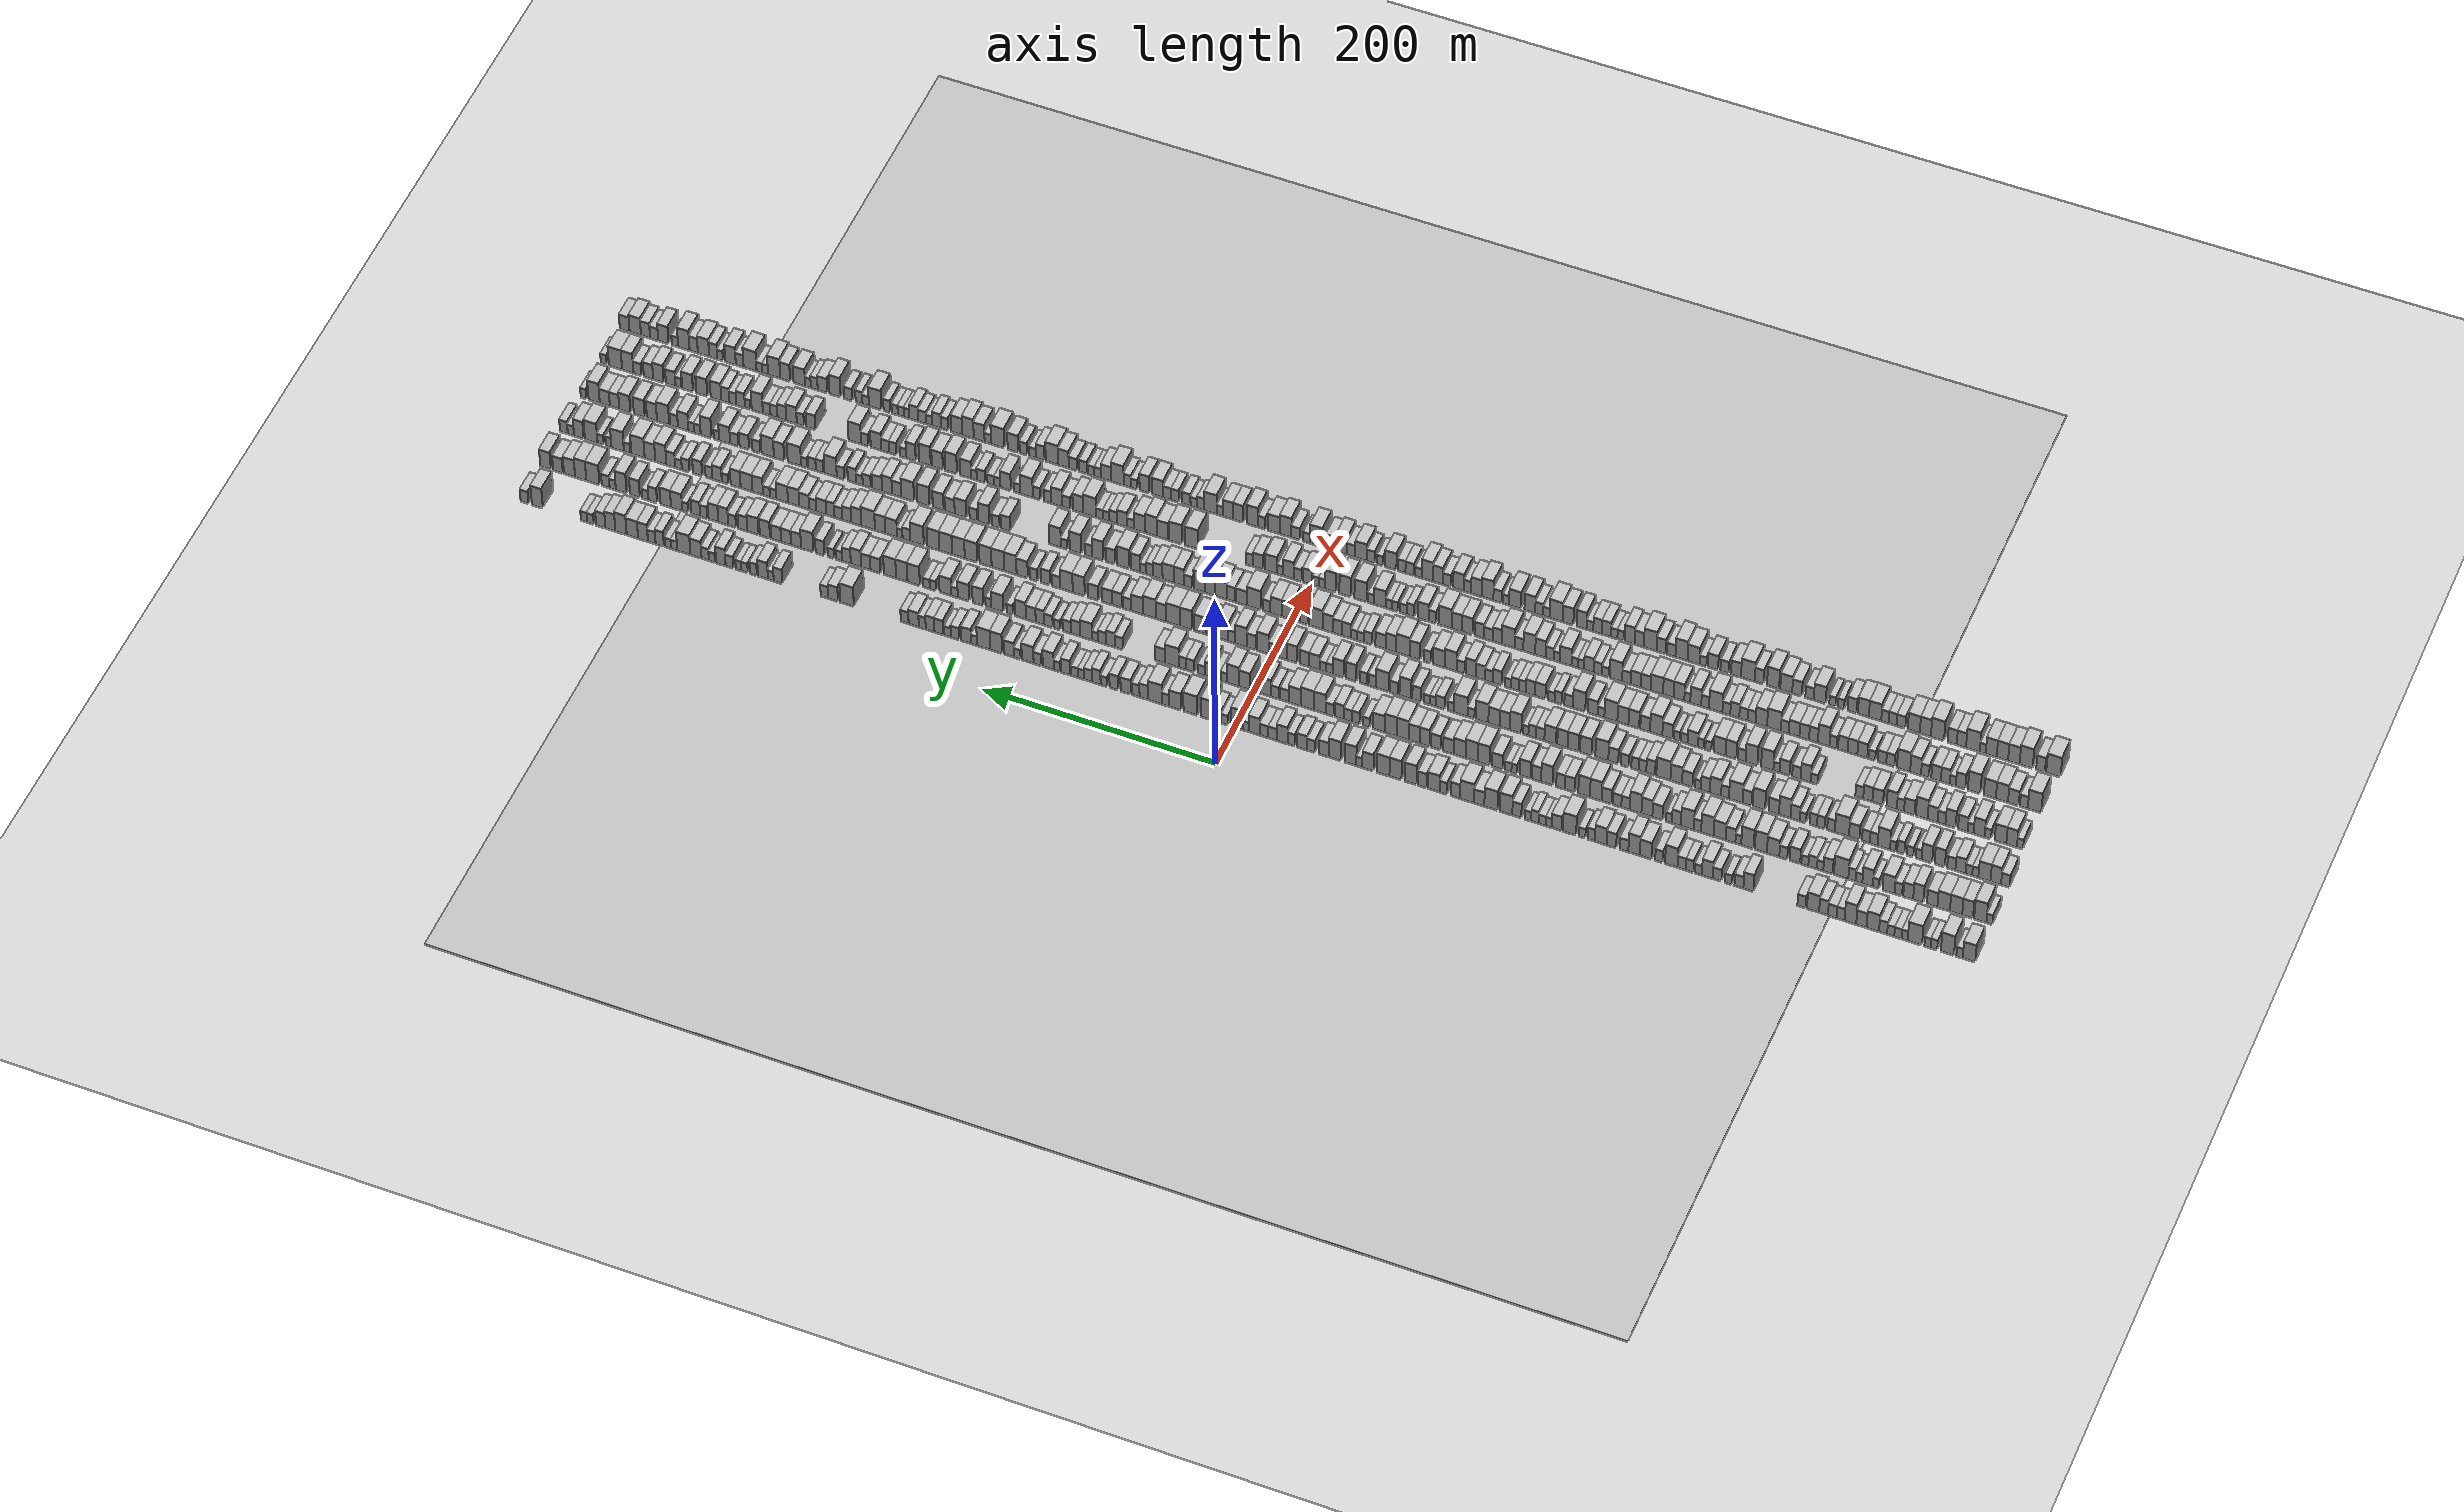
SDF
<?xml version="1.0" encoding="utf-8"?>

<sdf version="1.6">

   <world name="default">

      <gui fullscreen="0">

         <camera name="user_camera">

            <pose>-15 0 4.57585 0 0 0</pose>

            <view_controller>orbit</view_controller>

         </camera>

      </gui>

      <scene>

         <sky>

           <clouds>

             <speed>12</speed>

           </clouds>

         </sky>

         <ambient>0.4 0.4 0.4 1</ambient>

         <background>0.7 0.7 0.7 1</background>

         <shadows>1</shadows>

      </scene>

      <gravity>0 0 -9.8066</gravity>

      <magnetic_field>6e-06 2.3e-05 -4.2e-05</magnetic_field>

      <physics default="0" name="default_physics" type="ode">

         <ode>

            <solver>

               <type>quick</type>

               <iters>10</iters>

               <sor>1.0</sor>

               <use_dynamic_moi_rescaling>0</use_dynamic_moi_rescaling>

            </solver>

            <constraints>

               <cfm>0</cfm>

               <erp>0.2</erp>

               <contact_max_correcting_vel>100</contact_max_correcting_vel>

               <contact_surface_layer>0.001</contact_surface_layer>

            </constraints>

         </ode>

         <max_step_size>0.004</max_step_size>

         <real_time_factor>1</real_time_factor>

         <real_time_update_rate>250</real_time_update_rate>

      </physics>

      <light name="sun" type="directional">

         <cast_shadows>1</cast_shadows>

         <pose>0 0 10 0 0 0</pose>

         <diffuse>0.8 0.8 0.8 1</diffuse>

         <specular>0.2 0.2 0.2 1</specular>

         <attenuation>

            <range>1000</range>

            <constant>0.9</constant>

            <linear>0.01</linear>

            <quadratic>0.001</quadratic>

         </attenuation>

         <direction>-0.5 0.1 -0.9</direction>

      </light>

      <include>

         <name>ground_plane_1</name>

         <uri>model://HANNAS_ground_plane</uri>

         <pose>0 0 0  0 0 0</pose>

      </include>

      <include>

         <name>ground_plane_2</name>

         <uri>model://HANNAS_ground_plane</uri>

         <pose>100 0 0  0 0 0</pose>

      </include>

      <model name="building_1">

         <static>1</static>

         <pose frame="">50.0000 -614.8495 0 0.000000 0.000000 0.000000</pose>

         <link name="link">

            <pose frame="">0 0 10.50 0 0 0</pose>

            <collision name="collision">

               <geometry>

                  <box>

                     <size>20.0000 10.3011 21.0000</size>

                  </box>

               </geometry>

               <max_contacts>10</max_contacts>

               <surface>

                  <contact>

                     <ode/>

                  </contact>

                  <bounce/>

                  <friction>

                     <torsional>

                        <ode/>

                     </torsional>

                     <ode/>

                  </friction>

               </surface>

            </collision>

            <visual name="visual">

               <cast_shadows>0</cast_shadows>

               <geometry>

                  <box>

                     <size>20.0000 10.3011 21.0000</size>

                  </box>

               </geometry>

               <material>

                  <script>

                     <uri>model://HANNAS_wall/materials/scripts</uri>

                     <uri>model://HANNAS_wall/materials/textures</uri>

                     <name>vrc/HANNAS_wall</name>

                  </script>

               </material>

            </visual>

            <self_collide>0</self_collide>

            <enable_wind>0</enable_wind>

            <kinematic>0</kinematic>

         </link>

      </model>

      <model name="building_2">

         <static>1</static>

         <pose frame="">50.0000 -607.0662 0 0.000000 0.000000 0.000000</pose>

         <link name="link">

            <pose frame="">0 0 6.00 0 0 0</pose>

            <collision name="collision">

               <geometry>

                  <box>

                     <size>20.0000 5.2654 12.0000</size>

                  </box>

               </geometry>

               <max_contacts>10</max_contacts>

               <surface>

                  <contact>

                     <ode/>

                  </contact>

                  <bounce/>

                  <friction>

                     <torsional>

                        <ode/>

                     </torsional>

                     <ode/>

                  </friction>

               </surface>

            </collision>

            <visual name="visual">

               <cast_shadows>0</cast_shadows>

               <geometry>

                  <box>

                     <size>20.0000 5.2654 12.0000</size>

                  </box>

               </geometry>

               <material>

                  <script>

                     <uri>model://HANNAS_wall/materials/scripts</uri>

                     <uri>model://HANNAS_wall/materials/textures</uri>

                     <name>vrc/HANNAS_wall</name>

                  </script>

               </material>

            </visual>

            <self_collide>0</self_collide>

            <enable_wind>0</enable_wind>

            <kinematic>0</kinematic>

         </link>

      </model>

      <model name="building_3">

         <static>1</static>

         <pose frame="">50.0000 -597.0475 0 0.000000 0.000000 0.000000</pose>

         <link name="link">

            <pose frame="">0 0 12.00 0 0 0</pose>

            <collision name="collision">

               <geometry>

                  <box>

                     <size>20.0000 10.7720 24.0000</size>

                  </box>

               </geometry>

               <max_contacts>10</max_contacts>

               <surface>

                  <contact>

                     <ode/>

                  </contact>

                  <bounce/>

                  <friction>

                     <torsional>

                        <ode/>

                     </torsional>

                     <ode/>

                  </friction>

               </surface>

            </collision>

            <visual name="visual">

               <cast_shadows>0</cast_shadows>

               <geometry>

                  <box>

                     <size>20.0000 10.7720 24.0000</size>

                  </box>

               </geometry>

               <material>

                  <script>

                     <uri>model://HANNAS_wall/materials/scripts</uri>

                     <uri>model://HANNAS_wall/materials/textures</uri>

                     <name>vrc/HANNAS_wall</name>

                  </script>

               </material>

            </visual>

            <self_collide>0</self_collide>

            <enable_wind>0</enable_wind>

            <kinematic>0</kinematic>

         </link>

      </model>

      <model name="building_4">

         <static>1</static>

         <pose frame="">50.0000 -585.9418 0 0.000000 0.000000 0.000000</pose>

         <link name="link">

            <pose frame="">0 0 6.00 0 0 0</pose>

            <collision name="collision">

               <geometry>

                  <box>

                     <size>20.0000 5.4393 12.0000</size>

                  </box>

               </geometry>

               <max_contacts>10</max_contacts>

               <surface>

                  <contact>

                     <ode/>

                  </contact>

                  <bounce/>

                  <friction>

                     <torsional>

                        <ode/>

                     </torsional>

                     <ode/>

                  </friction>

               </surface>

            </collision>

            <visual name="visual">

               <cast_shadows>0</cast_shadows>

               <geometry>

                  <box>

                     <size>20.0000 5.4393 12.0000</size>

                  </box>

               </geometry>

               <material>

                  <script>

                     <uri>model://HANNAS_wall/materials/scripts</uri>

                     <uri>model://HANNAS_wall/materials/textures</uri>

                     <name>vrc/HANNAS_wall</name>

                  </script>

               </material>

            </visual>

            <self_collide>0</self_collide>

            <enable_wind>0</enable_wind>

            <kinematic>0</kinematic>

         </link>

      </model>

      <model name="building_5">

         <static>1</static>

         <pose frame="">50.0000 -580.6580 0 0.000000 0.000000 0.000000</pose>

         <link name="link">

            <pose frame="">0 0 6.00 0 0 0</pose>

            <collision name="collision">

               <geometry>

                  <box>

                     <size>20.0000 5.1283 12.0000</size>

                  </box>

               </geometry>

               <max_contacts>10</max_contacts>

               <surface>

                  <contact>

                     <ode/>

                  </contact>

                  <bounce/>

                  <friction>

                     <torsional>

                        <ode/>

                     </torsional>

                     <ode/>

                  </friction>

               </surface>

            </collision>

            <visual name="visual">

               <cast_shadows>0</cast_shadows>

               <geometry>

                  <box>

                     <size>20.0000 5.1283 12.0000</size>

                  </box>

               </geometry>

               <material>

                  <script>

                     <uri>model://HANNAS_wall/materials/scripts</uri>

                     <uri>model://HANNAS_wall/materials/textures</uri>

                     <name>vrc/HANNAS_wall</name>

                  </script>

               </material>

            </visual>

            <self_collide>0</self_collide>

            <enable_wind>0</enable_wind>

            <kinematic>0</kinematic>

         </link>

      </model>

      <model name="building_6">

         <static>1</static>

         <pose frame="">50.0000 -570.1787 0 0.000000 0.000000 0.000000</pose>

         <link name="link">

            <pose frame="">0 0 12.00 0 0 0</pose>

            <collision name="collision">

               <geometry>

                  <box>

                     <size>20.0000 11.8302 24.0000</size>

                  </box>

               </geometry>

               <max_contacts>10</max_contacts>

               <surface>

                  <contact>

                     <ode/>

                  </contact>

                  <bounce/>

                  <friction>

                     <torsional>

                        <ode/>

                     </torsional>

                     <ode/>

                  </friction>

               </surface>

            </collision>

            <visual name="visual">

               <cast_shadows>0</cast_shadows>

               <geometry>

                  <box>

                     <size>20.0000 11.8302 24.0000</size>

                  </box>

               </geometry>

               <material>

                  <script>

                     <uri>model://HANNAS_wall/materials/scripts</uri>

                     <uri>model://HANNAS_wall/materials/textures</uri>

                     <name>vrc/HANNAS_wall</name>

                  </script>

               </material>

            </visual>

            <self_collide>0</self_collide>

            <enable_wind>0</enable_wind>

            <kinematic>0</kinematic>

         </link>

      </model>

      <model name="building_7">

         <static>1</static>

         <pose frame="">50.0000 -561.7412 0 0.000000 0.000000 0.000000</pose>

         <link name="link">

            <pose frame="">0 0 6.00 0 0 0</pose>

            <collision name="collision">

               <geometry>

                  <box>

                     <size>20.0000 5.0449 12.0000</size>

                  </box>

               </geometry>

               <max_contacts>10</max_contacts>

               <surface>

                  <contact>

                     <ode/>

                  </contact>

                  <bounce/>

                  <friction>

                     <torsional>

                        <ode/>

                     </torsional>

                     <ode/>

                  </friction>

               </surface>

            </collision>

            <visual name="visual">

               <cast_shadows>0</cast_shadows>

               <geometry>

                  <box>

                     <size>20.0000 5.0449 12.0000</size>

                  </box>

               </geometry>

               <material>

                  <script>

                     <uri>model://HANNAS_wall/materials/scripts</uri>

                     <uri>model://HANNAS_wall/materials/textures</uri>

                     <name>vrc/HANNAS_wall</name>

                  </script>

               </material>

            </visual>

            <self_collide>0</self_collide>

            <enable_wind>0</enable_wind>

            <kinematic>0</kinematic>

         </link>

      </model>

      <model name="building_8">

         <static>1</static>

         <pose frame="">50.0000 -556.2496 0 0.000000 0.000000 0.000000</pose>

         <link name="link">

            <pose frame="">0 0 6.00 0 0 0</pose>

            <collision name="collision">

               <geometry>

                  <box>

                     <size>20.0000 5.9382 12.0000</size>

                  </box>

               </geometry>

               <max_contacts>10</max_contacts>

               <surface>

                  <contact>

                     <ode/>

                  </contact>

                  <bounce/>

                  <friction>

                     <torsional>

                        <ode/>

                     </torsional>

                     <ode/>

                  </friction>

               </surface>

            </collision>

            <visual name="visual">

               <cast_shadows>0</cast_shadows>

               <geometry>

                  <box>

                     <size>20.0000 5.9382 12.0000</size>

                  </box>

               </geometry>

               <material>

                  <script>

                     <uri>model://HANNAS_wall/materials/scripts</uri>

                     <uri>model://HANNAS_wall/materials/textures</uri>

                     <name>vrc/HANNAS_wall</name>

                  </script>

               </material>

            </visual>

            <self_collide>0</self_collide>

            <enable_wind>0</enable_wind>

            <kinematic>0</kinematic>

         </link>

      </model>

      <model name="building_9">

         <static>1</static>

         <pose frame="">50.0000 -550.3286 0 0.000000 0.000000 0.000000</pose>

         <link name="link">

            <pose frame="">0 0 6.00 0 0 0</pose>

            <collision name="collision">

               <geometry>

                  <box>

                     <size>20.0000 5.9038 12.0000</size>

                  </box>

               </geometry>

               <max_contacts>10</max_contacts>

               <surface>

                  <contact>

                     <ode/>

                  </contact>

                  <bounce/>

                  <friction>

                     <torsional>

                        <ode/>

                     </torsional>

                     <ode/>

                  </friction>

               </surface>

            </collision>

            <visual name="visual">

               <cast_shadows>0</cast_shadows>

               <geometry>

                  <box>

                     <size>20.0000 5.9038 12.0000</size>

                  </box>

               </geometry>

               <material>

                  <script>

                     <uri>model://HANNAS_wall/materials/scripts</uri>

                     <uri>model://HANNAS_wall/materials/textures</uri>

                     <name>vrc/HANNAS_wall</name>

                  </script>

               </material>

            </visual>

            <self_collide>0</self_collide>

            <enable_wind>0</enable_wind>

            <kinematic>0</kinematic>

         </link>

      </model>

      <model name="building_10">

         <static>1</static>

         <pose frame="">50.0000 -544.0306 0 0.000000 0.000000 0.000000</pose>

         <link name="link">

            <pose frame="">0 0 7.50 0 0 0</pose>

            <collision name="collision">

               <geometry>

                  <box>

                     <size>20.0000 6.6922 15.0000</size>

                  </box>

               </geometry>

               <max_contacts>10</max_contacts>

               <surface>

                  <contact>

                     <ode/>

                  </contact>

                  <bounce/>

                  <friction>

                     <torsional>

                        <ode/>

                     </torsional>

                     <ode/>

                  </friction>

               </surface>

            </collision>

            <visual name="visual">

               <cast_shadows>0</cast_shadows>

               <geometry>

                  <box>

                     <size>20.0000 6.6922 15.0000</size>

                  </box>

               </geometry>

               <material>

                  <script>

                     <uri>model://HANNAS_wall/materials/scripts</uri>

                     <uri>model://HANNAS_wall/materials/textures</uri>

                     <name>vrc/HANNAS_wall</name>

                  </script>

               </material>

            </visual>

            <self_collide>0</self_collide>

            <enable_wind>0</enable_wind>

            <kinematic>0</kinematic>

         </link>

      </model>

      <model name="building_11">

         <static>1</static>

         <pose frame="">50.0000 -535.5103 0 0.000000 0.000000 0.000000</pose>

         <link name="link">

            <pose frame="">0 0 10.50 0 0 0</pose>

            <collision name="collision">

               <geometry>

                  <box>

                     <size>20.0000 10.3485 21.0000</size>

                  </box>

               </geometry>

               <max_contacts>10</max_contacts>

               <surface>

                  <contact>

                     <ode/>

                  </contact>

                  <bounce/>

                  <friction>

                     <torsional>

                        <ode/>

                     </torsional>

                     <ode/>

                  </friction>

               </surface>

            </collision>

            <visual name="visual">

               <cast_shadows>0</cast_shadows>

               <geometry>

                  <box>

                     <size>20.0000 10.3485 21.0000</size>

                  </box>

               </geometry>

               <material>

                  <script>

                     <uri>model://HANNAS_wall/materials/scripts</uri>

                     <uri>model://HANNAS_wall/materials/textures</uri>

                     <name>vrc/HANNAS_wall</name>

                  </script>

               </material>

            </visual>

            <self_collide>0</self_collide>

            <enable_wind>0</enable_wind>

            <kinematic>0</kinematic>

         </link>

      </model>

      <model name="building_12">

         <static>1</static>

         <pose frame="">50.0000 -526.0814 0 0.000000 0.000000 0.000000</pose>

         <link name="link">

            <pose frame="">0 0 9.00 0 0 0</pose>

            <collision name="collision">

               <geometry>

                  <box>

                     <size>20.0000 8.5092 18.0000</size>

                  </box>

               </geometry>

               <max_contacts>10</max_contacts>

               <surface>

                  <contact>

                     <ode/>

                  </contact>

                  <bounce/>

                  <friction>

                     <torsional>

                        <ode/>

                     </torsional>

                     <ode/>

                  </friction>

               </surface>

            </collision>

            <visual name="visual">

               <cast_shadows>0</cast_shadows>

               <geometry>

                  <box>

                     <size>20.0000 8.5092 18.0000</size>

                  </box>

               </geometry>

               <material>

                  <script>

                     <uri>model://HANNAS_wall/materials/scripts</uri>

                     <uri>model://HANNAS_wall/materials/textures</uri>

                     <name>vrc/HANNAS_wall</name>

                  </script>

               </material>

            </visual>

            <self_collide>0</self_collide>

            <enable_wind>0</enable_wind>

            <kinematic>0</kinematic>

         </link>

      </model>

      <model name="building_13">

         <static>1</static>

         <pose frame="">50.0000 -516.9730 0 0.000000 0.000000 0.000000</pose>

         <link name="link">

            <pose frame="">0 0 12.00 0 0 0</pose>

            <collision name="collision">

               <geometry>

                  <box>

                     <size>20.0000 9.7076 24.0000</size>

                  </box>

               </geometry>

               <max_contacts>10</max_contacts>

               <surface>

                  <contact>

                     <ode/>

                  </contact>

                  <bounce/>

                  <friction>

                     <torsional>

                        <ode/>

                     </torsional>

                     <ode/>

                  </friction>

               </surface>

            </collision>

            <visual name="visual">

               <cast_shadows>0</cast_shadows>

               <geometry>

                  <box>

                     <size>20.0000 9.7076 24.0000</size>

                  </box>

               </geometry>

               <material>

                  <script>

                     <uri>model://HANNAS_wall/materials/scripts</uri>

                     <uri>model://HANNAS_wall/materials/textures</uri>

                     <name>vrc/HANNAS_wall</name>

                  </script>

               </material>

            </visual>

            <self_collide>0</self_collide>

            <enable_wind>0</enable_wind>

            <kinematic>0</kinematic>

         </link>

      </model>

      <model name="building_14">

         <static>1</static>

         <pose frame="">50.0000 -508.9044 0 0.000000 0.000000 0.000000</pose>

         <link name="link">

            <pose frame="">0 0 7.50 0 0 0</pose>

            <collision name="collision">

               <geometry>

                  <box>

                     <size>20.0000 6.4295 15.0000</size>

                  </box>

               </geometry>

               <max_contacts>10</max_contacts>

               <surface>

                  <contact>

                     <ode/>

                  </contact>

                  <bounce/>

                  <friction>

                     <torsional>

                        <ode/>

                     </torsional>

                     <ode/>

                  </friction>

               </surface>

            </collision>

            <visual name="visual">

               <cast_shadows>0</cast_shadows>

               <geometry>

                  <box>

                     <size>20.0000 6.4295 15.0000</size>

                  </box>

               </geometry>

               <material>

                  <script>

                     <uri>model://HANNAS_wall/materials/scripts</uri>

                     <uri>model://HANNAS_wall/materials/textures</uri>

                     <name>vrc/HANNAS_wall</name>

                  </script>

               </material>

            </visual>

            <self_collide>0</self_collide>

            <enable_wind>0</enable_wind>

            <kinematic>0</kinematic>

         </link>

      </model>

      <model name="building_15">

         <static>1</static>

         <pose frame="">50.0000 -502.0287 0 0.000000 0.000000 0.000000</pose>

         <link name="link">

            <pose frame="">0 0 7.50 0 0 0</pose>

            <collision name="collision">

               <geometry>

                  <box>

                     <size>20.0000 7.3219 15.0000</size>

                  </box>

               </geometry>

               <max_contacts>10</max_contacts>

               <surface>

                  <contact>

                     <ode/>

                  </contact>

                  <bounce/>

                  <friction>

                     <torsional>

                        <ode/>

                     </torsional>

                     <ode/>

                  </friction>

               </surface>

            </collision>

            <visual name="visual">

               <cast_shadows>0</cast_shadows>

               <geometry>

                  <box>

                     <size>20.0000 7.3219 15.0000</size>

                  </box>

               </geometry>

               <material>

                  <script>

                     <uri>model://HANNAS_wall/materials/scripts</uri>

                     <uri>model://HANNAS_wall/materials/textures</uri>

                     <name>vrc/HANNAS_wall</name>

                  </script>

               </material>

            </visual>

            <self_collide>0</self_collide>

            <enable_wind>0</enable_wind>

            <kinematic>0</kinematic>

         </link>

      </model>

      <model name="building_16">

         <static>1</static>

         <pose frame="">50.0000 -494.6923 0 0.000000 0.000000 0.000000</pose>

         <link name="link">

            <pose frame="">0 0 9.00 0 0 0</pose>

            <collision name="collision">

               <geometry>

                  <box>

                     <size>20.0000 7.3508 18.0000</size>

                  </box>

               </geometry>

               <max_contacts>10</max_contacts>

               <surface>

                  <contact>

                     <ode/>

                  </contact>

                  <bounce/>

                  <friction>

                     <torsional>

                        <ode/>

                     </torsional>

                     <ode/>

                  </friction>

               </surface>

            </collision>

            <visual name="visual">

               <cast_shadows>0</cast_shadows>

               <geometry>

                  <box>

                     <size>20.0000 7.3508 18.0000</size>

                  </box>

               </geometry>

               <material>

                  <script>

                     <uri>model://HANNAS_wall/materials/scripts</uri>

                     <uri>model://HANNAS_wall/materials/textures</uri>

                     <name>vrc/HANNAS_wall</name>

                  </script>

               </material>

            </visual>

            <self_collide>0</self_collide>

            <enable_wind>0</enable_wind>

            <kinematic>0</kinematic>

         </link>

      </model>

      <model name="building_17">

         <static>1</static>

         <pose frame="">50.0000 -485.9924 0 0.000000 0.000000 0.000000</pose>

         <link name="link">

            <pose frame="">0 0 10.50 0 0 0</pose>

            <collision name="collision">

               <geometry>

                  <box>

                     <size>20.0000 10.0489 21.0000</size>

                  </box>

               </geometry>

               <max_contacts>10</max_contacts>

               <surface>

                  <contact>

                     <ode/>

                  </contact>

                  <bounce/>

                  <friction>

                     <torsional>

                        <ode/>

                     </torsional>

                     <ode/>

                  </friction>

               </surface>

            </collision>

            <visual name="visual">

               <cast_shadows>0</cast_shadows>

               <geometry>

                  <box>

                     <size>20.0000 10.0489 21.0000</size>

                  </box>

               </geometry>

               <material>

                  <script>

                     <uri>model://HANNAS_wall/materials/scripts</uri>

                     <uri>model://HANNAS_wall/materials/textures</uri>

                     <name>vrc/HANNAS_wall</name>

                  </script>

               </material>

            </visual>

            <self_collide>0</self_collide>

            <enable_wind>0</enable_wind>

            <kinematic>0</kinematic>

         </link>

      </model>

      <model name="building_18">

         <static>1</static>

         <pose frame="">50.0000 -476.5046 0 0.000000 0.000000 0.000000</pose>

         <link name="link">

            <pose frame="">0 0 7.50 0 0 0</pose>

            <collision name="collision">

               <geometry>

                  <box>

                     <size>20.0000 6.9269 15.0000</size>

                  </box>

               </geometry>

               <max_contacts>10</max_contacts>

               <surface>

                  <contact>

                     <ode/>

                  </contact>

                  <bounce/>

                  <friction>

                     <torsional>

                        <ode/>

                     </torsional>

                     <ode/>

                  </friction>

               </surface>

            </collision>

            <visual name="visual">

               <cast_shadows>0</cast_shadows>

               <geometry>

                  <box>

                     <size>20.0000 6.9269 15.0000</size>

                  </box>

               </geometry>

               <material>

                  <script>

                     <uri>model://HANNAS_wall/materials/scripts</uri>

                     <uri>model://HANNAS_wall/materials/textures</uri>

                     <name>vrc/HANNAS_wall</name>

                  </script>

               </material>

            </visual>

            <self_collide>0</self_collide>

            <enable_wind>0</enable_wind>

            <kinematic>0</kinematic>

         </link>

      </model>

      <model name="building_19">

         <static>1</static>

         <pose frame="">50.0000 -432.3915 0 0.000000 0.000000 0.000000</pose>

         <link name="link">

            <pose frame="">0 0 10.50 0 0 0</pose>

            <collision name="collision">

               <geometry>

                  <box>

                     <size>20.0000 8.4331 21.0000</size>

                  </box>

               </geometry>

               <max_contacts>10</max_contacts>

               <surface>

                  <contact>

                     <ode/>

                  </contact>

                  <bounce/>

                  <friction>

                     <torsional>

                        <ode/>

                     </torsional>

                     <ode/>

                  </friction>

               </surface>

            </collision>

            <visual name="visual">

               <cast_shadows>0</cast_shadows>

               <geometry>

                  <box>

                     <size>20.0000 8.4331 21.0000</size>

                  </box>

               </geometry>

               <material>

                  <script>

                     <uri>model://HANNAS_wall/materials/scripts</uri>

                     <uri>model://HANNAS_wall/materials/textures</uri>

                     <name>vrc/HANNAS_wall</name>

                  </script>

               </material>

            </visual>

            <self_collide>0</self_collide>

            <enable_wind>0</enable_wind>

            <kinematic>0</kinematic>

         </link>

      </model>

      <model name="building_20">

         <static>1</static>

         <pose frame="">50.0000 -424.4492 0 0.000000 0.000000 0.000000</pose>

         <link name="link">

            <pose frame="">0 0 7.50 0 0 0</pose>

            <collision name="collision">

               <geometry>

                  <box>

                     <size>20.0000 7.4514 15.0000</size>

                  </box>

               </geometry>

               <max_contacts>10</max_contacts>

               <surface>

                  <contact>

                     <ode/>

                  </contact>

                  <bounce/>

                  <friction>

                     <torsional>

                        <ode/>

                     </torsional>

                     <ode/>

                  </friction>

               </surface>

            </collision>

            <visual name="visual">

               <cast_shadows>0</cast_shadows>

               <geometry>

                  <box>

                     <size>20.0000 7.4514 15.0000</size>

                  </box>

               </geometry>

               <material>

                  <script>

                     <uri>model://HANNAS_wall/materials/scripts</uri>

                     <uri>model://HANNAS_wall/materials/textures</uri>

                     <name>vrc/HANNAS_wall</name>

                  </script>

               </material>

            </visual>

            <self_collide>0</self_collide>

            <enable_wind>0</enable_wind>

            <kinematic>0</kinematic>

         </link>

      </model>

      <model name="building_21">

         <static>1</static>

         <pose frame="">50.0000 -415.7872 0 0.000000 0.000000 0.000000</pose>

         <link name="link">

            <pose frame="">0 0 6.00 0 0 0</pose>

            <collision name="collision">

               <geometry>

                  <box>

                     <size>20.0000 5.8726 12.0000</size>

                  </box>

               </geometry>

               <max_contacts>10</max_contacts>

               <surface>

                  <contact>

                     <ode/>

                  </contact>

                  <bounce/>

                  <friction>

                     <torsional>

                        <ode/>

                     </torsional>

                     <ode/>

                  </friction>

               </surface>

            </collision>

            <visual name="visual">

               <cast_shadows>0</cast_shadows>

               <geometry>

                  <box>

                     <size>20.0000 5.8726 12.0000</size>

                  </box>

               </geometry>

               <material>

                  <script>

                     <uri>model://HANNAS_wall/materials/scripts</uri>

                     <uri>model://HANNAS_wall/materials/textures</uri>

                     <name>vrc/HANNAS_wall</name>

                  </script>

               </material>

            </visual>

            <self_collide>0</self_collide>

            <enable_wind>0</enable_wind>

            <kinematic>0</kinematic>

         </link>

      </model>

      <model name="building_22">

         <static>1</static>

         <pose frame="">50.0000 -406.2614 0 0.000000 0.000000 0.000000</pose>

         <link name="link">

            <pose frame="">0 0 7.50 0 0 0</pose>

            <collision name="collision">

               <geometry>

                  <box>

                     <size>20.0000 7.1791 15.0000</size>

                  </box>

               </geometry>

               <max_contacts>10</max_contacts>

               <surface>

                  <contact>

                     <ode/>

                  </contact>

                  <bounce/>

                  <friction>

                     <torsional>

                        <ode/>

                     </torsional>

                     <ode/>

                  </friction>

               </surface>

            </collision>

            <visual name="visual">

               <cast_shadows>0</cast_shadows>

               <geometry>

                  <box>

                     <size>20.0000 7.1791 15.0000</size>

                  </box>

               </geometry>

               <material>

                  <script>

                     <uri>model://HANNAS_wall/materials/scripts</uri>

                     <uri>model://HANNAS_wall/materials/textures</uri>

                     <name>vrc/HANNAS_wall</name>

                  </script>

               </material>

            </visual>

            <self_collide>0</self_collide>

            <enable_wind>0</enable_wind>

            <kinematic>0</kinematic>

         </link>

      </model>

      <model name="building_23">

         <static>1</static>

         <pose frame="">50.0000 -398.1142 0 0.000000 0.000000 0.000000</pose>

         <link name="link">

            <pose frame="">0 0 10.50 0 0 0</pose>

            <collision name="collision">

               <geometry>

                  <box>

                     <size>20.0000 9.1151 21.0000</size>

                  </box>

               </geometry>

               <max_contacts>10</max_contacts>

               <surface>

                  <contact>

                     <ode/>

                  </contact>

                  <bounce/>

                  <friction>

                     <torsional>

                        <ode/>

                     </torsional>

                     <ode/>

                  </friction>

               </surface>

            </collision>

            <visual name="visual">

               <cast_shadows>0</cast_shadows>

               <geometry>

                  <box>

                     <size>20.0000 9.1151 21.0000</size>

                  </box>

               </geometry>

               <material>

                  <script>

                     <uri>model://HANNAS_wall/materials/scripts</uri>

                     <uri>model://HANNAS_wall/materials/textures</uri>

                     <name>vrc/HANNAS_wall</name>

                  </script>

               </material>

            </visual>

            <self_collide>0</self_collide>

            <enable_wind>0</enable_wind>

            <kinematic>0</kinematic>

         </link>

      </model>

      <model name="building_24">

         <static>1</static>

         <pose frame="">50.0000 -390.5618 0 0.000000 0.000000 0.000000</pose>

         <link name="link">

            <pose frame="">0 0 6.00 0 0 0</pose>

            <collision name="collision">

               <geometry>

                  <box>

                     <size>20.0000 5.9898 12.0000</size>

                  </box>

               </geometry>

               <max_contacts>10</max_contacts>

               <surface>

                  <contact>

                     <ode/>

                  </contact>

                  <bounce/>

                  <friction>

                     <torsional>

                        <ode/>

                     </torsional>

                     <ode/>

                  </friction>

               </surface>

            </collision>

            <visual name="visual">

               <cast_shadows>0</cast_shadows>

               <geometry>

                  <box>

                     <size>20.0000 5.9898 12.0000</size>

                  </box>

               </geometry>

               <material>

                  <script>

                     <uri>model://HANNAS_wall/materials/scripts</uri>

                     <uri>model://HANNAS_wall/materials/textures</uri>

                     <name>vrc/HANNAS_wall</name>

                  </script>

               </material>

            </visual>

            <self_collide>0</self_collide>

            <enable_wind>0</enable_wind>

            <kinematic>0</kinematic>

         </link>

      </model>

      <model name="building_25">

         <static>1</static>

         <pose frame="">50.0000 -383.3535 0 0.000000 0.000000 0.000000</pose>

         <link name="link">

            <pose frame="">0 0 7.50 0 0 0</pose>

            <collision name="collision">

               <geometry>

                  <box>

                     <size>20.0000 6.4269 15.0000</size>

                  </box>

               </geometry>

               <max_contacts>10</max_contacts>

               <surface>

                  <contact>

                     <ode/>

                  </contact>

                  <bounce/>

                  <friction>

                     <torsional>

                        <ode/>

                     </torsional>

                     <ode/>

                  </friction>

               </surface>

            </collision>

            <visual name="visual">

               <cast_shadows>0</cast_shadows>

               <geometry>

                  <box>

                     <size>20.0000 6.4269 15.0000</size>

                  </box>

               </geometry>

               <material>

                  <script>

                     <uri>model://HANNAS_wall/materials/scripts</uri>

                     <uri>model://HANNAS_wall/materials/textures</uri>

                     <name>vrc/HANNAS_wall</name>

                  </script>

               </material>

            </visual>

            <self_collide>0</self_collide>

            <enable_wind>0</enable_wind>

            <kinematic>0</kinematic>

         </link>

      </model>

      <model name="building_26">

         <static>1</static>

         <pose frame="">50.0000 -376.6653 0 0.000000 0.000000 0.000000</pose>

         <link name="link">

            <pose frame="">0 0 7.50 0 0 0</pose>

            <collision name="collision">

               <geometry>

                  <box>

                     <size>20.0000 6.9495 15.0000</size>

                  </box>

               </geometry>

               <max_contacts>10</max_contacts>

               <surface>

                  <contact>

                     <ode/>

                  </contact>

                  <bounce/>

                  <friction>

                     <torsional>

                        <ode/>

                     </torsional>

                     <ode/>

                  </friction>

               </surface>

            </collision>

            <visual name="visual">

               <cast_shadows>0</cast_shadows>

               <geometry>

                  <box>

                     <size>20.0000 6.9495 15.0000</size>

                  </box>

               </geometry>

               <material>

                  <script>

                     <uri>model://HANNAS_wall/materials/scripts</uri>

                     <uri>model://HANNAS_wall/materials/textures</uri>

                     <name>vrc/HANNAS_wall</name>

                  </script>

               </material>

            </visual>

            <self_collide>0</self_collide>

            <enable_wind>0</enable_wind>

            <kinematic>0</kinematic>

         </link>

      </model>

      <model name="building_27">

         <static>1</static>

         <pose frame="">50.0000 -368.0077 0 0.000000 0.000000 0.000000</pose>

         <link name="link">

            <pose frame="">0 0 12.00 0 0 0</pose>

            <collision name="collision">

               <geometry>

                  <box>

                     <size>20.0000 10.3655 24.0000</size>

                  </box>

               </geometry>

               <max_contacts>10</max_contacts>

               <surface>

                  <contact>

                     <ode/>

                  </contact>

                  <bounce/>

                  <friction>

                     <torsional>

                        <ode/>

                     </torsional>

                     <ode/>

                  </friction>

               </surface>

            </collision>

            <visual name="visual">

               <cast_shadows>0</cast_shadows>

               <geometry>

                  <box>

                     <size>20.0000 10.3655 24.0000</size>

                  </box>

               </geometry>

               <material>

                  <script>

                     <uri>model://HANNAS_wall/materials/scripts</uri>

                     <uri>model://HANNAS_wall/materials/textures</uri>

                     <name>vrc/HANNAS_wall</name>

                  </script>

               </material>

            </visual>

            <self_collide>0</self_collide>

            <enable_wind>0</enable_wind>

            <kinematic>0</kinematic>

         </link>

      </model>

      <model name="building_28">

         <static>1</static>

         <pose frame="">50.0000 -357.7031 0 0.000000 0.000000 0.000000</pose>

         <link name="link">

            <pose frame="">0 0 7.50 0 0 0</pose>

            <collision name="collision">

               <geometry>

                  <box>

                     <size>20.0000 6.2438 15.0000</size>

                  </box>

               </geometry>

               <max_contacts>10</max_contacts>

               <surface>

                  <contact>

                     <ode/>

                  </contact>

                  <bounce/>

                  <friction>

                     <torsional>

                        <ode/>

                     </torsional>

                     <ode/>

                  </friction>

               </surface>

            </collision>

            <visual name="visual">

               <cast_shadows>0</cast_shadows>

               <geometry>

                  <box>

                     <size>20.0000 6.2438 15.0000</size>

                  </box>

               </geometry>

               <material>

                  <script>

                     <uri>model://HANNAS_wall/materials/scripts</uri>

                     <uri>model://HANNAS_wall/materials/textures</uri>

                     <name>vrc/HANNAS_wall</name>

                  </script>

               </material>

            </visual>

            <self_collide>0</self_collide>

            <enable_wind>0</enable_wind>

            <kinematic>0</kinematic>

         </link>

      </model>

      <model name="building_29">

         <static>1</static>

         <pose frame="">50.0000 -346.6803 0 0.000000 0.000000 0.000000</pose>

         <link name="link">

            <pose frame="">0 0 10.50 0 0 0</pose>

            <collision name="collision">

               <geometry>

                  <box>

                     <size>20.0000 9.8017 21.0000</size>

                  </box>

               </geometry>

               <max_contacts>10</max_contacts>

               <surface>

                  <contact>

                     <ode/>

                  </contact>

                  <bounce/>

                  <friction>

                     <torsional>

                        <ode/>

                     </torsional>

                     <ode/>

                  </friction>

               </surface>

            </collision>

            <visual name="visual">

               <cast_shadows>0</cast_shadows>

               <geometry>

                  <box>

                     <size>20.0000 9.8017 21.0000</size>

                  </box>

               </geometry>

               <material>

                  <script>

                     <uri>model://HANNAS_wall/materials/scripts</uri>

                     <uri>model://HANNAS_wall/materials/textures</uri>

                     <name>vrc/HANNAS_wall</name>

                  </script>

               </material>

            </visual>

            <self_collide>0</self_collide>

            <enable_wind>0</enable_wind>

            <kinematic>0</kinematic>

         </link>

      </model>

      <model name="building_30">

         <static>1</static>

         <pose frame="">50.0000 -336.9209 0 0.000000 0.000000 0.000000</pose>

         <link name="link">

            <pose frame="">0 0 12.00 0 0 0</pose>

            <collision name="collision">

               <geometry>

                  <box>

                     <size>20.0000 9.7171 24.0000</size>

                  </box>

               </geometry>

               <max_contacts>10</max_contacts>

               <surface>

                  <contact>

                     <ode/>

                  </contact>

                  <bounce/>

                  <friction>

                     <torsional>

                        <ode/>

                     </torsional>

                     <ode/>

                  </friction>

               </surface>

            </collision>

            <visual name="visual">

               <cast_shadows>0</cast_shadows>

               <geometry>

                  <box>

                     <size>20.0000 9.7171 24.0000</size>

                  </box>

               </geometry>

               <material>

                  <script>

                     <uri>model://HANNAS_wall/materials/scripts</uri>

                     <uri>model://HANNAS_wall/materials/textures</uri>

                     <name>vrc/HANNAS_wall</name>

                  </script>

               </material>

            </visual>

            <self_collide>0</self_collide>

            <enable_wind>0</enable_wind>

            <kinematic>0</kinematic>

         </link>

      </model>

      <model name="building_31">

         <static>1</static>

         <pose frame="">50.0000 -328.4651 0 0.000000 0.000000 0.000000</pose>

         <link name="link">

            <pose frame="">0 0 7.50 0 0 0</pose>

            <collision name="collision">

               <geometry>

                  <box>

                     <size>20.0000 7.1943 15.0000</size>

                  </box>

               </geometry>

               <max_contacts>10</max_contacts>

               <surface>

                  <contact>

                     <ode/>

                  </contact>

                  <bounce/>

                  <friction>

                     <torsional>

                        <ode/>

                     </torsional>

                     <ode/>

                  </friction>

               </surface>

            </collision>

            <visual name="visual">

               <cast_shadows>0</cast_shadows>

               <geometry>

                  <box>

                     <size>20.0000 7.1943 15.0000</size>

                  </box>

               </geometry>

               <material>

                  <script>

                     <uri>model://HANNAS_wall/materials/scripts</uri>

                     <uri>model://HANNAS_wall/materials/textures</uri>

                     <name>vrc/HANNAS_wall</name>

                  </script>

               </material>

            </visual>

            <self_collide>0</self_collide>

            <enable_wind>0</enable_wind>

            <kinematic>0</kinematic>

         </link>

      </model>

      <model name="building_32">

         <static>1</static>

         <pose frame="">50.0000 -317.8894 0 0.000000 0.000000 0.000000</pose>

         <link name="link">

            <pose frame="">0 0 9.00 0 0 0</pose>

            <collision name="collision">

               <geometry>

                  <box>

                     <size>20.0000 7.9571 18.0000</size>

                  </box>

               </geometry>

               <max_contacts>10</max_contacts>

               <surface>

                  <contact>

                     <ode/>

                  </contact>

                  <bounce/>

                  <friction>

                     <torsional>

                        <ode/>

                     </torsional>

                     <ode/>

                  </friction>

               </surface>

            </collision>

            <visual name="visual">

               <cast_shadows>0</cast_shadows>

               <geometry>

                  <box>

                     <size>20.0000 7.9571 18.0000</size>

                  </box>

               </geometry>

               <material>

                  <script>

                     <uri>model://HANNAS_wall/materials/scripts</uri>

                     <uri>model://HANNAS_wall/materials/textures</uri>

                     <name>vrc/HANNAS_wall</name>

                  </script>

               </material>

            </visual>

            <self_collide>0</self_collide>

            <enable_wind>0</enable_wind>

            <kinematic>0</kinematic>

         </link>

      </model>

      <model name="building_33">

         <static>1</static>

         <pose frame="">50.0000 -309.0129 0 0.000000 0.000000 0.000000</pose>

         <link name="link">

            <pose frame="">0 0 10.50 0 0 0</pose>

            <collision name="collision">

               <geometry>

                  <box>

                     <size>20.0000 9.7960 21.0000</size>

                  </box>

               </geometry>

               <max_contacts>10</max_contacts>

               <surface>

                  <contact>

                     <ode/>

                  </contact>

                  <bounce/>

                  <friction>

                     <torsional>

                        <ode/>

                     </torsional>

                     <ode/>

                  </friction>

               </surface>

            </collision>

            <visual name="visual">

               <cast_shadows>0</cast_shadows>

               <geometry>

                  <box>

                     <size>20.0000 9.7960 21.0000</size>

                  </box>

               </geometry>

               <material>

                  <script>

                     <uri>model://HANNAS_wall/materials/scripts</uri>

                     <uri>model://HANNAS_wall/materials/textures</uri>

                     <name>vrc/HANNAS_wall</name>

                  </script>

               </material>

            </visual>

            <self_collide>0</self_collide>

            <enable_wind>0</enable_wind>

            <kinematic>0</kinematic>

         </link>

      </model>

      <model name="building_34">

         <static>1</static>

         <pose frame="">50.0000 -301.0867 0 0.000000 0.000000 0.000000</pose>

         <link name="link">

            <pose frame="">0 0 7.50 0 0 0</pose>

            <collision name="collision">

               <geometry>

                  <box>

                     <size>20.0000 6.0563 15.0000</size>

                  </box>

               </geometry>

               <max_contacts>10</max_contacts>

               <surface>

                  <contact>

                     <ode/>

                  </contact>

                  <bounce/>

                  <friction>

                     <torsional>

                        <ode/>

                     </torsional>

                     <ode/>

                  </friction>

               </surface>

            </collision>

            <visual name="visual">

               <cast_shadows>0</cast_shadows>

               <geometry>

                  <box>

                     <size>20.0000 6.0563 15.0000</size>

                  </box>

               </geometry>

               <material>

                  <script>

                     <uri>model://HANNAS_wall/materials/scripts</uri>

                     <uri>model://HANNAS_wall/materials/textures</uri>

                     <name>vrc/HANNAS_wall</name>

                  </script>

               </material>

            </visual>

            <self_collide>0</self_collide>

            <enable_wind>0</enable_wind>

            <kinematic>0</kinematic>

         </link>

      </model>

      <model name="building_35">

         <static>1</static>

         <pose frame="">50.0000 -293.1780 0 0.000000 0.000000 0.000000</pose>

         <link name="link">

            <pose frame="">0 0 6.00 0 0 0</pose>

            <collision name="collision">

               <geometry>

                  <box>

                     <size>20.0000 5.7611 12.0000</size>

                  </box>

               </geometry>

               <max_contacts>10</max_contacts>

               <surface>

                  <contact>

                     <ode/>

                  </contact>

                  <bounce/>

                  <friction>

                     <torsional>

                        <ode/>

                     </torsional>

                     <ode/>

                  </friction>

               </surface>

            </collision>

            <visual name="visual">

               <cast_shadows>0</cast_shadows>

               <geometry>

                  <box>

                     <size>20.0000 5.7611 12.0000</size>

                  </box>

               </geometry>

               <material>

                  <script>

                     <uri>model://HANNAS_wall/materials/scripts</uri>

                     <uri>model://HANNAS_wall/materials/textures</uri>

                     <name>vrc/HANNAS_wall</name>

                  </script>

               </material>

            </visual>

            <self_collide>0</self_collide>

            <enable_wind>0</enable_wind>

            <kinematic>0</kinematic>

         </link>

      </model>

      <model name="building_36">

         <static>1</static>

         <pose frame="">50.0000 -282.7511 0 0.000000 0.000000 0.000000</pose>

         <link name="link">

            <pose frame="">0 0 12.00 0 0 0</pose>

            <collision name="collision">

               <geometry>

                  <box>

                     <size>20.0000 11.0928 24.0000</size>

                  </box>

               </geometry>

               <max_contacts>10</max_contacts>

               <surface>

                  <contact>

                     <ode/>

                  </contact>

                  <bounce/>

                  <friction>

                     <torsional>

                        <ode/>

                     </torsional>

                     <ode/>

                  </friction>

               </surface>

            </collision>

            <visual name="visual">

               <cast_shadows>0</cast_shadows>

               <geometry>

                  <box>

                     <size>20.0000 11.0928 24.0000</size>

                  </box>

               </geometry>

               <material>

                  <script>

                     <uri>model://HANNAS_wall/materials/scripts</uri>

                     <uri>model://HANNAS_wall/materials/textures</uri>

                     <name>vrc/HANNAS_wall</name>

                  </script>

               </material>

            </visual>

            <self_collide>0</self_collide>

            <enable_wind>0</enable_wind>

            <kinematic>0</kinematic>

         </link>

      </model>

      <model name="building_37">

         <static>1</static>

         <pose frame="">50.0000 -272.0210 0 0.000000 0.000000 0.000000</pose>

         <link name="link">

            <pose frame="">0 0 9.00 0 0 0</pose>

            <collision name="collision">

               <geometry>

                  <box>

                     <size>20.0000 8.3673 18.0000</size>

                  </box>

               </geometry>

               <max_contacts>10</max_contacts>

               <surface>

                  <contact>

                     <ode/>

                  </contact>

                  <bounce/>

                  <friction>

                     <torsional>

                        <ode/>

                     </torsional>

                     <ode/>

                  </friction>

               </surface>

            </collision>

            <visual name="visual">

               <cast_shadows>0</cast_shadows>

               <geometry>

                  <box>

                     <size>20.0000 8.3673 18.0000</size>

                  </box>

               </geometry>

               <material>

                  <script>

                     <uri>model://HANNAS_wall/materials/scripts</uri>

                     <uri>model://HANNAS_wall/materials/textures</uri>

                     <name>vrc/HANNAS_wall</name>

                  </script>

               </material>

            </visual>

            <self_collide>0</self_collide>

            <enable_wind>0</enable_wind>

            <kinematic>0</kinematic>

         </link>

      </model>

      <model name="building_38">

         <static>1</static>

         <pose frame="">50.0000 -265.2547 0 0.000000 0.000000 0.000000</pose>

         <link name="link">

            <pose frame="">0 0 6.00 0 0 0</pose>

            <collision name="collision">

               <geometry>

                  <box>

                     <size>20.0000 5.1654 12.0000</size>

                  </box>

               </geometry>

               <max_contacts>10</max_contacts>

               <surface>

                  <contact>

                     <ode/>

                  </contact>

                  <bounce/>

                  <friction>

                     <torsional>

                        <ode/>

                     </torsional>

                     <ode/>

                  </friction>

               </surface>

            </collision>

            <visual name="visual">

               <cast_shadows>0</cast_shadows>

               <geometry>

                  <box>

                     <size>20.0000 5.1654 12.0000</size>

                  </box>

               </geometry>

               <material>

                  <script>

                     <uri>model://HANNAS_wall/materials/scripts</uri>

                     <uri>model://HANNAS_wall/materials/textures</uri>

                     <name>vrc/HANNAS_wall</name>

                  </script>

               </material>

            </visual>

            <self_collide>0</self_collide>

            <enable_wind>0</enable_wind>

            <kinematic>0</kinematic>

         </link>

      </model>

      <model name="building_39">

         <static>1</static>

         <pose frame="">50.0000 -259.7088 0 0.000000 0.000000 0.000000</pose>

         <link name="link">

            <pose frame="">0 0 6.00 0 0 0</pose>

            <collision name="collision">

               <geometry>

                  <box>

                     <size>20.0000 5.9265 12.0000</size>

                  </box>

               </geometry>

               <max_contacts>10</max_contacts>

               <surface>

                  <contact>

                     <ode/>

                  </contact>

                  <bounce/>

                  <friction>

                     <torsional>

                        <ode/>

                     </torsional>

                     <ode/>

                  </friction>

               </surface>

            </collision>

            <visual name="visual">

               <cast_shadows>0</cast_shadows>

               <geometry>

                  <box>

                     <size>20.0000 5.9265 12.0000</size>

                  </box>

               </geometry>

               <material>

                  <script>

                     <uri>model://HANNAS_wall/materials/scripts</uri>

                     <uri>model://HANNAS_wall/materials/textures</uri>

                     <name>vrc/HANNAS_wall</name>

                  </script>

               </material>

            </visual>

            <self_collide>0</self_collide>

            <enable_wind>0</enable_wind>

            <kinematic>0</kinematic>

         </link>

      </model>

      <model name="building_40">

         <static>1</static>

         <pose frame="">50.0000 -253.6281 0 0.000000 0.000000 0.000000</pose>

         <link name="link">

            <pose frame="">0 0 7.50 0 0 0</pose>

            <collision name="collision">

               <geometry>

                  <box>

                     <size>20.0000 6.2348 15.0000</size>

                  </box>

               </geometry>

               <max_contacts>10</max_contacts>

               <surface>

                  <contact>

                     <ode/>

                  </contact>

                  <bounce/>

                  <friction>

                     <torsional>

                        <ode/>

                     </torsional>

                     <ode/>

                  </friction>

               </surface>

            </collision>

            <visual name="visual">

               <cast_shadows>0</cast_shadows>

               <geometry>

                  <box>

                     <size>20.0000 6.2348 15.0000</size>

                  </box>

               </geometry>

               <material>

                  <script>

                     <uri>model://HANNAS_wall/materials/scripts</uri>

                     <uri>model://HANNAS_wall/materials/textures</uri>

                     <name>vrc/HANNAS_wall</name>

                  </script>

               </material>

            </visual>

            <self_collide>0</self_collide>

            <enable_wind>0</enable_wind>

            <kinematic>0</kinematic>

         </link>

      </model>

      <model name="building_41">

         <static>1</static>

         <pose frame="">50.0000 -247.8397 0 0.000000 0.000000 0.000000</pose>

         <link name="link">

            <pose frame="">0 0 6.00 0 0 0</pose>

            <collision name="collision">

               <geometry>

                  <box>

                     <size>20.0000 5.3420 12.0000</size>

                  </box>

               </geometry>

               <max_contacts>10</max_contacts>

               <surface>

                  <contact>

                     <ode/>

                  </contact>

                  <bounce/>

                  <friction>

                     <torsional>

                        <ode/>

                     </torsional>

                     <ode/>

                  </friction>

               </surface>

            </collision>

            <visual name="visual">

               <cast_shadows>0</cast_shadows>

               <geometry>

                  <box>

                     <size>20.0000 5.3420 12.0000</size>

                  </box>

               </geometry>

               <material>

                  <script>

                     <uri>model://HANNAS_wall/materials/scripts</uri>

                     <uri>model://HANNAS_wall/materials/textures</uri>

                     <name>vrc/HANNAS_wall</name>

                  </script>

               </material>

            </visual>

            <self_collide>0</self_collide>

            <enable_wind>0</enable_wind>

            <kinematic>0</kinematic>

         </link>

      </model>

      <model name="building_42">

         <static>1</static>

         <pose frame="">50.0000 -238.3857 0 0.000000 0.000000 0.000000</pose>

         <link name="link">

            <pose frame="">0 0 9.00 0 0 0</pose>

            <collision name="collision">

               <geometry>

                  <box>

                     <size>20.0000 7.5660 18.0000</size>

                  </box>

               </geometry>

               <max_contacts>10</max_contacts>

               <surface>

                  <contact>

                     <ode/>

                  </contact>

                  <bounce/>

                  <friction>

                     <torsional>

                        <ode/>

                     </torsional>

                     <ode/>

                  </friction>

               </surface>

            </collision>

            <visual name="visual">

               <cast_shadows>0</cast_shadows>

               <geometry>

                  <box>

                     <size>20.0000 7.5660 18.0000</size>

                  </box>

               </geometry>

               <material>

                  <script>

                     <uri>model://HANNAS_wall/materials/scripts</uri>

                     <uri>model://HANNAS_wall/materials/textures</uri>

                     <name>vrc/HANNAS_wall</name>

                  </script>

               </material>

            </visual>

            <self_collide>0</self_collide>

            <enable_wind>0</enable_wind>

            <kinematic>0</kinematic>

         </link>

      </model>

      <model name="building_43">

         <static>1</static>

         <pose frame="">50.0000 -229.3706 0 0.000000 0.000000 0.000000</pose>

         <link name="link">

            <pose frame="">0 0 12.00 0 0 0</pose>

            <collision name="collision">

               <geometry>

                  <box>

                     <size>20.0000 10.4642 24.0000</size>

                  </box>

               </geometry>

               <max_contacts>10</max_contacts>

               <surface>

                  <contact>

                     <ode/>

                  </contact>

                  <bounce/>

                  <friction>

                     <torsional>

                        <ode/>

                     </torsional>

                     <ode/>

                  </friction>

               </surface>

            </collision>

            <visual name="visual">

               <cast_shadows>0</cast_shadows>

               <geometry>

                  <box>

                     <size>20.0000 10.4642 24.0000</size>

                  </box>

               </geometry>

               <material>

                  <script>

                     <uri>model://HANNAS_wall/materials/scripts</uri>

                     <uri>model://HANNAS_wall/materials/textures</uri>

                     <name>vrc/HANNAS_wall</name>

                  </script>

               </material>

            </visual>

            <self_collide>0</self_collide>

            <enable_wind>0</enable_wind>

            <kinematic>0</kinematic>

         </link>

      </model>

      <model name="building_44">

         <static>1</static>

         <pose frame="">50.0000 -216.5647 0 0.000000 0.000000 0.000000</pose>

         <link name="link">

            <pose frame="">0 0 12.00 0 0 0</pose>

            <collision name="collision">

               <geometry>

                  <box>

                     <size>20.0000 11.1475 24.0000</size>

                  </box>

               </geometry>

               <max_contacts>10</max_contacts>

               <surface>

                  <contact>

                     <ode/>

                  </contact>

                  <bounce/>

                  <friction>

                     <torsional>

                        <ode/>

                     </torsional>

                     <ode/>

                  </friction>

               </surface>

            </collision>

            <visual name="visual">

               <cast_shadows>0</cast_shadows>

               <geometry>

                  <box>

                     <size>20.0000 11.1475 24.0000</size>

                  </box>

               </geometry>

               <material>

                  <script>

                     <uri>model://HANNAS_wall/materials/scripts</uri>

                     <uri>model://HANNAS_wall/materials/textures</uri>

                     <name>vrc/HANNAS_wall</name>

                  </script>

               </material>

            </visual>

            <self_collide>0</self_collide>

            <enable_wind>0</enable_wind>

            <kinematic>0</kinematic>

         </link>

      </model>

      <model name="building_45">

         <static>1</static>

         <pose frame="">50.0000 -206.6863 0 0.000000 0.000000 0.000000</pose>

         <link name="link">

            <pose frame="">0 0 9.00 0 0 0</pose>

            <collision name="collision">

               <geometry>

                  <box>

                     <size>20.0000 8.6094 18.0000</size>

                  </box>

               </geometry>

               <max_contacts>10</max_contacts>

               <surface>

                  <contact>

                     <ode/>

                  </contact>

                  <bounce/>

                  <friction>

                     <torsional>

                        <ode/>

                     </torsional>

                     <ode/>

                  </friction>

               </surface>

            </collision>

            <visual name="visual">

               <cast_shadows>0</cast_shadows>

               <geometry>

                  <box>

                     <size>20.0000 8.6094 18.0000</size>

                  </box>

               </geometry>

               <material>

                  <script>

                     <uri>model://HANNAS_wall/materials/scripts</uri>

                     <uri>model://HANNAS_wall/materials/textures</uri>

                     <name>vrc/HANNAS_wall</name>

                  </script>

               </material>

            </visual>

            <self_collide>0</self_collide>

            <enable_wind>0</enable_wind>

            <kinematic>0</kinematic>

         </link>

      </model>

      <model name="building_46">

         <static>1</static>

         <pose frame="">50.0000 -196.4800 0 0.000000 0.000000 0.000000</pose>

         <link name="link">

            <pose frame="">0 0 12.00 0 0 0</pose>

            <collision name="collision">

               <geometry>

                  <box>

                     <size>20.0000 11.8031 24.0000</size>

                  </box>

               </geometry>

               <max_contacts>10</max_contacts>

               <surface>

                  <contact>

                     <ode/>

                  </contact>

                  <bounce/>

                  <friction>

                     <torsional>

                        <ode/>

                     </torsional>

                     <ode/>

                  </friction>

               </surface>

            </collision>

            <visual name="visual">

               <cast_shadows>0</cast_shadows>

               <geometry>

                  <box>

                     <size>20.0000 11.8031 24.0000</size>

                  </box>

               </geometry>

               <material>

                  <script>

                     <uri>model://HANNAS_wall/materials/scripts</uri>

                     <uri>model://HANNAS_wall/materials/textures</uri>

                     <name>vrc/HANNAS_wall</name>

                  </script>

               </material>

            </visual>

            <self_collide>0</self_collide>

            <enable_wind>0</enable_wind>

            <kinematic>0</kinematic>

         </link>

      </model>

      <model name="building_47">

         <static>1</static>

         <pose frame="">50.0000 -186.5021 0 0.000000 0.000000 0.000000</pose>

         <link name="link">

            <pose frame="">0 0 9.00 0 0 0</pose>

            <collision name="collision">

               <geometry>

                  <box>

                     <size>20.0000 8.1527 18.0000</size>

                  </box>

               </geometry>

               <max_contacts>10</max_contacts>

               <surface>

                  <contact>

                     <ode/>

                  </contact>

                  <bounce/>

                  <friction>

                     <torsional>

                        <ode/>

                     </torsional>

                     <ode/>

                  </friction>

               </surface>

            </collision>

            <visual name="visual">

               <cast_shadows>0</cast_shadows>

               <geometry>

                  <box>

                     <size>20.0000 8.1527 18.0000</size>

                  </box>

               </geometry>

               <material>

                  <script>

                     <uri>model://HANNAS_wall/materials/scripts</uri>

                     <uri>model://HANNAS_wall/materials/textures</uri>

                     <name>vrc/HANNAS_wall</name>

                  </script>

               </material>

            </visual>

            <self_collide>0</self_collide>

            <enable_wind>0</enable_wind>

            <kinematic>0</kinematic>

         </link>

      </model>

      <model name="building_48">

         <static>1</static>

         <pose frame="">50.0000 -176.4154 0 0.000000 0.000000 0.000000</pose>

         <link name="link">

            <pose frame="">0 0 7.50 0 0 0</pose>

            <collision name="collision">

               <geometry>

                  <box>

                     <size>20.0000 6.0208 15.0000</size>

                  </box>

               </geometry>

               <max_contacts>10</max_contacts>

               <surface>

                  <contact>

                     <ode/>

                  </contact>

                  <bounce/>

                  <friction>

                     <torsional>

                        <ode/>

                     </torsional>

                     <ode/>

                  </friction>

               </surface>

            </collision>

            <visual name="visual">

               <cast_shadows>0</cast_shadows>

               <geometry>

                  <box>

                     <size>20.0000 6.0208 15.0000</size>

                  </box>

               </geometry>

               <material>

                  <script>

                     <uri>model://HANNAS_wall/materials/scripts</uri>

                     <uri>model://HANNAS_wall/materials/textures</uri>

                     <name>vrc/HANNAS_wall</name>

                  </script>

               </material>

            </visual>

            <self_collide>0</self_collide>

            <enable_wind>0</enable_wind>

            <kinematic>0</kinematic>

         </link>

      </model>

      <model name="building_49">

         <static>1</static>

         <pose frame="">50.0000 -168.3408 0 0.000000 0.000000 0.000000</pose>

         <link name="link">

            <pose frame="">0 0 10.50 0 0 0</pose>

            <collision name="collision">

               <geometry>

                  <box>

                     <size>20.0000 10.1284 21.0000</size>

                  </box>

               </geometry>

               <max_contacts>10</max_contacts>

               <surface>

                  <contact>

                     <ode/>

                  </contact>

                  <bounce/>

                  <friction>

                     <torsional>

                        <ode/>

                     </torsional>

                     <ode/>

                  </friction>

               </surface>

            </collision>

            <visual name="visual">

               <cast_shadows>0</cast_shadows>

               <geometry>

                  <box>

                     <size>20.0000 10.1284 21.0000</size>

                  </box>

               </geometry>

               <material>

                  <script>

                     <uri>model://HANNAS_wall/materials/scripts</uri>

                     <uri>model://HANNAS_wall/materials/textures</uri>

                     <name>vrc/HANNAS_wall</name>

                  </script>

               </material>

            </visual>

            <self_collide>0</self_collide>

            <enable_wind>0</enable_wind>

            <kinematic>0</kinematic>

         </link>

      </model>

      <model name="building_50">

         <static>1</static>

         <pose frame="">50.0000 -158.5359 0 0.000000 0.000000 0.000000</pose>

         <link name="link">

            <pose frame="">0 0 9.00 0 0 0</pose>

            <collision name="collision">

               <geometry>

                  <box>

                     <size>20.0000 7.4814 18.0000</size>

                  </box>

               </geometry>

               <max_contacts>10</max_contacts>

               <surface>

                  <contact>

                     <ode/>

                  </contact>

                  <bounce/>

                  <friction>

                     <torsional>

                        <ode/>

                     </torsional>

                     <ode/>

                  </friction>

               </surface>

            </collision>

            <visual name="visual">

               <cast_shadows>0</cast_shadows>

               <geometry>

                  <box>

                     <size>20.0000 7.4814 18.0000</size>

                  </box>

               </geometry>

               <material>

                  <script>

                     <uri>model://HANNAS_wall/materials/scripts</uri>

                     <uri>model://HANNAS_wall/materials/textures</uri>

                     <name>vrc/HANNAS_wall</name>

                  </script>

               </material>

            </visual>

            <self_collide>0</self_collide>

            <enable_wind>0</enable_wind>

            <kinematic>0</kinematic>

         </link>

      </model>

      <model name="building_51">

         <static>1</static>

         <pose frame="">50.0000 -148.8419 0 0.000000 0.000000 0.000000</pose>

         <link name="link">

            <pose frame="">0 0 12.00 0 0 0</pose>

            <collision name="collision">

               <geometry>

                  <box>

                     <size>20.0000 9.9065 24.0000</size>

                  </box>

               </geometry>

               <max_contacts>10</max_contacts>

               <surface>

                  <contact>

                     <ode/>

                  </contact>

                  <bounce/>

                  <friction>

                     <torsional>

                        <ode/>

                     </torsional>

                     <ode/>

                  </friction>

               </surface>

            </collision>

            <visual name="visual">

               <cast_shadows>0</cast_shadows>

               <geometry>

                  <box>

                     <size>20.0000 9.9065 24.0000</size>

                  </box>

               </geometry>

               <material>

                  <script>

                     <uri>model://HANNAS_wall/materials/scripts</uri>

                     <uri>model://HANNAS_wall/materials/textures</uri>

                     <name>vrc/HANNAS_wall</name>

                  </script>

               </material>

            </visual>

            <self_collide>0</self_collide>

            <enable_wind>0</enable_wind>

            <kinematic>0</kinematic>

         </link>

      </model>

      <model name="building_52">

         <static>1</static>

         <pose frame="">50.0000 -135.8023 0 0.000000 0.000000 0.000000</pose>

         <link name="link">

            <pose frame="">0 0 12.00 0 0 0</pose>

            <collision name="collision">

               <geometry>

                  <box>

                     <size>20.0000 10.1729 24.0000</size>

                  </box>

               </geometry>

               <max_contacts>10</max_contacts>

               <surface>

                  <contact>

                     <ode/>

                  </contact>

                  <bounce/>

                  <friction>

                     <torsional>

                        <ode/>

                     </torsional>

                     <ode/>

                  </friction>

               </surface>

            </collision>

            <visual name="visual">

               <cast_shadows>0</cast_shadows>

               <geometry>

                  <box>

                     <size>20.0000 10.1729 24.0000</size>

                  </box>

               </geometry>

               <material>

                  <script>

                     <uri>model://HANNAS_wall/materials/scripts</uri>

                     <uri>model://HANNAS_wall/materials/textures</uri>

                     <name>vrc/HANNAS_wall</name>

                  </script>

               </material>

            </visual>

            <self_collide>0</self_collide>

            <enable_wind>0</enable_wind>

            <kinematic>0</kinematic>

         </link>

      </model>

      <model name="building_53">

         <static>1</static>

         <pose frame="">50.0000 -125.4422 0 0.000000 0.000000 0.000000</pose>

         <link name="link">

            <pose frame="">0 0 12.00 0 0 0</pose>

            <collision name="collision">

               <geometry>

                  <box>

                     <size>20.0000 10.5472 24.0000</size>

                  </box>

               </geometry>

               <max_contacts>10</max_contacts>

               <surface>

                  <contact>

                     <ode/>

                  </contact>

                  <bounce/>

                  <friction>

                     <torsional>

                        <ode/>

                     </torsional>

                     <ode/>

                  </friction>

               </surface>

            </collision>

            <visual name="visual">

               <cast_shadows>0</cast_shadows>

               <geometry>

                  <box>

                     <size>20.0000 10.5472 24.0000</size>

                  </box>

               </geometry>

               <material>

                  <script>

                     <uri>model://HANNAS_wall/materials/scripts</uri>

                     <uri>model://HANNAS_wall/materials/textures</uri>

                     <name>vrc/HANNAS_wall</name>

                  </script>

               </material>

            </visual>

            <self_collide>0</self_collide>

            <enable_wind>0</enable_wind>

            <kinematic>0</kinematic>

         </link>

      </model>

      <model name="building_54">

         <static>1</static>

         <pose frame="">50.0000 -112.4353 0 0.000000 0.000000 0.000000</pose>

         <link name="link">

            <pose frame="">0 0 10.50 0 0 0</pose>

            <collision name="collision">

               <geometry>

                  <box>

                     <size>20.0000 9.4667 21.0000</size>

                  </box>

               </geometry>

               <max_contacts>10</max_contacts>

               <surface>

                  <contact>

                     <ode/>

                  </contact>

                  <bounce/>

                  <friction>

                     <torsional>

                        <ode/>

                     </torsional>

                     <ode/>

                  </friction>

               </surface>

            </collision>

            <visual name="visual">

               <cast_shadows>0</cast_shadows>

               <geometry>

                  <box>

                     <size>20.0000 9.4667 21.0000</size>

                  </box>

               </geometry>

               <material>

                  <script>

                     <uri>model://HANNAS_wall/materials/scripts</uri>

                     <uri>model://HANNAS_wall/materials/textures</uri>

                     <name>vrc/HANNAS_wall</name>

                  </script>

               </material>

            </visual>

            <self_collide>0</self_collide>

            <enable_wind>0</enable_wind>

            <kinematic>0</kinematic>

         </link>

      </model>

      <model name="building_55">

         <static>1</static>

         <pose frame="">50.0000 -105.1588 0 0.000000 0.000000 0.000000</pose>

         <link name="link">

            <pose frame="">0 0 6.00 0 0 0</pose>

            <collision name="collision">

               <geometry>

                  <box>

                     <size>20.0000 5.0864 12.0000</size>

                  </box>

               </geometry>

               <max_contacts>10</max_contacts>

               <surface>

                  <contact>

                     <ode/>

                  </contact>

                  <bounce/>

                  <friction>

                     <torsional>

                        <ode/>

                     </torsional>

                     <ode/>

                  </friction>

               </surface>

            </collision>

            <visual name="visual">

               <cast_shadows>0</cast_shadows>

               <geometry>

                  <box>

                     <size>20.0000 5.0864 12.0000</size>

                  </box>

               </geometry>

               <material>

                  <script>

                     <uri>model://HANNAS_wall/materials/scripts</uri>

                     <uri>model://HANNAS_wall/materials/textures</uri>

                     <name>vrc/HANNAS_wall</name>

                  </script>

               </material>

            </visual>

            <self_collide>0</self_collide>

            <enable_wind>0</enable_wind>

            <kinematic>0</kinematic>

         </link>

      </model>

      <model name="building_56">

         <static>1</static>

         <pose frame="">50.0000 -97.5730 0 0.000000 0.000000 0.000000</pose>

         <link name="link">

            <pose frame="">0 0 12.00 0 0 0</pose>

            <collision name="collision">

               <geometry>

                  <box>

                     <size>20.0000 10.0853 24.0000</size>

                  </box>

               </geometry>

               <max_contacts>10</max_contacts>

               <surface>

                  <contact>

                     <ode/>

                  </contact>

                  <bounce/>

                  <friction>

                     <torsional>

                        <ode/>

                     </torsional>

                     <ode/>

                  </friction>

               </surface>

            </collision>

            <visual name="visual">

               <cast_shadows>0</cast_shadows>

               <geometry>

                  <box>

                     <size>20.0000 10.0853 24.0000</size>

                  </box>

               </geometry>

               <material>

                  <script>

                     <uri>model://HANNAS_wall/materials/scripts</uri>

                     <uri>model://HANNAS_wall/materials/textures</uri>

                     <name>vrc/HANNAS_wall</name>

                  </script>

               </material>

            </visual>

            <self_collide>0</self_collide>

            <enable_wind>0</enable_wind>

            <kinematic>0</kinematic>

         </link>

      </model>

      <model name="building_57">

         <static>1</static>

         <pose frame="">50.0000 -84.2989 0 0.000000 0.000000 0.000000</pose>

         <link name="link">

            <pose frame="">0 0 12.00 0 0 0</pose>

            <collision name="collision">

               <geometry>

                  <box>

                     <size>20.0000 10.4628 24.0000</size>

                  </box>

               </geometry>

               <max_contacts>10</max_contacts>

               <surface>

                  <contact>

                     <ode/>

                  </contact>

                  <bounce/>

                  <friction>

                     <torsional>

                        <ode/>

                     </torsional>

                     <ode/>

                  </friction>

               </surface>

            </collision>

            <visual name="visual">

               <cast_shadows>0</cast_shadows>

               <geometry>

                  <box>

                     <size>20.0000 10.4628 24.0000</size>

                  </box>

               </geometry>

               <material>

                  <script>

                     <uri>model://HANNAS_wall/materials/scripts</uri>

                     <uri>model://HANNAS_wall/materials/textures</uri>

                     <name>vrc/HANNAS_wall</name>

                  </script>

               </material>

            </visual>

            <self_collide>0</self_collide>

            <enable_wind>0</enable_wind>

            <kinematic>0</kinematic>

         </link>

      </model>

      <model name="building_58">

         <static>1</static>

         <pose frame="">50.0000 -74.8201 0 0.000000 0.000000 0.000000</pose>

         <link name="link">

            <pose frame="">0 0 9.00 0 0 0</pose>

            <collision name="collision">

               <geometry>

                  <box>

                     <size>20.0000 8.4949 18.0000</size>

                  </box>

               </geometry>

               <max_contacts>10</max_contacts>

               <surface>

                  <contact>

                     <ode/>

                  </contact>

                  <bounce/>

                  <friction>

                     <torsional>

                        <ode/>

                     </torsional>

                     <ode/>

                  </friction>

               </surface>

            </collision>

            <visual name="visual">

               <cast_shadows>0</cast_shadows>

               <geometry>

                  <box>

                     <size>20.0000 8.4949 18.0000</size>

                  </box>

               </geometry>

               <material>

                  <script>

                     <uri>model://HANNAS_wall/materials/scripts</uri>

                     <uri>model://HANNAS_wall/materials/textures</uri>

                     <name>vrc/HANNAS_wall</name>

                  </script>

               </material>

            </visual>

            <self_collide>0</self_collide>

            <enable_wind>0</enable_wind>

            <kinematic>0</kinematic>

         </link>

      </model>

      <model name="building_59">

         <static>1</static>

         <pose frame="">50.0000 -64.1653 0 0.000000 0.000000 0.000000</pose>

         <link name="link">

            <pose frame="">0 0 7.50 0 0 0</pose>

            <collision name="collision">

               <geometry>

                  <box>

                     <size>20.0000 6.8147 15.0000</size>

                  </box>

               </geometry>

               <max_contacts>10</max_contacts>

               <surface>

                  <contact>

                     <ode/>

                  </contact>

                  <bounce/>

                  <friction>

                     <torsional>

                        <ode/>

                     </torsional>

                     <ode/>

                  </friction>

               </surface>

            </collision>

            <visual name="visual">

               <cast_shadows>0</cast_shadows>

               <geometry>

                  <box>

                     <size>20.0000 6.8147 15.0000</size>

                  </box>

               </geometry>

               <material>

                  <script>

                     <uri>model://HANNAS_wall/materials/scripts</uri>

                     <uri>model://HANNAS_wall/materials/textures</uri>

                     <name>vrc/HANNAS_wall</name>

                  </script>

               </material>

            </visual>

            <self_collide>0</self_collide>

            <enable_wind>0</enable_wind>

            <kinematic>0</kinematic>

         </link>

      </model>

      <model name="building_60">

         <static>1</static>

         <pose frame="">50.0000 -56.5444 0 0.000000 0.000000 0.000000</pose>

         <link name="link">

            <pose frame="">0 0 9.00 0 0 0</pose>

            <collision name="collision">

               <geometry>

                  <box>

                     <size>20.0000 8.4272 18.0000</size>

                  </box>

               </geometry>

               <max_contacts>10</max_contacts>

               <surface>

                  <contact>

                     <ode/>

                  </contact>

                  <bounce/>

                  <friction>

                     <torsional>

                        <ode/>

                     </torsional>

                     <ode/>

                  </friction>

               </surface>

            </collision>

            <visual name="visual">

               <cast_shadows>0</cast_shadows>

               <geometry>

                  <box>

                     <size>20.0000 8.4272 18.0000</size>

                  </box>

               </geometry>

               <material>

                  <script>

                     <uri>model://HANNAS_wall/materials/scripts</uri>

                     <uri>model://HANNAS_wall/materials/textures</uri>

                     <name>vrc/HANNAS_wall</name>

                  </script>

               </material>

            </visual>

            <self_collide>0</self_collide>

            <enable_wind>0</enable_wind>

            <kinematic>0</kinematic>

         </link>

      </model>

      <model name="building_61">

         <static>1</static>

         <pose frame="">50.0000 -47.1771 0 0.000000 0.000000 0.000000</pose>

         <link name="link">

            <pose frame="">0 0 7.50 0 0 0</pose>

            <collision name="collision">

               <geometry>

                  <box>

                     <size>20.0000 6.3074 15.0000</size>

                  </box>

               </geometry>

               <max_contacts>10</max_contacts>

               <surface>

                  <contact>

                     <ode/>

                  </contact>

                  <bounce/>

                  <friction>

                     <torsional>

                        <ode/>

                     </torsional>

                     <ode/>

                  </friction>

               </surface>

            </collision>

            <visual name="visual">

               <cast_shadows>0</cast_shadows>

               <geometry>

                  <box>

                     <size>20.0000 6.3074 15.0000</size>

                  </box>

               </geometry>

               <material>

                  <script>

                     <uri>model://HANNAS_wall/materials/scripts</uri>

                     <uri>model://HANNAS_wall/materials/textures</uri>

                     <name>vrc/HANNAS_wall</name>

                  </script>

               </material>

            </visual>

            <self_collide>0</self_collide>

            <enable_wind>0</enable_wind>

            <kinematic>0</kinematic>

         </link>

      </model>

      <model name="building_62">

         <static>1</static>

         <pose frame="">50.0000 -39.3846 0 0.000000 0.000000 0.000000</pose>

         <link name="link">

            <pose frame="">0 0 10.50 0 0 0</pose>

            <collision name="collision">

               <geometry>

                  <box>

                     <size>20.0000 9.2777 21.0000</size>

                  </box>

               </geometry>

               <max_contacts>10</max_contacts>

               <surface>

                  <contact>

                     <ode/>

                  </contact>

                  <bounce/>

                  <friction>

                     <torsional>

                        <ode/>

                     </torsional>

                     <ode/>

                  </friction>

               </surface>

            </collision>

            <visual name="visual">

               <cast_shadows>0</cast_shadows>

               <geometry>

                  <box>

                     <size>20.0000 9.2777 21.0000</size>

                  </box>

               </geometry>

               <material>

                  <script>

                     <uri>model://HANNAS_wall/materials/scripts</uri>

                     <uri>model://HANNAS_wall/materials/textures</uri>

                     <name>vrc/HANNAS_wall</name>

                  </script>

               </material>

            </visual>

            <self_collide>0</self_collide>

            <enable_wind>0</enable_wind>

            <kinematic>0</kinematic>

         </link>

      </model>

      <model name="building_63">

         <static>1</static>

         <pose frame="">50.0000 -31.2012 0 0.000000 0.000000 0.000000</pose>

         <link name="link">

            <pose frame="">0 0 7.50 0 0 0</pose>

            <collision name="collision">

               <geometry>

                  <box>

                     <size>20.0000 7.0891 15.0000</size>

                  </box>

               </geometry>

               <max_contacts>10</max_contacts>

               <surface>

                  <contact>

                     <ode/>

                  </contact>

                  <bounce/>

                  <friction>

                     <torsional>

                        <ode/>

                     </torsional>

                     <ode/>

                  </friction>

               </surface>

            </collision>

            <visual name="visual">

               <cast_shadows>0</cast_shadows>

               <geometry>

                  <box>

                     <size>20.0000 7.0891 15.0000</size>

                  </box>

               </geometry>

               <material>

                  <script>

                     <uri>model://HANNAS_wall/materials/scripts</uri>

                     <uri>model://HANNAS_wall/materials/textures</uri>

                     <name>vrc/HANNAS_wall</name>

                  </script>

               </material>

            </visual>

            <self_collide>0</self_collide>

            <enable_wind>0</enable_wind>

            <kinematic>0</kinematic>

         </link>

      </model>

      <model name="building_64">

         <static>1</static>

         <pose frame="">50.0000 -23.9413 0 0.000000 0.000000 0.000000</pose>

         <link name="link">

            <pose frame="">0 0 7.50 0 0 0</pose>

            <collision name="collision">

               <geometry>

                  <box>

                     <size>20.0000 7.4307 15.0000</size>

                  </box>

               </geometry>

               <max_contacts>10</max_contacts>

               <surface>

                  <contact>

                     <ode/>

                  </contact>

                  <bounce/>

                  <friction>

                     <torsional>

                        <ode/>

                     </torsional>

                     <ode/>

                  </friction>

               </surface>

            </collision>

            <visual name="visual">

               <cast_shadows>0</cast_shadows>

               <geometry>

                  <box>

                     <size>20.0000 7.4307 15.0000</size>

                  </box>

               </geometry>

               <material>

                  <script>

                     <uri>model://HANNAS_wall/materials/scripts</uri>

                     <uri>model://HANNAS_wall/materials/textures</uri>

                     <name>vrc/HANNAS_wall</name>

                  </script>

               </material>

            </visual>

            <self_collide>0</self_collide>

            <enable_wind>0</enable_wind>

            <kinematic>0</kinematic>

         </link>

      </model>

      <model name="building_65">

         <static>1</static>

         <pose frame="">50.0000 -15.5206 0 0.000000 0.000000 0.000000</pose>

         <link name="link">

            <pose frame="">0 0 10.50 0 0 0</pose>

            <collision name="collision">

               <geometry>

                  <box>

                     <size>20.0000 9.4106 21.0000</size>

                  </box>

               </geometry>

               <max_contacts>10</max_contacts>

               <surface>

                  <contact>

                     <ode/>

                  </contact>

                  <bounce/>

                  <friction>

                     <torsional>

                        <ode/>

                     </torsional>

                     <ode/>

                  </friction>

               </surface>

            </collision>

            <visual name="visual">

               <cast_shadows>0</cast_shadows>

               <geometry>

                  <box>

                     <size>20.0000 9.4106 21.0000</size>

                  </box>

               </geometry>

               <material>

                  <script>

                     <uri>model://HANNAS_wall/materials/scripts</uri>

                     <uri>model://HANNAS_wall/materials/textures</uri>

                     <name>vrc/HANNAS_wall</name>

                  </script>

               </material>

            </visual>

            <self_collide>0</self_collide>

            <enable_wind>0</enable_wind>

            <kinematic>0</kinematic>

         </link>

      </model>

      <model name="building_66">

         <static>1</static>

         <pose frame="">50.0000 -8.2625 0 0.000000 0.000000 0.000000</pose>

         <link name="link">

            <pose frame="">0 0 6.00 0 0 0</pose>

            <collision name="collision">

               <geometry>

                  <box>

                     <size>20.0000 5.1057 12.0000</size>

                  </box>

               </geometry>

               <max_contacts>10</max_contacts>

               <surface>

                  <contact>

                     <ode/>

                  </contact>

                  <bounce/>

                  <friction>

                     <torsional>

                        <ode/>

                     </torsional>

                     <ode/>

                  </friction>

               </surface>

            </collision>

            <visual name="visual">

               <cast_shadows>0</cast_shadows>

               <geometry>

                  <box>

                     <size>20.0000 5.1057 12.0000</size>

                  </box>

               </geometry>

               <material>

                  <script>

                     <uri>model://HANNAS_wall/materials/scripts</uri>

                     <uri>model://HANNAS_wall/materials/textures</uri>

                     <name>vrc/HANNAS_wall</name>

                  </script>

               </material>

            </visual>

            <self_collide>0</self_collide>

            <enable_wind>0</enable_wind>

            <kinematic>0</kinematic>

         </link>

      </model>

      <model name="building_67">

         <static>1</static>

         <pose frame="">50.0000 -0.8189 0 0.000000 0.000000 0.000000</pose>

         <link name="link">

            <pose frame="">0 0 12.00 0 0 0</pose>

            <collision name="collision">

               <geometry>

                  <box>

                     <size>20.0000 9.7816 24.0000</size>

                  </box>

               </geometry>

               <max_contacts>10</max_contacts>

               <surface>

                  <contact>

                     <ode/>

                  </contact>

                  <bounce/>

                  <friction>

                     <torsional>

                        <ode/>

                     </torsional>

                     <ode/>

                  </friction>

               </surface>

            </collision>

            <visual name="visual">

               <cast_shadows>0</cast_shadows>

               <geometry>

                  <box>

                     <size>20.0000 9.7816 24.0000</size>

                  </box>

               </geometry>

               <material>

                  <script>

                     <uri>model://HANNAS_wall/materials/scripts</uri>

                     <uri>model://HANNAS_wall/materials/textures</uri>

                     <name>vrc/HANNAS_wall</name>

                  </script>

               </material>

            </visual>

            <self_collide>0</self_collide>

            <enable_wind>0</enable_wind>

            <kinematic>0</kinematic>

         </link>

      </model>

      <model name="building_68">

         <static>1</static>

         <pose frame="">50.0000 9.8164 0 0.000000 0.000000 0.000000</pose>

         <link name="link">

            <pose frame="">0 0 6.00 0 0 0</pose>

            <collision name="collision">

               <geometry>

                  <box>

                     <size>20.0000 5.4891 12.0000</size>

                  </box>

               </geometry>

               <max_contacts>10</max_contacts>

               <surface>

                  <contact>

                     <ode/>

                  </contact>

                  <bounce/>

                  <friction>

                     <torsional>

                        <ode/>

                     </torsional>

                     <ode/>

                  </friction>

               </surface>

            </collision>

            <visual name="visual">

               <cast_shadows>0</cast_shadows>

               <geometry>

                  <box>

                     <size>20.0000 5.4891 12.0000</size>

                  </box>

               </geometry>

               <material>

                  <script>

                     <uri>model://HANNAS_wall/materials/scripts</uri>

                     <uri>model://HANNAS_wall/materials/textures</uri>

                     <name>vrc/HANNAS_wall</name>

                  </script>

               </material>

            </visual>

            <self_collide>0</self_collide>

            <enable_wind>0</enable_wind>

            <kinematic>0</kinematic>

         </link>

      </model>

      <model name="building_69">

         <static>1</static>

         <pose frame="">50.0000 16.2292 0 0.000000 0.000000 0.000000</pose>

         <link name="link">

            <pose frame="">0 0 7.50 0 0 0</pose>

            <collision name="collision">

               <geometry>

                  <box>

                     <size>20.0000 7.3365 15.0000</size>

                  </box>

               </geometry>

               <max_contacts>10</max_contacts>

               <surface>

                  <contact>

                     <ode/>

                  </contact>

                  <bounce/>

                  <friction>

                     <torsional>

                        <ode/>

                     </torsional>

                     <ode/>

                  </friction>

               </surface>

            </collision>

            <visual name="visual">

               <cast_shadows>0</cast_shadows>

               <geometry>

                  <box>

                     <size>20.0000 7.3365 15.0000</size>

                  </box>

               </geometry>

               <material>

                  <script>

                     <uri>model://HANNAS_wall/materials/scripts</uri>

                     <uri>model://HANNAS_wall/materials/textures</uri>

                     <name>vrc/HANNAS_wall</name>

                  </script>

               </material>

            </visual>

            <self_collide>0</self_collide>

            <enable_wind>0</enable_wind>

            <kinematic>0</kinematic>

         </link>

      </model>

      <model name="building_70">

         <static>1</static>

         <pose frame="">50.0000 24.9704 0 0.000000 0.000000 0.000000</pose>

         <link name="link">

            <pose frame="">0 0 12.00 0 0 0</pose>

            <collision name="collision">

               <geometry>

                  <box>

                     <size>20.0000 10.1459 24.0000</size>

                  </box>

               </geometry>

               <max_contacts>10</max_contacts>

               <surface>

                  <contact>

                     <ode/>

                  </contact>

                  <bounce/>

                  <friction>

                     <torsional>

                        <ode/>

                     </torsional>

                     <ode/>

                  </friction>

               </surface>

            </collision>

            <visual name="visual">

               <cast_shadows>0</cast_shadows>

               <geometry>

                  <box>

                     <size>20.0000 10.1459 24.0000</size>

                  </box>

               </geometry>

               <material>

                  <script>

                     <uri>model://HANNAS_wall/materials/scripts</uri>

                     <uri>model://HANNAS_wall/materials/textures</uri>

                     <name>vrc/HANNAS_wall</name>

                  </script>

               </material>

            </visual>

            <self_collide>0</self_collide>

            <enable_wind>0</enable_wind>

            <kinematic>0</kinematic>

         </link>

      </model>

      <model name="building_71">

         <static>1</static>

         <pose frame="">50.0000 39.0217 0 0.000000 0.000000 0.000000</pose>

         <link name="link">

            <pose frame="">0 0 12.00 0 0 0</pose>

            <collision name="collision">

               <geometry>

                  <box>

                     <size>20.0000 11.9566 24.0000</size>

                  </box>

               </geometry>

               <max_contacts>10</max_contacts>

               <surface>

                  <contact>

                     <ode/>

                  </contact>

                  <bounce/>

                  <friction>

                     <torsional>

                        <ode/>

                     </torsional>

                     <ode/>

                  </friction>

               </surface>

            </collision>

            <visual name="visual">

               <cast_shadows>0</cast_shadows>

               <geometry>

                  <box>

                     <size>20.0000 11.9566 24.0000</size>

                  </box>

               </geometry>

               <material>

                  <script>

                     <uri>model://HANNAS_wall/materials/scripts</uri>

                     <uri>model://HANNAS_wall/materials/textures</uri>

                     <name>vrc/HANNAS_wall</name>

                  </script>

               </material>

            </visual>

            <self_collide>0</self_collide>

            <enable_wind>0</enable_wind>

            <kinematic>0</kinematic>

         </link>

      </model>

      <model name="building_72">

         <static>1</static>

         <pose frame="">50.0000 52.0292 0 0.000000 0.000000 0.000000</pose>

         <link name="link">

            <pose frame="">0 0 10.50 0 0 0</pose>

            <collision name="collision">

               <geometry>

                  <box>

                     <size>20.0000 10.0583 21.0000</size>

                  </box>

               </geometry>

               <max_contacts>10</max_contacts>

               <surface>

                  <contact>

                     <ode/>

                  </contact>

                  <bounce/>

                  <friction>

                     <torsional>

                        <ode/>

                     </torsional>

                     <ode/>

                  </friction>

               </surface>

            </collision>

            <visual name="visual">

               <cast_shadows>0</cast_shadows>

               <geometry>

                  <box>

                     <size>20.0000 10.0583 21.0000</size>

                  </box>

               </geometry>

               <material>

                  <script>

                     <uri>model://HANNAS_wall/materials/scripts</uri>

                     <uri>model://HANNAS_wall/materials/textures</uri>

                     <name>vrc/HANNAS_wall</name>

                  </script>

               </material>

            </visual>

            <self_collide>0</self_collide>

            <enable_wind>0</enable_wind>

            <kinematic>0</kinematic>

         </link>

      </model>

      <model name="building_73">

         <static>1</static>

         <pose frame="">50.0000 60.3493 0 0.000000 0.000000 0.000000</pose>

         <link name="link">

            <pose frame="">0 0 7.50 0 0 0</pose>

            <collision name="collision">

               <geometry>

                  <box>

                     <size>20.0000 6.5819 15.0000</size>

                  </box>

               </geometry>

               <max_contacts>10</max_contacts>

               <surface>

                  <contact>

                     <ode/>

                  </contact>

                  <bounce/>

                  <friction>

                     <torsional>

                        <ode/>

                     </torsional>

                     <ode/>

                  </friction>

               </surface>

            </collision>

            <visual name="visual">

               <cast_shadows>0</cast_shadows>

               <geometry>

                  <box>

                     <size>20.0000 6.5819 15.0000</size>

                  </box>

               </geometry>

               <material>

                  <script>

                     <uri>model://HANNAS_wall/materials/scripts</uri>

                     <uri>model://HANNAS_wall/materials/textures</uri>

                     <name>vrc/HANNAS_wall</name>

                  </script>

               </material>

            </visual>

            <self_collide>0</self_collide>

            <enable_wind>0</enable_wind>

            <kinematic>0</kinematic>

         </link>

      </model>

      <model name="building_74">

         <static>1</static>

         <pose frame="">50.0000 69.4100 0 0.000000 0.000000 0.000000</pose>

         <link name="link">

            <pose frame="">0 0 12.00 0 0 0</pose>

            <collision name="collision">

               <geometry>

                  <box>

                     <size>20.0000 11.5396 24.0000</size>

                  </box>

               </geometry>

               <max_contacts>10</max_contacts>

               <surface>

                  <contact>

                     <ode/>

                  </contact>

                  <bounce/>

                  <friction>

                     <torsional>

                        <ode/>

                     </torsional>

                     <ode/>

                  </friction>

               </surface>

            </collision>

            <visual name="visual">

               <cast_shadows>0</cast_shadows>

               <geometry>

                  <box>

                     <size>20.0000 11.5396 24.0000</size>

                  </box>

               </geometry>

               <material>

                  <script>

                     <uri>model://HANNAS_wall/materials/scripts</uri>

                     <uri>model://HANNAS_wall/materials/textures</uri>

                     <name>vrc/HANNAS_wall</name>

                  </script>

               </material>

            </visual>

            <self_collide>0</self_collide>

            <enable_wind>0</enable_wind>

            <kinematic>0</kinematic>

         </link>

      </model>

      <model name="building_75">

         <static>1</static>

         <pose frame="">50.0000 78.9805 0 0.000000 0.000000 0.000000</pose>

         <link name="link">

            <pose frame="">0 0 9.00 0 0 0</pose>

            <collision name="collision">

               <geometry>

                  <box>

                     <size>20.0000 7.6015 18.0000</size>

                  </box>

               </geometry>

               <max_contacts>10</max_contacts>

               <surface>

                  <contact>

                     <ode/>

                  </contact>

                  <bounce/>

                  <friction>

                     <torsional>

                        <ode/>

                     </torsional>

                     <ode/>

                  </friction>

               </surface>

            </collision>

            <visual name="visual">

               <cast_shadows>0</cast_shadows>

               <geometry>

                  <box>

                     <size>20.0000 7.6015 18.0000</size>

                  </box>

               </geometry>

               <material>

                  <script>

                     <uri>model://HANNAS_wall/materials/scripts</uri>

                     <uri>model://HANNAS_wall/materials/textures</uri>

                     <name>vrc/HANNAS_wall</name>

                  </script>

               </material>

            </visual>

            <self_collide>0</self_collide>

            <enable_wind>0</enable_wind>

            <kinematic>0</kinematic>

         </link>

      </model>

      <model name="building_76">

         <static>1</static>

         <pose frame="">50.0000 86.0531 0 0.000000 0.000000 0.000000</pose>

         <link name="link">

            <pose frame="">0 0 7.50 0 0 0</pose>

            <collision name="collision">

               <geometry>

                  <box>

                     <size>20.0000 6.5435 15.0000</size>

                  </box>

               </geometry>

               <max_contacts>10</max_contacts>

               <surface>

                  <contact>

                     <ode/>

                  </contact>

                  <bounce/>

                  <friction>

                     <torsional>

                        <ode/>

                     </torsional>

                     <ode/>

                  </friction>

               </surface>

            </collision>

            <visual name="visual">

               <cast_shadows>0</cast_shadows>

               <geometry>

                  <box>

                     <size>20.0000 6.5435 15.0000</size>

                  </box>

               </geometry>

               <material>

                  <script>

                     <uri>model://HANNAS_wall/materials/scripts</uri>

                     <uri>model://HANNAS_wall/materials/textures</uri>

                     <name>vrc/HANNAS_wall</name>

                  </script>

               </material>

            </visual>

            <self_collide>0</self_collide>

            <enable_wind>0</enable_wind>

            <kinematic>0</kinematic>

         </link>

      </model>

      <model name="building_77">

         <static>1</static>

         <pose frame="">50.0000 94.6935 0 0.000000 0.000000 0.000000</pose>

         <link name="link">

            <pose frame="">0 0 9.00 0 0 0</pose>

            <collision name="collision">

               <geometry>

                  <box>

                     <size>20.0000 8.7373 18.0000</size>

                  </box>

               </geometry>

               <max_contacts>10</max_contacts>

               <surface>

                  <contact>

                     <ode/>

                  </contact>

                  <bounce/>

                  <friction>

                     <torsional>

                        <ode/>

                     </torsional>

                     <ode/>

                  </friction>

               </surface>

            </collision>

            <visual name="visual">

               <cast_shadows>0</cast_shadows>

               <geometry>

                  <box>

                     <size>20.0000 8.7373 18.0000</size>

                  </box>

               </geometry>

               <material>

                  <script>

                     <uri>model://HANNAS_wall/materials/scripts</uri>

                     <uri>model://HANNAS_wall/materials/textures</uri>

                     <name>vrc/HANNAS_wall</name>

                  </script>

               </material>

            </visual>

            <self_collide>0</self_collide>

            <enable_wind>0</enable_wind>

            <kinematic>0</kinematic>

         </link>

      </model>

      <model name="building_78">

         <static>1</static>

         <pose frame="">50.0000 104.8291 0 0.000000 0.000000 0.000000</pose>

         <link name="link">

            <pose frame="">0 0 9.00 0 0 0</pose>

            <collision name="collision">

               <geometry>

                  <box>

                     <size>20.0000 7.5340 18.0000</size>

                  </box>

               </geometry>

               <max_contacts>10</max_contacts>

               <surface>

                  <contact>

                     <ode/>

                  </contact>

                  <bounce/>

                  <friction>

                     <torsional>

                        <ode/>

                     </torsional>

                     <ode/>

                  </friction>

               </surface>

            </collision>

            <visual name="visual">

               <cast_shadows>0</cast_shadows>

               <geometry>

                  <box>

                     <size>20.0000 7.5340 18.0000</size>

                  </box>

               </geometry>

               <material>

                  <script>

                     <uri>model://HANNAS_wall/materials/scripts</uri>

                     <uri>model://HANNAS_wall/materials/textures</uri>

                     <name>vrc/HANNAS_wall</name>

                  </script>

               </material>

            </visual>

            <self_collide>0</self_collide>

            <enable_wind>0</enable_wind>

            <kinematic>0</kinematic>

         </link>

      </model>

      <model name="building_79">

         <static>1</static>

         <pose frame="">50.0000 113.4601 0 0.000000 0.000000 0.000000</pose>

         <link name="link">

            <pose frame="">0 0 6.00 0 0 0</pose>

            <collision name="collision">

               <geometry>

                  <box>

                     <size>20.0000 5.7279 12.0000</size>

                  </box>

               </geometry>

               <max_contacts>10</max_contacts>

               <surface>

                  <contact>

                     <ode/>

                  </contact>

                  <bounce/>

                  <friction>

                     <torsional>

                        <ode/>

                     </torsional>

                     <ode/>

                  </friction>

               </surface>

            </collision>

            <visual name="visual">

               <cast_shadows>0</cast_shadows>

               <geometry>

                  <box>

                     <size>20.0000 5.7279 12.0000</size>

                  </box>

               </geometry>

               <material>

                  <script>

                     <uri>model://HANNAS_wall/materials/scripts</uri>

                     <uri>model://HANNAS_wall/materials/textures</uri>

                     <name>vrc/HANNAS_wall</name>

                  </script>

               </material>

            </visual>

            <self_collide>0</self_collide>

            <enable_wind>0</enable_wind>

            <kinematic>0</kinematic>

         </link>

      </model>

      <model name="building_80">

         <static>1</static>

         <pose frame="">50.0000 120.0765 0 0.000000 0.000000 0.000000</pose>

         <link name="link">

            <pose frame="">0 0 9.00 0 0 0</pose>

            <collision name="collision">

               <geometry>

                  <box>

                     <size>20.0000 7.5049 18.0000</size>

                  </box>

               </geometry>

               <max_contacts>10</max_contacts>

               <surface>

                  <contact>

                     <ode/>

                  </contact>

                  <bounce/>

                  <friction>

                     <torsional>

                        <ode/>

                     </torsional>

                     <ode/>

                  </friction>

               </surface>

            </collision>

            <visual name="visual">

               <cast_shadows>0</cast_shadows>

               <geometry>

                  <box>

                     <size>20.0000 7.5049 18.0000</size>

                  </box>

               </geometry>

               <material>

                  <script>

                     <uri>model://HANNAS_wall/materials/scripts</uri>

                     <uri>model://HANNAS_wall/materials/textures</uri>

                     <name>vrc/HANNAS_wall</name>

                  </script>

               </material>

            </visual>

            <self_collide>0</self_collide>

            <enable_wind>0</enable_wind>

            <kinematic>0</kinematic>

         </link>

      </model>

      <model name="building_81">

         <static>1</static>

         <pose frame="">50.0000 127.1485 0 0.000000 0.000000 0.000000</pose>

         <link name="link">

            <pose frame="">0 0 7.50 0 0 0</pose>

            <collision name="collision">

               <geometry>

                  <box>

                     <size>20.0000 6.6391 15.0000</size>

                  </box>

               </geometry>

               <max_contacts>10</max_contacts>

               <surface>

                  <contact>

                     <ode/>

                  </contact>

                  <bounce/>

                  <friction>

                     <torsional>

                        <ode/>

                     </torsional>

                     <ode/>

                  </friction>

               </surface>

            </collision>

            <visual name="visual">

               <cast_shadows>0</cast_shadows>

               <geometry>

                  <box>

                     <size>20.0000 6.6391 15.0000</size>

                  </box>

               </geometry>

               <material>

                  <script>

                     <uri>model://HANNAS_wall/materials/scripts</uri>

                     <uri>model://HANNAS_wall/materials/textures</uri>

                     <name>vrc/HANNAS_wall</name>

                  </script>

               </material>

            </visual>

            <self_collide>0</self_collide>

            <enable_wind>0</enable_wind>

            <kinematic>0</kinematic>

         </link>

      </model>

      <model name="building_82">

         <static>1</static>

         <pose frame="">50.0000 133.1500 0 0.000000 0.000000 0.000000</pose>

         <link name="link">

            <pose frame="">0 0 6.00 0 0 0</pose>

            <collision name="collision">

               <geometry>

                  <box>

                     <size>20.0000 5.3638 12.0000</size>

                  </box>

               </geometry>

               <max_contacts>10</max_contacts>

               <surface>

                  <contact>

                     <ode/>

                  </contact>

                  <bounce/>

                  <friction>

                     <torsional>

                        <ode/>

                     </torsional>

                     <ode/>

                  </friction>

               </surface>

            </collision>

            <visual name="visual">

               <cast_shadows>0</cast_shadows>

               <geometry>

                  <box>

                     <size>20.0000 5.3638 12.0000</size>

                  </box>

               </geometry>

               <material>

                  <script>

                     <uri>model://HANNAS_wall/materials/scripts</uri>

                     <uri>model://HANNAS_wall/materials/textures</uri>

                     <name>vrc/HANNAS_wall</name>

                  </script>

               </material>

            </visual>

            <self_collide>0</self_collide>

            <enable_wind>0</enable_wind>

            <kinematic>0</kinematic>

         </link>

      </model>

      <model name="building_83">

         <static>1</static>

         <pose frame="">50.0000 138.7383 0 0.000000 0.000000 0.000000</pose>

         <link name="link">

            <pose frame="">0 0 6.00 0 0 0</pose>

            <collision name="collision">

               <geometry>

                  <box>

                     <size>20.0000 5.8129 12.0000</size>

                  </box>

               </geometry>

               <max_contacts>10</max_contacts>

               <surface>

                  <contact>

                     <ode/>

                  </contact>

                  <bounce/>

                  <friction>

                     <torsional>

                        <ode/>

                     </torsional>

                     <ode/>

                  </friction>

               </surface>

            </collision>

            <visual name="visual">

               <cast_shadows>0</cast_shadows>

               <geometry>

                  <box>

                     <size>20.0000 5.8129 12.0000</size>

                  </box>

               </geometry>

               <material>

                  <script>

                     <uri>model://HANNAS_wall/materials/scripts</uri>

                     <uri>model://HANNAS_wall/materials/textures</uri>

                     <name>vrc/HANNAS_wall</name>

                  </script>

               </material>

            </visual>

            <self_collide>0</self_collide>

            <enable_wind>0</enable_wind>

            <kinematic>0</kinematic>

         </link>

      </model>

      <model name="building_84">

         <static>1</static>

         <pose frame="">50.0000 146.5757 0 0.000000 0.000000 0.000000</pose>

         <link name="link">

            <pose frame="">0 0 9.00 0 0 0</pose>

            <collision name="collision">

               <geometry>

                  <box>

                     <size>20.0000 7.8618 18.0000</size>

                  </box>

               </geometry>

               <max_contacts>10</max_contacts>

               <surface>

                  <contact>

                     <ode/>

                  </contact>

                  <bounce/>

                  <friction>

                     <torsional>

                        <ode/>

                     </torsional>

                     <ode/>

                  </friction>

               </surface>

            </collision>

            <visual name="visual">

               <cast_shadows>0</cast_shadows>

               <geometry>

                  <box>

                     <size>20.0000 7.8618 18.0000</size>

                  </box>

               </geometry>

               <material>

                  <script>

                     <uri>model://HANNAS_wall/materials/scripts</uri>

                     <uri>model://HANNAS_wall/materials/textures</uri>

                     <name>vrc/HANNAS_wall</name>

                  </script>

               </material>

            </visual>

            <self_collide>0</self_collide>

            <enable_wind>0</enable_wind>

            <kinematic>0</kinematic>

         </link>

      </model>

      <model name="building_85">

         <static>1</static>

         <pose frame="">50.0000 154.1038 0 0.000000 0.000000 0.000000</pose>

         <link name="link">

            <pose frame="">0 0 6.00 0 0 0</pose>

            <collision name="collision">

               <geometry>

                  <box>

                     <size>20.0000 5.1944 12.0000</size>

                  </box>

               </geometry>

               <max_contacts>10</max_contacts>

               <surface>

                  <contact>

                     <ode/>

                  </contact>

                  <bounce/>

                  <friction>

                     <torsional>

                        <ode/>

                     </torsional>

                     <ode/>

                  </friction>

               </surface>

            </collision>

            <visual name="visual">

               <cast_shadows>0</cast_shadows>

               <geometry>

                  <box>

                     <size>20.0000 5.1944 12.0000</size>

                  </box>

               </geometry>

               <material>

                  <script>

                     <uri>model://HANNAS_wall/materials/scripts</uri>

                     <uri>model://HANNAS_wall/materials/textures</uri>

                     <name>vrc/HANNAS_wall</name>

                  </script>

               </material>

            </visual>

            <self_collide>0</self_collide>

            <enable_wind>0</enable_wind>

            <kinematic>0</kinematic>

         </link>

      </model>

      <model name="building_86">

         <static>1</static>

         <pose frame="">50.0000 161.5006 0 0.000000 0.000000 0.000000</pose>

         <link name="link">

            <pose frame="">0 0 10.50 0 0 0</pose>

            <collision name="collision">

               <geometry>

                  <box>

                     <size>20.0000 9.5993 21.0000</size>

                  </box>

               </geometry>

               <max_contacts>10</max_contacts>

               <surface>

                  <contact>

                     <ode/>

                  </contact>

                  <bounce/>

                  <friction>

                     <torsional>

                        <ode/>

                     </torsional>

                     <ode/>

                  </friction>

               </surface>

            </collision>

            <visual name="visual">

               <cast_shadows>0</cast_shadows>

               <geometry>

                  <box>

                     <size>20.0000 9.5993 21.0000</size>

                  </box>

               </geometry>

               <material>

                  <script>

                     <uri>model://HANNAS_wall/materials/scripts</uri>

                     <uri>model://HANNAS_wall/materials/textures</uri>

                     <name>vrc/HANNAS_wall</name>

                  </script>

               </material>

            </visual>

            <self_collide>0</self_collide>

            <enable_wind>0</enable_wind>

            <kinematic>0</kinematic>

         </link>

      </model>

      <model name="building_87">

         <static>1</static>

         <pose frame="">50.0000 170.7389 0 0.000000 0.000000 0.000000</pose>

         <link name="link">

            <pose frame="">0 0 7.50 0 0 0</pose>

            <collision name="collision">

               <geometry>

                  <box>

                     <size>20.0000 6.8772 15.0000</size>

                  </box>

               </geometry>

               <max_contacts>10</max_contacts>

               <surface>

                  <contact>

                     <ode/>

                  </contact>

                  <bounce/>

                  <friction>

                     <torsional>

                        <ode/>

                     </torsional>

                     <ode/>

                  </friction>

               </surface>

            </collision>

            <visual name="visual">

               <cast_shadows>0</cast_shadows>

               <geometry>

                  <box>

                     <size>20.0000 6.8772 15.0000</size>

                  </box>

               </geometry>

               <material>

                  <script>

                     <uri>model://HANNAS_wall/materials/scripts</uri>

                     <uri>model://HANNAS_wall/materials/textures</uri>

                     <name>vrc/HANNAS_wall</name>

                  </script>

               </material>

            </visual>

            <self_collide>0</self_collide>

            <enable_wind>0</enable_wind>

            <kinematic>0</kinematic>

         </link>

      </model>

      <model name="building_88">

         <static>1</static>

         <pose frame="">50.0000 179.3032 0 0.000000 0.000000 0.000000</pose>

         <link name="link">

            <pose frame="">0 0 10.50 0 0 0</pose>

            <collision name="collision">

               <geometry>

                  <box>

                     <size>20.0000 10.2516 21.0000</size>

                  </box>

               </geometry>

               <max_contacts>10</max_contacts>

               <surface>

                  <contact>

                     <ode/>

                  </contact>

                  <bounce/>

                  <friction>

                     <torsional>

                        <ode/>

                     </torsional>

                     <ode/>

                  </friction>

               </surface>

            </collision>

            <visual name="visual">

               <cast_shadows>0</cast_shadows>

               <geometry>

                  <box>

                     <size>20.0000 10.2516 21.0000</size>

                  </box>

               </geometry>

               <material>

                  <script>

                     <uri>model://HANNAS_wall/materials/scripts</uri>

                     <uri>model://HANNAS_wall/materials/textures</uri>

                     <name>vrc/HANNAS_wall</name>

                  </script>

               </material>

            </visual>

            <self_collide>0</self_collide>

            <enable_wind>0</enable_wind>

            <kinematic>0</kinematic>

         </link>

      </model>

      <model name="building_89">

         <static>1</static>

         <pose frame="">50.0000 188.2996 0 0.000000 0.000000 0.000000</pose>

         <link name="link">

            <pose frame="">0 0 6.00 0 0 0</pose>

            <collision name="collision">

               <geometry>

                  <box>

                     <size>20.0000 5.7411 12.0000</size>

                  </box>

               </geometry>

               <max_contacts>10</max_contacts>

               <surface>

                  <contact>

                     <ode/>

                  </contact>

                  <bounce/>

                  <friction>

                     <torsional>

                        <ode/>

                     </torsional>

                     <ode/>

                  </friction>

               </surface>

            </collision>

            <visual name="visual">

               <cast_shadows>0</cast_shadows>

               <geometry>

                  <box>

                     <size>20.0000 5.7411 12.0000</size>

                  </box>

               </geometry>

               <material>

                  <script>

                     <uri>model://HANNAS_wall/materials/scripts</uri>

                     <uri>model://HANNAS_wall/materials/textures</uri>

                     <name>vrc/HANNAS_wall</name>

                  </script>

               </material>

            </visual>

            <self_collide>0</self_collide>

            <enable_wind>0</enable_wind>

            <kinematic>0</kinematic>

         </link>

      </model>

      <model name="building_90">

         <static>1</static>

         <pose frame="">50.0000 195.3568 0 0.000000 0.000000 0.000000</pose>

         <link name="link">

            <pose frame="">0 0 9.00 0 0 0</pose>

            <collision name="collision">

               <geometry>

                  <box>

                     <size>20.0000 8.3734 18.0000</size>

                  </box>

               </geometry>

               <max_contacts>10</max_contacts>

               <surface>

                  <contact>

                     <ode/>

                  </contact>

                  <bounce/>

                  <friction>

                     <torsional>

                        <ode/>

                     </torsional>

                     <ode/>

                  </friction>

               </surface>

            </collision>

            <visual name="visual">

               <cast_shadows>0</cast_shadows>

               <geometry>

                  <box>

                     <size>20.0000 8.3734 18.0000</size>

                  </box>

               </geometry>

               <material>

                  <script>

                     <uri>model://HANNAS_wall/materials/scripts</uri>

                     <uri>model://HANNAS_wall/materials/textures</uri>

                     <name>vrc/HANNAS_wall</name>

                  </script>

               </material>

            </visual>

            <self_collide>0</self_collide>

            <enable_wind>0</enable_wind>

            <kinematic>0</kinematic>

         </link>

      </model>

      <model name="building_91">

         <static>1</static>

         <pose frame="">50.0000 206.5983 0 0.000000 0.000000 0.000000</pose>

         <link name="link">

            <pose frame="">0 0 12.00 0 0 0</pose>

            <collision name="collision">

               <geometry>

                  <box>

                     <size>20.0000 10.1096 24.0000</size>

                  </box>

               </geometry>

               <max_contacts>10</max_contacts>

               <surface>

                  <contact>

                     <ode/>

                  </contact>

                  <bounce/>

                  <friction>

                     <torsional>

                        <ode/>

                     </torsional>

                     <ode/>

                  </friction>

               </surface>

            </collision>

            <visual name="visual">

               <cast_shadows>0</cast_shadows>

               <geometry>

                  <box>

                     <size>20.0000 10.1096 24.0000</size>

                  </box>

               </geometry>

               <material>

                  <script>

                     <uri>model://HANNAS_wall/materials/scripts</uri>

                     <uri>model://HANNAS_wall/materials/textures</uri>

                     <name>vrc/HANNAS_wall</name>

                  </script>

               </material>

            </visual>

            <self_collide>0</self_collide>

            <enable_wind>0</enable_wind>

            <kinematic>0</kinematic>

         </link>

      </model>

      <model name="building_92">

         <static>1</static>

         <pose frame="">50.0000 217.4619 0 0.000000 0.000000 0.000000</pose>

         <link name="link">

            <pose frame="">0 0 12.00 0 0 0</pose>

            <collision name="collision">

               <geometry>

                  <box>

                     <size>20.0000 11.6177 24.0000</size>

                  </box>

               </geometry>

               <max_contacts>10</max_contacts>

               <surface>

                  <contact>

                     <ode/>

                  </contact>

                  <bounce/>

                  <friction>

                     <torsional>

                        <ode/>

                     </torsional>

                     <ode/>

                  </friction>

               </surface>

            </collision>

            <visual name="visual">

               <cast_shadows>0</cast_shadows>

               <geometry>

                  <box>

                     <size>20.0000 11.6177 24.0000</size>

                  </box>

               </geometry>

               <material>

                  <script>

                     <uri>model://HANNAS_wall/materials/scripts</uri>

                     <uri>model://HANNAS_wall/materials/textures</uri>

                     <name>vrc/HANNAS_wall</name>

                  </script>

               </material>

            </visual>

            <self_collide>0</self_collide>

            <enable_wind>0</enable_wind>

            <kinematic>0</kinematic>

         </link>

      </model>

      <model name="building_93">

         <static>1</static>

         <pose frame="">50.0000 225.8013 0 0.000000 0.000000 0.000000</pose>

         <link name="link">

            <pose frame="">0 0 6.00 0 0 0</pose>

            <collision name="collision">

               <geometry>

                  <box>

                     <size>20.0000 5.0611 12.0000</size>

                  </box>

               </geometry>

               <max_contacts>10</max_contacts>

               <surface>

                  <contact>

                     <ode/>

                  </contact>

                  <bounce/>

                  <friction>

                     <torsional>

                        <ode/>

                     </torsional>

                     <ode/>

                  </friction>

               </surface>

            </collision>

            <visual name="visual">

               <cast_shadows>0</cast_shadows>

               <geometry>

                  <box>

                     <size>20.0000 5.0611 12.0000</size>

                  </box>

               </geometry>

               <material>

                  <script>

                     <uri>model://HANNAS_wall/materials/scripts</uri>

                     <uri>model://HANNAS_wall/materials/textures</uri>

                     <name>vrc/HANNAS_wall</name>

                  </script>

               </material>

            </visual>

            <self_collide>0</self_collide>

            <enable_wind>0</enable_wind>

            <kinematic>0</kinematic>

         </link>

      </model>

      <model name="building_94">

         <static>1</static>

         <pose frame="">50.0000 232.5430 0 0.000000 0.000000 0.000000</pose>

         <link name="link">

            <pose frame="">0 0 9.00 0 0 0</pose>

            <collision name="collision">

               <geometry>

                  <box>

                     <size>20.0000 8.4223 18.0000</size>

                  </box>

               </geometry>

               <max_contacts>10</max_contacts>

               <surface>

                  <contact>

                     <ode/>

                  </contact>

                  <bounce/>

                  <friction>

                     <torsional>

                        <ode/>

                     </torsional>

                     <ode/>

                  </friction>

               </surface>

            </collision>

            <visual name="visual">

               <cast_shadows>0</cast_shadows>

               <geometry>

                  <box>

                     <size>20.0000 8.4223 18.0000</size>

                  </box>

               </geometry>

               <material>

                  <script>

                     <uri>model://HANNAS_wall/materials/scripts</uri>

                     <uri>model://HANNAS_wall/materials/textures</uri>

                     <name>vrc/HANNAS_wall</name>

                  </script>

               </material>

            </visual>

            <self_collide>0</self_collide>

            <enable_wind>0</enable_wind>

            <kinematic>0</kinematic>

         </link>

      </model>

      <model name="building_95">

         <static>1</static>

         <pose frame="">50.0000 242.3531 0 0.000000 0.000000 0.000000</pose>

         <link name="link">

            <pose frame="">0 0 7.50 0 0 0</pose>

            <collision name="collision">

               <geometry>

                  <box>

                     <size>20.0000 7.1978 15.0000</size>

                  </box>

               </geometry>

               <max_contacts>10</max_contacts>

               <surface>

                  <contact>

                     <ode/>

                  </contact>

                  <bounce/>

                  <friction>

                     <torsional>

                        <ode/>

                     </torsional>

                     <ode/>

                  </friction>

               </surface>

            </collision>

            <visual name="visual">

               <cast_shadows>0</cast_shadows>

               <geometry>

                  <box>

                     <size>20.0000 7.1978 15.0000</size>

                  </box>

               </geometry>

               <material>

                  <script>

                     <uri>model://HANNAS_wall/materials/scripts</uri>

                     <uri>model://HANNAS_wall/materials/textures</uri>

                     <name>vrc/HANNAS_wall</name>

                  </script>

               </material>

            </visual>

            <self_collide>0</self_collide>

            <enable_wind>0</enable_wind>

            <kinematic>0</kinematic>

         </link>

      </model>

      <model name="building_96">

         <static>1</static>

         <pose frame="">50.0000 248.7255 0 0.000000 0.000000 0.000000</pose>

         <link name="link">

            <pose frame="">0 0 6.00 0 0 0</pose>

            <collision name="collision">

               <geometry>

                  <box>

                     <size>20.0000 5.5471 12.0000</size>

                  </box>

               </geometry>

               <max_contacts>10</max_contacts>

               <surface>

                  <contact>

                     <ode/>

                  </contact>

                  <bounce/>

                  <friction>

                     <torsional>

                        <ode/>

                     </torsional>

                     <ode/>

                  </friction>

               </surface>

            </collision>

            <visual name="visual">

               <cast_shadows>0</cast_shadows>

               <geometry>

                  <box>

                     <size>20.0000 5.5471 12.0000</size>

                  </box>

               </geometry>

               <material>

                  <script>

                     <uri>model://HANNAS_wall/materials/scripts</uri>

                     <uri>model://HANNAS_wall/materials/textures</uri>

                     <name>vrc/HANNAS_wall</name>

                  </script>

               </material>

            </visual>

            <self_collide>0</self_collide>

            <enable_wind>0</enable_wind>

            <kinematic>0</kinematic>

         </link>

      </model>

      <model name="building_97">

         <static>1</static>

         <pose frame="">50.0000 256.3204 0 0.000000 0.000000 0.000000</pose>

         <link name="link">

            <pose frame="">0 0 9.00 0 0 0</pose>

            <collision name="collision">

               <geometry>

                  <box>

                     <size>20.0000 7.6427 18.0000</size>

                  </box>

               </geometry>

               <max_contacts>10</max_contacts>

               <surface>

                  <contact>

                     <ode/>

                  </contact>

                  <bounce/>

                  <friction>

                     <torsional>

                        <ode/>

                     </torsional>

                     <ode/>

                  </friction>

               </surface>

            </collision>

            <visual name="visual">

               <cast_shadows>0</cast_shadows>

               <geometry>

                  <box>

                     <size>20.0000 7.6427 18.0000</size>

                  </box>

               </geometry>

               <material>

                  <script>

                     <uri>model://HANNAS_wall/materials/scripts</uri>

                     <uri>model://HANNAS_wall/materials/textures</uri>

                     <name>vrc/HANNAS_wall</name>

                  </script>

               </material>

            </visual>

            <self_collide>0</self_collide>

            <enable_wind>0</enable_wind>

            <kinematic>0</kinematic>

         </link>

      </model>

      <model name="building_98">

         <static>1</static>

         <pose frame="">50.0000 263.9603 0 0.000000 0.000000 0.000000</pose>

         <link name="link">

            <pose frame="">0 0 9.00 0 0 0</pose>

            <collision name="collision">

               <geometry>

                  <box>

                     <size>20.0000 7.6370 18.0000</size>

                  </box>

               </geometry>

               <max_contacts>10</max_contacts>

               <surface>

                  <contact>

                     <ode/>

                  </contact>

                  <bounce/>

                  <friction>

                     <torsional>

                        <ode/>

                     </torsional>

                     <ode/>

                  </friction>

               </surface>

            </collision>

            <visual name="visual">

               <cast_shadows>0</cast_shadows>

               <geometry>

                  <box>

                     <size>20.0000 7.6370 18.0000</size>

                  </box>

               </geometry>

               <material>

                  <script>

                     <uri>model://HANNAS_wall/materials/scripts</uri>

                     <uri>model://HANNAS_wall/materials/textures</uri>

                     <name>vrc/HANNAS_wall</name>

                  </script>

               </material>

            </visual>

            <self_collide>0</self_collide>

            <enable_wind>0</enable_wind>

            <kinematic>0</kinematic>

         </link>

      </model>

      <model name="building_99">

         <static>1</static>

         <pose frame="">50.0000 270.7845 0 0.000000 0.000000 0.000000</pose>

         <link name="link">

            <pose frame="">0 0 7.50 0 0 0</pose>

            <collision name="collision">

               <geometry>

                  <box>

                     <size>20.0000 6.0113 15.0000</size>

                  </box>

               </geometry>

               <max_contacts>10</max_contacts>

               <surface>

                  <contact>

                     <ode/>

                  </contact>

                  <bounce/>

                  <friction>

                     <torsional>

                        <ode/>

                     </torsional>

                     <ode/>

                  </friction>

               </surface>

            </collision>

            <visual name="visual">

               <cast_shadows>0</cast_shadows>

               <geometry>

                  <box>

                     <size>20.0000 6.0113 15.0000</size>

                  </box>

               </geometry>

               <material>

                  <script>

                     <uri>model://HANNAS_wall/materials/scripts</uri>

                     <uri>model://HANNAS_wall/materials/textures</uri>

                     <name>vrc/HANNAS_wall</name>

                  </script>

               </material>

            </visual>

            <self_collide>0</self_collide>

            <enable_wind>0</enable_wind>

            <kinematic>0</kinematic>

         </link>

      </model>

      <model name="building_100">

         <static>1</static>

         <pose frame="">50.0000 278.2370 0 0.000000 0.000000 0.000000</pose>

         <link name="link">

            <pose frame="">0 0 9.00 0 0 0</pose>

            <collision name="collision">

               <geometry>

                  <box>

                     <size>20.0000 8.8937 18.0000</size>

                  </box>

               </geometry>

               <max_contacts>10</max_contacts>

               <surface>

                  <contact>

                     <ode/>

                  </contact>

                  <bounce/>

                  <friction>

                     <torsional>

                        <ode/>

                     </torsional>

                     <ode/>

                  </friction>

               </surface>

            </collision>

            <visual name="visual">

               <cast_shadows>0</cast_shadows>

               <geometry>

                  <box>

                     <size>20.0000 8.8937 18.0000</size>

                  </box>

               </geometry>

               <material>

                  <script>

                     <uri>model://HANNAS_wall/materials/scripts</uri>

                     <uri>model://HANNAS_wall/materials/textures</uri>

                     <name>vrc/HANNAS_wall</name>

                  </script>

               </material>

            </visual>

            <self_collide>0</self_collide>

            <enable_wind>0</enable_wind>

            <kinematic>0</kinematic>

         </link>

      </model>

      <model name="building_101">

         <static>1</static>

         <pose frame="">50.0000 286.0947 0 0.000000 0.000000 0.000000</pose>

         <link name="link">

            <pose frame="">0 0 7.50 0 0 0</pose>

            <collision name="collision">

               <geometry>

                  <box>

                     <size>20.0000 6.8218 15.0000</size>

                  </box>

               </geometry>

               <max_contacts>10</max_contacts>

               <surface>

                  <contact>

                     <ode/>

                  </contact>

                  <bounce/>

                  <friction>

                     <torsional>

                        <ode/>

                     </torsional>

                     <ode/>

                  </friction>

               </surface>

            </collision>

            <visual name="visual">

               <cast_shadows>0</cast_shadows>

               <geometry>

                  <box>

                     <size>20.0000 6.8218 15.0000</size>

                  </box>

               </geometry>

               <material>

                  <script>

                     <uri>model://HANNAS_wall/materials/scripts</uri>

                     <uri>model://HANNAS_wall/materials/textures</uri>

                     <name>vrc/HANNAS_wall</name>

                  </script>

               </material>

            </visual>

            <self_collide>0</self_collide>

            <enable_wind>0</enable_wind>

            <kinematic>0</kinematic>

         </link>

      </model>

      <model name="building_102">

         <static>1</static>

         <pose frame="">50.0000 336.3893 0 0.000000 0.000000 0.000000</pose>

         <link name="link">

            <pose frame="">0 0 12.00 0 0 0</pose>

            <collision name="collision">

               <geometry>

                  <box>

                     <size>20.0000 11.9224 24.0000</size>

                  </box>

               </geometry>

               <max_contacts>10</max_contacts>

               <surface>

                  <contact>

                     <ode/>

                  </contact>

                  <bounce/>

                  <friction>

                     <torsional>

                        <ode/>

                     </torsional>

                     <ode/>

                  </friction>

               </surface>

            </collision>

            <visual name="visual">

               <cast_shadows>0</cast_shadows>

               <geometry>

                  <box>

                     <size>20.0000 11.9224 24.0000</size>

                  </box>

               </geometry>

               <material>

                  <script>

                     <uri>model://HANNAS_wall/materials/scripts</uri>

                     <uri>model://HANNAS_wall/materials/textures</uri>

                     <name>vrc/HANNAS_wall</name>

                  </script>

               </material>

            </visual>

            <self_collide>0</self_collide>

            <enable_wind>0</enable_wind>

            <kinematic>0</kinematic>

         </link>

      </model>

      <model name="building_103">

         <static>1</static>

         <pose frame="">50.0000 348.5656 0 0.000000 0.000000 0.000000</pose>

         <link name="link">

            <pose frame="">0 0 9.00 0 0 0</pose>

            <collision name="collision">

               <geometry>

                  <box>

                     <size>20.0000 8.4302 18.0000</size>

                  </box>

               </geometry>

               <max_contacts>10</max_contacts>

               <surface>

                  <contact>

                     <ode/>

                  </contact>

                  <bounce/>

                  <friction>

                     <torsional>

                        <ode/>

                     </torsional>

                     <ode/>

                  </friction>

               </surface>

            </collision>

            <visual name="visual">

               <cast_shadows>0</cast_shadows>

               <geometry>

                  <box>

                     <size>20.0000 8.4302 18.0000</size>

                  </box>

               </geometry>

               <material>

                  <script>

                     <uri>model://HANNAS_wall/materials/scripts</uri>

                     <uri>model://HANNAS_wall/materials/textures</uri>

                     <name>vrc/HANNAS_wall</name>

                  </script>

               </material>

            </visual>

            <self_collide>0</self_collide>

            <enable_wind>0</enable_wind>

            <kinematic>0</kinematic>

         </link>

      </model>

      <model name="building_104">

         <static>1</static>

         <pose frame="">50.0000 356.0994 0 0.000000 0.000000 0.000000</pose>

         <link name="link">

            <pose frame="">0 0 7.50 0 0 0</pose>

            <collision name="collision">

               <geometry>

                  <box>

                     <size>20.0000 6.6374 15.0000</size>

                  </box>

               </geometry>

               <max_contacts>10</max_contacts>

               <surface>

                  <contact>

                     <ode/>

                  </contact>

                  <bounce/>

                  <friction>

                     <torsional>

                        <ode/>

                     </torsional>

                     <ode/>

                  </friction>

               </surface>

            </collision>

            <visual name="visual">

               <cast_shadows>0</cast_shadows>

               <geometry>

                  <box>

                     <size>20.0000 6.6374 15.0000</size>

                  </box>

               </geometry>

               <material>

                  <script>

                     <uri>model://HANNAS_wall/materials/scripts</uri>

                     <uri>model://HANNAS_wall/materials/textures</uri>

                     <name>vrc/HANNAS_wall</name>

                  </script>

               </material>

            </visual>

            <self_collide>0</self_collide>

            <enable_wind>0</enable_wind>

            <kinematic>0</kinematic>

         </link>

      </model>

      <model name="building_105">

         <static>1</static>

         <pose frame="">50.0000 396.8123 0 0.000000 0.000000 0.000000</pose>

         <link name="link">

            <pose frame="">0 0 9.00 0 0 0</pose>

            <collision name="collision">

               <geometry>

                  <box>

                     <size>20.0000 7.5962 18.0000</size>

                  </box>

               </geometry>

               <max_contacts>10</max_contacts>

               <surface>

                  <contact>

                     <ode/>

                  </contact>

                  <bounce/>

                  <friction>

                     <torsional>

                        <ode/>

                     </torsional>

                     <ode/>

                  </friction>

               </surface>

            </collision>

            <visual name="visual">

               <cast_shadows>0</cast_shadows>

               <geometry>

                  <box>

                     <size>20.0000 7.5962 18.0000</size>

                  </box>

               </geometry>

               <material>

                  <script>

                     <uri>model://HANNAS_wall/materials/scripts</uri>

                     <uri>model://HANNAS_wall/materials/textures</uri>

                     <name>vrc/HANNAS_wall</name>

                  </script>

               </material>

            </visual>

            <self_collide>0</self_collide>

            <enable_wind>0</enable_wind>

            <kinematic>0</kinematic>

         </link>

      </model>

      <model name="building_106">

         <static>1</static>

         <pose frame="">50.0000 403.1653 0 0.000000 0.000000 0.000000</pose>

         <link name="link">

            <pose frame="">0 0 6.00 0 0 0</pose>

            <collision name="collision">

               <geometry>

                  <box>

                     <size>20.0000 5.1096 12.0000</size>

                  </box>

               </geometry>

               <max_contacts>10</max_contacts>

               <surface>

                  <contact>

                     <ode/>

                  </contact>

                  <bounce/>

                  <friction>

                     <torsional>

                        <ode/>

                     </torsional>

                     <ode/>

                  </friction>

               </surface>

            </collision>

            <visual name="visual">

               <cast_shadows>0</cast_shadows>

               <geometry>

                  <box>

                     <size>20.0000 5.1096 12.0000</size>

                  </box>

               </geometry>

               <material>

                  <script>

                     <uri>model://HANNAS_wall/materials/scripts</uri>

                     <uri>model://HANNAS_wall/materials/textures</uri>

                     <name>vrc/HANNAS_wall</name>

                  </script>

               </material>

            </visual>

            <self_collide>0</self_collide>

            <enable_wind>0</enable_wind>

            <kinematic>0</kinematic>

         </link>

      </model>

      <model name="building_107">

         <static>1</static>

         <pose frame="">50.0000 410.0451 0 0.000000 0.000000 0.000000</pose>

         <link name="link">

            <pose frame="">0 0 10.50 0 0 0</pose>

            <collision name="collision">

               <geometry>

                  <box>

                     <size>20.0000 8.6501 21.0000</size>

                  </box>

               </geometry>

               <max_contacts>10</max_contacts>

               <surface>

                  <contact>

                     <ode/>

                  </contact>

                  <bounce/>

                  <friction>

                     <torsional>

                        <ode/>

                     </torsional>

                     <ode/>

                  </friction>

               </surface>

            </collision>

            <visual name="visual">

               <cast_shadows>0</cast_shadows>

               <geometry>

                  <box>

                     <size>20.0000 8.6501 21.0000</size>

                  </box>

               </geometry>

               <material>

                  <script>

                     <uri>model://HANNAS_wall/materials/scripts</uri>

                     <uri>model://HANNAS_wall/materials/textures</uri>

                     <name>vrc/HANNAS_wall</name>

                  </script>

               </material>

            </visual>

            <self_collide>0</self_collide>

            <enable_wind>0</enable_wind>

            <kinematic>0</kinematic>

         </link>

      </model>

      <model name="building_108">

         <static>1</static>

         <pose frame="">50.0000 418.3935 0 0.000000 0.000000 0.000000</pose>

         <link name="link">

            <pose frame="">0 0 7.50 0 0 0</pose>

            <collision name="collision">

               <geometry>

                  <box>

                     <size>20.0000 6.0468 15.0000</size>

                  </box>

               </geometry>

               <max_contacts>10</max_contacts>

               <surface>

                  <contact>

                     <ode/>

                  </contact>

                  <bounce/>

                  <friction>

                     <torsional>

                        <ode/>

                     </torsional>

                     <ode/>

                  </friction>

               </surface>

            </collision>

            <visual name="visual">

               <cast_shadows>0</cast_shadows>

               <geometry>

                  <box>

                     <size>20.0000 6.0468 15.0000</size>

                  </box>

               </geometry>

               <material>

                  <script>

                     <uri>model://HANNAS_wall/materials/scripts</uri>

                     <uri>model://HANNAS_wall/materials/textures</uri>

                     <name>vrc/HANNAS_wall</name>

                  </script>

               </material>

            </visual>

            <self_collide>0</self_collide>

            <enable_wind>0</enable_wind>

            <kinematic>0</kinematic>

         </link>

      </model>

      <model name="building_109">

         <static>1</static>

         <pose frame="">50.0000 426.2319 0 0.000000 0.000000 0.000000</pose>

         <link name="link">

            <pose frame="">0 0 6.00 0 0 0</pose>

            <collision name="collision">

               <geometry>

                  <box>

                     <size>20.0000 5.6300 12.0000</size>

                  </box>

               </geometry>

               <max_contacts>10</max_contacts>

               <surface>

                  <contact>

                     <ode/>

                  </contact>

                  <bounce/>

                  <friction>

                     <torsional>

                        <ode/>

                     </torsional>

                     <ode/>

                  </friction>

               </surface>

            </collision>

            <visual name="visual">

               <cast_shadows>0</cast_shadows>

               <geometry>

                  <box>

                     <size>20.0000 5.6300 12.0000</size>

                  </box>

               </geometry>

               <material>

                  <script>

                     <uri>model://HANNAS_wall/materials/scripts</uri>

                     <uri>model://HANNAS_wall/materials/textures</uri>

                     <name>vrc/HANNAS_wall</name>

                  </script>

               </material>

            </visual>

            <self_collide>0</self_collide>

            <enable_wind>0</enable_wind>

            <kinematic>0</kinematic>

         </link>

      </model>

      <model name="building_110">

         <static>1</static>

         <pose frame="">50.0000 431.5166 0 0.000000 0.000000 0.000000</pose>

         <link name="link">

            <pose frame="">0 0 6.00 0 0 0</pose>

            <collision name="collision">

               <geometry>

                  <box>

                     <size>20.0000 4.9394 12.0000</size>

                  </box>

               </geometry>

               <max_contacts>10</max_contacts>

               <surface>

                  <contact>

                     <ode/>

                  </contact>

                  <bounce/>

                  <friction>

                     <torsional>

                        <ode/>

                     </torsional>

                     <ode/>

                  </friction>

               </surface>

            </collision>

            <visual name="visual">

               <cast_shadows>0</cast_shadows>

               <geometry>

                  <box>

                     <size>20.0000 4.9394 12.0000</size>

                  </box>

               </geometry>

               <material>

                  <script>

                     <uri>model://HANNAS_wall/materials/scripts</uri>

                     <uri>model://HANNAS_wall/materials/textures</uri>

                     <name>vrc/HANNAS_wall</name>

                  </script>

               </material>

            </visual>

            <self_collide>0</self_collide>

            <enable_wind>0</enable_wind>

            <kinematic>0</kinematic>

         </link>

      </model>

      <model name="building_111">

         <static>1</static>

         <pose frame="">50.0000 439.4368 0 0.000000 0.000000 0.000000</pose>

         <link name="link">

            <pose frame="">0 0 7.50 0 0 0</pose>

            <collision name="collision">

               <geometry>

                  <box>

                     <size>20.0000 6.9009 15.0000</size>

                  </box>

               </geometry>

               <max_contacts>10</max_contacts>

               <surface>

                  <contact>

                     <ode/>

                  </contact>

                  <bounce/>

                  <friction>

                     <torsional>

                        <ode/>

                     </torsional>

                     <ode/>

                  </friction>

               </surface>

            </collision>

            <visual name="visual">

               <cast_shadows>0</cast_shadows>

               <geometry>

                  <box>

                     <size>20.0000 6.9009 15.0000</size>

                  </box>

               </geometry>

               <material>

                  <script>

                     <uri>model://HANNAS_wall/materials/scripts</uri>

                     <uri>model://HANNAS_wall/materials/textures</uri>

                     <name>vrc/HANNAS_wall</name>

                  </script>

               </material>

            </visual>

            <self_collide>0</self_collide>

            <enable_wind>0</enable_wind>

            <kinematic>0</kinematic>

         </link>

      </model>

      <model name="building_112">

         <static>1</static>

         <pose frame="">50.0000 447.0888 0 0.000000 0.000000 0.000000</pose>

         <link name="link">

            <pose frame="">0 0 10.50 0 0 0</pose>

            <collision name="collision">

               <geometry>

                  <box>

                     <size>20.0000 8.4031 21.0000</size>

                  </box>

               </geometry>

               <max_contacts>10</max_contacts>

               <surface>

                  <contact>

                     <ode/>

                  </contact>

                  <bounce/>

                  <friction>

                     <torsional>

                        <ode/>

                     </torsional>

                     <ode/>

                  </friction>

               </surface>

            </collision>

            <visual name="visual">

               <cast_shadows>0</cast_shadows>

               <geometry>

                  <box>

                     <size>20.0000 8.4031 21.0000</size>

                  </box>

               </geometry>

               <material>

                  <script>

                     <uri>model://HANNAS_wall/materials/scripts</uri>

                     <uri>model://HANNAS_wall/materials/textures</uri>

                     <name>vrc/HANNAS_wall</name>

                  </script>

               </material>

            </visual>

            <self_collide>0</self_collide>

            <enable_wind>0</enable_wind>

            <kinematic>0</kinematic>

         </link>

      </model>

      <model name="building_113">

         <static>1</static>

         <pose frame="">50.0000 454.9744 0 0.000000 0.000000 0.000000</pose>

         <link name="link">

            <pose frame="">0 0 6.00 0 0 0</pose>

            <collision name="collision">

               <geometry>

                  <box>

                     <size>20.0000 5.3681 12.0000</size>

                  </box>

               </geometry>

               <max_contacts>10</max_contacts>

               <surface>

                  <contact>

                     <ode/>

                  </contact>

                  <bounce/>

                  <friction>

                     <torsional>

                        <ode/>

                     </torsional>

                     <ode/>

                  </friction>

               </surface>

            </collision>

            <visual name="visual">

               <cast_shadows>0</cast_shadows>

               <geometry>

                  <box>

                     <size>20.0000 5.3681 12.0000</size>

                  </box>

               </geometry>

               <material>

                  <script>

                     <uri>model://HANNAS_wall/materials/scripts</uri>

                     <uri>model://HANNAS_wall/materials/textures</uri>

                     <name>vrc/HANNAS_wall</name>

                  </script>

               </material>

            </visual>

            <self_collide>0</self_collide>

            <enable_wind>0</enable_wind>

            <kinematic>0</kinematic>

         </link>

      </model>

      <model name="building_114">

         <static>1</static>

         <pose frame="">50.0000 460.9009 0 0.000000 0.000000 0.000000</pose>

         <link name="link">

            <pose frame="">0 0 7.50 0 0 0</pose>

            <collision name="collision">

               <geometry>

                  <box>

                     <size>20.0000 6.4849 15.0000</size>

                  </box>

               </geometry>

               <max_contacts>10</max_contacts>

               <surface>

                  <contact>

                     <ode/>

                  </contact>

                  <bounce/>

                  <friction>

                     <torsional>

                        <ode/>

                     </torsional>

                     <ode/>

                  </friction>

               </surface>

            </collision>

            <visual name="visual">

               <cast_shadows>0</cast_shadows>

               <geometry>

                  <box>

                     <size>20.0000 6.4849 15.0000</size>

                  </box>

               </geometry>

               <material>

                  <script>

                     <uri>model://HANNAS_wall/materials/scripts</uri>

                     <uri>model://HANNAS_wall/materials/textures</uri>

                     <name>vrc/HANNAS_wall</name>

                  </script>

               </material>

            </visual>

            <self_collide>0</self_collide>

            <enable_wind>0</enable_wind>

            <kinematic>0</kinematic>

         </link>

      </model>

      <model name="building_115">

         <static>1</static>

         <pose frame="">50.0000 469.0437 0 0.000000 0.000000 0.000000</pose>

         <link name="link">

            <pose frame="">0 0 10.50 0 0 0</pose>

            <collision name="collision">

               <geometry>

                  <box>

                     <size>20.0000 9.8007 21.0000</size>

                  </box>

               </geometry>

               <max_contacts>10</max_contacts>

               <surface>

                  <contact>

                     <ode/>

                  </contact>

                  <bounce/>

                  <friction>

                     <torsional>

                        <ode/>

                     </torsional>

                     <ode/>

                  </friction>

               </surface>

            </collision>

            <visual name="visual">

               <cast_shadows>0</cast_shadows>

               <geometry>

                  <box>

                     <size>20.0000 9.8007 21.0000</size>

                  </box>

               </geometry>

               <material>

                  <script>

                     <uri>model://HANNAS_wall/materials/scripts</uri>

                     <uri>model://HANNAS_wall/materials/textures</uri>

                     <name>vrc/HANNAS_wall</name>

                  </script>

               </material>

            </visual>

            <self_collide>0</self_collide>

            <enable_wind>0</enable_wind>

            <kinematic>0</kinematic>

         </link>

      </model>

      <model name="building_116">

         <static>1</static>

         <pose frame="">50.0000 479.7732 0 0.000000 0.000000 0.000000</pose>

         <link name="link">

            <pose frame="">0 0 12.00 0 0 0</pose>

            <collision name="collision">

               <geometry>

                  <box>

                     <size>20.0000 11.6583 24.0000</size>

                  </box>

               </geometry>

               <max_contacts>10</max_contacts>

               <surface>

                  <contact>

                     <ode/>

                  </contact>

                  <bounce/>

                  <friction>

                     <torsional>

                        <ode/>

                     </torsional>

                     <ode/>

                  </friction>

               </surface>

            </collision>

            <visual name="visual">

               <cast_shadows>0</cast_shadows>

               <geometry>

                  <box>

                     <size>20.0000 11.6583 24.0000</size>

                  </box>

               </geometry>

               <material>

                  <script>

                     <uri>model://HANNAS_wall/materials/scripts</uri>

                     <uri>model://HANNAS_wall/materials/textures</uri>

                     <name>vrc/HANNAS_wall</name>

                  </script>

               </material>

            </visual>

            <self_collide>0</self_collide>

            <enable_wind>0</enable_wind>

            <kinematic>0</kinematic>

         </link>

      </model>

      <model name="building_117">

         <static>1</static>

         <pose frame="">50.0000 488.3434 0 0.000000 0.000000 0.000000</pose>

         <link name="link">

            <pose frame="">0 0 6.00 0 0 0</pose>

            <collision name="collision">

               <geometry>

                  <box>

                     <size>20.0000 5.4820 12.0000</size>

                  </box>

               </geometry>

               <max_contacts>10</max_contacts>

               <surface>

                  <contact>

                     <ode/>

                  </contact>

                  <bounce/>

                  <friction>

                     <torsional>

                        <ode/>

                     </torsional>

                     <ode/>

                  </friction>

               </surface>

            </collision>

            <visual name="visual">

               <cast_shadows>0</cast_shadows>

               <geometry>

                  <box>

                     <size>20.0000 5.4820 12.0000</size>

                  </box>

               </geometry>

               <material>

                  <script>

                     <uri>model://HANNAS_wall/materials/scripts</uri>

                     <uri>model://HANNAS_wall/materials/textures</uri>

                     <name>vrc/HANNAS_wall</name>

                  </script>

               </material>

            </visual>

            <self_collide>0</self_collide>

            <enable_wind>0</enable_wind>

            <kinematic>0</kinematic>

         </link>

      </model>

      <model name="building_118">

         <static>1</static>

         <pose frame="">50.0000 493.7127 0 0.000000 0.000000 0.000000</pose>

         <link name="link">

            <pose frame="">0 0 6.00 0 0 0</pose>

            <collision name="collision">

               <geometry>

                  <box>

                     <size>20.0000 5.2568 12.0000</size>

                  </box>

               </geometry>

               <max_contacts>10</max_contacts>

               <surface>

                  <contact>

                     <ode/>

                  </contact>

                  <bounce/>

                  <friction>

                     <torsional>

                        <ode/>

                     </torsional>

                     <ode/>

                  </friction>

               </surface>

            </collision>

            <visual name="visual">

               <cast_shadows>0</cast_shadows>

               <geometry>

                  <box>

                     <size>20.0000 5.2568 12.0000</size>

                  </box>

               </geometry>

               <material>

                  <script>

                     <uri>model://HANNAS_wall/materials/scripts</uri>

                     <uri>model://HANNAS_wall/materials/textures</uri>

                     <name>vrc/HANNAS_wall</name>

                  </script>

               </material>

            </visual>

            <self_collide>0</self_collide>

            <enable_wind>0</enable_wind>

            <kinematic>0</kinematic>

         </link>

      </model>

      <model name="building_119">

         <static>1</static>

         <pose frame="">50.0000 501.0088 0 0.000000 0.000000 0.000000</pose>

         <link name="link">

            <pose frame="">0 0 9.00 0 0 0</pose>

            <collision name="collision">

               <geometry>

                  <box>

                     <size>20.0000 7.3353 18.0000</size>

                  </box>

               </geometry>

               <max_contacts>10</max_contacts>

               <surface>

                  <contact>

                     <ode/>

                  </contact>

                  <bounce/>

                  <friction>

                     <torsional>

                        <ode/>

                     </torsional>

                     <ode/>

                  </friction>

               </surface>

            </collision>

            <visual name="visual">

               <cast_shadows>0</cast_shadows>

               <geometry>

                  <box>

                     <size>20.0000 7.3353 18.0000</size>

                  </box>

               </geometry>

               <material>

                  <script>

                     <uri>model://HANNAS_wall/materials/scripts</uri>

                     <uri>model://HANNAS_wall/materials/textures</uri>

                     <name>vrc/HANNAS_wall</name>

                  </script>

               </material>

            </visual>

            <self_collide>0</self_collide>

            <enable_wind>0</enable_wind>

            <kinematic>0</kinematic>

         </link>

      </model>

      <model name="building_120">

         <static>1</static>

         <pose frame="">50.0000 508.0726 0 0.000000 0.000000 0.000000</pose>

         <link name="link">

            <pose frame="">0 0 7.50 0 0 0</pose>

            <collision name="collision">

               <geometry>

                  <box>

                     <size>20.0000 6.7923 15.0000</size>

                  </box>

               </geometry>

               <max_contacts>10</max_contacts>

               <surface>

                  <contact>

                     <ode/>

                  </contact>

                  <bounce/>

                  <friction>

                     <torsional>

                        <ode/>

                     </torsional>

                     <ode/>

                  </friction>

               </surface>

            </collision>

            <visual name="visual">

               <cast_shadows>0</cast_shadows>

               <geometry>

                  <box>

                     <size>20.0000 6.7923 15.0000</size>

                  </box>

               </geometry>

               <material>

                  <script>

                     <uri>model://HANNAS_wall/materials/scripts</uri>

                     <uri>model://HANNAS_wall/materials/textures</uri>

                     <name>vrc/HANNAS_wall</name>

                  </script>

               </material>

            </visual>

            <self_collide>0</self_collide>

            <enable_wind>0</enable_wind>

            <kinematic>0</kinematic>

         </link>

      </model>

      <model name="building_121">

         <static>1</static>

         <pose frame="">50.0000 515.8323 0 0.000000 0.000000 0.000000</pose>

         <link name="link">

            <pose frame="">0 0 10.50 0 0 0</pose>

            <collision name="collision">

               <geometry>

                  <box>

                     <size>20.0000 8.7270 21.0000</size>

                  </box>

               </geometry>

               <max_contacts>10</max_contacts>

               <surface>

                  <contact>

                     <ode/>

                  </contact>

                  <bounce/>

                  <friction>

                     <torsional>

                        <ode/>

                     </torsional>

                     <ode/>

                  </friction>

               </surface>

            </collision>

            <visual name="visual">

               <cast_shadows>0</cast_shadows>

               <geometry>

                  <box>

                     <size>20.0000 8.7270 21.0000</size>

                  </box>

               </geometry>

               <material>

                  <script>

                     <uri>model://HANNAS_wall/materials/scripts</uri>

                     <uri>model://HANNAS_wall/materials/textures</uri>

                     <name>vrc/HANNAS_wall</name>

                  </script>

               </material>

            </visual>

            <self_collide>0</self_collide>

            <enable_wind>0</enable_wind>

            <kinematic>0</kinematic>

         </link>

      </model>

      <model name="building_122">

         <static>1</static>

         <pose frame="">50.0000 525.2408 0 0.000000 0.000000 0.000000</pose>

         <link name="link">

            <pose frame="">0 0 10.50 0 0 0</pose>

            <collision name="collision">

               <geometry>

                  <box>

                     <size>20.0000 10.0900 21.0000</size>

                  </box>

               </geometry>

               <max_contacts>10</max_contacts>

               <surface>

                  <contact>

                     <ode/>

                  </contact>

                  <bounce/>

                  <friction>

                     <torsional>

                        <ode/>

                     </torsional>

                     <ode/>

                  </friction>

               </surface>

            </collision>

            <visual name="visual">

               <cast_shadows>0</cast_shadows>

               <geometry>

                  <box>

                     <size>20.0000 10.0900 21.0000</size>

                  </box>

               </geometry>

               <material>

                  <script>

                     <uri>model://HANNAS_wall/materials/scripts</uri>

                     <uri>model://HANNAS_wall/materials/textures</uri>

                     <name>vrc/HANNAS_wall</name>

                  </script>

               </material>

            </visual>

            <self_collide>0</self_collide>

            <enable_wind>0</enable_wind>

            <kinematic>0</kinematic>

         </link>

      </model>

      <model name="building_123">

         <static>1</static>

         <pose frame="">50.0000 535.2632 0 0.000000 0.000000 0.000000</pose>

         <link name="link">

            <pose frame="">0 0 12.00 0 0 0</pose>

            <collision name="collision">

               <geometry>

                  <box>

                     <size>20.0000 9.9548 24.0000</size>

                  </box>

               </geometry>

               <max_contacts>10</max_contacts>

               <surface>

                  <contact>

                     <ode/>

                  </contact>

                  <bounce/>

                  <friction>

                     <torsional>

                        <ode/>

                     </torsional>

                     <ode/>

                  </friction>

               </surface>

            </collision>

            <visual name="visual">

               <cast_shadows>0</cast_shadows>

               <geometry>

                  <box>

                     <size>20.0000 9.9548 24.0000</size>

                  </box>

               </geometry>

               <material>

                  <script>

                     <uri>model://HANNAS_wall/materials/scripts</uri>

                     <uri>model://HANNAS_wall/materials/textures</uri>

                     <name>vrc/HANNAS_wall</name>

                  </script>

               </material>

            </visual>

            <self_collide>0</self_collide>

            <enable_wind>0</enable_wind>

            <kinematic>0</kinematic>

         </link>

      </model>

      <model name="building_124">

         <static>1</static>

         <pose frame="">50.0000 544.6815 0 0.000000 0.000000 0.000000</pose>

         <link name="link">

            <pose frame="">0 0 10.50 0 0 0</pose>

            <collision name="collision">

               <geometry>

                  <box>

                     <size>20.0000 8.8819 21.0000</size>

                  </box>

               </geometry>

               <max_contacts>10</max_contacts>

               <surface>

                  <contact>

                     <ode/>

                  </contact>

                  <bounce/>

                  <friction>

                     <torsional>

                        <ode/>

                     </torsional>

                     <ode/>

                  </friction>

               </surface>

            </collision>

            <visual name="visual">

               <cast_shadows>0</cast_shadows>

               <geometry>

                  <box>

                     <size>20.0000 8.8819 21.0000</size>

                  </box>

               </geometry>

               <material>

                  <script>

                     <uri>model://HANNAS_wall/materials/scripts</uri>

                     <uri>model://HANNAS_wall/materials/textures</uri>

                     <name>vrc/HANNAS_wall</name>

                  </script>

               </material>

            </visual>

            <self_collide>0</self_collide>

            <enable_wind>0</enable_wind>

            <kinematic>0</kinematic>

         </link>

      </model>

      <model name="building_125">

         <static>1</static>

         <pose frame="">50.0000 553.2467 0 0.000000 0.000000 0.000000</pose>

         <link name="link">

            <pose frame="">0 0 9.00 0 0 0</pose>

            <collision name="collision">

               <geometry>

                  <box>

                     <size>20.0000 8.2486 18.0000</size>

                  </box>

               </geometry>

               <max_contacts>10</max_contacts>

               <surface>

                  <contact>

                     <ode/>

                  </contact>

                  <bounce/>

                  <friction>

                     <torsional>

                        <ode/>

                     </torsional>

                     <ode/>

                  </friction>

               </surface>

            </collision>

            <visual name="visual">

               <cast_shadows>0</cast_shadows>

               <geometry>

                  <box>

                     <size>20.0000 8.2486 18.0000</size>

                  </box>

               </geometry>

               <material>

                  <script>

                     <uri>model://HANNAS_wall/materials/scripts</uri>

                     <uri>model://HANNAS_wall/materials/textures</uri>

                     <name>vrc/HANNAS_wall</name>

                  </script>

               </material>

            </visual>

            <self_collide>0</self_collide>

            <enable_wind>0</enable_wind>

            <kinematic>0</kinematic>

         </link>

      </model>

      <model name="building_126">

         <static>1</static>

         <pose frame="">50.0000 562.2612 0 0.000000 0.000000 0.000000</pose>

         <link name="link">

            <pose frame="">0 0 6.00 0 0 0</pose>

            <collision name="collision">

               <geometry>

                  <box>

                     <size>20.0000 5.7803 12.0000</size>

                  </box>

               </geometry>

               <max_contacts>10</max_contacts>

               <surface>

                  <contact>

                     <ode/>

                  </contact>

                  <bounce/>

                  <friction>

                     <torsional>

                        <ode/>

                     </torsional>

                     <ode/>

                  </friction>

               </surface>

            </collision>

            <visual name="visual">

               <cast_shadows>0</cast_shadows>

               <geometry>

                  <box>

                     <size>20.0000 5.7803 12.0000</size>

                  </box>

               </geometry>

               <material>

                  <script>

                     <uri>model://HANNAS_wall/materials/scripts</uri>

                     <uri>model://HANNAS_wall/materials/textures</uri>

                     <name>vrc/HANNAS_wall</name>

                  </script>

               </material>

            </visual>

            <self_collide>0</self_collide>

            <enable_wind>0</enable_wind>

            <kinematic>0</kinematic>

         </link>

      </model>

      <model name="building_127">

         <static>1</static>

         <pose frame="">50.0000 567.9656 0 0.000000 0.000000 0.000000</pose>

         <link name="link">

            <pose frame="">0 0 6.00 0 0 0</pose>

            <collision name="collision">

               <geometry>

                  <box>

                     <size>20.0000 5.6286 12.0000</size>

                  </box>

               </geometry>

               <max_contacts>10</max_contacts>

               <surface>

                  <contact>

                     <ode/>

                  </contact>

                  <bounce/>

                  <friction>

                     <torsional>

                        <ode/>

                     </torsional>

                     <ode/>

                  </friction>

               </surface>

            </collision>

            <visual name="visual">

               <cast_shadows>0</cast_shadows>

               <geometry>

                  <box>

                     <size>20.0000 5.6286 12.0000</size>

                  </box>

               </geometry>

               <material>

                  <script>

                     <uri>model://HANNAS_wall/materials/scripts</uri>

                     <uri>model://HANNAS_wall/materials/textures</uri>

                     <name>vrc/HANNAS_wall</name>

                  </script>

               </material>

            </visual>

            <self_collide>0</self_collide>

            <enable_wind>0</enable_wind>

            <kinematic>0</kinematic>

         </link>

      </model>

      <model name="building_128">

         <static>1</static>

         <pose frame="">50.0000 609.5150 0 0.000000 0.000000 0.000000</pose>

         <link name="link">

            <pose frame="">0 0 12.00 0 0 0</pose>

            <collision name="collision">

               <geometry>

                  <box>

                     <size>20.0000 9.8234 24.0000</size>

                  </box>

               </geometry>

               <max_contacts>10</max_contacts>

               <surface>

                  <contact>

                     <ode/>

                  </contact>

                  <bounce/>

                  <friction>

                     <torsional>

                        <ode/>

                     </torsional>

                     <ode/>

                  </friction>

               </surface>

            </collision>

            <visual name="visual">

               <cast_shadows>0</cast_shadows>

               <geometry>

                  <box>

                     <size>20.0000 9.8234 24.0000</size>

                  </box>

               </geometry>

               <material>

                  <script>

                     <uri>model://HANNAS_wall/materials/scripts</uri>

                     <uri>model://HANNAS_wall/materials/textures</uri>

                     <name>vrc/HANNAS_wall</name>

                  </script>

               </material>

            </visual>

            <self_collide>0</self_collide>

            <enable_wind>0</enable_wind>

            <kinematic>0</kinematic>

         </link>

      </model>

      <model name="building_129">

         <static>1</static>

         <pose frame="">50.0000 620.8971 0 0.000000 0.000000 0.000000</pose>

         <link name="link">

            <pose frame="">0 0 7.50 0 0 0</pose>

            <collision name="collision">

               <geometry>

                  <box>

                     <size>20.0000 6.9407 15.0000</size>

                  </box>

               </geometry>

               <max_contacts>10</max_contacts>

               <surface>

                  <contact>

                     <ode/>

                  </contact>

                  <bounce/>

                  <friction>

                     <torsional>

                        <ode/>

                     </torsional>

                     <ode/>

                  </friction>

               </surface>

            </collision>

            <visual name="visual">

               <cast_shadows>0</cast_shadows>

               <geometry>

                  <box>

                     <size>20.0000 6.9407 15.0000</size>

                  </box>

               </geometry>

               <material>

                  <script>

                     <uri>model://HANNAS_wall/materials/scripts</uri>

                     <uri>model://HANNAS_wall/materials/textures</uri>

                     <name>vrc/HANNAS_wall</name>

                  </script>

               </material>

            </visual>

            <self_collide>0</self_collide>

            <enable_wind>0</enable_wind>

            <kinematic>0</kinematic>

         </link>

      </model>

      <model name="building_130">

         <static>1</static>

         <pose frame="">90.0000 -617.4781 0 0.000000 0.000000 0.000000</pose>

         <link name="link">

            <pose frame="">0 0 6.00 0 0 0</pose>

            <collision name="collision">

               <geometry>

                  <box>

                     <size>20.0000 5.0438 12.0000</size>

                  </box>

               </geometry>

               <max_contacts>10</max_contacts>

               <surface>

                  <contact>

                     <ode/>

                  </contact>

                  <bounce/>

                  <friction>

                     <torsional>

                        <ode/>

                     </torsional>

                     <ode/>

                  </friction>

               </surface>

            </collision>

            <visual name="visual">

               <cast_shadows>0</cast_shadows>

               <geometry>

                  <box>

                     <size>20.0000 5.0438 12.0000</size>

                  </box>

               </geometry>

               <material>

                  <script>

                     <uri>model://HANNAS_wall/materials/scripts</uri>

                     <uri>model://HANNAS_wall/materials/textures</uri>

                     <name>vrc/HANNAS_wall</name>

                  </script>

               </material>

            </visual>

            <self_collide>0</self_collide>

            <enable_wind>0</enable_wind>

            <kinematic>0</kinematic>

         </link>

      </model>

      <model name="building_131">

         <static>1</static>

         <pose frame="">90.0000 -609.8783 0 0.000000 0.000000 0.000000</pose>

         <link name="link">

            <pose frame="">0 0 12.00 0 0 0</pose>

            <collision name="collision">

               <geometry>

                  <box>

                     <size>20.0000 10.1557 24.0000</size>

                  </box>

               </geometry>

               <max_contacts>10</max_contacts>

               <surface>

                  <contact>

                     <ode/>

                  </contact>

                  <bounce/>

                  <friction>

                     <torsional>

                        <ode/>

                     </torsional>

                     <ode/>

                  </friction>

               </surface>

            </collision>

            <visual name="visual">

               <cast_shadows>0</cast_shadows>

               <geometry>

                  <box>

                     <size>20.0000 10.1557 24.0000</size>

                  </box>

               </geometry>

               <material>

                  <script>

                     <uri>model://HANNAS_wall/materials/scripts</uri>

                     <uri>model://HANNAS_wall/materials/textures</uri>

                     <name>vrc/HANNAS_wall</name>

                  </script>

               </material>

            </visual>

            <self_collide>0</self_collide>

            <enable_wind>0</enable_wind>

            <kinematic>0</kinematic>

         </link>

      </model>

      <model name="building_132">

         <static>1</static>

         <pose frame="">90.0000 -599.4042 0 0.000000 0.000000 0.000000</pose>

         <link name="link">

            <pose frame="">0 0 10.50 0 0 0</pose>

            <collision name="collision">

               <geometry>

                  <box>

                     <size>20.0000 8.7925 21.0000</size>

                  </box>

               </geometry>

               <max_contacts>10</max_contacts>

               <surface>

                  <contact>

                     <ode/>

                  </contact>

                  <bounce/>

                  <friction>

                     <torsional>

                        <ode/>

                     </torsional>

                     <ode/>

                  </friction>

               </surface>

            </collision>

            <visual name="visual">

               <cast_shadows>0</cast_shadows>

               <geometry>

                  <box>

                     <size>20.0000 8.7925 21.0000</size>

                  </box>

               </geometry>

               <material>

                  <script>

                     <uri>model://HANNAS_wall/materials/scripts</uri>

                     <uri>model://HANNAS_wall/materials/textures</uri>

                     <name>vrc/HANNAS_wall</name>

                  </script>

               </material>

            </visual>

            <self_collide>0</self_collide>

            <enable_wind>0</enable_wind>

            <kinematic>0</kinematic>

         </link>

      </model>

      <model name="building_133">

         <static>1</static>

         <pose frame="">90.0000 -589.9030 0 0.000000 0.000000 0.000000</pose>

         <link name="link">

            <pose frame="">0 0 10.50 0 0 0</pose>

            <collision name="collision">

               <geometry>

                  <box>

                     <size>20.0000 10.2099 21.0000</size>

                  </box>

               </geometry>

               <max_contacts>10</max_contacts>

               <surface>

                  <contact>

                     <ode/>

                  </contact>

                  <bounce/>

                  <friction>

                     <torsional>

                        <ode/>

                     </torsional>

                     <ode/>

                  </friction>

               </surface>

            </collision>

            <visual name="visual">

               <cast_shadows>0</cast_shadows>

               <geometry>

                  <box>

                     <size>20.0000 10.2099 21.0000</size>

                  </box>

               </geometry>

               <material>

                  <script>

                     <uri>model://HANNAS_wall/materials/scripts</uri>

                     <uri>model://HANNAS_wall/materials/textures</uri>

                     <name>vrc/HANNAS_wall</name>

                  </script>

               </material>

            </visual>

            <self_collide>0</self_collide>

            <enable_wind>0</enable_wind>

            <kinematic>0</kinematic>

         </link>

      </model>

      <model name="building_134">

         <static>1</static>

         <pose frame="">90.0000 -579.6453 0 0.000000 0.000000 0.000000</pose>

         <link name="link">

            <pose frame="">0 0 10.50 0 0 0</pose>

            <collision name="collision">

               <geometry>

                  <box>

                     <size>20.0000 10.3055 21.0000</size>

                  </box>

               </geometry>

               <max_contacts>10</max_contacts>

               <surface>

                  <contact>

                     <ode/>

                  </contact>

                  <bounce/>

                  <friction>

                     <torsional>

                        <ode/>

                     </torsional>

                     <ode/>

                  </friction>

               </surface>

            </collision>

            <visual name="visual">

               <cast_shadows>0</cast_shadows>

               <geometry>

                  <box>

                     <size>20.0000 10.3055 21.0000</size>

                  </box>

               </geometry>

               <material>

                  <script>

                     <uri>model://HANNAS_wall/materials/scripts</uri>

                     <uri>model://HANNAS_wall/materials/textures</uri>

                     <name>vrc/HANNAS_wall</name>

                  </script>

               </material>

            </visual>

            <self_collide>0</self_collide>

            <enable_wind>0</enable_wind>

            <kinematic>0</kinematic>

         </link>

      </model>

      <model name="building_135">

         <static>1</static>

         <pose frame="">90.0000 -570.1452 0 0.000000 0.000000 0.000000</pose>

         <link name="link">

            <pose frame="">0 0 9.00 0 0 0</pose>

            <collision name="collision">

               <geometry>

                  <box>

                     <size>20.0000 8.6948 18.0000</size>

                  </box>

               </geometry>

               <max_contacts>10</max_contacts>

               <surface>

                  <contact>

                     <ode/>

                  </contact>

                  <bounce/>

                  <friction>

                     <torsional>

                        <ode/>

                     </torsional>

                     <ode/>

                  </friction>

               </surface>

            </collision>

            <visual name="visual">

               <cast_shadows>0</cast_shadows>

               <geometry>

                  <box>

                     <size>20.0000 8.6948 18.0000</size>

                  </box>

               </geometry>

               <material>

                  <script>

                     <uri>model://HANNAS_wall/materials/scripts</uri>

                     <uri>model://HANNAS_wall/materials/textures</uri>

                     <name>vrc/HANNAS_wall</name>

                  </script>

               </material>

            </visual>

            <self_collide>0</self_collide>

            <enable_wind>0</enable_wind>

            <kinematic>0</kinematic>

         </link>

      </model>

      <model name="building_136">

         <static>1</static>

         <pose frame="">90.0000 -558.5830 0 0.000000 0.000000 0.000000</pose>

         <link name="link">

            <pose frame="">0 0 10.50 0 0 0</pose>

            <collision name="collision">

               <geometry>

                  <box>

                     <size>20.0000 8.4296 21.0000</size>

                  </box>

               </geometry>

               <max_contacts>10</max_contacts>

               <surface>

                  <contact>

                     <ode/>

                  </contact>

                  <bounce/>

                  <friction>

                     <torsional>

                        <ode/>

                     </torsional>

                     <ode/>

                  </friction>

               </surface>

            </collision>

            <visual name="visual">

               <cast_shadows>0</cast_shadows>

               <geometry>

                  <box>

                     <size>20.0000 8.4296 21.0000</size>

                  </box>

               </geometry>

               <material>

                  <script>

                     <uri>model://HANNAS_wall/materials/scripts</uri>

                     <uri>model://HANNAS_wall/materials/textures</uri>

                     <name>vrc/HANNAS_wall</name>

                  </script>

               </material>

            </visual>

            <self_collide>0</self_collide>

            <enable_wind>0</enable_wind>

            <kinematic>0</kinematic>

         </link>

      </model>

      <model name="building_137">

         <static>1</static>

         <pose frame="">90.0000 -550.2866 0 0.000000 0.000000 0.000000</pose>

         <link name="link">

            <pose frame="">0 0 9.00 0 0 0</pose>

            <collision name="collision">

               <geometry>

                  <box>

                     <size>20.0000 8.1632 18.0000</size>

                  </box>

               </geometry>

               <max_contacts>10</max_contacts>

               <surface>

                  <contact>

                     <ode/>

                  </contact>

                  <bounce/>

                  <friction>

                     <torsional>

                        <ode/>

                     </torsional>

                     <ode/>

                  </friction>

               </surface>

            </collision>

            <visual name="visual">

               <cast_shadows>0</cast_shadows>

               <geometry>

                  <box>

                     <size>20.0000 8.1632 18.0000</size>

                  </box>

               </geometry>

               <material>

                  <script>

                     <uri>model://HANNAS_wall/materials/scripts</uri>

                     <uri>model://HANNAS_wall/materials/textures</uri>

                     <name>vrc/HANNAS_wall</name>

                  </script>

               </material>

            </visual>

            <self_collide>0</self_collide>

            <enable_wind>0</enable_wind>

            <kinematic>0</kinematic>

         </link>

      </model>

      <model name="building_138">

         <static>1</static>

         <pose frame="">90.0000 -542.1384 0 0.000000 0.000000 0.000000</pose>

         <link name="link">

            <pose frame="">0 0 7.50 0 0 0</pose>

            <collision name="collision">

               <geometry>

                  <box>

                     <size>20.0000 6.1332 15.0000</size>

                  </box>

               </geometry>

               <max_contacts>10</max_contacts>

               <surface>

                  <contact>

                     <ode/>

                  </contact>

                  <bounce/>

                  <friction>

                     <torsional>

                        <ode/>

                     </torsional>

                     <ode/>

                  </friction>

               </surface>

            </collision>

            <visual name="visual">

               <cast_shadows>0</cast_shadows>

               <geometry>

                  <box>

                     <size>20.0000 6.1332 15.0000</size>

                  </box>

               </geometry>

               <material>

                  <script>

                     <uri>model://HANNAS_wall/materials/scripts</uri>

                     <uri>model://HANNAS_wall/materials/textures</uri>

                     <name>vrc/HANNAS_wall</name>

                  </script>

               </material>

            </visual>

            <self_collide>0</self_collide>

            <enable_wind>0</enable_wind>

            <kinematic>0</kinematic>

         </link>

      </model>

      <model name="building_139">

         <static>1</static>

         <pose frame="">90.0000 -534.0435 0 0.000000 0.000000 0.000000</pose>

         <link name="link">

            <pose frame="">0 0 10.50 0 0 0</pose>

            <collision name="collision">

               <geometry>

                  <box>

                     <size>20.0000 10.0567 21.0000</size>

                  </box>

               </geometry>

               <max_contacts>10</max_contacts>

               <surface>

                  <contact>

                     <ode/>

                  </contact>

                  <bounce/>

                  <friction>

                     <torsional>

                        <ode/>

                     </torsional>

                     <ode/>

                  </friction>

               </surface>

            </collision>

            <visual name="visual">

               <cast_shadows>0</cast_shadows>

               <geometry>

                  <box>

                     <size>20.0000 10.0567 21.0000</size>

                  </box>

               </geometry>

               <material>

                  <script>

                     <uri>model://HANNAS_wall/materials/scripts</uri>

                     <uri>model://HANNAS_wall/materials/textures</uri>

                     <name>vrc/HANNAS_wall</name>

                  </script>

               </material>

            </visual>

            <self_collide>0</self_collide>

            <enable_wind>0</enable_wind>

            <kinematic>0</kinematic>

         </link>

      </model>

      <model name="building_140">

         <static>1</static>

         <pose frame="">90.0000 -523.5255 0 0.000000 0.000000 0.000000</pose>

         <link name="link">

            <pose frame="">0 0 6.00 0 0 0</pose>

            <collision name="collision">

               <geometry>

                  <box>

                     <size>20.0000 4.9794 12.0000</size>

                  </box>

               </geometry>

               <max_contacts>10</max_contacts>

               <surface>

                  <contact>

                     <ode/>

                  </contact>

                  <bounce/>

                  <friction>

                     <torsional>

                        <ode/>

                     </torsional>

                     <ode/>

                  </friction>

               </surface>

            </collision>

            <visual name="visual">

               <cast_shadows>0</cast_shadows>

               <geometry>

                  <box>

                     <size>20.0000 4.9794 12.0000</size>

                  </box>

               </geometry>

               <material>

                  <script>

                     <uri>model://HANNAS_wall/materials/scripts</uri>

                     <uri>model://HANNAS_wall/materials/textures</uri>

                     <name>vrc/HANNAS_wall</name>

                  </script>

               </material>

            </visual>

            <self_collide>0</self_collide>

            <enable_wind>0</enable_wind>

            <kinematic>0</kinematic>

         </link>

      </model>

      <model name="building_141">

         <static>1</static>

         <pose frame="">90.0000 -516.6569 0 0.000000 0.000000 0.000000</pose>

         <link name="link">

            <pose frame="">0 0 10.50 0 0 0</pose>

            <collision name="collision">

               <geometry>

                  <box>

                     <size>20.0000 8.7579 21.0000</size>

                  </box>

               </geometry>

               <max_contacts>10</max_contacts>

               <surface>

                  <contact>

                     <ode/>

                  </contact>

                  <bounce/>

                  <friction>

                     <torsional>

                        <ode/>

                     </torsional>

                     <ode/>

                  </friction>

               </surface>

            </collision>

            <visual name="visual">

               <cast_shadows>0</cast_shadows>

               <geometry>

                  <box>

                     <size>20.0000 8.7579 21.0000</size>

                  </box>

               </geometry>

               <material>

                  <script>

                     <uri>model://HANNAS_wall/materials/scripts</uri>

                     <uri>model://HANNAS_wall/materials/textures</uri>

                     <name>vrc/HANNAS_wall</name>

                  </script>

               </material>

            </visual>

            <self_collide>0</self_collide>

            <enable_wind>0</enable_wind>

            <kinematic>0</kinematic>

         </link>

      </model>

      <model name="building_142">

         <static>1</static>

         <pose frame="">90.0000 -509.5703 0 0.000000 0.000000 0.000000</pose>

         <link name="link">

            <pose frame="">0 0 6.00 0 0 0</pose>

            <collision name="collision">

               <geometry>

                  <box>

                     <size>20.0000 5.4151 12.0000</size>

                  </box>

               </geometry>

               <max_contacts>10</max_contacts>

               <surface>

                  <contact>

                     <ode/>

                  </contact>

                  <bounce/>

                  <friction>

                     <torsional>

                        <ode/>

                     </torsional>

                     <ode/>

                  </friction>

               </surface>

            </collision>

            <visual name="visual">

               <cast_shadows>0</cast_shadows>

               <geometry>

                  <box>

                     <size>20.0000 5.4151 12.0000</size>

                  </box>

               </geometry>

               <material>

                  <script>

                     <uri>model://HANNAS_wall/materials/scripts</uri>

                     <uri>model://HANNAS_wall/materials/textures</uri>

                     <name>vrc/HANNAS_wall</name>

                  </script>

               </material>

            </visual>

            <self_collide>0</self_collide>

            <enable_wind>0</enable_wind>

            <kinematic>0</kinematic>

         </link>

      </model>

      <model name="building_143">

         <static>1</static>

         <pose frame="">90.0000 -503.7669 0 0.000000 0.000000 0.000000</pose>

         <link name="link">

            <pose frame="">0 0 7.50 0 0 0</pose>

            <collision name="collision">

               <geometry>

                  <box>

                     <size>20.0000 6.1917 15.0000</size>

                  </box>

               </geometry>

               <max_contacts>10</max_contacts>

               <surface>

                  <contact>

                     <ode/>

                  </contact>

                  <bounce/>

                  <friction>

                     <torsional>

                        <ode/>

                     </torsional>

                     <ode/>

                  </friction>

               </surface>

            </collision>

            <visual name="visual">

               <cast_shadows>0</cast_shadows>

               <geometry>

                  <box>

                     <size>20.0000 6.1917 15.0000</size>

                  </box>

               </geometry>

               <material>

                  <script>

                     <uri>model://HANNAS_wall/materials/scripts</uri>

                     <uri>model://HANNAS_wall/materials/textures</uri>

                     <name>vrc/HANNAS_wall</name>

                  </script>

               </material>

            </visual>

            <self_collide>0</self_collide>

            <enable_wind>0</enable_wind>

            <kinematic>0</kinematic>

         </link>

      </model>

      <model name="building_144">

         <static>1</static>

         <pose frame="">90.0000 -494.6932 0 0.000000 0.000000 0.000000</pose>

         <link name="link">

            <pose frame="">0 0 12.00 0 0 0</pose>

            <collision name="collision">

               <geometry>

                  <box>

                     <size>20.0000 11.9558 24.0000</size>

                  </box>

               </geometry>

               <max_contacts>10</max_contacts>

               <surface>

                  <contact>

                     <ode/>

                  </contact>

                  <bounce/>

                  <friction>

                     <torsional>

                        <ode/>

                     </torsional>

                     <ode/>

                  </friction>

               </surface>

            </collision>

            <visual name="visual">

               <cast_shadows>0</cast_shadows>

               <geometry>

                  <box>

                     <size>20.0000 11.9558 24.0000</size>

                  </box>

               </geometry>

               <material>

                  <script>

                     <uri>model://HANNAS_wall/materials/scripts</uri>

                     <uri>model://HANNAS_wall/materials/textures</uri>

                     <name>vrc/HANNAS_wall</name>

                  </script>

               </material>

            </visual>

            <self_collide>0</self_collide>

            <enable_wind>0</enable_wind>

            <kinematic>0</kinematic>

         </link>

      </model>

      <model name="building_145">

         <static>1</static>

         <pose frame="">90.0000 -483.7821 0 0.000000 0.000000 0.000000</pose>

         <link name="link">

            <pose frame="">0 0 9.00 0 0 0</pose>

            <collision name="collision">

               <geometry>

                  <box>

                     <size>20.0000 7.8665 18.0000</size>

                  </box>

               </geometry>

               <max_contacts>10</max_contacts>

               <surface>

                  <contact>

                     <ode/>

                  </contact>

                  <bounce/>

                  <friction>

                     <torsional>

                        <ode/>

                     </torsional>

                     <ode/>

                  </friction>

               </surface>

            </collision>

            <visual name="visual">

               <cast_shadows>0</cast_shadows>

               <geometry>

                  <box>

                     <size>20.0000 7.8665 18.0000</size>

                  </box>

               </geometry>

               <material>

                  <script>

                     <uri>model://HANNAS_wall/materials/scripts</uri>

                     <uri>model://HANNAS_wall/materials/textures</uri>

                     <name>vrc/HANNAS_wall</name>

                  </script>

               </material>

            </visual>

            <self_collide>0</self_collide>

            <enable_wind>0</enable_wind>

            <kinematic>0</kinematic>

         </link>

      </model>

      <model name="building_146">

         <static>1</static>

         <pose frame="">90.0000 -477.2336 0 0.000000 0.000000 0.000000</pose>

         <link name="link">

            <pose frame="">0 0 6.00 0 0 0</pose>

            <collision name="collision">

               <geometry>

                  <box>

                     <size>20.0000 5.2304 12.0000</size>

                  </box>

               </geometry>

               <max_contacts>10</max_contacts>

               <surface>

                  <contact>

                     <ode/>

                  </contact>

                  <bounce/>

                  <friction>

                     <torsional>

                        <ode/>

                     </torsional>

                     <ode/>

                  </friction>

               </surface>

            </collision>

            <visual name="visual">

               <cast_shadows>0</cast_shadows>

               <geometry>

                  <box>

                     <size>20.0000 5.2304 12.0000</size>

                  </box>

               </geometry>

               <material>

                  <script>

                     <uri>model://HANNAS_wall/materials/scripts</uri>

                     <uri>model://HANNAS_wall/materials/textures</uri>

                     <name>vrc/HANNAS_wall</name>

                  </script>

               </material>

            </visual>

            <self_collide>0</self_collide>

            <enable_wind>0</enable_wind>

            <kinematic>0</kinematic>

         </link>

      </model>

      <model name="building_147">

         <static>1</static>

         <pose frame="">90.0000 -470.9978 0 0.000000 0.000000 0.000000</pose>

         <link name="link">

            <pose frame="">0 0 7.50 0 0 0</pose>

            <collision name="collision">

               <geometry>

                  <box>

                     <size>20.0000 7.2412 15.0000</size>

                  </box>

               </geometry>

               <max_contacts>10</max_contacts>

               <surface>

                  <contact>

                     <ode/>

                  </contact>

                  <bounce/>

                  <friction>

                     <torsional>

                        <ode/>

                     </torsional>

                     <ode/>

                  </friction>

               </surface>

            </collision>

            <visual name="visual">

               <cast_shadows>0</cast_shadows>

               <geometry>

                  <box>

                     <size>20.0000 7.2412 15.0000</size>

                  </box>

               </geometry>

               <material>

                  <script>

                     <uri>model://HANNAS_wall/materials/scripts</uri>

                     <uri>model://HANNAS_wall/materials/textures</uri>

                     <name>vrc/HANNAS_wall</name>

                  </script>

               </material>

            </visual>

            <self_collide>0</self_collide>

            <enable_wind>0</enable_wind>

            <kinematic>0</kinematic>

         </link>

      </model>

      <model name="building_148">

         <static>1</static>

         <pose frame="">90.0000 -464.4772 0 0.000000 0.000000 0.000000</pose>

         <link name="link">

            <pose frame="">0 0 6.00 0 0 0</pose>

            <collision name="collision">

               <geometry>

                  <box>

                     <size>20.0000 5.8000 12.0000</size>

                  </box>

               </geometry>

               <max_contacts>10</max_contacts>

               <surface>

                  <contact>

                     <ode/>

                  </contact>

                  <bounce/>

                  <friction>

                     <torsional>

                        <ode/>

                     </torsional>

                     <ode/>

                  </friction>

               </surface>

            </collision>

            <visual name="visual">

               <cast_shadows>0</cast_shadows>

               <geometry>

                  <box>

                     <size>20.0000 5.8000 12.0000</size>

                  </box>

               </geometry>

               <material>

                  <script>

                     <uri>model://HANNAS_wall/materials/scripts</uri>

                     <uri>model://HANNAS_wall/materials/textures</uri>

                     <name>vrc/HANNAS_wall</name>

                  </script>

               </material>

            </visual>

            <self_collide>0</self_collide>

            <enable_wind>0</enable_wind>

            <kinematic>0</kinematic>

         </link>

      </model>

      <model name="building_149">

         <static>1</static>

         <pose frame="">90.0000 -456.1960 0 0.000000 0.000000 0.000000</pose>

         <link name="link">

            <pose frame="">0 0 9.00 0 0 0</pose>

            <collision name="collision">

               <geometry>

                  <box>

                     <size>20.0000 8.7625 18.0000</size>

                  </box>

               </geometry>

               <max_contacts>10</max_contacts>

               <surface>

                  <contact>

                     <ode/>

                  </contact>

                  <bounce/>

                  <friction>

                     <torsional>

                        <ode/>

                     </torsional>

                     <ode/>

                  </friction>

               </surface>

            </collision>

            <visual name="visual">

               <cast_shadows>0</cast_shadows>

               <geometry>

                  <box>

                     <size>20.0000 8.7625 18.0000</size>

                  </box>

               </geometry>

               <material>

                  <script>

                     <uri>model://HANNAS_wall/materials/scripts</uri>

                     <uri>model://HANNAS_wall/materials/textures</uri>

                     <name>vrc/HANNAS_wall</name>

                  </script>

               </material>

            </visual>

            <self_collide>0</self_collide>

            <enable_wind>0</enable_wind>

            <kinematic>0</kinematic>

         </link>

      </model>

      <model name="building_150">

         <static>1</static>

         <pose frame="">90.0000 -446.5175 0 0.000000 0.000000 0.000000</pose>

         <link name="link">

            <pose frame="">0 0 7.50 0 0 0</pose>

            <collision name="collision">

               <geometry>

                  <box>

                     <size>20.0000 6.5944 15.0000</size>

                  </box>

               </geometry>

               <max_contacts>10</max_contacts>

               <surface>

                  <contact>

                     <ode/>

                  </contact>

                  <bounce/>

                  <friction>

                     <torsional>

                        <ode/>

                     </torsional>

                     <ode/>

                  </friction>

               </surface>

            </collision>

            <visual name="visual">

               <cast_shadows>0</cast_shadows>

               <geometry>

                  <box>

                     <size>20.0000 6.5944 15.0000</size>

                  </box>

               </geometry>

               <material>

                  <script>

                     <uri>model://HANNAS_wall/materials/scripts</uri>

                     <uri>model://HANNAS_wall/materials/textures</uri>

                     <name>vrc/HANNAS_wall</name>

                  </script>

               </material>

            </visual>

            <self_collide>0</self_collide>

            <enable_wind>0</enable_wind>

            <kinematic>0</kinematic>

         </link>

      </model>

      <model name="building_151">

         <static>1</static>

         <pose frame="">90.0000 -438.0259 0 0.000000 0.000000 0.000000</pose>

         <link name="link">

            <pose frame="">0 0 10.50 0 0 0</pose>

            <collision name="collision">

               <geometry>

                  <box>

                     <size>20.0000 10.3888 21.0000</size>

                  </box>

               </geometry>

               <max_contacts>10</max_contacts>

               <surface>

                  <contact>

                     <ode/>

                  </contact>

                  <bounce/>

                  <friction>

                     <torsional>

                        <ode/>

                     </torsional>

                     <ode/>

                  </friction>

               </surface>

            </collision>

            <visual name="visual">

               <cast_shadows>0</cast_shadows>

               <geometry>

                  <box>

                     <size>20.0000 10.3888 21.0000</size>

                  </box>

               </geometry>

               <material>

                  <script>

                     <uri>model://HANNAS_wall/materials/scripts</uri>

                     <uri>model://HANNAS_wall/materials/textures</uri>

                     <name>vrc/HANNAS_wall</name>

                  </script>

               </material>

            </visual>

            <self_collide>0</self_collide>

            <enable_wind>0</enable_wind>

            <kinematic>0</kinematic>

         </link>

      </model>

      <model name="building_152">

         <static>1</static>

         <pose frame="">90.0000 -427.7953 0 0.000000 0.000000 0.000000</pose>

         <link name="link">

            <pose frame="">0 0 12.00 0 0 0</pose>

            <collision name="collision">

               <geometry>

                  <box>

                     <size>20.0000 10.0724 24.0000</size>

                  </box>

               </geometry>

               <max_contacts>10</max_contacts>

               <surface>

                  <contact>

                     <ode/>

                  </contact>

                  <bounce/>

                  <friction>

                     <torsional>

                        <ode/>

                     </torsional>

                     <ode/>

                  </friction>

               </surface>

            </collision>

            <visual name="visual">

               <cast_shadows>0</cast_shadows>

               <geometry>

                  <box>

                     <size>20.0000 10.0724 24.0000</size>

                  </box>

               </geometry>

               <material>

                  <script>

                     <uri>model://HANNAS_wall/materials/scripts</uri>

                     <uri>model://HANNAS_wall/materials/textures</uri>

                     <name>vrc/HANNAS_wall</name>

                  </script>

               </material>

            </visual>

            <self_collide>0</self_collide>

            <enable_wind>0</enable_wind>

            <kinematic>0</kinematic>

         </link>

      </model>

      <model name="building_153">

         <static>1</static>

         <pose frame="">90.0000 -416.5771 0 0.000000 0.000000 0.000000</pose>

         <link name="link">

            <pose frame="">0 0 12.00 0 0 0</pose>

            <collision name="collision">

               <geometry>

                  <box>

                     <size>20.0000 10.3640 24.0000</size>

                  </box>

               </geometry>

               <max_contacts>10</max_contacts>

               <surface>

                  <contact>

                     <ode/>

                  </contact>

                  <bounce/>

                  <friction>

                     <torsional>

                        <ode/>

                     </torsional>

                     <ode/>

                  </friction>

               </surface>

            </collision>

            <visual name="visual">

               <cast_shadows>0</cast_shadows>

               <geometry>

                  <box>

                     <size>20.0000 10.3640 24.0000</size>

                  </box>

               </geometry>

               <material>

                  <script>

                     <uri>model://HANNAS_wall/materials/scripts</uri>

                     <uri>model://HANNAS_wall/materials/textures</uri>

                     <name>vrc/HANNAS_wall</name>

                  </script>

               </material>

            </visual>

            <self_collide>0</self_collide>

            <enable_wind>0</enable_wind>

            <kinematic>0</kinematic>

         </link>

      </model>

      <model name="building_154">

         <static>1</static>

         <pose frame="">90.0000 -408.9682 0 0.000000 0.000000 0.000000</pose>

         <link name="link">

            <pose frame="">0 0 6.00 0 0 0</pose>

            <collision name="collision">

               <geometry>

                  <box>

                     <size>20.0000 4.8539 12.0000</size>

                  </box>

               </geometry>

               <max_contacts>10</max_contacts>

               <surface>

                  <contact>

                     <ode/>

                  </contact>

                  <bounce/>

                  <friction>

                     <torsional>

                        <ode/>

                     </torsional>

                     <ode/>

                  </friction>

               </surface>

            </collision>

            <visual name="visual">

               <cast_shadows>0</cast_shadows>

               <geometry>

                  <box>

                     <size>20.0000 4.8539 12.0000</size>

                  </box>

               </geometry>

               <material>

                  <script>

                     <uri>model://HANNAS_wall/materials/scripts</uri>

                     <uri>model://HANNAS_wall/materials/textures</uri>

                     <name>vrc/HANNAS_wall</name>

                  </script>

               </material>

            </visual>

            <self_collide>0</self_collide>

            <enable_wind>0</enable_wind>

            <kinematic>0</kinematic>

         </link>

      </model>

      <model name="building_155">

         <static>1</static>

         <pose frame="">90.0000 -402.5379 0 0.000000 0.000000 0.000000</pose>

         <link name="link">

            <pose frame="">0 0 9.00 0 0 0</pose>

            <collision name="collision">

               <geometry>

                  <box>

                     <size>20.0000 8.0066 18.0000</size>

                  </box>

               </geometry>

               <max_contacts>10</max_contacts>

               <surface>

                  <contact>

                     <ode/>

                  </contact>

                  <bounce/>

                  <friction>

                     <torsional>

                        <ode/>

                     </torsional>

                     <ode/>

                  </friction>

               </surface>

            </collision>

            <visual name="visual">

               <cast_shadows>0</cast_shadows>

               <geometry>

                  <box>

                     <size>20.0000 8.0066 18.0000</size>

                  </box>

               </geometry>

               <material>

                  <script>

                     <uri>model://HANNAS_wall/materials/scripts</uri>

                     <uri>model://HANNAS_wall/materials/textures</uri>

                     <name>vrc/HANNAS_wall</name>

                  </script>

               </material>

            </visual>

            <self_collide>0</self_collide>

            <enable_wind>0</enable_wind>

            <kinematic>0</kinematic>

         </link>

      </model>

      <model name="building_156">

         <static>1</static>

         <pose frame="">90.0000 -393.4453 0 0.000000 0.000000 0.000000</pose>

         <link name="link">

            <pose frame="">0 0 10.50 0 0 0</pose>

            <collision name="collision">

               <geometry>

                  <box>

                     <size>20.0000 10.1785 21.0000</size>

                  </box>

               </geometry>

               <max_contacts>10</max_contacts>

               <surface>

                  <contact>

                     <ode/>

                  </contact>

                  <bounce/>

                  <friction>

                     <torsional>

                        <ode/>

                     </torsional>

                     <ode/>

                  </friction>

               </surface>

            </collision>

            <visual name="visual">

               <cast_shadows>0</cast_shadows>

               <geometry>

                  <box>

                     <size>20.0000 10.1785 21.0000</size>

                  </box>

               </geometry>

               <material>

                  <script>

                     <uri>model://HANNAS_wall/materials/scripts</uri>

                     <uri>model://HANNAS_wall/materials/textures</uri>

                     <name>vrc/HANNAS_wall</name>

                  </script>

               </material>

            </visual>

            <self_collide>0</self_collide>

            <enable_wind>0</enable_wind>

            <kinematic>0</kinematic>

         </link>

      </model>

      <model name="building_157">

         <static>1</static>

         <pose frame="">90.0000 -383.0921 0 0.000000 0.000000 0.000000</pose>

         <link name="link">

            <pose frame="">0 0 12.00 0 0 0</pose>

            <collision name="collision">

               <geometry>

                  <box>

                     <size>20.0000 10.5280 24.0000</size>

                  </box>

               </geometry>

               <max_contacts>10</max_contacts>

               <surface>

                  <contact>

                     <ode/>

                  </contact>

                  <bounce/>

                  <friction>

                     <torsional>

                        <ode/>

                     </torsional>

                     <ode/>

                  </friction>

               </surface>

            </collision>

            <visual name="visual">

               <cast_shadows>0</cast_shadows>

               <geometry>

                  <box>

                     <size>20.0000 10.5280 24.0000</size>

                  </box>

               </geometry>

               <material>

                  <script>

                     <uri>model://HANNAS_wall/materials/scripts</uri>

                     <uri>model://HANNAS_wall/materials/textures</uri>

                     <name>vrc/HANNAS_wall</name>

                  </script>

               </material>

            </visual>

            <self_collide>0</self_collide>

            <enable_wind>0</enable_wind>

            <kinematic>0</kinematic>

         </link>

      </model>

      <model name="building_158">

         <static>1</static>

         <pose frame="">90.0000 -374.7559 0 0.000000 0.000000 0.000000</pose>

         <link name="link">

            <pose frame="">0 0 7.50 0 0 0</pose>

            <collision name="collision">

               <geometry>

                  <box>

                     <size>20.0000 6.1444 15.0000</size>

                  </box>

               </geometry>

               <max_contacts>10</max_contacts>

               <surface>

                  <contact>

                     <ode/>

                  </contact>

                  <bounce/>

                  <friction>

                     <torsional>

                        <ode/>

                     </torsional>

                     <ode/>

                  </friction>

               </surface>

            </collision>

            <visual name="visual">

               <cast_shadows>0</cast_shadows>

               <geometry>

                  <box>

                     <size>20.0000 6.1444 15.0000</size>

                  </box>

               </geometry>

               <material>

                  <script>

                     <uri>model://HANNAS_wall/materials/scripts</uri>

                     <uri>model://HANNAS_wall/materials/textures</uri>

                     <name>vrc/HANNAS_wall</name>

                  </script>

               </material>

            </visual>

            <self_collide>0</self_collide>

            <enable_wind>0</enable_wind>

            <kinematic>0</kinematic>

         </link>

      </model>

      <model name="building_159">

         <static>1</static>

         <pose frame="">90.0000 -366.2645 0 0.000000 0.000000 0.000000</pose>

         <link name="link">

            <pose frame="">0 0 12.00 0 0 0</pose>

            <collision name="collision">

               <geometry>

                  <box>

                     <size>20.0000 10.8383 24.0000</size>

                  </box>

               </geometry>

               <max_contacts>10</max_contacts>

               <surface>

                  <contact>

                     <ode/>

                  </contact>

                  <bounce/>

                  <friction>

                     <torsional>

                        <ode/>

                     </torsional>

                     <ode/>

                  </friction>

               </surface>

            </collision>

            <visual name="visual">

               <cast_shadows>0</cast_shadows>

               <geometry>

                  <box>

                     <size>20.0000 10.8383 24.0000</size>

                  </box>

               </geometry>

               <material>

                  <script>

                     <uri>model://HANNAS_wall/materials/scripts</uri>

                     <uri>model://HANNAS_wall/materials/textures</uri>

                     <name>vrc/HANNAS_wall</name>

                  </script>

               </material>

            </visual>

            <self_collide>0</self_collide>

            <enable_wind>0</enable_wind>

            <kinematic>0</kinematic>

         </link>

      </model>

      <model name="building_160">

         <static>1</static>

         <pose frame="">90.0000 -357.1321 0 0.000000 0.000000 0.000000</pose>

         <link name="link">

            <pose frame="">0 0 9.00 0 0 0</pose>

            <collision name="collision">

               <geometry>

                  <box>

                     <size>20.0000 7.4265 18.0000</size>

                  </box>

               </geometry>

               <max_contacts>10</max_contacts>

               <surface>

                  <contact>

                     <ode/>

                  </contact>

                  <bounce/>

                  <friction>

                     <torsional>

                        <ode/>

                     </torsional>

                     <ode/>

                  </friction>

               </surface>

            </collision>

            <visual name="visual">

               <cast_shadows>0</cast_shadows>

               <geometry>

                  <box>

                     <size>20.0000 7.4265 18.0000</size>

                  </box>

               </geometry>

               <material>

                  <script>

                     <uri>model://HANNAS_wall/materials/scripts</uri>

                     <uri>model://HANNAS_wall/materials/textures</uri>

                     <name>vrc/HANNAS_wall</name>

                  </script>

               </material>

            </visual>

            <self_collide>0</self_collide>

            <enable_wind>0</enable_wind>

            <kinematic>0</kinematic>

         </link>

      </model>

      <model name="building_161">

         <static>1</static>

         <pose frame="">90.0000 -350.9924 0 0.000000 0.000000 0.000000</pose>

         <link name="link">

            <pose frame="">0 0 6.00 0 0 0</pose>

            <collision name="collision">

               <geometry>

                  <box>

                     <size>20.0000 4.8529 12.0000</size>

                  </box>

               </geometry>

               <max_contacts>10</max_contacts>

               <surface>

                  <contact>

                     <ode/>

                  </contact>

                  <bounce/>

                  <friction>

                     <torsional>

                        <ode/>

                     </torsional>

                     <ode/>

                  </friction>

               </surface>

            </collision>

            <visual name="visual">

               <cast_shadows>0</cast_shadows>

               <geometry>

                  <box>

                     <size>20.0000 4.8529 12.0000</size>

                  </box>

               </geometry>

               <material>

                  <script>

                     <uri>model://HANNAS_wall/materials/scripts</uri>

                     <uri>model://HANNAS_wall/materials/textures</uri>

                     <name>vrc/HANNAS_wall</name>

                  </script>

               </material>

            </visual>

            <self_collide>0</self_collide>

            <enable_wind>0</enable_wind>

            <kinematic>0</kinematic>

         </link>

      </model>

      <model name="building_162">

         <static>1</static>

         <pose frame="">90.0000 -341.2931 0 0.000000 0.000000 0.000000</pose>

         <link name="link">

            <pose frame="">0 0 9.00 0 0 0</pose>

            <collision name="collision">

               <geometry>

                  <box>

                     <size>20.0000 8.5458 18.0000</size>

                  </box>

               </geometry>

               <max_contacts>10</max_contacts>

               <surface>

                  <contact>

                     <ode/>

                  </contact>

                  <bounce/>

                  <friction>

                     <torsional>

                        <ode/>

                     </torsional>

                     <ode/>

                  </friction>

               </surface>

            </collision>

            <visual name="visual">

               <cast_shadows>0</cast_shadows>

               <geometry>

                  <box>

                     <size>20.0000 8.5458 18.0000</size>

                  </box>

               </geometry>

               <material>

                  <script>

                     <uri>model://HANNAS_wall/materials/scripts</uri>

                     <uri>model://HANNAS_wall/materials/textures</uri>

                     <name>vrc/HANNAS_wall</name>

                  </script>

               </material>

            </visual>

            <self_collide>0</self_collide>

            <enable_wind>0</enable_wind>

            <kinematic>0</kinematic>

         </link>

      </model>

      <model name="building_163">

         <static>1</static>

         <pose frame="">90.0000 -332.4166 0 0.000000 0.000000 0.000000</pose>

         <link name="link">

            <pose frame="">0 0 10.50 0 0 0</pose>

            <collision name="collision">

               <geometry>

                  <box>

                     <size>20.0000 9.2072 21.0000</size>

                  </box>

               </geometry>

               <max_contacts>10</max_contacts>

               <surface>

                  <contact>

                     <ode/>

                  </contact>

                  <bounce/>

                  <friction>

                     <torsional>

                        <ode/>

                     </torsional>

                     <ode/>

                  </friction>

               </surface>

            </collision>

            <visual name="visual">

               <cast_shadows>0</cast_shadows>

               <geometry>

                  <box>

                     <size>20.0000 9.2072 21.0000</size>

                  </box>

               </geometry>

               <material>

                  <script>

                     <uri>model://HANNAS_wall/materials/scripts</uri>

                     <uri>model://HANNAS_wall/materials/textures</uri>

                     <name>vrc/HANNAS_wall</name>

                  </script>

               </material>

            </visual>

            <self_collide>0</self_collide>

            <enable_wind>0</enable_wind>

            <kinematic>0</kinematic>

         </link>

      </model>

      <model name="building_164">

         <static>1</static>

         <pose frame="">90.0000 -322.9264 0 0.000000 0.000000 0.000000</pose>

         <link name="link">

            <pose frame="">0 0 12.00 0 0 0</pose>

            <collision name="collision">

               <geometry>

                  <box>

                     <size>20.0000 9.7731 24.0000</size>

                  </box>

               </geometry>

               <max_contacts>10</max_contacts>

               <surface>

                  <contact>

                     <ode/>

                  </contact>

                  <bounce/>

                  <friction>

                     <torsional>

                        <ode/>

                     </torsional>

                     <ode/>

                  </friction>

               </surface>

            </collision>

            <visual name="visual">

               <cast_shadows>0</cast_shadows>

               <geometry>

                  <box>

                     <size>20.0000 9.7731 24.0000</size>

                  </box>

               </geometry>

               <material>

                  <script>

                     <uri>model://HANNAS_wall/materials/scripts</uri>

                     <uri>model://HANNAS_wall/materials/textures</uri>

                     <name>vrc/HANNAS_wall</name>

                  </script>

               </material>

            </visual>

            <self_collide>0</self_collide>

            <enable_wind>0</enable_wind>

            <kinematic>0</kinematic>

         </link>

      </model>

      <model name="building_165">

         <static>1</static>

         <pose frame="">90.0000 -314.4726 0 0.000000 0.000000 0.000000</pose>

         <link name="link">

            <pose frame="">0 0 7.50 0 0 0</pose>

            <collision name="collision">

               <geometry>

                  <box>

                     <size>20.0000 7.1345 15.0000</size>

                  </box>

               </geometry>

               <max_contacts>10</max_contacts>

               <surface>

                  <contact>

                     <ode/>

                  </contact>

                  <bounce/>

                  <friction>

                     <torsional>

                        <ode/>

                     </torsional>

                     <ode/>

                  </friction>

               </surface>

            </collision>

            <visual name="visual">

               <cast_shadows>0</cast_shadows>

               <geometry>

                  <box>

                     <size>20.0000 7.1345 15.0000</size>

                  </box>

               </geometry>

               <material>

                  <script>

                     <uri>model://HANNAS_wall/materials/scripts</uri>

                     <uri>model://HANNAS_wall/materials/textures</uri>

                     <name>vrc/HANNAS_wall</name>

                  </script>

               </material>

            </visual>

            <self_collide>0</self_collide>

            <enable_wind>0</enable_wind>

            <kinematic>0</kinematic>

         </link>

      </model>

      <model name="building_166">

         <static>1</static>

         <pose frame="">90.0000 -307.4563 0 0.000000 0.000000 0.000000</pose>

         <link name="link">

            <pose frame="">0 0 7.50 0 0 0</pose>

            <collision name="collision">

               <geometry>

                  <box>

                     <size>20.0000 6.8981 15.0000</size>

                  </box>

               </geometry>

               <max_contacts>10</max_contacts>

               <surface>

                  <contact>

                     <ode/>

                  </contact>

                  <bounce/>

                  <friction>

                     <torsional>

                        <ode/>

                     </torsional>

                     <ode/>

                  </friction>

               </surface>

            </collision>

            <visual name="visual">

               <cast_shadows>0</cast_shadows>

               <geometry>

                  <box>

                     <size>20.0000 6.8981 15.0000</size>

                  </box>

               </geometry>

               <material>

                  <script>

                     <uri>model://HANNAS_wall/materials/scripts</uri>

                     <uri>model://HANNAS_wall/materials/textures</uri>

                     <name>vrc/HANNAS_wall</name>

                  </script>

               </material>

            </visual>

            <self_collide>0</self_collide>

            <enable_wind>0</enable_wind>

            <kinematic>0</kinematic>

         </link>

      </model>

      <model name="building_167">

         <static>1</static>

         <pose frame="">90.0000 -298.7523 0 0.000000 0.000000 0.000000</pose>

         <link name="link">

            <pose frame="">0 0 9.00 0 0 0</pose>

            <collision name="collision">

               <geometry>

                  <box>

                     <size>20.0000 8.5100 18.0000</size>

                  </box>

               </geometry>

               <max_contacts>10</max_contacts>

               <surface>

                  <contact>

                     <ode/>

                  </contact>

                  <bounce/>

                  <friction>

                     <torsional>

                        <ode/>

                     </torsional>

                     <ode/>

                  </friction>

               </surface>

            </collision>

            <visual name="visual">

               <cast_shadows>0</cast_shadows>

               <geometry>

                  <box>

                     <size>20.0000 8.5100 18.0000</size>

                  </box>

               </geometry>

               <material>

                  <script>

                     <uri>model://HANNAS_wall/materials/scripts</uri>

                     <uri>model://HANNAS_wall/materials/textures</uri>

                     <name>vrc/HANNAS_wall</name>

                  </script>

               </material>

            </visual>

            <self_collide>0</self_collide>

            <enable_wind>0</enable_wind>

            <kinematic>0</kinematic>

         </link>

      </model>

      <model name="building_168">

         <static>1</static>

         <pose frame="">90.0000 -289.4993 0 0.000000 0.000000 0.000000</pose>

         <link name="link">

            <pose frame="">0 0 12.00 0 0 0</pose>

            <collision name="collision">

               <geometry>

                  <box>

                     <size>20.0000 9.9960 24.0000</size>

                  </box>

               </geometry>

               <max_contacts>10</max_contacts>

               <surface>

                  <contact>

                     <ode/>

                  </contact>

                  <bounce/>

                  <friction>

                     <torsional>

                        <ode/>

                     </torsional>

                     <ode/>

                  </friction>

               </surface>

            </collision>

            <visual name="visual">

               <cast_shadows>0</cast_shadows>

               <geometry>

                  <box>

                     <size>20.0000 9.9960 24.0000</size>

                  </box>

               </geometry>

               <material>

                  <script>

                     <uri>model://HANNAS_wall/materials/scripts</uri>

                     <uri>model://HANNAS_wall/materials/textures</uri>

                     <name>vrc/HANNAS_wall</name>

                  </script>

               </material>

            </visual>

            <self_collide>0</self_collide>

            <enable_wind>0</enable_wind>

            <kinematic>0</kinematic>

         </link>

      </model>

      <model name="building_169">

         <static>1</static>

         <pose frame="">90.0000 -279.5873 0 0.000000 0.000000 0.000000</pose>

         <link name="link">

            <pose frame="">0 0 12.00 0 0 0</pose>

            <collision name="collision">

               <geometry>

                  <box>

                     <size>20.0000 9.8280 24.0000</size>

                  </box>

               </geometry>

               <max_contacts>10</max_contacts>

               <surface>

                  <contact>

                     <ode/>

                  </contact>

                  <bounce/>

                  <friction>

                     <torsional>

                        <ode/>

                     </torsional>

                     <ode/>

                  </friction>

               </surface>

            </collision>

            <visual name="visual">

               <cast_shadows>0</cast_shadows>

               <geometry>

                  <box>

                     <size>20.0000 9.8280 24.0000</size>

                  </box>

               </geometry>

               <material>

                  <script>

                     <uri>model://HANNAS_wall/materials/scripts</uri>

                     <uri>model://HANNAS_wall/materials/textures</uri>

                     <name>vrc/HANNAS_wall</name>

                  </script>

               </material>

            </visual>

            <self_collide>0</self_collide>

            <enable_wind>0</enable_wind>

            <kinematic>0</kinematic>

         </link>

      </model>

      <model name="building_170">

         <static>1</static>

         <pose frame="">90.0000 -267.5378 0 0.000000 0.000000 0.000000</pose>

         <link name="link">

            <pose frame="">0 0 9.00 0 0 0</pose>

            <collision name="collision">

               <geometry>

                  <box>

                     <size>20.0000 8.2711 18.0000</size>

                  </box>

               </geometry>

               <max_contacts>10</max_contacts>

               <surface>

                  <contact>

                     <ode/>

                  </contact>

                  <bounce/>

                  <friction>

                     <torsional>

                        <ode/>

                     </torsional>

                     <ode/>

                  </friction>

               </surface>

            </collision>

            <visual name="visual">

               <cast_shadows>0</cast_shadows>

               <geometry>

                  <box>

                     <size>20.0000 8.2711 18.0000</size>

                  </box>

               </geometry>

               <material>

                  <script>

                     <uri>model://HANNAS_wall/materials/scripts</uri>

                     <uri>model://HANNAS_wall/materials/textures</uri>

                     <name>vrc/HANNAS_wall</name>

                  </script>

               </material>

            </visual>

            <self_collide>0</self_collide>

            <enable_wind>0</enable_wind>

            <kinematic>0</kinematic>

         </link>

      </model>

      <model name="building_171">

         <static>1</static>

         <pose frame="">90.0000 -259.7451 0 0.000000 0.000000 0.000000</pose>

         <link name="link">

            <pose frame="">0 0 9.00 0 0 0</pose>

            <collision name="collision">

               <geometry>

                  <box>

                     <size>20.0000 7.3143 18.0000</size>

                  </box>

               </geometry>

               <max_contacts>10</max_contacts>

               <surface>

                  <contact>

                     <ode/>

                  </contact>

                  <bounce/>

                  <friction>

                     <torsional>

                        <ode/>

                     </torsional>

                     <ode/>

                  </friction>

               </surface>

            </collision>

            <visual name="visual">

               <cast_shadows>0</cast_shadows>

               <geometry>

                  <box>

                     <size>20.0000 7.3143 18.0000</size>

                  </box>

               </geometry>

               <material>

                  <script>

                     <uri>model://HANNAS_wall/materials/scripts</uri>

                     <uri>model://HANNAS_wall/materials/textures</uri>

                     <name>vrc/HANNAS_wall</name>

                  </script>

               </material>

            </visual>

            <self_collide>0</self_collide>

            <enable_wind>0</enable_wind>

            <kinematic>0</kinematic>

         </link>

      </model>

      <model name="building_172">

         <static>1</static>

         <pose frame="">90.0000 -248.2049 0 0.000000 0.000000 0.000000</pose>

         <link name="link">

            <pose frame="">0 0 12.00 0 0 0</pose>

            <collision name="collision">

               <geometry>

                  <box>

                     <size>20.0000 9.7661 24.0000</size>

                  </box>

               </geometry>

               <max_contacts>10</max_contacts>

               <surface>

                  <contact>

                     <ode/>

                  </contact>

                  <bounce/>

                  <friction>

                     <torsional>

                        <ode/>

                     </torsional>

                     <ode/>

                  </friction>

               </surface>

            </collision>

            <visual name="visual">

               <cast_shadows>0</cast_shadows>

               <geometry>

                  <box>

                     <size>20.0000 9.7661 24.0000</size>

                  </box>

               </geometry>

               <material>

                  <script>

                     <uri>model://HANNAS_wall/materials/scripts</uri>

                     <uri>model://HANNAS_wall/materials/textures</uri>

                     <name>vrc/HANNAS_wall</name>

                  </script>

               </material>

            </visual>

            <self_collide>0</self_collide>

            <enable_wind>0</enable_wind>

            <kinematic>0</kinematic>

         </link>

      </model>

      <model name="building_173">

         <static>1</static>

         <pose frame="">90.0000 -239.5015 0 0.000000 0.000000 0.000000</pose>

         <link name="link">

            <pose frame="">0 0 9.00 0 0 0</pose>

            <collision name="collision">

               <geometry>

                  <box>

                     <size>20.0000 7.6409 18.0000</size>

                  </box>

               </geometry>

               <max_contacts>10</max_contacts>

               <surface>

                  <contact>

                     <ode/>

                  </contact>

                  <bounce/>

                  <friction>

                     <torsional>

                        <ode/>

                     </torsional>

                     <ode/>

                  </friction>

               </surface>

            </collision>

            <visual name="visual">

               <cast_shadows>0</cast_shadows>

               <geometry>

                  <box>

                     <size>20.0000 7.6409 18.0000</size>

                  </box>

               </geometry>

               <material>

                  <script>

                     <uri>model://HANNAS_wall/materials/scripts</uri>

                     <uri>model://HANNAS_wall/materials/textures</uri>

                     <name>vrc/HANNAS_wall</name>

                  </script>

               </material>

            </visual>

            <self_collide>0</self_collide>

            <enable_wind>0</enable_wind>

            <kinematic>0</kinematic>

         </link>

      </model>

      <model name="building_174">

         <static>1</static>

         <pose frame="">90.0000 -229.9173 0 0.000000 0.000000 0.000000</pose>

         <link name="link">

            <pose frame="">0 0 10.50 0 0 0</pose>

            <collision name="collision">

               <geometry>

                  <box>

                     <size>20.0000 9.5275 21.0000</size>

                  </box>

               </geometry>

               <max_contacts>10</max_contacts>

               <surface>

                  <contact>

                     <ode/>

                  </contact>

                  <bounce/>

                  <friction>

                     <torsional>

                        <ode/>

                     </torsional>

                     <ode/>

                  </friction>

               </surface>

            </collision>

            <visual name="visual">

               <cast_shadows>0</cast_shadows>

               <geometry>

                  <box>

                     <size>20.0000 9.5275 21.0000</size>

                  </box>

               </geometry>

               <material>

                  <script>

                     <uri>model://HANNAS_wall/materials/scripts</uri>

                     <uri>model://HANNAS_wall/materials/textures</uri>

                     <name>vrc/HANNAS_wall</name>

                  </script>

               </material>

            </visual>

            <self_collide>0</self_collide>

            <enable_wind>0</enable_wind>

            <kinematic>0</kinematic>

         </link>

      </model>

      <model name="building_175">

         <static>1</static>

         <pose frame="">90.0000 -220.6853 0 0.000000 0.000000 0.000000</pose>

         <link name="link">

            <pose frame="">0 0 6.00 0 0 0</pose>

            <collision name="collision">

               <geometry>

                  <box>

                     <size>20.0000 4.9364 12.0000</size>

                  </box>

               </geometry>

               <max_contacts>10</max_contacts>

               <surface>

                  <contact>

                     <ode/>

                  </contact>

                  <bounce/>

                  <friction>

                     <torsional>

                        <ode/>

                     </torsional>

                     <ode/>

                  </friction>

               </surface>

            </collision>

            <visual name="visual">

               <cast_shadows>0</cast_shadows>

               <geometry>

                  <box>

                     <size>20.0000 4.9364 12.0000</size>

                  </box>

               </geometry>

               <material>

                  <script>

                     <uri>model://HANNAS_wall/materials/scripts</uri>

                     <uri>model://HANNAS_wall/materials/textures</uri>

                     <name>vrc/HANNAS_wall</name>

                  </script>

               </material>

            </visual>

            <self_collide>0</self_collide>

            <enable_wind>0</enable_wind>

            <kinematic>0</kinematic>

         </link>

      </model>

      <model name="building_176">

         <static>1</static>

         <pose frame="">90.0000 -215.4520 0 0.000000 0.000000 0.000000</pose>

         <link name="link">

            <pose frame="">0 0 6.00 0 0 0</pose>

            <collision name="collision">

               <geometry>

                  <box>

                     <size>20.0000 5.5303 12.0000</size>

                  </box>

               </geometry>

               <max_contacts>10</max_contacts>

               <surface>

                  <contact>

                     <ode/>

                  </contact>

                  <bounce/>

                  <friction>

                     <torsional>

                        <ode/>

                     </torsional>

                     <ode/>

                  </friction>

               </surface>

            </collision>

            <visual name="visual">

               <cast_shadows>0</cast_shadows>

               <geometry>

                  <box>

                     <size>20.0000 5.5303 12.0000</size>

                  </box>

               </geometry>

               <material>

                  <script>

                     <uri>model://HANNAS_wall/materials/scripts</uri>

                     <uri>model://HANNAS_wall/materials/textures</uri>

                     <name>vrc/HANNAS_wall</name>

                  </script>

               </material>

            </visual>

            <self_collide>0</self_collide>

            <enable_wind>0</enable_wind>

            <kinematic>0</kinematic>

         </link>

      </model>

      <model name="building_177">

         <static>1</static>

         <pose frame="">90.0000 -206.3000 0 0.000000 0.000000 0.000000</pose>

         <link name="link">

            <pose frame="">0 0 9.00 0 0 0</pose>

            <collision name="collision">

               <geometry>

                  <box>

                     <size>20.0000 8.7736 18.0000</size>

                  </box>

               </geometry>

               <max_contacts>10</max_contacts>

               <surface>

                  <contact>

                     <ode/>

                  </contact>

                  <bounce/>

                  <friction>

                     <torsional>

                        <ode/>

                     </torsional>

                     <ode/>

                  </friction>

               </surface>

            </collision>

            <visual name="visual">

               <cast_shadows>0</cast_shadows>

               <geometry>

                  <box>

                     <size>20.0000 8.7736 18.0000</size>

                  </box>

               </geometry>

               <material>

                  <script>

                     <uri>model://HANNAS_wall/materials/scripts</uri>

                     <uri>model://HANNAS_wall/materials/textures</uri>

                     <name>vrc/HANNAS_wall</name>

                  </script>

               </material>

            </visual>

            <self_collide>0</self_collide>

            <enable_wind>0</enable_wind>

            <kinematic>0</kinematic>

         </link>

      </model>

      <model name="building_178">

         <static>1</static>

         <pose frame="">90.0000 -194.7817 0 0.000000 0.000000 0.000000</pose>

         <link name="link">

            <pose frame="">0 0 12.00 0 0 0</pose>

            <collision name="collision">

               <geometry>

                  <box>

                     <size>20.0000 10.2629 24.0000</size>

                  </box>

               </geometry>

               <max_contacts>10</max_contacts>

               <surface>

                  <contact>

                     <ode/>

                  </contact>

                  <bounce/>

                  <friction>

                     <torsional>

                        <ode/>

                     </torsional>

                     <ode/>

                  </friction>

               </surface>

            </collision>

            <visual name="visual">

               <cast_shadows>0</cast_shadows>

               <geometry>

                  <box>

                     <size>20.0000 10.2629 24.0000</size>

                  </box>

               </geometry>

               <material>

                  <script>

                     <uri>model://HANNAS_wall/materials/scripts</uri>

                     <uri>model://HANNAS_wall/materials/textures</uri>

                     <name>vrc/HANNAS_wall</name>

                  </script>

               </material>

            </visual>

            <self_collide>0</self_collide>

            <enable_wind>0</enable_wind>

            <kinematic>0</kinematic>

         </link>

      </model>

      <model name="building_179">

         <static>1</static>

         <pose frame="">90.0000 -184.5133 0 0.000000 0.000000 0.000000</pose>

         <link name="link">

            <pose frame="">0 0 12.00 0 0 0</pose>

            <collision name="collision">

               <geometry>

                  <box>

                     <size>20.0000 10.2740 24.0000</size>

                  </box>

               </geometry>

               <max_contacts>10</max_contacts>

               <surface>

                  <contact>

                     <ode/>

                  </contact>

                  <bounce/>

                  <friction>

                     <torsional>

                        <ode/>

                     </torsional>

                     <ode/>

                  </friction>

               </surface>

            </collision>

            <visual name="visual">

               <cast_shadows>0</cast_shadows>

               <geometry>

                  <box>

                     <size>20.0000 10.2740 24.0000</size>

                  </box>

               </geometry>

               <material>

                  <script>

                     <uri>model://HANNAS_wall/materials/scripts</uri>

                     <uri>model://HANNAS_wall/materials/textures</uri>

                     <name>vrc/HANNAS_wall</name>

                  </script>

               </material>

            </visual>

            <self_collide>0</self_collide>

            <enable_wind>0</enable_wind>

            <kinematic>0</kinematic>

         </link>

      </model>

      <model name="building_180">

         <static>1</static>

         <pose frame="">90.0000 -174.3441 0 0.000000 0.000000 0.000000</pose>

         <link name="link">

            <pose frame="">0 0 10.50 0 0 0</pose>

            <collision name="collision">

               <geometry>

                  <box>

                     <size>20.0000 10.0643 21.0000</size>

                  </box>

               </geometry>

               <max_contacts>10</max_contacts>

               <surface>

                  <contact>

                     <ode/>

                  </contact>

                  <bounce/>

                  <friction>

                     <torsional>

                        <ode/>

                     </torsional>

                     <ode/>

                  </friction>

               </surface>

            </collision>

            <visual name="visual">

               <cast_shadows>0</cast_shadows>

               <geometry>

                  <box>

                     <size>20.0000 10.0643 21.0000</size>

                  </box>

               </geometry>

               <material>

                  <script>

                     <uri>model://HANNAS_wall/materials/scripts</uri>

                     <uri>model://HANNAS_wall/materials/textures</uri>

                     <name>vrc/HANNAS_wall</name>

                  </script>

               </material>

            </visual>

            <self_collide>0</self_collide>

            <enable_wind>0</enable_wind>

            <kinematic>0</kinematic>

         </link>

      </model>

      <model name="building_181">

         <static>1</static>

         <pose frame="">90.0000 -164.8928 0 0.000000 0.000000 0.000000</pose>

         <link name="link">

            <pose frame="">0 0 9.00 0 0 0</pose>

            <collision name="collision">

               <geometry>

                  <box>

                     <size>20.0000 8.8382 18.0000</size>

                  </box>

               </geometry>

               <max_contacts>10</max_contacts>

               <surface>

                  <contact>

                     <ode/>

                  </contact>

                  <bounce/>

                  <friction>

                     <torsional>

                        <ode/>

                     </torsional>

                     <ode/>

                  </friction>

               </surface>

            </collision>

            <visual name="visual">

               <cast_shadows>0</cast_shadows>

               <geometry>

                  <box>

                     <size>20.0000 8.8382 18.0000</size>

                  </box>

               </geometry>

               <material>

                  <script>

                     <uri>model://HANNAS_wall/materials/scripts</uri>

                     <uri>model://HANNAS_wall/materials/textures</uri>

                     <name>vrc/HANNAS_wall</name>

                  </script>

               </material>

            </visual>

            <self_collide>0</self_collide>

            <enable_wind>0</enable_wind>

            <kinematic>0</kinematic>

         </link>

      </model>

      <model name="building_182">

         <static>1</static>

         <pose frame="">90.0000 -154.1672 0 0.000000 0.000000 0.000000</pose>

         <link name="link">

            <pose frame="">0 0 9.00 0 0 0</pose>

            <collision name="collision">

               <geometry>

                  <box>

                     <size>20.0000 8.6129 18.0000</size>

                  </box>

               </geometry>

               <max_contacts>10</max_contacts>

               <surface>

                  <contact>

                     <ode/>

                  </contact>

                  <bounce/>

                  <friction>

                     <torsional>

                        <ode/>

                     </torsional>

                     <ode/>

                  </friction>

               </surface>

            </collision>

            <visual name="visual">

               <cast_shadows>0</cast_shadows>

               <geometry>

                  <box>

                     <size>20.0000 8.6129 18.0000</size>

                  </box>

               </geometry>

               <material>

                  <script>

                     <uri>model://HANNAS_wall/materials/scripts</uri>

                     <uri>model://HANNAS_wall/materials/textures</uri>

                     <name>vrc/HANNAS_wall</name>

                  </script>

               </material>

            </visual>

            <self_collide>0</self_collide>

            <enable_wind>0</enable_wind>

            <kinematic>0</kinematic>

         </link>

      </model>

      <model name="building_183">

         <static>1</static>

         <pose frame="">90.0000 -144.5751 0 0.000000 0.000000 0.000000</pose>

         <link name="link">

            <pose frame="">0 0 10.50 0 0 0</pose>

            <collision name="collision">

               <geometry>

                  <box>

                     <size>20.0000 8.5715 21.0000</size>

                  </box>

               </geometry>

               <max_contacts>10</max_contacts>

               <surface>

                  <contact>

                     <ode/>

                  </contact>

                  <bounce/>

                  <friction>

                     <torsional>

                        <ode/>

                     </torsional>

                     <ode/>

                  </friction>

               </surface>

            </collision>

            <visual name="visual">

               <cast_shadows>0</cast_shadows>

               <geometry>

                  <box>

                     <size>20.0000 8.5715 21.0000</size>

                  </box>

               </geometry>

               <material>

                  <script>

                     <uri>model://HANNAS_wall/materials/scripts</uri>

                     <uri>model://HANNAS_wall/materials/textures</uri>

                     <name>vrc/HANNAS_wall</name>

                  </script>

               </material>

            </visual>

            <self_collide>0</self_collide>

            <enable_wind>0</enable_wind>

            <kinematic>0</kinematic>

         </link>

      </model>

      <model name="building_184">

         <static>1</static>

         <pose frame="">90.0000 -135.7618 0 0.000000 0.000000 0.000000</pose>

         <link name="link">

            <pose frame="">0 0 10.50 0 0 0</pose>

            <collision name="collision">

               <geometry>

                  <box>

                     <size>20.0000 9.0550 21.0000</size>

                  </box>

               </geometry>

               <max_contacts>10</max_contacts>

               <surface>

                  <contact>

                     <ode/>

                  </contact>

                  <bounce/>

                  <friction>

                     <torsional>

                        <ode/>

                     </torsional>

                     <ode/>

                  </friction>

               </surface>

            </collision>

            <visual name="visual">

               <cast_shadows>0</cast_shadows>

               <geometry>

                  <box>

                     <size>20.0000 9.0550 21.0000</size>

                  </box>

               </geometry>

               <material>

                  <script>

                     <uri>model://HANNAS_wall/materials/scripts</uri>

                     <uri>model://HANNAS_wall/materials/textures</uri>

                     <name>vrc/HANNAS_wall</name>

                  </script>

               </material>

            </visual>

            <self_collide>0</self_collide>

            <enable_wind>0</enable_wind>

            <kinematic>0</kinematic>

         </link>

      </model>

      <model name="building_185">

         <static>1</static>

         <pose frame="">90.0000 -126.0591 0 0.000000 0.000000 0.000000</pose>

         <link name="link">

            <pose frame="">0 0 12.00 0 0 0</pose>

            <collision name="collision">

               <geometry>

                  <box>

                     <size>20.0000 10.3504 24.0000</size>

                  </box>

               </geometry>

               <max_contacts>10</max_contacts>

               <surface>

                  <contact>

                     <ode/>

                  </contact>

                  <bounce/>

                  <friction>

                     <torsional>

                        <ode/>

                     </torsional>

                     <ode/>

                  </friction>

               </surface>

            </collision>

            <visual name="visual">

               <cast_shadows>0</cast_shadows>

               <geometry>

                  <box>

                     <size>20.0000 10.3504 24.0000</size>

                  </box>

               </geometry>

               <material>

                  <script>

                     <uri>model://HANNAS_wall/materials/scripts</uri>

                     <uri>model://HANNAS_wall/materials/textures</uri>

                     <name>vrc/HANNAS_wall</name>

                  </script>

               </material>

            </visual>

            <self_collide>0</self_collide>

            <enable_wind>0</enable_wind>

            <kinematic>0</kinematic>

         </link>

      </model>

      <model name="building_186">

         <static>1</static>

         <pose frame="">90.0000 -115.9484 0 0.000000 0.000000 0.000000</pose>

         <link name="link">

            <pose frame="">0 0 12.00 0 0 0</pose>

            <collision name="collision">

               <geometry>

                  <box>

                     <size>20.0000 9.8711 24.0000</size>

                  </box>

               </geometry>

               <max_contacts>10</max_contacts>

               <surface>

                  <contact>

                     <ode/>

                  </contact>

                  <bounce/>

                  <friction>

                     <torsional>

                        <ode/>

                     </torsional>

                     <ode/>

                  </friction>

               </surface>

            </collision>

            <visual name="visual">

               <cast_shadows>0</cast_shadows>

               <geometry>

                  <box>

                     <size>20.0000 9.8711 24.0000</size>

                  </box>

               </geometry>

               <material>

                  <script>

                     <uri>model://HANNAS_wall/materials/scripts</uri>

                     <uri>model://HANNAS_wall/materials/textures</uri>

                     <name>vrc/HANNAS_wall</name>

                  </script>

               </material>

            </visual>

            <self_collide>0</self_collide>

            <enable_wind>0</enable_wind>

            <kinematic>0</kinematic>

         </link>

      </model>

      <model name="building_187">

         <static>1</static>

         <pose frame="">90.0000 -105.8483 0 0.000000 0.000000 0.000000</pose>

         <link name="link">

            <pose frame="">0 0 10.50 0 0 0</pose>

            <collision name="collision">

               <geometry>

                  <box>

                     <size>20.0000 10.3290 21.0000</size>

                  </box>

               </geometry>

               <max_contacts>10</max_contacts>

               <surface>

                  <contact>

                     <ode/>

                  </contact>

                  <bounce/>

                  <friction>

                     <torsional>

                        <ode/>

                     </torsional>

                     <ode/>

                  </friction>

               </surface>

            </collision>

            <visual name="visual">

               <cast_shadows>0</cast_shadows>

               <geometry>

                  <box>

                     <size>20.0000 10.3290 21.0000</size>

                  </box>

               </geometry>

               <material>

                  <script>

                     <uri>model://HANNAS_wall/materials/scripts</uri>

                     <uri>model://HANNAS_wall/materials/textures</uri>

                     <name>vrc/HANNAS_wall</name>

                  </script>

               </material>

            </visual>

            <self_collide>0</self_collide>

            <enable_wind>0</enable_wind>

            <kinematic>0</kinematic>

         </link>

      </model>

      <model name="building_188">

         <static>1</static>

         <pose frame="">90.0000 -94.9133 0 0.000000 0.000000 0.000000</pose>

         <link name="link">

            <pose frame="">0 0 6.00 0 0 0</pose>

            <collision name="collision">

               <geometry>

                  <box>

                     <size>20.0000 5.5409 12.0000</size>

                  </box>

               </geometry>

               <max_contacts>10</max_contacts>

               <surface>

                  <contact>

                     <ode/>

                  </contact>

                  <bounce/>

                  <friction>

                     <torsional>

                        <ode/>

                     </torsional>

                     <ode/>

                  </friction>

               </surface>

            </collision>

            <visual name="visual">

               <cast_shadows>0</cast_shadows>

               <geometry>

                  <box>

                     <size>20.0000 5.5409 12.0000</size>

                  </box>

               </geometry>

               <material>

                  <script>

                     <uri>model://HANNAS_wall/materials/scripts</uri>

                     <uri>model://HANNAS_wall/materials/textures</uri>

                     <name>vrc/HANNAS_wall</name>

                  </script>

               </material>

            </visual>

            <self_collide>0</self_collide>

            <enable_wind>0</enable_wind>

            <kinematic>0</kinematic>

         </link>

      </model>

      <model name="building_189">

         <static>1</static>

         <pose frame="">90.0000 -86.0108 0 0.000000 0.000000 0.000000</pose>

         <link name="link">

            <pose frame="">0 0 7.50 0 0 0</pose>

            <collision name="collision">

               <geometry>

                  <box>

                     <size>20.0000 6.2641 15.0000</size>

                  </box>

               </geometry>

               <max_contacts>10</max_contacts>

               <surface>

                  <contact>

                     <ode/>

                  </contact>

                  <bounce/>

                  <friction>

                     <torsional>

                        <ode/>

                     </torsional>

                     <ode/>

                  </friction>

               </surface>

            </collision>

            <visual name="visual">

               <cast_shadows>0</cast_shadows>

               <geometry>

                  <box>

                     <size>20.0000 6.2641 15.0000</size>

                  </box>

               </geometry>

               <material>

                  <script>

                     <uri>model://HANNAS_wall/materials/scripts</uri>

                     <uri>model://HANNAS_wall/materials/textures</uri>

                     <name>vrc/HANNAS_wall</name>

                  </script>

               </material>

            </visual>

            <self_collide>0</self_collide>

            <enable_wind>0</enable_wind>

            <kinematic>0</kinematic>

         </link>

      </model>

      <model name="building_190">

         <static>1</static>

         <pose frame="">90.0000 -79.5005 0 0.000000 0.000000 0.000000</pose>

         <link name="link">

            <pose frame="">0 0 7.50 0 0 0</pose>

            <collision name="collision">

               <geometry>

                  <box>

                     <size>20.0000 6.7565 15.0000</size>

                  </box>

               </geometry>

               <max_contacts>10</max_contacts>

               <surface>

                  <contact>

                     <ode/>

                  </contact>

                  <bounce/>

                  <friction>

                     <torsional>

                        <ode/>

                     </torsional>

                     <ode/>

                  </friction>

               </surface>

            </collision>

            <visual name="visual">

               <cast_shadows>0</cast_shadows>

               <geometry>

                  <box>

                     <size>20.0000 6.7565 15.0000</size>

                  </box>

               </geometry>

               <material>

                  <script>

                     <uri>model://HANNAS_wall/materials/scripts</uri>

                     <uri>model://HANNAS_wall/materials/textures</uri>

                     <name>vrc/HANNAS_wall</name>

                  </script>

               </material>

            </visual>

            <self_collide>0</self_collide>

            <enable_wind>0</enable_wind>

            <kinematic>0</kinematic>

         </link>

      </model>

      <model name="building_191">

         <static>1</static>

         <pose frame="">90.0000 -72.0638 0 0.000000 0.000000 0.000000</pose>

         <link name="link">

            <pose frame="">0 0 9.00 0 0 0</pose>

            <collision name="collision">

               <geometry>

                  <box>

                     <size>20.0000 8.1169 18.0000</size>

                  </box>

               </geometry>

               <max_contacts>10</max_contacts>

               <surface>

                  <contact>

                     <ode/>

                  </contact>

                  <bounce/>

                  <friction>

                     <torsional>

                        <ode/>

                     </torsional>

                     <ode/>

                  </friction>

               </surface>

            </collision>

            <visual name="visual">

               <cast_shadows>0</cast_shadows>

               <geometry>

                  <box>

                     <size>20.0000 8.1169 18.0000</size>

                  </box>

               </geometry>

               <material>

                  <script>

                     <uri>model://HANNAS_wall/materials/scripts</uri>

                     <uri>model://HANNAS_wall/materials/textures</uri>

                     <name>vrc/HANNAS_wall</name>

                  </script>

               </material>

            </visual>

            <self_collide>0</self_collide>

            <enable_wind>0</enable_wind>

            <kinematic>0</kinematic>

         </link>

      </model>

      <model name="building_192">

         <static>1</static>

         <pose frame="">90.0000 -63.7137 0 0.000000 0.000000 0.000000</pose>

         <link name="link">

            <pose frame="">0 0 7.50 0 0 0</pose>

            <collision name="collision">

               <geometry>

                  <box>

                     <size>20.0000 6.5834 15.0000</size>

                  </box>

               </geometry>

               <max_contacts>10</max_contacts>

               <surface>

                  <contact>

                     <ode/>

                  </contact>

                  <bounce/>

                  <friction>

                     <torsional>

                        <ode/>

                     </torsional>

                     <ode/>

                  </friction>

               </surface>

            </collision>

            <visual name="visual">

               <cast_shadows>0</cast_shadows>

               <geometry>

                  <box>

                     <size>20.0000 6.5834 15.0000</size>

                  </box>

               </geometry>

               <material>

                  <script>

                     <uri>model://HANNAS_wall/materials/scripts</uri>

                     <uri>model://HANNAS_wall/materials/textures</uri>

                     <name>vrc/HANNAS_wall</name>

                  </script>

               </material>

            </visual>

            <self_collide>0</self_collide>

            <enable_wind>0</enable_wind>

            <kinematic>0</kinematic>

         </link>

      </model>

      <model name="building_193">

         <static>1</static>

         <pose frame="">90.0000 -55.4337 0 0.000000 0.000000 0.000000</pose>

         <link name="link">

            <pose frame="">0 0 12.00 0 0 0</pose>

            <collision name="collision">

               <geometry>

                  <box>

                     <size>20.0000 9.9766 24.0000</size>

                  </box>

               </geometry>

               <max_contacts>10</max_contacts>

               <surface>

                  <contact>

                     <ode/>

                  </contact>

                  <bounce/>

                  <friction>

                     <torsional>

                        <ode/>

                     </torsional>

                     <ode/>

                  </friction>

               </surface>

            </collision>

            <visual name="visual">

               <cast_shadows>0</cast_shadows>

               <geometry>

                  <box>

                     <size>20.0000 9.9766 24.0000</size>

                  </box>

               </geometry>

               <material>

                  <script>

                     <uri>model://HANNAS_wall/materials/scripts</uri>

                     <uri>model://HANNAS_wall/materials/textures</uri>

                     <name>vrc/HANNAS_wall</name>

                  </script>

               </material>

            </visual>

            <self_collide>0</self_collide>

            <enable_wind>0</enable_wind>

            <kinematic>0</kinematic>

         </link>

      </model>

      <model name="building_194">

         <static>1</static>

         <pose frame="">90.0000 -44.6801 0 0.000000 0.000000 0.000000</pose>

         <link name="link">

            <pose frame="">0 0 12.00 0 0 0</pose>

            <collision name="collision">

               <geometry>

                  <box>

                     <size>20.0000 11.5306 24.0000</size>

                  </box>

               </geometry>

               <max_contacts>10</max_contacts>

               <surface>

                  <contact>

                     <ode/>

                  </contact>

                  <bounce/>

                  <friction>

                     <torsional>

                        <ode/>

                     </torsional>

                     <ode/>

                  </friction>

               </surface>

            </collision>

            <visual name="visual">

               <cast_shadows>0</cast_shadows>

               <geometry>

                  <box>

                     <size>20.0000 11.5306 24.0000</size>

                  </box>

               </geometry>

               <material>

                  <script>

                     <uri>model://HANNAS_wall/materials/scripts</uri>

                     <uri>model://HANNAS_wall/materials/textures</uri>

                     <name>vrc/HANNAS_wall</name>

                  </script>

               </material>

            </visual>

            <self_collide>0</self_collide>

            <enable_wind>0</enable_wind>

            <kinematic>0</kinematic>

         </link>

      </model>

      <model name="building_195">

         <static>1</static>

         <pose frame="">90.0000 -33.7049 0 0.000000 0.000000 0.000000</pose>

         <link name="link">

            <pose frame="">0 0 10.50 0 0 0</pose>

            <collision name="collision">

               <geometry>

                  <box>

                     <size>20.0000 10.4198 21.0000</size>

                  </box>

               </geometry>

               <max_contacts>10</max_contacts>

               <surface>

                  <contact>

                     <ode/>

                  </contact>

                  <bounce/>

                  <friction>

                     <torsional>

                        <ode/>

                     </torsional>

                     <ode/>

                  </friction>

               </surface>

            </collision>

            <visual name="visual">

               <cast_shadows>0</cast_shadows>

               <geometry>

                  <box>

                     <size>20.0000 10.4198 21.0000</size>

                  </box>

               </geometry>

               <material>

                  <script>

                     <uri>model://HANNAS_wall/materials/scripts</uri>

                     <uri>model://HANNAS_wall/materials/textures</uri>

                     <name>vrc/HANNAS_wall</name>

                  </script>

               </material>

            </visual>

            <self_collide>0</self_collide>

            <enable_wind>0</enable_wind>

            <kinematic>0</kinematic>

         </link>

      </model>

      <model name="building_196">

         <static>1</static>

         <pose frame="">90.0000 -24.9591 0 0.000000 0.000000 0.000000</pose>

         <link name="link">

            <pose frame="">0 0 7.50 0 0 0</pose>

            <collision name="collision">

               <geometry>

                  <box>

                     <size>20.0000 7.0719 15.0000</size>

                  </box>

               </geometry>

               <max_contacts>10</max_contacts>

               <surface>

                  <contact>

                     <ode/>

                  </contact>

                  <bounce/>

                  <friction>

                     <torsional>

                        <ode/>

                     </torsional>

                     <ode/>

                  </friction>

               </surface>

            </collision>

            <visual name="visual">

               <cast_shadows>0</cast_shadows>

               <geometry>

                  <box>

                     <size>20.0000 7.0719 15.0000</size>

                  </box>

               </geometry>

               <material>

                  <script>

                     <uri>model://HANNAS_wall/materials/scripts</uri>

                     <uri>model://HANNAS_wall/materials/textures</uri>

                     <name>vrc/HANNAS_wall</name>

                  </script>

               </material>

            </visual>

            <self_collide>0</self_collide>

            <enable_wind>0</enable_wind>

            <kinematic>0</kinematic>

         </link>

      </model>

      <model name="building_197">

         <static>1</static>

         <pose frame="">90.0000 -17.1352 0 0.000000 0.000000 0.000000</pose>

         <link name="link">

            <pose frame="">0 0 7.50 0 0 0</pose>

            <collision name="collision">

               <geometry>

                  <box>

                     <size>20.0000 6.5757 15.0000</size>

                  </box>

               </geometry>

               <max_contacts>10</max_contacts>

               <surface>

                  <contact>

                     <ode/>

                  </contact>

                  <bounce/>

                  <friction>

                     <torsional>

                        <ode/>

                     </torsional>

                     <ode/>

                  </friction>

               </surface>

            </collision>

            <visual name="visual">

               <cast_shadows>0</cast_shadows>

               <geometry>

                  <box>

                     <size>20.0000 6.5757 15.0000</size>

                  </box>

               </geometry>

               <material>

                  <script>

                     <uri>model://HANNAS_wall/materials/scripts</uri>

                     <uri>model://HANNAS_wall/materials/textures</uri>

                     <name>vrc/HANNAS_wall</name>

                  </script>

               </material>

            </visual>

            <self_collide>0</self_collide>

            <enable_wind>0</enable_wind>

            <kinematic>0</kinematic>

         </link>

      </model>

      <model name="building_198">

         <static>1</static>

         <pose frame="">90.0000 -8.7622 0 0.000000 0.000000 0.000000</pose>

         <link name="link">

            <pose frame="">0 0 10.50 0 0 0</pose>

            <collision name="collision">

               <geometry>

                  <box>

                     <size>20.0000 10.1704 21.0000</size>

                  </box>

               </geometry>

               <max_contacts>10</max_contacts>

               <surface>

                  <contact>

                     <ode/>

                  </contact>

                  <bounce/>

                  <friction>

                     <torsional>

                        <ode/>

                     </torsional>

                     <ode/>

                  </friction>

               </surface>

            </collision>

            <visual name="visual">

               <cast_shadows>0</cast_shadows>

               <geometry>

                  <box>

                     <size>20.0000 10.1704 21.0000</size>

                  </box>

               </geometry>

               <material>

                  <script>

                     <uri>model://HANNAS_wall/materials/scripts</uri>

                     <uri>model://HANNAS_wall/materials/textures</uri>

                     <name>vrc/HANNAS_wall</name>

                  </script>

               </material>

            </visual>

            <self_collide>0</self_collide>

            <enable_wind>0</enable_wind>

            <kinematic>0</kinematic>

         </link>

      </model>

      <model name="building_199">

         <static>1</static>

         <pose frame="">90.0000 -1.2662 0 0.000000 0.000000 0.000000</pose>

         <link name="link">

            <pose frame="">0 0 6.00 0 0 0</pose>

            <collision name="collision">

               <geometry>

                  <box>

                     <size>20.0000 4.8215 12.0000</size>

                  </box>

               </geometry>

               <max_contacts>10</max_contacts>

               <surface>

                  <contact>

                     <ode/>

                  </contact>

                  <bounce/>

                  <friction>

                     <torsional>

                        <ode/>

                     </torsional>

                     <ode/>

                  </friction>

               </surface>

            </collision>

            <visual name="visual">

               <cast_shadows>0</cast_shadows>

               <geometry>

                  <box>

                     <size>20.0000 4.8215 12.0000</size>

                  </box>

               </geometry>

               <material>

                  <script>

                     <uri>model://HANNAS_wall/materials/scripts</uri>

                     <uri>model://HANNAS_wall/materials/textures</uri>

                     <name>vrc/HANNAS_wall</name>

                  </script>

               </material>

            </visual>

            <self_collide>0</self_collide>

            <enable_wind>0</enable_wind>

            <kinematic>0</kinematic>

         </link>

      </model>

      <model name="building_200">

         <static>1</static>

         <pose frame="">90.0000 8.8880 0 0.000000 0.000000 0.000000</pose>

         <link name="link">

            <pose frame="">0 0 10.50 0 0 0</pose>

            <collision name="collision">

               <geometry>

                  <box>

                     <size>20.0000 9.4868 21.0000</size>

                  </box>

               </geometry>

               <max_contacts>10</max_contacts>

               <surface>

                  <contact>

                     <ode/>

                  </contact>

                  <bounce/>

                  <friction>

                     <torsional>

                        <ode/>

                     </torsional>

                     <ode/>

                  </friction>

               </surface>

            </collision>

            <visual name="visual">

               <cast_shadows>0</cast_shadows>

               <geometry>

                  <box>

                     <size>20.0000 9.4868 21.0000</size>

                  </box>

               </geometry>

               <material>

                  <script>

                     <uri>model://HANNAS_wall/materials/scripts</uri>

                     <uri>model://HANNAS_wall/materials/textures</uri>

                     <name>vrc/HANNAS_wall</name>

                  </script>

               </material>

            </visual>

            <self_collide>0</self_collide>

            <enable_wind>0</enable_wind>

            <kinematic>0</kinematic>

         </link>

      </model>

      <model name="building_201">

         <static>1</static>

         <pose frame="">90.0000 18.9041 0 0.000000 0.000000 0.000000</pose>

         <link name="link">

            <pose frame="">0 0 12.00 0 0 0</pose>

            <collision name="collision">

               <geometry>

                  <box>

                     <size>20.0000 10.5455 24.0000</size>

                  </box>

               </geometry>

               <max_contacts>10</max_contacts>

               <surface>

                  <contact>

                     <ode/>

                  </contact>

                  <bounce/>

                  <friction>

                     <torsional>

                        <ode/>

                     </torsional>

                     <ode/>

                  </friction>

               </surface>

            </collision>

            <visual name="visual">

               <cast_shadows>0</cast_shadows>

               <geometry>

                  <box>

                     <size>20.0000 10.5455 24.0000</size>

                  </box>

               </geometry>

               <material>

                  <script>

                     <uri>model://HANNAS_wall/materials/scripts</uri>

                     <uri>model://HANNAS_wall/materials/textures</uri>

                     <name>vrc/HANNAS_wall</name>

                  </script>

               </material>

            </visual>

            <self_collide>0</self_collide>

            <enable_wind>0</enable_wind>

            <kinematic>0</kinematic>

         </link>

      </model>

      <model name="building_202">

         <static>1</static>

         <pose frame="">90.0000 26.9086 0 0.000000 0.000000 0.000000</pose>

         <link name="link">

            <pose frame="">0 0 6.00 0 0 0</pose>

            <collision name="collision">

               <geometry>

                  <box>

                     <size>20.0000 5.4635 12.0000</size>

                  </box>

               </geometry>

               <max_contacts>10</max_contacts>

               <surface>

                  <contact>

                     <ode/>

                  </contact>

                  <bounce/>

                  <friction>

                     <torsional>

                        <ode/>

                     </torsional>

                     <ode/>

                  </friction>

               </surface>

            </collision>

            <visual name="visual">

               <cast_shadows>0</cast_shadows>

               <geometry>

                  <box>

                     <size>20.0000 5.4635 12.0000</size>

                  </box>

               </geometry>

               <material>

                  <script>

                     <uri>model://HANNAS_wall/materials/scripts</uri>

                     <uri>model://HANNAS_wall/materials/textures</uri>

                     <name>vrc/HANNAS_wall</name>

                  </script>

               </material>

            </visual>

            <self_collide>0</self_collide>

            <enable_wind>0</enable_wind>

            <kinematic>0</kinematic>

         </link>

      </model>

      <model name="building_203">

         <static>1</static>

         <pose frame="">90.0000 32.4394 0 0.000000 0.000000 0.000000</pose>

         <link name="link">

            <pose frame="">0 0 6.00 0 0 0</pose>

            <collision name="collision">

               <geometry>

                  <box>

                     <size>20.0000 5.5982 12.0000</size>

                  </box>

               </geometry>

               <max_contacts>10</max_contacts>

               <surface>

                  <contact>

                     <ode/>

                  </contact>

                  <bounce/>

                  <friction>

                     <torsional>

                        <ode/>

                     </torsional>

                     <ode/>

                  </friction>

               </surface>

            </collision>

            <visual name="visual">

               <cast_shadows>0</cast_shadows>

               <geometry>

                  <box>

                     <size>20.0000 5.5982 12.0000</size>

                  </box>

               </geometry>

               <material>

                  <script>

                     <uri>model://HANNAS_wall/materials/scripts</uri>

                     <uri>model://HANNAS_wall/materials/textures</uri>

                     <name>vrc/HANNAS_wall</name>

                  </script>

               </material>

            </visual>

            <self_collide>0</self_collide>

            <enable_wind>0</enable_wind>

            <kinematic>0</kinematic>

         </link>

      </model>

      <model name="building_204">

         <static>1</static>

         <pose frame="">90.0000 39.8442 0 0.000000 0.000000 0.000000</pose>

         <link name="link">

            <pose frame="">0 0 9.00 0 0 0</pose>

            <collision name="collision">

               <geometry>

                  <box>

                     <size>20.0000 7.2114 18.0000</size>

                  </box>

               </geometry>

               <max_contacts>10</max_contacts>

               <surface>

                  <contact>

                     <ode/>

                  </contact>

                  <bounce/>

                  <friction>

                     <torsional>

                        <ode/>

                     </torsional>

                     <ode/>

                  </friction>

               </surface>

            </collision>

            <visual name="visual">

               <cast_shadows>0</cast_shadows>

               <geometry>

                  <box>

                     <size>20.0000 7.2114 18.0000</size>

                  </box>

               </geometry>

               <material>

                  <script>

                     <uri>model://HANNAS_wall/materials/scripts</uri>

                     <uri>model://HANNAS_wall/materials/textures</uri>

                     <name>vrc/HANNAS_wall</name>

                  </script>

               </material>

            </visual>

            <self_collide>0</self_collide>

            <enable_wind>0</enable_wind>

            <kinematic>0</kinematic>

         </link>

      </model>

      <model name="building_205">

         <static>1</static>

         <pose frame="">90.0000 46.3760 0 0.000000 0.000000 0.000000</pose>

         <link name="link">

            <pose frame="">0 0 6.00 0 0 0</pose>

            <collision name="collision">

               <geometry>

                  <box>

                     <size>20.0000 5.8521 12.0000</size>

                  </box>

               </geometry>

               <max_contacts>10</max_contacts>

               <surface>

                  <contact>

                     <ode/>

                  </contact>

                  <bounce/>

                  <friction>

                     <torsional>

                        <ode/>

                     </torsional>

                     <ode/>

                  </friction>

               </surface>

            </collision>

            <visual name="visual">

               <cast_shadows>0</cast_shadows>

               <geometry>

                  <box>

                     <size>20.0000 5.8521 12.0000</size>

                  </box>

               </geometry>

               <material>

                  <script>

                     <uri>model://HANNAS_wall/materials/scripts</uri>

                     <uri>model://HANNAS_wall/materials/textures</uri>

                     <name>vrc/HANNAS_wall</name>

                  </script>

               </material>

            </visual>

            <self_collide>0</self_collide>

            <enable_wind>0</enable_wind>

            <kinematic>0</kinematic>

         </link>

      </model>

      <model name="building_206">

         <static>1</static>

         <pose frame="">90.0000 55.8009 0 0.000000 0.000000 0.000000</pose>

         <link name="link">

            <pose frame="">0 0 7.50 0 0 0</pose>

            <collision name="collision">

               <geometry>

                  <box>

                     <size>20.0000 6.9977 15.0000</size>

                  </box>

               </geometry>

               <max_contacts>10</max_contacts>

               <surface>

                  <contact>

                     <ode/>

                  </contact>

                  <bounce/>

                  <friction>

                     <torsional>

                        <ode/>

                     </torsional>

                     <ode/>

                  </friction>

               </surface>

            </collision>

            <visual name="visual">

               <cast_shadows>0</cast_shadows>

               <geometry>

                  <box>

                     <size>20.0000 6.9977 15.0000</size>

                  </box>

               </geometry>

               <material>

                  <script>

                     <uri>model://HANNAS_wall/materials/scripts</uri>

                     <uri>model://HANNAS_wall/materials/textures</uri>

                     <name>vrc/HANNAS_wall</name>

                  </script>

               </material>

            </visual>

            <self_collide>0</self_collide>

            <enable_wind>0</enable_wind>

            <kinematic>0</kinematic>

         </link>

      </model>

      <model name="building_207">

         <static>1</static>

         <pose frame="">90.0000 62.5224 0 0.000000 0.000000 0.000000</pose>

         <link name="link">

            <pose frame="">0 0 7.50 0 0 0</pose>

            <collision name="collision">

               <geometry>

                  <box>

                     <size>20.0000 6.4453 15.0000</size>

                  </box>

               </geometry>

               <max_contacts>10</max_contacts>

               <surface>

                  <contact>

                     <ode/>

                  </contact>

                  <bounce/>

                  <friction>

                     <torsional>

                        <ode/>

                     </torsional>

                     <ode/>

                  </friction>

               </surface>

            </collision>

            <visual name="visual">

               <cast_shadows>0</cast_shadows>

               <geometry>

                  <box>

                     <size>20.0000 6.4453 15.0000</size>

                  </box>

               </geometry>

               <material>

                  <script>

                     <uri>model://HANNAS_wall/materials/scripts</uri>

                     <uri>model://HANNAS_wall/materials/textures</uri>

                     <name>vrc/HANNAS_wall</name>

                  </script>

               </material>

            </visual>

            <self_collide>0</self_collide>

            <enable_wind>0</enable_wind>

            <kinematic>0</kinematic>

         </link>

      </model>

      <model name="building_208">

         <static>1</static>

         <pose frame="">90.0000 71.6811 0 0.000000 0.000000 0.000000</pose>

         <link name="link">

            <pose frame="">0 0 12.00 0 0 0</pose>

            <collision name="collision">

               <geometry>

                  <box>

                     <size>20.0000 11.8721 24.0000</size>

                  </box>

               </geometry>

               <max_contacts>10</max_contacts>

               <surface>

                  <contact>

                     <ode/>

                  </contact>

                  <bounce/>

                  <friction>

                     <torsional>

                        <ode/>

                     </torsional>

                     <ode/>

                  </friction>

               </surface>

            </collision>

            <visual name="visual">

               <cast_shadows>0</cast_shadows>

               <geometry>

                  <box>

                     <size>20.0000 11.8721 24.0000</size>

                  </box>

               </geometry>

               <material>

                  <script>

                     <uri>model://HANNAS_wall/materials/scripts</uri>

                     <uri>model://HANNAS_wall/materials/textures</uri>

                     <name>vrc/HANNAS_wall</name>

                  </script>

               </material>

            </visual>

            <self_collide>0</self_collide>

            <enable_wind>0</enable_wind>

            <kinematic>0</kinematic>

         </link>

      </model>

      <model name="building_209">

         <static>1</static>

         <pose frame="">90.0000 81.9590 0 0.000000 0.000000 0.000000</pose>

         <link name="link">

            <pose frame="">0 0 9.00 0 0 0</pose>

            <collision name="collision">

               <geometry>

                  <box>

                     <size>20.0000 8.6837 18.0000</size>

                  </box>

               </geometry>

               <max_contacts>10</max_contacts>

               <surface>

                  <contact>

                     <ode/>

                  </contact>

                  <bounce/>

                  <friction>

                     <torsional>

                        <ode/>

                     </torsional>

                     <ode/>

                  </friction>

               </surface>

            </collision>

            <visual name="visual">

               <cast_shadows>0</cast_shadows>

               <geometry>

                  <box>

                     <size>20.0000 8.6837 18.0000</size>

                  </box>

               </geometry>

               <material>

                  <script>

                     <uri>model://HANNAS_wall/materials/scripts</uri>

                     <uri>model://HANNAS_wall/materials/textures</uri>

                     <name>vrc/HANNAS_wall</name>

                  </script>

               </material>

            </visual>

            <self_collide>0</self_collide>

            <enable_wind>0</enable_wind>

            <kinematic>0</kinematic>

         </link>

      </model>

      <model name="building_210">

         <static>1</static>

         <pose frame="">90.0000 117.4667 0 0.000000 0.000000 0.000000</pose>

         <link name="link">

            <pose frame="">0 0 7.50 0 0 0</pose>

            <collision name="collision">

               <geometry>

                  <box>

                     <size>20.0000 6.7773 15.0000</size>

                  </box>

               </geometry>

               <max_contacts>10</max_contacts>

               <surface>

                  <contact>

                     <ode/>

                  </contact>

                  <bounce/>

                  <friction>

                     <torsional>

                        <ode/>

                     </torsional>

                     <ode/>

                  </friction>

               </surface>

            </collision>

            <visual name="visual">

               <cast_shadows>0</cast_shadows>

               <geometry>

                  <box>

                     <size>20.0000 6.7773 15.0000</size>

                  </box>

               </geometry>

               <material>

                  <script>

                     <uri>model://HANNAS_wall/materials/scripts</uri>

                     <uri>model://HANNAS_wall/materials/textures</uri>

                     <name>vrc/HANNAS_wall</name>

                  </script>

               </material>

            </visual>

            <self_collide>0</self_collide>

            <enable_wind>0</enable_wind>

            <kinematic>0</kinematic>

         </link>

      </model>

      <model name="building_211">

         <static>1</static>

         <pose frame="">90.0000 124.5469 0 0.000000 0.000000 0.000000</pose>

         <link name="link">

            <pose frame="">0 0 9.00 0 0 0</pose>

            <collision name="collision">

               <geometry>

                  <box>

                     <size>20.0000 7.3831 18.0000</size>

                  </box>

               </geometry>

               <max_contacts>10</max_contacts>

               <surface>

                  <contact>

                     <ode/>

                  </contact>

                  <bounce/>

                  <friction>

                     <torsional>

                        <ode/>

                     </torsional>

                     <ode/>

                  </friction>

               </surface>

            </collision>

            <visual name="visual">

               <cast_shadows>0</cast_shadows>

               <geometry>

                  <box>

                     <size>20.0000 7.3831 18.0000</size>

                  </box>

               </geometry>

               <material>

                  <script>

                     <uri>model://HANNAS_wall/materials/scripts</uri>

                     <uri>model://HANNAS_wall/materials/textures</uri>

                     <name>vrc/HANNAS_wall</name>

                  </script>

               </material>

            </visual>

            <self_collide>0</self_collide>

            <enable_wind>0</enable_wind>

            <kinematic>0</kinematic>

         </link>

      </model>

      <model name="building_212">

         <static>1</static>

         <pose frame="">90.0000 131.8180 0 0.000000 0.000000 0.000000</pose>

         <link name="link">

            <pose frame="">0 0 7.50 0 0 0</pose>

            <collision name="collision">

               <geometry>

                  <box>

                     <size>20.0000 7.1590 15.0000</size>

                  </box>

               </geometry>

               <max_contacts>10</max_contacts>

               <surface>

                  <contact>

                     <ode/>

                  </contact>

                  <bounce/>

                  <friction>

                     <torsional>

                        <ode/>

                     </torsional>

                     <ode/>

                  </friction>

               </surface>

            </collision>

            <visual name="visual">

               <cast_shadows>0</cast_shadows>

               <geometry>

                  <box>

                     <size>20.0000 7.1590 15.0000</size>

                  </box>

               </geometry>

               <material>

                  <script>

                     <uri>model://HANNAS_wall/materials/scripts</uri>

                     <uri>model://HANNAS_wall/materials/textures</uri>

                     <name>vrc/HANNAS_wall</name>

                  </script>

               </material>

            </visual>

            <self_collide>0</self_collide>

            <enable_wind>0</enable_wind>

            <kinematic>0</kinematic>

         </link>

      </model>

      <model name="building_213">

         <static>1</static>

         <pose frame="">90.0000 137.8737 0 0.000000 0.000000 0.000000</pose>

         <link name="link">

            <pose frame="">0 0 6.00 0 0 0</pose>

            <collision name="collision">

               <geometry>

                  <box>

                     <size>20.0000 4.9524 12.0000</size>

                  </box>

               </geometry>

               <max_contacts>10</max_contacts>

               <surface>

                  <contact>

                     <ode/>

                  </contact>

                  <bounce/>

                  <friction>

                     <torsional>

                        <ode/>

                     </torsional>

                     <ode/>

                  </friction>

               </surface>

            </collision>

            <visual name="visual">

               <cast_shadows>0</cast_shadows>

               <geometry>

                  <box>

                     <size>20.0000 4.9524 12.0000</size>

                  </box>

               </geometry>

               <material>

                  <script>

                     <uri>model://HANNAS_wall/materials/scripts</uri>

                     <uri>model://HANNAS_wall/materials/textures</uri>

                     <name>vrc/HANNAS_wall</name>

                  </script>

               </material>

            </visual>

            <self_collide>0</self_collide>

            <enable_wind>0</enable_wind>

            <kinematic>0</kinematic>

         </link>

      </model>

      <model name="building_214">

         <static>1</static>

         <pose frame="">90.0000 145.5981 0 0.000000 0.000000 0.000000</pose>

         <link name="link">

            <pose frame="">0 0 10.50 0 0 0</pose>

            <collision name="collision">

               <geometry>

                  <box>

                     <size>20.0000 10.4965 21.0000</size>

                  </box>

               </geometry>

               <max_contacts>10</max_contacts>

               <surface>

                  <contact>

                     <ode/>

                  </contact>

                  <bounce/>

                  <friction>

                     <torsional>

                        <ode/>

                     </torsional>

                     <ode/>

                  </friction>

               </surface>

            </collision>

            <visual name="visual">

               <cast_shadows>0</cast_shadows>

               <geometry>

                  <box>

                     <size>20.0000 10.4965 21.0000</size>

                  </box>

               </geometry>

               <material>

                  <script>

                     <uri>model://HANNAS_wall/materials/scripts</uri>

                     <uri>model://HANNAS_wall/materials/textures</uri>

                     <name>vrc/HANNAS_wall</name>

                  </script>

               </material>

            </visual>

            <self_collide>0</self_collide>

            <enable_wind>0</enable_wind>

            <kinematic>0</kinematic>

         </link>

      </model>

      <model name="building_215">

         <static>1</static>

         <pose frame="">90.0000 154.9181 0 0.000000 0.000000 0.000000</pose>

         <link name="link">

            <pose frame="">0 0 9.00 0 0 0</pose>

            <collision name="collision">

               <geometry>

                  <box>

                     <size>20.0000 8.1435 18.0000</size>

                  </box>

               </geometry>

               <max_contacts>10</max_contacts>

               <surface>

                  <contact>

                     <ode/>

                  </contact>

                  <bounce/>

                  <friction>

                     <torsional>

                        <ode/>

                     </torsional>

                     <ode/>

                  </friction>

               </surface>

            </collision>

            <visual name="visual">

               <cast_shadows>0</cast_shadows>

               <geometry>

                  <box>

                     <size>20.0000 8.1435 18.0000</size>

                  </box>

               </geometry>

               <material>

                  <script>

                     <uri>model://HANNAS_wall/materials/scripts</uri>

                     <uri>model://HANNAS_wall/materials/textures</uri>

                     <name>vrc/HANNAS_wall</name>

                  </script>

               </material>

            </visual>

            <self_collide>0</self_collide>

            <enable_wind>0</enable_wind>

            <kinematic>0</kinematic>

         </link>

      </model>

      <model name="building_216">

         <static>1</static>

         <pose frame="">90.0000 162.5359 0 0.000000 0.000000 0.000000</pose>

         <link name="link">

            <pose frame="">0 0 7.50 0 0 0</pose>

            <collision name="collision">

               <geometry>

                  <box>

                     <size>20.0000 7.0922 15.0000</size>

                  </box>

               </geometry>

               <max_contacts>10</max_contacts>

               <surface>

                  <contact>

                     <ode/>

                  </contact>

                  <bounce/>

                  <friction>

                     <torsional>

                        <ode/>

                     </torsional>

                     <ode/>

                  </friction>

               </surface>

            </collision>

            <visual name="visual">

               <cast_shadows>0</cast_shadows>

               <geometry>

                  <box>

                     <size>20.0000 7.0922 15.0000</size>

                  </box>

               </geometry>

               <material>

                  <script>

                     <uri>model://HANNAS_wall/materials/scripts</uri>

                     <uri>model://HANNAS_wall/materials/textures</uri>

                     <name>vrc/HANNAS_wall</name>

                  </script>

               </material>

            </visual>

            <self_collide>0</self_collide>

            <enable_wind>0</enable_wind>

            <kinematic>0</kinematic>

         </link>

      </model>

      <model name="building_217">

         <static>1</static>

         <pose frame="">90.0000 170.9199 0 0.000000 0.000000 0.000000</pose>

         <link name="link">

            <pose frame="">0 0 6.00 0 0 0</pose>

            <collision name="collision">

               <geometry>

                  <box>

                     <size>20.0000 5.6758 12.0000</size>

                  </box>

               </geometry>

               <max_contacts>10</max_contacts>

               <surface>

                  <contact>

                     <ode/>

                  </contact>

                  <bounce/>

                  <friction>

                     <torsional>

                        <ode/>

                     </torsional>

                     <ode/>

                  </friction>

               </surface>

            </collision>

            <visual name="visual">

               <cast_shadows>0</cast_shadows>

               <geometry>

                  <box>

                     <size>20.0000 5.6758 12.0000</size>

                  </box>

               </geometry>

               <material>

                  <script>

                     <uri>model://HANNAS_wall/materials/scripts</uri>

                     <uri>model://HANNAS_wall/materials/textures</uri>

                     <name>vrc/HANNAS_wall</name>

                  </script>

               </material>

            </visual>

            <self_collide>0</self_collide>

            <enable_wind>0</enable_wind>

            <kinematic>0</kinematic>

         </link>

      </model>

      <model name="building_218">

         <static>1</static>

         <pose frame="">90.0000 178.3752 0 0.000000 0.000000 0.000000</pose>

         <link name="link">

            <pose frame="">0 0 7.50 0 0 0</pose>

            <collision name="collision">

               <geometry>

                  <box>

                     <size>20.0000 7.2348 15.0000</size>

                  </box>

               </geometry>

               <max_contacts>10</max_contacts>

               <surface>

                  <contact>

                     <ode/>

                  </contact>

                  <bounce/>

                  <friction>

                     <torsional>

                        <ode/>

                     </torsional>

                     <ode/>

                  </friction>

               </surface>

            </collision>

            <visual name="visual">

               <cast_shadows>0</cast_shadows>

               <geometry>

                  <box>

                     <size>20.0000 7.2348 15.0000</size>

                  </box>

               </geometry>

               <material>

                  <script>

                     <uri>model://HANNAS_wall/materials/scripts</uri>

                     <uri>model://HANNAS_wall/materials/textures</uri>

                     <name>vrc/HANNAS_wall</name>

                  </script>

               </material>

            </visual>

            <self_collide>0</self_collide>

            <enable_wind>0</enable_wind>

            <kinematic>0</kinematic>

         </link>

      </model>

      <model name="building_219">

         <static>1</static>

         <pose frame="">90.0000 185.7422 0 0.000000 0.000000 0.000000</pose>

         <link name="link">

            <pose frame="">0 0 9.00 0 0 0</pose>

            <collision name="collision">

               <geometry>

                  <box>

                     <size>20.0000 7.4992 18.0000</size>

                  </box>

               </geometry>

               <max_contacts>10</max_contacts>

               <surface>

                  <contact>

                     <ode/>

                  </contact>

                  <bounce/>

                  <friction>

                     <torsional>

                        <ode/>

                     </torsional>

                     <ode/>

                  </friction>

               </surface>

            </collision>

            <visual name="visual">

               <cast_shadows>0</cast_shadows>

               <geometry>

                  <box>

                     <size>20.0000 7.4992 18.0000</size>

                  </box>

               </geometry>

               <material>

                  <script>

                     <uri>model://HANNAS_wall/materials/scripts</uri>

                     <uri>model://HANNAS_wall/materials/textures</uri>

                     <name>vrc/HANNAS_wall</name>

                  </script>

               </material>

            </visual>

            <self_collide>0</self_collide>

            <enable_wind>0</enable_wind>

            <kinematic>0</kinematic>

         </link>

      </model>

      <model name="building_220">

         <static>1</static>

         <pose frame="">90.0000 193.7392 0 0.000000 0.000000 0.000000</pose>

         <link name="link">

            <pose frame="">0 0 9.00 0 0 0</pose>

            <collision name="collision">

               <geometry>

                  <box>

                     <size>20.0000 8.4949 18.0000</size>

                  </box>

               </geometry>

               <max_contacts>10</max_contacts>

               <surface>

                  <contact>

                     <ode/>

                  </contact>

                  <bounce/>

                  <friction>

                     <torsional>

                        <ode/>

                     </torsional>

                     <ode/>

                  </friction>

               </surface>

            </collision>

            <visual name="visual">

               <cast_shadows>0</cast_shadows>

               <geometry>

                  <box>

                     <size>20.0000 8.4949 18.0000</size>

                  </box>

               </geometry>

               <material>

                  <script>

                     <uri>model://HANNAS_wall/materials/scripts</uri>

                     <uri>model://HANNAS_wall/materials/textures</uri>

                     <name>vrc/HANNAS_wall</name>

                  </script>

               </material>

            </visual>

            <self_collide>0</self_collide>

            <enable_wind>0</enable_wind>

            <kinematic>0</kinematic>

         </link>

      </model>

      <model name="building_221">

         <static>1</static>

         <pose frame="">90.0000 202.6606 0 0.000000 0.000000 0.000000</pose>

         <link name="link">

            <pose frame="">0 0 10.50 0 0 0</pose>

            <collision name="collision">

               <geometry>

                  <box>

                     <size>20.0000 9.3480 21.0000</size>

                  </box>

               </geometry>

               <max_contacts>10</max_contacts>

               <surface>

                  <contact>

                     <ode/>

                  </contact>

                  <bounce/>

                  <friction>

                     <torsional>

                        <ode/>

                     </torsional>

                     <ode/>

                  </friction>

               </surface>

            </collision>

            <visual name="visual">

               <cast_shadows>0</cast_shadows>

               <geometry>

                  <box>

                     <size>20.0000 9.3480 21.0000</size>

                  </box>

               </geometry>

               <material>

                  <script>

                     <uri>model://HANNAS_wall/materials/scripts</uri>

                     <uri>model://HANNAS_wall/materials/textures</uri>

                     <name>vrc/HANNAS_wall</name>

                  </script>

               </material>

            </visual>

            <self_collide>0</self_collide>

            <enable_wind>0</enable_wind>

            <kinematic>0</kinematic>

         </link>

      </model>

      <model name="building_222">

         <static>1</static>

         <pose frame="">90.0000 211.9902 0 0.000000 0.000000 0.000000</pose>

         <link name="link">

            <pose frame="">0 0 6.00 0 0 0</pose>

            <collision name="collision">

               <geometry>

                  <box>

                     <size>20.0000 5.3112 12.0000</size>

                  </box>

               </geometry>

               <max_contacts>10</max_contacts>

               <surface>

                  <contact>

                     <ode/>

                  </contact>

                  <bounce/>

                  <friction>

                     <torsional>

                        <ode/>

                     </torsional>

                     <ode/>

                  </friction>

               </surface>

            </collision>

            <visual name="visual">

               <cast_shadows>0</cast_shadows>

               <geometry>

                  <box>

                     <size>20.0000 5.3112 12.0000</size>

                  </box>

               </geometry>

               <material>

                  <script>

                     <uri>model://HANNAS_wall/materials/scripts</uri>

                     <uri>model://HANNAS_wall/materials/textures</uri>

                     <name>vrc/HANNAS_wall</name>

                  </script>

               </material>

            </visual>

            <self_collide>0</self_collide>

            <enable_wind>0</enable_wind>

            <kinematic>0</kinematic>

         </link>

      </model>

      <model name="building_223">

         <static>1</static>

         <pose frame="">90.0000 222.8426 0 0.000000 0.000000 0.000000</pose>

         <link name="link">

            <pose frame="">0 0 10.50 0 0 0</pose>

            <collision name="collision">

               <geometry>

                  <box>

                     <size>20.0000 10.3936 21.0000</size>

                  </box>

               </geometry>

               <max_contacts>10</max_contacts>

               <surface>

                  <contact>

                     <ode/>

                  </contact>

                  <bounce/>

                  <friction>

                     <torsional>

                        <ode/>

                     </torsional>

                     <ode/>

                  </friction>

               </surface>

            </collision>

            <visual name="visual">

               <cast_shadows>0</cast_shadows>

               <geometry>

                  <box>

                     <size>20.0000 10.3936 21.0000</size>

                  </box>

               </geometry>

               <material>

                  <script>

                     <uri>model://HANNAS_wall/materials/scripts</uri>

                     <uri>model://HANNAS_wall/materials/textures</uri>

                     <name>vrc/HANNAS_wall</name>

                  </script>

               </material>

            </visual>

            <self_collide>0</self_collide>

            <enable_wind>0</enable_wind>

            <kinematic>0</kinematic>

         </link>

      </model>

      <model name="building_224">

         <static>1</static>

         <pose frame="">90.0000 230.5463 0 0.000000 0.000000 0.000000</pose>

         <link name="link">

            <pose frame="">0 0 6.00 0 0 0</pose>

            <collision name="collision">

               <geometry>

                  <box>

                     <size>20.0000 5.0138 12.0000</size>

                  </box>

               </geometry>

               <max_contacts>10</max_contacts>

               <surface>

                  <contact>

                     <ode/>

                  </contact>

                  <bounce/>

                  <friction>

                     <torsional>

                        <ode/>

                     </torsional>

                     <ode/>

                  </friction>

               </surface>

            </collision>

            <visual name="visual">

               <cast_shadows>0</cast_shadows>

               <geometry>

                  <box>

                     <size>20.0000 5.0138 12.0000</size>

                  </box>

               </geometry>

               <material>

                  <script>

                     <uri>model://HANNAS_wall/materials/scripts</uri>

                     <uri>model://HANNAS_wall/materials/textures</uri>

                     <name>vrc/HANNAS_wall</name>

                  </script>

               </material>

            </visual>

            <self_collide>0</self_collide>

            <enable_wind>0</enable_wind>

            <kinematic>0</kinematic>

         </link>

      </model>

      <model name="building_225">

         <static>1</static>

         <pose frame="">90.0000 239.7040 0 0.000000 0.000000 0.000000</pose>

         <link name="link">

            <pose frame="">0 0 10.50 0 0 0</pose>

            <collision name="collision">

               <geometry>

                  <box>

                     <size>20.0000 9.3016 21.0000</size>

                  </box>

               </geometry>

               <max_contacts>10</max_contacts>

               <surface>

                  <contact>

                     <ode/>

                  </contact>

                  <bounce/>

                  <friction>

                     <torsional>

                        <ode/>

                     </torsional>

                     <ode/>

                  </friction>

               </surface>

            </collision>

            <visual name="visual">

               <cast_shadows>0</cast_shadows>

               <geometry>

                  <box>

                     <size>20.0000 9.3016 21.0000</size>

                  </box>

               </geometry>

               <material>

                  <script>

                     <uri>model://HANNAS_wall/materials/scripts</uri>

                     <uri>model://HANNAS_wall/materials/textures</uri>

                     <name>vrc/HANNAS_wall</name>

                  </script>

               </material>

            </visual>

            <self_collide>0</self_collide>

            <enable_wind>0</enable_wind>

            <kinematic>0</kinematic>

         </link>

      </model>

      <model name="building_226">

         <static>1</static>

         <pose frame="">90.0000 252.3283 0 0.000000 0.000000 0.000000</pose>

         <link name="link">

            <pose frame="">0 0 10.50 0 0 0</pose>

            <collision name="collision">

               <geometry>

                  <box>

                     <size>20.0000 9.9472 21.0000</size>

                  </box>

               </geometry>

               <max_contacts>10</max_contacts>

               <surface>

                  <contact>

                     <ode/>

                  </contact>

                  <bounce/>

                  <friction>

                     <torsional>

                        <ode/>

                     </torsional>

                     <ode/>

                  </friction>

               </surface>

            </collision>

            <visual name="visual">

               <cast_shadows>0</cast_shadows>

               <geometry>

                  <box>

                     <size>20.0000 9.9472 21.0000</size>

                  </box>

               </geometry>

               <material>

                  <script>

                     <uri>model://HANNAS_wall/materials/scripts</uri>

                     <uri>model://HANNAS_wall/materials/textures</uri>

                     <name>vrc/HANNAS_wall</name>

                  </script>

               </material>

            </visual>

            <self_collide>0</self_collide>

            <enable_wind>0</enable_wind>

            <kinematic>0</kinematic>

         </link>

      </model>

      <model name="building_227">

         <static>1</static>

         <pose frame="">90.0000 260.0883 0 0.000000 0.000000 0.000000</pose>

         <link name="link">

            <pose frame="">0 0 6.00 0 0 0</pose>

            <collision name="collision">

               <geometry>

                  <box>

                     <size>20.0000 5.5728 12.0000</size>

                  </box>

               </geometry>

               <max_contacts>10</max_contacts>

               <surface>

                  <contact>

                     <ode/>

                  </contact>

                  <bounce/>

                  <friction>

                     <torsional>

                        <ode/>

                     </torsional>

                     <ode/>

                  </friction>

               </surface>

            </collision>

            <visual name="visual">

               <cast_shadows>0</cast_shadows>

               <geometry>

                  <box>

                     <size>20.0000 5.5728 12.0000</size>

                  </box>

               </geometry>

               <material>

                  <script>

                     <uri>model://HANNAS_wall/materials/scripts</uri>

                     <uri>model://HANNAS_wall/materials/textures</uri>

                     <name>vrc/HANNAS_wall</name>

                  </script>

               </material>

            </visual>

            <self_collide>0</self_collide>

            <enable_wind>0</enable_wind>

            <kinematic>0</kinematic>

         </link>

      </model>

      <model name="building_228">

         <static>1</static>

         <pose frame="">90.0000 268.0406 0 0.000000 0.000000 0.000000</pose>

         <link name="link">

            <pose frame="">0 0 10.50 0 0 0</pose>

            <collision name="collision">

               <geometry>

                  <box>

                     <size>20.0000 10.3318 21.0000</size>

                  </box>

               </geometry>

               <max_contacts>10</max_contacts>

               <surface>

                  <contact>

                     <ode/>

                  </contact>

                  <bounce/>

                  <friction>

                     <torsional>

                        <ode/>

                     </torsional>

                     <ode/>

                  </friction>

               </surface>

            </collision>

            <visual name="visual">

               <cast_shadows>0</cast_shadows>

               <geometry>

                  <box>

                     <size>20.0000 10.3318 21.0000</size>

                  </box>

               </geometry>

               <material>

                  <script>

                     <uri>model://HANNAS_wall/materials/scripts</uri>

                     <uri>model://HANNAS_wall/materials/textures</uri>

                     <name>vrc/HANNAS_wall</name>

                  </script>

               </material>

            </visual>

            <self_collide>0</self_collide>

            <enable_wind>0</enable_wind>

            <kinematic>0</kinematic>

         </link>

      </model>

      <model name="building_229">

         <static>1</static>

         <pose frame="">90.0000 278.9674 0 0.000000 0.000000 0.000000</pose>

         <link name="link">

            <pose frame="">0 0 6.00 0 0 0</pose>

            <collision name="collision">

               <geometry>

                  <box>

                     <size>20.0000 5.5217 12.0000</size>

                  </box>

               </geometry>

               <max_contacts>10</max_contacts>

               <surface>

                  <contact>

                     <ode/>

                  </contact>

                  <bounce/>

                  <friction>

                     <torsional>

                        <ode/>

                     </torsional>

                     <ode/>

                  </friction>

               </surface>

            </collision>

            <visual name="visual">

               <cast_shadows>0</cast_shadows>

               <geometry>

                  <box>

                     <size>20.0000 5.5217 12.0000</size>

                  </box>

               </geometry>

               <material>

                  <script>

                     <uri>model://HANNAS_wall/materials/scripts</uri>

                     <uri>model://HANNAS_wall/materials/textures</uri>

                     <name>vrc/HANNAS_wall</name>

                  </script>

               </material>

            </visual>

            <self_collide>0</self_collide>

            <enable_wind>0</enable_wind>

            <kinematic>0</kinematic>

         </link>

      </model>

      <model name="building_230">

         <static>1</static>

         <pose frame="">90.0000 284.5549 0 0.000000 0.000000 0.000000</pose>

         <link name="link">

            <pose frame="">0 0 6.00 0 0 0</pose>

            <collision name="collision">

               <geometry>

                  <box>

                     <size>20.0000 5.6533 12.0000</size>

                  </box>

               </geometry>

               <max_contacts>10</max_contacts>

               <surface>

                  <contact>

                     <ode/>

                  </contact>

                  <bounce/>

                  <friction>

                     <torsional>

                        <ode/>

                     </torsional>

                     <ode/>

                  </friction>

               </surface>

            </collision>

            <visual name="visual">

               <cast_shadows>0</cast_shadows>

               <geometry>

                  <box>

                     <size>20.0000 5.6533 12.0000</size>

                  </box>

               </geometry>

               <material>

                  <script>

                     <uri>model://HANNAS_wall/materials/scripts</uri>

                     <uri>model://HANNAS_wall/materials/textures</uri>

                     <name>vrc/HANNAS_wall</name>

                  </script>

               </material>

            </visual>

            <self_collide>0</self_collide>

            <enable_wind>0</enable_wind>

            <kinematic>0</kinematic>

         </link>

      </model>

      <model name="building_231">

         <static>1</static>

         <pose frame="">90.0000 295.7587 0 0.000000 0.000000 0.000000</pose>

         <link name="link">

            <pose frame="">0 0 12.00 0 0 0</pose>

            <collision name="collision">

               <geometry>

                  <box>

                     <size>20.0000 10.7543 24.0000</size>

                  </box>

               </geometry>

               <max_contacts>10</max_contacts>

               <surface>

                  <contact>

                     <ode/>

                  </contact>

                  <bounce/>

                  <friction>

                     <torsional>

                        <ode/>

                     </torsional>

                     <ode/>

                  </friction>

               </surface>

            </collision>

            <visual name="visual">

               <cast_shadows>0</cast_shadows>

               <geometry>

                  <box>

                     <size>20.0000 10.7543 24.0000</size>

                  </box>

               </geometry>

               <material>

                  <script>

                     <uri>model://HANNAS_wall/materials/scripts</uri>

                     <uri>model://HANNAS_wall/materials/textures</uri>

                     <name>vrc/HANNAS_wall</name>

                  </script>

               </material>

            </visual>

            <self_collide>0</self_collide>

            <enable_wind>0</enable_wind>

            <kinematic>0</kinematic>

         </link>

      </model>

      <model name="building_232">

         <static>1</static>

         <pose frame="">90.0000 306.1596 0 0.000000 0.000000 0.000000</pose>

         <link name="link">

            <pose frame="">0 0 12.00 0 0 0</pose>

            <collision name="collision">

               <geometry>

                  <box>

                     <size>20.0000 10.0475 24.0000</size>

                  </box>

               </geometry>

               <max_contacts>10</max_contacts>

               <surface>

                  <contact>

                     <ode/>

                  </contact>

                  <bounce/>

                  <friction>

                     <torsional>

                        <ode/>

                     </torsional>

                     <ode/>

                  </friction>

               </surface>

            </collision>

            <visual name="visual">

               <cast_shadows>0</cast_shadows>

               <geometry>

                  <box>

                     <size>20.0000 10.0475 24.0000</size>

                  </box>

               </geometry>

               <material>

                  <script>

                     <uri>model://HANNAS_wall/materials/scripts</uri>

                     <uri>model://HANNAS_wall/materials/textures</uri>

                     <name>vrc/HANNAS_wall</name>

                  </script>

               </material>

            </visual>

            <self_collide>0</self_collide>

            <enable_wind>0</enable_wind>

            <kinematic>0</kinematic>

         </link>

      </model>

      <model name="building_233">

         <static>1</static>

         <pose frame="">90.0000 316.4865 0 0.000000 0.000000 0.000000</pose>

         <link name="link">

            <pose frame="">0 0 12.00 0 0 0</pose>

            <collision name="collision">

               <geometry>

                  <box>

                     <size>20.0000 10.6062 24.0000</size>

                  </box>

               </geometry>

               <max_contacts>10</max_contacts>

               <surface>

                  <contact>

                     <ode/>

                  </contact>

                  <bounce/>

                  <friction>

                     <torsional>

                        <ode/>

                     </torsional>

                     <ode/>

                  </friction>

               </surface>

            </collision>

            <visual name="visual">

               <cast_shadows>0</cast_shadows>

               <geometry>

                  <box>

                     <size>20.0000 10.6062 24.0000</size>

                  </box>

               </geometry>

               <material>

                  <script>

                     <uri>model://HANNAS_wall/materials/scripts</uri>

                     <uri>model://HANNAS_wall/materials/textures</uri>

                     <name>vrc/HANNAS_wall</name>

                  </script>

               </material>

            </visual>

            <self_collide>0</self_collide>

            <enable_wind>0</enable_wind>

            <kinematic>0</kinematic>

         </link>

      </model>

      <model name="building_234">

         <static>1</static>

         <pose frame="">90.0000 329.1819 0 0.000000 0.000000 0.000000</pose>

         <link name="link">

            <pose frame="">0 0 9.00 0 0 0</pose>

            <collision name="collision">

               <geometry>

                  <box>

                     <size>20.0000 8.7847 18.0000</size>

                  </box>

               </geometry>

               <max_contacts>10</max_contacts>

               <surface>

                  <contact>

                     <ode/>

                  </contact>

                  <bounce/>

                  <friction>

                     <torsional>

                        <ode/>

                     </torsional>

                     <ode/>

                  </friction>

               </surface>

            </collision>

            <visual name="visual">

               <cast_shadows>0</cast_shadows>

               <geometry>

                  <box>

                     <size>20.0000 8.7847 18.0000</size>

                  </box>

               </geometry>

               <material>

                  <script>

                     <uri>model://HANNAS_wall/materials/scripts</uri>

                     <uri>model://HANNAS_wall/materials/textures</uri>

                     <name>vrc/HANNAS_wall</name>

                  </script>

               </material>

            </visual>

            <self_collide>0</self_collide>

            <enable_wind>0</enable_wind>

            <kinematic>0</kinematic>

         </link>

      </model>

      <model name="building_235">

         <static>1</static>

         <pose frame="">90.0000 337.6419 0 0.000000 0.000000 0.000000</pose>

         <link name="link">

            <pose frame="">0 0 9.00 0 0 0</pose>

            <collision name="collision">

               <geometry>

                  <box>

                     <size>20.0000 8.1352 18.0000</size>

                  </box>

               </geometry>

               <max_contacts>10</max_contacts>

               <surface>

                  <contact>

                     <ode/>

                  </contact>

                  <bounce/>

                  <friction>

                     <torsional>

                        <ode/>

                     </torsional>

                     <ode/>

                  </friction>

               </surface>

            </collision>

            <visual name="visual">

               <cast_shadows>0</cast_shadows>

               <geometry>

                  <box>

                     <size>20.0000 8.1352 18.0000</size>

                  </box>

               </geometry>

               <material>

                  <script>

                     <uri>model://HANNAS_wall/materials/scripts</uri>

                     <uri>model://HANNAS_wall/materials/textures</uri>

                     <name>vrc/HANNAS_wall</name>

                  </script>

               </material>

            </visual>

            <self_collide>0</self_collide>

            <enable_wind>0</enable_wind>

            <kinematic>0</kinematic>

         </link>

      </model>

      <model name="building_236">

         <static>1</static>

         <pose frame="">90.0000 346.2817 0 0.000000 0.000000 0.000000</pose>

         <link name="link">

            <pose frame="">0 0 10.50 0 0 0</pose>

            <collision name="collision">

               <geometry>

                  <box>

                     <size>20.0000 9.1444 21.0000</size>

                  </box>

               </geometry>

               <max_contacts>10</max_contacts>

               <surface>

                  <contact>

                     <ode/>

                  </contact>

                  <bounce/>

                  <friction>

                     <torsional>

                        <ode/>

                     </torsional>

                     <ode/>

                  </friction>

               </surface>

            </collision>

            <visual name="visual">

               <cast_shadows>0</cast_shadows>

               <geometry>

                  <box>

                     <size>20.0000 9.1444 21.0000</size>

                  </box>

               </geometry>

               <material>

                  <script>

                     <uri>model://HANNAS_wall/materials/scripts</uri>

                     <uri>model://HANNAS_wall/materials/textures</uri>

                     <name>vrc/HANNAS_wall</name>

                  </script>

               </material>

            </visual>

            <self_collide>0</self_collide>

            <enable_wind>0</enable_wind>

            <kinematic>0</kinematic>

         </link>

      </model>

      <model name="building_237">

         <static>1</static>

         <pose frame="">90.0000 354.5023 0 0.000000 0.000000 0.000000</pose>

         <link name="link">

            <pose frame="">0 0 9.00 0 0 0</pose>

            <collision name="collision">

               <geometry>

                  <box>

                     <size>20.0000 7.2970 18.0000</size>

                  </box>

               </geometry>

               <max_contacts>10</max_contacts>

               <surface>

                  <contact>

                     <ode/>

                  </contact>

                  <bounce/>

                  <friction>

                     <torsional>

                        <ode/>

                     </torsional>

                     <ode/>

                  </friction>

               </surface>

            </collision>

            <visual name="visual">

               <cast_shadows>0</cast_shadows>

               <geometry>

                  <box>

                     <size>20.0000 7.2970 18.0000</size>

                  </box>

               </geometry>

               <material>

                  <script>

                     <uri>model://HANNAS_wall/materials/scripts</uri>

                     <uri>model://HANNAS_wall/materials/textures</uri>

                     <name>vrc/HANNAS_wall</name>

                  </script>

               </material>

            </visual>

            <self_collide>0</self_collide>

            <enable_wind>0</enable_wind>

            <kinematic>0</kinematic>

         </link>

      </model>

      <model name="building_238">

         <static>1</static>

         <pose frame="">90.0000 360.8655 0 0.000000 0.000000 0.000000</pose>

         <link name="link">

            <pose frame="">0 0 6.00 0 0 0</pose>

            <collision name="collision">

               <geometry>

                  <box>

                     <size>20.0000 5.4293 12.0000</size>

                  </box>

               </geometry>

               <max_contacts>10</max_contacts>

               <surface>

                  <contact>

                     <ode/>

                  </contact>

                  <bounce/>

                  <friction>

                     <torsional>

                        <ode/>

                     </torsional>

                     <ode/>

                  </friction>

               </surface>

            </collision>

            <visual name="visual">

               <cast_shadows>0</cast_shadows>

               <geometry>

                  <box>

                     <size>20.0000 5.4293 12.0000</size>

                  </box>

               </geometry>

               <material>

                  <script>

                     <uri>model://HANNAS_wall/materials/scripts</uri>

                     <uri>model://HANNAS_wall/materials/textures</uri>

                     <name>vrc/HANNAS_wall</name>

                  </script>

               </material>

            </visual>

            <self_collide>0</self_collide>

            <enable_wind>0</enable_wind>

            <kinematic>0</kinematic>

         </link>

      </model>

      <model name="building_239">

         <static>1</static>

         <pose frame="">90.0000 368.3270 0 0.000000 0.000000 0.000000</pose>

         <link name="link">

            <pose frame="">0 0 6.00 0 0 0</pose>

            <collision name="collision">

               <geometry>

                  <box>

                     <size>20.0000 5.4937 12.0000</size>

                  </box>

               </geometry>

               <max_contacts>10</max_contacts>

               <surface>

                  <contact>

                     <ode/>

                  </contact>

                  <bounce/>

                  <friction>

                     <torsional>

                        <ode/>

                     </torsional>

                     <ode/>

                  </friction>

               </surface>

            </collision>

            <visual name="visual">

               <cast_shadows>0</cast_shadows>

               <geometry>

                  <box>

                     <size>20.0000 5.4937 12.0000</size>

                  </box>

               </geometry>

               <material>

                  <script>

                     <uri>model://HANNAS_wall/materials/scripts</uri>

                     <uri>model://HANNAS_wall/materials/textures</uri>

                     <name>vrc/HANNAS_wall</name>

                  </script>

               </material>

            </visual>

            <self_collide>0</self_collide>

            <enable_wind>0</enable_wind>

            <kinematic>0</kinematic>

         </link>

      </model>

      <model name="building_240">

         <static>1</static>

         <pose frame="">90.0000 377.8877 0 0.000000 0.000000 0.000000</pose>

         <link name="link">

            <pose frame="">0 0 9.00 0 0 0</pose>

            <collision name="collision">

               <geometry>

                  <box>

                     <size>20.0000 7.6279 18.0000</size>

                  </box>

               </geometry>

               <max_contacts>10</max_contacts>

               <surface>

                  <contact>

                     <ode/>

                  </contact>

                  <bounce/>

                  <friction>

                     <torsional>

                        <ode/>

                     </torsional>

                     <ode/>

                  </friction>

               </surface>

            </collision>

            <visual name="visual">

               <cast_shadows>0</cast_shadows>

               <geometry>

                  <box>

                     <size>20.0000 7.6279 18.0000</size>

                  </box>

               </geometry>

               <material>

                  <script>

                     <uri>model://HANNAS_wall/materials/scripts</uri>

                     <uri>model://HANNAS_wall/materials/textures</uri>

                     <name>vrc/HANNAS_wall</name>

                  </script>

               </material>

            </visual>

            <self_collide>0</self_collide>

            <enable_wind>0</enable_wind>

            <kinematic>0</kinematic>

         </link>

      </model>

      <model name="building_241">

         <static>1</static>

         <pose frame="">90.0000 389.0938 0 0.000000 0.000000 0.000000</pose>

         <link name="link">

            <pose frame="">0 0 12.00 0 0 0</pose>

            <collision name="collision">

               <geometry>

                  <box>

                     <size>20.0000 10.7841 24.0000</size>

                  </box>

               </geometry>

               <max_contacts>10</max_contacts>

               <surface>

                  <contact>

                     <ode/>

                  </contact>

                  <bounce/>

                  <friction>

                     <torsional>

                        <ode/>

                     </torsional>

                     <ode/>

                  </friction>

               </surface>

            </collision>

            <visual name="visual">

               <cast_shadows>0</cast_shadows>

               <geometry>

                  <box>

                     <size>20.0000 10.7841 24.0000</size>

                  </box>

               </geometry>

               <material>

                  <script>

                     <uri>model://HANNAS_wall/materials/scripts</uri>

                     <uri>model://HANNAS_wall/materials/textures</uri>

                     <name>vrc/HANNAS_wall</name>

                  </script>

               </material>

            </visual>

            <self_collide>0</self_collide>

            <enable_wind>0</enable_wind>

            <kinematic>0</kinematic>

         </link>

      </model>

      <model name="building_242">

         <static>1</static>

         <pose frame="">90.0000 398.9006 0 0.000000 0.000000 0.000000</pose>

         <link name="link">

            <pose frame="">0 0 9.00 0 0 0</pose>

            <collision name="collision">

               <geometry>

                  <box>

                     <size>20.0000 8.8295 18.0000</size>

                  </box>

               </geometry>

               <max_contacts>10</max_contacts>

               <surface>

                  <contact>

                     <ode/>

                  </contact>

                  <bounce/>

                  <friction>

                     <torsional>

                        <ode/>

                     </torsional>

                     <ode/>

                  </friction>

               </surface>

            </collision>

            <visual name="visual">

               <cast_shadows>0</cast_shadows>

               <geometry>

                  <box>

                     <size>20.0000 8.8295 18.0000</size>

                  </box>

               </geometry>

               <material>

                  <script>

                     <uri>model://HANNAS_wall/materials/scripts</uri>

                     <uri>model://HANNAS_wall/materials/textures</uri>

                     <name>vrc/HANNAS_wall</name>

                  </script>

               </material>

            </visual>

            <self_collide>0</self_collide>

            <enable_wind>0</enable_wind>

            <kinematic>0</kinematic>

         </link>

      </model>

      <model name="building_243">

         <static>1</static>

         <pose frame="">90.0000 407.6823 0 0.000000 0.000000 0.000000</pose>

         <link name="link">

            <pose frame="">0 0 9.00 0 0 0</pose>

            <collision name="collision">

               <geometry>

                  <box>

                     <size>20.0000 8.7340 18.0000</size>

                  </box>

               </geometry>

               <max_contacts>10</max_contacts>

               <surface>

                  <contact>

                     <ode/>

                  </contact>

                  <bounce/>

                  <friction>

                     <torsional>

                        <ode/>

                     </torsional>

                     <ode/>

                  </friction>

               </surface>

            </collision>

            <visual name="visual">

               <cast_shadows>0</cast_shadows>

               <geometry>

                  <box>

                     <size>20.0000 8.7340 18.0000</size>

                  </box>

               </geometry>

               <material>

                  <script>

                     <uri>model://HANNAS_wall/materials/scripts</uri>

                     <uri>model://HANNAS_wall/materials/textures</uri>

                     <name>vrc/HANNAS_wall</name>

                  </script>

               </material>

            </visual>

            <self_collide>0</self_collide>

            <enable_wind>0</enable_wind>

            <kinematic>0</kinematic>

         </link>

      </model>

      <model name="building_244">

         <static>1</static>

         <pose frame="">90.0000 416.4187 0 0.000000 0.000000 0.000000</pose>

         <link name="link">

            <pose frame="">0 0 9.00 0 0 0</pose>

            <collision name="collision">

               <geometry>

                  <box>

                     <size>20.0000 8.7388 18.0000</size>

                  </box>

               </geometry>

               <max_contacts>10</max_contacts>

               <surface>

                  <contact>

                     <ode/>

                  </contact>

                  <bounce/>

                  <friction>

                     <torsional>

                        <ode/>

                     </torsional>

                     <ode/>

                  </friction>

               </surface>

            </collision>

            <visual name="visual">

               <cast_shadows>0</cast_shadows>

               <geometry>

                  <box>

                     <size>20.0000 8.7388 18.0000</size>

                  </box>

               </geometry>

               <material>

                  <script>

                     <uri>model://HANNAS_wall/materials/scripts</uri>

                     <uri>model://HANNAS_wall/materials/textures</uri>

                     <name>vrc/HANNAS_wall</name>

                  </script>

               </material>

            </visual>

            <self_collide>0</self_collide>

            <enable_wind>0</enable_wind>

            <kinematic>0</kinematic>

         </link>

      </model>

      <model name="building_245">

         <static>1</static>

         <pose frame="">90.0000 426.3138 0 0.000000 0.000000 0.000000</pose>

         <link name="link">

            <pose frame="">0 0 10.50 0 0 0</pose>

            <collision name="collision">

               <geometry>

                  <box>

                     <size>20.0000 9.0513 21.0000</size>

                  </box>

               </geometry>

               <max_contacts>10</max_contacts>

               <surface>

                  <contact>

                     <ode/>

                  </contact>

                  <bounce/>

                  <friction>

                     <torsional>

                        <ode/>

                     </torsional>

                     <ode/>

                  </friction>

               </surface>

            </collision>

            <visual name="visual">

               <cast_shadows>0</cast_shadows>

               <geometry>

                  <box>

                     <size>20.0000 9.0513 21.0000</size>

                  </box>

               </geometry>

               <material>

                  <script>

                     <uri>model://HANNAS_wall/materials/scripts</uri>

                     <uri>model://HANNAS_wall/materials/textures</uri>

                     <name>vrc/HANNAS_wall</name>

                  </script>

               </material>

            </visual>

            <self_collide>0</self_collide>

            <enable_wind>0</enable_wind>

            <kinematic>0</kinematic>

         </link>

      </model>

      <model name="building_246">

         <static>1</static>

         <pose frame="">90.0000 436.8096 0 0.000000 0.000000 0.000000</pose>

         <link name="link">

            <pose frame="">0 0 10.50 0 0 0</pose>

            <collision name="collision">

               <geometry>

                  <box>

                     <size>20.0000 9.9404 21.0000</size>

                  </box>

               </geometry>

               <max_contacts>10</max_contacts>

               <surface>

                  <contact>

                     <ode/>

                  </contact>

                  <bounce/>

                  <friction>

                     <torsional>

                        <ode/>

                     </torsional>

                     <ode/>

                  </friction>

               </surface>

            </collision>

            <visual name="visual">

               <cast_shadows>0</cast_shadows>

               <geometry>

                  <box>

                     <size>20.0000 9.9404 21.0000</size>

                  </box>

               </geometry>

               <material>

                  <script>

                     <uri>model://HANNAS_wall/materials/scripts</uri>

                     <uri>model://HANNAS_wall/materials/textures</uri>

                     <name>vrc/HANNAS_wall</name>

                  </script>

               </material>

            </visual>

            <self_collide>0</self_collide>

            <enable_wind>0</enable_wind>

            <kinematic>0</kinematic>

         </link>

      </model>

      <model name="building_247">

         <static>1</static>

         <pose frame="">90.0000 445.8253 0 0.000000 0.000000 0.000000</pose>

         <link name="link">

            <pose frame="">0 0 9.00 0 0 0</pose>

            <collision name="collision">

               <geometry>

                  <box>

                     <size>20.0000 8.0908 18.0000</size>

                  </box>

               </geometry>

               <max_contacts>10</max_contacts>

               <surface>

                  <contact>

                     <ode/>

                  </contact>

                  <bounce/>

                  <friction>

                     <torsional>

                        <ode/>

                     </torsional>

                     <ode/>

                  </friction>

               </surface>

            </collision>

            <visual name="visual">

               <cast_shadows>0</cast_shadows>

               <geometry>

                  <box>

                     <size>20.0000 8.0908 18.0000</size>

                  </box>

               </geometry>

               <material>

                  <script>

                     <uri>model://HANNAS_wall/materials/scripts</uri>

                     <uri>model://HANNAS_wall/materials/textures</uri>

                     <name>vrc/HANNAS_wall</name>

                  </script>

               </material>

            </visual>

            <self_collide>0</self_collide>

            <enable_wind>0</enable_wind>

            <kinematic>0</kinematic>

         </link>

      </model>

      <model name="building_248">

         <static>1</static>

         <pose frame="">90.0000 455.2930 0 0.000000 0.000000 0.000000</pose>

         <link name="link">

            <pose frame="">0 0 7.50 0 0 0</pose>

            <collision name="collision">

               <geometry>

                  <box>

                     <size>20.0000 6.8446 15.0000</size>

                  </box>

               </geometry>

               <max_contacts>10</max_contacts>

               <surface>

                  <contact>

                     <ode/>

                  </contact>

                  <bounce/>

                  <friction>

                     <torsional>

                        <ode/>

                     </torsional>

                     <ode/>

                  </friction>

               </surface>

            </collision>

            <visual name="visual">

               <cast_shadows>0</cast_shadows>

               <geometry>

                  <box>

                     <size>20.0000 6.8446 15.0000</size>

                  </box>

               </geometry>

               <material>

                  <script>

                     <uri>model://HANNAS_wall/materials/scripts</uri>

                     <uri>model://HANNAS_wall/materials/textures</uri>

                     <name>vrc/HANNAS_wall</name>

                  </script>

               </material>

            </visual>

            <self_collide>0</self_collide>

            <enable_wind>0</enable_wind>

            <kinematic>0</kinematic>

         </link>

      </model>

      <model name="building_249">

         <static>1</static>

         <pose frame="">90.0000 463.0840 0 0.000000 0.000000 0.000000</pose>

         <link name="link">

            <pose frame="">0 0 10.50 0 0 0</pose>

            <collision name="collision">

               <geometry>

                  <box>

                     <size>20.0000 8.7374 21.0000</size>

                  </box>

               </geometry>

               <max_contacts>10</max_contacts>

               <surface>

                  <contact>

                     <ode/>

                  </contact>

                  <bounce/>

                  <friction>

                     <torsional>

                        <ode/>

                     </torsional>

                     <ode/>

                  </friction>

               </surface>

            </collision>

            <visual name="visual">

               <cast_shadows>0</cast_shadows>

               <geometry>

                  <box>

                     <size>20.0000 8.7374 21.0000</size>

                  </box>

               </geometry>

               <material>

                  <script>

                     <uri>model://HANNAS_wall/materials/scripts</uri>

                     <uri>model://HANNAS_wall/materials/textures</uri>

                     <name>vrc/HANNAS_wall</name>

                  </script>

               </material>

            </visual>

            <self_collide>0</self_collide>

            <enable_wind>0</enable_wind>

            <kinematic>0</kinematic>

         </link>

      </model>

      <model name="building_250">

         <static>1</static>

         <pose frame="">90.0000 471.8008 0 0.000000 0.000000 0.000000</pose>

         <link name="link">

            <pose frame="">0 0 10.50 0 0 0</pose>

            <collision name="collision">

               <geometry>

                  <box>

                     <size>20.0000 8.6964 21.0000</size>

                  </box>

               </geometry>

               <max_contacts>10</max_contacts>

               <surface>

                  <contact>

                     <ode/>

                  </contact>

                  <bounce/>

                  <friction>

                     <torsional>

                        <ode/>

                     </torsional>

                     <ode/>

                  </friction>

               </surface>

            </collision>

            <visual name="visual">

               <cast_shadows>0</cast_shadows>

               <geometry>

                  <box>

                     <size>20.0000 8.6964 21.0000</size>

                  </box>

               </geometry>

               <material>

                  <script>

                     <uri>model://HANNAS_wall/materials/scripts</uri>

                     <uri>model://HANNAS_wall/materials/textures</uri>

                     <name>vrc/HANNAS_wall</name>

                  </script>

               </material>

            </visual>

            <self_collide>0</self_collide>

            <enable_wind>0</enable_wind>

            <kinematic>0</kinematic>

         </link>

      </model>

      <model name="building_251">

         <static>1</static>

         <pose frame="">90.0000 480.3038 0 0.000000 0.000000 0.000000</pose>

         <link name="link">

            <pose frame="">0 0 7.50 0 0 0</pose>

            <collision name="collision">

               <geometry>

                  <box>

                     <size>20.0000 6.3096 15.0000</size>

                  </box>

               </geometry>

               <max_contacts>10</max_contacts>

               <surface>

                  <contact>

                     <ode/>

                  </contact>

                  <bounce/>

                  <friction>

                     <torsional>

                        <ode/>

                     </torsional>

                     <ode/>

                  </friction>

               </surface>

            </collision>

            <visual name="visual">

               <cast_shadows>0</cast_shadows>

               <geometry>

                  <box>

                     <size>20.0000 6.3096 15.0000</size>

                  </box>

               </geometry>

               <material>

                  <script>

                     <uri>model://HANNAS_wall/materials/scripts</uri>

                     <uri>model://HANNAS_wall/materials/textures</uri>

                     <name>vrc/HANNAS_wall</name>

                  </script>

               </material>

            </visual>

            <self_collide>0</self_collide>

            <enable_wind>0</enable_wind>

            <kinematic>0</kinematic>

         </link>

      </model>

      <model name="building_252">

         <static>1</static>

         <pose frame="">90.0000 487.3551 0 0.000000 0.000000 0.000000</pose>

         <link name="link">

            <pose frame="">0 0 9.00 0 0 0</pose>

            <collision name="collision">

               <geometry>

                  <box>

                     <size>20.0000 7.7930 18.0000</size>

                  </box>

               </geometry>

               <max_contacts>10</max_contacts>

               <surface>

                  <contact>

                     <ode/>

                  </contact>

                  <bounce/>

                  <friction>

                     <torsional>

                        <ode/>

                     </torsional>

                     <ode/>

                  </friction>

               </surface>

            </collision>

            <visual name="visual">

               <cast_shadows>0</cast_shadows>

               <geometry>

                  <box>

                     <size>20.0000 7.7930 18.0000</size>

                  </box>

               </geometry>

               <material>

                  <script>

                     <uri>model://HANNAS_wall/materials/scripts</uri>

                     <uri>model://HANNAS_wall/materials/textures</uri>

                     <name>vrc/HANNAS_wall</name>

                  </script>

               </material>

            </visual>

            <self_collide>0</self_collide>

            <enable_wind>0</enable_wind>

            <kinematic>0</kinematic>

         </link>

      </model>

      <model name="building_253">

         <static>1</static>

         <pose frame="">90.0000 496.7906 0 0.000000 0.000000 0.000000</pose>

         <link name="link">

            <pose frame="">0 0 6.00 0 0 0</pose>

            <collision name="collision">

               <geometry>

                  <box>

                     <size>20.0000 5.0781 12.0000</size>

                  </box>

               </geometry>

               <max_contacts>10</max_contacts>

               <surface>

                  <contact>

                     <ode/>

                  </contact>

                  <bounce/>

                  <friction>

                     <torsional>

                        <ode/>

                     </torsional>

                     <ode/>

                  </friction>

               </surface>

            </collision>

            <visual name="visual">

               <cast_shadows>0</cast_shadows>

               <geometry>

                  <box>

                     <size>20.0000 5.0781 12.0000</size>

                  </box>

               </geometry>

               <material>

                  <script>

                     <uri>model://HANNAS_wall/materials/scripts</uri>

                     <uri>model://HANNAS_wall/materials/textures</uri>

                     <name>vrc/HANNAS_wall</name>

                  </script>

               </material>

            </visual>

            <self_collide>0</self_collide>

            <enable_wind>0</enable_wind>

            <kinematic>0</kinematic>

         </link>

      </model>

      <model name="building_254">

         <static>1</static>

         <pose frame="">90.0000 504.3240 0 0.000000 0.000000 0.000000</pose>

         <link name="link">

            <pose frame="">0 0 10.50 0 0 0</pose>

            <collision name="collision">

               <geometry>

                  <box>

                     <size>20.0000 9.9887 21.0000</size>

                  </box>

               </geometry>

               <max_contacts>10</max_contacts>

               <surface>

                  <contact>

                     <ode/>

                  </contact>

                  <bounce/>

                  <friction>

                     <torsional>

                        <ode/>

                     </torsional>

                     <ode/>

                  </friction>

               </surface>

            </collision>

            <visual name="visual">

               <cast_shadows>0</cast_shadows>

               <geometry>

                  <box>

                     <size>20.0000 9.9887 21.0000</size>

                  </box>

               </geometry>

               <material>

                  <script>

                     <uri>model://HANNAS_wall/materials/scripts</uri>

                     <uri>model://HANNAS_wall/materials/textures</uri>

                     <name>vrc/HANNAS_wall</name>

                  </script>

               </material>

            </visual>

            <self_collide>0</self_collide>

            <enable_wind>0</enable_wind>

            <kinematic>0</kinematic>

         </link>

      </model>

      <model name="building_255">

         <static>1</static>

         <pose frame="">90.0000 513.9896 0 0.000000 0.000000 0.000000</pose>

         <link name="link">

            <pose frame="">0 0 10.50 0 0 0</pose>

            <collision name="collision">

               <geometry>

                  <box>

                     <size>20.0000 9.3424 21.0000</size>

                  </box>

               </geometry>

               <max_contacts>10</max_contacts>

               <surface>

                  <contact>

                     <ode/>

                  </contact>

                  <bounce/>

                  <friction>

                     <torsional>

                        <ode/>

                     </torsional>

                     <ode/>

                  </friction>

               </surface>

            </collision>

            <visual name="visual">

               <cast_shadows>0</cast_shadows>

               <geometry>

                  <box>

                     <size>20.0000 9.3424 21.0000</size>

                  </box>

               </geometry>

               <material>

                  <script>

                     <uri>model://HANNAS_wall/materials/scripts</uri>

                     <uri>model://HANNAS_wall/materials/textures</uri>

                     <name>vrc/HANNAS_wall</name>

                  </script>

               </material>

            </visual>

            <self_collide>0</self_collide>

            <enable_wind>0</enable_wind>

            <kinematic>0</kinematic>

         </link>

      </model>

      <model name="building_256">

         <static>1</static>

         <pose frame="">90.0000 525.4615 0 0.000000 0.000000 0.000000</pose>

         <link name="link">

            <pose frame="">0 0 9.00 0 0 0</pose>

            <collision name="collision">

               <geometry>

                  <box>

                     <size>20.0000 7.6014 18.0000</size>

                  </box>

               </geometry>

               <max_contacts>10</max_contacts>

               <surface>

                  <contact>

                     <ode/>

                  </contact>

                  <bounce/>

                  <friction>

                     <torsional>

                        <ode/>

                     </torsional>

                     <ode/>

                  </friction>

               </surface>

            </collision>

            <visual name="visual">

               <cast_shadows>0</cast_shadows>

               <geometry>

                  <box>

                     <size>20.0000 7.6014 18.0000</size>

                  </box>

               </geometry>

               <material>

                  <script>

                     <uri>model://HANNAS_wall/materials/scripts</uri>

                     <uri>model://HANNAS_wall/materials/textures</uri>

                     <name>vrc/HANNAS_wall</name>

                  </script>

               </material>

            </visual>

            <self_collide>0</self_collide>

            <enable_wind>0</enable_wind>

            <kinematic>0</kinematic>

         </link>

      </model>

      <model name="building_257">

         <static>1</static>

         <pose frame="">90.0000 532.1139 0 0.000000 0.000000 0.000000</pose>

         <link name="link">

            <pose frame="">0 0 6.00 0 0 0</pose>

            <collision name="collision">

               <geometry>

                  <box>

                     <size>20.0000 5.7034 12.0000</size>

                  </box>

               </geometry>

               <max_contacts>10</max_contacts>

               <surface>

                  <contact>

                     <ode/>

                  </contact>

                  <bounce/>

                  <friction>

                     <torsional>

                        <ode/>

                     </torsional>

                     <ode/>

                  </friction>

               </surface>

            </collision>

            <visual name="visual">

               <cast_shadows>0</cast_shadows>

               <geometry>

                  <box>

                     <size>20.0000 5.7034 12.0000</size>

                  </box>

               </geometry>

               <material>

                  <script>

                     <uri>model://HANNAS_wall/materials/scripts</uri>

                     <uri>model://HANNAS_wall/materials/textures</uri>

                     <name>vrc/HANNAS_wall</name>

                  </script>

               </material>

            </visual>

            <self_collide>0</self_collide>

            <enable_wind>0</enable_wind>

            <kinematic>0</kinematic>

         </link>

      </model>

      <model name="building_258">

         <static>1</static>

         <pose frame="">90.0000 541.3035 0 0.000000 0.000000 0.000000</pose>

         <link name="link">

            <pose frame="">0 0 10.50 0 0 0</pose>

            <collision name="collision">

               <geometry>

                  <box>

                     <size>20.0000 8.6757 21.0000</size>

                  </box>

               </geometry>

               <max_contacts>10</max_contacts>

               <surface>

                  <contact>

                     <ode/>

                  </contact>

                  <bounce/>

                  <friction>

                     <torsional>

                        <ode/>

                     </torsional>

                     <ode/>

                  </friction>

               </surface>

            </collision>

            <visual name="visual">

               <cast_shadows>0</cast_shadows>

               <geometry>

                  <box>

                     <size>20.0000 8.6757 21.0000</size>

                  </box>

               </geometry>

               <material>

                  <script>

                     <uri>model://HANNAS_wall/materials/scripts</uri>

                     <uri>model://HANNAS_wall/materials/textures</uri>

                     <name>vrc/HANNAS_wall</name>

                  </script>

               </material>

            </visual>

            <self_collide>0</self_collide>

            <enable_wind>0</enable_wind>

            <kinematic>0</kinematic>

         </link>

      </model>

      <model name="building_259">

         <static>1</static>

         <pose frame="">90.0000 553.4825 0 0.000000 0.000000 0.000000</pose>

         <link name="link">

            <pose frame="">0 0 12.00 0 0 0</pose>

            <collision name="collision">

               <geometry>

                  <box>

                     <size>20.0000 9.6823 24.0000</size>

                  </box>

               </geometry>

               <max_contacts>10</max_contacts>

               <surface>

                  <contact>

                     <ode/>

                  </contact>

                  <bounce/>

                  <friction>

                     <torsional>

                        <ode/>

                     </torsional>

                     <ode/>

                  </friction>

               </surface>

            </collision>

            <visual name="visual">

               <cast_shadows>0</cast_shadows>

               <geometry>

                  <box>

                     <size>20.0000 9.6823 24.0000</size>

                  </box>

               </geometry>

               <material>

                  <script>

                     <uri>model://HANNAS_wall/materials/scripts</uri>

                     <uri>model://HANNAS_wall/materials/textures</uri>

                     <name>vrc/HANNAS_wall</name>

                  </script>

               </material>

            </visual>

            <self_collide>0</self_collide>

            <enable_wind>0</enable_wind>

            <kinematic>0</kinematic>

         </link>

      </model>

      <model name="building_260">

         <static>1</static>

         <pose frame="">90.0000 561.1058 0 0.000000 0.000000 0.000000</pose>

         <link name="link">

            <pose frame="">0 0 6.00 0 0 0</pose>

            <collision name="collision">

               <geometry>

                  <box>

                     <size>20.0000 5.5644 12.0000</size>

                  </box>

               </geometry>

               <max_contacts>10</max_contacts>

               <surface>

                  <contact>

                     <ode/>

                  </contact>

                  <bounce/>

                  <friction>

                     <torsional>

                        <ode/>

                     </torsional>

                     <ode/>

                  </friction>

               </surface>

            </collision>

            <visual name="visual">

               <cast_shadows>0</cast_shadows>

               <geometry>

                  <box>

                     <size>20.0000 5.5644 12.0000</size>

                  </box>

               </geometry>

               <material>

                  <script>

                     <uri>model://HANNAS_wall/materials/scripts</uri>

                     <uri>model://HANNAS_wall/materials/textures</uri>

                     <name>vrc/HANNAS_wall</name>

                  </script>

               </material>

            </visual>

            <self_collide>0</self_collide>

            <enable_wind>0</enable_wind>

            <kinematic>0</kinematic>

         </link>

      </model>

      <model name="building_261">

         <static>1</static>

         <pose frame="">90.0000 567.3326 0 0.000000 0.000000 0.000000</pose>

         <link name="link">

            <pose frame="">0 0 7.50 0 0 0</pose>

            <collision name="collision">

               <geometry>

                  <box>

                     <size>20.0000 6.8892 15.0000</size>

                  </box>

               </geometry>

               <max_contacts>10</max_contacts>

               <surface>

                  <contact>

                     <ode/>

                  </contact>

                  <bounce/>

                  <friction>

                     <torsional>

                        <ode/>

                     </torsional>

                     <ode/>

                  </friction>

               </surface>

            </collision>

            <visual name="visual">

               <cast_shadows>0</cast_shadows>

               <geometry>

                  <box>

                     <size>20.0000 6.8892 15.0000</size>

                  </box>

               </geometry>

               <material>

                  <script>

                     <uri>model://HANNAS_wall/materials/scripts</uri>

                     <uri>model://HANNAS_wall/materials/textures</uri>

                     <name>vrc/HANNAS_wall</name>

                  </script>

               </material>

            </visual>

            <self_collide>0</self_collide>

            <enable_wind>0</enable_wind>

            <kinematic>0</kinematic>

         </link>

      </model>

      <model name="building_262">

         <static>1</static>

         <pose frame="">90.0000 578.6612 0 0.000000 0.000000 0.000000</pose>

         <link name="link">

            <pose frame="">0 0 12.00 0 0 0</pose>

            <collision name="collision">

               <geometry>

                  <box>

                     <size>20.0000 11.7679 24.0000</size>

                  </box>

               </geometry>

               <max_contacts>10</max_contacts>

               <surface>

                  <contact>

                     <ode/>

                  </contact>

                  <bounce/>

                  <friction>

                     <torsional>

                        <ode/>

                     </torsional>

                     <ode/>

                  </friction>

               </surface>

            </collision>

            <visual name="visual">

               <cast_shadows>0</cast_shadows>

               <geometry>

                  <box>

                     <size>20.0000 11.7679 24.0000</size>

                  </box>

               </geometry>

               <material>

                  <script>

                     <uri>model://HANNAS_wall/materials/scripts</uri>

                     <uri>model://HANNAS_wall/materials/textures</uri>

                     <name>vrc/HANNAS_wall</name>

                  </script>

               </material>

            </visual>

            <self_collide>0</self_collide>

            <enable_wind>0</enable_wind>

            <kinematic>0</kinematic>

         </link>

      </model>

      <model name="building_263">

         <static>1</static>

         <pose frame="">90.0000 589.5356 0 0.000000 0.000000 0.000000</pose>

         <link name="link">

            <pose frame="">0 0 12.00 0 0 0</pose>

            <collision name="collision">

               <geometry>

                  <box>

                     <size>20.0000 9.9809 24.0000</size>

                  </box>

               </geometry>

               <max_contacts>10</max_contacts>

               <surface>

                  <contact>

                     <ode/>

                  </contact>

                  <bounce/>

                  <friction>

                     <torsional>

                        <ode/>

                     </torsional>

                     <ode/>

                  </friction>

               </surface>

            </collision>

            <visual name="visual">

               <cast_shadows>0</cast_shadows>

               <geometry>

                  <box>

                     <size>20.0000 9.9809 24.0000</size>

                  </box>

               </geometry>

               <material>

                  <script>

                     <uri>model://HANNAS_wall/materials/scripts</uri>

                     <uri>model://HANNAS_wall/materials/textures</uri>

                     <name>vrc/HANNAS_wall</name>

                  </script>

               </material>

            </visual>

            <self_collide>0</self_collide>

            <enable_wind>0</enable_wind>

            <kinematic>0</kinematic>

         </link>

      </model>

      <model name="building_264">

         <static>1</static>

         <pose frame="">90.0000 599.5096 0 0.000000 0.000000 0.000000</pose>

         <link name="link">

            <pose frame="">0 0 10.50 0 0 0</pose>

            <collision name="collision">

               <geometry>

                  <box>

                     <size>20.0000 9.9672 21.0000</size>

                  </box>

               </geometry>

               <max_contacts>10</max_contacts>

               <surface>

                  <contact>

                     <ode/>

                  </contact>

                  <bounce/>

                  <friction>

                     <torsional>

                        <ode/>

                     </torsional>

                     <ode/>

                  </friction>

               </surface>

            </collision>

            <visual name="visual">

               <cast_shadows>0</cast_shadows>

               <geometry>

                  <box>

                     <size>20.0000 9.9672 21.0000</size>

                  </box>

               </geometry>

               <material>

                  <script>

                     <uri>model://HANNAS_wall/materials/scripts</uri>

                     <uri>model://HANNAS_wall/materials/textures</uri>

                     <name>vrc/HANNAS_wall</name>

                  </script>

               </material>

            </visual>

            <self_collide>0</self_collide>

            <enable_wind>0</enable_wind>

            <kinematic>0</kinematic>

         </link>

      </model>

      <model name="building_265">

         <static>1</static>

         <pose frame="">90.0000 609.8126 0 0.000000 0.000000 0.000000</pose>

         <link name="link">

            <pose frame="">0 0 9.00 0 0 0</pose>

            <collision name="collision">

               <geometry>

                  <box>

                     <size>20.0000 8.6388 18.0000</size>

                  </box>

               </geometry>

               <max_contacts>10</max_contacts>

               <surface>

                  <contact>

                     <ode/>

                  </contact>

                  <bounce/>

                  <friction>

                     <torsional>

                        <ode/>

                     </torsional>

                     <ode/>

                  </friction>

               </surface>

            </collision>

            <visual name="visual">

               <cast_shadows>0</cast_shadows>

               <geometry>

                  <box>

                     <size>20.0000 8.6388 18.0000</size>

                  </box>

               </geometry>

               <material>

                  <script>

                     <uri>model://HANNAS_wall/materials/scripts</uri>

                     <uri>model://HANNAS_wall/materials/textures</uri>

                     <name>vrc/HANNAS_wall</name>

                  </script>

               </material>

            </visual>

            <self_collide>0</self_collide>

            <enable_wind>0</enable_wind>

            <kinematic>0</kinematic>

         </link>

      </model>

      <model name="building_266">

         <static>1</static>

         <pose frame="">90.0000 620.8417 0 0.000000 0.000000 0.000000</pose>

         <link name="link">

            <pose frame="">0 0 10.50 0 0 0</pose>

            <collision name="collision">

               <geometry>

                  <box>

                     <size>20.0000 9.4192 21.0000</size>

                  </box>

               </geometry>

               <max_contacts>10</max_contacts>

               <surface>

                  <contact>

                     <ode/>

                  </contact>

                  <bounce/>

                  <friction>

                     <torsional>

                        <ode/>

                     </torsional>

                     <ode/>

                  </friction>

               </surface>

            </collision>

            <visual name="visual">

               <cast_shadows>0</cast_shadows>

               <geometry>

                  <box>

                     <size>20.0000 9.4192 21.0000</size>

                  </box>

               </geometry>

               <material>

                  <script>

                     <uri>model://HANNAS_wall/materials/scripts</uri>

                     <uri>model://HANNAS_wall/materials/textures</uri>

                     <name>vrc/HANNAS_wall</name>

                  </script>

               </material>

            </visual>

            <self_collide>0</self_collide>

            <enable_wind>0</enable_wind>

            <kinematic>0</kinematic>

         </link>

      </model>

      <model name="building_267">

         <static>1</static>

         <pose frame="">130.0000 -616.4239 0 0.000000 0.000000 0.000000</pose>

         <link name="link">

            <pose frame="">0 0 7.50 0 0 0</pose>

            <collision name="collision">

               <geometry>

                  <box>

                     <size>20.0000 7.1522 15.0000</size>

                  </box>

               </geometry>

               <max_contacts>10</max_contacts>

               <surface>

                  <contact>

                     <ode/>

                  </contact>

                  <bounce/>

                  <friction>

                     <torsional>

                        <ode/>

                     </torsional>

                     <ode/>

                  </friction>

               </surface>

            </collision>

            <visual name="visual">

               <cast_shadows>0</cast_shadows>

               <geometry>

                  <box>

                     <size>20.0000 7.1522 15.0000</size>

                  </box>

               </geometry>

               <material>

                  <script>

                     <uri>model://HANNAS_wall/materials/scripts</uri>

                     <uri>model://HANNAS_wall/materials/textures</uri>

                     <name>vrc/HANNAS_wall</name>

                  </script>

               </material>

            </visual>

            <self_collide>0</self_collide>

            <enable_wind>0</enable_wind>

            <kinematic>0</kinematic>

         </link>

      </model>

      <model name="building_268">

         <static>1</static>

         <pose frame="">130.0000 -608.4622 0 0.000000 0.000000 0.000000</pose>

         <link name="link">

            <pose frame="">0 0 10.50 0 0 0</pose>

            <collision name="collision">

               <geometry>

                  <box>

                     <size>20.0000 8.7712 21.0000</size>

                  </box>

               </geometry>

               <max_contacts>10</max_contacts>

               <surface>

                  <contact>

                     <ode/>

                  </contact>

                  <bounce/>

                  <friction>

                     <torsional>

                        <ode/>

                     </torsional>

                     <ode/>

                  </friction>

               </surface>

            </collision>

            <visual name="visual">

               <cast_shadows>0</cast_shadows>

               <geometry>

                  <box>

                     <size>20.0000 8.7712 21.0000</size>

                  </box>

               </geometry>

               <material>

                  <script>

                     <uri>model://HANNAS_wall/materials/scripts</uri>

                     <uri>model://HANNAS_wall/materials/textures</uri>

                     <name>vrc/HANNAS_wall</name>

                  </script>

               </material>

            </visual>

            <self_collide>0</self_collide>

            <enable_wind>0</enable_wind>

            <kinematic>0</kinematic>

         </link>

      </model>

      <model name="building_269">

         <static>1</static>

         <pose frame="">130.0000 -599.0912 0 0.000000 0.000000 0.000000</pose>

         <link name="link">

            <pose frame="">0 0 10.50 0 0 0</pose>

            <collision name="collision">

               <geometry>

                  <box>

                     <size>20.0000 9.9708 21.0000</size>

                  </box>

               </geometry>

               <max_contacts>10</max_contacts>

               <surface>

                  <contact>

                     <ode/>

                  </contact>

                  <bounce/>

                  <friction>

                     <torsional>

                        <ode/>

                     </torsional>

                     <ode/>

                  </friction>

               </surface>

            </collision>

            <visual name="visual">

               <cast_shadows>0</cast_shadows>

               <geometry>

                  <box>

                     <size>20.0000 9.9708 21.0000</size>

                  </box>

               </geometry>

               <material>

                  <script>

                     <uri>model://HANNAS_wall/materials/scripts</uri>

                     <uri>model://HANNAS_wall/materials/textures</uri>

                     <name>vrc/HANNAS_wall</name>

                  </script>

               </material>

            </visual>

            <self_collide>0</self_collide>

            <enable_wind>0</enable_wind>

            <kinematic>0</kinematic>

         </link>

      </model>

      <model name="building_270">

         <static>1</static>

         <pose frame="">130.0000 -591.5429 0 0.000000 0.000000 0.000000</pose>

         <link name="link">

            <pose frame="">0 0 6.00 0 0 0</pose>

            <collision name="collision">

               <geometry>

                  <box>

                     <size>20.0000 5.1259 12.0000</size>

                  </box>

               </geometry>

               <max_contacts>10</max_contacts>

               <surface>

                  <contact>

                     <ode/>

                  </contact>

                  <bounce/>

                  <friction>

                     <torsional>

                        <ode/>

                     </torsional>

                     <ode/>

                  </friction>

               </surface>

            </collision>

            <visual name="visual">

               <cast_shadows>0</cast_shadows>

               <geometry>

                  <box>

                     <size>20.0000 5.1259 12.0000</size>

                  </box>

               </geometry>

               <material>

                  <script>

                     <uri>model://HANNAS_wall/materials/scripts</uri>

                     <uri>model://HANNAS_wall/materials/textures</uri>

                     <name>vrc/HANNAS_wall</name>

                  </script>

               </material>

            </visual>

            <self_collide>0</self_collide>

            <enable_wind>0</enable_wind>

            <kinematic>0</kinematic>

         </link>

      </model>

      <model name="building_271">

         <static>1</static>

         <pose frame="">130.0000 -586.2428 0 0.000000 0.000000 0.000000</pose>

         <link name="link">

            <pose frame="">0 0 6.00 0 0 0</pose>

            <collision name="collision">

               <geometry>

                  <box>

                     <size>20.0000 5.4743 12.0000</size>

                  </box>

               </geometry>

               <max_contacts>10</max_contacts>

               <surface>

                  <contact>

                     <ode/>

                  </contact>

                  <bounce/>

                  <friction>

                     <torsional>

                        <ode/>

                     </torsional>

                     <ode/>

                  </friction>

               </surface>

            </collision>

            <visual name="visual">

               <cast_shadows>0</cast_shadows>

               <geometry>

                  <box>

                     <size>20.0000 5.4743 12.0000</size>

                  </box>

               </geometry>

               <material>

                  <script>

                     <uri>model://HANNAS_wall/materials/scripts</uri>

                     <uri>model://HANNAS_wall/materials/textures</uri>

                     <name>vrc/HANNAS_wall</name>

                  </script>

               </material>

            </visual>

            <self_collide>0</self_collide>

            <enable_wind>0</enable_wind>

            <kinematic>0</kinematic>

         </link>

      </model>

      <model name="building_272">

         <static>1</static>

         <pose frame="">130.0000 -579.2821 0 0.000000 0.000000 0.000000</pose>

         <link name="link">

            <pose frame="">0 0 9.00 0 0 0</pose>

            <collision name="collision">

               <geometry>

                  <box>

                     <size>20.0000 8.4471 18.0000</size>

                  </box>

               </geometry>

               <max_contacts>10</max_contacts>

               <surface>

                  <contact>

                     <ode/>

                  </contact>

                  <bounce/>

                  <friction>

                     <torsional>

                        <ode/>

                     </torsional>

                     <ode/>

                  </friction>

               </surface>

            </collision>

            <visual name="visual">

               <cast_shadows>0</cast_shadows>

               <geometry>

                  <box>

                     <size>20.0000 8.4471 18.0000</size>

                  </box>

               </geometry>

               <material>

                  <script>

                     <uri>model://HANNAS_wall/materials/scripts</uri>

                     <uri>model://HANNAS_wall/materials/textures</uri>

                     <name>vrc/HANNAS_wall</name>

                  </script>

               </material>

            </visual>

            <self_collide>0</self_collide>

            <enable_wind>0</enable_wind>

            <kinematic>0</kinematic>

         </link>

      </model>

      <model name="building_273">

         <static>1</static>

         <pose frame="">130.0000 -571.6516 0 0.000000 0.000000 0.000000</pose>

         <link name="link">

            <pose frame="">0 0 7.50 0 0 0</pose>

            <collision name="collision">

               <geometry>

                  <box>

                     <size>20.0000 6.8140 15.0000</size>

                  </box>

               </geometry>

               <max_contacts>10</max_contacts>

               <surface>

                  <contact>

                     <ode/>

                  </contact>

                  <bounce/>

                  <friction>

                     <torsional>

                        <ode/>

                     </torsional>

                     <ode/>

                  </friction>

               </surface>

            </collision>

            <visual name="visual">

               <cast_shadows>0</cast_shadows>

               <geometry>

                  <box>

                     <size>20.0000 6.8140 15.0000</size>

                  </box>

               </geometry>

               <material>

                  <script>

                     <uri>model://HANNAS_wall/materials/scripts</uri>

                     <uri>model://HANNAS_wall/materials/textures</uri>

                     <name>vrc/HANNAS_wall</name>

                  </script>

               </material>

            </visual>

            <self_collide>0</self_collide>

            <enable_wind>0</enable_wind>

            <kinematic>0</kinematic>

         </link>

      </model>

      <model name="building_274">

         <static>1</static>

         <pose frame="">130.0000 -561.9880 0 0.000000 0.000000 0.000000</pose>

         <link name="link">

            <pose frame="">0 0 10.50 0 0 0</pose>

            <collision name="collision">

               <geometry>

                  <box>

                     <size>20.0000 8.5130 21.0000</size>

                  </box>

               </geometry>

               <max_contacts>10</max_contacts>

               <surface>

                  <contact>

                     <ode/>

                  </contact>

                  <bounce/>

                  <friction>

                     <torsional>

                        <ode/>

                     </torsional>

                     <ode/>

                  </friction>

               </surface>

            </collision>

            <visual name="visual">

               <cast_shadows>0</cast_shadows>

               <geometry>

                  <box>

                     <size>20.0000 8.5130 21.0000</size>

                  </box>

               </geometry>

               <material>

                  <script>

                     <uri>model://HANNAS_wall/materials/scripts</uri>

                     <uri>model://HANNAS_wall/materials/textures</uri>

                     <name>vrc/HANNAS_wall</name>

                  </script>

               </material>

            </visual>

            <self_collide>0</self_collide>

            <enable_wind>0</enable_wind>

            <kinematic>0</kinematic>

         </link>

      </model>

      <model name="building_275">

         <static>1</static>

         <pose frame="">130.0000 -551.3537 0 0.000000 0.000000 0.000000</pose>

         <link name="link">

            <pose frame="">0 0 10.50 0 0 0</pose>

            <collision name="collision">

               <geometry>

                  <box>

                     <size>20.0000 8.7556 21.0000</size>

                  </box>

               </geometry>

               <max_contacts>10</max_contacts>

               <surface>

                  <contact>

                     <ode/>

                  </contact>

                  <bounce/>

                  <friction>

                     <torsional>

                        <ode/>

                     </torsional>

                     <ode/>

                  </friction>

               </surface>

            </collision>

            <visual name="visual">

               <cast_shadows>0</cast_shadows>

               <geometry>

                  <box>

                     <size>20.0000 8.7556 21.0000</size>

                  </box>

               </geometry>

               <material>

                  <script>

                     <uri>model://HANNAS_wall/materials/scripts</uri>

                     <uri>model://HANNAS_wall/materials/textures</uri>

                     <name>vrc/HANNAS_wall</name>

                  </script>

               </material>

            </visual>

            <self_collide>0</self_collide>

            <enable_wind>0</enable_wind>

            <kinematic>0</kinematic>

         </link>

      </model>

      <model name="building_276">

         <static>1</static>

         <pose frame="">130.0000 -544.5567 0 0.000000 0.000000 0.000000</pose>

         <link name="link">

            <pose frame="">0 0 6.00 0 0 0</pose>

            <collision name="collision">

               <geometry>

                  <box>

                     <size>20.0000 4.8384 12.0000</size>

                  </box>

               </geometry>

               <max_contacts>10</max_contacts>

               <surface>

                  <contact>

                     <ode/>

                  </contact>

                  <bounce/>

                  <friction>

                     <torsional>

                        <ode/>

                     </torsional>

                     <ode/>

                  </friction>

               </surface>

            </collision>

            <visual name="visual">

               <cast_shadows>0</cast_shadows>

               <geometry>

                  <box>

                     <size>20.0000 4.8384 12.0000</size>

                  </box>

               </geometry>

               <material>

                  <script>

                     <uri>model://HANNAS_wall/materials/scripts</uri>

                     <uri>model://HANNAS_wall/materials/textures</uri>

                     <name>vrc/HANNAS_wall</name>

                  </script>

               </material>

            </visual>

            <self_collide>0</self_collide>

            <enable_wind>0</enable_wind>

            <kinematic>0</kinematic>

         </link>

      </model>

      <model name="building_277">

         <static>1</static>

         <pose frame="">130.0000 -537.4446 0 0.000000 0.000000 0.000000</pose>

         <link name="link">

            <pose frame="">0 0 6.00 0 0 0</pose>

            <collision name="collision">

               <geometry>

                  <box>

                     <size>20.0000 5.3857 12.0000</size>

                  </box>

               </geometry>

               <max_contacts>10</max_contacts>

               <surface>

                  <contact>

                     <ode/>

                  </contact>

                  <bounce/>

                  <friction>

                     <torsional>

                        <ode/>

                     </torsional>

                     <ode/>

                  </friction>

               </surface>

            </collision>

            <visual name="visual">

               <cast_shadows>0</cast_shadows>

               <geometry>

                  <box>

                     <size>20.0000 5.3857 12.0000</size>

                  </box>

               </geometry>

               <material>

                  <script>

                     <uri>model://HANNAS_wall/materials/scripts</uri>

                     <uri>model://HANNAS_wall/materials/textures</uri>

                     <name>vrc/HANNAS_wall</name>

                  </script>

               </material>

            </visual>

            <self_collide>0</self_collide>

            <enable_wind>0</enable_wind>

            <kinematic>0</kinematic>

         </link>

      </model>

      <model name="building_278">

         <static>1</static>

         <pose frame="">130.0000 -529.7336 0 0.000000 0.000000 0.000000</pose>

         <link name="link">

            <pose frame="">0 0 7.50 0 0 0</pose>

            <collision name="collision">

               <geometry>

                  <box>

                     <size>20.0000 6.0363 15.0000</size>

                  </box>

               </geometry>

               <max_contacts>10</max_contacts>

               <surface>

                  <contact>

                     <ode/>

                  </contact>

                  <bounce/>

                  <friction>

                     <torsional>

                        <ode/>

                     </torsional>

                     <ode/>

                  </friction>

               </surface>

            </collision>

            <visual name="visual">

               <cast_shadows>0</cast_shadows>

               <geometry>

                  <box>

                     <size>20.0000 6.0363 15.0000</size>

                  </box>

               </geometry>

               <material>

                  <script>

                     <uri>model://HANNAS_wall/materials/scripts</uri>

                     <uri>model://HANNAS_wall/materials/textures</uri>

                     <name>vrc/HANNAS_wall</name>

                  </script>

               </material>

            </visual>

            <self_collide>0</self_collide>

            <enable_wind>0</enable_wind>

            <kinematic>0</kinematic>

         </link>

      </model>

      <model name="building_279">

         <static>1</static>

         <pose frame="">130.0000 -523.2418 0 0.000000 0.000000 0.000000</pose>

         <link name="link">

            <pose frame="">0 0 6.00 0 0 0</pose>

            <collision name="collision">

               <geometry>

                  <box>

                     <size>20.0000 4.9473 12.0000</size>

                  </box>

               </geometry>

               <max_contacts>10</max_contacts>

               <surface>

                  <contact>

                     <ode/>

                  </contact>

                  <bounce/>

                  <friction>

                     <torsional>

                        <ode/>

                     </torsional>

                     <ode/>

                  </friction>

               </surface>

            </collision>

            <visual name="visual">

               <cast_shadows>0</cast_shadows>

               <geometry>

                  <box>

                     <size>20.0000 4.9473 12.0000</size>

                  </box>

               </geometry>

               <material>

                  <script>

                     <uri>model://HANNAS_wall/materials/scripts</uri>

                     <uri>model://HANNAS_wall/materials/textures</uri>

                     <name>vrc/HANNAS_wall</name>

                  </script>

               </material>

            </visual>

            <self_collide>0</self_collide>

            <enable_wind>0</enable_wind>

            <kinematic>0</kinematic>

         </link>

      </model>

      <model name="building_280">

         <static>1</static>

         <pose frame="">130.0000 -515.5815 0 0.000000 0.000000 0.000000</pose>

         <link name="link">

            <pose frame="">0 0 12.00 0 0 0</pose>

            <collision name="collision">

               <geometry>

                  <box>

                     <size>20.0000 10.3733 24.0000</size>

                  </box>

               </geometry>

               <max_contacts>10</max_contacts>

               <surface>

                  <contact>

                     <ode/>

                  </contact>

                  <bounce/>

                  <friction>

                     <torsional>

                        <ode/>

                     </torsional>

                     <ode/>

                  </friction>

               </surface>

            </collision>

            <visual name="visual">

               <cast_shadows>0</cast_shadows>

               <geometry>

                  <box>

                     <size>20.0000 10.3733 24.0000</size>

                  </box>

               </geometry>

               <material>

                  <script>

                     <uri>model://HANNAS_wall/materials/scripts</uri>

                     <uri>model://HANNAS_wall/materials/textures</uri>

                     <name>vrc/HANNAS_wall</name>

                  </script>

               </material>

            </visual>

            <self_collide>0</self_collide>

            <enable_wind>0</enable_wind>

            <kinematic>0</kinematic>

         </link>

      </model>

      <model name="building_281">

         <static>1</static>

         <pose frame="">130.0000 -507.2020 0 0.000000 0.000000 0.000000</pose>

         <link name="link">

            <pose frame="">0 0 7.50 0 0 0</pose>

            <collision name="collision">

               <geometry>

                  <box>

                     <size>20.0000 6.3857 15.0000</size>

                  </box>

               </geometry>

               <max_contacts>10</max_contacts>

               <surface>

                  <contact>

                     <ode/>

                  </contact>

                  <bounce/>

                  <friction>

                     <torsional>

                        <ode/>

                     </torsional>

                     <ode/>

                  </friction>

               </surface>

            </collision>

            <visual name="visual">

               <cast_shadows>0</cast_shadows>

               <geometry>

                  <box>

                     <size>20.0000 6.3857 15.0000</size>

                  </box>

               </geometry>

               <material>

                  <script>

                     <uri>model://HANNAS_wall/materials/scripts</uri>

                     <uri>model://HANNAS_wall/materials/textures</uri>

                     <name>vrc/HANNAS_wall</name>

                  </script>

               </material>

            </visual>

            <self_collide>0</self_collide>

            <enable_wind>0</enable_wind>

            <kinematic>0</kinematic>

         </link>

      </model>

      <model name="building_282">

         <static>1</static>

         <pose frame="">130.0000 -500.7031 0 0.000000 0.000000 0.000000</pose>

         <link name="link">

            <pose frame="">0 0 7.50 0 0 0</pose>

            <collision name="collision">

               <geometry>

                  <box>

                     <size>20.0000 6.6122 15.0000</size>

                  </box>

               </geometry>

               <max_contacts>10</max_contacts>

               <surface>

                  <contact>

                     <ode/>

                  </contact>

                  <bounce/>

                  <friction>

                     <torsional>

                        <ode/>

                     </torsional>

                     <ode/>

                  </friction>

               </surface>

            </collision>

            <visual name="visual">

               <cast_shadows>0</cast_shadows>

               <geometry>

                  <box>

                     <size>20.0000 6.6122 15.0000</size>

                  </box>

               </geometry>

               <material>

                  <script>

                     <uri>model://HANNAS_wall/materials/scripts</uri>

                     <uri>model://HANNAS_wall/materials/textures</uri>

                     <name>vrc/HANNAS_wall</name>

                  </script>

               </material>

            </visual>

            <self_collide>0</self_collide>

            <enable_wind>0</enable_wind>

            <kinematic>0</kinematic>

         </link>

      </model>

      <model name="building_283">

         <static>1</static>

         <pose frame="">130.0000 -490.9674 0 0.000000 0.000000 0.000000</pose>

         <link name="link">

            <pose frame="">0 0 9.00 0 0 0</pose>

            <collision name="collision">

               <geometry>

                  <box>

                     <size>20.0000 8.8591 18.0000</size>

                  </box>

               </geometry>

               <max_contacts>10</max_contacts>

               <surface>

                  <contact>

                     <ode/>

                  </contact>

                  <bounce/>

                  <friction>

                     <torsional>

                        <ode/>

                     </torsional>

                     <ode/>

                  </friction>

               </surface>

            </collision>

            <visual name="visual">

               <cast_shadows>0</cast_shadows>

               <geometry>

                  <box>

                     <size>20.0000 8.8591 18.0000</size>

                  </box>

               </geometry>

               <material>

                  <script>

                     <uri>model://HANNAS_wall/materials/scripts</uri>

                     <uri>model://HANNAS_wall/materials/textures</uri>

                     <name>vrc/HANNAS_wall</name>

                  </script>

               </material>

            </visual>

            <self_collide>0</self_collide>

            <enable_wind>0</enable_wind>

            <kinematic>0</kinematic>

         </link>

      </model>

      <model name="building_284">

         <static>1</static>

         <pose frame="">130.0000 -480.6535 0 0.000000 0.000000 0.000000</pose>

         <link name="link">

            <pose frame="">0 0 12.00 0 0 0</pose>

            <collision name="collision">

               <geometry>

                  <box>

                     <size>20.0000 11.7686 24.0000</size>

                  </box>

               </geometry>

               <max_contacts>10</max_contacts>

               <surface>

                  <contact>

                     <ode/>

                  </contact>

                  <bounce/>

                  <friction>

                     <torsional>

                        <ode/>

                     </torsional>

                     <ode/>

                  </friction>

               </surface>

            </collision>

            <visual name="visual">

               <cast_shadows>0</cast_shadows>

               <geometry>

                  <box>

                     <size>20.0000 11.7686 24.0000</size>

                  </box>

               </geometry>

               <material>

                  <script>

                     <uri>model://HANNAS_wall/materials/scripts</uri>

                     <uri>model://HANNAS_wall/materials/textures</uri>

                     <name>vrc/HANNAS_wall</name>

                  </script>

               </material>

            </visual>

            <self_collide>0</self_collide>

            <enable_wind>0</enable_wind>

            <kinematic>0</kinematic>

         </link>

      </model>

      <model name="building_285">

         <static>1</static>

         <pose frame="">130.0000 -471.5792 0 0.000000 0.000000 0.000000</pose>

         <link name="link">

            <pose frame="">0 0 7.50 0 0 0</pose>

            <collision name="collision">

               <geometry>

                  <box>

                     <size>20.0000 6.3801 15.0000</size>

                  </box>

               </geometry>

               <max_contacts>10</max_contacts>

               <surface>

                  <contact>

                     <ode/>

                  </contact>

                  <bounce/>

                  <friction>

                     <torsional>

                        <ode/>

                     </torsional>

                     <ode/>

                  </friction>

               </surface>

            </collision>

            <visual name="visual">

               <cast_shadows>0</cast_shadows>

               <geometry>

                  <box>

                     <size>20.0000 6.3801 15.0000</size>

                  </box>

               </geometry>

               <material>

                  <script>

                     <uri>model://HANNAS_wall/materials/scripts</uri>

                     <uri>model://HANNAS_wall/materials/textures</uri>

                     <name>vrc/HANNAS_wall</name>

                  </script>

               </material>

            </visual>

            <self_collide>0</self_collide>

            <enable_wind>0</enable_wind>

            <kinematic>0</kinematic>

         </link>

      </model>

      <model name="building_286">

         <static>1</static>

         <pose frame="">130.0000 -463.1178 0 0.000000 0.000000 0.000000</pose>

         <link name="link">

            <pose frame="">0 0 7.50 0 0 0</pose>

            <collision name="collision">

               <geometry>

                  <box>

                     <size>20.0000 6.5428 15.0000</size>

                  </box>

               </geometry>

               <max_contacts>10</max_contacts>

               <surface>

                  <contact>

                     <ode/>

                  </contact>

                  <bounce/>

                  <friction>

                     <torsional>

                        <ode/>

                     </torsional>

                     <ode/>

                  </friction>

               </surface>

            </collision>

            <visual name="visual">

               <cast_shadows>0</cast_shadows>

               <geometry>

                  <box>

                     <size>20.0000 6.5428 15.0000</size>

                  </box>

               </geometry>

               <material>

                  <script>

                     <uri>model://HANNAS_wall/materials/scripts</uri>

                     <uri>model://HANNAS_wall/materials/textures</uri>

                     <name>vrc/HANNAS_wall</name>

                  </script>

               </material>

            </visual>

            <self_collide>0</self_collide>

            <enable_wind>0</enable_wind>

            <kinematic>0</kinematic>

         </link>

      </model>

      <model name="building_287">

         <static>1</static>

         <pose frame="">130.0000 -456.8044 0 0.000000 0.000000 0.000000</pose>

         <link name="link">

            <pose frame="">0 0 7.50 0 0 0</pose>

            <collision name="collision">

               <geometry>

                  <box>

                     <size>20.0000 6.0840 15.0000</size>

                  </box>

               </geometry>

               <max_contacts>10</max_contacts>

               <surface>

                  <contact>

                     <ode/>

                  </contact>

                  <bounce/>

                  <friction>

                     <torsional>

                        <ode/>

                     </torsional>

                     <ode/>

                  </friction>

               </surface>

            </collision>

            <visual name="visual">

               <cast_shadows>0</cast_shadows>

               <geometry>

                  <box>

                     <size>20.0000 6.0840 15.0000</size>

                  </box>

               </geometry>

               <material>

                  <script>

                     <uri>model://HANNAS_wall/materials/scripts</uri>

                     <uri>model://HANNAS_wall/materials/textures</uri>

                     <name>vrc/HANNAS_wall</name>

                  </script>

               </material>

            </visual>

            <self_collide>0</self_collide>

            <enable_wind>0</enable_wind>

            <kinematic>0</kinematic>

         </link>

      </model>

      <model name="building_288">

         <static>1</static>

         <pose frame="">130.0000 -448.1727 0 0.000000 0.000000 0.000000</pose>

         <link name="link">

            <pose frame="">0 0 6.00 0 0 0</pose>

            <collision name="collision">

               <geometry>

                  <box>

                     <size>20.0000 5.1793 12.0000</size>

                  </box>

               </geometry>

               <max_contacts>10</max_contacts>

               <surface>

                  <contact>

                     <ode/>

                  </contact>

                  <bounce/>

                  <friction>

                     <torsional>

                        <ode/>

                     </torsional>

                     <ode/>

                  </friction>

               </surface>

            </collision>

            <visual name="visual">

               <cast_shadows>0</cast_shadows>

               <geometry>

                  <box>

                     <size>20.0000 5.1793 12.0000</size>

                  </box>

               </geometry>

               <material>

                  <script>

                     <uri>model://HANNAS_wall/materials/scripts</uri>

                     <uri>model://HANNAS_wall/materials/textures</uri>

                     <name>vrc/HANNAS_wall</name>

                  </script>

               </material>

            </visual>

            <self_collide>0</self_collide>

            <enable_wind>0</enable_wind>

            <kinematic>0</kinematic>

         </link>

      </model>

      <model name="building_289">

         <static>1</static>

         <pose frame="">130.0000 -441.7065 0 0.000000 0.000000 0.000000</pose>

         <link name="link">

            <pose frame="">0 0 9.00 0 0 0</pose>

            <collision name="collision">

               <geometry>

                  <box>

                     <size>20.0000 7.7532 18.0000</size>

                  </box>

               </geometry>

               <max_contacts>10</max_contacts>

               <surface>

                  <contact>

                     <ode/>

                  </contact>

                  <bounce/>

                  <friction>

                     <torsional>

                        <ode/>

                     </torsional>

                     <ode/>

                  </friction>

               </surface>

            </collision>

            <visual name="visual">

               <cast_shadows>0</cast_shadows>

               <geometry>

                  <box>

                     <size>20.0000 7.7532 18.0000</size>

                  </box>

               </geometry>

               <material>

                  <script>

                     <uri>model://HANNAS_wall/materials/scripts</uri>

                     <uri>model://HANNAS_wall/materials/textures</uri>

                     <name>vrc/HANNAS_wall</name>

                  </script>

               </material>

            </visual>

            <self_collide>0</self_collide>

            <enable_wind>0</enable_wind>

            <kinematic>0</kinematic>

         </link>

      </model>

      <model name="building_290">

         <static>1</static>

         <pose frame="">130.0000 -432.9608 0 0.000000 0.000000 0.000000</pose>

         <link name="link">

            <pose frame="">0 0 12.00 0 0 0</pose>

            <collision name="collision">

               <geometry>

                  <box>

                     <size>20.0000 9.7382 24.0000</size>

                  </box>

               </geometry>

               <max_contacts>10</max_contacts>

               <surface>

                  <contact>

                     <ode/>

                  </contact>

                  <bounce/>

                  <friction>

                     <torsional>

                        <ode/>

                     </torsional>

                     <ode/>

                  </friction>

               </surface>

            </collision>

            <visual name="visual">

               <cast_shadows>0</cast_shadows>

               <geometry>

                  <box>

                     <size>20.0000 9.7382 24.0000</size>

                  </box>

               </geometry>

               <material>

                  <script>

                     <uri>model://HANNAS_wall/materials/scripts</uri>

                     <uri>model://HANNAS_wall/materials/textures</uri>

                     <name>vrc/HANNAS_wall</name>

                  </script>

               </material>

            </visual>

            <self_collide>0</self_collide>

            <enable_wind>0</enable_wind>

            <kinematic>0</kinematic>

         </link>

      </model>

      <model name="building_291">

         <static>1</static>

         <pose frame="">130.0000 -423.7574 0 0.000000 0.000000 0.000000</pose>

         <link name="link">

            <pose frame="">0 0 9.00 0 0 0</pose>

            <collision name="collision">

               <geometry>

                  <box>

                     <size>20.0000 8.6684 18.0000</size>

                  </box>

               </geometry>

               <max_contacts>10</max_contacts>

               <surface>

                  <contact>

                     <ode/>

                  </contact>

                  <bounce/>

                  <friction>

                     <torsional>

                        <ode/>

                     </torsional>

                     <ode/>

                  </friction>

               </surface>

            </collision>

            <visual name="visual">

               <cast_shadows>0</cast_shadows>

               <geometry>

                  <box>

                     <size>20.0000 8.6684 18.0000</size>

                  </box>

               </geometry>

               <material>

                  <script>

                     <uri>model://HANNAS_wall/materials/scripts</uri>

                     <uri>model://HANNAS_wall/materials/textures</uri>

                     <name>vrc/HANNAS_wall</name>

                  </script>

               </material>

            </visual>

            <self_collide>0</self_collide>

            <enable_wind>0</enable_wind>

            <kinematic>0</kinematic>

         </link>

      </model>

      <model name="building_292">

         <static>1</static>

         <pose frame="">130.0000 -411.2373 0 0.000000 0.000000 0.000000</pose>

         <link name="link">

            <pose frame="">0 0 12.00 0 0 0</pose>

            <collision name="collision">

               <geometry>

                  <box>

                     <size>20.0000 10.3719 24.0000</size>

                  </box>

               </geometry>

               <max_contacts>10</max_contacts>

               <surface>

                  <contact>

                     <ode/>

                  </contact>

                  <bounce/>

                  <friction>

                     <torsional>

                        <ode/>

                     </torsional>

                     <ode/>

                  </friction>

               </surface>

            </collision>

            <visual name="visual">

               <cast_shadows>0</cast_shadows>

               <geometry>

                  <box>

                     <size>20.0000 10.3719 24.0000</size>

                  </box>

               </geometry>

               <material>

                  <script>

                     <uri>model://HANNAS_wall/materials/scripts</uri>

                     <uri>model://HANNAS_wall/materials/textures</uri>

                     <name>vrc/HANNAS_wall</name>

                  </script>

               </material>

            </visual>

            <self_collide>0</self_collide>

            <enable_wind>0</enable_wind>

            <kinematic>0</kinematic>

         </link>

      </model>

      <model name="building_293">

         <static>1</static>

         <pose frame="">130.0000 -401.3521 0 0.000000 0.000000 0.000000</pose>

         <link name="link">

            <pose frame="">0 0 9.00 0 0 0</pose>

            <collision name="collision">

               <geometry>

                  <box>

                     <size>20.0000 7.3985 18.0000</size>

                  </box>

               </geometry>

               <max_contacts>10</max_contacts>

               <surface>

                  <contact>

                     <ode/>

                  </contact>

                  <bounce/>

                  <friction>

                     <torsional>

                        <ode/>

                     </torsional>

                     <ode/>

                  </friction>

               </surface>

            </collision>

            <visual name="visual">

               <cast_shadows>0</cast_shadows>

               <geometry>

                  <box>

                     <size>20.0000 7.3985 18.0000</size>

                  </box>

               </geometry>

               <material>

                  <script>

                     <uri>model://HANNAS_wall/materials/scripts</uri>

                     <uri>model://HANNAS_wall/materials/textures</uri>

                     <name>vrc/HANNAS_wall</name>

                  </script>

               </material>

            </visual>

            <self_collide>0</self_collide>

            <enable_wind>0</enable_wind>

            <kinematic>0</kinematic>

         </link>

      </model>

      <model name="building_294">

         <static>1</static>

         <pose frame="">130.0000 -391.9059 0 0.000000 0.000000 0.000000</pose>

         <link name="link">

            <pose frame="">0 0 12.00 0 0 0</pose>

            <collision name="collision">

               <geometry>

                  <box>

                     <size>20.0000 11.4940 24.0000</size>

                  </box>

               </geometry>

               <max_contacts>10</max_contacts>

               <surface>

                  <contact>

                     <ode/>

                  </contact>

                  <bounce/>

                  <friction>

                     <torsional>

                        <ode/>

                     </torsional>

                     <ode/>

                  </friction>

               </surface>

            </collision>

            <visual name="visual">

               <cast_shadows>0</cast_shadows>

               <geometry>

                  <box>

                     <size>20.0000 11.4940 24.0000</size>

                  </box>

               </geometry>

               <material>

                  <script>

                     <uri>model://HANNAS_wall/materials/scripts</uri>

                     <uri>model://HANNAS_wall/materials/textures</uri>

                     <name>vrc/HANNAS_wall</name>

                  </script>

               </material>

            </visual>

            <self_collide>0</self_collide>

            <enable_wind>0</enable_wind>

            <kinematic>0</kinematic>

         </link>

      </model>

      <model name="building_295">

         <static>1</static>

         <pose frame="">130.0000 -382.8802 0 0.000000 0.000000 0.000000</pose>

         <link name="link">

            <pose frame="">0 0 7.50 0 0 0</pose>

            <collision name="collision">

               <geometry>

                  <box>

                     <size>20.0000 6.5574 15.0000</size>

                  </box>

               </geometry>

               <max_contacts>10</max_contacts>

               <surface>

                  <contact>

                     <ode/>

                  </contact>

                  <bounce/>

                  <friction>

                     <torsional>

                        <ode/>

                     </torsional>

                     <ode/>

                  </friction>

               </surface>

            </collision>

            <visual name="visual">

               <cast_shadows>0</cast_shadows>

               <geometry>

                  <box>

                     <size>20.0000 6.5574 15.0000</size>

                  </box>

               </geometry>

               <material>

                  <script>

                     <uri>model://HANNAS_wall/materials/scripts</uri>

                     <uri>model://HANNAS_wall/materials/textures</uri>

                     <name>vrc/HANNAS_wall</name>

                  </script>

               </material>

            </visual>

            <self_collide>0</self_collide>

            <enable_wind>0</enable_wind>

            <kinematic>0</kinematic>

         </link>

      </model>

      <model name="building_296">

         <static>1</static>

         <pose frame="">130.0000 -374.8951 0 0.000000 0.000000 0.000000</pose>

         <link name="link">

            <pose frame="">0 0 10.50 0 0 0</pose>

            <collision name="collision">

               <geometry>

                  <box>

                     <size>20.0000 9.4127 21.0000</size>

                  </box>

               </geometry>

               <max_contacts>10</max_contacts>

               <surface>

                  <contact>

                     <ode/>

                  </contact>

                  <bounce/>

                  <friction>

                     <torsional>

                        <ode/>

                     </torsional>

                     <ode/>

                  </friction>

               </surface>

            </collision>

            <visual name="visual">

               <cast_shadows>0</cast_shadows>

               <geometry>

                  <box>

                     <size>20.0000 9.4127 21.0000</size>

                  </box>

               </geometry>

               <material>

                  <script>

                     <uri>model://HANNAS_wall/materials/scripts</uri>

                     <uri>model://HANNAS_wall/materials/textures</uri>

                     <name>vrc/HANNAS_wall</name>

                  </script>

               </material>

            </visual>

            <self_collide>0</self_collide>

            <enable_wind>0</enable_wind>

            <kinematic>0</kinematic>

         </link>

      </model>

      <model name="building_297">

         <static>1</static>

         <pose frame="">130.0000 -366.3924 0 0.000000 0.000000 0.000000</pose>

         <link name="link">

            <pose frame="">0 0 9.00 0 0 0</pose>

            <collision name="collision">

               <geometry>

                  <box>

                     <size>20.0000 7.5927 18.0000</size>

                  </box>

               </geometry>

               <max_contacts>10</max_contacts>

               <surface>

                  <contact>

                     <ode/>

                  </contact>

                  <bounce/>

                  <friction>

                     <torsional>

                        <ode/>

                     </torsional>

                     <ode/>

                  </friction>

               </surface>

            </collision>

            <visual name="visual">

               <cast_shadows>0</cast_shadows>

               <geometry>

                  <box>

                     <size>20.0000 7.5927 18.0000</size>

                  </box>

               </geometry>

               <material>

                  <script>

                     <uri>model://HANNAS_wall/materials/scripts</uri>

                     <uri>model://HANNAS_wall/materials/textures</uri>

                     <name>vrc/HANNAS_wall</name>

                  </script>

               </material>

            </visual>

            <self_collide>0</self_collide>

            <enable_wind>0</enable_wind>

            <kinematic>0</kinematic>

         </link>

      </model>

      <model name="building_298">

         <static>1</static>

         <pose frame="">130.0000 -360.1736 0 0.000000 0.000000 0.000000</pose>

         <link name="link">

            <pose frame="">0 0 6.00 0 0 0</pose>

            <collision name="collision">

               <geometry>

                  <box>

                     <size>20.0000 4.8449 12.0000</size>

                  </box>

               </geometry>

               <max_contacts>10</max_contacts>

               <surface>

                  <contact>

                     <ode/>

                  </contact>

                  <bounce/>

                  <friction>

                     <torsional>

                        <ode/>

                     </torsional>

                     <ode/>

                  </friction>

               </surface>

            </collision>

            <visual name="visual">

               <cast_shadows>0</cast_shadows>

               <geometry>

                  <box>

                     <size>20.0000 4.8449 12.0000</size>

                  </box>

               </geometry>

               <material>

                  <script>

                     <uri>model://HANNAS_wall/materials/scripts</uri>

                     <uri>model://HANNAS_wall/materials/textures</uri>

                     <name>vrc/HANNAS_wall</name>

                  </script>

               </material>

            </visual>

            <self_collide>0</self_collide>

            <enable_wind>0</enable_wind>

            <kinematic>0</kinematic>

         </link>

      </model>

      <model name="building_299">

         <static>1</static>

         <pose frame="">130.0000 -351.2600 0 0.000000 0.000000 0.000000</pose>

         <link name="link">

            <pose frame="">0 0 9.00 0 0 0</pose>

            <collision name="collision">

               <geometry>

                  <box>

                     <size>20.0000 8.9824 18.0000</size>

                  </box>

               </geometry>

               <max_contacts>10</max_contacts>

               <surface>

                  <contact>

                     <ode/>

                  </contact>

                  <bounce/>

                  <friction>

                     <torsional>

                        <ode/>

                     </torsional>

                     <ode/>

                  </friction>

               </surface>

            </collision>

            <visual name="visual">

               <cast_shadows>0</cast_shadows>

               <geometry>

                  <box>

                     <size>20.0000 8.9824 18.0000</size>

                  </box>

               </geometry>

               <material>

                  <script>

                     <uri>model://HANNAS_wall/materials/scripts</uri>

                     <uri>model://HANNAS_wall/materials/textures</uri>

                     <name>vrc/HANNAS_wall</name>

                  </script>

               </material>

            </visual>

            <self_collide>0</self_collide>

            <enable_wind>0</enable_wind>

            <kinematic>0</kinematic>

         </link>

      </model>

      <model name="building_300">

         <static>1</static>

         <pose frame="">130.0000 -341.8849 0 0.000000 0.000000 0.000000</pose>

         <link name="link">

            <pose frame="">0 0 10.50 0 0 0</pose>

            <collision name="collision">

               <geometry>

                  <box>

                     <size>20.0000 9.7678 21.0000</size>

                  </box>

               </geometry>

               <max_contacts>10</max_contacts>

               <surface>

                  <contact>

                     <ode/>

                  </contact>

                  <bounce/>

                  <friction>

                     <torsional>

                        <ode/>

                     </torsional>

                     <ode/>

                  </friction>

               </surface>

            </collision>

            <visual name="visual">

               <cast_shadows>0</cast_shadows>

               <geometry>

                  <box>

                     <size>20.0000 9.7678 21.0000</size>

                  </box>

               </geometry>

               <material>

                  <script>

                     <uri>model://HANNAS_wall/materials/scripts</uri>

                     <uri>model://HANNAS_wall/materials/textures</uri>

                     <name>vrc/HANNAS_wall</name>

                  </script>

               </material>

            </visual>

            <self_collide>0</self_collide>

            <enable_wind>0</enable_wind>

            <kinematic>0</kinematic>

         </link>

      </model>

      <model name="building_301">

         <static>1</static>

         <pose frame="">130.0000 -331.0470 0 0.000000 0.000000 0.000000</pose>

         <link name="link">

            <pose frame="">0 0 12.00 0 0 0</pose>

            <collision name="collision">

               <geometry>

                  <box>

                     <size>20.0000 11.9081 24.0000</size>

                  </box>

               </geometry>

               <max_contacts>10</max_contacts>

               <surface>

                  <contact>

                     <ode/>

                  </contact>

                  <bounce/>

                  <friction>

                     <torsional>

                        <ode/>

                     </torsional>

                     <ode/>

                  </friction>

               </surface>

            </collision>

            <visual name="visual">

               <cast_shadows>0</cast_shadows>

               <geometry>

                  <box>

                     <size>20.0000 11.9081 24.0000</size>

                  </box>

               </geometry>

               <material>

                  <script>

                     <uri>model://HANNAS_wall/materials/scripts</uri>

                     <uri>model://HANNAS_wall/materials/textures</uri>

                     <name>vrc/HANNAS_wall</name>

                  </script>

               </material>

            </visual>

            <self_collide>0</self_collide>

            <enable_wind>0</enable_wind>

            <kinematic>0</kinematic>

         </link>

      </model>

      <model name="building_302">

         <static>1</static>

         <pose frame="">130.0000 -320.3497 0 0.000000 0.000000 0.000000</pose>

         <link name="link">

            <pose frame="">0 0 9.00 0 0 0</pose>

            <collision name="collision">

               <geometry>

                  <box>

                     <size>20.0000 7.4864 18.0000</size>

                  </box>

               </geometry>

               <max_contacts>10</max_contacts>

               <surface>

                  <contact>

                     <ode/>

                  </contact>

                  <bounce/>

                  <friction>

                     <torsional>

                        <ode/>

                     </torsional>

                     <ode/>

                  </friction>

               </surface>

            </collision>

            <visual name="visual">

               <cast_shadows>0</cast_shadows>

               <geometry>

                  <box>

                     <size>20.0000 7.4864 18.0000</size>

                  </box>

               </geometry>

               <material>

                  <script>

                     <uri>model://HANNAS_wall/materials/scripts</uri>

                     <uri>model://HANNAS_wall/materials/textures</uri>

                     <name>vrc/HANNAS_wall</name>

                  </script>

               </material>

            </visual>

            <self_collide>0</self_collide>

            <enable_wind>0</enable_wind>

            <kinematic>0</kinematic>

         </link>

      </model>

      <model name="building_303">

         <static>1</static>

         <pose frame="">130.0000 -313.4658 0 0.000000 0.000000 0.000000</pose>

         <link name="link">

            <pose frame="">0 0 7.50 0 0 0</pose>

            <collision name="collision">

               <geometry>

                  <box>

                     <size>20.0000 6.2814 15.0000</size>

                  </box>

               </geometry>

               <max_contacts>10</max_contacts>

               <surface>

                  <contact>

                     <ode/>

                  </contact>

                  <bounce/>

                  <friction>

                     <torsional>

                        <ode/>

                     </torsional>

                     <ode/>

                  </friction>

               </surface>

            </collision>

            <visual name="visual">

               <cast_shadows>0</cast_shadows>

               <geometry>

                  <box>

                     <size>20.0000 6.2814 15.0000</size>

                  </box>

               </geometry>

               <material>

                  <script>

                     <uri>model://HANNAS_wall/materials/scripts</uri>

                     <uri>model://HANNAS_wall/materials/textures</uri>

                     <name>vrc/HANNAS_wall</name>

                  </script>

               </material>

            </visual>

            <self_collide>0</self_collide>

            <enable_wind>0</enable_wind>

            <kinematic>0</kinematic>

         </link>

      </model>

      <model name="building_304">

         <static>1</static>

         <pose frame="">130.0000 -307.1606 0 0.000000 0.000000 0.000000</pose>

         <link name="link">

            <pose frame="">0 0 7.50 0 0 0</pose>

            <collision name="collision">

               <geometry>

                  <box>

                     <size>20.0000 6.3290 15.0000</size>

                  </box>

               </geometry>

               <max_contacts>10</max_contacts>

               <surface>

                  <contact>

                     <ode/>

                  </contact>

                  <bounce/>

                  <friction>

                     <torsional>

                        <ode/>

                     </torsional>

                     <ode/>

                  </friction>

               </surface>

            </collision>

            <visual name="visual">

               <cast_shadows>0</cast_shadows>

               <geometry>

                  <box>

                     <size>20.0000 6.3290 15.0000</size>

                  </box>

               </geometry>

               <material>

                  <script>

                     <uri>model://HANNAS_wall/materials/scripts</uri>

                     <uri>model://HANNAS_wall/materials/textures</uri>

                     <name>vrc/HANNAS_wall</name>

                  </script>

               </material>

            </visual>

            <self_collide>0</self_collide>

            <enable_wind>0</enable_wind>

            <kinematic>0</kinematic>

         </link>

      </model>

      <model name="building_305">

         <static>1</static>

         <pose frame="">130.0000 -298.4870 0 0.000000 0.000000 0.000000</pose>

         <link name="link">

            <pose frame="">0 0 7.50 0 0 0</pose>

            <collision name="collision">

               <geometry>

                  <box>

                     <size>20.0000 7.0181 15.0000</size>

                  </box>

               </geometry>

               <max_contacts>10</max_contacts>

               <surface>

                  <contact>

                     <ode/>

                  </contact>

                  <bounce/>

                  <friction>

                     <torsional>

                        <ode/>

                     </torsional>

                     <ode/>

                  </friction>

               </surface>

            </collision>

            <visual name="visual">

               <cast_shadows>0</cast_shadows>

               <geometry>

                  <box>

                     <size>20.0000 7.0181 15.0000</size>

                  </box>

               </geometry>

               <material>

                  <script>

                     <uri>model://HANNAS_wall/materials/scripts</uri>

                     <uri>model://HANNAS_wall/materials/textures</uri>

                     <name>vrc/HANNAS_wall</name>

                  </script>

               </material>

            </visual>

            <self_collide>0</self_collide>

            <enable_wind>0</enable_wind>

            <kinematic>0</kinematic>

         </link>

      </model>

      <model name="building_306">

         <static>1</static>

         <pose frame="">130.0000 -288.7912 0 0.000000 0.000000 0.000000</pose>

         <link name="link">

            <pose frame="">0 0 9.00 0 0 0</pose>

            <collision name="collision">

               <geometry>

                  <box>

                     <size>20.0000 8.3737 18.0000</size>

                  </box>

               </geometry>

               <max_contacts>10</max_contacts>

               <surface>

                  <contact>

                     <ode/>

                  </contact>

                  <bounce/>

                  <friction>

                     <torsional>

                        <ode/>

                     </torsional>

                     <ode/>

                  </friction>

               </surface>

            </collision>

            <visual name="visual">

               <cast_shadows>0</cast_shadows>

               <geometry>

                  <box>

                     <size>20.0000 8.3737 18.0000</size>

                  </box>

               </geometry>

               <material>

                  <script>

                     <uri>model://HANNAS_wall/materials/scripts</uri>

                     <uri>model://HANNAS_wall/materials/textures</uri>

                     <name>vrc/HANNAS_wall</name>

                  </script>

               </material>

            </visual>

            <self_collide>0</self_collide>

            <enable_wind>0</enable_wind>

            <kinematic>0</kinematic>

         </link>

      </model>

      <model name="building_307">

         <static>1</static>

         <pose frame="">130.0000 -279.1312 0 0.000000 0.000000 0.000000</pose>

         <link name="link">

            <pose frame="">0 0 12.00 0 0 0</pose>

            <collision name="collision">

               <geometry>

                  <box>

                     <size>20.0000 10.9462 24.0000</size>

                  </box>

               </geometry>

               <max_contacts>10</max_contacts>

               <surface>

                  <contact>

                     <ode/>

                  </contact>

                  <bounce/>

                  <friction>

                     <torsional>

                        <ode/>

                     </torsional>

                     <ode/>

                  </friction>

               </surface>

            </collision>

            <visual name="visual">

               <cast_shadows>0</cast_shadows>

               <geometry>

                  <box>

                     <size>20.0000 10.9462 24.0000</size>

                  </box>

               </geometry>

               <material>

                  <script>

                     <uri>model://HANNAS_wall/materials/scripts</uri>

                     <uri>model://HANNAS_wall/materials/textures</uri>

                     <name>vrc/HANNAS_wall</name>

                  </script>

               </material>

            </visual>

            <self_collide>0</self_collide>

            <enable_wind>0</enable_wind>

            <kinematic>0</kinematic>

         </link>

      </model>

      <model name="building_308">

         <static>1</static>

         <pose frame="">130.0000 -265.7043 0 0.000000 0.000000 0.000000</pose>

         <link name="link">

            <pose frame="">0 0 10.50 0 0 0</pose>

            <collision name="collision">

               <geometry>

                  <box>

                     <size>20.0000 9.9078 21.0000</size>

                  </box>

               </geometry>

               <max_contacts>10</max_contacts>

               <surface>

                  <contact>

                     <ode/>

                  </contact>

                  <bounce/>

                  <friction>

                     <torsional>

                        <ode/>

                     </torsional>

                     <ode/>

                  </friction>

               </surface>

            </collision>

            <visual name="visual">

               <cast_shadows>0</cast_shadows>

               <geometry>

                  <box>

                     <size>20.0000 9.9078 21.0000</size>

                  </box>

               </geometry>

               <material>

                  <script>

                     <uri>model://HANNAS_wall/materials/scripts</uri>

                     <uri>model://HANNAS_wall/materials/textures</uri>

                     <name>vrc/HANNAS_wall</name>

                  </script>

               </material>

            </visual>

            <self_collide>0</self_collide>

            <enable_wind>0</enable_wind>

            <kinematic>0</kinematic>

         </link>

      </model>

      <model name="building_309">

         <static>1</static>

         <pose frame="">130.0000 -254.9698 0 0.000000 0.000000 0.000000</pose>

         <link name="link">

            <pose frame="">0 0 10.50 0 0 0</pose>

            <collision name="collision">

               <geometry>

                  <box>

                     <size>20.0000 9.5611 21.0000</size>

                  </box>

               </geometry>

               <max_contacts>10</max_contacts>

               <surface>

                  <contact>

                     <ode/>

                  </contact>

                  <bounce/>

                  <friction>

                     <torsional>

                        <ode/>

                     </torsional>

                     <ode/>

                  </friction>

               </surface>

            </collision>

            <visual name="visual">

               <cast_shadows>0</cast_shadows>

               <geometry>

                  <box>

                     <size>20.0000 9.5611 21.0000</size>

                  </box>

               </geometry>

               <material>

                  <script>

                     <uri>model://HANNAS_wall/materials/scripts</uri>

                     <uri>model://HANNAS_wall/materials/textures</uri>

                     <name>vrc/HANNAS_wall</name>

                  </script>

               </material>

            </visual>

            <self_collide>0</self_collide>

            <enable_wind>0</enable_wind>

            <kinematic>0</kinematic>

         </link>

      </model>

      <model name="building_310">

         <static>1</static>

         <pose frame="">130.0000 -245.8328 0 0.000000 0.000000 0.000000</pose>

         <link name="link">

            <pose frame="">0 0 10.50 0 0 0</pose>

            <collision name="collision">

               <geometry>

                  <box>

                     <size>20.0000 8.7129 21.0000</size>

                  </box>

               </geometry>

               <max_contacts>10</max_contacts>

               <surface>

                  <contact>

                     <ode/>

                  </contact>

                  <bounce/>

                  <friction>

                     <torsional>

                        <ode/>

                     </torsional>

                     <ode/>

                  </friction>

               </surface>

            </collision>

            <visual name="visual">

               <cast_shadows>0</cast_shadows>

               <geometry>

                  <box>

                     <size>20.0000 8.7129 21.0000</size>

                  </box>

               </geometry>

               <material>

                  <script>

                     <uri>model://HANNAS_wall/materials/scripts</uri>

                     <uri>model://HANNAS_wall/materials/textures</uri>

                     <name>vrc/HANNAS_wall</name>

                  </script>

               </material>

            </visual>

            <self_collide>0</self_collide>

            <enable_wind>0</enable_wind>

            <kinematic>0</kinematic>

         </link>

      </model>

      <model name="building_311">

         <static>1</static>

         <pose frame="">130.0000 -235.5105 0 0.000000 0.000000 0.000000</pose>

         <link name="link">

            <pose frame="">0 0 10.50 0 0 0</pose>

            <collision name="collision">

               <geometry>

                  <box>

                     <size>20.0000 9.9317 21.0000</size>

                  </box>

               </geometry>

               <max_contacts>10</max_contacts>

               <surface>

                  <contact>

                     <ode/>

                  </contact>

                  <bounce/>

                  <friction>

                     <torsional>

                        <ode/>

                     </torsional>

                     <ode/>

                  </friction>

               </surface>

            </collision>

            <visual name="visual">

               <cast_shadows>0</cast_shadows>

               <geometry>

                  <box>

                     <size>20.0000 9.9317 21.0000</size>

                  </box>

               </geometry>

               <material>

                  <script>

                     <uri>model://HANNAS_wall/materials/scripts</uri>

                     <uri>model://HANNAS_wall/materials/textures</uri>

                     <name>vrc/HANNAS_wall</name>

                  </script>

               </material>

            </visual>

            <self_collide>0</self_collide>

            <enable_wind>0</enable_wind>

            <kinematic>0</kinematic>

         </link>

      </model>

      <model name="building_312">

         <static>1</static>

         <pose frame="">130.0000 -227.0119 0 0.000000 0.000000 0.000000</pose>

         <link name="link">

            <pose frame="">0 0 7.50 0 0 0</pose>

            <collision name="collision">

               <geometry>

                  <box>

                     <size>20.0000 7.0656 15.0000</size>

                  </box>

               </geometry>

               <max_contacts>10</max_contacts>

               <surface>

                  <contact>

                     <ode/>

                  </contact>

                  <bounce/>

                  <friction>

                     <torsional>

                        <ode/>

                     </torsional>

                     <ode/>

                  </friction>

               </surface>

            </collision>

            <visual name="visual">

               <cast_shadows>0</cast_shadows>

               <geometry>

                  <box>

                     <size>20.0000 7.0656 15.0000</size>

                  </box>

               </geometry>

               <material>

                  <script>

                     <uri>model://HANNAS_wall/materials/scripts</uri>

                     <uri>model://HANNAS_wall/materials/textures</uri>

                     <name>vrc/HANNAS_wall</name>

                  </script>

               </material>

            </visual>

            <self_collide>0</self_collide>

            <enable_wind>0</enable_wind>

            <kinematic>0</kinematic>

         </link>

      </model>

      <model name="building_313">

         <static>1</static>

         <pose frame="">130.0000 -220.2632 0 0.000000 0.000000 0.000000</pose>

         <link name="link">

            <pose frame="">0 0 7.50 0 0 0</pose>

            <collision name="collision">

               <geometry>

                  <box>

                     <size>20.0000 6.4317 15.0000</size>

                  </box>

               </geometry>

               <max_contacts>10</max_contacts>

               <surface>

                  <contact>

                     <ode/>

                  </contact>

                  <bounce/>

                  <friction>

                     <torsional>

                        <ode/>

                     </torsional>

                     <ode/>

                  </friction>

               </surface>

            </collision>

            <visual name="visual">

               <cast_shadows>0</cast_shadows>

               <geometry>

                  <box>

                     <size>20.0000 6.4317 15.0000</size>

                  </box>

               </geometry>

               <material>

                  <script>

                     <uri>model://HANNAS_wall/materials/scripts</uri>

                     <uri>model://HANNAS_wall/materials/textures</uri>

                     <name>vrc/HANNAS_wall</name>

                  </script>

               </material>

            </visual>

            <self_collide>0</self_collide>

            <enable_wind>0</enable_wind>

            <kinematic>0</kinematic>

         </link>

      </model>

      <model name="building_314">

         <static>1</static>

         <pose frame="">130.0000 -214.5521 0 0.000000 0.000000 0.000000</pose>

         <link name="link">

            <pose frame="">0 0 6.00 0 0 0</pose>

            <collision name="collision">

               <geometry>

                  <box>

                     <size>20.0000 4.9905 12.0000</size>

                  </box>

               </geometry>

               <max_contacts>10</max_contacts>

               <surface>

                  <contact>

                     <ode/>

                  </contact>

                  <bounce/>

                  <friction>

                     <torsional>

                        <ode/>

                     </torsional>

                     <ode/>

                  </friction>

               </surface>

            </collision>

            <visual name="visual">

               <cast_shadows>0</cast_shadows>

               <geometry>

                  <box>

                     <size>20.0000 4.9905 12.0000</size>

                  </box>

               </geometry>

               <material>

                  <script>

                     <uri>model://HANNAS_wall/materials/scripts</uri>

                     <uri>model://HANNAS_wall/materials/textures</uri>

                     <name>vrc/HANNAS_wall</name>

                  </script>

               </material>

            </visual>

            <self_collide>0</self_collide>

            <enable_wind>0</enable_wind>

            <kinematic>0</kinematic>

         </link>

      </model>

      <model name="building_315">

         <static>1</static>

         <pose frame="">130.0000 -206.2146 0 0.000000 0.000000 0.000000</pose>

         <link name="link">

            <pose frame="">0 0 12.00 0 0 0</pose>

            <collision name="collision">

               <geometry>

                  <box>

                     <size>20.0000 9.6845 24.0000</size>

                  </box>

               </geometry>

               <max_contacts>10</max_contacts>

               <surface>

                  <contact>

                     <ode/>

                  </contact>

                  <bounce/>

                  <friction>

                     <torsional>

                        <ode/>

                     </torsional>

                     <ode/>

                  </friction>

               </surface>

            </collision>

            <visual name="visual">

               <cast_shadows>0</cast_shadows>

               <geometry>

                  <box>

                     <size>20.0000 9.6845 24.0000</size>

                  </box>

               </geometry>

               <material>

                  <script>

                     <uri>model://HANNAS_wall/materials/scripts</uri>

                     <uri>model://HANNAS_wall/materials/textures</uri>

                     <name>vrc/HANNAS_wall</name>

                  </script>

               </material>

            </visual>

            <self_collide>0</self_collide>

            <enable_wind>0</enable_wind>

            <kinematic>0</kinematic>

         </link>

      </model>

      <model name="building_316">

         <static>1</static>

         <pose frame="">130.0000 -196.9230 0 0.000000 0.000000 0.000000</pose>

         <link name="link">

            <pose frame="">0 0 10.50 0 0 0</pose>

            <collision name="collision">

               <geometry>

                  <box>

                     <size>20.0000 8.8988 21.0000</size>

                  </box>

               </geometry>

               <max_contacts>10</max_contacts>

               <surface>

                  <contact>

                     <ode/>

                  </contact>

                  <bounce/>

                  <friction>

                     <torsional>

                        <ode/>

                     </torsional>

                     <ode/>

                  </friction>

               </surface>

            </collision>

            <visual name="visual">

               <cast_shadows>0</cast_shadows>

               <geometry>

                  <box>

                     <size>20.0000 8.8988 21.0000</size>

                  </box>

               </geometry>

               <material>

                  <script>

                     <uri>model://HANNAS_wall/materials/scripts</uri>

                     <uri>model://HANNAS_wall/materials/textures</uri>

                     <name>vrc/HANNAS_wall</name>

                  </script>

               </material>

            </visual>

            <self_collide>0</self_collide>

            <enable_wind>0</enable_wind>

            <kinematic>0</kinematic>

         </link>

      </model>

      <model name="building_317">

         <static>1</static>

         <pose frame="">130.0000 -187.7262 0 0.000000 0.000000 0.000000</pose>

         <link name="link">

            <pose frame="">0 0 10.50 0 0 0</pose>

            <collision name="collision">

               <geometry>

                  <box>

                     <size>20.0000 9.4947 21.0000</size>

                  </box>

               </geometry>

               <max_contacts>10</max_contacts>

               <surface>

                  <contact>

                     <ode/>

                  </contact>

                  <bounce/>

                  <friction>

                     <torsional>

                        <ode/>

                     </torsional>

                     <ode/>

                  </friction>

               </surface>

            </collision>

            <visual name="visual">

               <cast_shadows>0</cast_shadows>

               <geometry>

                  <box>

                     <size>20.0000 9.4947 21.0000</size>

                  </box>

               </geometry>

               <material>

                  <script>

                     <uri>model://HANNAS_wall/materials/scripts</uri>

                     <uri>model://HANNAS_wall/materials/textures</uri>

                     <name>vrc/HANNAS_wall</name>

                  </script>

               </material>

            </visual>

            <self_collide>0</self_collide>

            <enable_wind>0</enable_wind>

            <kinematic>0</kinematic>

         </link>

      </model>

      <model name="building_318">

         <static>1</static>

         <pose frame="">130.0000 -177.5683 0 0.000000 0.000000 0.000000</pose>

         <link name="link">

            <pose frame="">0 0 12.00 0 0 0</pose>

            <collision name="collision">

               <geometry>

                  <box>

                     <size>20.0000 10.8212 24.0000</size>

                  </box>

               </geometry>

               <max_contacts>10</max_contacts>

               <surface>

                  <contact>

                     <ode/>

                  </contact>

                  <bounce/>

                  <friction>

                     <torsional>

                        <ode/>

                     </torsional>

                     <ode/>

                  </friction>

               </surface>

            </collision>

            <visual name="visual">

               <cast_shadows>0</cast_shadows>

               <geometry>

                  <box>

                     <size>20.0000 10.8212 24.0000</size>

                  </box>

               </geometry>

               <material>

                  <script>

                     <uri>model://HANNAS_wall/materials/scripts</uri>

                     <uri>model://HANNAS_wall/materials/textures</uri>

                     <name>vrc/HANNAS_wall</name>

                  </script>

               </material>

            </visual>

            <self_collide>0</self_collide>

            <enable_wind>0</enable_wind>

            <kinematic>0</kinematic>

         </link>

      </model>

      <model name="building_319">

         <static>1</static>

         <pose frame="">130.0000 -168.2285 0 0.000000 0.000000 0.000000</pose>

         <link name="link">

            <pose frame="">0 0 6.00 0 0 0</pose>

            <collision name="collision">

               <geometry>

                  <box>

                     <size>20.0000 5.8583 12.0000</size>

                  </box>

               </geometry>

               <max_contacts>10</max_contacts>

               <surface>

                  <contact>

                     <ode/>

                  </contact>

                  <bounce/>

                  <friction>

                     <torsional>

                        <ode/>

                     </torsional>

                     <ode/>

                  </friction>

               </surface>

            </collision>

            <visual name="visual">

               <cast_shadows>0</cast_shadows>

               <geometry>

                  <box>

                     <size>20.0000 5.8583 12.0000</size>

                  </box>

               </geometry>

               <material>

                  <script>

                     <uri>model://HANNAS_wall/materials/scripts</uri>

                     <uri>model://HANNAS_wall/materials/textures</uri>

                     <name>vrc/HANNAS_wall</name>

                  </script>

               </material>

            </visual>

            <self_collide>0</self_collide>

            <enable_wind>0</enable_wind>

            <kinematic>0</kinematic>

         </link>

      </model>

      <model name="building_320">

         <static>1</static>

         <pose frame="">130.0000 -159.5624 0 0.000000 0.000000 0.000000</pose>

         <link name="link">

            <pose frame="">0 0 12.00 0 0 0</pose>

            <collision name="collision">

               <geometry>

                  <box>

                     <size>20.0000 11.4741 24.0000</size>

                  </box>

               </geometry>

               <max_contacts>10</max_contacts>

               <surface>

                  <contact>

                     <ode/>

                  </contact>

                  <bounce/>

                  <friction>

                     <torsional>

                        <ode/>

                     </torsional>

                     <ode/>

                  </friction>

               </surface>

            </collision>

            <visual name="visual">

               <cast_shadows>0</cast_shadows>

               <geometry>

                  <box>

                     <size>20.0000 11.4741 24.0000</size>

                  </box>

               </geometry>

               <material>

                  <script>

                     <uri>model://HANNAS_wall/materials/scripts</uri>

                     <uri>model://HANNAS_wall/materials/textures</uri>

                     <name>vrc/HANNAS_wall</name>

                  </script>

               </material>

            </visual>

            <self_collide>0</self_collide>

            <enable_wind>0</enable_wind>

            <kinematic>0</kinematic>

         </link>

      </model>

      <model name="building_321">

         <static>1</static>

         <pose frame="">130.0000 -151.2605 0 0.000000 0.000000 0.000000</pose>

         <link name="link">

            <pose frame="">0 0 6.00 0 0 0</pose>

            <collision name="collision">

               <geometry>

                  <box>

                     <size>20.0000 5.1297 12.0000</size>

                  </box>

               </geometry>

               <max_contacts>10</max_contacts>

               <surface>

                  <contact>

                     <ode/>

                  </contact>

                  <bounce/>

                  <friction>

                     <torsional>

                        <ode/>

                     </torsional>

                     <ode/>

                  </friction>

               </surface>

            </collision>

            <visual name="visual">

               <cast_shadows>0</cast_shadows>

               <geometry>

                  <box>

                     <size>20.0000 5.1297 12.0000</size>

                  </box>

               </geometry>

               <material>

                  <script>

                     <uri>model://HANNAS_wall/materials/scripts</uri>

                     <uri>model://HANNAS_wall/materials/textures</uri>

                     <name>vrc/HANNAS_wall</name>

                  </script>

               </material>

            </visual>

            <self_collide>0</self_collide>

            <enable_wind>0</enable_wind>

            <kinematic>0</kinematic>

         </link>

      </model>

      <model name="building_322">

         <static>1</static>

         <pose frame="">130.0000 -141.9726 0 0.000000 0.000000 0.000000</pose>

         <link name="link">

            <pose frame="">0 0 7.50 0 0 0</pose>

            <collision name="collision">

               <geometry>

                  <box>

                     <size>20.0000 7.4460 15.0000</size>

                  </box>

               </geometry>

               <max_contacts>10</max_contacts>

               <surface>

                  <contact>

                     <ode/>

                  </contact>

                  <bounce/>

                  <friction>

                     <torsional>

                        <ode/>

                     </torsional>

                     <ode/>

                  </friction>

               </surface>

            </collision>

            <visual name="visual">

               <cast_shadows>0</cast_shadows>

               <geometry>

                  <box>

                     <size>20.0000 7.4460 15.0000</size>

                  </box>

               </geometry>

               <material>

                  <script>

                     <uri>model://HANNAS_wall/materials/scripts</uri>

                     <uri>model://HANNAS_wall/materials/textures</uri>

                     <name>vrc/HANNAS_wall</name>

                  </script>

               </material>

            </visual>

            <self_collide>0</self_collide>

            <enable_wind>0</enable_wind>

            <kinematic>0</kinematic>

         </link>

      </model>

      <model name="building_323">

         <static>1</static>

         <pose frame="">130.0000 -135.7686 0 0.000000 0.000000 0.000000</pose>

         <link name="link">

            <pose frame="">0 0 6.00 0 0 0</pose>

            <collision name="collision">

               <geometry>

                  <box>

                     <size>20.0000 4.9620 12.0000</size>

                  </box>

               </geometry>

               <max_contacts>10</max_contacts>

               <surface>

                  <contact>

                     <ode/>

                  </contact>

                  <bounce/>

                  <friction>

                     <torsional>

                        <ode/>

                     </torsional>

                     <ode/>

                  </friction>

               </surface>

            </collision>

            <visual name="visual">

               <cast_shadows>0</cast_shadows>

               <geometry>

                  <box>

                     <size>20.0000 4.9620 12.0000</size>

                  </box>

               </geometry>

               <material>

                  <script>

                     <uri>model://HANNAS_wall/materials/scripts</uri>

                     <uri>model://HANNAS_wall/materials/textures</uri>

                     <name>vrc/HANNAS_wall</name>

                  </script>

               </material>

            </visual>

            <self_collide>0</self_collide>

            <enable_wind>0</enable_wind>

            <kinematic>0</kinematic>

         </link>

      </model>

      <model name="building_324">

         <static>1</static>

         <pose frame="">130.0000 -130.5524 0 0.000000 0.000000 0.000000</pose>

         <link name="link">

            <pose frame="">0 0 6.00 0 0 0</pose>

            <collision name="collision">

               <geometry>

                  <box>

                     <size>20.0000 5.4705 12.0000</size>

                  </box>

               </geometry>

               <max_contacts>10</max_contacts>

               <surface>

                  <contact>

                     <ode/>

                  </contact>

                  <bounce/>

                  <friction>

                     <torsional>

                        <ode/>

                     </torsional>

                     <ode/>

                  </friction>

               </surface>

            </collision>

            <visual name="visual">

               <cast_shadows>0</cast_shadows>

               <geometry>

                  <box>

                     <size>20.0000 5.4705 12.0000</size>

                  </box>

               </geometry>

               <material>

                  <script>

                     <uri>model://HANNAS_wall/materials/scripts</uri>

                     <uri>model://HANNAS_wall/materials/textures</uri>

                     <name>vrc/HANNAS_wall</name>

                  </script>

               </material>

            </visual>

            <self_collide>0</self_collide>

            <enable_wind>0</enable_wind>

            <kinematic>0</kinematic>

         </link>

      </model>

      <model name="building_325">

         <static>1</static>

         <pose frame="">130.0000 -122.0433 0 0.000000 0.000000 0.000000</pose>

         <link name="link">

            <pose frame="">0 0 9.00 0 0 0</pose>

            <collision name="collision">

               <geometry>

                  <box>

                     <size>20.0000 7.5478 18.0000</size>

                  </box>

               </geometry>

               <max_contacts>10</max_contacts>

               <surface>

                  <contact>

                     <ode/>

                  </contact>

                  <bounce/>

                  <friction>

                     <torsional>

                        <ode/>

                     </torsional>

                     <ode/>

                  </friction>

               </surface>

            </collision>

            <visual name="visual">

               <cast_shadows>0</cast_shadows>

               <geometry>

                  <box>

                     <size>20.0000 7.5478 18.0000</size>

                  </box>

               </geometry>

               <material>

                  <script>

                     <uri>model://HANNAS_wall/materials/scripts</uri>

                     <uri>model://HANNAS_wall/materials/textures</uri>

                     <name>vrc/HANNAS_wall</name>

                  </script>

               </material>

            </visual>

            <self_collide>0</self_collide>

            <enable_wind>0</enable_wind>

            <kinematic>0</kinematic>

         </link>

      </model>

      <model name="building_326">

         <static>1</static>

         <pose frame="">130.0000 -112.2581 0 0.000000 0.000000 0.000000</pose>

         <link name="link">

            <pose frame="">0 0 12.00 0 0 0</pose>

            <collision name="collision">

               <geometry>

                  <box>

                     <size>20.0000 10.0225 24.0000</size>

                  </box>

               </geometry>

               <max_contacts>10</max_contacts>

               <surface>

                  <contact>

                     <ode/>

                  </contact>

                  <bounce/>

                  <friction>

                     <torsional>

                        <ode/>

                     </torsional>

                     <ode/>

                  </friction>

               </surface>

            </collision>

            <visual name="visual">

               <cast_shadows>0</cast_shadows>

               <geometry>

                  <box>

                     <size>20.0000 10.0225 24.0000</size>

                  </box>

               </geometry>

               <material>

                  <script>

                     <uri>model://HANNAS_wall/materials/scripts</uri>

                     <uri>model://HANNAS_wall/materials/textures</uri>

                     <name>vrc/HANNAS_wall</name>

                  </script>

               </material>

            </visual>

            <self_collide>0</self_collide>

            <enable_wind>0</enable_wind>

            <kinematic>0</kinematic>

         </link>

      </model>

      <model name="building_327">

         <static>1</static>

         <pose frame="">130.0000 -102.8384 0 0.000000 0.000000 0.000000</pose>

         <link name="link">

            <pose frame="">0 0 7.50 0 0 0</pose>

            <collision name="collision">

               <geometry>

                  <box>

                     <size>20.0000 6.8168 15.0000</size>

                  </box>

               </geometry>

               <max_contacts>10</max_contacts>

               <surface>

                  <contact>

                     <ode/>

                  </contact>

                  <bounce/>

                  <friction>

                     <torsional>

                        <ode/>

                     </torsional>

                     <ode/>

                  </friction>

               </surface>

            </collision>

            <visual name="visual">

               <cast_shadows>0</cast_shadows>

               <geometry>

                  <box>

                     <size>20.0000 6.8168 15.0000</size>

                  </box>

               </geometry>

               <material>

                  <script>

                     <uri>model://HANNAS_wall/materials/scripts</uri>

                     <uri>model://HANNAS_wall/materials/textures</uri>

                     <name>vrc/HANNAS_wall</name>

                  </script>

               </material>

            </visual>

            <self_collide>0</self_collide>

            <enable_wind>0</enable_wind>

            <kinematic>0</kinematic>

         </link>

      </model>

      <model name="building_328">

         <static>1</static>

         <pose frame="">130.0000 -92.8006 0 0.000000 0.000000 0.000000</pose>

         <link name="link">

            <pose frame="">0 0 12.00 0 0 0</pose>

            <collision name="collision">

               <geometry>

                  <box>

                     <size>20.0000 11.2587 24.0000</size>

                  </box>

               </geometry>

               <max_contacts>10</max_contacts>

               <surface>

                  <contact>

                     <ode/>

                  </contact>

                  <bounce/>

                  <friction>

                     <torsional>

                        <ode/>

                     </torsional>

                     <ode/>

                  </friction>

               </surface>

            </collision>

            <visual name="visual">

               <cast_shadows>0</cast_shadows>

               <geometry>

                  <box>

                     <size>20.0000 11.2587 24.0000</size>

                  </box>

               </geometry>

               <material>

                  <script>

                     <uri>model://HANNAS_wall/materials/scripts</uri>

                     <uri>model://HANNAS_wall/materials/textures</uri>

                     <name>vrc/HANNAS_wall</name>

                  </script>

               </material>

            </visual>

            <self_collide>0</self_collide>

            <enable_wind>0</enable_wind>

            <kinematic>0</kinematic>

         </link>

      </model>

      <model name="building_329">

         <static>1</static>

         <pose frame="">130.0000 -83.9653 0 0.000000 0.000000 0.000000</pose>

         <link name="link">

            <pose frame="">0 0 7.50 0 0 0</pose>

            <collision name="collision">

               <geometry>

                  <box>

                     <size>20.0000 6.4120 15.0000</size>

                  </box>

               </geometry>

               <max_contacts>10</max_contacts>

               <surface>

                  <contact>

                     <ode/>

                  </contact>

                  <bounce/>

                  <friction>

                     <torsional>

                        <ode/>

                     </torsional>

                     <ode/>

                  </friction>

               </surface>

            </collision>

            <visual name="visual">

               <cast_shadows>0</cast_shadows>

               <geometry>

                  <box>

                     <size>20.0000 6.4120 15.0000</size>

                  </box>

               </geometry>

               <material>

                  <script>

                     <uri>model://HANNAS_wall/materials/scripts</uri>

                     <uri>model://HANNAS_wall/materials/textures</uri>

                     <name>vrc/HANNAS_wall</name>

                  </script>

               </material>

            </visual>

            <self_collide>0</self_collide>

            <enable_wind>0</enable_wind>

            <kinematic>0</kinematic>

         </link>

      </model>

      <model name="building_330">

         <static>1</static>

         <pose frame="">130.0000 -76.5614 0 0.000000 0.000000 0.000000</pose>

         <link name="link">

            <pose frame="">0 0 7.50 0 0 0</pose>

            <collision name="collision">

               <geometry>

                  <box>

                     <size>20.0000 6.3957 15.0000</size>

                  </box>

               </geometry>

               <max_contacts>10</max_contacts>

               <surface>

                  <contact>

                     <ode/>

                  </contact>

                  <bounce/>

                  <friction>

                     <torsional>

                        <ode/>

                     </torsional>

                     <ode/>

                  </friction>

               </surface>

            </collision>

            <visual name="visual">

               <cast_shadows>0</cast_shadows>

               <geometry>

                  <box>

                     <size>20.0000 6.3957 15.0000</size>

                  </box>

               </geometry>

               <material>

                  <script>

                     <uri>model://HANNAS_wall/materials/scripts</uri>

                     <uri>model://HANNAS_wall/materials/textures</uri>

                     <name>vrc/HANNAS_wall</name>

                  </script>

               </material>

            </visual>

            <self_collide>0</self_collide>

            <enable_wind>0</enable_wind>

            <kinematic>0</kinematic>

         </link>

      </model>

      <model name="building_331">

         <static>1</static>

         <pose frame="">130.0000 -65.9730 0 0.000000 0.000000 0.000000</pose>

         <link name="link">

            <pose frame="">0 0 10.50 0 0 0</pose>

            <collision name="collision">

               <geometry>

                  <box>

                     <size>20.0000 8.7811 21.0000</size>

                  </box>

               </geometry>

               <max_contacts>10</max_contacts>

               <surface>

                  <contact>

                     <ode/>

                  </contact>

                  <bounce/>

                  <friction>

                     <torsional>

                        <ode/>

                     </torsional>

                     <ode/>

                  </friction>

               </surface>

            </collision>

            <visual name="visual">

               <cast_shadows>0</cast_shadows>

               <geometry>

                  <box>

                     <size>20.0000 8.7811 21.0000</size>

                  </box>

               </geometry>

               <material>

                  <script>

                     <uri>model://HANNAS_wall/materials/scripts</uri>

                     <uri>model://HANNAS_wall/materials/textures</uri>

                     <name>vrc/HANNAS_wall</name>

                  </script>

               </material>

            </visual>

            <self_collide>0</self_collide>

            <enable_wind>0</enable_wind>

            <kinematic>0</kinematic>

         </link>

      </model>

      <model name="building_332">

         <static>1</static>

         <pose frame="">130.0000 -55.0049 0 0.000000 0.000000 0.000000</pose>

         <link name="link">

            <pose frame="">0 0 10.50 0 0 0</pose>

            <collision name="collision">

               <geometry>

                  <box>

                     <size>20.0000 9.1551 21.0000</size>

                  </box>

               </geometry>

               <max_contacts>10</max_contacts>

               <surface>

                  <contact>

                     <ode/>

                  </contact>

                  <bounce/>

                  <friction>

                     <torsional>

                        <ode/>

                     </torsional>

                     <ode/>

                  </friction>

               </surface>

            </collision>

            <visual name="visual">

               <cast_shadows>0</cast_shadows>

               <geometry>

                  <box>

                     <size>20.0000 9.1551 21.0000</size>

                  </box>

               </geometry>

               <material>

                  <script>

                     <uri>model://HANNAS_wall/materials/scripts</uri>

                     <uri>model://HANNAS_wall/materials/textures</uri>

                     <name>vrc/HANNAS_wall</name>

                  </script>

               </material>

            </visual>

            <self_collide>0</self_collide>

            <enable_wind>0</enable_wind>

            <kinematic>0</kinematic>

         </link>

      </model>

      <model name="building_333">

         <static>1</static>

         <pose frame="">130.0000 -47.5515 0 0.000000 0.000000 0.000000</pose>

         <link name="link">

            <pose frame="">0 0 6.00 0 0 0</pose>

            <collision name="collision">

               <geometry>

                  <box>

                     <size>20.0000 5.7517 12.0000</size>

                  </box>

               </geometry>

               <max_contacts>10</max_contacts>

               <surface>

                  <contact>

                     <ode/>

                  </contact>

                  <bounce/>

                  <friction>

                     <torsional>

                        <ode/>

                     </torsional>

                     <ode/>

                  </friction>

               </surface>

            </collision>

            <visual name="visual">

               <cast_shadows>0</cast_shadows>

               <geometry>

                  <box>

                     <size>20.0000 5.7517 12.0000</size>

                  </box>

               </geometry>

               <material>

                  <script>

                     <uri>model://HANNAS_wall/materials/scripts</uri>

                     <uri>model://HANNAS_wall/materials/textures</uri>

                     <name>vrc/HANNAS_wall</name>

                  </script>

               </material>

            </visual>

            <self_collide>0</self_collide>

            <enable_wind>0</enable_wind>

            <kinematic>0</kinematic>

         </link>

      </model>

      <model name="building_334">

         <static>1</static>

         <pose frame="">130.0000 -41.8206 0 0.000000 0.000000 0.000000</pose>

         <link name="link">

            <pose frame="">0 0 6.00 0 0 0</pose>

            <collision name="collision">

               <geometry>

                  <box>

                     <size>20.0000 5.7101 12.0000</size>

                  </box>

               </geometry>

               <max_contacts>10</max_contacts>

               <surface>

                  <contact>

                     <ode/>

                  </contact>

                  <bounce/>

                  <friction>

                     <torsional>

                        <ode/>

                     </torsional>

                     <ode/>

                  </friction>

               </surface>

            </collision>

            <visual name="visual">

               <cast_shadows>0</cast_shadows>

               <geometry>

                  <box>

                     <size>20.0000 5.7101 12.0000</size>

                  </box>

               </geometry>

               <material>

                  <script>

                     <uri>model://HANNAS_wall/materials/scripts</uri>

                     <uri>model://HANNAS_wall/materials/textures</uri>

                     <name>vrc/HANNAS_wall</name>

                  </script>

               </material>

            </visual>

            <self_collide>0</self_collide>

            <enable_wind>0</enable_wind>

            <kinematic>0</kinematic>

         </link>

      </model>

      <model name="building_335">

         <static>1</static>

         <pose frame="">130.0000 -34.5185 0 0.000000 0.000000 0.000000</pose>

         <link name="link">

            <pose frame="">0 0 9.00 0 0 0</pose>

            <collision name="collision">

               <geometry>

                  <box>

                     <size>20.0000 8.8942 18.0000</size>

                  </box>

               </geometry>

               <max_contacts>10</max_contacts>

               <surface>

                  <contact>

                     <ode/>

                  </contact>

                  <bounce/>

                  <friction>

                     <torsional>

                        <ode/>

                     </torsional>

                     <ode/>

                  </friction>

               </surface>

            </collision>

            <visual name="visual">

               <cast_shadows>0</cast_shadows>

               <geometry>

                  <box>

                     <size>20.0000 8.8942 18.0000</size>

                  </box>

               </geometry>

               <material>

                  <script>

                     <uri>model://HANNAS_wall/materials/scripts</uri>

                     <uri>model://HANNAS_wall/materials/textures</uri>

                     <name>vrc/HANNAS_wall</name>

                  </script>

               </material>

            </visual>

            <self_collide>0</self_collide>

            <enable_wind>0</enable_wind>

            <kinematic>0</kinematic>

         </link>

      </model>

      <model name="building_336">

         <static>1</static>

         <pose frame="">130.0000 -25.9220 0 0.000000 0.000000 0.000000</pose>

         <link name="link">

            <pose frame="">0 0 9.00 0 0 0</pose>

            <collision name="collision">

               <geometry>

                  <box>

                     <size>20.0000 8.2987 18.0000</size>

                  </box>

               </geometry>

               <max_contacts>10</max_contacts>

               <surface>

                  <contact>

                     <ode/>

                  </contact>

                  <bounce/>

                  <friction>

                     <torsional>

                        <ode/>

                     </torsional>

                     <ode/>

                  </friction>

               </surface>

            </collision>

            <visual name="visual">

               <cast_shadows>0</cast_shadows>

               <geometry>

                  <box>

                     <size>20.0000 8.2987 18.0000</size>

                  </box>

               </geometry>

               <material>

                  <script>

                     <uri>model://HANNAS_wall/materials/scripts</uri>

                     <uri>model://HANNAS_wall/materials/textures</uri>

                     <name>vrc/HANNAS_wall</name>

                  </script>

               </material>

            </visual>

            <self_collide>0</self_collide>

            <enable_wind>0</enable_wind>

            <kinematic>0</kinematic>

         </link>

      </model>

      <model name="building_337">

         <static>1</static>

         <pose frame="">130.0000 -15.4126 0 0.000000 0.000000 0.000000</pose>

         <link name="link">

            <pose frame="">0 0 10.50 0 0 0</pose>

            <collision name="collision">

               <geometry>

                  <box>

                     <size>20.0000 8.7202 21.0000</size>

                  </box>

               </geometry>

               <max_contacts>10</max_contacts>

               <surface>

                  <contact>

                     <ode/>

                  </contact>

                  <bounce/>

                  <friction>

                     <torsional>

                        <ode/>

                     </torsional>

                     <ode/>

                  </friction>

               </surface>

            </collision>

            <visual name="visual">

               <cast_shadows>0</cast_shadows>

               <geometry>

                  <box>

                     <size>20.0000 8.7202 21.0000</size>

                  </box>

               </geometry>

               <material>

                  <script>

                     <uri>model://HANNAS_wall/materials/scripts</uri>

                     <uri>model://HANNAS_wall/materials/textures</uri>

                     <name>vrc/HANNAS_wall</name>

                  </script>

               </material>

            </visual>

            <self_collide>0</self_collide>

            <enable_wind>0</enable_wind>

            <kinematic>0</kinematic>

         </link>

      </model>

      <model name="building_338">

         <static>1</static>

         <pose frame="">130.0000 -6.5055 0 0.000000 0.000000 0.000000</pose>

         <link name="link">

            <pose frame="">0 0 10.50 0 0 0</pose>

            <collision name="collision">

               <geometry>

                  <box>

                     <size>20.0000 9.0940 21.0000</size>

                  </box>

               </geometry>

               <max_contacts>10</max_contacts>

               <surface>

                  <contact>

                     <ode/>

                  </contact>

                  <bounce/>

                  <friction>

                     <torsional>

                        <ode/>

                     </torsional>

                     <ode/>

                  </friction>

               </surface>

            </collision>

            <visual name="visual">

               <cast_shadows>0</cast_shadows>

               <geometry>

                  <box>

                     <size>20.0000 9.0940 21.0000</size>

                  </box>

               </geometry>

               <material>

                  <script>

                     <uri>model://HANNAS_wall/materials/scripts</uri>

                     <uri>model://HANNAS_wall/materials/textures</uri>

                     <name>vrc/HANNAS_wall</name>

                  </script>

               </material>

            </visual>

            <self_collide>0</self_collide>

            <enable_wind>0</enable_wind>

            <kinematic>0</kinematic>

         </link>

      </model>

      <model name="building_339">

         <static>1</static>

         <pose frame="">130.0000 1.4225 0 0.000000 0.000000 0.000000</pose>

         <link name="link">

            <pose frame="">0 0 7.50 0 0 0</pose>

            <collision name="collision">

               <geometry>

                  <box>

                     <size>20.0000 6.7620 15.0000</size>

                  </box>

               </geometry>

               <max_contacts>10</max_contacts>

               <surface>

                  <contact>

                     <ode/>

                  </contact>

                  <bounce/>

                  <friction>

                     <torsional>

                        <ode/>

                     </torsional>

                     <ode/>

                  </friction>

               </surface>

            </collision>

            <visual name="visual">

               <cast_shadows>0</cast_shadows>

               <geometry>

                  <box>

                     <size>20.0000 6.7620 15.0000</size>

                  </box>

               </geometry>

               <material>

                  <script>

                     <uri>model://HANNAS_wall/materials/scripts</uri>

                     <uri>model://HANNAS_wall/materials/textures</uri>

                     <name>vrc/HANNAS_wall</name>

                  </script>

               </material>

            </visual>

            <self_collide>0</self_collide>

            <enable_wind>0</enable_wind>

            <kinematic>0</kinematic>

         </link>

      </model>

      <model name="building_340">

         <static>1</static>

         <pose frame="">130.0000 9.8139 0 0.000000 0.000000 0.000000</pose>

         <link name="link">

            <pose frame="">0 0 12.00 0 0 0</pose>

            <collision name="collision">

               <geometry>

                  <box>

                     <size>20.0000 10.0209 24.0000</size>

                  </box>

               </geometry>

               <max_contacts>10</max_contacts>

               <surface>

                  <contact>

                     <ode/>

                  </contact>

                  <bounce/>

                  <friction>

                     <torsional>

                        <ode/>

                     </torsional>

                     <ode/>

                  </friction>

               </surface>

            </collision>

            <visual name="visual">

               <cast_shadows>0</cast_shadows>

               <geometry>

                  <box>

                     <size>20.0000 10.0209 24.0000</size>

                  </box>

               </geometry>

               <material>

                  <script>

                     <uri>model://HANNAS_wall/materials/scripts</uri>

                     <uri>model://HANNAS_wall/materials/textures</uri>

                     <name>vrc/HANNAS_wall</name>

                  </script>

               </material>

            </visual>

            <self_collide>0</self_collide>

            <enable_wind>0</enable_wind>

            <kinematic>0</kinematic>

         </link>

      </model>

      <model name="building_341">

         <static>1</static>

         <pose frame="">130.0000 19.7819 0 0.000000 0.000000 0.000000</pose>

         <link name="link">

            <pose frame="">0 0 9.00 0 0 0</pose>

            <collision name="collision">

               <geometry>

                  <box>

                     <size>20.0000 7.9150 18.0000</size>

                  </box>

               </geometry>

               <max_contacts>10</max_contacts>

               <surface>

                  <contact>

                     <ode/>

                  </contact>

                  <bounce/>

                  <friction>

                     <torsional>

                        <ode/>

                     </torsional>

                     <ode/>

                  </friction>

               </surface>

            </collision>

            <visual name="visual">

               <cast_shadows>0</cast_shadows>

               <geometry>

                  <box>

                     <size>20.0000 7.9150 18.0000</size>

                  </box>

               </geometry>

               <material>

                  <script>

                     <uri>model://HANNAS_wall/materials/scripts</uri>

                     <uri>model://HANNAS_wall/materials/textures</uri>

                     <name>vrc/HANNAS_wall</name>

                  </script>

               </material>

            </visual>

            <self_collide>0</self_collide>

            <enable_wind>0</enable_wind>

            <kinematic>0</kinematic>

         </link>

      </model>

      <model name="building_342">

         <static>1</static>

         <pose frame="">130.0000 28.6364 0 0.000000 0.000000 0.000000</pose>

         <link name="link">

            <pose frame="">0 0 12.00 0 0 0</pose>

            <collision name="collision">

               <geometry>

                  <box>

                     <size>20.0000 9.7940 24.0000</size>

                  </box>

               </geometry>

               <max_contacts>10</max_contacts>

               <surface>

                  <contact>

                     <ode/>

                  </contact>

                  <bounce/>

                  <friction>

                     <torsional>

                        <ode/>

                     </torsional>

                     <ode/>

                  </friction>

               </surface>

            </collision>

            <visual name="visual">

               <cast_shadows>0</cast_shadows>

               <geometry>

                  <box>

                     <size>20.0000 9.7940 24.0000</size>

                  </box>

               </geometry>

               <material>

                  <script>

                     <uri>model://HANNAS_wall/materials/scripts</uri>

                     <uri>model://HANNAS_wall/materials/textures</uri>

                     <name>vrc/HANNAS_wall</name>

                  </script>

               </material>

            </visual>

            <self_collide>0</self_collide>

            <enable_wind>0</enable_wind>

            <kinematic>0</kinematic>

         </link>

      </model>

      <model name="building_343">

         <static>1</static>

         <pose frame="">130.0000 36.7452 0 0.000000 0.000000 0.000000</pose>

         <link name="link">

            <pose frame="">0 0 7.50 0 0 0</pose>

            <collision name="collision">

               <geometry>

                  <box>

                     <size>20.0000 6.4236 15.0000</size>

                  </box>

               </geometry>

               <max_contacts>10</max_contacts>

               <surface>

                  <contact>

                     <ode/>

                  </contact>

                  <bounce/>

                  <friction>

                     <torsional>

                        <ode/>

                     </torsional>

                     <ode/>

                  </friction>

               </surface>

            </collision>

            <visual name="visual">

               <cast_shadows>0</cast_shadows>

               <geometry>

                  <box>

                     <size>20.0000 6.4236 15.0000</size>

                  </box>

               </geometry>

               <material>

                  <script>

                     <uri>model://HANNAS_wall/materials/scripts</uri>

                     <uri>model://HANNAS_wall/materials/textures</uri>

                     <name>vrc/HANNAS_wall</name>

                  </script>

               </material>

            </visual>

            <self_collide>0</self_collide>

            <enable_wind>0</enable_wind>

            <kinematic>0</kinematic>

         </link>

      </model>

      <model name="building_344">

         <static>1</static>

         <pose frame="">130.0000 45.1770 0 0.000000 0.000000 0.000000</pose>

         <link name="link">

            <pose frame="">0 0 10.50 0 0 0</pose>

            <collision name="collision">

               <geometry>

                  <box>

                     <size>20.0000 10.4400 21.0000</size>

                  </box>

               </geometry>

               <max_contacts>10</max_contacts>

               <surface>

                  <contact>

                     <ode/>

                  </contact>

                  <bounce/>

                  <friction>

                     <torsional>

                        <ode/>

                     </torsional>

                     <ode/>

                  </friction>

               </surface>

            </collision>

            <visual name="visual">

               <cast_shadows>0</cast_shadows>

               <geometry>

                  <box>

                     <size>20.0000 10.4400 21.0000</size>

                  </box>

               </geometry>

               <material>

                  <script>

                     <uri>model://HANNAS_wall/materials/scripts</uri>

                     <uri>model://HANNAS_wall/materials/textures</uri>

                     <name>vrc/HANNAS_wall</name>

                  </script>

               </material>

            </visual>

            <self_collide>0</self_collide>

            <enable_wind>0</enable_wind>

            <kinematic>0</kinematic>

         </link>

      </model>

      <model name="building_345">

         <static>1</static>

         <pose frame="">130.0000 54.5435 0 0.000000 0.000000 0.000000</pose>

         <link name="link">

            <pose frame="">0 0 9.00 0 0 0</pose>

            <collision name="collision">

               <geometry>

                  <box>

                     <size>20.0000 8.2930 18.0000</size>

                  </box>

               </geometry>

               <max_contacts>10</max_contacts>

               <surface>

                  <contact>

                     <ode/>

                  </contact>

                  <bounce/>

                  <friction>

                     <torsional>

                        <ode/>

                     </torsional>

                     <ode/>

                  </friction>

               </surface>

            </collision>

            <visual name="visual">

               <cast_shadows>0</cast_shadows>

               <geometry>

                  <box>

                     <size>20.0000 8.2930 18.0000</size>

                  </box>

               </geometry>

               <material>

                  <script>

                     <uri>model://HANNAS_wall/materials/scripts</uri>

                     <uri>model://HANNAS_wall/materials/textures</uri>

                     <name>vrc/HANNAS_wall</name>

                  </script>

               </material>

            </visual>

            <self_collide>0</self_collide>

            <enable_wind>0</enable_wind>

            <kinematic>0</kinematic>

         </link>

      </model>

      <model name="building_346">

         <static>1</static>

         <pose frame="">130.0000 63.7832 0 0.000000 0.000000 0.000000</pose>

         <link name="link">

            <pose frame="">0 0 10.50 0 0 0</pose>

            <collision name="collision">

               <geometry>

                  <box>

                     <size>20.0000 10.1864 21.0000</size>

                  </box>

               </geometry>

               <max_contacts>10</max_contacts>

               <surface>

                  <contact>

                     <ode/>

                  </contact>

                  <bounce/>

                  <friction>

                     <torsional>

                        <ode/>

                     </torsional>

                     <ode/>

                  </friction>

               </surface>

            </collision>

            <visual name="visual">

               <cast_shadows>0</cast_shadows>

               <geometry>

                  <box>

                     <size>20.0000 10.1864 21.0000</size>

                  </box>

               </geometry>

               <material>

                  <script>

                     <uri>model://HANNAS_wall/materials/scripts</uri>

                     <uri>model://HANNAS_wall/materials/textures</uri>

                     <name>vrc/HANNAS_wall</name>

                  </script>

               </material>

            </visual>

            <self_collide>0</self_collide>

            <enable_wind>0</enable_wind>

            <kinematic>0</kinematic>

         </link>

      </model>

      <model name="building_347">

         <static>1</static>

         <pose frame="">130.0000 76.1456 0 0.000000 0.000000 0.000000</pose>

         <link name="link">

            <pose frame="">0 0 12.00 0 0 0</pose>

            <collision name="collision">

               <geometry>

                  <box>

                     <size>20.0000 10.5384 24.0000</size>

                  </box>

               </geometry>

               <max_contacts>10</max_contacts>

               <surface>

                  <contact>

                     <ode/>

                  </contact>

                  <bounce/>

                  <friction>

                     <torsional>

                        <ode/>

                     </torsional>

                     <ode/>

                  </friction>

               </surface>

            </collision>

            <visual name="visual">

               <cast_shadows>0</cast_shadows>

               <geometry>

                  <box>

                     <size>20.0000 10.5384 24.0000</size>

                  </box>

               </geometry>

               <material>

                  <script>

                     <uri>model://HANNAS_wall/materials/scripts</uri>

                     <uri>model://HANNAS_wall/materials/textures</uri>

                     <name>vrc/HANNAS_wall</name>

                  </script>

               </material>

            </visual>

            <self_collide>0</self_collide>

            <enable_wind>0</enable_wind>

            <kinematic>0</kinematic>

         </link>

      </model>

      <model name="building_348">

         <static>1</static>

         <pose frame="">130.0000 87.3826 0 0.000000 0.000000 0.000000</pose>

         <link name="link">

            <pose frame="">0 0 12.00 0 0 0</pose>

            <collision name="collision">

               <geometry>

                  <box>

                     <size>20.0000 11.9356 24.0000</size>

                  </box>

               </geometry>

               <max_contacts>10</max_contacts>

               <surface>

                  <contact>

                     <ode/>

                  </contact>

                  <bounce/>

                  <friction>

                     <torsional>

                        <ode/>

                     </torsional>

                     <ode/>

                  </friction>

               </surface>

            </collision>

            <visual name="visual">

               <cast_shadows>0</cast_shadows>

               <geometry>

                  <box>

                     <size>20.0000 11.9356 24.0000</size>

                  </box>

               </geometry>

               <material>

                  <script>

                     <uri>model://HANNAS_wall/materials/scripts</uri>

                     <uri>model://HANNAS_wall/materials/textures</uri>

                     <name>vrc/HANNAS_wall</name>

                  </script>

               </material>

            </visual>

            <self_collide>0</self_collide>

            <enable_wind>0</enable_wind>

            <kinematic>0</kinematic>

         </link>

      </model>

      <model name="building_349">

         <static>1</static>

         <pose frame="">130.0000 97.7997 0 0.000000 0.000000 0.000000</pose>

         <link name="link">

            <pose frame="">0 0 10.50 0 0 0</pose>

            <collision name="collision">

               <geometry>

                  <box>

                     <size>20.0000 8.8986 21.0000</size>

                  </box>

               </geometry>

               <max_contacts>10</max_contacts>

               <surface>

                  <contact>

                     <ode/>

                  </contact>

                  <bounce/>

                  <friction>

                     <torsional>

                        <ode/>

                     </torsional>

                     <ode/>

                  </friction>

               </surface>

            </collision>

            <visual name="visual">

               <cast_shadows>0</cast_shadows>

               <geometry>

                  <box>

                     <size>20.0000 8.8986 21.0000</size>

                  </box>

               </geometry>

               <material>

                  <script>

                     <uri>model://HANNAS_wall/materials/scripts</uri>

                     <uri>model://HANNAS_wall/materials/textures</uri>

                     <name>vrc/HANNAS_wall</name>

                  </script>

               </material>

            </visual>

            <self_collide>0</self_collide>

            <enable_wind>0</enable_wind>

            <kinematic>0</kinematic>

         </link>

      </model>

      <model name="building_350">

         <static>1</static>

         <pose frame="">130.0000 107.7128 0 0.000000 0.000000 0.000000</pose>

         <link name="link">

            <pose frame="">0 0 12.00 0 0 0</pose>

            <collision name="collision">

               <geometry>

                  <box>

                     <size>20.0000 10.9276 24.0000</size>

                  </box>

               </geometry>

               <max_contacts>10</max_contacts>

               <surface>

                  <contact>

                     <ode/>

                  </contact>

                  <bounce/>

                  <friction>

                     <torsional>

                        <ode/>

                     </torsional>

                     <ode/>

                  </friction>

               </surface>

            </collision>

            <visual name="visual">

               <cast_shadows>0</cast_shadows>

               <geometry>

                  <box>

                     <size>20.0000 10.9276 24.0000</size>

                  </box>

               </geometry>

               <material>

                  <script>

                     <uri>model://HANNAS_wall/materials/scripts</uri>

                     <uri>model://HANNAS_wall/materials/textures</uri>

                     <name>vrc/HANNAS_wall</name>

                  </script>

               </material>

            </visual>

            <self_collide>0</self_collide>

            <enable_wind>0</enable_wind>

            <kinematic>0</kinematic>

         </link>

      </model>

      <model name="building_351">

         <static>1</static>

         <pose frame="">130.0000 118.3337 0 0.000000 0.000000 0.000000</pose>

         <link name="link">

            <pose frame="">0 0 10.50 0 0 0</pose>

            <collision name="collision">

               <geometry>

                  <box>

                     <size>20.0000 10.3141 21.0000</size>

                  </box>

               </geometry>

               <max_contacts>10</max_contacts>

               <surface>

                  <contact>

                     <ode/>

                  </contact>

                  <bounce/>

                  <friction>

                     <torsional>

                        <ode/>

                     </torsional>

                     <ode/>

                  </friction>

               </surface>

            </collision>

            <visual name="visual">

               <cast_shadows>0</cast_shadows>

               <geometry>

                  <box>

                     <size>20.0000 10.3141 21.0000</size>

                  </box>

               </geometry>

               <material>

                  <script>

                     <uri>model://HANNAS_wall/materials/scripts</uri>

                     <uri>model://HANNAS_wall/materials/textures</uri>

                     <name>vrc/HANNAS_wall</name>

                  </script>

               </material>

            </visual>

            <self_collide>0</self_collide>

            <enable_wind>0</enable_wind>

            <kinematic>0</kinematic>

         </link>

      </model>

      <model name="building_352">

         <static>1</static>

         <pose frame="">130.0000 127.1517 0 0.000000 0.000000 0.000000</pose>

         <link name="link">

            <pose frame="">0 0 7.50 0 0 0</pose>

            <collision name="collision">

               <geometry>

                  <box>

                     <size>20.0000 7.3220 15.0000</size>

                  </box>

               </geometry>

               <max_contacts>10</max_contacts>

               <surface>

                  <contact>

                     <ode/>

                  </contact>

                  <bounce/>

                  <friction>

                     <torsional>

                        <ode/>

                     </torsional>

                     <ode/>

                  </friction>

               </surface>

            </collision>

            <visual name="visual">

               <cast_shadows>0</cast_shadows>

               <geometry>

                  <box>

                     <size>20.0000 7.3220 15.0000</size>

                  </box>

               </geometry>

               <material>

                  <script>

                     <uri>model://HANNAS_wall/materials/scripts</uri>

                     <uri>model://HANNAS_wall/materials/textures</uri>

                     <name>vrc/HANNAS_wall</name>

                  </script>

               </material>

            </visual>

            <self_collide>0</self_collide>

            <enable_wind>0</enable_wind>

            <kinematic>0</kinematic>

         </link>

      </model>

      <model name="building_353">

         <static>1</static>

         <pose frame="">130.0000 135.9371 0 0.000000 0.000000 0.000000</pose>

         <link name="link">

            <pose frame="">0 0 9.00 0 0 0</pose>

            <collision name="collision">

               <geometry>

                  <box>

                     <size>20.0000 8.2489 18.0000</size>

                  </box>

               </geometry>

               <max_contacts>10</max_contacts>

               <surface>

                  <contact>

                     <ode/>

                  </contact>

                  <bounce/>

                  <friction>

                     <torsional>

                        <ode/>

                     </torsional>

                     <ode/>

                  </friction>

               </surface>

            </collision>

            <visual name="visual">

               <cast_shadows>0</cast_shadows>

               <geometry>

                  <box>

                     <size>20.0000 8.2489 18.0000</size>

                  </box>

               </geometry>

               <material>

                  <script>

                     <uri>model://HANNAS_wall/materials/scripts</uri>

                     <uri>model://HANNAS_wall/materials/textures</uri>

                     <name>vrc/HANNAS_wall</name>

                  </script>

               </material>

            </visual>

            <self_collide>0</self_collide>

            <enable_wind>0</enable_wind>

            <kinematic>0</kinematic>

         </link>

      </model>

      <model name="building_354">

         <static>1</static>

         <pose frame="">130.0000 144.5602 0 0.000000 0.000000 0.000000</pose>

         <link name="link">

            <pose frame="">0 0 9.00 0 0 0</pose>

            <collision name="collision">

               <geometry>

                  <box>

                     <size>20.0000 8.9973 18.0000</size>

                  </box>

               </geometry>

               <max_contacts>10</max_contacts>

               <surface>

                  <contact>

                     <ode/>

                  </contact>

                  <bounce/>

                  <friction>

                     <torsional>

                        <ode/>

                     </torsional>

                     <ode/>

                  </friction>

               </surface>

            </collision>

            <visual name="visual">

               <cast_shadows>0</cast_shadows>

               <geometry>

                  <box>

                     <size>20.0000 8.9973 18.0000</size>

                  </box>

               </geometry>

               <material>

                  <script>

                     <uri>model://HANNAS_wall/materials/scripts</uri>

                     <uri>model://HANNAS_wall/materials/textures</uri>

                     <name>vrc/HANNAS_wall</name>

                  </script>

               </material>

            </visual>

            <self_collide>0</self_collide>

            <enable_wind>0</enable_wind>

            <kinematic>0</kinematic>

         </link>

      </model>

      <model name="building_355">

         <static>1</static>

         <pose frame="">130.0000 156.4949 0 0.000000 0.000000 0.000000</pose>

         <link name="link">

            <pose frame="">0 0 9.00 0 0 0</pose>

            <collision name="collision">

               <geometry>

                  <box>

                     <size>20.0000 8.8720 18.0000</size>

                  </box>

               </geometry>

               <max_contacts>10</max_contacts>

               <surface>

                  <contact>

                     <ode/>

                  </contact>

                  <bounce/>

                  <friction>

                     <torsional>

                        <ode/>

                     </torsional>

                     <ode/>

                  </friction>

               </surface>

            </collision>

            <visual name="visual">

               <cast_shadows>0</cast_shadows>

               <geometry>

                  <box>

                     <size>20.0000 8.8720 18.0000</size>

                  </box>

               </geometry>

               <material>

                  <script>

                     <uri>model://HANNAS_wall/materials/scripts</uri>

                     <uri>model://HANNAS_wall/materials/textures</uri>

                     <name>vrc/HANNAS_wall</name>

                  </script>

               </material>

            </visual>

            <self_collide>0</self_collide>

            <enable_wind>0</enable_wind>

            <kinematic>0</kinematic>

         </link>

      </model>

      <model name="building_356">

         <static>1</static>

         <pose frame="">130.0000 169.1600 0 0.000000 0.000000 0.000000</pose>

         <link name="link">

            <pose frame="">0 0 12.00 0 0 0</pose>

            <collision name="collision">

               <geometry>

                  <box>

                     <size>20.0000 10.4582 24.0000</size>

                  </box>

               </geometry>

               <max_contacts>10</max_contacts>

               <surface>

                  <contact>

                     <ode/>

                  </contact>

                  <bounce/>

                  <friction>

                     <torsional>

                        <ode/>

                     </torsional>

                     <ode/>

                  </friction>

               </surface>

            </collision>

            <visual name="visual">

               <cast_shadows>0</cast_shadows>

               <geometry>

                  <box>

                     <size>20.0000 10.4582 24.0000</size>

                  </box>

               </geometry>

               <material>

                  <script>

                     <uri>model://HANNAS_wall/materials/scripts</uri>

                     <uri>model://HANNAS_wall/materials/textures</uri>

                     <name>vrc/HANNAS_wall</name>

                  </script>

               </material>

            </visual>

            <self_collide>0</self_collide>

            <enable_wind>0</enable_wind>

            <kinematic>0</kinematic>

         </link>

      </model>

      <model name="building_357">

         <static>1</static>

         <pose frame="">130.0000 179.9009 0 0.000000 0.000000 0.000000</pose>

         <link name="link">

            <pose frame="">0 0 12.00 0 0 0</pose>

            <collision name="collision">

               <geometry>

                  <box>

                     <size>20.0000 11.0237 24.0000</size>

                  </box>

               </geometry>

               <max_contacts>10</max_contacts>

               <surface>

                  <contact>

                     <ode/>

                  </contact>

                  <bounce/>

                  <friction>

                     <torsional>

                        <ode/>

                     </torsional>

                     <ode/>

                  </friction>

               </surface>

            </collision>

            <visual name="visual">

               <cast_shadows>0</cast_shadows>

               <geometry>

                  <box>

                     <size>20.0000 11.0237 24.0000</size>

                  </box>

               </geometry>

               <material>

                  <script>

                     <uri>model://HANNAS_wall/materials/scripts</uri>

                     <uri>model://HANNAS_wall/materials/textures</uri>

                     <name>vrc/HANNAS_wall</name>

                  </script>

               </material>

            </visual>

            <self_collide>0</self_collide>

            <enable_wind>0</enable_wind>

            <kinematic>0</kinematic>

         </link>

      </model>

      <model name="building_358">

         <static>1</static>

         <pose frame="">130.0000 188.8137 0 0.000000 0.000000 0.000000</pose>

         <link name="link">

            <pose frame="">0 0 7.50 0 0 0</pose>

            <collision name="collision">

               <geometry>

                  <box>

                     <size>20.0000 6.8020 15.0000</size>

                  </box>

               </geometry>

               <max_contacts>10</max_contacts>

               <surface>

                  <contact>

                     <ode/>

                  </contact>

                  <bounce/>

                  <friction>

                     <torsional>

                        <ode/>

                     </torsional>

                     <ode/>

                  </friction>

               </surface>

            </collision>

            <visual name="visual">

               <cast_shadows>0</cast_shadows>

               <geometry>

                  <box>

                     <size>20.0000 6.8020 15.0000</size>

                  </box>

               </geometry>

               <material>

                  <script>

                     <uri>model://HANNAS_wall/materials/scripts</uri>

                     <uri>model://HANNAS_wall/materials/textures</uri>

                     <name>vrc/HANNAS_wall</name>

                  </script>

               </material>

            </visual>

            <self_collide>0</self_collide>

            <enable_wind>0</enable_wind>

            <kinematic>0</kinematic>

         </link>

      </model>

      <model name="building_359">

         <static>1</static>

         <pose frame="">130.0000 198.0958 0 0.000000 0.000000 0.000000</pose>

         <link name="link">

            <pose frame="">0 0 9.00 0 0 0</pose>

            <collision name="collision">

               <geometry>

                  <box>

                     <size>20.0000 7.7622 18.0000</size>

                  </box>

               </geometry>

               <max_contacts>10</max_contacts>

               <surface>

                  <contact>

                     <ode/>

                  </contact>

                  <bounce/>

                  <friction>

                     <torsional>

                        <ode/>

                     </torsional>

                     <ode/>

                  </friction>

               </surface>

            </collision>

            <visual name="visual">

               <cast_shadows>0</cast_shadows>

               <geometry>

                  <box>

                     <size>20.0000 7.7622 18.0000</size>

                  </box>

               </geometry>

               <material>

                  <script>

                     <uri>model://HANNAS_wall/materials/scripts</uri>

                     <uri>model://HANNAS_wall/materials/textures</uri>

                     <name>vrc/HANNAS_wall</name>

                  </script>

               </material>

            </visual>

            <self_collide>0</self_collide>

            <enable_wind>0</enable_wind>

            <kinematic>0</kinematic>

         </link>

      </model>

      <model name="building_360">

         <static>1</static>

         <pose frame="">130.0000 208.2339 0 0.000000 0.000000 0.000000</pose>

         <link name="link">

            <pose frame="">0 0 7.50 0 0 0</pose>

            <collision name="collision">

               <geometry>

                  <box>

                     <size>20.0000 6.5139 15.0000</size>

                  </box>

               </geometry>

               <max_contacts>10</max_contacts>

               <surface>

                  <contact>

                     <ode/>

                  </contact>

                  <bounce/>

                  <friction>

                     <torsional>

                        <ode/>

                     </torsional>

                     <ode/>

                  </friction>

               </surface>

            </collision>

            <visual name="visual">

               <cast_shadows>0</cast_shadows>

               <geometry>

                  <box>

                     <size>20.0000 6.5139 15.0000</size>

                  </box>

               </geometry>

               <material>

                  <script>

                     <uri>model://HANNAS_wall/materials/scripts</uri>

                     <uri>model://HANNAS_wall/materials/textures</uri>

                     <name>vrc/HANNAS_wall</name>

                  </script>

               </material>

            </visual>

            <self_collide>0</self_collide>

            <enable_wind>0</enable_wind>

            <kinematic>0</kinematic>

         </link>

      </model>

      <model name="building_361">

         <static>1</static>

         <pose frame="">130.0000 218.3708 0 0.000000 0.000000 0.000000</pose>

         <link name="link">

            <pose frame="">0 0 10.50 0 0 0</pose>

            <collision name="collision">

               <geometry>

                  <box>

                     <size>20.0000 9.7601 21.0000</size>

                  </box>

               </geometry>

               <max_contacts>10</max_contacts>

               <surface>

                  <contact>

                     <ode/>

                  </contact>

                  <bounce/>

                  <friction>

                     <torsional>

                        <ode/>

                     </torsional>

                     <ode/>

                  </friction>

               </surface>

            </collision>

            <visual name="visual">

               <cast_shadows>0</cast_shadows>

               <geometry>

                  <box>

                     <size>20.0000 9.7601 21.0000</size>

                  </box>

               </geometry>

               <material>

                  <script>

                     <uri>model://HANNAS_wall/materials/scripts</uri>

                     <uri>model://HANNAS_wall/materials/textures</uri>

                     <name>vrc/HANNAS_wall</name>

                  </script>

               </material>

            </visual>

            <self_collide>0</self_collide>

            <enable_wind>0</enable_wind>

            <kinematic>0</kinematic>

         </link>

      </model>

      <model name="building_362">

         <static>1</static>

         <pose frame="">130.0000 228.5489 0 0.000000 0.000000 0.000000</pose>

         <link name="link">

            <pose frame="">0 0 12.00 0 0 0</pose>

            <collision name="collision">

               <geometry>

                  <box>

                     <size>20.0000 10.5961 24.0000</size>

                  </box>

               </geometry>

               <max_contacts>10</max_contacts>

               <surface>

                  <contact>

                     <ode/>

                  </contact>

                  <bounce/>

                  <friction>

                     <torsional>

                        <ode/>

                     </torsional>

                     <ode/>

                  </friction>

               </surface>

            </collision>

            <visual name="visual">

               <cast_shadows>0</cast_shadows>

               <geometry>

                  <box>

                     <size>20.0000 10.5961 24.0000</size>

                  </box>

               </geometry>

               <material>

                  <script>

                     <uri>model://HANNAS_wall/materials/scripts</uri>

                     <uri>model://HANNAS_wall/materials/textures</uri>

                     <name>vrc/HANNAS_wall</name>

                  </script>

               </material>

            </visual>

            <self_collide>0</self_collide>

            <enable_wind>0</enable_wind>

            <kinematic>0</kinematic>

         </link>

      </model>

      <model name="building_363">

         <static>1</static>

         <pose frame="">130.0000 239.4402 0 0.000000 0.000000 0.000000</pose>

         <link name="link">

            <pose frame="">0 0 12.00 0 0 0</pose>

            <collision name="collision">

               <geometry>

                  <box>

                     <size>20.0000 11.1864 24.0000</size>

                  </box>

               </geometry>

               <max_contacts>10</max_contacts>

               <surface>

                  <contact>

                     <ode/>

                  </contact>

                  <bounce/>

                  <friction>

                     <torsional>

                        <ode/>

                     </torsional>

                     <ode/>

                  </friction>

               </surface>

            </collision>

            <visual name="visual">

               <cast_shadows>0</cast_shadows>

               <geometry>

                  <box>

                     <size>20.0000 11.1864 24.0000</size>

                  </box>

               </geometry>

               <material>

                  <script>

                     <uri>model://HANNAS_wall/materials/scripts</uri>

                     <uri>model://HANNAS_wall/materials/textures</uri>

                     <name>vrc/HANNAS_wall</name>

                  </script>

               </material>

            </visual>

            <self_collide>0</self_collide>

            <enable_wind>0</enable_wind>

            <kinematic>0</kinematic>

         </link>

      </model>

      <model name="building_364">

         <static>1</static>

         <pose frame="">130.0000 250.3060 0 0.000000 0.000000 0.000000</pose>

         <link name="link">

            <pose frame="">0 0 12.00 0 0 0</pose>

            <collision name="collision">

               <geometry>

                  <box>

                     <size>20.0000 10.5453 24.0000</size>

                  </box>

               </geometry>

               <max_contacts>10</max_contacts>

               <surface>

                  <contact>

                     <ode/>

                  </contact>

                  <bounce/>

                  <friction>

                     <torsional>

                        <ode/>

                     </torsional>

                     <ode/>

                  </friction>

               </surface>

            </collision>

            <visual name="visual">

               <cast_shadows>0</cast_shadows>

               <geometry>

                  <box>

                     <size>20.0000 10.5453 24.0000</size>

                  </box>

               </geometry>

               <material>

                  <script>

                     <uri>model://HANNAS_wall/materials/scripts</uri>

                     <uri>model://HANNAS_wall/materials/textures</uri>

                     <name>vrc/HANNAS_wall</name>

                  </script>

               </material>

            </visual>

            <self_collide>0</self_collide>

            <enable_wind>0</enable_wind>

            <kinematic>0</kinematic>

         </link>

      </model>

      <model name="building_365">

         <static>1</static>

         <pose frame="">130.0000 263.0439 0 0.000000 0.000000 0.000000</pose>

         <link name="link">

            <pose frame="">0 0 12.00 0 0 0</pose>

            <collision name="collision">

               <geometry>

                  <box>

                     <size>20.0000 10.9305 24.0000</size>

                  </box>

               </geometry>

               <max_contacts>10</max_contacts>

               <surface>

                  <contact>

                     <ode/>

                  </contact>

                  <bounce/>

                  <friction>

                     <torsional>

                        <ode/>

                     </torsional>

                     <ode/>

                  </friction>

               </surface>

            </collision>

            <visual name="visual">

               <cast_shadows>0</cast_shadows>

               <geometry>

                  <box>

                     <size>20.0000 10.9305 24.0000</size>

                  </box>

               </geometry>

               <material>

                  <script>

                     <uri>model://HANNAS_wall/materials/scripts</uri>

                     <uri>model://HANNAS_wall/materials/textures</uri>

                     <name>vrc/HANNAS_wall</name>

                  </script>

               </material>

            </visual>

            <self_collide>0</self_collide>

            <enable_wind>0</enable_wind>

            <kinematic>0</kinematic>

         </link>

      </model>

      <model name="building_366">

         <static>1</static>

         <pose frame="">130.0000 274.0709 0 0.000000 0.000000 0.000000</pose>

         <link name="link">

            <pose frame="">0 0 12.00 0 0 0</pose>

            <collision name="collision">

               <geometry>

                  <box>

                     <size>20.0000 11.1236 24.0000</size>

                  </box>

               </geometry>

               <max_contacts>10</max_contacts>

               <surface>

                  <contact>

                     <ode/>

                  </contact>

                  <bounce/>

                  <friction>

                     <torsional>

                        <ode/>

                     </torsional>

                     <ode/>

                  </friction>

               </surface>

            </collision>

            <visual name="visual">

               <cast_shadows>0</cast_shadows>

               <geometry>

                  <box>

                     <size>20.0000 11.1236 24.0000</size>

                  </box>

               </geometry>

               <material>

                  <script>

                     <uri>model://HANNAS_wall/materials/scripts</uri>

                     <uri>model://HANNAS_wall/materials/textures</uri>

                     <name>vrc/HANNAS_wall</name>

                  </script>

               </material>

            </visual>

            <self_collide>0</self_collide>

            <enable_wind>0</enable_wind>

            <kinematic>0</kinematic>

         </link>

      </model>

      <model name="building_367">

         <static>1</static>

         <pose frame="">130.0000 285.2757 0 0.000000 0.000000 0.000000</pose>

         <link name="link">

            <pose frame="">0 0 12.00 0 0 0</pose>

            <collision name="collision">

               <geometry>

                  <box>

                     <size>20.0000 11.2860 24.0000</size>

                  </box>

               </geometry>

               <max_contacts>10</max_contacts>

               <surface>

                  <contact>

                     <ode/>

                  </contact>

                  <bounce/>

                  <friction>

                     <torsional>

                        <ode/>

                     </torsional>

                     <ode/>

                  </friction>

               </surface>

            </collision>

            <visual name="visual">

               <cast_shadows>0</cast_shadows>

               <geometry>

                  <box>

                     <size>20.0000 11.2860 24.0000</size>

                  </box>

               </geometry>

               <material>

                  <script>

                     <uri>model://HANNAS_wall/materials/scripts</uri>

                     <uri>model://HANNAS_wall/materials/textures</uri>

                     <name>vrc/HANNAS_wall</name>

                  </script>

               </material>

            </visual>

            <self_collide>0</self_collide>

            <enable_wind>0</enable_wind>

            <kinematic>0</kinematic>

         </link>

      </model>

      <model name="building_368">

         <static>1</static>

         <pose frame="">130.0000 296.1528 0 0.000000 0.000000 0.000000</pose>

         <link name="link">

            <pose frame="">0 0 12.00 0 0 0</pose>

            <collision name="collision">

               <geometry>

                  <box>

                     <size>20.0000 10.4681 24.0000</size>

                  </box>

               </geometry>

               <max_contacts>10</max_contacts>

               <surface>

                  <contact>

                     <ode/>

                  </contact>

                  <bounce/>

                  <friction>

                     <torsional>

                        <ode/>

                     </torsional>

                     <ode/>

                  </friction>

               </surface>

            </collision>

            <visual name="visual">

               <cast_shadows>0</cast_shadows>

               <geometry>

                  <box>

                     <size>20.0000 10.4681 24.0000</size>

                  </box>

               </geometry>

               <material>

                  <script>

                     <uri>model://HANNAS_wall/materials/scripts</uri>

                     <uri>model://HANNAS_wall/materials/textures</uri>

                     <name>vrc/HANNAS_wall</name>

                  </script>

               </material>

            </visual>

            <self_collide>0</self_collide>

            <enable_wind>0</enable_wind>

            <kinematic>0</kinematic>

         </link>

      </model>

      <model name="building_369">

         <static>1</static>

         <pose frame="">130.0000 310.3164 0 0.000000 0.000000 0.000000</pose>

         <link name="link">

            <pose frame="">0 0 12.00 0 0 0</pose>

            <collision name="collision">

               <geometry>

                  <box>

                     <size>20.0000 11.8592 24.0000</size>

                  </box>

               </geometry>

               <max_contacts>10</max_contacts>

               <surface>

                  <contact>

                     <ode/>

                  </contact>

                  <bounce/>

                  <friction>

                     <torsional>

                        <ode/>

                     </torsional>

                     <ode/>

                  </friction>

               </surface>

            </collision>

            <visual name="visual">

               <cast_shadows>0</cast_shadows>

               <geometry>

                  <box>

                     <size>20.0000 11.8592 24.0000</size>

                  </box>

               </geometry>

               <material>

                  <script>

                     <uri>model://HANNAS_wall/materials/scripts</uri>

                     <uri>model://HANNAS_wall/materials/textures</uri>

                     <name>vrc/HANNAS_wall</name>

                  </script>

               </material>

            </visual>

            <self_collide>0</self_collide>

            <enable_wind>0</enable_wind>

            <kinematic>0</kinematic>

         </link>

      </model>

      <model name="building_370">

         <static>1</static>

         <pose frame="">130.0000 319.6260 0 0.000000 0.000000 0.000000</pose>

         <link name="link">

            <pose frame="">0 0 7.50 0 0 0</pose>

            <collision name="collision">

               <geometry>

                  <box>

                     <size>20.0000 6.7598 15.0000</size>

                  </box>

               </geometry>

               <max_contacts>10</max_contacts>

               <surface>

                  <contact>

                     <ode/>

                  </contact>

                  <bounce/>

                  <friction>

                     <torsional>

                        <ode/>

                     </torsional>

                     <ode/>

                  </friction>

               </surface>

            </collision>

            <visual name="visual">

               <cast_shadows>0</cast_shadows>

               <geometry>

                  <box>

                     <size>20.0000 6.7598 15.0000</size>

                  </box>

               </geometry>

               <material>

                  <script>

                     <uri>model://HANNAS_wall/materials/scripts</uri>

                     <uri>model://HANNAS_wall/materials/textures</uri>

                     <name>vrc/HANNAS_wall</name>

                  </script>

               </material>

            </visual>

            <self_collide>0</self_collide>

            <enable_wind>0</enable_wind>

            <kinematic>0</kinematic>

         </link>

      </model>

      <model name="building_371">

         <static>1</static>

         <pose frame="">130.0000 325.4246 0 0.000000 0.000000 0.000000</pose>

         <link name="link">

            <pose frame="">0 0 6.00 0 0 0</pose>

            <collision name="collision">

               <geometry>

                  <box>

                     <size>20.0000 4.8373 12.0000</size>

                  </box>

               </geometry>

               <max_contacts>10</max_contacts>

               <surface>

                  <contact>

                     <ode/>

                  </contact>

                  <bounce/>

                  <friction>

                     <torsional>

                        <ode/>

                     </torsional>

                     <ode/>

                  </friction>

               </surface>

            </collision>

            <visual name="visual">

               <cast_shadows>0</cast_shadows>

               <geometry>

                  <box>

                     <size>20.0000 4.8373 12.0000</size>

                  </box>

               </geometry>

               <material>

                  <script>

                     <uri>model://HANNAS_wall/materials/scripts</uri>

                     <uri>model://HANNAS_wall/materials/textures</uri>

                     <name>vrc/HANNAS_wall</name>

                  </script>

               </material>

            </visual>

            <self_collide>0</self_collide>

            <enable_wind>0</enable_wind>

            <kinematic>0</kinematic>

         </link>

      </model>

      <model name="building_372">

         <static>1</static>

         <pose frame="">130.0000 332.9785 0 0.000000 0.000000 0.000000</pose>

         <link name="link">

            <pose frame="">0 0 10.50 0 0 0</pose>

            <collision name="collision">

               <geometry>

                  <box>

                     <size>20.0000 10.2705 21.0000</size>

                  </box>

               </geometry>

               <max_contacts>10</max_contacts>

               <surface>

                  <contact>

                     <ode/>

                  </contact>

                  <bounce/>

                  <friction>

                     <torsional>

                        <ode/>

                     </torsional>

                     <ode/>

                  </friction>

               </surface>

            </collision>

            <visual name="visual">

               <cast_shadows>0</cast_shadows>

               <geometry>

                  <box>

                     <size>20.0000 10.2705 21.0000</size>

                  </box>

               </geometry>

               <material>

                  <script>

                     <uri>model://HANNAS_wall/materials/scripts</uri>

                     <uri>model://HANNAS_wall/materials/textures</uri>

                     <name>vrc/HANNAS_wall</name>

                  </script>

               </material>

            </visual>

            <self_collide>0</self_collide>

            <enable_wind>0</enable_wind>

            <kinematic>0</kinematic>

         </link>

      </model>

      <model name="building_373">

         <static>1</static>

         <pose frame="">130.0000 342.7070 0 0.000000 0.000000 0.000000</pose>

         <link name="link">

            <pose frame="">0 0 10.50 0 0 0</pose>

            <collision name="collision">

               <geometry>

                  <box>

                     <size>20.0000 9.1865 21.0000</size>

                  </box>

               </geometry>

               <max_contacts>10</max_contacts>

               <surface>

                  <contact>

                     <ode/>

                  </contact>

                  <bounce/>

                  <friction>

                     <torsional>

                        <ode/>

                     </torsional>

                     <ode/>

                  </friction>

               </surface>

            </collision>

            <visual name="visual">

               <cast_shadows>0</cast_shadows>

               <geometry>

                  <box>

                     <size>20.0000 9.1865 21.0000</size>

                  </box>

               </geometry>

               <material>

                  <script>

                     <uri>model://HANNAS_wall/materials/scripts</uri>

                     <uri>model://HANNAS_wall/materials/textures</uri>

                     <name>vrc/HANNAS_wall</name>

                  </script>

               </material>

            </visual>

            <self_collide>0</self_collide>

            <enable_wind>0</enable_wind>

            <kinematic>0</kinematic>

         </link>

      </model>

      <model name="building_374">

         <static>1</static>

         <pose frame="">130.0000 353.2796 0 0.000000 0.000000 0.000000</pose>

         <link name="link">

            <pose frame="">0 0 12.00 0 0 0</pose>

            <collision name="collision">

               <geometry>

                  <box>

                     <size>20.0000 11.9588 24.0000</size>

                  </box>

               </geometry>

               <max_contacts>10</max_contacts>

               <surface>

                  <contact>

                     <ode/>

                  </contact>

                  <bounce/>

                  <friction>

                     <torsional>

                        <ode/>

                     </torsional>

                     <ode/>

                  </friction>

               </surface>

            </collision>

            <visual name="visual">

               <cast_shadows>0</cast_shadows>

               <geometry>

                  <box>

                     <size>20.0000 11.9588 24.0000</size>

                  </box>

               </geometry>

               <material>

                  <script>

                     <uri>model://HANNAS_wall/materials/scripts</uri>

                     <uri>model://HANNAS_wall/materials/textures</uri>

                     <name>vrc/HANNAS_wall</name>

                  </script>

               </material>

            </visual>

            <self_collide>0</self_collide>

            <enable_wind>0</enable_wind>

            <kinematic>0</kinematic>

         </link>

      </model>

      <model name="building_375">

         <static>1</static>

         <pose frame="">130.0000 363.6154 0 0.000000 0.000000 0.000000</pose>

         <link name="link">

            <pose frame="">0 0 10.50 0 0 0</pose>

            <collision name="collision">

               <geometry>

                  <box>

                     <size>20.0000 8.7129 21.0000</size>

                  </box>

               </geometry>

               <max_contacts>10</max_contacts>

               <surface>

                  <contact>

                     <ode/>

                  </contact>

                  <bounce/>

                  <friction>

                     <torsional>

                        <ode/>

                     </torsional>

                     <ode/>

                  </friction>

               </surface>

            </collision>

            <visual name="visual">

               <cast_shadows>0</cast_shadows>

               <geometry>

                  <box>

                     <size>20.0000 8.7129 21.0000</size>

                  </box>

               </geometry>

               <material>

                  <script>

                     <uri>model://HANNAS_wall/materials/scripts</uri>

                     <uri>model://HANNAS_wall/materials/textures</uri>

                     <name>vrc/HANNAS_wall</name>

                  </script>

               </material>

            </visual>

            <self_collide>0</self_collide>

            <enable_wind>0</enable_wind>

            <kinematic>0</kinematic>

         </link>

      </model>

      <model name="building_376">

         <static>1</static>

         <pose frame="">130.0000 371.9286 0 0.000000 0.000000 0.000000</pose>

         <link name="link">

            <pose frame="">0 0 9.00 0 0 0</pose>

            <collision name="collision">

               <geometry>

                  <box>

                     <size>20.0000 7.9136 18.0000</size>

                  </box>

               </geometry>

               <max_contacts>10</max_contacts>

               <surface>

                  <contact>

                     <ode/>

                  </contact>

                  <bounce/>

                  <friction>

                     <torsional>

                        <ode/>

                     </torsional>

                     <ode/>

                  </friction>

               </surface>

            </collision>

            <visual name="visual">

               <cast_shadows>0</cast_shadows>

               <geometry>

                  <box>

                     <size>20.0000 7.9136 18.0000</size>

                  </box>

               </geometry>

               <material>

                  <script>

                     <uri>model://HANNAS_wall/materials/scripts</uri>

                     <uri>model://HANNAS_wall/materials/textures</uri>

                     <name>vrc/HANNAS_wall</name>

                  </script>

               </material>

            </visual>

            <self_collide>0</self_collide>

            <enable_wind>0</enable_wind>

            <kinematic>0</kinematic>

         </link>

      </model>

      <model name="building_377">

         <static>1</static>

         <pose frame="">130.0000 379.3856 0 0.000000 0.000000 0.000000</pose>

         <link name="link">

            <pose frame="">0 0 7.50 0 0 0</pose>

            <collision name="collision">

               <geometry>

                  <box>

                     <size>20.0000 7.0004 15.0000</size>

                  </box>

               </geometry>

               <max_contacts>10</max_contacts>

               <surface>

                  <contact>

                     <ode/>

                  </contact>

                  <bounce/>

                  <friction>

                     <torsional>

                        <ode/>

                     </torsional>

                     <ode/>

                  </friction>

               </surface>

            </collision>

            <visual name="visual">

               <cast_shadows>0</cast_shadows>

               <geometry>

                  <box>

                     <size>20.0000 7.0004 15.0000</size>

                  </box>

               </geometry>

               <material>

                  <script>

                     <uri>model://HANNAS_wall/materials/scripts</uri>

                     <uri>model://HANNAS_wall/materials/textures</uri>

                     <name>vrc/HANNAS_wall</name>

                  </script>

               </material>

            </visual>

            <self_collide>0</self_collide>

            <enable_wind>0</enable_wind>

            <kinematic>0</kinematic>

         </link>

      </model>

      <model name="building_378">

         <static>1</static>

         <pose frame="">130.0000 386.5549 0 0.000000 0.000000 0.000000</pose>

         <link name="link">

            <pose frame="">0 0 9.00 0 0 0</pose>

            <collision name="collision">

               <geometry>

                  <box>

                     <size>20.0000 7.3382 18.0000</size>

                  </box>

               </geometry>

               <max_contacts>10</max_contacts>

               <surface>

                  <contact>

                     <ode/>

                  </contact>

                  <bounce/>

                  <friction>

                     <torsional>

                        <ode/>

                     </torsional>

                     <ode/>

                  </friction>

               </surface>

            </collision>

            <visual name="visual">

               <cast_shadows>0</cast_shadows>

               <geometry>

                  <box>

                     <size>20.0000 7.3382 18.0000</size>

                  </box>

               </geometry>

               <material>

                  <script>

                     <uri>model://HANNAS_wall/materials/scripts</uri>

                     <uri>model://HANNAS_wall/materials/textures</uri>

                     <name>vrc/HANNAS_wall</name>

                  </script>

               </material>

            </visual>

            <self_collide>0</self_collide>

            <enable_wind>0</enable_wind>

            <kinematic>0</kinematic>

         </link>

      </model>

      <model name="building_379">

         <static>1</static>

         <pose frame="">130.0000 394.5934 0 0.000000 0.000000 0.000000</pose>

         <link name="link">

            <pose frame="">0 0 9.00 0 0 0</pose>

            <collision name="collision">

               <geometry>

                  <box>

                     <size>20.0000 8.7386 18.0000</size>

                  </box>

               </geometry>

               <max_contacts>10</max_contacts>

               <surface>

                  <contact>

                     <ode/>

                  </contact>

                  <bounce/>

                  <friction>

                     <torsional>

                        <ode/>

                     </torsional>

                     <ode/>

                  </friction>

               </surface>

            </collision>

            <visual name="visual">

               <cast_shadows>0</cast_shadows>

               <geometry>

                  <box>

                     <size>20.0000 8.7386 18.0000</size>

                  </box>

               </geometry>

               <material>

                  <script>

                     <uri>model://HANNAS_wall/materials/scripts</uri>

                     <uri>model://HANNAS_wall/materials/textures</uri>

                     <name>vrc/HANNAS_wall</name>

                  </script>

               </material>

            </visual>

            <self_collide>0</self_collide>

            <enable_wind>0</enable_wind>

            <kinematic>0</kinematic>

         </link>

      </model>

      <model name="building_380">

         <static>1</static>

         <pose frame="">130.0000 401.9679 0 0.000000 0.000000 0.000000</pose>

         <link name="link">

            <pose frame="">0 0 7.50 0 0 0</pose>

            <collision name="collision">

               <geometry>

                  <box>

                     <size>20.0000 6.0105 15.0000</size>

                  </box>

               </geometry>

               <max_contacts>10</max_contacts>

               <surface>

                  <contact>

                     <ode/>

                  </contact>

                  <bounce/>

                  <friction>

                     <torsional>

                        <ode/>

                     </torsional>

                     <ode/>

                  </friction>

               </surface>

            </collision>

            <visual name="visual">

               <cast_shadows>0</cast_shadows>

               <geometry>

                  <box>

                     <size>20.0000 6.0105 15.0000</size>

                  </box>

               </geometry>

               <material>

                  <script>

                     <uri>model://HANNAS_wall/materials/scripts</uri>

                     <uri>model://HANNAS_wall/materials/textures</uri>

                     <name>vrc/HANNAS_wall</name>

                  </script>

               </material>

            </visual>

            <self_collide>0</self_collide>

            <enable_wind>0</enable_wind>

            <kinematic>0</kinematic>

         </link>

      </model>

      <model name="building_381">

         <static>1</static>

         <pose frame="">130.0000 409.4151 0 0.000000 0.000000 0.000000</pose>

         <link name="link">

            <pose frame="">0 0 9.00 0 0 0</pose>

            <collision name="collision">

               <geometry>

                  <box>

                     <size>20.0000 8.8839 18.0000</size>

                  </box>

               </geometry>

               <max_contacts>10</max_contacts>

               <surface>

                  <contact>

                     <ode/>

                  </contact>

                  <bounce/>

                  <friction>

                     <torsional>

                        <ode/>

                     </torsional>

                     <ode/>

                  </friction>

               </surface>

            </collision>

            <visual name="visual">

               <cast_shadows>0</cast_shadows>

               <geometry>

                  <box>

                     <size>20.0000 8.8839 18.0000</size>

                  </box>

               </geometry>

               <material>

                  <script>

                     <uri>model://HANNAS_wall/materials/scripts</uri>

                     <uri>model://HANNAS_wall/materials/textures</uri>

                     <name>vrc/HANNAS_wall</name>

                  </script>

               </material>

            </visual>

            <self_collide>0</self_collide>

            <enable_wind>0</enable_wind>

            <kinematic>0</kinematic>

         </link>

      </model>

      <model name="building_382">

         <static>1</static>

         <pose frame="">130.0000 418.8878 0 0.000000 0.000000 0.000000</pose>

         <link name="link">

            <pose frame="">0 0 10.50 0 0 0</pose>

            <collision name="collision">

               <geometry>

                  <box>

                     <size>20.0000 10.0614 21.0000</size>

                  </box>

               </geometry>

               <max_contacts>10</max_contacts>

               <surface>

                  <contact>

                     <ode/>

                  </contact>

                  <bounce/>

                  <friction>

                     <torsional>

                        <ode/>

                     </torsional>

                     <ode/>

                  </friction>

               </surface>

            </collision>

            <visual name="visual">

               <cast_shadows>0</cast_shadows>

               <geometry>

                  <box>

                     <size>20.0000 10.0614 21.0000</size>

                  </box>

               </geometry>

               <material>

                  <script>

                     <uri>model://HANNAS_wall/materials/scripts</uri>

                     <uri>model://HANNAS_wall/materials/textures</uri>

                     <name>vrc/HANNAS_wall</name>

                  </script>

               </material>

            </visual>

            <self_collide>0</self_collide>

            <enable_wind>0</enable_wind>

            <kinematic>0</kinematic>

         </link>

      </model>

      <model name="building_383">

         <static>1</static>

         <pose frame="">130.0000 429.0258 0 0.000000 0.000000 0.000000</pose>

         <link name="link">

            <pose frame="">0 0 10.50 0 0 0</pose>

            <collision name="collision">

               <geometry>

                  <box>

                     <size>20.0000 10.2147 21.0000</size>

                  </box>

               </geometry>

               <max_contacts>10</max_contacts>

               <surface>

                  <contact>

                     <ode/>

                  </contact>

                  <bounce/>

                  <friction>

                     <torsional>

                        <ode/>

                     </torsional>

                     <ode/>

                  </friction>

               </surface>

            </collision>

            <visual name="visual">

               <cast_shadows>0</cast_shadows>

               <geometry>

                  <box>

                     <size>20.0000 10.2147 21.0000</size>

                  </box>

               </geometry>

               <material>

                  <script>

                     <uri>model://HANNAS_wall/materials/scripts</uri>

                     <uri>model://HANNAS_wall/materials/textures</uri>

                     <name>vrc/HANNAS_wall</name>

                  </script>

               </material>

            </visual>

            <self_collide>0</self_collide>

            <enable_wind>0</enable_wind>

            <kinematic>0</kinematic>

         </link>

      </model>

      <model name="building_384">

         <static>1</static>

         <pose frame="">130.0000 437.0307 0 0.000000 0.000000 0.000000</pose>

         <link name="link">

            <pose frame="">0 0 6.00 0 0 0</pose>

            <collision name="collision">

               <geometry>

                  <box>

                     <size>20.0000 5.7950 12.0000</size>

                  </box>

               </geometry>

               <max_contacts>10</max_contacts>

               <surface>

                  <contact>

                     <ode/>

                  </contact>

                  <bounce/>

                  <friction>

                     <torsional>

                        <ode/>

                     </torsional>

                     <ode/>

                  </friction>

               </surface>

            </collision>

            <visual name="visual">

               <cast_shadows>0</cast_shadows>

               <geometry>

                  <box>

                     <size>20.0000 5.7950 12.0000</size>

                  </box>

               </geometry>

               <material>

                  <script>

                     <uri>model://HANNAS_wall/materials/scripts</uri>

                     <uri>model://HANNAS_wall/materials/textures</uri>

                     <name>vrc/HANNAS_wall</name>

                  </script>

               </material>

            </visual>

            <self_collide>0</self_collide>

            <enable_wind>0</enable_wind>

            <kinematic>0</kinematic>

         </link>

      </model>

      <model name="building_385">

         <static>1</static>

         <pose frame="">130.0000 442.9160 0 0.000000 0.000000 0.000000</pose>

         <link name="link">

            <pose frame="">0 0 6.00 0 0 0</pose>

            <collision name="collision">

               <geometry>

                  <box>

                     <size>20.0000 5.9756 12.0000</size>

                  </box>

               </geometry>

               <max_contacts>10</max_contacts>

               <surface>

                  <contact>

                     <ode/>

                  </contact>

                  <bounce/>

                  <friction>

                     <torsional>

                        <ode/>

                     </torsional>

                     <ode/>

                  </friction>

               </surface>

            </collision>

            <visual name="visual">

               <cast_shadows>0</cast_shadows>

               <geometry>

                  <box>

                     <size>20.0000 5.9756 12.0000</size>

                  </box>

               </geometry>

               <material>

                  <script>

                     <uri>model://HANNAS_wall/materials/scripts</uri>

                     <uri>model://HANNAS_wall/materials/textures</uri>

                     <name>vrc/HANNAS_wall</name>

                  </script>

               </material>

            </visual>

            <self_collide>0</self_collide>

            <enable_wind>0</enable_wind>

            <kinematic>0</kinematic>

         </link>

      </model>

      <model name="building_386">

         <static>1</static>

         <pose frame="">130.0000 450.6534 0 0.000000 0.000000 0.000000</pose>

         <link name="link">

            <pose frame="">0 0 10.50 0 0 0</pose>

            <collision name="collision">

               <geometry>

                  <box>

                     <size>20.0000 9.4994 21.0000</size>

                  </box>

               </geometry>

               <max_contacts>10</max_contacts>

               <surface>

                  <contact>

                     <ode/>

                  </contact>

                  <bounce/>

                  <friction>

                     <torsional>

                        <ode/>

                     </torsional>

                     <ode/>

                  </friction>

               </surface>

            </collision>

            <visual name="visual">

               <cast_shadows>0</cast_shadows>

               <geometry>

                  <box>

                     <size>20.0000 9.4994 21.0000</size>

                  </box>

               </geometry>

               <material>

                  <script>

                     <uri>model://HANNAS_wall/materials/scripts</uri>

                     <uri>model://HANNAS_wall/materials/textures</uri>

                     <name>vrc/HANNAS_wall</name>

                  </script>

               </material>

            </visual>

            <self_collide>0</self_collide>

            <enable_wind>0</enable_wind>

            <kinematic>0</kinematic>

         </link>

      </model>

      <model name="building_387">

         <static>1</static>

         <pose frame="">130.0000 460.5909 0 0.000000 0.000000 0.000000</pose>

         <link name="link">

            <pose frame="">0 0 10.50 0 0 0</pose>

            <collision name="collision">

               <geometry>

                  <box>

                     <size>20.0000 10.3756 21.0000</size>

                  </box>

               </geometry>

               <max_contacts>10</max_contacts>

               <surface>

                  <contact>

                     <ode/>

                  </contact>

                  <bounce/>

                  <friction>

                     <torsional>

                        <ode/>

                     </torsional>

                     <ode/>

                  </friction>

               </surface>

            </collision>

            <visual name="visual">

               <cast_shadows>0</cast_shadows>

               <geometry>

                  <box>

                     <size>20.0000 10.3756 21.0000</size>

                  </box>

               </geometry>

               <material>

                  <script>

                     <uri>model://HANNAS_wall/materials/scripts</uri>

                     <uri>model://HANNAS_wall/materials/textures</uri>

                     <name>vrc/HANNAS_wall</name>

                  </script>

               </material>

            </visual>

            <self_collide>0</self_collide>

            <enable_wind>0</enable_wind>

            <kinematic>0</kinematic>

         </link>

      </model>

      <model name="building_388">

         <static>1</static>

         <pose frame="">130.0000 470.2148 0 0.000000 0.000000 0.000000</pose>

         <link name="link">

            <pose frame="">0 0 10.50 0 0 0</pose>

            <collision name="collision">

               <geometry>

                  <box>

                     <size>20.0000 8.8722 21.0000</size>

                  </box>

               </geometry>

               <max_contacts>10</max_contacts>

               <surface>

                  <contact>

                     <ode/>

                  </contact>

                  <bounce/>

                  <friction>

                     <torsional>

                        <ode/>

                     </torsional>

                     <ode/>

                  </friction>

               </surface>

            </collision>

            <visual name="visual">

               <cast_shadows>0</cast_shadows>

               <geometry>

                  <box>

                     <size>20.0000 8.8722 21.0000</size>

                  </box>

               </geometry>

               <material>

                  <script>

                     <uri>model://HANNAS_wall/materials/scripts</uri>

                     <uri>model://HANNAS_wall/materials/textures</uri>

                     <name>vrc/HANNAS_wall</name>

                  </script>

               </material>

            </visual>

            <self_collide>0</self_collide>

            <enable_wind>0</enable_wind>

            <kinematic>0</kinematic>

         </link>

      </model>

      <model name="building_389">

         <static>1</static>

         <pose frame="">130.0000 479.5742 0 0.000000 0.000000 0.000000</pose>

         <link name="link">

            <pose frame="">0 0 6.00 0 0 0</pose>

            <collision name="collision">

               <geometry>

                  <box>

                     <size>20.0000 5.8466 12.0000</size>

                  </box>

               </geometry>

               <max_contacts>10</max_contacts>

               <surface>

                  <contact>

                     <ode/>

                  </contact>

                  <bounce/>

                  <friction>

                     <torsional>

                        <ode/>

                     </torsional>

                     <ode/>

                  </friction>

               </surface>

            </collision>

            <visual name="visual">

               <cast_shadows>0</cast_shadows>

               <geometry>

                  <box>

                     <size>20.0000 5.8466 12.0000</size>

                  </box>

               </geometry>

               <material>

                  <script>

                     <uri>model://HANNAS_wall/materials/scripts</uri>

                     <uri>model://HANNAS_wall/materials/textures</uri>

                     <name>vrc/HANNAS_wall</name>

                  </script>

               </material>

            </visual>

            <self_collide>0</self_collide>

            <enable_wind>0</enable_wind>

            <kinematic>0</kinematic>

         </link>

      </model>

      <model name="building_390">

         <static>1</static>

         <pose frame="">130.0000 486.7012 0 0.000000 0.000000 0.000000</pose>

         <link name="link">

            <pose frame="">0 0 9.00 0 0 0</pose>

            <collision name="collision">

               <geometry>

                  <box>

                     <size>20.0000 8.4074 18.0000</size>

                  </box>

               </geometry>

               <max_contacts>10</max_contacts>

               <surface>

                  <contact>

                     <ode/>

                  </contact>

                  <bounce/>

                  <friction>

                     <torsional>

                        <ode/>

                     </torsional>

                     <ode/>

                  </friction>

               </surface>

            </collision>

            <visual name="visual">

               <cast_shadows>0</cast_shadows>

               <geometry>

                  <box>

                     <size>20.0000 8.4074 18.0000</size>

                  </box>

               </geometry>

               <material>

                  <script>

                     <uri>model://HANNAS_wall/materials/scripts</uri>

                     <uri>model://HANNAS_wall/materials/textures</uri>

                     <name>vrc/HANNAS_wall</name>

                  </script>

               </material>

            </visual>

            <self_collide>0</self_collide>

            <enable_wind>0</enable_wind>

            <kinematic>0</kinematic>

         </link>

      </model>

      <model name="building_391">

         <static>1</static>

         <pose frame="">130.0000 493.9213 0 0.000000 0.000000 0.000000</pose>

         <link name="link">

            <pose frame="">0 0 7.50 0 0 0</pose>

            <collision name="collision">

               <geometry>

                  <box>

                     <size>20.0000 6.0328 15.0000</size>

                  </box>

               </geometry>

               <max_contacts>10</max_contacts>

               <surface>

                  <contact>

                     <ode/>

                  </contact>

                  <bounce/>

                  <friction>

                     <torsional>

                        <ode/>

                     </torsional>

                     <ode/>

                  </friction>

               </surface>

            </collision>

            <visual name="visual">

               <cast_shadows>0</cast_shadows>

               <geometry>

                  <box>

                     <size>20.0000 6.0328 15.0000</size>

                  </box>

               </geometry>

               <material>

                  <script>

                     <uri>model://HANNAS_wall/materials/scripts</uri>

                     <uri>model://HANNAS_wall/materials/textures</uri>

                     <name>vrc/HANNAS_wall</name>

                  </script>

               </material>

            </visual>

            <self_collide>0</self_collide>

            <enable_wind>0</enable_wind>

            <kinematic>0</kinematic>

         </link>

      </model>

      <model name="building_392">

         <static>1</static>

         <pose frame="">130.0000 504.0261 0 0.000000 0.000000 0.000000</pose>

         <link name="link">

            <pose frame="">0 0 9.00 0 0 0</pose>

            <collision name="collision">

               <geometry>

                  <box>

                     <size>20.0000 8.1768 18.0000</size>

                  </box>

               </geometry>

               <max_contacts>10</max_contacts>

               <surface>

                  <contact>

                     <ode/>

                  </contact>

                  <bounce/>

                  <friction>

                     <torsional>

                        <ode/>

                     </torsional>

                     <ode/>

                  </friction>

               </surface>

            </collision>

            <visual name="visual">

               <cast_shadows>0</cast_shadows>

               <geometry>

                  <box>

                     <size>20.0000 8.1768 18.0000</size>

                  </box>

               </geometry>

               <material>

                  <script>

                     <uri>model://HANNAS_wall/materials/scripts</uri>

                     <uri>model://HANNAS_wall/materials/textures</uri>

                     <name>vrc/HANNAS_wall</name>

                  </script>

               </material>

            </visual>

            <self_collide>0</self_collide>

            <enable_wind>0</enable_wind>

            <kinematic>0</kinematic>

         </link>

      </model>

      <model name="building_393">

         <static>1</static>

         <pose frame="">130.0000 514.5579 0 0.000000 0.000000 0.000000</pose>

         <link name="link">

            <pose frame="">0 0 7.50 0 0 0</pose>

            <collision name="collision">

               <geometry>

                  <box>

                     <size>20.0000 6.8868 15.0000</size>

                  </box>

               </geometry>

               <max_contacts>10</max_contacts>

               <surface>

                  <contact>

                     <ode/>

                  </contact>

                  <bounce/>

                  <friction>

                     <torsional>

                        <ode/>

                     </torsional>

                     <ode/>

                  </friction>

               </surface>

            </collision>

            <visual name="visual">

               <cast_shadows>0</cast_shadows>

               <geometry>

                  <box>

                     <size>20.0000 6.8868 15.0000</size>

                  </box>

               </geometry>

               <material>

                  <script>

                     <uri>model://HANNAS_wall/materials/scripts</uri>

                     <uri>model://HANNAS_wall/materials/textures</uri>

                     <name>vrc/HANNAS_wall</name>

                  </script>

               </material>

            </visual>

            <self_collide>0</self_collide>

            <enable_wind>0</enable_wind>

            <kinematic>0</kinematic>

         </link>

      </model>

      <model name="building_394">

         <static>1</static>

         <pose frame="">130.0000 520.9118 0 0.000000 0.000000 0.000000</pose>

         <link name="link">

            <pose frame="">0 0 6.00 0 0 0</pose>

            <collision name="collision">

               <geometry>

                  <box>

                     <size>20.0000 5.8209 12.0000</size>

                  </box>

               </geometry>

               <max_contacts>10</max_contacts>

               <surface>

                  <contact>

                     <ode/>

                  </contact>

                  <bounce/>

                  <friction>

                     <torsional>

                        <ode/>

                     </torsional>

                     <ode/>

                  </friction>

               </surface>

            </collision>

            <visual name="visual">

               <cast_shadows>0</cast_shadows>

               <geometry>

                  <box>

                     <size>20.0000 5.8209 12.0000</size>

                  </box>

               </geometry>

               <material>

                  <script>

                     <uri>model://HANNAS_wall/materials/scripts</uri>

                     <uri>model://HANNAS_wall/materials/textures</uri>

                     <name>vrc/HANNAS_wall</name>

                  </script>

               </material>

            </visual>

            <self_collide>0</self_collide>

            <enable_wind>0</enable_wind>

            <kinematic>0</kinematic>

         </link>

      </model>

      <model name="building_395">

         <static>1</static>

         <pose frame="">130.0000 527.7635 0 0.000000 0.000000 0.000000</pose>

         <link name="link">

            <pose frame="">0 0 9.00 0 0 0</pose>

            <collision name="collision">

               <geometry>

                  <box>

                     <size>20.0000 7.8825 18.0000</size>

                  </box>

               </geometry>

               <max_contacts>10</max_contacts>

               <surface>

                  <contact>

                     <ode/>

                  </contact>

                  <bounce/>

                  <friction>

                     <torsional>

                        <ode/>

                     </torsional>

                     <ode/>

                  </friction>

               </surface>

            </collision>

            <visual name="visual">

               <cast_shadows>0</cast_shadows>

               <geometry>

                  <box>

                     <size>20.0000 7.8825 18.0000</size>

                  </box>

               </geometry>

               <material>

                  <script>

                     <uri>model://HANNAS_wall/materials/scripts</uri>

                     <uri>model://HANNAS_wall/materials/textures</uri>

                     <name>vrc/HANNAS_wall</name>

                  </script>

               </material>

            </visual>

            <self_collide>0</self_collide>

            <enable_wind>0</enable_wind>

            <kinematic>0</kinematic>

         </link>

      </model>

      <model name="building_396">

         <static>1</static>

         <pose frame="">130.0000 536.6407 0 0.000000 0.000000 0.000000</pose>

         <link name="link">

            <pose frame="">0 0 12.00 0 0 0</pose>

            <collision name="collision">

               <geometry>

                  <box>

                     <size>20.0000 9.8718 24.0000</size>

                  </box>

               </geometry>

               <max_contacts>10</max_contacts>

               <surface>

                  <contact>

                     <ode/>

                  </contact>

                  <bounce/>

                  <friction>

                     <torsional>

                        <ode/>

                     </torsional>

                     <ode/>

                  </friction>

               </surface>

            </collision>

            <visual name="visual">

               <cast_shadows>0</cast_shadows>

               <geometry>

                  <box>

                     <size>20.0000 9.8718 24.0000</size>

                  </box>

               </geometry>

               <material>

                  <script>

                     <uri>model://HANNAS_wall/materials/scripts</uri>

                     <uri>model://HANNAS_wall/materials/textures</uri>

                     <name>vrc/HANNAS_wall</name>

                  </script>

               </material>

            </visual>

            <self_collide>0</self_collide>

            <enable_wind>0</enable_wind>

            <kinematic>0</kinematic>

         </link>

      </model>

      <model name="building_397">

         <static>1</static>

         <pose frame="">130.0000 546.3269 0 0.000000 0.000000 0.000000</pose>

         <link name="link">

            <pose frame="">0 0 10.50 0 0 0</pose>

            <collision name="collision">

               <geometry>

                  <box>

                     <size>20.0000 9.5007 21.0000</size>

                  </box>

               </geometry>

               <max_contacts>10</max_contacts>

               <surface>

                  <contact>

                     <ode/>

                  </contact>

                  <bounce/>

                  <friction>

                     <torsional>

                        <ode/>

                     </torsional>

                     <ode/>

                  </friction>

               </surface>

            </collision>

            <visual name="visual">

               <cast_shadows>0</cast_shadows>

               <geometry>

                  <box>

                     <size>20.0000 9.5007 21.0000</size>

                  </box>

               </geometry>

               <material>

                  <script>

                     <uri>model://HANNAS_wall/materials/scripts</uri>

                     <uri>model://HANNAS_wall/materials/textures</uri>

                     <name>vrc/HANNAS_wall</name>

                  </script>

               </material>

            </visual>

            <self_collide>0</self_collide>

            <enable_wind>0</enable_wind>

            <kinematic>0</kinematic>

         </link>

      </model>

      <model name="building_398">

         <static>1</static>

         <pose frame="">130.0000 557.0005 0 0.000000 0.000000 0.000000</pose>

         <link name="link">

            <pose frame="">0 0 12.00 0 0 0</pose>

            <collision name="collision">

               <geometry>

                  <box>

                     <size>20.0000 11.8466 24.0000</size>

                  </box>

               </geometry>

               <max_contacts>10</max_contacts>

               <surface>

                  <contact>

                     <ode/>

                  </contact>

                  <bounce/>

                  <friction>

                     <torsional>

                        <ode/>

                     </torsional>

                     <ode/>

                  </friction>

               </surface>

            </collision>

            <visual name="visual">

               <cast_shadows>0</cast_shadows>

               <geometry>

                  <box>

                     <size>20.0000 11.8466 24.0000</size>

                  </box>

               </geometry>

               <material>

                  <script>

                     <uri>model://HANNAS_wall/materials/scripts</uri>

                     <uri>model://HANNAS_wall/materials/textures</uri>

                     <name>vrc/HANNAS_wall</name>

                  </script>

               </material>

            </visual>

            <self_collide>0</self_collide>

            <enable_wind>0</enable_wind>

            <kinematic>0</kinematic>

         </link>

      </model>

      <model name="building_399">

         <static>1</static>

         <pose frame="">130.0000 566.7498 0 0.000000 0.000000 0.000000</pose>

         <link name="link">

            <pose frame="">0 0 6.00 0 0 0</pose>

            <collision name="collision">

               <geometry>

                  <box>

                     <size>20.0000 5.6519 12.0000</size>

                  </box>

               </geometry>

               <max_contacts>10</max_contacts>

               <surface>

                  <contact>

                     <ode/>

                  </contact>

                  <bounce/>

                  <friction>

                     <torsional>

                        <ode/>

                     </torsional>

                     <ode/>

                  </friction>

               </surface>

            </collision>

            <visual name="visual">

               <cast_shadows>0</cast_shadows>

               <geometry>

                  <box>

                     <size>20.0000 5.6519 12.0000</size>

                  </box>

               </geometry>

               <material>

                  <script>

                     <uri>model://HANNAS_wall/materials/scripts</uri>

                     <uri>model://HANNAS_wall/materials/textures</uri>

                     <name>vrc/HANNAS_wall</name>

                  </script>

               </material>

            </visual>

            <self_collide>0</self_collide>

            <enable_wind>0</enable_wind>

            <kinematic>0</kinematic>

         </link>

      </model>

      <model name="building_400">

         <static>1</static>

         <pose frame="">130.0000 575.1380 0 0.000000 0.000000 0.000000</pose>

         <link name="link">

            <pose frame="">0 0 12.00 0 0 0</pose>

            <collision name="collision">

               <geometry>

                  <box>

                     <size>20.0000 11.1246 24.0000</size>

                  </box>

               </geometry>

               <max_contacts>10</max_contacts>

               <surface>

                  <contact>

                     <ode/>

                  </contact>

                  <bounce/>

                  <friction>

                     <torsional>

                        <ode/>

                     </torsional>

                     <ode/>

                  </friction>

               </surface>

            </collision>

            <visual name="visual">

               <cast_shadows>0</cast_shadows>

               <geometry>

                  <box>

                     <size>20.0000 11.1246 24.0000</size>

                  </box>

               </geometry>

               <material>

                  <script>

                     <uri>model://HANNAS_wall/materials/scripts</uri>

                     <uri>model://HANNAS_wall/materials/textures</uri>

                     <name>vrc/HANNAS_wall</name>

                  </script>

               </material>

            </visual>

            <self_collide>0</self_collide>

            <enable_wind>0</enable_wind>

            <kinematic>0</kinematic>

         </link>

      </model>

      <model name="building_401">

         <static>1</static>

         <pose frame="">130.0000 583.1389 0 0.000000 0.000000 0.000000</pose>

         <link name="link">

            <pose frame="">0 0 6.00 0 0 0</pose>

            <collision name="collision">

               <geometry>

                  <box>

                     <size>20.0000 4.8771 12.0000</size>

                  </box>

               </geometry>

               <max_contacts>10</max_contacts>

               <surface>

                  <contact>

                     <ode/>

                  </contact>

                  <bounce/>

                  <friction>

                     <torsional>

                        <ode/>

                     </torsional>

                     <ode/>

                  </friction>

               </surface>

            </collision>

            <visual name="visual">

               <cast_shadows>0</cast_shadows>

               <geometry>

                  <box>

                     <size>20.0000 4.8771 12.0000</size>

                  </box>

               </geometry>

               <material>

                  <script>

                     <uri>model://HANNAS_wall/materials/scripts</uri>

                     <uri>model://HANNAS_wall/materials/textures</uri>

                     <name>vrc/HANNAS_wall</name>

                  </script>

               </material>

            </visual>

            <self_collide>0</self_collide>

            <enable_wind>0</enable_wind>

            <kinematic>0</kinematic>

         </link>

      </model>

      <model name="building_402">

         <static>1</static>

         <pose frame="">130.0000 590.3279 0 0.000000 0.000000 0.000000</pose>

         <link name="link">

            <pose frame="">0 0 6.00 0 0 0</pose>

            <collision name="collision">

               <geometry>

                  <box>

                     <size>20.0000 5.5009 12.0000</size>

                  </box>

               </geometry>

               <max_contacts>10</max_contacts>

               <surface>

                  <contact>

                     <ode/>

                  </contact>

                  <bounce/>

                  <friction>

                     <torsional>

                        <ode/>

                     </torsional>

                     <ode/>

                  </friction>

               </surface>

            </collision>

            <visual name="visual">

               <cast_shadows>0</cast_shadows>

               <geometry>

                  <box>

                     <size>20.0000 5.5009 12.0000</size>

                  </box>

               </geometry>

               <material>

                  <script>

                     <uri>model://HANNAS_wall/materials/scripts</uri>

                     <uri>model://HANNAS_wall/materials/textures</uri>

                     <name>vrc/HANNAS_wall</name>

                  </script>

               </material>

            </visual>

            <self_collide>0</self_collide>

            <enable_wind>0</enable_wind>

            <kinematic>0</kinematic>

         </link>

      </model>

      <model name="building_403">

         <static>1</static>

         <pose frame="">130.0000 598.7804 0 0.000000 0.000000 0.000000</pose>

         <link name="link">

            <pose frame="">0 0 12.00 0 0 0</pose>

            <collision name="collision">

               <geometry>

                  <box>

                     <size>20.0000 11.4042 24.0000</size>

                  </box>

               </geometry>

               <max_contacts>10</max_contacts>

               <surface>

                  <contact>

                     <ode/>

                  </contact>

                  <bounce/>

                  <friction>

                     <torsional>

                        <ode/>

                     </torsional>

                     <ode/>

                  </friction>

               </surface>

            </collision>

            <visual name="visual">

               <cast_shadows>0</cast_shadows>

               <geometry>

                  <box>

                     <size>20.0000 11.4042 24.0000</size>

                  </box>

               </geometry>

               <material>

                  <script>

                     <uri>model://HANNAS_wall/materials/scripts</uri>

                     <uri>model://HANNAS_wall/materials/textures</uri>

                     <name>vrc/HANNAS_wall</name>

                  </script>

               </material>

            </visual>

            <self_collide>0</self_collide>

            <enable_wind>0</enable_wind>

            <kinematic>0</kinematic>

         </link>

      </model>

      <model name="building_404">

         <static>1</static>

         <pose frame="">130.0000 609.8149 0 0.000000 0.000000 0.000000</pose>

         <link name="link">

            <pose frame="">0 0 10.50 0 0 0</pose>

            <collision name="collision">

               <geometry>

                  <box>

                     <size>20.0000 8.6649 21.0000</size>

                  </box>

               </geometry>

               <max_contacts>10</max_contacts>

               <surface>

                  <contact>

                     <ode/>

                  </contact>

                  <bounce/>

                  <friction>

                     <torsional>

                        <ode/>

                     </torsional>

                     <ode/>

                  </friction>

               </surface>

            </collision>

            <visual name="visual">

               <cast_shadows>0</cast_shadows>

               <geometry>

                  <box>

                     <size>20.0000 8.6649 21.0000</size>

                  </box>

               </geometry>

               <material>

                  <script>

                     <uri>model://HANNAS_wall/materials/scripts</uri>

                     <uri>model://HANNAS_wall/materials/textures</uri>

                     <name>vrc/HANNAS_wall</name>

                  </script>

               </material>

            </visual>

            <self_collide>0</self_collide>

            <enable_wind>0</enable_wind>

            <kinematic>0</kinematic>

         </link>

      </model>

      <model name="building_405">

         <static>1</static>

         <pose frame="">130.0000 616.9475 0 0.000000 0.000000 0.000000</pose>

         <link name="link">

            <pose frame="">0 0 6.00 0 0 0</pose>

            <collision name="collision">

               <geometry>

                  <box>

                     <size>20.0000 5.6003 12.0000</size>

                  </box>

               </geometry>

               <max_contacts>10</max_contacts>

               <surface>

                  <contact>

                     <ode/>

                  </contact>

                  <bounce/>

                  <friction>

                     <torsional>

                        <ode/>

                     </torsional>

                     <ode/>

                  </friction>

               </surface>

            </collision>

            <visual name="visual">

               <cast_shadows>0</cast_shadows>

               <geometry>

                  <box>

                     <size>20.0000 5.6003 12.0000</size>

                  </box>

               </geometry>

               <material>

                  <script>

                     <uri>model://HANNAS_wall/materials/scripts</uri>

                     <uri>model://HANNAS_wall/materials/textures</uri>

                     <name>vrc/HANNAS_wall</name>

                  </script>

               </material>

            </visual>

            <self_collide>0</self_collide>

            <enable_wind>0</enable_wind>

            <kinematic>0</kinematic>

         </link>

      </model>

      <model name="building_406">

         <static>1</static>

         <pose frame="">130.0000 623.1791 0 0.000000 0.000000 0.000000</pose>

         <link name="link">

            <pose frame="">0 0 7.50 0 0 0</pose>

            <collision name="collision">

               <geometry>

                  <box>

                     <size>20.0000 6.8630 15.0000</size>

                  </box>

               </geometry>

               <max_contacts>10</max_contacts>

               <surface>

                  <contact>

                     <ode/>

                  </contact>

                  <bounce/>

                  <friction>

                     <torsional>

                        <ode/>

                     </torsional>

                     <ode/>

                  </friction>

               </surface>

            </collision>

            <visual name="visual">

               <cast_shadows>0</cast_shadows>

               <geometry>

                  <box>

                     <size>20.0000 6.8630 15.0000</size>

                  </box>

               </geometry>

               <material>

                  <script>

                     <uri>model://HANNAS_wall/materials/scripts</uri>

                     <uri>model://HANNAS_wall/materials/textures</uri>

                     <name>vrc/HANNAS_wall</name>

                  </script>

               </material>

            </visual>

            <self_collide>0</self_collide>

            <enable_wind>0</enable_wind>

            <kinematic>0</kinematic>

         </link>

      </model>

      <model name="building_407">

         <static>1</static>

         <pose frame="">170.0000 -614.4282 0 0.000000 0.000000 0.000000</pose>

         <link name="link">

            <pose frame="">0 0 6.00 0 0 0</pose>

            <collision name="collision">

               <geometry>

                  <box>

                     <size>20.0000 5.1436 12.0000</size>

                  </box>

               </geometry>

               <max_contacts>10</max_contacts>

               <surface>

                  <contact>

                     <ode/>

                  </contact>

                  <bounce/>

                  <friction>

                     <torsional>

                        <ode/>

                     </torsional>

                     <ode/>

                  </friction>

               </surface>

            </collision>

            <visual name="visual">

               <cast_shadows>0</cast_shadows>

               <geometry>

                  <box>

                     <size>20.0000 5.1436 12.0000</size>

                  </box>

               </geometry>

               <material>

                  <script>

                     <uri>model://HANNAS_wall/materials/scripts</uri>

                     <uri>model://HANNAS_wall/materials/textures</uri>

                     <name>vrc/HANNAS_wall</name>

                  </script>

               </material>

            </visual>

            <self_collide>0</self_collide>

            <enable_wind>0</enable_wind>

            <kinematic>0</kinematic>

         </link>

      </model>

      <model name="building_408">

         <static>1</static>

         <pose frame="">170.0000 -607.4522 0 0.000000 0.000000 0.000000</pose>

         <link name="link">

            <pose frame="">0 0 10.50 0 0 0</pose>

            <collision name="collision">

               <geometry>

                  <box>

                     <size>20.0000 8.8084 21.0000</size>

                  </box>

               </geometry>

               <max_contacts>10</max_contacts>

               <surface>

                  <contact>

                     <ode/>

                  </contact>

                  <bounce/>

                  <friction>

                     <torsional>

                        <ode/>

                     </torsional>

                     <ode/>

                  </friction>

               </surface>

            </collision>

            <visual name="visual">

               <cast_shadows>0</cast_shadows>

               <geometry>

                  <box>

                     <size>20.0000 8.8084 21.0000</size>

                  </box>

               </geometry>

               <material>

                  <script>

                     <uri>model://HANNAS_wall/materials/scripts</uri>

                     <uri>model://HANNAS_wall/materials/textures</uri>

                     <name>vrc/HANNAS_wall</name>

                  </script>

               </material>

            </visual>

            <self_collide>0</self_collide>

            <enable_wind>0</enable_wind>

            <kinematic>0</kinematic>

         </link>

      </model>

      <model name="building_409">

         <static>1</static>

         <pose frame="">170.0000 -598.2232 0 0.000000 0.000000 0.000000</pose>

         <link name="link">

            <pose frame="">0 0 10.50 0 0 0</pose>

            <collision name="collision">

               <geometry>

                  <box>

                     <size>20.0000 9.6496 21.0000</size>

                  </box>

               </geometry>

               <max_contacts>10</max_contacts>

               <surface>

                  <contact>

                     <ode/>

                  </contact>

                  <bounce/>

                  <friction>

                     <torsional>

                        <ode/>

                     </torsional>

                     <ode/>

                  </friction>

               </surface>

            </collision>

            <visual name="visual">

               <cast_shadows>0</cast_shadows>

               <geometry>

                  <box>

                     <size>20.0000 9.6496 21.0000</size>

                  </box>

               </geometry>

               <material>

                  <script>

                     <uri>model://HANNAS_wall/materials/scripts</uri>

                     <uri>model://HANNAS_wall/materials/textures</uri>

                     <name>vrc/HANNAS_wall</name>

                  </script>

               </material>

            </visual>

            <self_collide>0</self_collide>

            <enable_wind>0</enable_wind>

            <kinematic>0</kinematic>

         </link>

      </model>

      <model name="building_410">

         <static>1</static>

         <pose frame="">170.0000 -587.7251 0 0.000000 0.000000 0.000000</pose>

         <link name="link">

            <pose frame="">0 0 6.00 0 0 0</pose>

            <collision name="collision">

               <geometry>

                  <box>

                     <size>20.0000 5.3466 12.0000</size>

                  </box>

               </geometry>

               <max_contacts>10</max_contacts>

               <surface>

                  <contact>

                     <ode/>

                  </contact>

                  <bounce/>

                  <friction>

                     <torsional>

                        <ode/>

                     </torsional>

                     <ode/>

                  </friction>

               </surface>

            </collision>

            <visual name="visual">

               <cast_shadows>0</cast_shadows>

               <geometry>

                  <box>

                     <size>20.0000 5.3466 12.0000</size>

                  </box>

               </geometry>

               <material>

                  <script>

                     <uri>model://HANNAS_wall/materials/scripts</uri>

                     <uri>model://HANNAS_wall/materials/textures</uri>

                     <name>vrc/HANNAS_wall</name>

                  </script>

               </material>

            </visual>

            <self_collide>0</self_collide>

            <enable_wind>0</enable_wind>

            <kinematic>0</kinematic>

         </link>

      </model>

      <model name="building_411">

         <static>1</static>

         <pose frame="">170.0000 -580.4589 0 0.000000 0.000000 0.000000</pose>

         <link name="link">

            <pose frame="">0 0 10.50 0 0 0</pose>

            <collision name="collision">

               <geometry>

                  <box>

                     <size>20.0000 9.1857 21.0000</size>

                  </box>

               </geometry>

               <max_contacts>10</max_contacts>

               <surface>

                  <contact>

                     <ode/>

                  </contact>

                  <bounce/>

                  <friction>

                     <torsional>

                        <ode/>

                     </torsional>

                     <ode/>

                  </friction>

               </surface>

            </collision>

            <visual name="visual">

               <cast_shadows>0</cast_shadows>

               <geometry>

                  <box>

                     <size>20.0000 9.1857 21.0000</size>

                  </box>

               </geometry>

               <material>

                  <script>

                     <uri>model://HANNAS_wall/materials/scripts</uri>

                     <uri>model://HANNAS_wall/materials/textures</uri>

                     <name>vrc/HANNAS_wall</name>

                  </script>

               </material>

            </visual>

            <self_collide>0</self_collide>

            <enable_wind>0</enable_wind>

            <kinematic>0</kinematic>

         </link>

      </model>

      <model name="building_412">

         <static>1</static>

         <pose frame="">170.0000 -573.3873 0 0.000000 0.000000 0.000000</pose>

         <link name="link">

            <pose frame="">0 0 6.00 0 0 0</pose>

            <collision name="collision">

               <geometry>

                  <box>

                     <size>20.0000 4.9574 12.0000</size>

                  </box>

               </geometry>

               <max_contacts>10</max_contacts>

               <surface>

                  <contact>

                     <ode/>

                  </contact>

                  <bounce/>

                  <friction>

                     <torsional>

                        <ode/>

                     </torsional>

                     <ode/>

                  </friction>

               </surface>

            </collision>

            <visual name="visual">

               <cast_shadows>0</cast_shadows>

               <geometry>

                  <box>

                     <size>20.0000 4.9574 12.0000</size>

                  </box>

               </geometry>

               <material>

                  <script>

                     <uri>model://HANNAS_wall/materials/scripts</uri>

                     <uri>model://HANNAS_wall/materials/textures</uri>

                     <name>vrc/HANNAS_wall</name>

                  </script>

               </material>

            </visual>

            <self_collide>0</self_collide>

            <enable_wind>0</enable_wind>

            <kinematic>0</kinematic>

         </link>

      </model>

      <model name="building_413">

         <static>1</static>

         <pose frame="">170.0000 -566.9038 0 0.000000 0.000000 0.000000</pose>

         <link name="link">

            <pose frame="">0 0 9.00 0 0 0</pose>

            <collision name="collision">

               <geometry>

                  <box>

                     <size>20.0000 8.0097 18.0000</size>

                  </box>

               </geometry>

               <max_contacts>10</max_contacts>

               <surface>

                  <contact>

                     <ode/>

                  </contact>

                  <bounce/>

                  <friction>

                     <torsional>

                        <ode/>

                     </torsional>

                     <ode/>

                  </friction>

               </surface>

            </collision>

            <visual name="visual">

               <cast_shadows>0</cast_shadows>

               <geometry>

                  <box>

                     <size>20.0000 8.0097 18.0000</size>

                  </box>

               </geometry>

               <material>

                  <script>

                     <uri>model://HANNAS_wall/materials/scripts</uri>

                     <uri>model://HANNAS_wall/materials/textures</uri>

                     <name>vrc/HANNAS_wall</name>

                  </script>

               </material>

            </visual>

            <self_collide>0</self_collide>

            <enable_wind>0</enable_wind>

            <kinematic>0</kinematic>

         </link>

      </model>

      <model name="building_414">

         <static>1</static>

         <pose frame="">170.0000 -556.6808 0 0.000000 0.000000 0.000000</pose>

         <link name="link">

            <pose frame="">0 0 10.50 0 0 0</pose>

            <collision name="collision">

               <geometry>

                  <box>

                     <size>20.0000 8.4362 21.0000</size>

                  </box>

               </geometry>

               <max_contacts>10</max_contacts>

               <surface>

                  <contact>

                     <ode/>

                  </contact>

                  <bounce/>

                  <friction>

                     <torsional>

                        <ode/>

                     </torsional>

                     <ode/>

                  </friction>

               </surface>

            </collision>

            <visual name="visual">

               <cast_shadows>0</cast_shadows>

               <geometry>

                  <box>

                     <size>20.0000 8.4362 21.0000</size>

                  </box>

               </geometry>

               <material>

                  <script>

                     <uri>model://HANNAS_wall/materials/scripts</uri>

                     <uri>model://HANNAS_wall/materials/textures</uri>

                     <name>vrc/HANNAS_wall</name>

                  </script>

               </material>

            </visual>

            <self_collide>0</self_collide>

            <enable_wind>0</enable_wind>

            <kinematic>0</kinematic>

         </link>

      </model>

      <model name="building_415">

         <static>1</static>

         <pose frame="">170.0000 -549.2227 0 0.000000 0.000000 0.000000</pose>

         <link name="link">

            <pose frame="">0 0 7.50 0 0 0</pose>

            <collision name="collision">

               <geometry>

                  <box>

                     <size>20.0000 6.4800 15.0000</size>

                  </box>

               </geometry>

               <max_contacts>10</max_contacts>

               <surface>

                  <contact>

                     <ode/>

                  </contact>

                  <bounce/>

                  <friction>

                     <torsional>

                        <ode/>

                     </torsional>

                     <ode/>

                  </friction>

               </surface>

            </collision>

            <visual name="visual">

               <cast_shadows>0</cast_shadows>

               <geometry>

                  <box>

                     <size>20.0000 6.4800 15.0000</size>

                  </box>

               </geometry>

               <material>

                  <script>

                     <uri>model://HANNAS_wall/materials/scripts</uri>

                     <uri>model://HANNAS_wall/materials/textures</uri>

                     <name>vrc/HANNAS_wall</name>

                  </script>

               </material>

            </visual>

            <self_collide>0</self_collide>

            <enable_wind>0</enable_wind>

            <kinematic>0</kinematic>

         </link>

      </model>

      <model name="building_416">

         <static>1</static>

         <pose frame="">170.0000 -541.7992 0 0.000000 0.000000 0.000000</pose>

         <link name="link">

            <pose frame="">0 0 9.00 0 0 0</pose>

            <collision name="collision">

               <geometry>

                  <box>

                     <size>20.0000 8.3669 18.0000</size>

                  </box>

               </geometry>

               <max_contacts>10</max_contacts>

               <surface>

                  <contact>

                     <ode/>

                  </contact>

                  <bounce/>

                  <friction>

                     <torsional>

                        <ode/>

                     </torsional>

                     <ode/>

                  </friction>

               </surface>

            </collision>

            <visual name="visual">

               <cast_shadows>0</cast_shadows>

               <geometry>

                  <box>

                     <size>20.0000 8.3669 18.0000</size>

                  </box>

               </geometry>

               <material>

                  <script>

                     <uri>model://HANNAS_wall/materials/scripts</uri>

                     <uri>model://HANNAS_wall/materials/textures</uri>

                     <name>vrc/HANNAS_wall</name>

                  </script>

               </material>

            </visual>

            <self_collide>0</self_collide>

            <enable_wind>0</enable_wind>

            <kinematic>0</kinematic>

         </link>

      </model>

      <model name="building_417">

         <static>1</static>

         <pose frame="">170.0000 -532.7067 0 0.000000 0.000000 0.000000</pose>

         <link name="link">

            <pose frame="">0 0 12.00 0 0 0</pose>

            <collision name="collision">

               <geometry>

                  <box>

                     <size>20.0000 9.8180 24.0000</size>

                  </box>

               </geometry>

               <max_contacts>10</max_contacts>

               <surface>

                  <contact>

                     <ode/>

                  </contact>

                  <bounce/>

                  <friction>

                     <torsional>

                        <ode/>

                     </torsional>

                     <ode/>

                  </friction>

               </surface>

            </collision>

            <visual name="visual">

               <cast_shadows>0</cast_shadows>

               <geometry>

                  <box>

                     <size>20.0000 9.8180 24.0000</size>

                  </box>

               </geometry>

               <material>

                  <script>

                     <uri>model://HANNAS_wall/materials/scripts</uri>

                     <uri>model://HANNAS_wall/materials/textures</uri>

                     <name>vrc/HANNAS_wall</name>

                  </script>

               </material>

            </visual>

            <self_collide>0</self_collide>

            <enable_wind>0</enable_wind>

            <kinematic>0</kinematic>

         </link>

      </model>

      <model name="building_418">

         <static>1</static>

         <pose frame="">170.0000 -522.3784 0 0.000000 0.000000 0.000000</pose>

         <link name="link">

            <pose frame="">0 0 9.00 0 0 0</pose>

            <collision name="collision">

               <geometry>

                  <box>

                     <size>20.0000 8.8387 18.0000</size>

                  </box>

               </geometry>

               <max_contacts>10</max_contacts>

               <surface>

                  <contact>

                     <ode/>

                  </contact>

                  <bounce/>

                  <friction>

                     <torsional>

                        <ode/>

                     </torsional>

                     <ode/>

                  </friction>

               </surface>

            </collision>

            <visual name="visual">

               <cast_shadows>0</cast_shadows>

               <geometry>

                  <box>

                     <size>20.0000 8.8387 18.0000</size>

                  </box>

               </geometry>

               <material>

                  <script>

                     <uri>model://HANNAS_wall/materials/scripts</uri>

                     <uri>model://HANNAS_wall/materials/textures</uri>

                     <name>vrc/HANNAS_wall</name>

                  </script>

               </material>

            </visual>

            <self_collide>0</self_collide>

            <enable_wind>0</enable_wind>

            <kinematic>0</kinematic>

         </link>

      </model>

      <model name="building_419">

         <static>1</static>

         <pose frame="">170.0000 -514.9538 0 0.000000 0.000000 0.000000</pose>

         <link name="link">

            <pose frame="">0 0 7.50 0 0 0</pose>

            <collision name="collision">

               <geometry>

                  <box>

                     <size>20.0000 6.0105 15.0000</size>

                  </box>

               </geometry>

               <max_contacts>10</max_contacts>

               <surface>

                  <contact>

                     <ode/>

                  </contact>

                  <bounce/>

                  <friction>

                     <torsional>

                        <ode/>

                     </torsional>

                     <ode/>

                  </friction>

               </surface>

            </collision>

            <visual name="visual">

               <cast_shadows>0</cast_shadows>

               <geometry>

                  <box>

                     <size>20.0000 6.0105 15.0000</size>

                  </box>

               </geometry>

               <material>

                  <script>

                     <uri>model://HANNAS_wall/materials/scripts</uri>

                     <uri>model://HANNAS_wall/materials/textures</uri>

                     <name>vrc/HANNAS_wall</name>

                  </script>

               </material>

            </visual>

            <self_collide>0</self_collide>

            <enable_wind>0</enable_wind>

            <kinematic>0</kinematic>

         </link>

      </model>

      <model name="building_420">

         <static>1</static>

         <pose frame="">170.0000 -507.6445 0 0.000000 0.000000 0.000000</pose>

         <link name="link">

            <pose frame="">0 0 10.50 0 0 0</pose>

            <collision name="collision">

               <geometry>

                  <box>

                     <size>20.0000 8.6080 21.0000</size>

                  </box>

               </geometry>

               <max_contacts>10</max_contacts>

               <surface>

                  <contact>

                     <ode/>

                  </contact>

                  <bounce/>

                  <friction>

                     <torsional>

                        <ode/>

                     </torsional>

                     <ode/>

                  </friction>

               </surface>

            </collision>

            <visual name="visual">

               <cast_shadows>0</cast_shadows>

               <geometry>

                  <box>

                     <size>20.0000 8.6080 21.0000</size>

                  </box>

               </geometry>

               <material>

                  <script>

                     <uri>model://HANNAS_wall/materials/scripts</uri>

                     <uri>model://HANNAS_wall/materials/textures</uri>

                     <name>vrc/HANNAS_wall</name>

                  </script>

               </material>

            </visual>

            <self_collide>0</self_collide>

            <enable_wind>0</enable_wind>

            <kinematic>0</kinematic>

         </link>

      </model>

      <model name="building_421">

         <static>1</static>

         <pose frame="">170.0000 -495.9404 0 0.000000 0.000000 0.000000</pose>

         <link name="link">

            <pose frame="">0 0 9.00 0 0 0</pose>

            <collision name="collision">

               <geometry>

                  <box>

                     <size>20.0000 8.8001 18.0000</size>

                  </box>

               </geometry>

               <max_contacts>10</max_contacts>

               <surface>

                  <contact>

                     <ode/>

                  </contact>

                  <bounce/>

                  <friction>

                     <torsional>

                        <ode/>

                     </torsional>

                     <ode/>

                  </friction>

               </surface>

            </collision>

            <visual name="visual">

               <cast_shadows>0</cast_shadows>

               <geometry>

                  <box>

                     <size>20.0000 8.8001 18.0000</size>

                  </box>

               </geometry>

               <material>

                  <script>

                     <uri>model://HANNAS_wall/materials/scripts</uri>

                     <uri>model://HANNAS_wall/materials/textures</uri>

                     <name>vrc/HANNAS_wall</name>

                  </script>

               </material>

            </visual>

            <self_collide>0</self_collide>

            <enable_wind>0</enable_wind>

            <kinematic>0</kinematic>

         </link>

      </model>

      <model name="building_422">

         <static>1</static>

         <pose frame="">170.0000 -487.6946 0 0.000000 0.000000 0.000000</pose>

         <link name="link">

            <pose frame="">0 0 9.00 0 0 0</pose>

            <collision name="collision">

               <geometry>

                  <box>

                     <size>20.0000 7.6916 18.0000</size>

                  </box>

               </geometry>

               <max_contacts>10</max_contacts>

               <surface>

                  <contact>

                     <ode/>

                  </contact>

                  <bounce/>

                  <friction>

                     <torsional>

                        <ode/>

                     </torsional>

                     <ode/>

                  </friction>

               </surface>

            </collision>

            <visual name="visual">

               <cast_shadows>0</cast_shadows>

               <geometry>

                  <box>

                     <size>20.0000 7.6916 18.0000</size>

                  </box>

               </geometry>

               <material>

                  <script>

                     <uri>model://HANNAS_wall/materials/scripts</uri>

                     <uri>model://HANNAS_wall/materials/textures</uri>

                     <name>vrc/HANNAS_wall</name>

                  </script>

               </material>

            </visual>

            <self_collide>0</self_collide>

            <enable_wind>0</enable_wind>

            <kinematic>0</kinematic>

         </link>

      </model>

      <model name="building_423">

         <static>1</static>

         <pose frame="">170.0000 -480.5596 0 0.000000 0.000000 0.000000</pose>

         <link name="link">

            <pose frame="">0 0 7.50 0 0 0</pose>

            <collision name="collision">

               <geometry>

                  <box>

                     <size>20.0000 6.5785 15.0000</size>

                  </box>

               </geometry>

               <max_contacts>10</max_contacts>

               <surface>

                  <contact>

                     <ode/>

                  </contact>

                  <bounce/>

                  <friction>

                     <torsional>

                        <ode/>

                     </torsional>

                     <ode/>

                  </friction>

               </surface>

            </collision>

            <visual name="visual">

               <cast_shadows>0</cast_shadows>

               <geometry>

                  <box>

                     <size>20.0000 6.5785 15.0000</size>

                  </box>

               </geometry>

               <material>

                  <script>

                     <uri>model://HANNAS_wall/materials/scripts</uri>

                     <uri>model://HANNAS_wall/materials/textures</uri>

                     <name>vrc/HANNAS_wall</name>

                  </script>

               </material>

            </visual>

            <self_collide>0</self_collide>

            <enable_wind>0</enable_wind>

            <kinematic>0</kinematic>

         </link>

      </model>

      <model name="building_424">

         <static>1</static>

         <pose frame="">170.0000 -442.8534 0 0.000000 0.000000 0.000000</pose>

         <link name="link">

            <pose frame="">0 0 6.00 0 0 0</pose>

            <collision name="collision">

               <geometry>

                  <box>

                     <size>20.0000 5.6113 12.0000</size>

                  </box>

               </geometry>

               <max_contacts>10</max_contacts>

               <surface>

                  <contact>

                     <ode/>

                  </contact>

                  <bounce/>

                  <friction>

                     <torsional>

                        <ode/>

                     </torsional>

                     <ode/>

                  </friction>

               </surface>

            </collision>

            <visual name="visual">

               <cast_shadows>0</cast_shadows>

               <geometry>

                  <box>

                     <size>20.0000 5.6113 12.0000</size>

                  </box>

               </geometry>

               <material>

                  <script>

                     <uri>model://HANNAS_wall/materials/scripts</uri>

                     <uri>model://HANNAS_wall/materials/textures</uri>

                     <name>vrc/HANNAS_wall</name>

                  </script>

               </material>

            </visual>

            <self_collide>0</self_collide>

            <enable_wind>0</enable_wind>

            <kinematic>0</kinematic>

         </link>

      </model>

      <model name="building_425">

         <static>1</static>

         <pose frame="">170.0000 -435.7730 0 0.000000 0.000000 0.000000</pose>

         <link name="link">

            <pose frame="">0 0 10.50 0 0 0</pose>

            <collision name="collision">

               <geometry>

                  <box>

                     <size>20.0000 8.5497 21.0000</size>

                  </box>

               </geometry>

               <max_contacts>10</max_contacts>

               <surface>

                  <contact>

                     <ode/>

                  </contact>

                  <bounce/>

                  <friction>

                     <torsional>

                        <ode/>

                     </torsional>

                     <ode/>

                  </friction>

               </surface>

            </collision>

            <visual name="visual">

               <cast_shadows>0</cast_shadows>

               <geometry>

                  <box>

                     <size>20.0000 8.5497 21.0000</size>

                  </box>

               </geometry>

               <material>

                  <script>

                     <uri>model://HANNAS_wall/materials/scripts</uri>

                     <uri>model://HANNAS_wall/materials/textures</uri>

                     <name>vrc/HANNAS_wall</name>

                  </script>

               </material>

            </visual>

            <self_collide>0</self_collide>

            <enable_wind>0</enable_wind>

            <kinematic>0</kinematic>

         </link>

      </model>

      <model name="building_426">

         <static>1</static>

         <pose frame="">170.0000 -427.9406 0 0.000000 0.000000 0.000000</pose>

         <link name="link">

            <pose frame="">0 0 7.50 0 0 0</pose>

            <collision name="collision">

               <geometry>

                  <box>

                     <size>20.0000 7.1151 15.0000</size>

                  </box>

               </geometry>

               <max_contacts>10</max_contacts>

               <surface>

                  <contact>

                     <ode/>

                  </contact>

                  <bounce/>

                  <friction>

                     <torsional>

                        <ode/>

                     </torsional>

                     <ode/>

                  </friction>

               </surface>

            </collision>

            <visual name="visual">

               <cast_shadows>0</cast_shadows>

               <geometry>

                  <box>

                     <size>20.0000 7.1151 15.0000</size>

                  </box>

               </geometry>

               <material>

                  <script>

                     <uri>model://HANNAS_wall/materials/scripts</uri>

                     <uri>model://HANNAS_wall/materials/textures</uri>

                     <name>vrc/HANNAS_wall</name>

                  </script>

               </material>

            </visual>

            <self_collide>0</self_collide>

            <enable_wind>0</enable_wind>

            <kinematic>0</kinematic>

         </link>

      </model>

      <model name="building_427">

         <static>1</static>

         <pose frame="">170.0000 -418.0641 0 0.000000 0.000000 0.000000</pose>

         <link name="link">

            <pose frame="">0 0 9.00 0 0 0</pose>

            <collision name="collision">

               <geometry>

                  <box>

                     <size>20.0000 8.6379 18.0000</size>

                  </box>

               </geometry>

               <max_contacts>10</max_contacts>

               <surface>

                  <contact>

                     <ode/>

                  </contact>

                  <bounce/>

                  <friction>

                     <torsional>

                        <ode/>

                     </torsional>

                     <ode/>

                  </friction>

               </surface>

            </collision>

            <visual name="visual">

               <cast_shadows>0</cast_shadows>

               <geometry>

                  <box>

                     <size>20.0000 8.6379 18.0000</size>

                  </box>

               </geometry>

               <material>

                  <script>

                     <uri>model://HANNAS_wall/materials/scripts</uri>

                     <uri>model://HANNAS_wall/materials/textures</uri>

                     <name>vrc/HANNAS_wall</name>

                  </script>

               </material>

            </visual>

            <self_collide>0</self_collide>

            <enable_wind>0</enable_wind>

            <kinematic>0</kinematic>

         </link>

      </model>

      <model name="building_428">

         <static>1</static>

         <pose frame="">170.0000 -411.1898 0 0.000000 0.000000 0.000000</pose>

         <link name="link">

            <pose frame="">0 0 6.00 0 0 0</pose>

            <collision name="collision">

               <geometry>

                  <box>

                     <size>20.0000 5.1107 12.0000</size>

                  </box>

               </geometry>

               <max_contacts>10</max_contacts>

               <surface>

                  <contact>

                     <ode/>

                  </contact>

                  <bounce/>

                  <friction>

                     <torsional>

                        <ode/>

                     </torsional>

                     <ode/>

                  </friction>

               </surface>

            </collision>

            <visual name="visual">

               <cast_shadows>0</cast_shadows>

               <geometry>

                  <box>

                     <size>20.0000 5.1107 12.0000</size>

                  </box>

               </geometry>

               <material>

                  <script>

                     <uri>model://HANNAS_wall/materials/scripts</uri>

                     <uri>model://HANNAS_wall/materials/textures</uri>

                     <name>vrc/HANNAS_wall</name>

                  </script>

               </material>

            </visual>

            <self_collide>0</self_collide>

            <enable_wind>0</enable_wind>

            <kinematic>0</kinematic>

         </link>

      </model>

      <model name="building_429">

         <static>1</static>

         <pose frame="">170.0000 -403.4341 0 0.000000 0.000000 0.000000</pose>

         <link name="link">

            <pose frame="">0 0 12.00 0 0 0</pose>

            <collision name="collision">

               <geometry>

                  <box>

                     <size>20.0000 10.4008 24.0000</size>

                  </box>

               </geometry>

               <max_contacts>10</max_contacts>

               <surface>

                  <contact>

                     <ode/>

                  </contact>

                  <bounce/>

                  <friction>

                     <torsional>

                        <ode/>

                     </torsional>

                     <ode/>

                  </friction>

               </surface>

            </collision>

            <visual name="visual">

               <cast_shadows>0</cast_shadows>

               <geometry>

                  <box>

                     <size>20.0000 10.4008 24.0000</size>

                  </box>

               </geometry>

               <material>

                  <script>

                     <uri>model://HANNAS_wall/materials/scripts</uri>

                     <uri>model://HANNAS_wall/materials/textures</uri>

                     <name>vrc/HANNAS_wall</name>

                  </script>

               </material>

            </visual>

            <self_collide>0</self_collide>

            <enable_wind>0</enable_wind>

            <kinematic>0</kinematic>

         </link>

      </model>

      <model name="building_430">

         <static>1</static>

         <pose frame="">170.0000 -390.1929 0 0.000000 0.000000 0.000000</pose>

         <link name="link">

            <pose frame="">0 0 12.00 0 0 0</pose>

            <collision name="collision">

               <geometry>

                  <box>

                     <size>20.0000 10.0816 24.0000</size>

                  </box>

               </geometry>

               <max_contacts>10</max_contacts>

               <surface>

                  <contact>

                     <ode/>

                  </contact>

                  <bounce/>

                  <friction>

                     <torsional>

                        <ode/>

                     </torsional>

                     <ode/>

                  </friction>

               </surface>

            </collision>

            <visual name="visual">

               <cast_shadows>0</cast_shadows>

               <geometry>

                  <box>

                     <size>20.0000 10.0816 24.0000</size>

                  </box>

               </geometry>

               <material>

                  <script>

                     <uri>model://HANNAS_wall/materials/scripts</uri>

                     <uri>model://HANNAS_wall/materials/textures</uri>

                     <name>vrc/HANNAS_wall</name>

                  </script>

               </material>

            </visual>

            <self_collide>0</self_collide>

            <enable_wind>0</enable_wind>

            <kinematic>0</kinematic>

         </link>

      </model>

      <model name="building_431">

         <static>1</static>

         <pose frame="">170.0000 -381.8179 0 0.000000 0.000000 0.000000</pose>

         <link name="link">

            <pose frame="">0 0 7.50 0 0 0</pose>

            <collision name="collision">

               <geometry>

                  <box>

                     <size>20.0000 6.6685 15.0000</size>

                  </box>

               </geometry>

               <max_contacts>10</max_contacts>

               <surface>

                  <contact>

                     <ode/>

                  </contact>

                  <bounce/>

                  <friction>

                     <torsional>

                        <ode/>

                     </torsional>

                     <ode/>

                  </friction>

               </surface>

            </collision>

            <visual name="visual">

               <cast_shadows>0</cast_shadows>

               <geometry>

                  <box>

                     <size>20.0000 6.6685 15.0000</size>

                  </box>

               </geometry>

               <material>

                  <script>

                     <uri>model://HANNAS_wall/materials/scripts</uri>

                     <uri>model://HANNAS_wall/materials/textures</uri>

                     <name>vrc/HANNAS_wall</name>

                  </script>

               </material>

            </visual>

            <self_collide>0</self_collide>

            <enable_wind>0</enable_wind>

            <kinematic>0</kinematic>

         </link>

      </model>

      <model name="building_432">

         <static>1</static>

         <pose frame="">170.0000 -372.8968 0 0.000000 0.000000 0.000000</pose>

         <link name="link">

            <pose frame="">0 0 10.50 0 0 0</pose>

            <collision name="collision">

               <geometry>

                  <box>

                     <size>20.0000 9.1738 21.0000</size>

                  </box>

               </geometry>

               <max_contacts>10</max_contacts>

               <surface>

                  <contact>

                     <ode/>

                  </contact>

                  <bounce/>

                  <friction>

                     <torsional>

                        <ode/>

                     </torsional>

                     <ode/>

                  </friction>

               </surface>

            </collision>

            <visual name="visual">

               <cast_shadows>0</cast_shadows>

               <geometry>

                  <box>

                     <size>20.0000 9.1738 21.0000</size>

                  </box>

               </geometry>

               <material>

                  <script>

                     <uri>model://HANNAS_wall/materials/scripts</uri>

                     <uri>model://HANNAS_wall/materials/textures</uri>

                     <name>vrc/HANNAS_wall</name>

                  </script>

               </material>

            </visual>

            <self_collide>0</self_collide>

            <enable_wind>0</enable_wind>

            <kinematic>0</kinematic>

         </link>

      </model>

      <model name="building_433">

         <static>1</static>

         <pose frame="">170.0000 -363.3189 0 0.000000 0.000000 0.000000</pose>

         <link name="link">

            <pose frame="">0 0 10.50 0 0 0</pose>

            <collision name="collision">

               <geometry>

                  <box>

                     <size>20.0000 9.9821 21.0000</size>

                  </box>

               </geometry>

               <max_contacts>10</max_contacts>

               <surface>

                  <contact>

                     <ode/>

                  </contact>

                  <bounce/>

                  <friction>

                     <torsional>

                        <ode/>

                     </torsional>

                     <ode/>

                  </friction>

               </surface>

            </collision>

            <visual name="visual">

               <cast_shadows>0</cast_shadows>

               <geometry>

                  <box>

                     <size>20.0000 9.9821 21.0000</size>

                  </box>

               </geometry>

               <material>

                  <script>

                     <uri>model://HANNAS_wall/materials/scripts</uri>

                     <uri>model://HANNAS_wall/materials/textures</uri>

                     <name>vrc/HANNAS_wall</name>

                  </script>

               </material>

            </visual>

            <self_collide>0</self_collide>

            <enable_wind>0</enable_wind>

            <kinematic>0</kinematic>

         </link>

      </model>

      <model name="building_434">

         <static>1</static>

         <pose frame="">170.0000 -353.8003 0 0.000000 0.000000 0.000000</pose>

         <link name="link">

            <pose frame="">0 0 6.00 0 0 0</pose>

            <collision name="collision">

               <geometry>

                  <box>

                     <size>20.0000 5.0551 12.0000</size>

                  </box>

               </geometry>

               <max_contacts>10</max_contacts>

               <surface>

                  <contact>

                     <ode/>

                  </contact>

                  <bounce/>

                  <friction>

                     <torsional>

                        <ode/>

                     </torsional>

                     <ode/>

                  </friction>

               </surface>

            </collision>

            <visual name="visual">

               <cast_shadows>0</cast_shadows>

               <geometry>

                  <box>

                     <size>20.0000 5.0551 12.0000</size>

                  </box>

               </geometry>

               <material>

                  <script>

                     <uri>model://HANNAS_wall/materials/scripts</uri>

                     <uri>model://HANNAS_wall/materials/textures</uri>

                     <name>vrc/HANNAS_wall</name>

                  </script>

               </material>

            </visual>

            <self_collide>0</self_collide>

            <enable_wind>0</enable_wind>

            <kinematic>0</kinematic>

         </link>

      </model>

      <model name="building_435">

         <static>1</static>

         <pose frame="">170.0000 -347.7024 0 0.000000 0.000000 0.000000</pose>

         <link name="link">

            <pose frame="">0 0 6.00 0 0 0</pose>

            <collision name="collision">

               <geometry>

                  <box>

                     <size>20.0000 5.1406 12.0000</size>

                  </box>

               </geometry>

               <max_contacts>10</max_contacts>

               <surface>

                  <contact>

                     <ode/>

                  </contact>

                  <bounce/>

                  <friction>

                     <torsional>

                        <ode/>

                     </torsional>

                     <ode/>

                  </friction>

               </surface>

            </collision>

            <visual name="visual">

               <cast_shadows>0</cast_shadows>

               <geometry>

                  <box>

                     <size>20.0000 5.1406 12.0000</size>

                  </box>

               </geometry>

               <material>

                  <script>

                     <uri>model://HANNAS_wall/materials/scripts</uri>

                     <uri>model://HANNAS_wall/materials/textures</uri>

                     <name>vrc/HANNAS_wall</name>

                  </script>

               </material>

            </visual>

            <self_collide>0</self_collide>

            <enable_wind>0</enable_wind>

            <kinematic>0</kinematic>

         </link>

      </model>

      <model name="building_436">

         <static>1</static>

         <pose frame="">170.0000 -340.6919 0 0.000000 0.000000 0.000000</pose>

         <link name="link">

            <pose frame="">0 0 9.00 0 0 0</pose>

            <collision name="collision">

               <geometry>

                  <box>

                     <size>20.0000 8.8805 18.0000</size>

                  </box>

               </geometry>

               <max_contacts>10</max_contacts>

               <surface>

                  <contact>

                     <ode/>

                  </contact>

                  <bounce/>

                  <friction>

                     <torsional>

                        <ode/>

                     </torsional>

                     <ode/>

                  </friction>

               </surface>

            </collision>

            <visual name="visual">

               <cast_shadows>0</cast_shadows>

               <geometry>

                  <box>

                     <size>20.0000 8.8805 18.0000</size>

                  </box>

               </geometry>

               <material>

                  <script>

                     <uri>model://HANNAS_wall/materials/scripts</uri>

                     <uri>model://HANNAS_wall/materials/textures</uri>

                     <name>vrc/HANNAS_wall</name>

                  </script>

               </material>

            </visual>

            <self_collide>0</self_collide>

            <enable_wind>0</enable_wind>

            <kinematic>0</kinematic>

         </link>

      </model>

      <model name="building_437">

         <static>1</static>

         <pose frame="">170.0000 -333.4954 0 0.000000 0.000000 0.000000</pose>

         <link name="link">

            <pose frame="">0 0 6.00 0 0 0</pose>

            <collision name="collision">

               <geometry>

                  <box>

                     <size>20.0000 5.5124 12.0000</size>

                  </box>

               </geometry>

               <max_contacts>10</max_contacts>

               <surface>

                  <contact>

                     <ode/>

                  </contact>

                  <bounce/>

                  <friction>

                     <torsional>

                        <ode/>

                     </torsional>

                     <ode/>

                  </friction>

               </surface>

            </collision>

            <visual name="visual">

               <cast_shadows>0</cast_shadows>

               <geometry>

                  <box>

                     <size>20.0000 5.5124 12.0000</size>

                  </box>

               </geometry>

               <material>

                  <script>

                     <uri>model://HANNAS_wall/materials/scripts</uri>

                     <uri>model://HANNAS_wall/materials/textures</uri>

                     <name>vrc/HANNAS_wall</name>

                  </script>

               </material>

            </visual>

            <self_collide>0</self_collide>

            <enable_wind>0</enable_wind>

            <kinematic>0</kinematic>

         </link>

      </model>

      <model name="building_438">

         <static>1</static>

         <pose frame="">170.0000 -327.2798 0 0.000000 0.000000 0.000000</pose>

         <link name="link">

            <pose frame="">0 0 6.00 0 0 0</pose>

            <collision name="collision">

               <geometry>

                  <box>

                     <size>20.0000 4.9187 12.0000</size>

                  </box>

               </geometry>

               <max_contacts>10</max_contacts>

               <surface>

                  <contact>

                     <ode/>

                  </contact>

                  <bounce/>

                  <friction>

                     <torsional>

                        <ode/>

                     </torsional>

                     <ode/>

                  </friction>

               </surface>

            </collision>

            <visual name="visual">

               <cast_shadows>0</cast_shadows>

               <geometry>

                  <box>

                     <size>20.0000 4.9187 12.0000</size>

                  </box>

               </geometry>

               <material>

                  <script>

                     <uri>model://HANNAS_wall/materials/scripts</uri>

                     <uri>model://HANNAS_wall/materials/textures</uri>

                     <name>vrc/HANNAS_wall</name>

                  </script>

               </material>

            </visual>

            <self_collide>0</self_collide>

            <enable_wind>0</enable_wind>

            <kinematic>0</kinematic>

         </link>

      </model>

      <model name="building_439">

         <static>1</static>

         <pose frame="">170.0000 -319.4191 0 0.000000 0.000000 0.000000</pose>

         <link name="link">

            <pose frame="">0 0 9.00 0 0 0</pose>

            <collision name="collision">

               <geometry>

                  <box>

                     <size>20.0000 8.8028 18.0000</size>

                  </box>

               </geometry>

               <max_contacts>10</max_contacts>

               <surface>

                  <contact>

                     <ode/>

                  </contact>

                  <bounce/>

                  <friction>

                     <torsional>

                        <ode/>

                     </torsional>

                     <ode/>

                  </friction>

               </surface>

            </collision>

            <visual name="visual">

               <cast_shadows>0</cast_shadows>

               <geometry>

                  <box>

                     <size>20.0000 8.8028 18.0000</size>

                  </box>

               </geometry>

               <material>

                  <script>

                     <uri>model://HANNAS_wall/materials/scripts</uri>

                     <uri>model://HANNAS_wall/materials/textures</uri>

                     <name>vrc/HANNAS_wall</name>

                  </script>

               </material>

            </visual>

            <self_collide>0</self_collide>

            <enable_wind>0</enable_wind>

            <kinematic>0</kinematic>

         </link>

      </model>

      <model name="building_440">

         <static>1</static>

         <pose frame="">170.0000 -309.8108 0 0.000000 0.000000 0.000000</pose>

         <link name="link">

            <pose frame="">0 0 12.00 0 0 0</pose>

            <collision name="collision">

               <geometry>

                  <box>

                     <size>20.0000 10.4137 24.0000</size>

                  </box>

               </geometry>

               <max_contacts>10</max_contacts>

               <surface>

                  <contact>

                     <ode/>

                  </contact>

                  <bounce/>

                  <friction>

                     <torsional>

                        <ode/>

                     </torsional>

                     <ode/>

                  </friction>

               </surface>

            </collision>

            <visual name="visual">

               <cast_shadows>0</cast_shadows>

               <geometry>

                  <box>

                     <size>20.0000 10.4137 24.0000</size>

                  </box>

               </geometry>

               <material>

                  <script>

                     <uri>model://HANNAS_wall/materials/scripts</uri>

                     <uri>model://HANNAS_wall/materials/textures</uri>

                     <name>vrc/HANNAS_wall</name>

                  </script>

               </material>

            </visual>

            <self_collide>0</self_collide>

            <enable_wind>0</enable_wind>

            <kinematic>0</kinematic>

         </link>

      </model>

      <model name="building_441">

         <static>1</static>

         <pose frame="">170.0000 -300.5060 0 0.000000 0.000000 0.000000</pose>

         <link name="link">

            <pose frame="">0 0 9.00 0 0 0</pose>

            <collision name="collision">

               <geometry>

                  <box>

                     <size>20.0000 8.1960 18.0000</size>

                  </box>

               </geometry>

               <max_contacts>10</max_contacts>

               <surface>

                  <contact>

                     <ode/>

                  </contact>

                  <bounce/>

                  <friction>

                     <torsional>

                        <ode/>

                     </torsional>

                     <ode/>

                  </friction>

               </surface>

            </collision>

            <visual name="visual">

               <cast_shadows>0</cast_shadows>

               <geometry>

                  <box>

                     <size>20.0000 8.1960 18.0000</size>

                  </box>

               </geometry>

               <material>

                  <script>

                     <uri>model://HANNAS_wall/materials/scripts</uri>

                     <uri>model://HANNAS_wall/materials/textures</uri>

                     <name>vrc/HANNAS_wall</name>

                  </script>

               </material>

            </visual>

            <self_collide>0</self_collide>

            <enable_wind>0</enable_wind>

            <kinematic>0</kinematic>

         </link>

      </model>

      <model name="building_442">

         <static>1</static>

         <pose frame="">170.0000 -290.8806 0 0.000000 0.000000 0.000000</pose>

         <link name="link">

            <pose frame="">0 0 10.50 0 0 0</pose>

            <collision name="collision">

               <geometry>

                  <box>

                     <size>20.0000 9.0547 21.0000</size>

                  </box>

               </geometry>

               <max_contacts>10</max_contacts>

               <surface>

                  <contact>

                     <ode/>

                  </contact>

                  <bounce/>

                  <friction>

                     <torsional>

                        <ode/>

                     </torsional>

                     <ode/>

                  </friction>

               </surface>

            </collision>

            <visual name="visual">

               <cast_shadows>0</cast_shadows>

               <geometry>

                  <box>

                     <size>20.0000 9.0547 21.0000</size>

                  </box>

               </geometry>

               <material>

                  <script>

                     <uri>model://HANNAS_wall/materials/scripts</uri>

                     <uri>model://HANNAS_wall/materials/textures</uri>

                     <name>vrc/HANNAS_wall</name>

                  </script>

               </material>

            </visual>

            <self_collide>0</self_collide>

            <enable_wind>0</enable_wind>

            <kinematic>0</kinematic>

         </link>

      </model>

      <model name="building_443">

         <static>1</static>

         <pose frame="">170.0000 -281.6627 0 0.000000 0.000000 0.000000</pose>

         <link name="link">

            <pose frame="">0 0 10.50 0 0 0</pose>

            <collision name="collision">

               <geometry>

                  <box>

                     <size>20.0000 9.3812 21.0000</size>

                  </box>

               </geometry>

               <max_contacts>10</max_contacts>

               <surface>

                  <contact>

                     <ode/>

                  </contact>

                  <bounce/>

                  <friction>

                     <torsional>

                        <ode/>

                     </torsional>

                     <ode/>

                  </friction>

               </surface>

            </collision>

            <visual name="visual">

               <cast_shadows>0</cast_shadows>

               <geometry>

                  <box>

                     <size>20.0000 9.3812 21.0000</size>

                  </box>

               </geometry>

               <material>

                  <script>

                     <uri>model://HANNAS_wall/materials/scripts</uri>

                     <uri>model://HANNAS_wall/materials/textures</uri>

                     <name>vrc/HANNAS_wall</name>

                  </script>

               </material>

            </visual>

            <self_collide>0</self_collide>

            <enable_wind>0</enable_wind>

            <kinematic>0</kinematic>

         </link>

      </model>

      <model name="building_444">

         <static>1</static>

         <pose frame="">170.0000 -271.4679 0 0.000000 0.000000 0.000000</pose>

         <link name="link">

            <pose frame="">0 0 12.00 0 0 0</pose>

            <collision name="collision">

               <geometry>

                  <box>

                     <size>20.0000 11.0085 24.0000</size>

                  </box>

               </geometry>

               <max_contacts>10</max_contacts>

               <surface>

                  <contact>

                     <ode/>

                  </contact>

                  <bounce/>

                  <friction>

                     <torsional>

                        <ode/>

                     </torsional>

                     <ode/>

                  </friction>

               </surface>

            </collision>

            <visual name="visual">

               <cast_shadows>0</cast_shadows>

               <geometry>

                  <box>

                     <size>20.0000 11.0085 24.0000</size>

                  </box>

               </geometry>

               <material>

                  <script>

                     <uri>model://HANNAS_wall/materials/scripts</uri>

                     <uri>model://HANNAS_wall/materials/textures</uri>

                     <name>vrc/HANNAS_wall</name>

                  </script>

               </material>

            </visual>

            <self_collide>0</self_collide>

            <enable_wind>0</enable_wind>

            <kinematic>0</kinematic>

         </link>

      </model>

      <model name="building_445">

         <static>1</static>

         <pose frame="">170.0000 -263.1023 0 0.000000 0.000000 0.000000</pose>

         <link name="link">

            <pose frame="">0 0 6.00 0 0 0</pose>

            <collision name="collision">

               <geometry>

                  <box>

                     <size>20.0000 5.7227 12.0000</size>

                  </box>

               </geometry>

               <max_contacts>10</max_contacts>

               <surface>

                  <contact>

                     <ode/>

                  </contact>

                  <bounce/>

                  <friction>

                     <torsional>

                        <ode/>

                     </torsional>

                     <ode/>

                  </friction>

               </surface>

            </collision>

            <visual name="visual">

               <cast_shadows>0</cast_shadows>

               <geometry>

                  <box>

                     <size>20.0000 5.7227 12.0000</size>

                  </box>

               </geometry>

               <material>

                  <script>

                     <uri>model://HANNAS_wall/materials/scripts</uri>

                     <uri>model://HANNAS_wall/materials/textures</uri>

                     <name>vrc/HANNAS_wall</name>

                  </script>

               </material>

            </visual>

            <self_collide>0</self_collide>

            <enable_wind>0</enable_wind>

            <kinematic>0</kinematic>

         </link>

      </model>

      <model name="building_446">

         <static>1</static>

         <pose frame="">170.0000 -255.9765 0 0.000000 0.000000 0.000000</pose>

         <link name="link">

            <pose frame="">0 0 9.00 0 0 0</pose>

            <collision name="collision">

               <geometry>

                  <box>

                     <size>20.0000 8.5289 18.0000</size>

                  </box>

               </geometry>

               <max_contacts>10</max_contacts>

               <surface>

                  <contact>

                     <ode/>

                  </contact>

                  <bounce/>

                  <friction>

                     <torsional>

                        <ode/>

                     </torsional>

                     <ode/>

                  </friction>

               </surface>

            </collision>

            <visual name="visual">

               <cast_shadows>0</cast_shadows>

               <geometry>

                  <box>

                     <size>20.0000 8.5289 18.0000</size>

                  </box>

               </geometry>

               <material>

                  <script>

                     <uri>model://HANNAS_wall/materials/scripts</uri>

                     <uri>model://HANNAS_wall/materials/textures</uri>

                     <name>vrc/HANNAS_wall</name>

                  </script>

               </material>

            </visual>

            <self_collide>0</self_collide>

            <enable_wind>0</enable_wind>

            <kinematic>0</kinematic>

         </link>

      </model>

      <model name="building_447">

         <static>1</static>

         <pose frame="">170.0000 -244.4916 0 0.000000 0.000000 0.000000</pose>

         <link name="link">

            <pose frame="">0 0 12.00 0 0 0</pose>

            <collision name="collision">

               <geometry>

                  <box>

                     <size>20.0000 10.4408 24.0000</size>

                  </box>

               </geometry>

               <max_contacts>10</max_contacts>

               <surface>

                  <contact>

                     <ode/>

                  </contact>

                  <bounce/>

                  <friction>

                     <torsional>

                        <ode/>

                     </torsional>

                     <ode/>

                  </friction>

               </surface>

            </collision>

            <visual name="visual">

               <cast_shadows>0</cast_shadows>

               <geometry>

                  <box>

                     <size>20.0000 10.4408 24.0000</size>

                  </box>

               </geometry>

               <material>

                  <script>

                     <uri>model://HANNAS_wall/materials/scripts</uri>

                     <uri>model://HANNAS_wall/materials/textures</uri>

                     <name>vrc/HANNAS_wall</name>

                  </script>

               </material>

            </visual>

            <self_collide>0</self_collide>

            <enable_wind>0</enable_wind>

            <kinematic>0</kinematic>

         </link>

      </model>

      <model name="building_448">

         <static>1</static>

         <pose frame="">170.0000 -235.6298 0 0.000000 0.000000 0.000000</pose>

         <link name="link">

            <pose frame="">0 0 7.50 0 0 0</pose>

            <collision name="collision">

               <geometry>

                  <box>

                     <size>20.0000 7.2827 15.0000</size>

                  </box>

               </geometry>

               <max_contacts>10</max_contacts>

               <surface>

                  <contact>

                     <ode/>

                  </contact>

                  <bounce/>

                  <friction>

                     <torsional>

                        <ode/>

                     </torsional>

                     <ode/>

                  </friction>

               </surface>

            </collision>

            <visual name="visual">

               <cast_shadows>0</cast_shadows>

               <geometry>

                  <box>

                     <size>20.0000 7.2827 15.0000</size>

                  </box>

               </geometry>

               <material>

                  <script>

                     <uri>model://HANNAS_wall/materials/scripts</uri>

                     <uri>model://HANNAS_wall/materials/textures</uri>

                     <name>vrc/HANNAS_wall</name>

                  </script>

               </material>

            </visual>

            <self_collide>0</self_collide>

            <enable_wind>0</enable_wind>

            <kinematic>0</kinematic>

         </link>

      </model>

      <model name="building_449">

         <static>1</static>

         <pose frame="">170.0000 -226.7990 0 0.000000 0.000000 0.000000</pose>

         <link name="link">

            <pose frame="">0 0 7.50 0 0 0</pose>

            <collision name="collision">

               <geometry>

                  <box>

                     <size>20.0000 6.3789 15.0000</size>

                  </box>

               </geometry>

               <max_contacts>10</max_contacts>

               <surface>

                  <contact>

                     <ode/>

                  </contact>

                  <bounce/>

                  <friction>

                     <torsional>

                        <ode/>

                     </torsional>

                     <ode/>

                  </friction>

               </surface>

            </collision>

            <visual name="visual">

               <cast_shadows>0</cast_shadows>

               <geometry>

                  <box>

                     <size>20.0000 6.3789 15.0000</size>

                  </box>

               </geometry>

               <material>

                  <script>

                     <uri>model://HANNAS_wall/materials/scripts</uri>

                     <uri>model://HANNAS_wall/materials/textures</uri>

                     <name>vrc/HANNAS_wall</name>

                  </script>

               </material>

            </visual>

            <self_collide>0</self_collide>

            <enable_wind>0</enable_wind>

            <kinematic>0</kinematic>

         </link>

      </model>

      <model name="building_450">

         <static>1</static>

         <pose frame="">170.0000 -220.7639 0 0.000000 0.000000 0.000000</pose>

         <link name="link">

            <pose frame="">0 0 6.00 0 0 0</pose>

            <collision name="collision">

               <geometry>

                  <box>

                     <size>20.0000 5.6913 12.0000</size>

                  </box>

               </geometry>

               <max_contacts>10</max_contacts>

               <surface>

                  <contact>

                     <ode/>

                  </contact>

                  <bounce/>

                  <friction>

                     <torsional>

                        <ode/>

                     </torsional>

                     <ode/>

                  </friction>

               </surface>

            </collision>

            <visual name="visual">

               <cast_shadows>0</cast_shadows>

               <geometry>

                  <box>

                     <size>20.0000 5.6913 12.0000</size>

                  </box>

               </geometry>

               <material>

                  <script>

                     <uri>model://HANNAS_wall/materials/scripts</uri>

                     <uri>model://HANNAS_wall/materials/textures</uri>

                     <name>vrc/HANNAS_wall</name>

                  </script>

               </material>

            </visual>

            <self_collide>0</self_collide>

            <enable_wind>0</enable_wind>

            <kinematic>0</kinematic>

         </link>

      </model>

      <model name="building_451">

         <static>1</static>

         <pose frame="">170.0000 -211.5115 0 0.000000 0.000000 0.000000</pose>

         <link name="link">

            <pose frame="">0 0 9.00 0 0 0</pose>

            <collision name="collision">

               <geometry>

                  <box>

                     <size>20.0000 8.8136 18.0000</size>

                  </box>

               </geometry>

               <max_contacts>10</max_contacts>

               <surface>

                  <contact>

                     <ode/>

                  </contact>

                  <bounce/>

                  <friction>

                     <torsional>

                        <ode/>

                     </torsional>

                     <ode/>

                  </friction>

               </surface>

            </collision>

            <visual name="visual">

               <cast_shadows>0</cast_shadows>

               <geometry>

                  <box>

                     <size>20.0000 8.8136 18.0000</size>

                  </box>

               </geometry>

               <material>

                  <script>

                     <uri>model://HANNAS_wall/materials/scripts</uri>

                     <uri>model://HANNAS_wall/materials/textures</uri>

                     <name>vrc/HANNAS_wall</name>

                  </script>

               </material>

            </visual>

            <self_collide>0</self_collide>

            <enable_wind>0</enable_wind>

            <kinematic>0</kinematic>

         </link>

      </model>

      <model name="building_452">

         <static>1</static>

         <pose frame="">170.0000 -203.2543 0 0.000000 0.000000 0.000000</pose>

         <link name="link">

            <pose frame="">0 0 9.00 0 0 0</pose>

            <collision name="collision">

               <geometry>

                  <box>

                     <size>20.0000 7.7008 18.0000</size>

                  </box>

               </geometry>

               <max_contacts>10</max_contacts>

               <surface>

                  <contact>

                     <ode/>

                  </contact>

                  <bounce/>

                  <friction>

                     <torsional>

                        <ode/>

                     </torsional>

                     <ode/>

                  </friction>

               </surface>

            </collision>

            <visual name="visual">

               <cast_shadows>0</cast_shadows>

               <geometry>

                  <box>

                     <size>20.0000 7.7008 18.0000</size>

                  </box>

               </geometry>

               <material>

                  <script>

                     <uri>model://HANNAS_wall/materials/scripts</uri>

                     <uri>model://HANNAS_wall/materials/textures</uri>

                     <name>vrc/HANNAS_wall</name>

                  </script>

               </material>

            </visual>

            <self_collide>0</self_collide>

            <enable_wind>0</enable_wind>

            <kinematic>0</kinematic>

         </link>

      </model>

      <model name="building_453">

         <static>1</static>

         <pose frame="">170.0000 -196.2650 0 0.000000 0.000000 0.000000</pose>

         <link name="link">

            <pose frame="">0 0 7.50 0 0 0</pose>

            <collision name="collision">

               <geometry>

                  <box>

                     <size>20.0000 6.2778 15.0000</size>

                  </box>

               </geometry>

               <max_contacts>10</max_contacts>

               <surface>

                  <contact>

                     <ode/>

                  </contact>

                  <bounce/>

                  <friction>

                     <torsional>

                        <ode/>

                     </torsional>

                     <ode/>

                  </friction>

               </surface>

            </collision>

            <visual name="visual">

               <cast_shadows>0</cast_shadows>

               <geometry>

                  <box>

                     <size>20.0000 6.2778 15.0000</size>

                  </box>

               </geometry>

               <material>

                  <script>

                     <uri>model://HANNAS_wall/materials/scripts</uri>

                     <uri>model://HANNAS_wall/materials/textures</uri>

                     <name>vrc/HANNAS_wall</name>

                  </script>

               </material>

            </visual>

            <self_collide>0</self_collide>

            <enable_wind>0</enable_wind>

            <kinematic>0</kinematic>

         </link>

      </model>

      <model name="building_454">

         <static>1</static>

         <pose frame="">170.0000 -189.9625 0 0.000000 0.000000 0.000000</pose>

         <link name="link">

            <pose frame="">0 0 7.50 0 0 0</pose>

            <collision name="collision">

               <geometry>

                  <box>

                     <size>20.0000 6.3271 15.0000</size>

                  </box>

               </geometry>

               <max_contacts>10</max_contacts>

               <surface>

                  <contact>

                     <ode/>

                  </contact>

                  <bounce/>

                  <friction>

                     <torsional>

                        <ode/>

                     </torsional>

                     <ode/>

                  </friction>

               </surface>

            </collision>

            <visual name="visual">

               <cast_shadows>0</cast_shadows>

               <geometry>

                  <box>

                     <size>20.0000 6.3271 15.0000</size>

                  </box>

               </geometry>

               <material>

                  <script>

                     <uri>model://HANNAS_wall/materials/scripts</uri>

                     <uri>model://HANNAS_wall/materials/textures</uri>

                     <name>vrc/HANNAS_wall</name>

                  </script>

               </material>

            </visual>

            <self_collide>0</self_collide>

            <enable_wind>0</enable_wind>

            <kinematic>0</kinematic>

         </link>

      </model>

      <model name="building_455">

         <static>1</static>

         <pose frame="">170.0000 -184.1979 0 0.000000 0.000000 0.000000</pose>

         <link name="link">

            <pose frame="">0 0 6.00 0 0 0</pose>

            <collision name="collision">

               <geometry>

                  <box>

                     <size>20.0000 5.2022 12.0000</size>

                  </box>

               </geometry>

               <max_contacts>10</max_contacts>

               <surface>

                  <contact>

                     <ode/>

                  </contact>

                  <bounce/>

                  <friction>

                     <torsional>

                        <ode/>

                     </torsional>

                     <ode/>

                  </friction>

               </surface>

            </collision>

            <visual name="visual">

               <cast_shadows>0</cast_shadows>

               <geometry>

                  <box>

                     <size>20.0000 5.2022 12.0000</size>

                  </box>

               </geometry>

               <material>

                  <script>

                     <uri>model://HANNAS_wall/materials/scripts</uri>

                     <uri>model://HANNAS_wall/materials/textures</uri>

                     <name>vrc/HANNAS_wall</name>

                  </script>

               </material>

            </visual>

            <self_collide>0</self_collide>

            <enable_wind>0</enable_wind>

            <kinematic>0</kinematic>

         </link>

      </model>

      <model name="building_456">

         <static>1</static>

         <pose frame="">170.0000 -174.9725 0 0.000000 0.000000 0.000000</pose>

         <link name="link">

            <pose frame="">0 0 9.00 0 0 0</pose>

            <collision name="collision">

               <geometry>

                  <box>

                     <size>20.0000 7.2486 18.0000</size>

                  </box>

               </geometry>

               <max_contacts>10</max_contacts>

               <surface>

                  <contact>

                     <ode/>

                  </contact>

                  <bounce/>

                  <friction>

                     <torsional>

                        <ode/>

                     </torsional>

                     <ode/>

                  </friction>

               </surface>

            </collision>

            <visual name="visual">

               <cast_shadows>0</cast_shadows>

               <geometry>

                  <box>

                     <size>20.0000 7.2486 18.0000</size>

                  </box>

               </geometry>

               <material>

                  <script>

                     <uri>model://HANNAS_wall/materials/scripts</uri>

                     <uri>model://HANNAS_wall/materials/textures</uri>

                     <name>vrc/HANNAS_wall</name>

                  </script>

               </material>

            </visual>

            <self_collide>0</self_collide>

            <enable_wind>0</enable_wind>

            <kinematic>0</kinematic>

         </link>

      </model>

      <model name="building_457">

         <static>1</static>

         <pose frame="">170.0000 -167.9821 0 0.000000 0.000000 0.000000</pose>

         <link name="link">

            <pose frame="">0 0 7.50 0 0 0</pose>

            <collision name="collision">

               <geometry>

                  <box>

                     <size>20.0000 6.7320 15.0000</size>

                  </box>

               </geometry>

               <max_contacts>10</max_contacts>

               <surface>

                  <contact>

                     <ode/>

                  </contact>

                  <bounce/>

                  <friction>

                     <torsional>

                        <ode/>

                     </torsional>

                     <ode/>

                  </friction>

               </surface>

            </collision>

            <visual name="visual">

               <cast_shadows>0</cast_shadows>

               <geometry>

                  <box>

                     <size>20.0000 6.7320 15.0000</size>

                  </box>

               </geometry>

               <material>

                  <script>

                     <uri>model://HANNAS_wall/materials/scripts</uri>

                     <uri>model://HANNAS_wall/materials/textures</uri>

                     <name>vrc/HANNAS_wall</name>

                  </script>

               </material>

            </visual>

            <self_collide>0</self_collide>

            <enable_wind>0</enable_wind>

            <kinematic>0</kinematic>

         </link>

      </model>

      <model name="building_458">

         <static>1</static>

         <pose frame="">170.0000 -160.5341 0 0.000000 0.000000 0.000000</pose>

         <link name="link">

            <pose frame="">0 0 9.00 0 0 0</pose>

            <collision name="collision">

               <geometry>

                  <box>

                     <size>20.0000 8.1640 18.0000</size>

                  </box>

               </geometry>

               <max_contacts>10</max_contacts>

               <surface>

                  <contact>

                     <ode/>

                  </contact>

                  <bounce/>

                  <friction>

                     <torsional>

                        <ode/>

                     </torsional>

                     <ode/>

                  </friction>

               </surface>

            </collision>

            <visual name="visual">

               <cast_shadows>0</cast_shadows>

               <geometry>

                  <box>

                     <size>20.0000 8.1640 18.0000</size>

                  </box>

               </geometry>

               <material>

                  <script>

                     <uri>model://HANNAS_wall/materials/scripts</uri>

                     <uri>model://HANNAS_wall/materials/textures</uri>

                     <name>vrc/HANNAS_wall</name>

                  </script>

               </material>

            </visual>

            <self_collide>0</self_collide>

            <enable_wind>0</enable_wind>

            <kinematic>0</kinematic>

         </link>

      </model>

      <model name="building_459">

         <static>1</static>

         <pose frame="">170.0000 -152.1745 0 0.000000 0.000000 0.000000</pose>

         <link name="link">

            <pose frame="">0 0 10.50 0 0 0</pose>

            <collision name="collision">

               <geometry>

                  <box>

                     <size>20.0000 8.5552 21.0000</size>

                  </box>

               </geometry>

               <max_contacts>10</max_contacts>

               <surface>

                  <contact>

                     <ode/>

                  </contact>

                  <bounce/>

                  <friction>

                     <torsional>

                        <ode/>

                     </torsional>

                     <ode/>

                  </friction>

               </surface>

            </collision>

            <visual name="visual">

               <cast_shadows>0</cast_shadows>

               <geometry>

                  <box>

                     <size>20.0000 8.5552 21.0000</size>

                  </box>

               </geometry>

               <material>

                  <script>

                     <uri>model://HANNAS_wall/materials/scripts</uri>

                     <uri>model://HANNAS_wall/materials/textures</uri>

                     <name>vrc/HANNAS_wall</name>

                  </script>

               </material>

            </visual>

            <self_collide>0</self_collide>

            <enable_wind>0</enable_wind>

            <kinematic>0</kinematic>

         </link>

      </model>

      <model name="building_460">

         <static>1</static>

         <pose frame="">170.0000 -143.5175 0 0.000000 0.000000 0.000000</pose>

         <link name="link">

            <pose frame="">0 0 7.50 0 0 0</pose>

            <collision name="collision">

               <geometry>

                  <box>

                     <size>20.0000 6.7588 15.0000</size>

                  </box>

               </geometry>

               <max_contacts>10</max_contacts>

               <surface>

                  <contact>

                     <ode/>

                  </contact>

                  <bounce/>

                  <friction>

                     <torsional>

                        <ode/>

                     </torsional>

                     <ode/>

                  </friction>

               </surface>

            </collision>

            <visual name="visual">

               <cast_shadows>0</cast_shadows>

               <geometry>

                  <box>

                     <size>20.0000 6.7588 15.0000</size>

                  </box>

               </geometry>

               <material>

                  <script>

                     <uri>model://HANNAS_wall/materials/scripts</uri>

                     <uri>model://HANNAS_wall/materials/textures</uri>

                     <name>vrc/HANNAS_wall</name>

                  </script>

               </material>

            </visual>

            <self_collide>0</self_collide>

            <enable_wind>0</enable_wind>

            <kinematic>0</kinematic>

         </link>

      </model>

      <model name="building_461">

         <static>1</static>

         <pose frame="">170.0000 -135.1161 0 0.000000 0.000000 0.000000</pose>

         <link name="link">

            <pose frame="">0 0 12.00 0 0 0</pose>

            <collision name="collision">

               <geometry>

                  <box>

                     <size>20.0000 10.0440 24.0000</size>

                  </box>

               </geometry>

               <max_contacts>10</max_contacts>

               <surface>

                  <contact>

                     <ode/>

                  </contact>

                  <bounce/>

                  <friction>

                     <torsional>

                        <ode/>

                     </torsional>

                     <ode/>

                  </friction>

               </surface>

            </collision>

            <visual name="visual">

               <cast_shadows>0</cast_shadows>

               <geometry>

                  <box>

                     <size>20.0000 10.0440 24.0000</size>

                  </box>

               </geometry>

               <material>

                  <script>

                     <uri>model://HANNAS_wall/materials/scripts</uri>

                     <uri>model://HANNAS_wall/materials/textures</uri>

                     <name>vrc/HANNAS_wall</name>

                  </script>

               </material>

            </visual>

            <self_collide>0</self_collide>

            <enable_wind>0</enable_wind>

            <kinematic>0</kinematic>

         </link>

      </model>

      <model name="building_462">

         <static>1</static>

         <pose frame="">170.0000 -125.1104 0 0.000000 0.000000 0.000000</pose>

         <link name="link">

            <pose frame="">0 0 10.50 0 0 0</pose>

            <collision name="collision">

               <geometry>

                  <box>

                     <size>20.0000 9.9674 21.0000</size>

                  </box>

               </geometry>

               <max_contacts>10</max_contacts>

               <surface>

                  <contact>

                     <ode/>

                  </contact>

                  <bounce/>

                  <friction>

                     <torsional>

                        <ode/>

                     </torsional>

                     <ode/>

                  </friction>

               </surface>

            </collision>

            <visual name="visual">

               <cast_shadows>0</cast_shadows>

               <geometry>

                  <box>

                     <size>20.0000 9.9674 21.0000</size>

                  </box>

               </geometry>

               <material>

                  <script>

                     <uri>model://HANNAS_wall/materials/scripts</uri>

                     <uri>model://HANNAS_wall/materials/textures</uri>

                     <name>vrc/HANNAS_wall</name>

                  </script>

               </material>

            </visual>

            <self_collide>0</self_collide>

            <enable_wind>0</enable_wind>

            <kinematic>0</kinematic>

         </link>

      </model>

      <model name="building_463">

         <static>1</static>

         <pose frame="">170.0000 -115.0658 0 0.000000 0.000000 0.000000</pose>

         <link name="link">

            <pose frame="">0 0 7.50 0 0 0</pose>

            <collision name="collision">

               <geometry>

                  <box>

                     <size>20.0000 6.1217 15.0000</size>

                  </box>

               </geometry>

               <max_contacts>10</max_contacts>

               <surface>

                  <contact>

                     <ode/>

                  </contact>

                  <bounce/>

                  <friction>

                     <torsional>

                        <ode/>

                     </torsional>

                     <ode/>

                  </friction>

               </surface>

            </collision>

            <visual name="visual">

               <cast_shadows>0</cast_shadows>

               <geometry>

                  <box>

                     <size>20.0000 6.1217 15.0000</size>

                  </box>

               </geometry>

               <material>

                  <script>

                     <uri>model://HANNAS_wall/materials/scripts</uri>

                     <uri>model://HANNAS_wall/materials/textures</uri>

                     <name>vrc/HANNAS_wall</name>

                  </script>

               </material>

            </visual>

            <self_collide>0</self_collide>

            <enable_wind>0</enable_wind>

            <kinematic>0</kinematic>

         </link>

      </model>

      <model name="building_464">

         <static>1</static>

         <pose frame="">170.0000 -104.6261 0 0.000000 0.000000 0.000000</pose>

         <link name="link">

            <pose frame="">0 0 10.50 0 0 0</pose>

            <collision name="collision">

               <geometry>

                  <box>

                     <size>20.0000 8.7578 21.0000</size>

                  </box>

               </geometry>

               <max_contacts>10</max_contacts>

               <surface>

                  <contact>

                     <ode/>

                  </contact>

                  <bounce/>

                  <friction>

                     <torsional>

                        <ode/>

                     </torsional>

                     <ode/>

                  </friction>

               </surface>

            </collision>

            <visual name="visual">

               <cast_shadows>0</cast_shadows>

               <geometry>

                  <box>

                     <size>20.0000 8.7578 21.0000</size>

                  </box>

               </geometry>

               <material>

                  <script>

                     <uri>model://HANNAS_wall/materials/scripts</uri>

                     <uri>model://HANNAS_wall/materials/textures</uri>

                     <name>vrc/HANNAS_wall</name>

                  </script>

               </material>

            </visual>

            <self_collide>0</self_collide>

            <enable_wind>0</enable_wind>

            <kinematic>0</kinematic>

         </link>

      </model>

      <model name="building_465">

         <static>1</static>

         <pose frame="">170.0000 -94.3748 0 0.000000 0.000000 0.000000</pose>

         <link name="link">

            <pose frame="">0 0 12.00 0 0 0</pose>

            <collision name="collision">

               <geometry>

                  <box>

                     <size>20.0000 11.7447 24.0000</size>

                  </box>

               </geometry>

               <max_contacts>10</max_contacts>

               <surface>

                  <contact>

                     <ode/>

                  </contact>

                  <bounce/>

                  <friction>

                     <torsional>

                        <ode/>

                     </torsional>

                     <ode/>

                  </friction>

               </surface>

            </collision>

            <visual name="visual">

               <cast_shadows>0</cast_shadows>

               <geometry>

                  <box>

                     <size>20.0000 11.7447 24.0000</size>

                  </box>

               </geometry>

               <material>

                  <script>

                     <uri>model://HANNAS_wall/materials/scripts</uri>

                     <uri>model://HANNAS_wall/materials/textures</uri>

                     <name>vrc/HANNAS_wall</name>

                  </script>

               </material>

            </visual>

            <self_collide>0</self_collide>

            <enable_wind>0</enable_wind>

            <kinematic>0</kinematic>

         </link>

      </model>

      <model name="building_466">

         <static>1</static>

         <pose frame="">170.0000 -84.0543 0 0.000000 0.000000 0.000000</pose>

         <link name="link">

            <pose frame="">0 0 10.50 0 0 0</pose>

            <collision name="collision">

               <geometry>

                  <box>

                     <size>20.0000 8.8963 21.0000</size>

                  </box>

               </geometry>

               <max_contacts>10</max_contacts>

               <surface>

                  <contact>

                     <ode/>

                  </contact>

                  <bounce/>

                  <friction>

                     <torsional>

                        <ode/>

                     </torsional>

                     <ode/>

                  </friction>

               </surface>

            </collision>

            <visual name="visual">

               <cast_shadows>0</cast_shadows>

               <geometry>

                  <box>

                     <size>20.0000 8.8963 21.0000</size>

                  </box>

               </geometry>

               <material>

                  <script>

                     <uri>model://HANNAS_wall/materials/scripts</uri>

                     <uri>model://HANNAS_wall/materials/textures</uri>

                     <name>vrc/HANNAS_wall</name>

                  </script>

               </material>

            </visual>

            <self_collide>0</self_collide>

            <enable_wind>0</enable_wind>

            <kinematic>0</kinematic>

         </link>

      </model>

      <model name="building_467">

         <static>1</static>

         <pose frame="">170.0000 -75.1190 0 0.000000 0.000000 0.000000</pose>

         <link name="link">

            <pose frame="">0 0 9.00 0 0 0</pose>

            <collision name="collision">

               <geometry>

                  <box>

                     <size>20.0000 8.9744 18.0000</size>

                  </box>

               </geometry>

               <max_contacts>10</max_contacts>

               <surface>

                  <contact>

                     <ode/>

                  </contact>

                  <bounce/>

                  <friction>

                     <torsional>

                        <ode/>

                     </torsional>

                     <ode/>

                  </friction>

               </surface>

            </collision>

            <visual name="visual">

               <cast_shadows>0</cast_shadows>

               <geometry>

                  <box>

                     <size>20.0000 8.9744 18.0000</size>

                  </box>

               </geometry>

               <material>

                  <script>

                     <uri>model://HANNAS_wall/materials/scripts</uri>

                     <uri>model://HANNAS_wall/materials/textures</uri>

                     <name>vrc/HANNAS_wall</name>

                  </script>

               </material>

            </visual>

            <self_collide>0</self_collide>

            <enable_wind>0</enable_wind>

            <kinematic>0</kinematic>

         </link>

      </model>

      <model name="building_468">

         <static>1</static>

         <pose frame="">170.0000 -64.0998 0 0.000000 0.000000 0.000000</pose>

         <link name="link">

            <pose frame="">0 0 7.50 0 0 0</pose>

            <collision name="collision">

               <geometry>

                  <box>

                     <size>20.0000 7.0638 15.0000</size>

                  </box>

               </geometry>

               <max_contacts>10</max_contacts>

               <surface>

                  <contact>

                     <ode/>

                  </contact>

                  <bounce/>

                  <friction>

                     <torsional>

                        <ode/>

                     </torsional>

                     <ode/>

                  </friction>

               </surface>

            </collision>

            <visual name="visual">

               <cast_shadows>0</cast_shadows>

               <geometry>

                  <box>

                     <size>20.0000 7.0638 15.0000</size>

                  </box>

               </geometry>

               <material>

                  <script>

                     <uri>model://HANNAS_wall/materials/scripts</uri>

                     <uri>model://HANNAS_wall/materials/textures</uri>

                     <name>vrc/HANNAS_wall</name>

                  </script>

               </material>

            </visual>

            <self_collide>0</self_collide>

            <enable_wind>0</enable_wind>

            <kinematic>0</kinematic>

         </link>

      </model>

      <model name="building_469">

         <static>1</static>

         <pose frame="">170.0000 -57.7387 0 0.000000 0.000000 0.000000</pose>

         <link name="link">

            <pose frame="">0 0 6.00 0 0 0</pose>

            <collision name="collision">

               <geometry>

                  <box>

                     <size>20.0000 5.6585 12.0000</size>

                  </box>

               </geometry>

               <max_contacts>10</max_contacts>

               <surface>

                  <contact>

                     <ode/>

                  </contact>

                  <bounce/>

                  <friction>

                     <torsional>

                        <ode/>

                     </torsional>

                     <ode/>

                  </friction>

               </surface>

            </collision>

            <visual name="visual">

               <cast_shadows>0</cast_shadows>

               <geometry>

                  <box>

                     <size>20.0000 5.6585 12.0000</size>

                  </box>

               </geometry>

               <material>

                  <script>

                     <uri>model://HANNAS_wall/materials/scripts</uri>

                     <uri>model://HANNAS_wall/materials/textures</uri>

                     <name>vrc/HANNAS_wall</name>

                  </script>

               </material>

            </visual>

            <self_collide>0</self_collide>

            <enable_wind>0</enable_wind>

            <kinematic>0</kinematic>

         </link>

      </model>

      <model name="building_470">

         <static>1</static>

         <pose frame="">170.0000 -52.3107 0 0.000000 0.000000 0.000000</pose>

         <link name="link">

            <pose frame="">0 0 6.00 0 0 0</pose>

            <collision name="collision">

               <geometry>

                  <box>

                     <size>20.0000 5.1975 12.0000</size>

                  </box>

               </geometry>

               <max_contacts>10</max_contacts>

               <surface>

                  <contact>

                     <ode/>

                  </contact>

                  <bounce/>

                  <friction>

                     <torsional>

                        <ode/>

                     </torsional>

                     <ode/>

                  </friction>

               </surface>

            </collision>

            <visual name="visual">

               <cast_shadows>0</cast_shadows>

               <geometry>

                  <box>

                     <size>20.0000 5.1975 12.0000</size>

                  </box>

               </geometry>

               <material>

                  <script>

                     <uri>model://HANNAS_wall/materials/scripts</uri>

                     <uri>model://HANNAS_wall/materials/textures</uri>

                     <name>vrc/HANNAS_wall</name>

                  </script>

               </material>

            </visual>

            <self_collide>0</self_collide>

            <enable_wind>0</enable_wind>

            <kinematic>0</kinematic>

         </link>

      </model>

      <model name="building_471">

         <static>1</static>

         <pose frame="">170.0000 -45.6463 0 0.000000 0.000000 0.000000</pose>

         <link name="link">

            <pose frame="">0 0 9.00 0 0 0</pose>

            <collision name="collision">

               <geometry>

                  <box>

                     <size>20.0000 8.1312 18.0000</size>

                  </box>

               </geometry>

               <max_contacts>10</max_contacts>

               <surface>

                  <contact>

                     <ode/>

                  </contact>

                  <bounce/>

                  <friction>

                     <torsional>

                        <ode/>

                     </torsional>

                     <ode/>

                  </friction>

               </surface>

            </collision>

            <visual name="visual">

               <cast_shadows>0</cast_shadows>

               <geometry>

                  <box>

                     <size>20.0000 8.1312 18.0000</size>

                  </box>

               </geometry>

               <material>

                  <script>

                     <uri>model://HANNAS_wall/materials/scripts</uri>

                     <uri>model://HANNAS_wall/materials/textures</uri>

                     <name>vrc/HANNAS_wall</name>

                  </script>

               </material>

            </visual>

            <self_collide>0</self_collide>

            <enable_wind>0</enable_wind>

            <kinematic>0</kinematic>

         </link>

      </model>

      <model name="building_472">

         <static>1</static>

         <pose frame="">170.0000 -37.9213 0 0.000000 0.000000 0.000000</pose>

         <link name="link">

            <pose frame="">0 0 9.00 0 0 0</pose>

            <collision name="collision">

               <geometry>

                  <box>

                     <size>20.0000 7.3190 18.0000</size>

                  </box>

               </geometry>

               <max_contacts>10</max_contacts>

               <surface>

                  <contact>

                     <ode/>

                  </contact>

                  <bounce/>

                  <friction>

                     <torsional>

                        <ode/>

                     </torsional>

                     <ode/>

                  </friction>

               </surface>

            </collision>

            <visual name="visual">

               <cast_shadows>0</cast_shadows>

               <geometry>

                  <box>

                     <size>20.0000 7.3190 18.0000</size>

                  </box>

               </geometry>

               <material>

                  <script>

                     <uri>model://HANNAS_wall/materials/scripts</uri>

                     <uri>model://HANNAS_wall/materials/textures</uri>

                     <name>vrc/HANNAS_wall</name>

                  </script>

               </material>

            </visual>

            <self_collide>0</self_collide>

            <enable_wind>0</enable_wind>

            <kinematic>0</kinematic>

         </link>

      </model>

      <model name="building_473">

         <static>1</static>

         <pose frame="">170.0000 -29.7418 0 0.000000 0.000000 0.000000</pose>

         <link name="link">

            <pose frame="">0 0 10.50 0 0 0</pose>

            <collision name="collision">

               <geometry>

                  <box>

                     <size>20.0000 9.0400 21.0000</size>

                  </box>

               </geometry>

               <max_contacts>10</max_contacts>

               <surface>

                  <contact>

                     <ode/>

                  </contact>

                  <bounce/>

                  <friction>

                     <torsional>

                        <ode/>

                     </torsional>

                     <ode/>

                  </friction>

               </surface>

            </collision>

            <visual name="visual">

               <cast_shadows>0</cast_shadows>

               <geometry>

                  <box>

                     <size>20.0000 9.0400 21.0000</size>

                  </box>

               </geometry>

               <material>

                  <script>

                     <uri>model://HANNAS_wall/materials/scripts</uri>

                     <uri>model://HANNAS_wall/materials/textures</uri>

                     <name>vrc/HANNAS_wall</name>

                  </script>

               </material>

            </visual>

            <self_collide>0</self_collide>

            <enable_wind>0</enable_wind>

            <kinematic>0</kinematic>

         </link>

      </model>

      <model name="building_474">

         <static>1</static>

         <pose frame="">170.0000 -19.2399 0 0.000000 0.000000 0.000000</pose>

         <link name="link">

            <pose frame="">0 0 12.00 0 0 0</pose>

            <collision name="collision">

               <geometry>

                  <box>

                     <size>20.0000 11.9636 24.0000</size>

                  </box>

               </geometry>

               <max_contacts>10</max_contacts>

               <surface>

                  <contact>

                     <ode/>

                  </contact>

                  <bounce/>

                  <friction>

                     <torsional>

                        <ode/>

                     </torsional>

                     <ode/>

                  </friction>

               </surface>

            </collision>

            <visual name="visual">

               <cast_shadows>0</cast_shadows>

               <geometry>

                  <box>

                     <size>20.0000 11.9636 24.0000</size>

                  </box>

               </geometry>

               <material>

                  <script>

                     <uri>model://HANNAS_wall/materials/scripts</uri>

                     <uri>model://HANNAS_wall/materials/textures</uri>

                     <name>vrc/HANNAS_wall</name>

                  </script>

               </material>

            </visual>

            <self_collide>0</self_collide>

            <enable_wind>0</enable_wind>

            <kinematic>0</kinematic>

         </link>

      </model>

      <model name="building_475">

         <static>1</static>

         <pose frame="">170.0000 -8.8202 0 0.000000 0.000000 0.000000</pose>

         <link name="link">

            <pose frame="">0 0 7.50 0 0 0</pose>

            <collision name="collision">

               <geometry>

                  <box>

                     <size>20.0000 6.8759 15.0000</size>

                  </box>

               </geometry>

               <max_contacts>10</max_contacts>

               <surface>

                  <contact>

                     <ode/>

                  </contact>

                  <bounce/>

                  <friction>

                     <torsional>

                        <ode/>

                     </torsional>

                     <ode/>

                  </friction>

               </surface>

            </collision>

            <visual name="visual">

               <cast_shadows>0</cast_shadows>

               <geometry>

                  <box>

                     <size>20.0000 6.8759 15.0000</size>

                  </box>

               </geometry>

               <material>

                  <script>

                     <uri>model://HANNAS_wall/materials/scripts</uri>

                     <uri>model://HANNAS_wall/materials/textures</uri>

                     <name>vrc/HANNAS_wall</name>

                  </script>

               </material>

            </visual>

            <self_collide>0</self_collide>

            <enable_wind>0</enable_wind>

            <kinematic>0</kinematic>

         </link>

      </model>

      <model name="building_476">

         <static>1</static>

         <pose frame="">170.0000 -1.9698 0 0.000000 0.000000 0.000000</pose>

         <link name="link">

            <pose frame="">0 0 7.50 0 0 0</pose>

            <collision name="collision">

               <geometry>

                  <box>

                     <size>20.0000 6.8249 15.0000</size>

                  </box>

               </geometry>

               <max_contacts>10</max_contacts>

               <surface>

                  <contact>

                     <ode/>

                  </contact>

                  <bounce/>

                  <friction>

                     <torsional>

                        <ode/>

                     </torsional>

                     <ode/>

                  </friction>

               </surface>

            </collision>

            <visual name="visual">

               <cast_shadows>0</cast_shadows>

               <geometry>

                  <box>

                     <size>20.0000 6.8249 15.0000</size>

                  </box>

               </geometry>

               <material>

                  <script>

                     <uri>model://HANNAS_wall/materials/scripts</uri>

                     <uri>model://HANNAS_wall/materials/textures</uri>

                     <name>vrc/HANNAS_wall</name>

                  </script>

               </material>

            </visual>

            <self_collide>0</self_collide>

            <enable_wind>0</enable_wind>

            <kinematic>0</kinematic>

         </link>

      </model>

      <model name="building_477">

         <static>1</static>

         <pose frame="">170.0000 5.7916 0 0.000000 0.000000 0.000000</pose>

         <link name="link">

            <pose frame="">0 0 10.50 0 0 0</pose>

            <collision name="collision">

               <geometry>

                  <box>

                     <size>20.0000 8.6978 21.0000</size>

                  </box>

               </geometry>

               <max_contacts>10</max_contacts>

               <surface>

                  <contact>

                     <ode/>

                  </contact>

                  <bounce/>

                  <friction>

                     <torsional>

                        <ode/>

                     </torsional>

                     <ode/>

                  </friction>

               </surface>

            </collision>

            <visual name="visual">

               <cast_shadows>0</cast_shadows>

               <geometry>

                  <box>

                     <size>20.0000 8.6978 21.0000</size>

                  </box>

               </geometry>

               <material>

                  <script>

                     <uri>model://HANNAS_wall/materials/scripts</uri>

                     <uri>model://HANNAS_wall/materials/textures</uri>

                     <name>vrc/HANNAS_wall</name>

                  </script>

               </material>

            </visual>

            <self_collide>0</self_collide>

            <enable_wind>0</enable_wind>

            <kinematic>0</kinematic>

         </link>

      </model>

      <model name="building_478">

         <static>1</static>

         <pose frame="">170.0000 14.9203 0 0.000000 0.000000 0.000000</pose>

         <link name="link">

            <pose frame="">0 0 10.50 0 0 0</pose>

            <collision name="collision">

               <geometry>

                  <box>

                     <size>20.0000 9.5596 21.0000</size>

                  </box>

               </geometry>

               <max_contacts>10</max_contacts>

               <surface>

                  <contact>

                     <ode/>

                  </contact>

                  <bounce/>

                  <friction>

                     <torsional>

                        <ode/>

                     </torsional>

                     <ode/>

                  </friction>

               </surface>

            </collision>

            <visual name="visual">

               <cast_shadows>0</cast_shadows>

               <geometry>

                  <box>

                     <size>20.0000 9.5596 21.0000</size>

                  </box>

               </geometry>

               <material>

                  <script>

                     <uri>model://HANNAS_wall/materials/scripts</uri>

                     <uri>model://HANNAS_wall/materials/textures</uri>

                     <name>vrc/HANNAS_wall</name>

                  </script>

               </material>

            </visual>

            <self_collide>0</self_collide>

            <enable_wind>0</enable_wind>

            <kinematic>0</kinematic>

         </link>

      </model>

      <model name="building_479">

         <static>1</static>

         <pose frame="">170.0000 22.9362 0 0.000000 0.000000 0.000000</pose>

         <link name="link">

            <pose frame="">0 0 7.50 0 0 0</pose>

            <collision name="collision">

               <geometry>

                  <box>

                     <size>20.0000 6.4722 15.0000</size>

                  </box>

               </geometry>

               <max_contacts>10</max_contacts>

               <surface>

                  <contact>

                     <ode/>

                  </contact>

                  <bounce/>

                  <friction>

                     <torsional>

                        <ode/>

                     </torsional>

                     <ode/>

                  </friction>

               </surface>

            </collision>

            <visual name="visual">

               <cast_shadows>0</cast_shadows>

               <geometry>

                  <box>

                     <size>20.0000 6.4722 15.0000</size>

                  </box>

               </geometry>

               <material>

                  <script>

                     <uri>model://HANNAS_wall/materials/scripts</uri>

                     <uri>model://HANNAS_wall/materials/textures</uri>

                     <name>vrc/HANNAS_wall</name>

                  </script>

               </material>

            </visual>

            <self_collide>0</self_collide>

            <enable_wind>0</enable_wind>

            <kinematic>0</kinematic>

         </link>

      </model>

      <model name="building_480">

         <static>1</static>

         <pose frame="">170.0000 34.1639 0 0.000000 0.000000 0.000000</pose>

         <link name="link">

            <pose frame="">0 0 12.00 0 0 0</pose>

            <collision name="collision">

               <geometry>

                  <box>

                     <size>20.0000 11.9832 24.0000</size>

                  </box>

               </geometry>

               <max_contacts>10</max_contacts>

               <surface>

                  <contact>

                     <ode/>

                  </contact>

                  <bounce/>

                  <friction>

                     <torsional>

                        <ode/>

                     </torsional>

                     <ode/>

                  </friction>

               </surface>

            </collision>

            <visual name="visual">

               <cast_shadows>0</cast_shadows>

               <geometry>

                  <box>

                     <size>20.0000 11.9832 24.0000</size>

                  </box>

               </geometry>

               <material>

                  <script>

                     <uri>model://HANNAS_wall/materials/scripts</uri>

                     <uri>model://HANNAS_wall/materials/textures</uri>

                     <name>vrc/HANNAS_wall</name>

                  </script>

               </material>

            </visual>

            <self_collide>0</self_collide>

            <enable_wind>0</enable_wind>

            <kinematic>0</kinematic>

         </link>

      </model>

      <model name="building_481">

         <static>1</static>

         <pose frame="">170.0000 44.6378 0 0.000000 0.000000 0.000000</pose>

         <link name="link">

            <pose frame="">0 0 9.00 0 0 0</pose>

            <collision name="collision">

               <geometry>

                  <box>

                     <size>20.0000 8.9645 18.0000</size>

                  </box>

               </geometry>

               <max_contacts>10</max_contacts>

               <surface>

                  <contact>

                     <ode/>

                  </contact>

                  <bounce/>

                  <friction>

                     <torsional>

                        <ode/>

                     </torsional>

                     <ode/>

                  </friction>

               </surface>

            </collision>

            <visual name="visual">

               <cast_shadows>0</cast_shadows>

               <geometry>

                  <box>

                     <size>20.0000 8.9645 18.0000</size>

                  </box>

               </geometry>

               <material>

                  <script>

                     <uri>model://HANNAS_wall/materials/scripts</uri>

                     <uri>model://HANNAS_wall/materials/textures</uri>

                     <name>vrc/HANNAS_wall</name>

                  </script>

               </material>

            </visual>

            <self_collide>0</self_collide>

            <enable_wind>0</enable_wind>

            <kinematic>0</kinematic>

         </link>

      </model>

      <model name="building_482">

         <static>1</static>

         <pose frame="">170.0000 53.7424 0 0.000000 0.000000 0.000000</pose>

         <link name="link">

            <pose frame="">0 0 9.00 0 0 0</pose>

            <collision name="collision">

               <geometry>

                  <box>

                     <size>20.0000 7.2447 18.0000</size>

                  </box>

               </geometry>

               <max_contacts>10</max_contacts>

               <surface>

                  <contact>

                     <ode/>

                  </contact>

                  <bounce/>

                  <friction>

                     <torsional>

                        <ode/>

                     </torsional>

                     <ode/>

                  </friction>

               </surface>

            </collision>

            <visual name="visual">

               <cast_shadows>0</cast_shadows>

               <geometry>

                  <box>

                     <size>20.0000 7.2447 18.0000</size>

                  </box>

               </geometry>

               <material>

                  <script>

                     <uri>model://HANNAS_wall/materials/scripts</uri>

                     <uri>model://HANNAS_wall/materials/textures</uri>

                     <name>vrc/HANNAS_wall</name>

                  </script>

               </material>

            </visual>

            <self_collide>0</self_collide>

            <enable_wind>0</enable_wind>

            <kinematic>0</kinematic>

         </link>

      </model>

      <model name="building_483">

         <static>1</static>

         <pose frame="">170.0000 62.4559 0 0.000000 0.000000 0.000000</pose>

         <link name="link">

            <pose frame="">0 0 10.50 0 0 0</pose>

            <collision name="collision">

               <geometry>

                  <box>

                     <size>20.0000 10.1824 21.0000</size>

                  </box>

               </geometry>

               <max_contacts>10</max_contacts>

               <surface>

                  <contact>

                     <ode/>

                  </contact>

                  <bounce/>

                  <friction>

                     <torsional>

                        <ode/>

                     </torsional>

                     <ode/>

                  </friction>

               </surface>

            </collision>

            <visual name="visual">

               <cast_shadows>0</cast_shadows>

               <geometry>

                  <box>

                     <size>20.0000 10.1824 21.0000</size>

                  </box>

               </geometry>

               <material>

                  <script>

                     <uri>model://HANNAS_wall/materials/scripts</uri>

                     <uri>model://HANNAS_wall/materials/textures</uri>

                     <name>vrc/HANNAS_wall</name>

                  </script>

               </material>

            </visual>

            <self_collide>0</self_collide>

            <enable_wind>0</enable_wind>

            <kinematic>0</kinematic>

         </link>

      </model>

      <model name="building_484">

         <static>1</static>

         <pose frame="">170.0000 71.8766 0 0.000000 0.000000 0.000000</pose>

         <link name="link">

            <pose frame="">0 0 10.50 0 0 0</pose>

            <collision name="collision">

               <geometry>

                  <box>

                     <size>20.0000 8.6589 21.0000</size>

                  </box>

               </geometry>

               <max_contacts>10</max_contacts>

               <surface>

                  <contact>

                     <ode/>

                  </contact>

                  <bounce/>

                  <friction>

                     <torsional>

                        <ode/>

                     </torsional>

                     <ode/>

                  </friction>

               </surface>

            </collision>

            <visual name="visual">

               <cast_shadows>0</cast_shadows>

               <geometry>

                  <box>

                     <size>20.0000 8.6589 21.0000</size>

                  </box>

               </geometry>

               <material>

                  <script>

                     <uri>model://HANNAS_wall/materials/scripts</uri>

                     <uri>model://HANNAS_wall/materials/textures</uri>

                     <name>vrc/HANNAS_wall</name>

                  </script>

               </material>

            </visual>

            <self_collide>0</self_collide>

            <enable_wind>0</enable_wind>

            <kinematic>0</kinematic>

         </link>

      </model>

      <model name="building_485">

         <static>1</static>

         <pose frame="">170.0000 81.1989 0 0.000000 0.000000 0.000000</pose>

         <link name="link">

            <pose frame="">0 0 12.00 0 0 0</pose>

            <collision name="collision">

               <geometry>

                  <box>

                     <size>20.0000 9.9857 24.0000</size>

                  </box>

               </geometry>

               <max_contacts>10</max_contacts>

               <surface>

                  <contact>

                     <ode/>

                  </contact>

                  <bounce/>

                  <friction>

                     <torsional>

                        <ode/>

                     </torsional>

                     <ode/>

                  </friction>

               </surface>

            </collision>

            <visual name="visual">

               <cast_shadows>0</cast_shadows>

               <geometry>

                  <box>

                     <size>20.0000 9.9857 24.0000</size>

                  </box>

               </geometry>

               <material>

                  <script>

                     <uri>model://HANNAS_wall/materials/scripts</uri>

                     <uri>model://HANNAS_wall/materials/textures</uri>

                     <name>vrc/HANNAS_wall</name>

                  </script>

               </material>

            </visual>

            <self_collide>0</self_collide>

            <enable_wind>0</enable_wind>

            <kinematic>0</kinematic>

         </link>

      </model>

      <model name="building_486">

         <static>1</static>

         <pose frame="">170.0000 90.8012 0 0.000000 0.000000 0.000000</pose>

         <link name="link">

            <pose frame="">0 0 7.50 0 0 0</pose>

            <collision name="collision">

               <geometry>

                  <box>

                     <size>20.0000 7.2189 15.0000</size>

                  </box>

               </geometry>

               <max_contacts>10</max_contacts>

               <surface>

                  <contact>

                     <ode/>

                  </contact>

                  <bounce/>

                  <friction>

                     <torsional>

                        <ode/>

                     </torsional>

                     <ode/>

                  </friction>

               </surface>

            </collision>

            <visual name="visual">

               <cast_shadows>0</cast_shadows>

               <geometry>

                  <box>

                     <size>20.0000 7.2189 15.0000</size>

                  </box>

               </geometry>

               <material>

                  <script>

                     <uri>model://HANNAS_wall/materials/scripts</uri>

                     <uri>model://HANNAS_wall/materials/textures</uri>

                     <name>vrc/HANNAS_wall</name>

                  </script>

               </material>

            </visual>

            <self_collide>0</self_collide>

            <enable_wind>0</enable_wind>

            <kinematic>0</kinematic>

         </link>

      </model>

      <model name="building_487">

         <static>1</static>

         <pose frame="">170.0000 98.8695 0 0.000000 0.000000 0.000000</pose>

         <link name="link">

            <pose frame="">0 0 10.50 0 0 0</pose>

            <collision name="collision">

               <geometry>

                  <box>

                     <size>20.0000 8.9177 21.0000</size>

                  </box>

               </geometry>

               <max_contacts>10</max_contacts>

               <surface>

                  <contact>

                     <ode/>

                  </contact>

                  <bounce/>

                  <friction>

                     <torsional>

                        <ode/>

                     </torsional>

                     <ode/>

                  </friction>

               </surface>

            </collision>

            <visual name="visual">

               <cast_shadows>0</cast_shadows>

               <geometry>

                  <box>

                     <size>20.0000 8.9177 21.0000</size>

                  </box>

               </geometry>

               <material>

                  <script>

                     <uri>model://HANNAS_wall/materials/scripts</uri>

                     <uri>model://HANNAS_wall/materials/textures</uri>

                     <name>vrc/HANNAS_wall</name>

                  </script>

               </material>

            </visual>

            <self_collide>0</self_collide>

            <enable_wind>0</enable_wind>

            <kinematic>0</kinematic>

         </link>

      </model>

      <model name="building_488">

         <static>1</static>

         <pose frame="">170.0000 108.2533 0 0.000000 0.000000 0.000000</pose>

         <link name="link">

            <pose frame="">0 0 10.50 0 0 0</pose>

            <collision name="collision">

               <geometry>

                  <box>

                     <size>20.0000 9.8498 21.0000</size>

                  </box>

               </geometry>

               <max_contacts>10</max_contacts>

               <surface>

                  <contact>

                     <ode/>

                  </contact>

                  <bounce/>

                  <friction>

                     <torsional>

                        <ode/>

                     </torsional>

                     <ode/>

                  </friction>

               </surface>

            </collision>

            <visual name="visual">

               <cast_shadows>0</cast_shadows>

               <geometry>

                  <box>

                     <size>20.0000 9.8498 21.0000</size>

                  </box>

               </geometry>

               <material>

                  <script>

                     <uri>model://HANNAS_wall/materials/scripts</uri>

                     <uri>model://HANNAS_wall/materials/textures</uri>

                     <name>vrc/HANNAS_wall</name>

                  </script>

               </material>

            </visual>

            <self_collide>0</self_collide>

            <enable_wind>0</enable_wind>

            <kinematic>0</kinematic>

         </link>

      </model>

      <model name="building_489">

         <static>1</static>

         <pose frame="">170.0000 117.2741 0 0.000000 0.000000 0.000000</pose>

         <link name="link">

            <pose frame="">0 0 9.00 0 0 0</pose>

            <collision name="collision">

               <geometry>

                  <box>

                     <size>20.0000 8.1919 18.0000</size>

                  </box>

               </geometry>

               <max_contacts>10</max_contacts>

               <surface>

                  <contact>

                     <ode/>

                  </contact>

                  <bounce/>

                  <friction>

                     <torsional>

                        <ode/>

                     </torsional>

                     <ode/>

                  </friction>

               </surface>

            </collision>

            <visual name="visual">

               <cast_shadows>0</cast_shadows>

               <geometry>

                  <box>

                     <size>20.0000 8.1919 18.0000</size>

                  </box>

               </geometry>

               <material>

                  <script>

                     <uri>model://HANNAS_wall/materials/scripts</uri>

                     <uri>model://HANNAS_wall/materials/textures</uri>

                     <name>vrc/HANNAS_wall</name>

                  </script>

               </material>

            </visual>

            <self_collide>0</self_collide>

            <enable_wind>0</enable_wind>

            <kinematic>0</kinematic>

         </link>

      </model>

      <model name="building_490">

         <static>1</static>

         <pose frame="">170.0000 124.4101 0 0.000000 0.000000 0.000000</pose>

         <link name="link">

            <pose frame="">0 0 7.50 0 0 0</pose>

            <collision name="collision">

               <geometry>

                  <box>

                     <size>20.0000 6.0800 15.0000</size>

                  </box>

               </geometry>

               <max_contacts>10</max_contacts>

               <surface>

                  <contact>

                     <ode/>

                  </contact>

                  <bounce/>

                  <friction>

                     <torsional>

                        <ode/>

                     </torsional>

                     <ode/>

                  </friction>

               </surface>

            </collision>

            <visual name="visual">

               <cast_shadows>0</cast_shadows>

               <geometry>

                  <box>

                     <size>20.0000 6.0800 15.0000</size>

                  </box>

               </geometry>

               <material>

                  <script>

                     <uri>model://HANNAS_wall/materials/scripts</uri>

                     <uri>model://HANNAS_wall/materials/textures</uri>

                     <name>vrc/HANNAS_wall</name>

                  </script>

               </material>

            </visual>

            <self_collide>0</self_collide>

            <enable_wind>0</enable_wind>

            <kinematic>0</kinematic>

         </link>

      </model>

      <model name="building_491">

         <static>1</static>

         <pose frame="">170.0000 129.9347 0 0.000000 0.000000 0.000000</pose>

         <link name="link">

            <pose frame="">0 0 6.00 0 0 0</pose>

            <collision name="collision">

               <geometry>

                  <box>

                     <size>20.0000 4.9691 12.0000</size>

                  </box>

               </geometry>

               <max_contacts>10</max_contacts>

               <surface>

                  <contact>

                     <ode/>

                  </contact>

                  <bounce/>

                  <friction>

                     <torsional>

                        <ode/>

                     </torsional>

                     <ode/>

                  </friction>

               </surface>

            </collision>

            <visual name="visual">

               <cast_shadows>0</cast_shadows>

               <geometry>

                  <box>

                     <size>20.0000 4.9691 12.0000</size>

                  </box>

               </geometry>

               <material>

                  <script>

                     <uri>model://HANNAS_wall/materials/scripts</uri>

                     <uri>model://HANNAS_wall/materials/textures</uri>

                     <name>vrc/HANNAS_wall</name>

                  </script>

               </material>

            </visual>

            <self_collide>0</self_collide>

            <enable_wind>0</enable_wind>

            <kinematic>0</kinematic>

         </link>

      </model>

      <model name="building_492">

         <static>1</static>

         <pose frame="">170.0000 136.6365 0 0.000000 0.000000 0.000000</pose>

         <link name="link">

            <pose frame="">0 0 10.50 0 0 0</pose>

            <collision name="collision">

               <geometry>

                  <box>

                     <size>20.0000 8.4347 21.0000</size>

                  </box>

               </geometry>

               <max_contacts>10</max_contacts>

               <surface>

                  <contact>

                     <ode/>

                  </contact>

                  <bounce/>

                  <friction>

                     <torsional>

                        <ode/>

                     </torsional>

                     <ode/>

                  </friction>

               </surface>

            </collision>

            <visual name="visual">

               <cast_shadows>0</cast_shadows>

               <geometry>

                  <box>

                     <size>20.0000 8.4347 21.0000</size>

                  </box>

               </geometry>

               <material>

                  <script>

                     <uri>model://HANNAS_wall/materials/scripts</uri>

                     <uri>model://HANNAS_wall/materials/textures</uri>

                     <name>vrc/HANNAS_wall</name>

                  </script>

               </material>

            </visual>

            <self_collide>0</self_collide>

            <enable_wind>0</enable_wind>

            <kinematic>0</kinematic>

         </link>

      </model>

      <model name="building_493">

         <static>1</static>

         <pose frame="">170.0000 147.2820 0 0.000000 0.000000 0.000000</pose>

         <link name="link">

            <pose frame="">0 0 12.00 0 0 0</pose>

            <collision name="collision">

               <geometry>

                  <box>

                     <size>20.0000 10.8562 24.0000</size>

                  </box>

               </geometry>

               <max_contacts>10</max_contacts>

               <surface>

                  <contact>

                     <ode/>

                  </contact>

                  <bounce/>

                  <friction>

                     <torsional>

                        <ode/>

                     </torsional>

                     <ode/>

                  </friction>

               </surface>

            </collision>

            <visual name="visual">

               <cast_shadows>0</cast_shadows>

               <geometry>

                  <box>

                     <size>20.0000 10.8562 24.0000</size>

                  </box>

               </geometry>

               <material>

                  <script>

                     <uri>model://HANNAS_wall/materials/scripts</uri>

                     <uri>model://HANNAS_wall/materials/textures</uri>

                     <name>vrc/HANNAS_wall</name>

                  </script>

               </material>

            </visual>

            <self_collide>0</self_collide>

            <enable_wind>0</enable_wind>

            <kinematic>0</kinematic>

         </link>

      </model>

      <model name="building_494">

         <static>1</static>

         <pose frame="">170.0000 158.6580 0 0.000000 0.000000 0.000000</pose>

         <link name="link">

            <pose frame="">0 0 9.00 0 0 0</pose>

            <collision name="collision">

               <geometry>

                  <box>

                     <size>20.0000 7.8958 18.0000</size>

                  </box>

               </geometry>

               <max_contacts>10</max_contacts>

               <surface>

                  <contact>

                     <ode/>

                  </contact>

                  <bounce/>

                  <friction>

                     <torsional>

                        <ode/>

                     </torsional>

                     <ode/>

                  </friction>

               </surface>

            </collision>

            <visual name="visual">

               <cast_shadows>0</cast_shadows>

               <geometry>

                  <box>

                     <size>20.0000 7.8958 18.0000</size>

                  </box>

               </geometry>

               <material>

                  <script>

                     <uri>model://HANNAS_wall/materials/scripts</uri>

                     <uri>model://HANNAS_wall/materials/textures</uri>

                     <name>vrc/HANNAS_wall</name>

                  </script>

               </material>

            </visual>

            <self_collide>0</self_collide>

            <enable_wind>0</enable_wind>

            <kinematic>0</kinematic>

         </link>

      </model>

      <model name="building_495">

         <static>1</static>

         <pose frame="">170.0000 169.4904 0 0.000000 0.000000 0.000000</pose>

         <link name="link">

            <pose frame="">0 0 12.00 0 0 0</pose>

            <collision name="collision">

               <geometry>

                  <box>

                     <size>20.0000 9.7691 24.0000</size>

                  </box>

               </geometry>

               <max_contacts>10</max_contacts>

               <surface>

                  <contact>

                     <ode/>

                  </contact>

                  <bounce/>

                  <friction>

                     <torsional>

                        <ode/>

                     </torsional>

                     <ode/>

                  </friction>

               </surface>

            </collision>

            <visual name="visual">

               <cast_shadows>0</cast_shadows>

               <geometry>

                  <box>

                     <size>20.0000 9.7691 24.0000</size>

                  </box>

               </geometry>

               <material>

                  <script>

                     <uri>model://HANNAS_wall/materials/scripts</uri>

                     <uri>model://HANNAS_wall/materials/textures</uri>

                     <name>vrc/HANNAS_wall</name>

                  </script>

               </material>

            </visual>

            <self_collide>0</self_collide>

            <enable_wind>0</enable_wind>

            <kinematic>0</kinematic>

         </link>

      </model>

      <model name="building_496">

         <static>1</static>

         <pose frame="">170.0000 177.6255 0 0.000000 0.000000 0.000000</pose>

         <link name="link">

            <pose frame="">0 0 7.50 0 0 0</pose>

            <collision name="collision">

               <geometry>

                  <box>

                     <size>20.0000 6.5010 15.0000</size>

                  </box>

               </geometry>

               <max_contacts>10</max_contacts>

               <surface>

                  <contact>

                     <ode/>

                  </contact>

                  <bounce/>

                  <friction>

                     <torsional>

                        <ode/>

                     </torsional>

                     <ode/>

                  </friction>

               </surface>

            </collision>

            <visual name="visual">

               <cast_shadows>0</cast_shadows>

               <geometry>

                  <box>

                     <size>20.0000 6.5010 15.0000</size>

                  </box>

               </geometry>

               <material>

                  <script>

                     <uri>model://HANNAS_wall/materials/scripts</uri>

                     <uri>model://HANNAS_wall/materials/textures</uri>

                     <name>vrc/HANNAS_wall</name>

                  </script>

               </material>

            </visual>

            <self_collide>0</self_collide>

            <enable_wind>0</enable_wind>

            <kinematic>0</kinematic>

         </link>

      </model>

      <model name="building_497">

         <static>1</static>

         <pose frame="">170.0000 188.9468 0 0.000000 0.000000 0.000000</pose>

         <link name="link">

            <pose frame="">0 0 12.00 0 0 0</pose>

            <collision name="collision">

               <geometry>

                  <box>

                     <size>20.0000 10.1418 24.0000</size>

                  </box>

               </geometry>

               <max_contacts>10</max_contacts>

               <surface>

                  <contact>

                     <ode/>

                  </contact>

                  <bounce/>

                  <friction>

                     <torsional>

                        <ode/>

                     </torsional>

                     <ode/>

                  </friction>

               </surface>

            </collision>

            <visual name="visual">

               <cast_shadows>0</cast_shadows>

               <geometry>

                  <box>

                     <size>20.0000 10.1418 24.0000</size>

                  </box>

               </geometry>

               <material>

                  <script>

                     <uri>model://HANNAS_wall/materials/scripts</uri>

                     <uri>model://HANNAS_wall/materials/textures</uri>

                     <name>vrc/HANNAS_wall</name>

                  </script>

               </material>

            </visual>

            <self_collide>0</self_collide>

            <enable_wind>0</enable_wind>

            <kinematic>0</kinematic>

         </link>

      </model>

      <model name="building_498">

         <static>1</static>

         <pose frame="">170.0000 198.8734 0 0.000000 0.000000 0.000000</pose>

         <link name="link">

            <pose frame="">0 0 6.00 0 0 0</pose>

            <collision name="collision">

               <geometry>

                  <box>

                     <size>20.0000 5.7114 12.0000</size>

                  </box>

               </geometry>

               <max_contacts>10</max_contacts>

               <surface>

                  <contact>

                     <ode/>

                  </contact>

                  <bounce/>

                  <friction>

                     <torsional>

                        <ode/>

                     </torsional>

                     <ode/>

                  </friction>

               </surface>

            </collision>

            <visual name="visual">

               <cast_shadows>0</cast_shadows>

               <geometry>

                  <box>

                     <size>20.0000 5.7114 12.0000</size>

                  </box>

               </geometry>

               <material>

                  <script>

                     <uri>model://HANNAS_wall/materials/scripts</uri>

                     <uri>model://HANNAS_wall/materials/textures</uri>

                     <name>vrc/HANNAS_wall</name>

                  </script>

               </material>

            </visual>

            <self_collide>0</self_collide>

            <enable_wind>0</enable_wind>

            <kinematic>0</kinematic>

         </link>

      </model>

      <model name="building_499">

         <static>1</static>

         <pose frame="">170.0000 206.8108 0 0.000000 0.000000 0.000000</pose>

         <link name="link">

            <pose frame="">0 0 12.00 0 0 0</pose>

            <collision name="collision">

               <geometry>

                  <box>

                     <size>20.0000 10.1634 24.0000</size>

                  </box>

               </geometry>

               <max_contacts>10</max_contacts>

               <surface>

                  <contact>

                     <ode/>

                  </contact>

                  <bounce/>

                  <friction>

                     <torsional>

                        <ode/>

                     </torsional>

                     <ode/>

                  </friction>

               </surface>

            </collision>

            <visual name="visual">

               <cast_shadows>0</cast_shadows>

               <geometry>

                  <box>

                     <size>20.0000 10.1634 24.0000</size>

                  </box>

               </geometry>

               <material>

                  <script>

                     <uri>model://HANNAS_wall/materials/scripts</uri>

                     <uri>model://HANNAS_wall/materials/textures</uri>

                     <name>vrc/HANNAS_wall</name>

                  </script>

               </material>

            </visual>

            <self_collide>0</self_collide>

            <enable_wind>0</enable_wind>

            <kinematic>0</kinematic>

         </link>

      </model>

      <model name="building_500">

         <static>1</static>

         <pose frame="">170.0000 250.1605 0 0.000000 0.000000 0.000000</pose>

         <link name="link">

            <pose frame="">0 0 9.00 0 0 0</pose>

            <collision name="collision">

               <geometry>

                  <box>

                     <size>20.0000 8.1787 18.0000</size>

                  </box>

               </geometry>

               <max_contacts>10</max_contacts>

               <surface>

                  <contact>

                     <ode/>

                  </contact>

                  <bounce/>

                  <friction>

                     <torsional>

                        <ode/>

                     </torsional>

                     <ode/>

                  </friction>

               </surface>

            </collision>

            <visual name="visual">

               <cast_shadows>0</cast_shadows>

               <geometry>

                  <box>

                     <size>20.0000 8.1787 18.0000</size>

                  </box>

               </geometry>

               <material>

                  <script>

                     <uri>model://HANNAS_wall/materials/scripts</uri>

                     <uri>model://HANNAS_wall/materials/textures</uri>

                     <name>vrc/HANNAS_wall</name>

                  </script>

               </material>

            </visual>

            <self_collide>0</self_collide>

            <enable_wind>0</enable_wind>

            <kinematic>0</kinematic>

         </link>

      </model>

      <model name="building_501">

         <static>1</static>

         <pose frame="">170.0000 258.7029 0 0.000000 0.000000 0.000000</pose>

         <link name="link">

            <pose frame="">0 0 7.50 0 0 0</pose>

            <collision name="collision">

               <geometry>

                  <box>

                     <size>20.0000 6.9062 15.0000</size>

                  </box>

               </geometry>

               <max_contacts>10</max_contacts>

               <surface>

                  <contact>

                     <ode/>

                  </contact>

                  <bounce/>

                  <friction>

                     <torsional>

                        <ode/>

                     </torsional>

                     <ode/>

                  </friction>

               </surface>

            </collision>

            <visual name="visual">

               <cast_shadows>0</cast_shadows>

               <geometry>

                  <box>

                     <size>20.0000 6.9062 15.0000</size>

                  </box>

               </geometry>

               <material>

                  <script>

                     <uri>model://HANNAS_wall/materials/scripts</uri>

                     <uri>model://HANNAS_wall/materials/textures</uri>

                     <name>vrc/HANNAS_wall</name>

                  </script>

               </material>

            </visual>

            <self_collide>0</self_collide>

            <enable_wind>0</enable_wind>

            <kinematic>0</kinematic>

         </link>

      </model>

      <model name="building_502">

         <static>1</static>

         <pose frame="">170.0000 268.9979 0 0.000000 0.000000 0.000000</pose>

         <link name="link">

            <pose frame="">0 0 12.00 0 0 0</pose>

            <collision name="collision">

               <geometry>

                  <box>

                     <size>20.0000 9.6838 24.0000</size>

                  </box>

               </geometry>

               <max_contacts>10</max_contacts>

               <surface>

                  <contact>

                     <ode/>

                  </contact>

                  <bounce/>

                  <friction>

                     <torsional>

                        <ode/>

                     </torsional>

                     <ode/>

                  </friction>

               </surface>

            </collision>

            <visual name="visual">

               <cast_shadows>0</cast_shadows>

               <geometry>

                  <box>

                     <size>20.0000 9.6838 24.0000</size>

                  </box>

               </geometry>

               <material>

                  <script>

                     <uri>model://HANNAS_wall/materials/scripts</uri>

                     <uri>model://HANNAS_wall/materials/textures</uri>

                     <name>vrc/HANNAS_wall</name>

                  </script>

               </material>

            </visual>

            <self_collide>0</self_collide>

            <enable_wind>0</enable_wind>

            <kinematic>0</kinematic>

         </link>

      </model>

      <model name="building_503">

         <static>1</static>

         <pose frame="">170.0000 278.2299 0 0.000000 0.000000 0.000000</pose>

         <link name="link">

            <pose frame="">0 0 7.50 0 0 0</pose>

            <collision name="collision">

               <geometry>

                  <box>

                     <size>20.0000 6.7801 15.0000</size>

                  </box>

               </geometry>

               <max_contacts>10</max_contacts>

               <surface>

                  <contact>

                     <ode/>

                  </contact>

                  <bounce/>

                  <friction>

                     <torsional>

                        <ode/>

                     </torsional>

                     <ode/>

                  </friction>

               </surface>

            </collision>

            <visual name="visual">

               <cast_shadows>0</cast_shadows>

               <geometry>

                  <box>

                     <size>20.0000 6.7801 15.0000</size>

                  </box>

               </geometry>

               <material>

                  <script>

                     <uri>model://HANNAS_wall/materials/scripts</uri>

                     <uri>model://HANNAS_wall/materials/textures</uri>

                     <name>vrc/HANNAS_wall</name>

                  </script>

               </material>

            </visual>

            <self_collide>0</self_collide>

            <enable_wind>0</enable_wind>

            <kinematic>0</kinematic>

         </link>

      </model>

      <model name="building_504">

         <static>1</static>

         <pose frame="">170.0000 289.6608 0 0.000000 0.000000 0.000000</pose>

         <link name="link">

            <pose frame="">0 0 10.50 0 0 0</pose>

            <collision name="collision">

               <geometry>

                  <box>

                     <size>20.0000 10.0816 21.0000</size>

                  </box>

               </geometry>

               <max_contacts>10</max_contacts>

               <surface>

                  <contact>

                     <ode/>

                  </contact>

                  <bounce/>

                  <friction>

                     <torsional>

                        <ode/>

                     </torsional>

                     <ode/>

                  </friction>

               </surface>

            </collision>

            <visual name="visual">

               <cast_shadows>0</cast_shadows>

               <geometry>

                  <box>

                     <size>20.0000 10.0816 21.0000</size>

                  </box>

               </geometry>

               <material>

                  <script>

                     <uri>model://HANNAS_wall/materials/scripts</uri>

                     <uri>model://HANNAS_wall/materials/textures</uri>

                     <name>vrc/HANNAS_wall</name>

                  </script>

               </material>

            </visual>

            <self_collide>0</self_collide>

            <enable_wind>0</enable_wind>

            <kinematic>0</kinematic>

         </link>

      </model>

      <model name="building_505">

         <static>1</static>

         <pose frame="">170.0000 299.0312 0 0.000000 0.000000 0.000000</pose>

         <link name="link">

            <pose frame="">0 0 9.00 0 0 0</pose>

            <collision name="collision">

               <geometry>

                  <box>

                     <size>20.0000 8.6591 18.0000</size>

                  </box>

               </geometry>

               <max_contacts>10</max_contacts>

               <surface>

                  <contact>

                     <ode/>

                  </contact>

                  <bounce/>

                  <friction>

                     <torsional>

                        <ode/>

                     </torsional>

                     <ode/>

                  </friction>

               </surface>

            </collision>

            <visual name="visual">

               <cast_shadows>0</cast_shadows>

               <geometry>

                  <box>

                     <size>20.0000 8.6591 18.0000</size>

                  </box>

               </geometry>

               <material>

                  <script>

                     <uri>model://HANNAS_wall/materials/scripts</uri>

                     <uri>model://HANNAS_wall/materials/textures</uri>

                     <name>vrc/HANNAS_wall</name>

                  </script>

               </material>

            </visual>

            <self_collide>0</self_collide>

            <enable_wind>0</enable_wind>

            <kinematic>0</kinematic>

         </link>

      </model>

      <model name="building_506">

         <static>1</static>

         <pose frame="">170.0000 309.1451 0 0.000000 0.000000 0.000000</pose>

         <link name="link">

            <pose frame="">0 0 10.50 0 0 0</pose>

            <collision name="collision">

               <geometry>

                  <box>

                     <size>20.0000 9.5688 21.0000</size>

                  </box>

               </geometry>

               <max_contacts>10</max_contacts>

               <surface>

                  <contact>

                     <ode/>

                  </contact>

                  <bounce/>

                  <friction>

                     <torsional>

                        <ode/>

                     </torsional>

                     <ode/>

                  </friction>

               </surface>

            </collision>

            <visual name="visual">

               <cast_shadows>0</cast_shadows>

               <geometry>

                  <box>

                     <size>20.0000 9.5688 21.0000</size>

                  </box>

               </geometry>

               <material>

                  <script>

                     <uri>model://HANNAS_wall/materials/scripts</uri>

                     <uri>model://HANNAS_wall/materials/textures</uri>

                     <name>vrc/HANNAS_wall</name>

                  </script>

               </material>

            </visual>

            <self_collide>0</self_collide>

            <enable_wind>0</enable_wind>

            <kinematic>0</kinematic>

         </link>

      </model>

      <model name="building_507">

         <static>1</static>

         <pose frame="">170.0000 322.1959 0 0.000000 0.000000 0.000000</pose>

         <link name="link">

            <pose frame="">0 0 12.00 0 0 0</pose>

            <collision name="collision">

               <geometry>

                  <box>

                     <size>20.0000 10.5326 24.0000</size>

                  </box>

               </geometry>

               <max_contacts>10</max_contacts>

               <surface>

                  <contact>

                     <ode/>

                  </contact>

                  <bounce/>

                  <friction>

                     <torsional>

                        <ode/>

                     </torsional>

                     <ode/>

                  </friction>

               </surface>

            </collision>

            <visual name="visual">

               <cast_shadows>0</cast_shadows>

               <geometry>

                  <box>

                     <size>20.0000 10.5326 24.0000</size>

                  </box>

               </geometry>

               <material>

                  <script>

                     <uri>model://HANNAS_wall/materials/scripts</uri>

                     <uri>model://HANNAS_wall/materials/textures</uri>

                     <name>vrc/HANNAS_wall</name>

                  </script>

               </material>

            </visual>

            <self_collide>0</self_collide>

            <enable_wind>0</enable_wind>

            <kinematic>0</kinematic>

         </link>

      </model>

      <model name="building_508">

         <static>1</static>

         <pose frame="">170.0000 336.0998 0 0.000000 0.000000 0.000000</pose>

         <link name="link">

            <pose frame="">0 0 12.00 0 0 0</pose>

            <collision name="collision">

               <geometry>

                  <box>

                     <size>20.0000 11.2753 24.0000</size>

                  </box>

               </geometry>

               <max_contacts>10</max_contacts>

               <surface>

                  <contact>

                     <ode/>

                  </contact>

                  <bounce/>

                  <friction>

                     <torsional>

                        <ode/>

                     </torsional>

                     <ode/>

                  </friction>

               </surface>

            </collision>

            <visual name="visual">

               <cast_shadows>0</cast_shadows>

               <geometry>

                  <box>

                     <size>20.0000 11.2753 24.0000</size>

                  </box>

               </geometry>

               <material>

                  <script>

                     <uri>model://HANNAS_wall/materials/scripts</uri>

                     <uri>model://HANNAS_wall/materials/textures</uri>

                     <name>vrc/HANNAS_wall</name>

                  </script>

               </material>

            </visual>

            <self_collide>0</self_collide>

            <enable_wind>0</enable_wind>

            <kinematic>0</kinematic>

         </link>

      </model>

      <model name="building_509">

         <static>1</static>

         <pose frame="">170.0000 345.7778 0 0.000000 0.000000 0.000000</pose>

         <link name="link">

            <pose frame="">0 0 9.00 0 0 0</pose>

            <collision name="collision">

               <geometry>

                  <box>

                     <size>20.0000 8.0807 18.0000</size>

                  </box>

               </geometry>

               <max_contacts>10</max_contacts>

               <surface>

                  <contact>

                     <ode/>

                  </contact>

                  <bounce/>

                  <friction>

                     <torsional>

                        <ode/>

                     </torsional>

                     <ode/>

                  </friction>

               </surface>

            </collision>

            <visual name="visual">

               <cast_shadows>0</cast_shadows>

               <geometry>

                  <box>

                     <size>20.0000 8.0807 18.0000</size>

                  </box>

               </geometry>

               <material>

                  <script>

                     <uri>model://HANNAS_wall/materials/scripts</uri>

                     <uri>model://HANNAS_wall/materials/textures</uri>

                     <name>vrc/HANNAS_wall</name>

                  </script>

               </material>

            </visual>

            <self_collide>0</self_collide>

            <enable_wind>0</enable_wind>

            <kinematic>0</kinematic>

         </link>

      </model>

      <model name="building_510">

         <static>1</static>

         <pose frame="">170.0000 354.2401 0 0.000000 0.000000 0.000000</pose>

         <link name="link">

            <pose frame="">0 0 10.50 0 0 0</pose>

            <collision name="collision">

               <geometry>

                  <box>

                     <size>20.0000 8.8441 21.0000</size>

                  </box>

               </geometry>

               <max_contacts>10</max_contacts>

               <surface>

                  <contact>

                     <ode/>

                  </contact>

                  <bounce/>

                  <friction>

                     <torsional>

                        <ode/>

                     </torsional>

                     <ode/>

                  </friction>

               </surface>

            </collision>

            <visual name="visual">

               <cast_shadows>0</cast_shadows>

               <geometry>

                  <box>

                     <size>20.0000 8.8441 21.0000</size>

                  </box>

               </geometry>

               <material>

                  <script>

                     <uri>model://HANNAS_wall/materials/scripts</uri>

                     <uri>model://HANNAS_wall/materials/textures</uri>

                     <name>vrc/HANNAS_wall</name>

                  </script>

               </material>

            </visual>

            <self_collide>0</self_collide>

            <enable_wind>0</enable_wind>

            <kinematic>0</kinematic>

         </link>

      </model>

      <model name="building_511">

         <static>1</static>

         <pose frame="">170.0000 363.1108 0 0.000000 0.000000 0.000000</pose>

         <link name="link">

            <pose frame="">0 0 9.00 0 0 0</pose>

            <collision name="collision">

               <geometry>

                  <box>

                     <size>20.0000 8.8972 18.0000</size>

                  </box>

               </geometry>

               <max_contacts>10</max_contacts>

               <surface>

                  <contact>

                     <ode/>

                  </contact>

                  <bounce/>

                  <friction>

                     <torsional>

                        <ode/>

                     </torsional>

                     <ode/>

                  </friction>

               </surface>

            </collision>

            <visual name="visual">

               <cast_shadows>0</cast_shadows>

               <geometry>

                  <box>

                     <size>20.0000 8.8972 18.0000</size>

                  </box>

               </geometry>

               <material>

                  <script>

                     <uri>model://HANNAS_wall/materials/scripts</uri>

                     <uri>model://HANNAS_wall/materials/textures</uri>

                     <name>vrc/HANNAS_wall</name>

                  </script>

               </material>

            </visual>

            <self_collide>0</self_collide>

            <enable_wind>0</enable_wind>

            <kinematic>0</kinematic>

         </link>

      </model>

      <model name="building_512">

         <static>1</static>

         <pose frame="">170.0000 372.1183 0 0.000000 0.000000 0.000000</pose>

         <link name="link">

            <pose frame="">0 0 7.50 0 0 0</pose>

            <collision name="collision">

               <geometry>

                  <box>

                     <size>20.0000 7.1179 15.0000</size>

                  </box>

               </geometry>

               <max_contacts>10</max_contacts>

               <surface>

                  <contact>

                     <ode/>

                  </contact>

                  <bounce/>

                  <friction>

                     <torsional>

                        <ode/>

                     </torsional>

                     <ode/>

                  </friction>

               </surface>

            </collision>

            <visual name="visual">

               <cast_shadows>0</cast_shadows>

               <geometry>

                  <box>

                     <size>20.0000 7.1179 15.0000</size>

                  </box>

               </geometry>

               <material>

                  <script>

                     <uri>model://HANNAS_wall/materials/scripts</uri>

                     <uri>model://HANNAS_wall/materials/textures</uri>

                     <name>vrc/HANNAS_wall</name>

                  </script>

               </material>

            </visual>

            <self_collide>0</self_collide>

            <enable_wind>0</enable_wind>

            <kinematic>0</kinematic>

         </link>

      </model>

      <model name="building_513">

         <static>1</static>

         <pose frame="">170.0000 378.5291 0 0.000000 0.000000 0.000000</pose>

         <link name="link">

            <pose frame="">0 0 6.00 0 0 0</pose>

            <collision name="collision">

               <geometry>

                  <box>

                     <size>20.0000 5.7036 12.0000</size>

                  </box>

               </geometry>

               <max_contacts>10</max_contacts>

               <surface>

                  <contact>

                     <ode/>

                  </contact>

                  <bounce/>

                  <friction>

                     <torsional>

                        <ode/>

                     </torsional>

                     <ode/>

                  </friction>

               </surface>

            </collision>

            <visual name="visual">

               <cast_shadows>0</cast_shadows>

               <geometry>

                  <box>

                     <size>20.0000 5.7036 12.0000</size>

                  </box>

               </geometry>

               <material>

                  <script>

                     <uri>model://HANNAS_wall/materials/scripts</uri>

                     <uri>model://HANNAS_wall/materials/textures</uri>

                     <name>vrc/HANNAS_wall</name>

                  </script>

               </material>

            </visual>

            <self_collide>0</self_collide>

            <enable_wind>0</enable_wind>

            <kinematic>0</kinematic>

         </link>

      </model>

      <model name="building_514">

         <static>1</static>

         <pose frame="">170.0000 385.1097 0 0.000000 0.000000 0.000000</pose>

         <link name="link">

            <pose frame="">0 0 9.00 0 0 0</pose>

            <collision name="collision">

               <geometry>

                  <box>

                     <size>20.0000 7.4576 18.0000</size>

                  </box>

               </geometry>

               <max_contacts>10</max_contacts>

               <surface>

                  <contact>

                     <ode/>

                  </contact>

                  <bounce/>

                  <friction>

                     <torsional>

                        <ode/>

                     </torsional>

                     <ode/>

                  </friction>

               </surface>

            </collision>

            <visual name="visual">

               <cast_shadows>0</cast_shadows>

               <geometry>

                  <box>

                     <size>20.0000 7.4576 18.0000</size>

                  </box>

               </geometry>

               <material>

                  <script>

                     <uri>model://HANNAS_wall/materials/scripts</uri>

                     <uri>model://HANNAS_wall/materials/textures</uri>

                     <name>vrc/HANNAS_wall</name>

                  </script>

               </material>

            </visual>

            <self_collide>0</self_collide>

            <enable_wind>0</enable_wind>

            <kinematic>0</kinematic>

         </link>

      </model>

      <model name="building_515">

         <static>1</static>

         <pose frame="">170.0000 395.2529 0 0.000000 0.000000 0.000000</pose>

         <link name="link">

            <pose frame="">0 0 7.50 0 0 0</pose>

            <collision name="collision">

               <geometry>

                  <box>

                     <size>20.0000 6.8289 15.0000</size>

                  </box>

               </geometry>

               <max_contacts>10</max_contacts>

               <surface>

                  <contact>

                     <ode/>

                  </contact>

                  <bounce/>

                  <friction>

                     <torsional>

                        <ode/>

                     </torsional>

                     <ode/>

                  </friction>

               </surface>

            </collision>

            <visual name="visual">

               <cast_shadows>0</cast_shadows>

               <geometry>

                  <box>

                     <size>20.0000 6.8289 15.0000</size>

                  </box>

               </geometry>

               <material>

                  <script>

                     <uri>model://HANNAS_wall/materials/scripts</uri>

                     <uri>model://HANNAS_wall/materials/textures</uri>

                     <name>vrc/HANNAS_wall</name>

                  </script>

               </material>

            </visual>

            <self_collide>0</self_collide>

            <enable_wind>0</enable_wind>

            <kinematic>0</kinematic>

         </link>

      </model>

      <model name="building_516">

         <static>1</static>

         <pose frame="">170.0000 404.1033 0 0.000000 0.000000 0.000000</pose>

         <link name="link">

            <pose frame="">0 0 12.00 0 0 0</pose>

            <collision name="collision">

               <geometry>

                  <box>

                     <size>20.0000 10.8717 24.0000</size>

                  </box>

               </geometry>

               <max_contacts>10</max_contacts>

               <surface>

                  <contact>

                     <ode/>

                  </contact>

                  <bounce/>

                  <friction>

                     <torsional>

                        <ode/>

                     </torsional>

                     <ode/>

                  </friction>

               </surface>

            </collision>

            <visual name="visual">

               <cast_shadows>0</cast_shadows>

               <geometry>

                  <box>

                     <size>20.0000 10.8717 24.0000</size>

                  </box>

               </geometry>

               <material>

                  <script>

                     <uri>model://HANNAS_wall/materials/scripts</uri>

                     <uri>model://HANNAS_wall/materials/textures</uri>

                     <name>vrc/HANNAS_wall</name>

                  </script>

               </material>

            </visual>

            <self_collide>0</self_collide>

            <enable_wind>0</enable_wind>

            <kinematic>0</kinematic>

         </link>

      </model>

      <model name="building_517">

         <static>1</static>

         <pose frame="">170.0000 413.8350 0 0.000000 0.000000 0.000000</pose>

         <link name="link">

            <pose frame="">0 0 7.50 0 0 0</pose>

            <collision name="collision">

               <geometry>

                  <box>

                     <size>20.0000 6.5918 15.0000</size>

                  </box>

               </geometry>

               <max_contacts>10</max_contacts>

               <surface>

                  <contact>

                     <ode/>

                  </contact>

                  <bounce/>

                  <friction>

                     <torsional>

                        <ode/>

                     </torsional>

                     <ode/>

                  </friction>

               </surface>

            </collision>

            <visual name="visual">

               <cast_shadows>0</cast_shadows>

               <geometry>

                  <box>

                     <size>20.0000 6.5918 15.0000</size>

                  </box>

               </geometry>

               <material>

                  <script>

                     <uri>model://HANNAS_wall/materials/scripts</uri>

                     <uri>model://HANNAS_wall/materials/textures</uri>

                     <name>vrc/HANNAS_wall</name>

                  </script>

               </material>

            </visual>

            <self_collide>0</self_collide>

            <enable_wind>0</enable_wind>

            <kinematic>0</kinematic>

         </link>

      </model>

      <model name="building_518">

         <static>1</static>

         <pose frame="">170.0000 420.5794 0 0.000000 0.000000 0.000000</pose>

         <link name="link">

            <pose frame="">0 0 7.50 0 0 0</pose>

            <collision name="collision">

               <geometry>

                  <box>

                     <size>20.0000 6.8968 15.0000</size>

                  </box>

               </geometry>

               <max_contacts>10</max_contacts>

               <surface>

                  <contact>

                     <ode/>

                  </contact>

                  <bounce/>

                  <friction>

                     <torsional>

                        <ode/>

                     </torsional>

                     <ode/>

                  </friction>

               </surface>

            </collision>

            <visual name="visual">

               <cast_shadows>0</cast_shadows>

               <geometry>

                  <box>

                     <size>20.0000 6.8968 15.0000</size>

                  </box>

               </geometry>

               <material>

                  <script>

                     <uri>model://HANNAS_wall/materials/scripts</uri>

                     <uri>model://HANNAS_wall/materials/textures</uri>

                     <name>vrc/HANNAS_wall</name>

                  </script>

               </material>

            </visual>

            <self_collide>0</self_collide>

            <enable_wind>0</enable_wind>

            <kinematic>0</kinematic>

         </link>

      </model>

      <model name="building_519">

         <static>1</static>

         <pose frame="">170.0000 427.5992 0 0.000000 0.000000 0.000000</pose>

         <link name="link">

            <pose frame="">0 0 6.00 0 0 0</pose>

            <collision name="collision">

               <geometry>

                  <box>

                     <size>20.0000 5.1430 12.0000</size>

                  </box>

               </geometry>

               <max_contacts>10</max_contacts>

               <surface>

                  <contact>

                     <ode/>

                  </contact>

                  <bounce/>

                  <friction>

                     <torsional>

                        <ode/>

                     </torsional>

                     <ode/>

                  </friction>

               </surface>

            </collision>

            <visual name="visual">

               <cast_shadows>0</cast_shadows>

               <geometry>

                  <box>

                     <size>20.0000 5.1430 12.0000</size>

                  </box>

               </geometry>

               <material>

                  <script>

                     <uri>model://HANNAS_wall/materials/scripts</uri>

                     <uri>model://HANNAS_wall/materials/textures</uri>

                     <name>vrc/HANNAS_wall</name>

                  </script>

               </material>

            </visual>

            <self_collide>0</self_collide>

            <enable_wind>0</enable_wind>

            <kinematic>0</kinematic>

         </link>

      </model>

      <model name="building_520">

         <static>1</static>

         <pose frame="">170.0000 436.1576 0 0.000000 0.000000 0.000000</pose>

         <link name="link">

            <pose frame="">0 0 12.00 0 0 0</pose>

            <collision name="collision">

               <geometry>

                  <box>

                     <size>20.0000 11.9738 24.0000</size>

                  </box>

               </geometry>

               <max_contacts>10</max_contacts>

               <surface>

                  <contact>

                     <ode/>

                  </contact>

                  <bounce/>

                  <friction>

                     <torsional>

                        <ode/>

                     </torsional>

                     <ode/>

                  </friction>

               </surface>

            </collision>

            <visual name="visual">

               <cast_shadows>0</cast_shadows>

               <geometry>

                  <box>

                     <size>20.0000 11.9738 24.0000</size>

                  </box>

               </geometry>

               <material>

                  <script>

                     <uri>model://HANNAS_wall/materials/scripts</uri>

                     <uri>model://HANNAS_wall/materials/textures</uri>

                     <name>vrc/HANNAS_wall</name>

                  </script>

               </material>

            </visual>

            <self_collide>0</self_collide>

            <enable_wind>0</enable_wind>

            <kinematic>0</kinematic>

         </link>

      </model>

      <model name="building_521">

         <static>1</static>

         <pose frame="">170.0000 449.7283 0 0.000000 0.000000 0.000000</pose>

         <link name="link">

            <pose frame="">0 0 10.50 0 0 0</pose>

            <collision name="collision">

               <geometry>

                  <box>

                     <size>20.0000 9.1676 21.0000</size>

                  </box>

               </geometry>

               <max_contacts>10</max_contacts>

               <surface>

                  <contact>

                     <ode/>

                  </contact>

                  <bounce/>

                  <friction>

                     <torsional>

                        <ode/>

                     </torsional>

                     <ode/>

                  </friction>

               </surface>

            </collision>

            <visual name="visual">

               <cast_shadows>0</cast_shadows>

               <geometry>

                  <box>

                     <size>20.0000 9.1676 21.0000</size>

                  </box>

               </geometry>

               <material>

                  <script>

                     <uri>model://HANNAS_wall/materials/scripts</uri>

                     <uri>model://HANNAS_wall/materials/textures</uri>

                     <name>vrc/HANNAS_wall</name>

                  </script>

               </material>

            </visual>

            <self_collide>0</self_collide>

            <enable_wind>0</enable_wind>

            <kinematic>0</kinematic>

         </link>

      </model>

      <model name="building_522">

         <static>1</static>

         <pose frame="">170.0000 459.8295 0 0.000000 0.000000 0.000000</pose>

         <link name="link">

            <pose frame="">0 0 12.00 0 0 0</pose>

            <collision name="collision">

               <geometry>

                  <box>

                     <size>20.0000 11.0348 24.0000</size>

                  </box>

               </geometry>

               <max_contacts>10</max_contacts>

               <surface>

                  <contact>

                     <ode/>

                  </contact>

                  <bounce/>

                  <friction>

                     <torsional>

                        <ode/>

                     </torsional>

                     <ode/>

                  </friction>

               </surface>

            </collision>

            <visual name="visual">

               <cast_shadows>0</cast_shadows>

               <geometry>

                  <box>

                     <size>20.0000 11.0348 24.0000</size>

                  </box>

               </geometry>

               <material>

                  <script>

                     <uri>model://HANNAS_wall/materials/scripts</uri>

                     <uri>model://HANNAS_wall/materials/textures</uri>

                     <name>vrc/HANNAS_wall</name>

                  </script>

               </material>

            </visual>

            <self_collide>0</self_collide>

            <enable_wind>0</enable_wind>

            <kinematic>0</kinematic>

         </link>

      </model>

      <model name="building_523">

         <static>1</static>

         <pose frame="">170.0000 469.8451 0 0.000000 0.000000 0.000000</pose>

         <link name="link">

            <pose frame="">0 0 7.50 0 0 0</pose>

            <collision name="collision">

               <geometry>

                  <box>

                     <size>20.0000 6.9963 15.0000</size>

                  </box>

               </geometry>

               <max_contacts>10</max_contacts>

               <surface>

                  <contact>

                     <ode/>

                  </contact>

                  <bounce/>

                  <friction>

                     <torsional>

                        <ode/>

                     </torsional>

                     <ode/>

                  </friction>

               </surface>

            </collision>

            <visual name="visual">

               <cast_shadows>0</cast_shadows>

               <geometry>

                  <box>

                     <size>20.0000 6.9963 15.0000</size>

                  </box>

               </geometry>

               <material>

                  <script>

                     <uri>model://HANNAS_wall/materials/scripts</uri>

                     <uri>model://HANNAS_wall/materials/textures</uri>

                     <name>vrc/HANNAS_wall</name>

                  </script>

               </material>

            </visual>

            <self_collide>0</self_collide>

            <enable_wind>0</enable_wind>

            <kinematic>0</kinematic>

         </link>

      </model>

      <model name="building_524">

         <static>1</static>

         <pose frame="">170.0000 480.6177 0 0.000000 0.000000 0.000000</pose>

         <link name="link">

            <pose frame="">0 0 9.00 0 0 0</pose>

            <collision name="collision">

               <geometry>

                  <box>

                     <size>20.0000 8.5489 18.0000</size>

                  </box>

               </geometry>

               <max_contacts>10</max_contacts>

               <surface>

                  <contact>

                     <ode/>

                  </contact>

                  <bounce/>

                  <friction>

                     <torsional>

                        <ode/>

                     </torsional>

                     <ode/>

                  </friction>

               </surface>

            </collision>

            <visual name="visual">

               <cast_shadows>0</cast_shadows>

               <geometry>

                  <box>

                     <size>20.0000 8.5489 18.0000</size>

                  </box>

               </geometry>

               <material>

                  <script>

                     <uri>model://HANNAS_wall/materials/scripts</uri>

                     <uri>model://HANNAS_wall/materials/textures</uri>

                     <name>vrc/HANNAS_wall</name>

                  </script>

               </material>

            </visual>

            <self_collide>0</self_collide>

            <enable_wind>0</enable_wind>

            <kinematic>0</kinematic>

         </link>

      </model>

      <model name="building_525">

         <static>1</static>

         <pose frame="">170.0000 489.5173 0 0.000000 0.000000 0.000000</pose>

         <link name="link">

            <pose frame="">0 0 7.50 0 0 0</pose>

            <collision name="collision">

               <geometry>

                  <box>

                     <size>20.0000 7.2503 15.0000</size>

                  </box>

               </geometry>

               <max_contacts>10</max_contacts>

               <surface>

                  <contact>

                     <ode/>

                  </contact>

                  <bounce/>

                  <friction>

                     <torsional>

                        <ode/>

                     </torsional>

                     <ode/>

                  </friction>

               </surface>

            </collision>

            <visual name="visual">

               <cast_shadows>0</cast_shadows>

               <geometry>

                  <box>

                     <size>20.0000 7.2503 15.0000</size>

                  </box>

               </geometry>

               <material>

                  <script>

                     <uri>model://HANNAS_wall/materials/scripts</uri>

                     <uri>model://HANNAS_wall/materials/textures</uri>

                     <name>vrc/HANNAS_wall</name>

                  </script>

               </material>

            </visual>

            <self_collide>0</self_collide>

            <enable_wind>0</enable_wind>

            <kinematic>0</kinematic>

         </link>

      </model>

      <model name="building_526">

         <static>1</static>

         <pose frame="">170.0000 498.0499 0 0.000000 0.000000 0.000000</pose>

         <link name="link">

            <pose frame="">0 0 10.50 0 0 0</pose>

            <collision name="collision">

               <geometry>

                  <box>

                     <size>20.0000 9.8149 21.0000</size>

                  </box>

               </geometry>

               <max_contacts>10</max_contacts>

               <surface>

                  <contact>

                     <ode/>

                  </contact>

                  <bounce/>

                  <friction>

                     <torsional>

                        <ode/>

                     </torsional>

                     <ode/>

                  </friction>

               </surface>

            </collision>

            <visual name="visual">

               <cast_shadows>0</cast_shadows>

               <geometry>

                  <box>

                     <size>20.0000 9.8149 21.0000</size>

                  </box>

               </geometry>

               <material>

                  <script>

                     <uri>model://HANNAS_wall/materials/scripts</uri>

                     <uri>model://HANNAS_wall/materials/textures</uri>

                     <name>vrc/HANNAS_wall</name>

                  </script>

               </material>

            </visual>

            <self_collide>0</self_collide>

            <enable_wind>0</enable_wind>

            <kinematic>0</kinematic>

         </link>

      </model>

      <model name="building_527">

         <static>1</static>

         <pose frame="">170.0000 505.3664 0 0.000000 0.000000 0.000000</pose>

         <link name="link">

            <pose frame="">0 0 6.00 0 0 0</pose>

            <collision name="collision">

               <geometry>

                  <box>

                     <size>20.0000 4.8182 12.0000</size>

                  </box>

               </geometry>

               <max_contacts>10</max_contacts>

               <surface>

                  <contact>

                     <ode/>

                  </contact>

                  <bounce/>

                  <friction>

                     <torsional>

                        <ode/>

                     </torsional>

                     <ode/>

                  </friction>

               </surface>

            </collision>

            <visual name="visual">

               <cast_shadows>0</cast_shadows>

               <geometry>

                  <box>

                     <size>20.0000 4.8182 12.0000</size>

                  </box>

               </geometry>

               <material>

                  <script>

                     <uri>model://HANNAS_wall/materials/scripts</uri>

                     <uri>model://HANNAS_wall/materials/textures</uri>

                     <name>vrc/HANNAS_wall</name>

                  </script>

               </material>

            </visual>

            <self_collide>0</self_collide>

            <enable_wind>0</enable_wind>

            <kinematic>0</kinematic>

         </link>

      </model>

      <model name="building_528">

         <static>1</static>

         <pose frame="">170.0000 514.6088 0 0.000000 0.000000 0.000000</pose>

         <link name="link">

            <pose frame="">0 0 12.00 0 0 0</pose>

            <collision name="collision">

               <geometry>

                  <box>

                     <size>20.0000 9.6664 24.0000</size>

                  </box>

               </geometry>

               <max_contacts>10</max_contacts>

               <surface>

                  <contact>

                     <ode/>

                  </contact>

                  <bounce/>

                  <friction>

                     <torsional>

                        <ode/>

                     </torsional>

                     <ode/>

                  </friction>

               </surface>

            </collision>

            <visual name="visual">

               <cast_shadows>0</cast_shadows>

               <geometry>

                  <box>

                     <size>20.0000 9.6664 24.0000</size>

                  </box>

               </geometry>

               <material>

                  <script>

                     <uri>model://HANNAS_wall/materials/scripts</uri>

                     <uri>model://HANNAS_wall/materials/textures</uri>

                     <name>vrc/HANNAS_wall</name>

                  </script>

               </material>

            </visual>

            <self_collide>0</self_collide>

            <enable_wind>0</enable_wind>

            <kinematic>0</kinematic>

         </link>

      </model>

      <model name="building_529">

         <static>1</static>

         <pose frame="">170.0000 522.3220 0 0.000000 0.000000 0.000000</pose>

         <link name="link">

            <pose frame="">0 0 6.00 0 0 0</pose>

            <collision name="collision">

               <geometry>

                  <box>

                     <size>20.0000 5.7601 12.0000</size>

                  </box>

               </geometry>

               <max_contacts>10</max_contacts>

               <surface>

                  <contact>

                     <ode/>

                  </contact>

                  <bounce/>

                  <friction>

                     <torsional>

                        <ode/>

                     </torsional>

                     <ode/>

                  </friction>

               </surface>

            </collision>

            <visual name="visual">

               <cast_shadows>0</cast_shadows>

               <geometry>

                  <box>

                     <size>20.0000 5.7601 12.0000</size>

                  </box>

               </geometry>

               <material>

                  <script>

                     <uri>model://HANNAS_wall/materials/scripts</uri>

                     <uri>model://HANNAS_wall/materials/textures</uri>

                     <name>vrc/HANNAS_wall</name>

                  </script>

               </material>

            </visual>

            <self_collide>0</self_collide>

            <enable_wind>0</enable_wind>

            <kinematic>0</kinematic>

         </link>

      </model>

      <model name="building_530">

         <static>1</static>

         <pose frame="">170.0000 527.7777 0 0.000000 0.000000 0.000000</pose>

         <link name="link">

            <pose frame="">0 0 6.00 0 0 0</pose>

            <collision name="collision">

               <geometry>

                  <box>

                     <size>20.0000 5.1512 12.0000</size>

                  </box>

               </geometry>

               <max_contacts>10</max_contacts>

               <surface>

                  <contact>

                     <ode/>

                  </contact>

                  <bounce/>

                  <friction>

                     <torsional>

                        <ode/>

                     </torsional>

                     <ode/>

                  </friction>

               </surface>

            </collision>

            <visual name="visual">

               <cast_shadows>0</cast_shadows>

               <geometry>

                  <box>

                     <size>20.0000 5.1512 12.0000</size>

                  </box>

               </geometry>

               <material>

                  <script>

                     <uri>model://HANNAS_wall/materials/scripts</uri>

                     <uri>model://HANNAS_wall/materials/textures</uri>

                     <name>vrc/HANNAS_wall</name>

                  </script>

               </material>

            </visual>

            <self_collide>0</self_collide>

            <enable_wind>0</enable_wind>

            <kinematic>0</kinematic>

         </link>

      </model>

      <model name="building_531">

         <static>1</static>

         <pose frame="">170.0000 535.0440 0 0.000000 0.000000 0.000000</pose>

         <link name="link">

            <pose frame="">0 0 10.50 0 0 0</pose>

            <collision name="collision">

               <geometry>

                  <box>

                     <size>20.0000 9.3813 21.0000</size>

                  </box>

               </geometry>

               <max_contacts>10</max_contacts>

               <surface>

                  <contact>

                     <ode/>

                  </contact>

                  <bounce/>

                  <friction>

                     <torsional>

                        <ode/>

                     </torsional>

                     <ode/>

                  </friction>

               </surface>

            </collision>

            <visual name="visual">

               <cast_shadows>0</cast_shadows>

               <geometry>

                  <box>

                     <size>20.0000 9.3813 21.0000</size>

                  </box>

               </geometry>

               <material>

                  <script>

                     <uri>model://HANNAS_wall/materials/scripts</uri>

                     <uri>model://HANNAS_wall/materials/textures</uri>

                     <name>vrc/HANNAS_wall</name>

                  </script>

               </material>

            </visual>

            <self_collide>0</self_collide>

            <enable_wind>0</enable_wind>

            <kinematic>0</kinematic>

         </link>

      </model>

      <model name="building_532">

         <static>1</static>

         <pose frame="">170.0000 543.1079 0 0.000000 0.000000 0.000000</pose>

         <link name="link">

            <pose frame="">0 0 7.50 0 0 0</pose>

            <collision name="collision">

               <geometry>

                  <box>

                     <size>20.0000 6.7465 15.0000</size>

                  </box>

               </geometry>

               <max_contacts>10</max_contacts>

               <surface>

                  <contact>

                     <ode/>

                  </contact>

                  <bounce/>

                  <friction>

                     <torsional>

                        <ode/>

                     </torsional>

                     <ode/>

                  </friction>

               </surface>

            </collision>

            <visual name="visual">

               <cast_shadows>0</cast_shadows>

               <geometry>

                  <box>

                     <size>20.0000 6.7465 15.0000</size>

                  </box>

               </geometry>

               <material>

                  <script>

                     <uri>model://HANNAS_wall/materials/scripts</uri>

                     <uri>model://HANNAS_wall/materials/textures</uri>

                     <name>vrc/HANNAS_wall</name>

                  </script>

               </material>

            </visual>

            <self_collide>0</self_collide>

            <enable_wind>0</enable_wind>

            <kinematic>0</kinematic>

         </link>

      </model>

      <model name="building_533">

         <static>1</static>

         <pose frame="">170.0000 552.9335 0 0.000000 0.000000 0.000000</pose>

         <link name="link">

            <pose frame="">0 0 12.00 0 0 0</pose>

            <collision name="collision">

               <geometry>

                  <box>

                     <size>20.0000 10.9047 24.0000</size>

                  </box>

               </geometry>

               <max_contacts>10</max_contacts>

               <surface>

                  <contact>

                     <ode/>

                  </contact>

                  <bounce/>

                  <friction>

                     <torsional>

                        <ode/>

                     </torsional>

                     <ode/>

                  </friction>

               </surface>

            </collision>

            <visual name="visual">

               <cast_shadows>0</cast_shadows>

               <geometry>

                  <box>

                     <size>20.0000 10.9047 24.0000</size>

                  </box>

               </geometry>

               <material>

                  <script>

                     <uri>model://HANNAS_wall/materials/scripts</uri>

                     <uri>model://HANNAS_wall/materials/textures</uri>

                     <name>vrc/HANNAS_wall</name>

                  </script>

               </material>

            </visual>

            <self_collide>0</self_collide>

            <enable_wind>0</enable_wind>

            <kinematic>0</kinematic>

         </link>

      </model>

      <model name="building_534">

         <static>1</static>

         <pose frame="">170.0000 562.8985 0 0.000000 0.000000 0.000000</pose>

         <link name="link">

            <pose frame="">0 0 10.50 0 0 0</pose>

            <collision name="collision">

               <geometry>

                  <box>

                     <size>20.0000 9.0254 21.0000</size>

                  </box>

               </geometry>

               <max_contacts>10</max_contacts>

               <surface>

                  <contact>

                     <ode/>

                  </contact>

                  <bounce/>

                  <friction>

                     <torsional>

                        <ode/>

                     </torsional>

                     <ode/>

                  </friction>

               </surface>

            </collision>

            <visual name="visual">

               <cast_shadows>0</cast_shadows>

               <geometry>

                  <box>

                     <size>20.0000 9.0254 21.0000</size>

                  </box>

               </geometry>

               <material>

                  <script>

                     <uri>model://HANNAS_wall/materials/scripts</uri>

                     <uri>model://HANNAS_wall/materials/textures</uri>

                     <name>vrc/HANNAS_wall</name>

                  </script>

               </material>

            </visual>

            <self_collide>0</self_collide>

            <enable_wind>0</enable_wind>

            <kinematic>0</kinematic>

         </link>

      </model>

      <model name="building_535">

         <static>1</static>

         <pose frame="">170.0000 574.2990 0 0.000000 0.000000 0.000000</pose>

         <link name="link">

            <pose frame="">0 0 10.50 0 0 0</pose>

            <collision name="collision">

               <geometry>

                  <box>

                     <size>20.0000 9.7757 21.0000</size>

                  </box>

               </geometry>

               <max_contacts>10</max_contacts>

               <surface>

                  <contact>

                     <ode/>

                  </contact>

                  <bounce/>

                  <friction>

                     <torsional>

                        <ode/>

                     </torsional>

                     <ode/>

                  </friction>

               </surface>

            </collision>

            <visual name="visual">

               <cast_shadows>0</cast_shadows>

               <geometry>

                  <box>

                     <size>20.0000 9.7757 21.0000</size>

                  </box>

               </geometry>

               <material>

                  <script>

                     <uri>model://HANNAS_wall/materials/scripts</uri>

                     <uri>model://HANNAS_wall/materials/textures</uri>

                     <name>vrc/HANNAS_wall</name>

                  </script>

               </material>

            </visual>

            <self_collide>0</self_collide>

            <enable_wind>0</enable_wind>

            <kinematic>0</kinematic>

         </link>

      </model>

      <model name="building_536">

         <static>1</static>

         <pose frame="">170.0000 587.1597 0 0.000000 0.000000 0.000000</pose>

         <link name="link">

            <pose frame="">0 0 10.50 0 0 0</pose>

            <collision name="collision">

               <geometry>

                  <box>

                     <size>20.0000 9.9457 21.0000</size>

                  </box>

               </geometry>

               <max_contacts>10</max_contacts>

               <surface>

                  <contact>

                     <ode/>

                  </contact>

                  <bounce/>

                  <friction>

                     <torsional>

                        <ode/>

                     </torsional>

                     <ode/>

                  </friction>

               </surface>

            </collision>

            <visual name="visual">

               <cast_shadows>0</cast_shadows>

               <geometry>

                  <box>

                     <size>20.0000 9.9457 21.0000</size>

                  </box>

               </geometry>

               <material>

                  <script>

                     <uri>model://HANNAS_wall/materials/scripts</uri>

                     <uri>model://HANNAS_wall/materials/textures</uri>

                     <name>vrc/HANNAS_wall</name>

                  </script>

               </material>

            </visual>

            <self_collide>0</self_collide>

            <enable_wind>0</enable_wind>

            <kinematic>0</kinematic>

         </link>

      </model>

      <model name="building_537">

         <static>1</static>

         <pose frame="">170.0000 596.3901 0 0.000000 0.000000 0.000000</pose>

         <link name="link">

            <pose frame="">0 0 9.00 0 0 0</pose>

            <collision name="collision">

               <geometry>

                  <box>

                     <size>20.0000 8.5151 18.0000</size>

                  </box>

               </geometry>

               <max_contacts>10</max_contacts>

               <surface>

                  <contact>

                     <ode/>

                  </contact>

                  <bounce/>

                  <friction>

                     <torsional>

                        <ode/>

                     </torsional>

                     <ode/>

                  </friction>

               </surface>

            </collision>

            <visual name="visual">

               <cast_shadows>0</cast_shadows>

               <geometry>

                  <box>

                     <size>20.0000 8.5151 18.0000</size>

                  </box>

               </geometry>

               <material>

                  <script>

                     <uri>model://HANNAS_wall/materials/scripts</uri>

                     <uri>model://HANNAS_wall/materials/textures</uri>

                     <name>vrc/HANNAS_wall</name>

                  </script>

               </material>

            </visual>

            <self_collide>0</self_collide>

            <enable_wind>0</enable_wind>

            <kinematic>0</kinematic>

         </link>

      </model>

      <model name="building_538">

         <static>1</static>

         <pose frame="">170.0000 605.1374 0 0.000000 0.000000 0.000000</pose>

         <link name="link">

            <pose frame="">0 0 9.00 0 0 0</pose>

            <collision name="collision">

               <geometry>

                  <box>

                     <size>20.0000 8.9795 18.0000</size>

                  </box>

               </geometry>

               <max_contacts>10</max_contacts>

               <surface>

                  <contact>

                     <ode/>

                  </contact>

                  <bounce/>

                  <friction>

                     <torsional>

                        <ode/>

                     </torsional>

                     <ode/>

                  </friction>

               </surface>

            </collision>

            <visual name="visual">

               <cast_shadows>0</cast_shadows>

               <geometry>

                  <box>

                     <size>20.0000 8.9795 18.0000</size>

                  </box>

               </geometry>

               <material>

                  <script>

                     <uri>model://HANNAS_wall/materials/scripts</uri>

                     <uri>model://HANNAS_wall/materials/textures</uri>

                     <name>vrc/HANNAS_wall</name>

                  </script>

               </material>

            </visual>

            <self_collide>0</self_collide>

            <enable_wind>0</enable_wind>

            <kinematic>0</kinematic>

         </link>

      </model>

      <model name="building_539">

         <static>1</static>

         <pose frame="">170.0000 614.6686 0 0.000000 0.000000 0.000000</pose>

         <link name="link">

            <pose frame="">0 0 12.00 0 0 0</pose>

            <collision name="collision">

               <geometry>

                  <box>

                     <size>20.0000 10.0831 24.0000</size>

                  </box>

               </geometry>

               <max_contacts>10</max_contacts>

               <surface>

                  <contact>

                     <ode/>

                  </contact>

                  <bounce/>

                  <friction>

                     <torsional>

                        <ode/>

                     </torsional>

                     <ode/>

                  </friction>

               </surface>

            </collision>

            <visual name="visual">

               <cast_shadows>0</cast_shadows>

               <geometry>

                  <box>

                     <size>20.0000 10.0831 24.0000</size>

                  </box>

               </geometry>

               <material>

                  <script>

                     <uri>model://HANNAS_wall/materials/scripts</uri>

                     <uri>model://HANNAS_wall/materials/textures</uri>

                     <name>vrc/HANNAS_wall</name>

                  </script>

               </material>

            </visual>

            <self_collide>0</self_collide>

            <enable_wind>0</enable_wind>

            <kinematic>0</kinematic>

         </link>

      </model>

      <model name="building_540">

         <static>1</static>

         <pose frame="">170.0000 624.1752 0 0.000000 0.000000 0.000000</pose>

         <link name="link">

            <pose frame="">0 0 6.00 0 0 0</pose>

            <collision name="collision">

               <geometry>

                  <box>

                     <size>20.0000 4.9301 12.0000</size>

                  </box>

               </geometry>

               <max_contacts>10</max_contacts>

               <surface>

                  <contact>

                     <ode/>

                  </contact>

                  <bounce/>

                  <friction>

                     <torsional>

                        <ode/>

                     </torsional>

                     <ode/>

                  </friction>

               </surface>

            </collision>

            <visual name="visual">

               <cast_shadows>0</cast_shadows>

               <geometry>

                  <box>

                     <size>20.0000 4.9301 12.0000</size>

                  </box>

               </geometry>

               <material>

                  <script>

                     <uri>model://HANNAS_wall/materials/scripts</uri>

                     <uri>model://HANNAS_wall/materials/textures</uri>

                     <name>vrc/HANNAS_wall</name>

                  </script>

               </material>

            </visual>

            <self_collide>0</self_collide>

            <enable_wind>0</enable_wind>

            <kinematic>0</kinematic>

         </link>

      </model>

      <model name="building_541">

         <static>1</static>

         <pose frame="">210.0000 -612.3883 0 0.000000 0.000000 0.000000</pose>

         <link name="link">

            <pose frame="">0 0 12.00 0 0 0</pose>

            <collision name="collision">

               <geometry>

                  <box>

                     <size>20.0000 11.2234 24.0000</size>

                  </box>

               </geometry>

               <max_contacts>10</max_contacts>

               <surface>

                  <contact>

                     <ode/>

                  </contact>

                  <bounce/>

                  <friction>

                     <torsional>

                        <ode/>

                     </torsional>

                     <ode/>

                  </friction>

               </surface>

            </collision>

            <visual name="visual">

               <cast_shadows>0</cast_shadows>

               <geometry>

                  <box>

                     <size>20.0000 11.2234 24.0000</size>

                  </box>

               </geometry>

               <material>

                  <script>

                     <uri>model://HANNAS_wall/materials/scripts</uri>

                     <uri>model://HANNAS_wall/materials/textures</uri>

                     <name>vrc/HANNAS_wall</name>

                  </script>

               </material>

            </visual>

            <self_collide>0</self_collide>

            <enable_wind>0</enable_wind>

            <kinematic>0</kinematic>

         </link>

      </model>

      <model name="building_542">

         <static>1</static>

         <pose frame="">210.0000 -603.5026 0 0.000000 0.000000 0.000000</pose>

         <link name="link">

            <pose frame="">0 0 7.50 0 0 0</pose>

            <collision name="collision">

               <geometry>

                  <box>

                     <size>20.0000 6.5479 15.0000</size>

                  </box>

               </geometry>

               <max_contacts>10</max_contacts>

               <surface>

                  <contact>

                     <ode/>

                  </contact>

                  <bounce/>

                  <friction>

                     <torsional>

                        <ode/>

                     </torsional>

                     <ode/>

                  </friction>

               </surface>

            </collision>

            <visual name="visual">

               <cast_shadows>0</cast_shadows>

               <geometry>

                  <box>

                     <size>20.0000 6.5479 15.0000</size>

                  </box>

               </geometry>

               <material>

                  <script>

                     <uri>model://HANNAS_wall/materials/scripts</uri>

                     <uri>model://HANNAS_wall/materials/textures</uri>

                     <name>vrc/HANNAS_wall</name>

                  </script>

               </material>

            </visual>

            <self_collide>0</self_collide>

            <enable_wind>0</enable_wind>

            <kinematic>0</kinematic>

         </link>

      </model>

      <model name="building_543">

         <static>1</static>

         <pose frame="">210.0000 -594.7750 0 0.000000 0.000000 0.000000</pose>

         <link name="link">

            <pose frame="">0 0 9.00 0 0 0</pose>

            <collision name="collision">

               <geometry>

                  <box>

                     <size>20.0000 8.9073 18.0000</size>

                  </box>

               </geometry>

               <max_contacts>10</max_contacts>

               <surface>

                  <contact>

                     <ode/>

                  </contact>

                  <bounce/>

                  <friction>

                     <torsional>

                        <ode/>

                     </torsional>

                     <ode/>

                  </friction>

               </surface>

            </collision>

            <visual name="visual">

               <cast_shadows>0</cast_shadows>

               <geometry>

                  <box>

                     <size>20.0000 8.9073 18.0000</size>

                  </box>

               </geometry>

               <material>

                  <script>

                     <uri>model://HANNAS_wall/materials/scripts</uri>

                     <uri>model://HANNAS_wall/materials/textures</uri>

                     <name>vrc/HANNAS_wall</name>

                  </script>

               </material>

            </visual>

            <self_collide>0</self_collide>

            <enable_wind>0</enable_wind>

            <kinematic>0</kinematic>

         </link>

      </model>

      <model name="building_544">

         <static>1</static>

         <pose frame="">210.0000 -585.2378 0 0.000000 0.000000 0.000000</pose>

         <link name="link">

            <pose frame="">0 0 10.50 0 0 0</pose>

            <collision name="collision">

               <geometry>

                  <box>

                     <size>20.0000 10.1671 21.0000</size>

                  </box>

               </geometry>

               <max_contacts>10</max_contacts>

               <surface>

                  <contact>

                     <ode/>

                  </contact>

                  <bounce/>

                  <friction>

                     <torsional>

                        <ode/>

                     </torsional>

                     <ode/>

                  </friction>

               </surface>

            </collision>

            <visual name="visual">

               <cast_shadows>0</cast_shadows>

               <geometry>

                  <box>

                     <size>20.0000 10.1671 21.0000</size>

                  </box>

               </geometry>

               <material>

                  <script>

                     <uri>model://HANNAS_wall/materials/scripts</uri>

                     <uri>model://HANNAS_wall/materials/textures</uri>

                     <name>vrc/HANNAS_wall</name>

                  </script>

               </material>

            </visual>

            <self_collide>0</self_collide>

            <enable_wind>0</enable_wind>

            <kinematic>0</kinematic>

         </link>

      </model>

      <model name="building_545">

         <static>1</static>

         <pose frame="">210.0000 -575.1773 0 0.000000 0.000000 0.000000</pose>

         <link name="link">

            <pose frame="">0 0 10.50 0 0 0</pose>

            <collision name="collision">

               <geometry>

                  <box>

                     <size>20.0000 9.9539 21.0000</size>

                  </box>

               </geometry>

               <max_contacts>10</max_contacts>

               <surface>

                  <contact>

                     <ode/>

                  </contact>

                  <bounce/>

                  <friction>

                     <torsional>

                        <ode/>

                     </torsional>

                     <ode/>

                  </friction>

               </surface>

            </collision>

            <visual name="visual">

               <cast_shadows>0</cast_shadows>

               <geometry>

                  <box>

                     <size>20.0000 9.9539 21.0000</size>

                  </box>

               </geometry>

               <material>

                  <script>

                     <uri>model://HANNAS_wall/materials/scripts</uri>

                     <uri>model://HANNAS_wall/materials/textures</uri>

                     <name>vrc/HANNAS_wall</name>

                  </script>

               </material>

            </visual>

            <self_collide>0</self_collide>

            <enable_wind>0</enable_wind>

            <kinematic>0</kinematic>

         </link>

      </model>

      <model name="building_546">

         <static>1</static>

         <pose frame="">210.0000 -562.0287 0 0.000000 0.000000 0.000000</pose>

         <link name="link">

            <pose frame="">0 0 12.00 0 0 0</pose>

            <collision name="collision">

               <geometry>

                  <box>

                     <size>20.0000 10.3434 24.0000</size>

                  </box>

               </geometry>

               <max_contacts>10</max_contacts>

               <surface>

                  <contact>

                     <ode/>

                  </contact>

                  <bounce/>

                  <friction>

                     <torsional>

                        <ode/>

                     </torsional>

                     <ode/>

                  </friction>

               </surface>

            </collision>

            <visual name="visual">

               <cast_shadows>0</cast_shadows>

               <geometry>

                  <box>

                     <size>20.0000 10.3434 24.0000</size>

                  </box>

               </geometry>

               <material>

                  <script>

                     <uri>model://HANNAS_wall/materials/scripts</uri>

                     <uri>model://HANNAS_wall/materials/textures</uri>

                     <name>vrc/HANNAS_wall</name>

                  </script>

               </material>

            </visual>

            <self_collide>0</self_collide>

            <enable_wind>0</enable_wind>

            <kinematic>0</kinematic>

         </link>

      </model>

      <model name="building_547">

         <static>1</static>

         <pose frame="">210.0000 -550.8556 0 0.000000 0.000000 0.000000</pose>

         <link name="link">

            <pose frame="">0 0 9.00 0 0 0</pose>

            <collision name="collision">

               <geometry>

                  <box>

                     <size>20.0000 8.0028 18.0000</size>

                  </box>

               </geometry>

               <max_contacts>10</max_contacts>

               <surface>

                  <contact>

                     <ode/>

                  </contact>

                  <bounce/>

                  <friction>

                     <torsional>

                        <ode/>

                     </torsional>

                     <ode/>

                  </friction>

               </surface>

            </collision>

            <visual name="visual">

               <cast_shadows>0</cast_shadows>

               <geometry>

                  <box>

                     <size>20.0000 8.0028 18.0000</size>

                  </box>

               </geometry>

               <material>

                  <script>

                     <uri>model://HANNAS_wall/materials/scripts</uri>

                     <uri>model://HANNAS_wall/materials/textures</uri>

                     <name>vrc/HANNAS_wall</name>

                  </script>

               </material>

            </visual>

            <self_collide>0</self_collide>

            <enable_wind>0</enable_wind>

            <kinematic>0</kinematic>

         </link>

      </model>

      <model name="building_548">

         <static>1</static>

         <pose frame="">210.0000 -544.3296 0 0.000000 0.000000 0.000000</pose>

         <link name="link">

            <pose frame="">0 0 6.00 0 0 0</pose>

            <collision name="collision">

               <geometry>

                  <box>

                     <size>20.0000 5.0492 12.0000</size>

                  </box>

               </geometry>

               <max_contacts>10</max_contacts>

               <surface>

                  <contact>

                     <ode/>

                  </contact>

                  <bounce/>

                  <friction>

                     <torsional>

                        <ode/>

                     </torsional>

                     <ode/>

                  </friction>

               </surface>

            </collision>

            <visual name="visual">

               <cast_shadows>0</cast_shadows>

               <geometry>

                  <box>

                     <size>20.0000 5.0492 12.0000</size>

                  </box>

               </geometry>

               <material>

                  <script>

                     <uri>model://HANNAS_wall/materials/scripts</uri>

                     <uri>model://HANNAS_wall/materials/textures</uri>

                     <name>vrc/HANNAS_wall</name>

                  </script>

               </material>

            </visual>

            <self_collide>0</self_collide>

            <enable_wind>0</enable_wind>

            <kinematic>0</kinematic>

         </link>

      </model>

      <model name="building_549">

         <static>1</static>

         <pose frame="">210.0000 -538.0385 0 0.000000 0.000000 0.000000</pose>

         <link name="link">

            <pose frame="">0 0 9.00 0 0 0</pose>

            <collision name="collision">

               <geometry>

                  <box>

                     <size>20.0000 7.5331 18.0000</size>

                  </box>

               </geometry>

               <max_contacts>10</max_contacts>

               <surface>

                  <contact>

                     <ode/>

                  </contact>

                  <bounce/>

                  <friction>

                     <torsional>

                        <ode/>

                     </torsional>

                     <ode/>

                  </friction>

               </surface>

            </collision>

            <visual name="visual">

               <cast_shadows>0</cast_shadows>

               <geometry>

                  <box>

                     <size>20.0000 7.5331 18.0000</size>

                  </box>

               </geometry>

               <material>

                  <script>

                     <uri>model://HANNAS_wall/materials/scripts</uri>

                     <uri>model://HANNAS_wall/materials/textures</uri>

                     <name>vrc/HANNAS_wall</name>

                  </script>

               </material>

            </visual>

            <self_collide>0</self_collide>

            <enable_wind>0</enable_wind>

            <kinematic>0</kinematic>

         </link>

      </model>

      <model name="building_550">

         <static>1</static>

         <pose frame="">210.0000 -530.2782 0 0.000000 0.000000 0.000000</pose>

         <link name="link">

            <pose frame="">0 0 9.00 0 0 0</pose>

            <collision name="collision">

               <geometry>

                  <box>

                     <size>20.0000 7.9874 18.0000</size>

                  </box>

               </geometry>

               <max_contacts>10</max_contacts>

               <surface>

                  <contact>

                     <ode/>

                  </contact>

                  <bounce/>

                  <friction>

                     <torsional>

                        <ode/>

                     </torsional>

                     <ode/>

                  </friction>

               </surface>

            </collision>

            <visual name="visual">

               <cast_shadows>0</cast_shadows>

               <geometry>

                  <box>

                     <size>20.0000 7.9874 18.0000</size>

                  </box>

               </geometry>

               <material>

                  <script>

                     <uri>model://HANNAS_wall/materials/scripts</uri>

                     <uri>model://HANNAS_wall/materials/textures</uri>

                     <name>vrc/HANNAS_wall</name>

                  </script>

               </material>

            </visual>

            <self_collide>0</self_collide>

            <enable_wind>0</enable_wind>

            <kinematic>0</kinematic>

         </link>

      </model>

      <model name="building_551">

         <static>1</static>

         <pose frame="">210.0000 -521.0045 0 0.000000 0.000000 0.000000</pose>

         <link name="link">

            <pose frame="">0 0 7.50 0 0 0</pose>

            <collision name="collision">

               <geometry>

                  <box>

                     <size>20.0000 6.5599 15.0000</size>

                  </box>

               </geometry>

               <max_contacts>10</max_contacts>

               <surface>

                  <contact>

                     <ode/>

                  </contact>

                  <bounce/>

                  <friction>

                     <torsional>

                        <ode/>

                     </torsional>

                     <ode/>

                  </friction>

               </surface>

            </collision>

            <visual name="visual">

               <cast_shadows>0</cast_shadows>

               <geometry>

                  <box>

                     <size>20.0000 6.5599 15.0000</size>

                  </box>

               </geometry>

               <material>

                  <script>

                     <uri>model://HANNAS_wall/materials/scripts</uri>

                     <uri>model://HANNAS_wall/materials/textures</uri>

                     <name>vrc/HANNAS_wall</name>

                  </script>

               </material>

            </visual>

            <self_collide>0</self_collide>

            <enable_wind>0</enable_wind>

            <kinematic>0</kinematic>

         </link>

      </model>

      <model name="building_552">

         <static>1</static>

         <pose frame="">210.0000 -513.1792 0 0.000000 0.000000 0.000000</pose>

         <link name="link">

            <pose frame="">0 0 10.50 0 0 0</pose>

            <collision name="collision">

               <geometry>

                  <box>

                     <size>20.0000 9.0906 21.0000</size>

                  </box>

               </geometry>

               <max_contacts>10</max_contacts>

               <surface>

                  <contact>

                     <ode/>

                  </contact>

                  <bounce/>

                  <friction>

                     <torsional>

                        <ode/>

                     </torsional>

                     <ode/>

                  </friction>

               </surface>

            </collision>

            <visual name="visual">

               <cast_shadows>0</cast_shadows>

               <geometry>

                  <box>

                     <size>20.0000 9.0906 21.0000</size>

                  </box>

               </geometry>

               <material>

                  <script>

                     <uri>model://HANNAS_wall/materials/scripts</uri>

                     <uri>model://HANNAS_wall/materials/textures</uri>

                     <name>vrc/HANNAS_wall</name>

                  </script>

               </material>

            </visual>

            <self_collide>0</self_collide>

            <enable_wind>0</enable_wind>

            <kinematic>0</kinematic>

         </link>

      </model>

      <model name="building_553">

         <static>1</static>

         <pose frame="">210.0000 -503.1026 0 0.000000 0.000000 0.000000</pose>

         <link name="link">

            <pose frame="">0 0 12.00 0 0 0</pose>

            <collision name="collision">

               <geometry>

                  <box>

                     <size>20.0000 11.0627 24.0000</size>

                  </box>

               </geometry>

               <max_contacts>10</max_contacts>

               <surface>

                  <contact>

                     <ode/>

                  </contact>

                  <bounce/>

                  <friction>

                     <torsional>

                        <ode/>

                     </torsional>

                     <ode/>

                  </friction>

               </surface>

            </collision>

            <visual name="visual">

               <cast_shadows>0</cast_shadows>

               <geometry>

                  <box>

                     <size>20.0000 11.0627 24.0000</size>

                  </box>

               </geometry>

               <material>

                  <script>

                     <uri>model://HANNAS_wall/materials/scripts</uri>

                     <uri>model://HANNAS_wall/materials/textures</uri>

                     <name>vrc/HANNAS_wall</name>

                  </script>

               </material>

            </visual>

            <self_collide>0</self_collide>

            <enable_wind>0</enable_wind>

            <kinematic>0</kinematic>

         </link>

      </model>

      <model name="building_554">

         <static>1</static>

         <pose frame="">210.0000 -492.0844 0 0.000000 0.000000 0.000000</pose>

         <link name="link">

            <pose frame="">0 0 7.50 0 0 0</pose>

            <collision name="collision">

               <geometry>

                  <box>

                     <size>20.0000 6.9735 15.0000</size>

                  </box>

               </geometry>

               <max_contacts>10</max_contacts>

               <surface>

                  <contact>

                     <ode/>

                  </contact>

                  <bounce/>

                  <friction>

                     <torsional>

                        <ode/>

                     </torsional>

                     <ode/>

                  </friction>

               </surface>

            </collision>

            <visual name="visual">

               <cast_shadows>0</cast_shadows>

               <geometry>

                  <box>

                     <size>20.0000 6.9735 15.0000</size>

                  </box>

               </geometry>

               <material>

                  <script>

                     <uri>model://HANNAS_wall/materials/scripts</uri>

                     <uri>model://HANNAS_wall/materials/textures</uri>

                     <name>vrc/HANNAS_wall</name>

                  </script>

               </material>

            </visual>

            <self_collide>0</self_collide>

            <enable_wind>0</enable_wind>

            <kinematic>0</kinematic>

         </link>

      </model>

      <model name="building_555">

         <static>1</static>

         <pose frame="">210.0000 -484.9995 0 0.000000 0.000000 0.000000</pose>

         <link name="link">

            <pose frame="">0 0 7.50 0 0 0</pose>

            <collision name="collision">

               <geometry>

                  <box>

                     <size>20.0000 7.1964 15.0000</size>

                  </box>

               </geometry>

               <max_contacts>10</max_contacts>

               <surface>

                  <contact>

                     <ode/>

                  </contact>

                  <bounce/>

                  <friction>

                     <torsional>

                        <ode/>

                     </torsional>

                     <ode/>

                  </friction>

               </surface>

            </collision>

            <visual name="visual">

               <cast_shadows>0</cast_shadows>

               <geometry>

                  <box>

                     <size>20.0000 7.1964 15.0000</size>

                  </box>

               </geometry>

               <material>

                  <script>

                     <uri>model://HANNAS_wall/materials/scripts</uri>

                     <uri>model://HANNAS_wall/materials/textures</uri>

                     <name>vrc/HANNAS_wall</name>

                  </script>

               </material>

            </visual>

            <self_collide>0</self_collide>

            <enable_wind>0</enable_wind>

            <kinematic>0</kinematic>

         </link>

      </model>

      <model name="building_556">

         <static>1</static>

         <pose frame="">210.0000 -476.5784 0 0.000000 0.000000 0.000000</pose>

         <link name="link">

            <pose frame="">0 0 6.00 0 0 0</pose>

            <collision name="collision">

               <geometry>

                  <box>

                     <size>20.0000 5.6457 12.0000</size>

                  </box>

               </geometry>

               <max_contacts>10</max_contacts>

               <surface>

                  <contact>

                     <ode/>

                  </contact>

                  <bounce/>

                  <friction>

                     <torsional>

                        <ode/>

                     </torsional>

                     <ode/>

                  </friction>

               </surface>

            </collision>

            <visual name="visual">

               <cast_shadows>0</cast_shadows>

               <geometry>

                  <box>

                     <size>20.0000 5.6457 12.0000</size>

                  </box>

               </geometry>

               <material>

                  <script>

                     <uri>model://HANNAS_wall/materials/scripts</uri>

                     <uri>model://HANNAS_wall/materials/textures</uri>

                     <name>vrc/HANNAS_wall</name>

                  </script>

               </material>

            </visual>

            <self_collide>0</self_collide>

            <enable_wind>0</enable_wind>

            <kinematic>0</kinematic>

         </link>

      </model>

      <model name="building_557">

         <static>1</static>

         <pose frame="">210.0000 -468.5687 0 0.000000 0.000000 0.000000</pose>

         <link name="link">

            <pose frame="">0 0 9.00 0 0 0</pose>

            <collision name="collision">

               <geometry>

                  <box>

                     <size>20.0000 8.3737 18.0000</size>

                  </box>

               </geometry>

               <max_contacts>10</max_contacts>

               <surface>

                  <contact>

                     <ode/>

                  </contact>

                  <bounce/>

                  <friction>

                     <torsional>

                        <ode/>

                     </torsional>

                     <ode/>

                  </friction>

               </surface>

            </collision>

            <visual name="visual">

               <cast_shadows>0</cast_shadows>

               <geometry>

                  <box>

                     <size>20.0000 8.3737 18.0000</size>

                  </box>

               </geometry>

               <material>

                  <script>

                     <uri>model://HANNAS_wall/materials/scripts</uri>

                     <uri>model://HANNAS_wall/materials/textures</uri>

                     <name>vrc/HANNAS_wall</name>

                  </script>

               </material>

            </visual>

            <self_collide>0</self_collide>

            <enable_wind>0</enable_wind>

            <kinematic>0</kinematic>

         </link>

      </model>

      <model name="building_558">

         <static>1</static>

         <pose frame="">210.0000 -460.3321 0 0.000000 0.000000 0.000000</pose>

         <link name="link">

            <pose frame="">0 0 9.00 0 0 0</pose>

            <collision name="collision">

               <geometry>

                  <box>

                     <size>20.0000 8.0996 18.0000</size>

                  </box>

               </geometry>

               <max_contacts>10</max_contacts>

               <surface>

                  <contact>

                     <ode/>

                  </contact>

                  <bounce/>

                  <friction>

                     <torsional>

                        <ode/>

                     </torsional>

                     <ode/>

                  </friction>

               </surface>

            </collision>

            <visual name="visual">

               <cast_shadows>0</cast_shadows>

               <geometry>

                  <box>

                     <size>20.0000 8.0996 18.0000</size>

                  </box>

               </geometry>

               <material>

                  <script>

                     <uri>model://HANNAS_wall/materials/scripts</uri>

                     <uri>model://HANNAS_wall/materials/textures</uri>

                     <name>vrc/HANNAS_wall</name>

                  </script>

               </material>

            </visual>

            <self_collide>0</self_collide>

            <enable_wind>0</enable_wind>

            <kinematic>0</kinematic>

         </link>

      </model>

      <model name="building_559">

         <static>1</static>

         <pose frame="">210.0000 -452.2263 0 0.000000 0.000000 0.000000</pose>

         <link name="link">

            <pose frame="">0 0 9.00 0 0 0</pose>

            <collision name="collision">

               <geometry>

                  <box>

                     <size>20.0000 8.1121 18.0000</size>

                  </box>

               </geometry>

               <max_contacts>10</max_contacts>

               <surface>

                  <contact>

                     <ode/>

                  </contact>

                  <bounce/>

                  <friction>

                     <torsional>

                        <ode/>

                     </torsional>

                     <ode/>

                  </friction>

               </surface>

            </collision>

            <visual name="visual">

               <cast_shadows>0</cast_shadows>

               <geometry>

                  <box>

                     <size>20.0000 8.1121 18.0000</size>

                  </box>

               </geometry>

               <material>

                  <script>

                     <uri>model://HANNAS_wall/materials/scripts</uri>

                     <uri>model://HANNAS_wall/materials/textures</uri>

                     <name>vrc/HANNAS_wall</name>

                  </script>

               </material>

            </visual>

            <self_collide>0</self_collide>

            <enable_wind>0</enable_wind>

            <kinematic>0</kinematic>

         </link>

      </model>

      <model name="building_560">

         <static>1</static>

         <pose frame="">210.0000 -444.0816 0 0.000000 0.000000 0.000000</pose>

         <link name="link">

            <pose frame="">0 0 7.50 0 0 0</pose>

            <collision name="collision">

               <geometry>

                  <box>

                     <size>20.0000 6.1772 15.0000</size>

                  </box>

               </geometry>

               <max_contacts>10</max_contacts>

               <surface>

                  <contact>

                     <ode/>

                  </contact>

                  <bounce/>

                  <friction>

                     <torsional>

                        <ode/>

                     </torsional>

                     <ode/>

                  </friction>

               </surface>

            </collision>

            <visual name="visual">

               <cast_shadows>0</cast_shadows>

               <geometry>

                  <box>

                     <size>20.0000 6.1772 15.0000</size>

                  </box>

               </geometry>

               <material>

                  <script>

                     <uri>model://HANNAS_wall/materials/scripts</uri>

                     <uri>model://HANNAS_wall/materials/textures</uri>

                     <name>vrc/HANNAS_wall</name>

                  </script>

               </material>

            </visual>

            <self_collide>0</self_collide>

            <enable_wind>0</enable_wind>

            <kinematic>0</kinematic>

         </link>

      </model>

      <model name="building_561">

         <static>1</static>

         <pose frame="">210.0000 -436.1324 0 0.000000 0.000000 0.000000</pose>

         <link name="link">

            <pose frame="">0 0 12.00 0 0 0</pose>

            <collision name="collision">

               <geometry>

                  <box>

                     <size>20.0000 9.7213 24.0000</size>

                  </box>

               </geometry>

               <max_contacts>10</max_contacts>

               <surface>

                  <contact>

                     <ode/>

                  </contact>

                  <bounce/>

                  <friction>

                     <torsional>

                        <ode/>

                     </torsional>

                     <ode/>

                  </friction>

               </surface>

            </collision>

            <visual name="visual">

               <cast_shadows>0</cast_shadows>

               <geometry>

                  <box>

                     <size>20.0000 9.7213 24.0000</size>

                  </box>

               </geometry>

               <material>

                  <script>

                     <uri>model://HANNAS_wall/materials/scripts</uri>

                     <uri>model://HANNAS_wall/materials/textures</uri>

                     <name>vrc/HANNAS_wall</name>

                  </script>

               </material>

            </visual>

            <self_collide>0</self_collide>

            <enable_wind>0</enable_wind>

            <kinematic>0</kinematic>

         </link>

      </model>

      <model name="building_562">

         <static>1</static>

         <pose frame="">210.0000 -427.5307 0 0.000000 0.000000 0.000000</pose>

         <link name="link">

            <pose frame="">0 0 9.00 0 0 0</pose>

            <collision name="collision">

               <geometry>

                  <box>

                     <size>20.0000 7.4821 18.0000</size>

                  </box>

               </geometry>

               <max_contacts>10</max_contacts>

               <surface>

                  <contact>

                     <ode/>

                  </contact>

                  <bounce/>

                  <friction>

                     <torsional>

                        <ode/>

                     </torsional>

                     <ode/>

                  </friction>

               </surface>

            </collision>

            <visual name="visual">

               <cast_shadows>0</cast_shadows>

               <geometry>

                  <box>

                     <size>20.0000 7.4821 18.0000</size>

                  </box>

               </geometry>

               <material>

                  <script>

                     <uri>model://HANNAS_wall/materials/scripts</uri>

                     <uri>model://HANNAS_wall/materials/textures</uri>

                     <name>vrc/HANNAS_wall</name>

                  </script>

               </material>

            </visual>

            <self_collide>0</self_collide>

            <enable_wind>0</enable_wind>

            <kinematic>0</kinematic>

         </link>

      </model>

      <model name="building_563">

         <static>1</static>

         <pose frame="">210.0000 -419.7436 0 0.000000 0.000000 0.000000</pose>

         <link name="link">

            <pose frame="">0 0 9.00 0 0 0</pose>

            <collision name="collision">

               <geometry>

                  <box>

                     <size>20.0000 8.0922 18.0000</size>

                  </box>

               </geometry>

               <max_contacts>10</max_contacts>

               <surface>

                  <contact>

                     <ode/>

                  </contact>

                  <bounce/>

                  <friction>

                     <torsional>

                        <ode/>

                     </torsional>

                     <ode/>

                  </friction>

               </surface>

            </collision>

            <visual name="visual">

               <cast_shadows>0</cast_shadows>

               <geometry>

                  <box>

                     <size>20.0000 8.0922 18.0000</size>

                  </box>

               </geometry>

               <material>

                  <script>

                     <uri>model://HANNAS_wall/materials/scripts</uri>

                     <uri>model://HANNAS_wall/materials/textures</uri>

                     <name>vrc/HANNAS_wall</name>

                  </script>

               </material>

            </visual>

            <self_collide>0</self_collide>

            <enable_wind>0</enable_wind>

            <kinematic>0</kinematic>

         </link>

      </model>

      <model name="building_564">

         <static>1</static>

         <pose frame="">210.0000 -411.2218 0 0.000000 0.000000 0.000000</pose>

         <link name="link">

            <pose frame="">0 0 9.00 0 0 0</pose>

            <collision name="collision">

               <geometry>

                  <box>

                     <size>20.0000 8.9512 18.0000</size>

                  </box>

               </geometry>

               <max_contacts>10</max_contacts>

               <surface>

                  <contact>

                     <ode/>

                  </contact>

                  <bounce/>

                  <friction>

                     <torsional>

                        <ode/>

                     </torsional>

                     <ode/>

                  </friction>

               </surface>

            </collision>

            <visual name="visual">

               <cast_shadows>0</cast_shadows>

               <geometry>

                  <box>

                     <size>20.0000 8.9512 18.0000</size>

                  </box>

               </geometry>

               <material>

                  <script>

                     <uri>model://HANNAS_wall/materials/scripts</uri>

                     <uri>model://HANNAS_wall/materials/textures</uri>

                     <name>vrc/HANNAS_wall</name>

                  </script>

               </material>

            </visual>

            <self_collide>0</self_collide>

            <enable_wind>0</enable_wind>

            <kinematic>0</kinematic>

         </link>

      </model>

      <model name="building_565">

         <static>1</static>

         <pose frame="">210.0000 -403.4185 0 0.000000 0.000000 0.000000</pose>

         <link name="link">

            <pose frame="">0 0 7.50 0 0 0</pose>

            <collision name="collision">

               <geometry>

                  <box>

                     <size>20.0000 6.6554 15.0000</size>

                  </box>

               </geometry>

               <max_contacts>10</max_contacts>

               <surface>

                  <contact>

                     <ode/>

                  </contact>

                  <bounce/>

                  <friction>

                     <torsional>

                        <ode/>

                     </torsional>

                     <ode/>

                  </friction>

               </surface>

            </collision>

            <visual name="visual">

               <cast_shadows>0</cast_shadows>

               <geometry>

                  <box>

                     <size>20.0000 6.6554 15.0000</size>

                  </box>

               </geometry>

               <material>

                  <script>

                     <uri>model://HANNAS_wall/materials/scripts</uri>

                     <uri>model://HANNAS_wall/materials/textures</uri>

                     <name>vrc/HANNAS_wall</name>

                  </script>

               </material>

            </visual>

            <self_collide>0</self_collide>

            <enable_wind>0</enable_wind>

            <kinematic>0</kinematic>

         </link>

      </model>

      <model name="building_566">

         <static>1</static>

         <pose frame="">210.0000 -394.2489 0 0.000000 0.000000 0.000000</pose>

         <link name="link">

            <pose frame="">0 0 12.00 0 0 0</pose>

            <collision name="collision">

               <geometry>

                  <box>

                     <size>20.0000 11.6839 24.0000</size>

                  </box>

               </geometry>

               <max_contacts>10</max_contacts>

               <surface>

                  <contact>

                     <ode/>

                  </contact>

                  <bounce/>

                  <friction>

                     <torsional>

                        <ode/>

                     </torsional>

                     <ode/>

                  </friction>

               </surface>

            </collision>

            <visual name="visual">

               <cast_shadows>0</cast_shadows>

               <geometry>

                  <box>

                     <size>20.0000 11.6839 24.0000</size>

                  </box>

               </geometry>

               <material>

                  <script>

                     <uri>model://HANNAS_wall/materials/scripts</uri>

                     <uri>model://HANNAS_wall/materials/textures</uri>

                     <name>vrc/HANNAS_wall</name>

                  </script>

               </material>

            </visual>

            <self_collide>0</self_collide>

            <enable_wind>0</enable_wind>

            <kinematic>0</kinematic>

         </link>

      </model>

      <model name="building_567">

         <static>1</static>

         <pose frame="">210.0000 -383.5924 0 0.000000 0.000000 0.000000</pose>

         <link name="link">

            <pose frame="">0 0 10.50 0 0 0</pose>

            <collision name="collision">

               <geometry>

                  <box>

                     <size>20.0000 9.6291 21.0000</size>

                  </box>

               </geometry>

               <max_contacts>10</max_contacts>

               <surface>

                  <contact>

                     <ode/>

                  </contact>

                  <bounce/>

                  <friction>

                     <torsional>

                        <ode/>

                     </torsional>

                     <ode/>

                  </friction>

               </surface>

            </collision>

            <visual name="visual">

               <cast_shadows>0</cast_shadows>

               <geometry>

                  <box>

                     <size>20.0000 9.6291 21.0000</size>

                  </box>

               </geometry>

               <material>

                  <script>

                     <uri>model://HANNAS_wall/materials/scripts</uri>

                     <uri>model://HANNAS_wall/materials/textures</uri>

                     <name>vrc/HANNAS_wall</name>

                  </script>

               </material>

            </visual>

            <self_collide>0</self_collide>

            <enable_wind>0</enable_wind>

            <kinematic>0</kinematic>

         </link>

      </model>

      <model name="building_568">

         <static>1</static>

         <pose frame="">210.0000 -375.3267 0 0.000000 0.000000 0.000000</pose>

         <link name="link">

            <pose frame="">0 0 7.50 0 0 0</pose>

            <collision name="collision">

               <geometry>

                  <box>

                     <size>20.0000 6.9024 15.0000</size>

                  </box>

               </geometry>

               <max_contacts>10</max_contacts>

               <surface>

                  <contact>

                     <ode/>

                  </contact>

                  <bounce/>

                  <friction>

                     <torsional>

                        <ode/>

                     </torsional>

                     <ode/>

                  </friction>

               </surface>

            </collision>

            <visual name="visual">

               <cast_shadows>0</cast_shadows>

               <geometry>

                  <box>

                     <size>20.0000 6.9024 15.0000</size>

                  </box>

               </geometry>

               <material>

                  <script>

                     <uri>model://HANNAS_wall/materials/scripts</uri>

                     <uri>model://HANNAS_wall/materials/textures</uri>

                     <name>vrc/HANNAS_wall</name>

                  </script>

               </material>

            </visual>

            <self_collide>0</self_collide>

            <enable_wind>0</enable_wind>

            <kinematic>0</kinematic>

         </link>

      </model>

      <model name="building_569">

         <static>1</static>

         <pose frame="">210.0000 -368.4132 0 0.000000 0.000000 0.000000</pose>

         <link name="link">

            <pose frame="">0 0 7.50 0 0 0</pose>

            <collision name="collision">

               <geometry>

                  <box>

                     <size>20.0000 6.9245 15.0000</size>

                  </box>

               </geometry>

               <max_contacts>10</max_contacts>

               <surface>

                  <contact>

                     <ode/>

                  </contact>

                  <bounce/>

                  <friction>

                     <torsional>

                        <ode/>

                     </torsional>

                     <ode/>

                  </friction>

               </surface>

            </collision>

            <visual name="visual">

               <cast_shadows>0</cast_shadows>

               <geometry>

                  <box>

                     <size>20.0000 6.9245 15.0000</size>

                  </box>

               </geometry>

               <material>

                  <script>

                     <uri>model://HANNAS_wall/materials/scripts</uri>

                     <uri>model://HANNAS_wall/materials/textures</uri>

                     <name>vrc/HANNAS_wall</name>

                  </script>

               </material>

            </visual>

            <self_collide>0</self_collide>

            <enable_wind>0</enable_wind>

            <kinematic>0</kinematic>

         </link>

      </model>

      <model name="building_570">

         <static>1</static>

         <pose frame="">210.0000 -361.1524 0 0.000000 0.000000 0.000000</pose>

         <link name="link">

            <pose frame="">0 0 9.00 0 0 0</pose>

            <collision name="collision">

               <geometry>

                  <box>

                     <size>20.0000 7.5973 18.0000</size>

                  </box>

               </geometry>

               <max_contacts>10</max_contacts>

               <surface>

                  <contact>

                     <ode/>

                  </contact>

                  <bounce/>

                  <friction>

                     <torsional>

                        <ode/>

                     </torsional>

                     <ode/>

                  </friction>

               </surface>

            </collision>

            <visual name="visual">

               <cast_shadows>0</cast_shadows>

               <geometry>

                  <box>

                     <size>20.0000 7.5973 18.0000</size>

                  </box>

               </geometry>

               <material>

                  <script>

                     <uri>model://HANNAS_wall/materials/scripts</uri>

                     <uri>model://HANNAS_wall/materials/textures</uri>

                     <name>vrc/HANNAS_wall</name>

                  </script>

               </material>

            </visual>

            <self_collide>0</self_collide>

            <enable_wind>0</enable_wind>

            <kinematic>0</kinematic>

         </link>

      </model>

      <model name="building_571">

         <static>1</static>

         <pose frame="">210.0000 -354.0454 0 0.000000 0.000000 0.000000</pose>

         <link name="link">

            <pose frame="">0 0 7.50 0 0 0</pose>

            <collision name="collision">

               <geometry>

                  <box>

                     <size>20.0000 6.6167 15.0000</size>

                  </box>

               </geometry>

               <max_contacts>10</max_contacts>

               <surface>

                  <contact>

                     <ode/>

                  </contact>

                  <bounce/>

                  <friction>

                     <torsional>

                        <ode/>

                     </torsional>

                     <ode/>

                  </friction>

               </surface>

            </collision>

            <visual name="visual">

               <cast_shadows>0</cast_shadows>

               <geometry>

                  <box>

                     <size>20.0000 6.6167 15.0000</size>

                  </box>

               </geometry>

               <material>

                  <script>

                     <uri>model://HANNAS_wall/materials/scripts</uri>

                     <uri>model://HANNAS_wall/materials/textures</uri>

                     <name>vrc/HANNAS_wall</name>

                  </script>

               </material>

            </visual>

            <self_collide>0</self_collide>

            <enable_wind>0</enable_wind>

            <kinematic>0</kinematic>

         </link>

      </model>

      <model name="building_572">

         <static>1</static>

         <pose frame="">210.0000 -345.0423 0 0.000000 0.000000 0.000000</pose>

         <link name="link">

            <pose frame="">0 0 12.00 0 0 0</pose>

            <collision name="collision">

               <geometry>

                  <box>

                     <size>20.0000 11.3894 24.0000</size>

                  </box>

               </geometry>

               <max_contacts>10</max_contacts>

               <surface>

                  <contact>

                     <ode/>

                  </contact>

                  <bounce/>

                  <friction>

                     <torsional>

                        <ode/>

                     </torsional>

                     <ode/>

                  </friction>

               </surface>

            </collision>

            <visual name="visual">

               <cast_shadows>0</cast_shadows>

               <geometry>

                  <box>

                     <size>20.0000 11.3894 24.0000</size>

                  </box>

               </geometry>

               <material>

                  <script>

                     <uri>model://HANNAS_wall/materials/scripts</uri>

                     <uri>model://HANNAS_wall/materials/textures</uri>

                     <name>vrc/HANNAS_wall</name>

                  </script>

               </material>

            </visual>

            <self_collide>0</self_collide>

            <enable_wind>0</enable_wind>

            <kinematic>0</kinematic>

         </link>

      </model>

      <model name="building_573">

         <static>1</static>

         <pose frame="">210.0000 -336.0800 0 0.000000 0.000000 0.000000</pose>

         <link name="link">

            <pose frame="">0 0 7.50 0 0 0</pose>

            <collision name="collision">

               <geometry>

                  <box>

                     <size>20.0000 6.5353 15.0000</size>

                  </box>

               </geometry>

               <max_contacts>10</max_contacts>

               <surface>

                  <contact>

                     <ode/>

                  </contact>

                  <bounce/>

                  <friction>

                     <torsional>

                        <ode/>

                     </torsional>

                     <ode/>

                  </friction>

               </surface>

            </collision>

            <visual name="visual">

               <cast_shadows>0</cast_shadows>

               <geometry>

                  <box>

                     <size>20.0000 6.5353 15.0000</size>

                  </box>

               </geometry>

               <material>

                  <script>

                     <uri>model://HANNAS_wall/materials/scripts</uri>

                     <uri>model://HANNAS_wall/materials/textures</uri>

                     <name>vrc/HANNAS_wall</name>

                  </script>

               </material>

            </visual>

            <self_collide>0</self_collide>

            <enable_wind>0</enable_wind>

            <kinematic>0</kinematic>

         </link>

      </model>

      <model name="building_574">

         <static>1</static>

         <pose frame="">210.0000 -328.1508 0 0.000000 0.000000 0.000000</pose>

         <link name="link">

            <pose frame="">0 0 10.50 0 0 0</pose>

            <collision name="collision">

               <geometry>

                  <box>

                     <size>20.0000 9.3232 21.0000</size>

                  </box>

               </geometry>

               <max_contacts>10</max_contacts>

               <surface>

                  <contact>

                     <ode/>

                  </contact>

                  <bounce/>

                  <friction>

                     <torsional>

                        <ode/>

                     </torsional>

                     <ode/>

                  </friction>

               </surface>

            </collision>

            <visual name="visual">

               <cast_shadows>0</cast_shadows>

               <geometry>

                  <box>

                     <size>20.0000 9.3232 21.0000</size>

                  </box>

               </geometry>

               <material>

                  <script>

                     <uri>model://HANNAS_wall/materials/scripts</uri>

                     <uri>model://HANNAS_wall/materials/textures</uri>

                     <name>vrc/HANNAS_wall</name>

                  </script>

               </material>

            </visual>

            <self_collide>0</self_collide>

            <enable_wind>0</enable_wind>

            <kinematic>0</kinematic>

         </link>

      </model>

      <model name="building_575">

         <static>1</static>

         <pose frame="">210.0000 -320.9778 0 0.000000 0.000000 0.000000</pose>

         <link name="link">

            <pose frame="">0 0 6.00 0 0 0</pose>

            <collision name="collision">

               <geometry>

                  <box>

                     <size>20.0000 5.0229 12.0000</size>

                  </box>

               </geometry>

               <max_contacts>10</max_contacts>

               <surface>

                  <contact>

                     <ode/>

                  </contact>

                  <bounce/>

                  <friction>

                     <torsional>

                        <ode/>

                     </torsional>

                     <ode/>

                  </friction>

               </surface>

            </collision>

            <visual name="visual">

               <cast_shadows>0</cast_shadows>

               <geometry>

                  <box>

                     <size>20.0000 5.0229 12.0000</size>

                  </box>

               </geometry>

               <material>

                  <script>

                     <uri>model://HANNAS_wall/materials/scripts</uri>

                     <uri>model://HANNAS_wall/materials/textures</uri>

                     <name>vrc/HANNAS_wall</name>

                  </script>

               </material>

            </visual>

            <self_collide>0</self_collide>

            <enable_wind>0</enable_wind>

            <kinematic>0</kinematic>

         </link>

      </model>

      <model name="building_576">

         <static>1</static>

         <pose frame="">210.0000 -313.9531 0 0.000000 0.000000 0.000000</pose>

         <link name="link">

            <pose frame="">0 0 10.50 0 0 0</pose>

            <collision name="collision">

               <geometry>

                  <box>

                     <size>20.0000 9.0266 21.0000</size>

                  </box>

               </geometry>

               <max_contacts>10</max_contacts>

               <surface>

                  <contact>

                     <ode/>

                  </contact>

                  <bounce/>

                  <friction>

                     <torsional>

                        <ode/>

                     </torsional>

                     <ode/>

                  </friction>

               </surface>

            </collision>

            <visual name="visual">

               <cast_shadows>0</cast_shadows>

               <geometry>

                  <box>

                     <size>20.0000 9.0266 21.0000</size>

                  </box>

               </geometry>

               <material>

                  <script>

                     <uri>model://HANNAS_wall/materials/scripts</uri>

                     <uri>model://HANNAS_wall/materials/textures</uri>

                     <name>vrc/HANNAS_wall</name>

                  </script>

               </material>

            </visual>

            <self_collide>0</self_collide>

            <enable_wind>0</enable_wind>

            <kinematic>0</kinematic>

         </link>

      </model>

      <model name="building_577">

         <static>1</static>

         <pose frame="">210.0000 -304.9238 0 0.000000 0.000000 0.000000</pose>

         <link name="link">

            <pose frame="">0 0 10.50 0 0 0</pose>

            <collision name="collision">

               <geometry>

                  <box>

                     <size>20.0000 9.0320 21.0000</size>

                  </box>

               </geometry>

               <max_contacts>10</max_contacts>

               <surface>

                  <contact>

                     <ode/>

                  </contact>

                  <bounce/>

                  <friction>

                     <torsional>

                        <ode/>

                     </torsional>

                     <ode/>

                  </friction>

               </surface>

            </collision>

            <visual name="visual">

               <cast_shadows>0</cast_shadows>

               <geometry>

                  <box>

                     <size>20.0000 9.0320 21.0000</size>

                  </box>

               </geometry>

               <material>

                  <script>

                     <uri>model://HANNAS_wall/materials/scripts</uri>

                     <uri>model://HANNAS_wall/materials/textures</uri>

                     <name>vrc/HANNAS_wall</name>

                  </script>

               </material>

            </visual>

            <self_collide>0</self_collide>

            <enable_wind>0</enable_wind>

            <kinematic>0</kinematic>

         </link>

      </model>

      <model name="building_578">

         <static>1</static>

         <pose frame="">210.0000 -295.1816 0 0.000000 0.000000 0.000000</pose>

         <link name="link">

            <pose frame="">0 0 10.50 0 0 0</pose>

            <collision name="collision">

               <geometry>

                  <box>

                     <size>20.0000 10.4524 21.0000</size>

                  </box>

               </geometry>

               <max_contacts>10</max_contacts>

               <surface>

                  <contact>

                     <ode/>

                  </contact>

                  <bounce/>

                  <friction>

                     <torsional>

                        <ode/>

                     </torsional>

                     <ode/>

                  </friction>

               </surface>

            </collision>

            <visual name="visual">

               <cast_shadows>0</cast_shadows>

               <geometry>

                  <box>

                     <size>20.0000 10.4524 21.0000</size>

                  </box>

               </geometry>

               <material>

                  <script>

                     <uri>model://HANNAS_wall/materials/scripts</uri>

                     <uri>model://HANNAS_wall/materials/textures</uri>

                     <name>vrc/HANNAS_wall</name>

                  </script>

               </material>

            </visual>

            <self_collide>0</self_collide>

            <enable_wind>0</enable_wind>

            <kinematic>0</kinematic>

         </link>

      </model>

      <model name="building_579">

         <static>1</static>

         <pose frame="">210.0000 -285.7955 0 0.000000 0.000000 0.000000</pose>

         <link name="link">

            <pose frame="">0 0 9.00 0 0 0</pose>

            <collision name="collision">

               <geometry>

                  <box>

                     <size>20.0000 8.3197 18.0000</size>

                  </box>

               </geometry>

               <max_contacts>10</max_contacts>

               <surface>

                  <contact>

                     <ode/>

                  </contact>

                  <bounce/>

                  <friction>

                     <torsional>

                        <ode/>

                     </torsional>

                     <ode/>

                  </friction>

               </surface>

            </collision>

            <visual name="visual">

               <cast_shadows>0</cast_shadows>

               <geometry>

                  <box>

                     <size>20.0000 8.3197 18.0000</size>

                  </box>

               </geometry>

               <material>

                  <script>

                     <uri>model://HANNAS_wall/materials/scripts</uri>

                     <uri>model://HANNAS_wall/materials/textures</uri>

                     <name>vrc/HANNAS_wall</name>

                  </script>

               </material>

            </visual>

            <self_collide>0</self_collide>

            <enable_wind>0</enable_wind>

            <kinematic>0</kinematic>

         </link>

      </model>

      <model name="building_580">

         <static>1</static>

         <pose frame="">210.0000 -277.3156 0 0.000000 0.000000 0.000000</pose>

         <link name="link">

            <pose frame="">0 0 9.00 0 0 0</pose>

            <collision name="collision">

               <geometry>

                  <box>

                     <size>20.0000 8.6401 18.0000</size>

                  </box>

               </geometry>

               <max_contacts>10</max_contacts>

               <surface>

                  <contact>

                     <ode/>

                  </contact>

                  <bounce/>

                  <friction>

                     <torsional>

                        <ode/>

                     </torsional>

                     <ode/>

                  </friction>

               </surface>

            </collision>

            <visual name="visual">

               <cast_shadows>0</cast_shadows>

               <geometry>

                  <box>

                     <size>20.0000 8.6401 18.0000</size>

                  </box>

               </geometry>

               <material>

                  <script>

                     <uri>model://HANNAS_wall/materials/scripts</uri>

                     <uri>model://HANNAS_wall/materials/textures</uri>

                     <name>vrc/HANNAS_wall</name>

                  </script>

               </material>

            </visual>

            <self_collide>0</self_collide>

            <enable_wind>0</enable_wind>

            <kinematic>0</kinematic>

         </link>

      </model>

      <model name="building_581">

         <static>1</static>

         <pose frame="">210.0000 -269.3543 0 0.000000 0.000000 0.000000</pose>

         <link name="link">

            <pose frame="">0 0 7.50 0 0 0</pose>

            <collision name="collision">

               <geometry>

                  <box>

                     <size>20.0000 7.2826 15.0000</size>

                  </box>

               </geometry>

               <max_contacts>10</max_contacts>

               <surface>

                  <contact>

                     <ode/>

                  </contact>

                  <bounce/>

                  <friction>

                     <torsional>

                        <ode/>

                     </torsional>

                     <ode/>

                  </friction>

               </surface>

            </collision>

            <visual name="visual">

               <cast_shadows>0</cast_shadows>

               <geometry>

                  <box>

                     <size>20.0000 7.2826 15.0000</size>

                  </box>

               </geometry>

               <material>

                  <script>

                     <uri>model://HANNAS_wall/materials/scripts</uri>

                     <uri>model://HANNAS_wall/materials/textures</uri>

                     <name>vrc/HANNAS_wall</name>

                  </script>

               </material>

            </visual>

            <self_collide>0</self_collide>

            <enable_wind>0</enable_wind>

            <kinematic>0</kinematic>

         </link>

      </model>

      <model name="building_582">

         <static>1</static>

         <pose frame="">210.0000 -260.4366 0 0.000000 0.000000 0.000000</pose>

         <link name="link">

            <pose frame="">0 0 12.00 0 0 0</pose>

            <collision name="collision">

               <geometry>

                  <box>

                     <size>20.0000 10.5528 24.0000</size>

                  </box>

               </geometry>

               <max_contacts>10</max_contacts>

               <surface>

                  <contact>

                     <ode/>

                  </contact>

                  <bounce/>

                  <friction>

                     <torsional>

                        <ode/>

                     </torsional>

                     <ode/>

                  </friction>

               </surface>

            </collision>

            <visual name="visual">

               <cast_shadows>0</cast_shadows>

               <geometry>

                  <box>

                     <size>20.0000 10.5528 24.0000</size>

                  </box>

               </geometry>

               <material>

                  <script>

                     <uri>model://HANNAS_wall/materials/scripts</uri>

                     <uri>model://HANNAS_wall/materials/textures</uri>

                     <name>vrc/HANNAS_wall</name>

                  </script>

               </material>

            </visual>

            <self_collide>0</self_collide>

            <enable_wind>0</enable_wind>

            <kinematic>0</kinematic>

         </link>

      </model>

      <model name="building_583">

         <static>1</static>

         <pose frame="">210.0000 -251.3647 0 0.000000 0.000000 0.000000</pose>

         <link name="link">

            <pose frame="">0 0 6.00 0 0 0</pose>

            <collision name="collision">

               <geometry>

                  <box>

                     <size>20.0000 5.5911 12.0000</size>

                  </box>

               </geometry>

               <max_contacts>10</max_contacts>

               <surface>

                  <contact>

                     <ode/>

                  </contact>

                  <bounce/>

                  <friction>

                     <torsional>

                        <ode/>

                     </torsional>

                     <ode/>

                  </friction>

               </surface>

            </collision>

            <visual name="visual">

               <cast_shadows>0</cast_shadows>

               <geometry>

                  <box>

                     <size>20.0000 5.5911 12.0000</size>

                  </box>

               </geometry>

               <material>

                  <script>

                     <uri>model://HANNAS_wall/materials/scripts</uri>

                     <uri>model://HANNAS_wall/materials/textures</uri>

                     <name>vrc/HANNAS_wall</name>

                  </script>

               </material>

            </visual>

            <self_collide>0</self_collide>

            <enable_wind>0</enable_wind>

            <kinematic>0</kinematic>

         </link>

      </model>

      <model name="building_584">

         <static>1</static>

         <pose frame="">210.0000 -245.1346 0 0.000000 0.000000 0.000000</pose>

         <link name="link">

            <pose frame="">0 0 7.50 0 0 0</pose>

            <collision name="collision">

               <geometry>

                  <box>

                     <size>20.0000 6.8690 15.0000</size>

                  </box>

               </geometry>

               <max_contacts>10</max_contacts>

               <surface>

                  <contact>

                     <ode/>

                  </contact>

                  <bounce/>

                  <friction>

                     <torsional>

                        <ode/>

                     </torsional>

                     <ode/>

                  </friction>

               </surface>

            </collision>

            <visual name="visual">

               <cast_shadows>0</cast_shadows>

               <geometry>

                  <box>

                     <size>20.0000 6.8690 15.0000</size>

                  </box>

               </geometry>

               <material>

                  <script>

                     <uri>model://HANNAS_wall/materials/scripts</uri>

                     <uri>model://HANNAS_wall/materials/textures</uri>

                     <name>vrc/HANNAS_wall</name>

                  </script>

               </material>

            </visual>

            <self_collide>0</self_collide>

            <enable_wind>0</enable_wind>

            <kinematic>0</kinematic>

         </link>

      </model>

      <model name="building_585">

         <static>1</static>

         <pose frame="">210.0000 -237.4994 0 0.000000 0.000000 0.000000</pose>

         <link name="link">

            <pose frame="">0 0 9.00 0 0 0</pose>

            <collision name="collision">

               <geometry>

                  <box>

                     <size>20.0000 8.4015 18.0000</size>

                  </box>

               </geometry>

               <max_contacts>10</max_contacts>

               <surface>

                  <contact>

                     <ode/>

                  </contact>

                  <bounce/>

                  <friction>

                     <torsional>

                        <ode/>

                     </torsional>

                     <ode/>

                  </friction>

               </surface>

            </collision>

            <visual name="visual">

               <cast_shadows>0</cast_shadows>

               <geometry>

                  <box>

                     <size>20.0000 8.4015 18.0000</size>

                  </box>

               </geometry>

               <material>

                  <script>

                     <uri>model://HANNAS_wall/materials/scripts</uri>

                     <uri>model://HANNAS_wall/materials/textures</uri>

                     <name>vrc/HANNAS_wall</name>

                  </script>

               </material>

            </visual>

            <self_collide>0</self_collide>

            <enable_wind>0</enable_wind>

            <kinematic>0</kinematic>

         </link>

      </model>

      <model name="building_586">

         <static>1</static>

         <pose frame="">210.0000 -230.6270 0 0.000000 0.000000 0.000000</pose>

         <link name="link">

            <pose frame="">0 0 6.00 0 0 0</pose>

            <collision name="collision">

               <geometry>

                  <box>

                     <size>20.0000 5.3433 12.0000</size>

                  </box>

               </geometry>

               <max_contacts>10</max_contacts>

               <surface>

                  <contact>

                     <ode/>

                  </contact>

                  <bounce/>

                  <friction>

                     <torsional>

                        <ode/>

                     </torsional>

                     <ode/>

                  </friction>

               </surface>

            </collision>

            <visual name="visual">

               <cast_shadows>0</cast_shadows>

               <geometry>

                  <box>

                     <size>20.0000 5.3433 12.0000</size>

                  </box>

               </geometry>

               <material>

                  <script>

                     <uri>model://HANNAS_wall/materials/scripts</uri>

                     <uri>model://HANNAS_wall/materials/textures</uri>

                     <name>vrc/HANNAS_wall</name>

                  </script>

               </material>

            </visual>

            <self_collide>0</self_collide>

            <enable_wind>0</enable_wind>

            <kinematic>0</kinematic>

         </link>

      </model>

      <model name="building_587">

         <static>1</static>

         <pose frame="">210.0000 -225.2738 0 0.000000 0.000000 0.000000</pose>

         <link name="link">

            <pose frame="">0 0 6.00 0 0 0</pose>

            <collision name="collision">

               <geometry>

                  <box>

                     <size>20.0000 5.3632 12.0000</size>

                  </box>

               </geometry>

               <max_contacts>10</max_contacts>

               <surface>

                  <contact>

                     <ode/>

                  </contact>

                  <bounce/>

                  <friction>

                     <torsional>

                        <ode/>

                     </torsional>

                     <ode/>

                  </friction>

               </surface>

            </collision>

            <visual name="visual">

               <cast_shadows>0</cast_shadows>

               <geometry>

                  <box>

                     <size>20.0000 5.3632 12.0000</size>

                  </box>

               </geometry>

               <material>

                  <script>

                     <uri>model://HANNAS_wall/materials/scripts</uri>

                     <uri>model://HANNAS_wall/materials/textures</uri>

                     <name>vrc/HANNAS_wall</name>

                  </script>

               </material>

            </visual>

            <self_collide>0</self_collide>

            <enable_wind>0</enable_wind>

            <kinematic>0</kinematic>

         </link>

      </model>

      <model name="building_588">

         <static>1</static>

         <pose frame="">210.0000 -217.6478 0 0.000000 0.000000 0.000000</pose>

         <link name="link">

            <pose frame="">0 0 10.50 0 0 0</pose>

            <collision name="collision">

               <geometry>

                  <box>

                     <size>20.0000 9.8887 21.0000</size>

                  </box>

               </geometry>

               <max_contacts>10</max_contacts>

               <surface>

                  <contact>

                     <ode/>

                  </contact>

                  <bounce/>

                  <friction>

                     <torsional>

                        <ode/>

                     </torsional>

                     <ode/>

                  </friction>

               </surface>

            </collision>

            <visual name="visual">

               <cast_shadows>0</cast_shadows>

               <geometry>

                  <box>

                     <size>20.0000 9.8887 21.0000</size>

                  </box>

               </geometry>

               <material>

                  <script>

                     <uri>model://HANNAS_wall/materials/scripts</uri>

                     <uri>model://HANNAS_wall/materials/textures</uri>

                     <name>vrc/HANNAS_wall</name>

                  </script>

               </material>

            </visual>

            <self_collide>0</self_collide>

            <enable_wind>0</enable_wind>

            <kinematic>0</kinematic>

         </link>

      </model>

      <model name="building_589">

         <static>1</static>

         <pose frame="">210.0000 -209.9776 0 0.000000 0.000000 0.000000</pose>

         <link name="link">

            <pose frame="">0 0 6.00 0 0 0</pose>

            <collision name="collision">

               <geometry>

                  <box>

                     <size>20.0000 5.4518 12.0000</size>

                  </box>

               </geometry>

               <max_contacts>10</max_contacts>

               <surface>

                  <contact>

                     <ode/>

                  </contact>

                  <bounce/>

                  <friction>

                     <torsional>

                        <ode/>

                     </torsional>

                     <ode/>

                  </friction>

               </surface>

            </collision>

            <visual name="visual">

               <cast_shadows>0</cast_shadows>

               <geometry>

                  <box>

                     <size>20.0000 5.4518 12.0000</size>

                  </box>

               </geometry>

               <material>

                  <script>

                     <uri>model://HANNAS_wall/materials/scripts</uri>

                     <uri>model://HANNAS_wall/materials/textures</uri>

                     <name>vrc/HANNAS_wall</name>

                  </script>

               </material>

            </visual>

            <self_collide>0</self_collide>

            <enable_wind>0</enable_wind>

            <kinematic>0</kinematic>

         </link>

      </model>

      <model name="building_590">

         <static>1</static>

         <pose frame="">210.0000 -203.9293 0 0.000000 0.000000 0.000000</pose>

         <link name="link">

            <pose frame="">0 0 7.50 0 0 0</pose>

            <collision name="collision">

               <geometry>

                  <box>

                     <size>20.0000 6.6447 15.0000</size>

                  </box>

               </geometry>

               <max_contacts>10</max_contacts>

               <surface>

                  <contact>

                     <ode/>

                  </contact>

                  <bounce/>

                  <friction>

                     <torsional>

                        <ode/>

                     </torsional>

                     <ode/>

                  </friction>

               </surface>

            </collision>

            <visual name="visual">

               <cast_shadows>0</cast_shadows>

               <geometry>

                  <box>

                     <size>20.0000 6.6447 15.0000</size>

                  </box>

               </geometry>

               <material>

                  <script>

                     <uri>model://HANNAS_wall/materials/scripts</uri>

                     <uri>model://HANNAS_wall/materials/textures</uri>

                     <name>vrc/HANNAS_wall</name>

                  </script>

               </material>

            </visual>

            <self_collide>0</self_collide>

            <enable_wind>0</enable_wind>

            <kinematic>0</kinematic>

         </link>

      </model>

      <model name="building_591">

         <static>1</static>

         <pose frame="">210.0000 -196.1174 0 0.000000 0.000000 0.000000</pose>

         <link name="link">

            <pose frame="">0 0 10.50 0 0 0</pose>

            <collision name="collision">

               <geometry>

                  <box>

                     <size>20.0000 8.9791 21.0000</size>

                  </box>

               </geometry>

               <max_contacts>10</max_contacts>

               <surface>

                  <contact>

                     <ode/>

                  </contact>

                  <bounce/>

                  <friction>

                     <torsional>

                        <ode/>

                     </torsional>

                     <ode/>

                  </friction>

               </surface>

            </collision>

            <visual name="visual">

               <cast_shadows>0</cast_shadows>

               <geometry>

                  <box>

                     <size>20.0000 8.9791 21.0000</size>

                  </box>

               </geometry>

               <material>

                  <script>

                     <uri>model://HANNAS_wall/materials/scripts</uri>

                     <uri>model://HANNAS_wall/materials/textures</uri>

                     <name>vrc/HANNAS_wall</name>

                  </script>

               </material>

            </visual>

            <self_collide>0</self_collide>

            <enable_wind>0</enable_wind>

            <kinematic>0</kinematic>

         </link>

      </model>

      <model name="building_592">

         <static>1</static>

         <pose frame="">210.0000 -186.5278 0 0.000000 0.000000 0.000000</pose>

         <link name="link">

            <pose frame="">0 0 12.00 0 0 0</pose>

            <collision name="collision">

               <geometry>

                  <box>

                     <size>20.0000 10.2000 24.0000</size>

                  </box>

               </geometry>

               <max_contacts>10</max_contacts>

               <surface>

                  <contact>

                     <ode/>

                  </contact>

                  <bounce/>

                  <friction>

                     <torsional>

                        <ode/>

                     </torsional>

                     <ode/>

                  </friction>

               </surface>

            </collision>

            <visual name="visual">

               <cast_shadows>0</cast_shadows>

               <geometry>

                  <box>

                     <size>20.0000 10.2000 24.0000</size>

                  </box>

               </geometry>

               <material>

                  <script>

                     <uri>model://HANNAS_wall/materials/scripts</uri>

                     <uri>model://HANNAS_wall/materials/textures</uri>

                     <name>vrc/HANNAS_wall</name>

                  </script>

               </material>

            </visual>

            <self_collide>0</self_collide>

            <enable_wind>0</enable_wind>

            <kinematic>0</kinematic>

         </link>

      </model>

      <model name="building_593">

         <static>1</static>

         <pose frame="">210.0000 -177.8945 0 0.000000 0.000000 0.000000</pose>

         <link name="link">

            <pose frame="">0 0 7.50 0 0 0</pose>

            <collision name="collision">

               <geometry>

                  <box>

                     <size>20.0000 7.0667 15.0000</size>

                  </box>

               </geometry>

               <max_contacts>10</max_contacts>

               <surface>

                  <contact>

                     <ode/>

                  </contact>

                  <bounce/>

                  <friction>

                     <torsional>

                        <ode/>

                     </torsional>

                     <ode/>

                  </friction>

               </surface>

            </collision>

            <visual name="visual">

               <cast_shadows>0</cast_shadows>

               <geometry>

                  <box>

                     <size>20.0000 7.0667 15.0000</size>

                  </box>

               </geometry>

               <material>

                  <script>

                     <uri>model://HANNAS_wall/materials/scripts</uri>

                     <uri>model://HANNAS_wall/materials/textures</uri>

                     <name>vrc/HANNAS_wall</name>

                  </script>

               </material>

            </visual>

            <self_collide>0</self_collide>

            <enable_wind>0</enable_wind>

            <kinematic>0</kinematic>

         </link>

      </model>

      <model name="building_594">

         <static>1</static>

         <pose frame="">210.0000 -168.7058 0 0.000000 0.000000 0.000000</pose>

         <link name="link">

            <pose frame="">0 0 12.00 0 0 0</pose>

            <collision name="collision">

               <geometry>

                  <box>

                     <size>20.0000 11.3108 24.0000</size>

                  </box>

               </geometry>

               <max_contacts>10</max_contacts>

               <surface>

                  <contact>

                     <ode/>

                  </contact>

                  <bounce/>

                  <friction>

                     <torsional>

                        <ode/>

                     </torsional>

                     <ode/>

                  </friction>

               </surface>

            </collision>

            <visual name="visual">

               <cast_shadows>0</cast_shadows>

               <geometry>

                  <box>

                     <size>20.0000 11.3108 24.0000</size>

                  </box>

               </geometry>

               <material>

                  <script>

                     <uri>model://HANNAS_wall/materials/scripts</uri>

                     <uri>model://HANNAS_wall/materials/textures</uri>

                     <name>vrc/HANNAS_wall</name>

                  </script>

               </material>

            </visual>

            <self_collide>0</self_collide>

            <enable_wind>0</enable_wind>

            <kinematic>0</kinematic>

         </link>

      </model>

      <model name="building_595">

         <static>1</static>

         <pose frame="">210.0000 -159.2103 0 0.000000 0.000000 0.000000</pose>

         <link name="link">

            <pose frame="">0 0 9.00 0 0 0</pose>

            <collision name="collision">

               <geometry>

                  <box>

                     <size>20.0000 7.6800 18.0000</size>

                  </box>

               </geometry>

               <max_contacts>10</max_contacts>

               <surface>

                  <contact>

                     <ode/>

                  </contact>

                  <bounce/>

                  <friction>

                     <torsional>

                        <ode/>

                     </torsional>

                     <ode/>

                  </friction>

               </surface>

            </collision>

            <visual name="visual">

               <cast_shadows>0</cast_shadows>

               <geometry>

                  <box>

                     <size>20.0000 7.6800 18.0000</size>

                  </box>

               </geometry>

               <material>

                  <script>

                     <uri>model://HANNAS_wall/materials/scripts</uri>

                     <uri>model://HANNAS_wall/materials/textures</uri>

                     <name>vrc/HANNAS_wall</name>

                  </script>

               </material>

            </visual>

            <self_collide>0</self_collide>

            <enable_wind>0</enable_wind>

            <kinematic>0</kinematic>

         </link>

      </model>

      <model name="building_596">

         <static>1</static>

         <pose frame="">210.0000 -151.6812 0 0.000000 0.000000 0.000000</pose>

         <link name="link">

            <pose frame="">0 0 7.50 0 0 0</pose>

            <collision name="collision">

               <geometry>

                  <box>

                     <size>20.0000 7.3782 15.0000</size>

                  </box>

               </geometry>

               <max_contacts>10</max_contacts>

               <surface>

                  <contact>

                     <ode/>

                  </contact>

                  <bounce/>

                  <friction>

                     <torsional>

                        <ode/>

                     </torsional>

                     <ode/>

                  </friction>

               </surface>

            </collision>

            <visual name="visual">

               <cast_shadows>0</cast_shadows>

               <geometry>

                  <box>

                     <size>20.0000 7.3782 15.0000</size>

                  </box>

               </geometry>

               <material>

                  <script>

                     <uri>model://HANNAS_wall/materials/scripts</uri>

                     <uri>model://HANNAS_wall/materials/textures</uri>

                     <name>vrc/HANNAS_wall</name>

                  </script>

               </material>

            </visual>

            <self_collide>0</self_collide>

            <enable_wind>0</enable_wind>

            <kinematic>0</kinematic>

         </link>

      </model>

      <model name="building_597">

         <static>1</static>

         <pose frame="">210.0000 -144.0038 0 0.000000 0.000000 0.000000</pose>

         <link name="link">

            <pose frame="">0 0 9.00 0 0 0</pose>

            <collision name="collision">

               <geometry>

                  <box>

                     <size>20.0000 7.9766 18.0000</size>

                  </box>

               </geometry>

               <max_contacts>10</max_contacts>

               <surface>

                  <contact>

                     <ode/>

                  </contact>

                  <bounce/>

                  <friction>

                     <torsional>

                        <ode/>

                     </torsional>

                     <ode/>

                  </friction>

               </surface>

            </collision>

            <visual name="visual">

               <cast_shadows>0</cast_shadows>

               <geometry>

                  <box>

                     <size>20.0000 7.9766 18.0000</size>

                  </box>

               </geometry>

               <material>

                  <script>

                     <uri>model://HANNAS_wall/materials/scripts</uri>

                     <uri>model://HANNAS_wall/materials/textures</uri>

                     <name>vrc/HANNAS_wall</name>

                  </script>

               </material>

            </visual>

            <self_collide>0</self_collide>

            <enable_wind>0</enable_wind>

            <kinematic>0</kinematic>

         </link>

      </model>

      <model name="building_598">

         <static>1</static>

         <pose frame="">210.0000 -133.5295 0 0.000000 0.000000 0.000000</pose>

         <link name="link">

            <pose frame="">0 0 10.50 0 0 0</pose>

            <collision name="collision">

               <geometry>

                  <box>

                     <size>20.0000 8.9721 21.0000</size>

                  </box>

               </geometry>

               <max_contacts>10</max_contacts>

               <surface>

                  <contact>

                     <ode/>

                  </contact>

                  <bounce/>

                  <friction>

                     <torsional>

                        <ode/>

                     </torsional>

                     <ode/>

                  </friction>

               </surface>

            </collision>

            <visual name="visual">

               <cast_shadows>0</cast_shadows>

               <geometry>

                  <box>

                     <size>20.0000 8.9721 21.0000</size>

                  </box>

               </geometry>

               <material>

                  <script>

                     <uri>model://HANNAS_wall/materials/scripts</uri>

                     <uri>model://HANNAS_wall/materials/textures</uri>

                     <name>vrc/HANNAS_wall</name>

                  </script>

               </material>

            </visual>

            <self_collide>0</self_collide>

            <enable_wind>0</enable_wind>

            <kinematic>0</kinematic>

         </link>

      </model>

      <model name="building_599">

         <static>1</static>

         <pose frame="">210.0000 -124.6405 0 0.000000 0.000000 0.000000</pose>

         <link name="link">

            <pose frame="">0 0 10.50 0 0 0</pose>

            <collision name="collision">

               <geometry>

                  <box>

                     <size>20.0000 8.8059 21.0000</size>

                  </box>

               </geometry>

               <max_contacts>10</max_contacts>

               <surface>

                  <contact>

                     <ode/>

                  </contact>

                  <bounce/>

                  <friction>

                     <torsional>

                        <ode/>

                     </torsional>

                     <ode/>

                  </friction>

               </surface>

            </collision>

            <visual name="visual">

               <cast_shadows>0</cast_shadows>

               <geometry>

                  <box>

                     <size>20.0000 8.8059 21.0000</size>

                  </box>

               </geometry>

               <material>

                  <script>

                     <uri>model://HANNAS_wall/materials/scripts</uri>

                     <uri>model://HANNAS_wall/materials/textures</uri>

                     <name>vrc/HANNAS_wall</name>

                  </script>

               </material>

            </visual>

            <self_collide>0</self_collide>

            <enable_wind>0</enable_wind>

            <kinematic>0</kinematic>

         </link>

      </model>

      <model name="building_600">

         <static>1</static>

         <pose frame="">210.0000 -114.5397 0 0.000000 0.000000 0.000000</pose>

         <link name="link">

            <pose frame="">0 0 12.00 0 0 0</pose>

            <collision name="collision">

               <geometry>

                  <box>

                     <size>20.0000 11.3957 24.0000</size>

                  </box>

               </geometry>

               <max_contacts>10</max_contacts>

               <surface>

                  <contact>

                     <ode/>

                  </contact>

                  <bounce/>

                  <friction>

                     <torsional>

                        <ode/>

                     </torsional>

                     <ode/>

                  </friction>

               </surface>

            </collision>

            <visual name="visual">

               <cast_shadows>0</cast_shadows>

               <geometry>

                  <box>

                     <size>20.0000 11.3957 24.0000</size>

                  </box>

               </geometry>

               <material>

                  <script>

                     <uri>model://HANNAS_wall/materials/scripts</uri>

                     <uri>model://HANNAS_wall/materials/textures</uri>

                     <name>vrc/HANNAS_wall</name>

                  </script>

               </material>

            </visual>

            <self_collide>0</self_collide>

            <enable_wind>0</enable_wind>

            <kinematic>0</kinematic>

         </link>

      </model>

      <model name="building_601">

         <static>1</static>

         <pose frame="">210.0000 -103.7650 0 0.000000 0.000000 0.000000</pose>

         <link name="link">

            <pose frame="">0 0 7.50 0 0 0</pose>

            <collision name="collision">

               <geometry>

                  <box>

                     <size>20.0000 6.1537 15.0000</size>

                  </box>

               </geometry>

               <max_contacts>10</max_contacts>

               <surface>

                  <contact>

                     <ode/>

                  </contact>

                  <bounce/>

                  <friction>

                     <torsional>

                        <ode/>

                     </torsional>

                     <ode/>

                  </friction>

               </surface>

            </collision>

            <visual name="visual">

               <cast_shadows>0</cast_shadows>

               <geometry>

                  <box>

                     <size>20.0000 6.1537 15.0000</size>

                  </box>

               </geometry>

               <material>

                  <script>

                     <uri>model://HANNAS_wall/materials/scripts</uri>

                     <uri>model://HANNAS_wall/materials/textures</uri>

                     <name>vrc/HANNAS_wall</name>

                  </script>

               </material>

            </visual>

            <self_collide>0</self_collide>

            <enable_wind>0</enable_wind>

            <kinematic>0</kinematic>

         </link>

      </model>

      <model name="building_602">

         <static>1</static>

         <pose frame="">210.0000 -95.8629 0 0.000000 0.000000 0.000000</pose>

         <link name="link">

            <pose frame="">0 0 10.50 0 0 0</pose>

            <collision name="collision">

               <geometry>

                  <box>

                     <size>20.0000 9.6505 21.0000</size>

                  </box>

               </geometry>

               <max_contacts>10</max_contacts>

               <surface>

                  <contact>

                     <ode/>

                  </contact>

                  <bounce/>

                  <friction>

                     <torsional>

                        <ode/>

                     </torsional>

                     <ode/>

                  </friction>

               </surface>

            </collision>

            <visual name="visual">

               <cast_shadows>0</cast_shadows>

               <geometry>

                  <box>

                     <size>20.0000 9.6505 21.0000</size>

                  </box>

               </geometry>

               <material>

                  <script>

                     <uri>model://HANNAS_wall/materials/scripts</uri>

                     <uri>model://HANNAS_wall/materials/textures</uri>

                     <name>vrc/HANNAS_wall</name>

                  </script>

               </material>

            </visual>

            <self_collide>0</self_collide>

            <enable_wind>0</enable_wind>

            <kinematic>0</kinematic>

         </link>

      </model>

      <model name="building_603">

         <static>1</static>

         <pose frame="">210.0000 -84.8911 0 0.000000 0.000000 0.000000</pose>

         <link name="link">

            <pose frame="">0 0 7.50 0 0 0</pose>

            <collision name="collision">

               <geometry>

                  <box>

                     <size>20.0000 6.2931 15.0000</size>

                  </box>

               </geometry>

               <max_contacts>10</max_contacts>

               <surface>

                  <contact>

                     <ode/>

                  </contact>

                  <bounce/>

                  <friction>

                     <torsional>

                        <ode/>

                     </torsional>

                     <ode/>

                  </friction>

               </surface>

            </collision>

            <visual name="visual">

               <cast_shadows>0</cast_shadows>

               <geometry>

                  <box>

                     <size>20.0000 6.2931 15.0000</size>

                  </box>

               </geometry>

               <material>

                  <script>

                     <uri>model://HANNAS_wall/materials/scripts</uri>

                     <uri>model://HANNAS_wall/materials/textures</uri>

                     <name>vrc/HANNAS_wall</name>

                  </script>

               </material>

            </visual>

            <self_collide>0</self_collide>

            <enable_wind>0</enable_wind>

            <kinematic>0</kinematic>

         </link>

      </model>

      <model name="building_604">

         <static>1</static>

         <pose frame="">210.0000 -78.8735 0 0.000000 0.000000 0.000000</pose>

         <link name="link">

            <pose frame="">0 0 6.00 0 0 0</pose>

            <collision name="collision">

               <geometry>

                  <box>

                     <size>20.0000 5.7421 12.0000</size>

                  </box>

               </geometry>

               <max_contacts>10</max_contacts>

               <surface>

                  <contact>

                     <ode/>

                  </contact>

                  <bounce/>

                  <friction>

                     <torsional>

                        <ode/>

                     </torsional>

                     <ode/>

                  </friction>

               </surface>

            </collision>

            <visual name="visual">

               <cast_shadows>0</cast_shadows>

               <geometry>

                  <box>

                     <size>20.0000 5.7421 12.0000</size>

                  </box>

               </geometry>

               <material>

                  <script>

                     <uri>model://HANNAS_wall/materials/scripts</uri>

                     <uri>model://HANNAS_wall/materials/textures</uri>

                     <name>vrc/HANNAS_wall</name>

                  </script>

               </material>

            </visual>

            <self_collide>0</self_collide>

            <enable_wind>0</enable_wind>

            <kinematic>0</kinematic>

         </link>

      </model>

      <model name="building_605">

         <static>1</static>

         <pose frame="">210.0000 -71.3467 0 0.000000 0.000000 0.000000</pose>

         <link name="link">

            <pose frame="">0 0 6.00 0 0 0</pose>

            <collision name="collision">

               <geometry>

                  <box>

                     <size>20.0000 5.3117 12.0000</size>

                  </box>

               </geometry>

               <max_contacts>10</max_contacts>

               <surface>

                  <contact>

                     <ode/>

                  </contact>

                  <bounce/>

                  <friction>

                     <torsional>

                        <ode/>

                     </torsional>

                     <ode/>

                  </friction>

               </surface>

            </collision>

            <visual name="visual">

               <cast_shadows>0</cast_shadows>

               <geometry>

                  <box>

                     <size>20.0000 5.3117 12.0000</size>

                  </box>

               </geometry>

               <material>

                  <script>

                     <uri>model://HANNAS_wall/materials/scripts</uri>

                     <uri>model://HANNAS_wall/materials/textures</uri>

                     <name>vrc/HANNAS_wall</name>

                  </script>

               </material>

            </visual>

            <self_collide>0</self_collide>

            <enable_wind>0</enable_wind>

            <kinematic>0</kinematic>

         </link>

      </model>

      <model name="building_606">

         <static>1</static>

         <pose frame="">210.0000 -66.1086 0 0.000000 0.000000 0.000000</pose>

         <link name="link">

            <pose frame="">0 0 6.00 0 0 0</pose>

            <collision name="collision">

               <geometry>

                  <box>

                     <size>20.0000 5.1645 12.0000</size>

                  </box>

               </geometry>

               <max_contacts>10</max_contacts>

               <surface>

                  <contact>

                     <ode/>

                  </contact>

                  <bounce/>

                  <friction>

                     <torsional>

                        <ode/>

                     </torsional>

                     <ode/>

                  </friction>

               </surface>

            </collision>

            <visual name="visual">

               <cast_shadows>0</cast_shadows>

               <geometry>

                  <box>

                     <size>20.0000 5.1645 12.0000</size>

                  </box>

               </geometry>

               <material>

                  <script>

                     <uri>model://HANNAS_wall/materials/scripts</uri>

                     <uri>model://HANNAS_wall/materials/textures</uri>

                     <name>vrc/HANNAS_wall</name>

                  </script>

               </material>

            </visual>

            <self_collide>0</self_collide>

            <enable_wind>0</enable_wind>

            <kinematic>0</kinematic>

         </link>

      </model>

      <model name="building_607">

         <static>1</static>

         <pose frame="">210.0000 -58.4874 0 0.000000 0.000000 0.000000</pose>

         <link name="link">

            <pose frame="">0 0 10.50 0 0 0</pose>

            <collision name="collision">

               <geometry>

                  <box>

                     <size>20.0000 10.0779 21.0000</size>

                  </box>

               </geometry>

               <max_contacts>10</max_contacts>

               <surface>

                  <contact>

                     <ode/>

                  </contact>

                  <bounce/>

                  <friction>

                     <torsional>

                        <ode/>

                     </torsional>

                     <ode/>

                  </friction>

               </surface>

            </collision>

            <visual name="visual">

               <cast_shadows>0</cast_shadows>

               <geometry>

                  <box>

                     <size>20.0000 10.0779 21.0000</size>

                  </box>

               </geometry>

               <material>

                  <script>

                     <uri>model://HANNAS_wall/materials/scripts</uri>

                     <uri>model://HANNAS_wall/materials/textures</uri>

                     <name>vrc/HANNAS_wall</name>

                  </script>

               </material>

            </visual>

            <self_collide>0</self_collide>

            <enable_wind>0</enable_wind>

            <kinematic>0</kinematic>

         </link>

      </model>

      <model name="building_608">

         <static>1</static>

         <pose frame="">210.0000 -50.7761 0 0.000000 0.000000 0.000000</pose>

         <link name="link">

            <pose frame="">0 0 6.00 0 0 0</pose>

            <collision name="collision">

               <geometry>

                  <box>

                     <size>20.0000 5.3446 12.0000</size>

                  </box>

               </geometry>

               <max_contacts>10</max_contacts>

               <surface>

                  <contact>

                     <ode/>

                  </contact>

                  <bounce/>

                  <friction>

                     <torsional>

                        <ode/>

                     </torsional>

                     <ode/>

                  </friction>

               </surface>

            </collision>

            <visual name="visual">

               <cast_shadows>0</cast_shadows>

               <geometry>

                  <box>

                     <size>20.0000 5.3446 12.0000</size>

                  </box>

               </geometry>

               <material>

                  <script>

                     <uri>model://HANNAS_wall/materials/scripts</uri>

                     <uri>model://HANNAS_wall/materials/textures</uri>

                     <name>vrc/HANNAS_wall</name>

                  </script>

               </material>

            </visual>

            <self_collide>0</self_collide>

            <enable_wind>0</enable_wind>

            <kinematic>0</kinematic>

         </link>

      </model>

      <model name="building_609">

         <static>1</static>

         <pose frame="">210.0000 -41.8039 0 0.000000 0.000000 0.000000</pose>

         <link name="link">

            <pose frame="">0 0 12.00 0 0 0</pose>

            <collision name="collision">

               <geometry>

                  <box>

                     <size>20.0000 10.5999 24.0000</size>

                  </box>

               </geometry>

               <max_contacts>10</max_contacts>

               <surface>

                  <contact>

                     <ode/>

                  </contact>

                  <bounce/>

                  <friction>

                     <torsional>

                        <ode/>

                     </torsional>

                     <ode/>

                  </friction>

               </surface>

            </collision>

            <visual name="visual">

               <cast_shadows>0</cast_shadows>

               <geometry>

                  <box>

                     <size>20.0000 10.5999 24.0000</size>

                  </box>

               </geometry>

               <material>

                  <script>

                     <uri>model://HANNAS_wall/materials/scripts</uri>

                     <uri>model://HANNAS_wall/materials/textures</uri>

                     <name>vrc/HANNAS_wall</name>

                  </script>

               </material>

            </visual>

            <self_collide>0</self_collide>

            <enable_wind>0</enable_wind>

            <kinematic>0</kinematic>

         </link>

      </model>

      <model name="building_610">

         <static>1</static>

         <pose frame="">210.0000 -28.5193 0 0.000000 0.000000 0.000000</pose>

         <link name="link">

            <pose frame="">0 0 12.00 0 0 0</pose>

            <collision name="collision">

               <geometry>

                  <box>

                     <size>20.0000 9.9693 24.0000</size>

                  </box>

               </geometry>

               <max_contacts>10</max_contacts>

               <surface>

                  <contact>

                     <ode/>

                  </contact>

                  <bounce/>

                  <friction>

                     <torsional>

                        <ode/>

                     </torsional>

                     <ode/>

                  </friction>

               </surface>

            </collision>

            <visual name="visual">

               <cast_shadows>0</cast_shadows>

               <geometry>

                  <box>

                     <size>20.0000 9.9693 24.0000</size>

                  </box>

               </geometry>

               <material>

                  <script>

                     <uri>model://HANNAS_wall/materials/scripts</uri>

                     <uri>model://HANNAS_wall/materials/textures</uri>

                     <name>vrc/HANNAS_wall</name>

                  </script>

               </material>

            </visual>

            <self_collide>0</self_collide>

            <enable_wind>0</enable_wind>

            <kinematic>0</kinematic>

         </link>

      </model>

      <model name="building_611">

         <static>1</static>

         <pose frame="">210.0000 -15.6030 0 0.000000 0.000000 0.000000</pose>

         <link name="link">

            <pose frame="">0 0 12.00 0 0 0</pose>

            <collision name="collision">

               <geometry>

                  <box>

                     <size>20.0000 9.8634 24.0000</size>

                  </box>

               </geometry>

               <max_contacts>10</max_contacts>

               <surface>

                  <contact>

                     <ode/>

                  </contact>

                  <bounce/>

                  <friction>

                     <torsional>

                        <ode/>

                     </torsional>

                     <ode/>

                  </friction>

               </surface>

            </collision>

            <visual name="visual">

               <cast_shadows>0</cast_shadows>

               <geometry>

                  <box>

                     <size>20.0000 9.8634 24.0000</size>

                  </box>

               </geometry>

               <material>

                  <script>

                     <uri>model://HANNAS_wall/materials/scripts</uri>

                     <uri>model://HANNAS_wall/materials/textures</uri>

                     <name>vrc/HANNAS_wall</name>

                  </script>

               </material>

            </visual>

            <self_collide>0</self_collide>

            <enable_wind>0</enable_wind>

            <kinematic>0</kinematic>

         </link>

      </model>

      <model name="building_612">

         <static>1</static>

         <pose frame="">210.0000 -8.1552 0 0.000000 0.000000 0.000000</pose>

         <link name="link">

            <pose frame="">0 0 6.00 0 0 0</pose>

            <collision name="collision">

               <geometry>

                  <box>

                     <size>20.0000 5.0322 12.0000</size>

                  </box>

               </geometry>

               <max_contacts>10</max_contacts>

               <surface>

                  <contact>

                     <ode/>

                  </contact>

                  <bounce/>

                  <friction>

                     <torsional>

                        <ode/>

                     </torsional>

                     <ode/>

                  </friction>

               </surface>

            </collision>

            <visual name="visual">

               <cast_shadows>0</cast_shadows>

               <geometry>

                  <box>

                     <size>20.0000 5.0322 12.0000</size>

                  </box>

               </geometry>

               <material>

                  <script>

                     <uri>model://HANNAS_wall/materials/scripts</uri>

                     <uri>model://HANNAS_wall/materials/textures</uri>

                     <name>vrc/HANNAS_wall</name>

                  </script>

               </material>

            </visual>

            <self_collide>0</self_collide>

            <enable_wind>0</enable_wind>

            <kinematic>0</kinematic>

         </link>

      </model>

      <model name="building_613">

         <static>1</static>

         <pose frame="">210.0000 -3.1044 0 0.000000 0.000000 0.000000</pose>

         <link name="link">

            <pose frame="">0 0 6.00 0 0 0</pose>

            <collision name="collision">

               <geometry>

                  <box>

                     <size>20.0000 5.0694 12.0000</size>

                  </box>

               </geometry>

               <max_contacts>10</max_contacts>

               <surface>

                  <contact>

                     <ode/>

                  </contact>

                  <bounce/>

                  <friction>

                     <torsional>

                        <ode/>

                     </torsional>

                     <ode/>

                  </friction>

               </surface>

            </collision>

            <visual name="visual">

               <cast_shadows>0</cast_shadows>

               <geometry>

                  <box>

                     <size>20.0000 5.0694 12.0000</size>

                  </box>

               </geometry>

               <material>

                  <script>

                     <uri>model://HANNAS_wall/materials/scripts</uri>

                     <uri>model://HANNAS_wall/materials/textures</uri>

                     <name>vrc/HANNAS_wall</name>

                  </script>

               </material>

            </visual>

            <self_collide>0</self_collide>

            <enable_wind>0</enable_wind>

            <kinematic>0</kinematic>

         </link>

      </model>

      <model name="building_614">

         <static>1</static>

         <pose frame="">210.0000 4.3063 0 0.000000 0.000000 0.000000</pose>

         <link name="link">

            <pose frame="">0 0 9.00 0 0 0</pose>

            <collision name="collision">

               <geometry>

                  <box>

                     <size>20.0000 7.7520 18.0000</size>

                  </box>

               </geometry>

               <max_contacts>10</max_contacts>

               <surface>

                  <contact>

                     <ode/>

                  </contact>

                  <bounce/>

                  <friction>

                     <torsional>

                        <ode/>

                     </torsional>

                     <ode/>

                  </friction>

               </surface>

            </collision>

            <visual name="visual">

               <cast_shadows>0</cast_shadows>

               <geometry>

                  <box>

                     <size>20.0000 7.7520 18.0000</size>

                  </box>

               </geometry>

               <material>

                  <script>

                     <uri>model://HANNAS_wall/materials/scripts</uri>

                     <uri>model://HANNAS_wall/materials/textures</uri>

                     <name>vrc/HANNAS_wall</name>

                  </script>

               </material>

            </visual>

            <self_collide>0</self_collide>

            <enable_wind>0</enable_wind>

            <kinematic>0</kinematic>

         </link>

      </model>

      <model name="building_615">

         <static>1</static>

         <pose frame="">210.0000 12.5054 0 0.000000 0.000000 0.000000</pose>

         <link name="link">

            <pose frame="">0 0 7.50 0 0 0</pose>

            <collision name="collision">

               <geometry>

                  <box>

                     <size>20.0000 6.6463 15.0000</size>

                  </box>

               </geometry>

               <max_contacts>10</max_contacts>

               <surface>

                  <contact>

                     <ode/>

                  </contact>

                  <bounce/>

                  <friction>

                     <torsional>

                        <ode/>

                     </torsional>

                     <ode/>

                  </friction>

               </surface>

            </collision>

            <visual name="visual">

               <cast_shadows>0</cast_shadows>

               <geometry>

                  <box>

                     <size>20.0000 6.6463 15.0000</size>

                  </box>

               </geometry>

               <material>

                  <script>

                     <uri>model://HANNAS_wall/materials/scripts</uri>

                     <uri>model://HANNAS_wall/materials/textures</uri>

                     <name>vrc/HANNAS_wall</name>

                  </script>

               </material>

            </visual>

            <self_collide>0</self_collide>

            <enable_wind>0</enable_wind>

            <kinematic>0</kinematic>

         </link>

      </model>

      <model name="building_616">

         <static>1</static>

         <pose frame="">210.0000 20.5182 0 0.000000 0.000000 0.000000</pose>

         <link name="link">

            <pose frame="">0 0 10.50 0 0 0</pose>

            <collision name="collision">

               <geometry>

                  <box>

                     <size>20.0000 9.3793 21.0000</size>

                  </box>

               </geometry>

               <max_contacts>10</max_contacts>

               <surface>

                  <contact>

                     <ode/>

                  </contact>

                  <bounce/>

                  <friction>

                     <torsional>

                        <ode/>

                     </torsional>

                     <ode/>

                  </friction>

               </surface>

            </collision>

            <visual name="visual">

               <cast_shadows>0</cast_shadows>

               <geometry>

                  <box>

                     <size>20.0000 9.3793 21.0000</size>

                  </box>

               </geometry>

               <material>

                  <script>

                     <uri>model://HANNAS_wall/materials/scripts</uri>

                     <uri>model://HANNAS_wall/materials/textures</uri>

                     <name>vrc/HANNAS_wall</name>

                  </script>

               </material>

            </visual>

            <self_collide>0</self_collide>

            <enable_wind>0</enable_wind>

            <kinematic>0</kinematic>

         </link>

      </model>

      <model name="building_617">

         <static>1</static>

         <pose frame="">210.0000 27.7074 0 0.000000 0.000000 0.000000</pose>

         <link name="link">

            <pose frame="">0 0 6.00 0 0 0</pose>

            <collision name="collision">

               <geometry>

                  <box>

                     <size>20.0000 4.9991 12.0000</size>

                  </box>

               </geometry>

               <max_contacts>10</max_contacts>

               <surface>

                  <contact>

                     <ode/>

                  </contact>

                  <bounce/>

                  <friction>

                     <torsional>

                        <ode/>

                     </torsional>

                     <ode/>

                  </friction>

               </surface>

            </collision>

            <visual name="visual">

               <cast_shadows>0</cast_shadows>

               <geometry>

                  <box>

                     <size>20.0000 4.9991 12.0000</size>

                  </box>

               </geometry>

               <material>

                  <script>

                     <uri>model://HANNAS_wall/materials/scripts</uri>

                     <uri>model://HANNAS_wall/materials/textures</uri>

                     <name>vrc/HANNAS_wall</name>

                  </script>

               </material>

            </visual>

            <self_collide>0</self_collide>

            <enable_wind>0</enable_wind>

            <kinematic>0</kinematic>

         </link>

      </model>

      <model name="building_618">

         <static>1</static>

         <pose frame="">210.0000 35.3854 0 0.000000 0.000000 0.000000</pose>

         <link name="link">

            <pose frame="">0 0 10.50 0 0 0</pose>

            <collision name="collision">

               <geometry>

                  <box>

                     <size>20.0000 10.3568 21.0000</size>

                  </box>

               </geometry>

               <max_contacts>10</max_contacts>

               <surface>

                  <contact>

                     <ode/>

                  </contact>

                  <bounce/>

                  <friction>

                     <torsional>

                        <ode/>

                     </torsional>

                     <ode/>

                  </friction>

               </surface>

            </collision>

            <visual name="visual">

               <cast_shadows>0</cast_shadows>

               <geometry>

                  <box>

                     <size>20.0000 10.3568 21.0000</size>

                  </box>

               </geometry>

               <material>

                  <script>

                     <uri>model://HANNAS_wall/materials/scripts</uri>

                     <uri>model://HANNAS_wall/materials/textures</uri>

                     <name>vrc/HANNAS_wall</name>

                  </script>

               </material>

            </visual>

            <self_collide>0</self_collide>

            <enable_wind>0</enable_wind>

            <kinematic>0</kinematic>

         </link>

      </model>

      <model name="building_619">

         <static>1</static>

         <pose frame="">210.0000 46.8264 0 0.000000 0.000000 0.000000</pose>

         <link name="link">

            <pose frame="">0 0 9.00 0 0 0</pose>

            <collision name="collision">

               <geometry>

                  <box>

                     <size>20.0000 8.5252 18.0000</size>

                  </box>

               </geometry>

               <max_contacts>10</max_contacts>

               <surface>

                  <contact>

                     <ode/>

                  </contact>

                  <bounce/>

                  <friction>

                     <torsional>

                        <ode/>

                     </torsional>

                     <ode/>

                  </friction>

               </surface>

            </collision>

            <visual name="visual">

               <cast_shadows>0</cast_shadows>

               <geometry>

                  <box>

                     <size>20.0000 8.5252 18.0000</size>

                  </box>

               </geometry>

               <material>

                  <script>

                     <uri>model://HANNAS_wall/materials/scripts</uri>

                     <uri>model://HANNAS_wall/materials/textures</uri>

                     <name>vrc/HANNAS_wall</name>

                  </script>

               </material>

            </visual>

            <self_collide>0</self_collide>

            <enable_wind>0</enable_wind>

            <kinematic>0</kinematic>

         </link>

      </model>

      <model name="building_620">

         <static>1</static>

         <pose frame="">210.0000 54.3995 0 0.000000 0.000000 0.000000</pose>

         <link name="link">

            <pose frame="">0 0 7.50 0 0 0</pose>

            <collision name="collision">

               <geometry>

                  <box>

                     <size>20.0000 6.6210 15.0000</size>

                  </box>

               </geometry>

               <max_contacts>10</max_contacts>

               <surface>

                  <contact>

                     <ode/>

                  </contact>

                  <bounce/>

                  <friction>

                     <torsional>

                        <ode/>

                     </torsional>

                     <ode/>

                  </friction>

               </surface>

            </collision>

            <visual name="visual">

               <cast_shadows>0</cast_shadows>

               <geometry>

                  <box>

                     <size>20.0000 6.6210 15.0000</size>

                  </box>

               </geometry>

               <material>

                  <script>

                     <uri>model://HANNAS_wall/materials/scripts</uri>

                     <uri>model://HANNAS_wall/materials/textures</uri>

                     <name>vrc/HANNAS_wall</name>

                  </script>

               </material>

            </visual>

            <self_collide>0</self_collide>

            <enable_wind>0</enable_wind>

            <kinematic>0</kinematic>

         </link>

      </model>

      <model name="building_621">

         <static>1</static>

         <pose frame="">210.0000 104.5061 0 0.000000 0.000000 0.000000</pose>

         <link name="link">

            <pose frame="">0 0 12.00 0 0 0</pose>

            <collision name="collision">

               <geometry>

                  <box>

                     <size>20.0000 11.1974 24.0000</size>

                  </box>

               </geometry>

               <max_contacts>10</max_contacts>

               <surface>

                  <contact>

                     <ode/>

                  </contact>

                  <bounce/>

                  <friction>

                     <torsional>

                        <ode/>

                     </torsional>

                     <ode/>

                  </friction>

               </surface>

            </collision>

            <visual name="visual">

               <cast_shadows>0</cast_shadows>

               <geometry>

                  <box>

                     <size>20.0000 11.1974 24.0000</size>

                  </box>

               </geometry>

               <material>

                  <script>

                     <uri>model://HANNAS_wall/materials/scripts</uri>

                     <uri>model://HANNAS_wall/materials/textures</uri>

                     <name>vrc/HANNAS_wall</name>

                  </script>

               </material>

            </visual>

            <self_collide>0</self_collide>

            <enable_wind>0</enable_wind>

            <kinematic>0</kinematic>

         </link>

      </model>

      <model name="building_622">

         <static>1</static>

         <pose frame="">210.0000 118.5058 0 0.000000 0.000000 0.000000</pose>

         <link name="link">

            <pose frame="">0 0 12.00 0 0 0</pose>

            <collision name="collision">

               <geometry>

                  <box>

                     <size>20.0000 10.8020 24.0000</size>

                  </box>

               </geometry>

               <max_contacts>10</max_contacts>

               <surface>

                  <contact>

                     <ode/>

                  </contact>

                  <bounce/>

                  <friction>

                     <torsional>

                        <ode/>

                     </torsional>

                     <ode/>

                  </friction>

               </surface>

            </collision>

            <visual name="visual">

               <cast_shadows>0</cast_shadows>

               <geometry>

                  <box>

                     <size>20.0000 10.8020 24.0000</size>

                  </box>

               </geometry>

               <material>

                  <script>

                     <uri>model://HANNAS_wall/materials/scripts</uri>

                     <uri>model://HANNAS_wall/materials/textures</uri>

                     <name>vrc/HANNAS_wall</name>

                  </script>

               </material>

            </visual>

            <self_collide>0</self_collide>

            <enable_wind>0</enable_wind>

            <kinematic>0</kinematic>

         </link>

      </model>

      <model name="building_623">

         <static>1</static>

         <pose frame="">210.0000 129.7228 0 0.000000 0.000000 0.000000</pose>

         <link name="link">

            <pose frame="">0 0 10.50 0 0 0</pose>

            <collision name="collision">

               <geometry>

                  <box>

                     <size>20.0000 9.6320 21.0000</size>

                  </box>

               </geometry>

               <max_contacts>10</max_contacts>

               <surface>

                  <contact>

                     <ode/>

                  </contact>

                  <bounce/>

                  <friction>

                     <torsional>

                        <ode/>

                     </torsional>

                     <ode/>

                  </friction>

               </surface>

            </collision>

            <visual name="visual">

               <cast_shadows>0</cast_shadows>

               <geometry>

                  <box>

                     <size>20.0000 9.6320 21.0000</size>

                  </box>

               </geometry>

               <material>

                  <script>

                     <uri>model://HANNAS_wall/materials/scripts</uri>

                     <uri>model://HANNAS_wall/materials/textures</uri>

                     <name>vrc/HANNAS_wall</name>

                  </script>

               </material>

            </visual>

            <self_collide>0</self_collide>

            <enable_wind>0</enable_wind>

            <kinematic>0</kinematic>

         </link>

      </model>

      <model name="building_624">

         <static>1</static>

         <pose frame="">210.0000 139.6404 0 0.000000 0.000000 0.000000</pose>

         <link name="link">

            <pose frame="">0 0 12.00 0 0 0</pose>

            <collision name="collision">

               <geometry>

                  <box>

                     <size>20.0000 10.2032 24.0000</size>

                  </box>

               </geometry>

               <max_contacts>10</max_contacts>

               <surface>

                  <contact>

                     <ode/>

                  </contact>

                  <bounce/>

                  <friction>

                     <torsional>

                        <ode/>

                     </torsional>

                     <ode/>

                  </friction>

               </surface>

            </collision>

            <visual name="visual">

               <cast_shadows>0</cast_shadows>

               <geometry>

                  <box>

                     <size>20.0000 10.2032 24.0000</size>

                  </box>

               </geometry>

               <material>

                  <script>

                     <uri>model://HANNAS_wall/materials/scripts</uri>

                     <uri>model://HANNAS_wall/materials/textures</uri>

                     <name>vrc/HANNAS_wall</name>

                  </script>

               </material>

            </visual>

            <self_collide>0</self_collide>

            <enable_wind>0</enable_wind>

            <kinematic>0</kinematic>

         </link>

      </model>

      <model name="building_625">

         <static>1</static>

         <pose frame="">210.0000 149.8112 0 0.000000 0.000000 0.000000</pose>

         <link name="link">

            <pose frame="">0 0 10.50 0 0 0</pose>

            <collision name="collision">

               <geometry>

                  <box>

                     <size>20.0000 10.1385 21.0000</size>

                  </box>

               </geometry>

               <max_contacts>10</max_contacts>

               <surface>

                  <contact>

                     <ode/>

                  </contact>

                  <bounce/>

                  <friction>

                     <torsional>

                        <ode/>

                     </torsional>

                     <ode/>

                  </friction>

               </surface>

            </collision>

            <visual name="visual">

               <cast_shadows>0</cast_shadows>

               <geometry>

                  <box>

                     <size>20.0000 10.1385 21.0000</size>

                  </box>

               </geometry>

               <material>

                  <script>

                     <uri>model://HANNAS_wall/materials/scripts</uri>

                     <uri>model://HANNAS_wall/materials/textures</uri>

                     <name>vrc/HANNAS_wall</name>

                  </script>

               </material>

            </visual>

            <self_collide>0</self_collide>

            <enable_wind>0</enable_wind>

            <kinematic>0</kinematic>

         </link>

      </model>

      <model name="building_626">

         <static>1</static>

         <pose frame="">210.0000 157.8289 0 0.000000 0.000000 0.000000</pose>

         <link name="link">

            <pose frame="">0 0 6.00 0 0 0</pose>

            <collision name="collision">

               <geometry>

                  <box>

                     <size>20.0000 5.8968 12.0000</size>

                  </box>

               </geometry>

               <max_contacts>10</max_contacts>

               <surface>

                  <contact>

                     <ode/>

                  </contact>

                  <bounce/>

                  <friction>

                     <torsional>

                        <ode/>

                     </torsional>

                     <ode/>

                  </friction>

               </surface>

            </collision>

            <visual name="visual">

               <cast_shadows>0</cast_shadows>

               <geometry>

                  <box>

                     <size>20.0000 5.8968 12.0000</size>

                  </box>

               </geometry>

               <material>

                  <script>

                     <uri>model://HANNAS_wall/materials/scripts</uri>

                     <uri>model://HANNAS_wall/materials/textures</uri>

                     <name>vrc/HANNAS_wall</name>

                  </script>

               </material>

            </visual>

            <self_collide>0</self_collide>

            <enable_wind>0</enable_wind>

            <kinematic>0</kinematic>

         </link>

      </model>

      <model name="building_627">

         <static>1</static>

         <pose frame="">210.0000 165.2243 0 0.000000 0.000000 0.000000</pose>

         <link name="link">

            <pose frame="">0 0 9.00 0 0 0</pose>

            <collision name="collision">

               <geometry>

                  <box>

                     <size>20.0000 8.8940 18.0000</size>

                  </box>

               </geometry>

               <max_contacts>10</max_contacts>

               <surface>

                  <contact>

                     <ode/>

                  </contact>

                  <bounce/>

                  <friction>

                     <torsional>

                        <ode/>

                     </torsional>

                     <ode/>

                  </friction>

               </surface>

            </collision>

            <visual name="visual">

               <cast_shadows>0</cast_shadows>

               <geometry>

                  <box>

                     <size>20.0000 8.8940 18.0000</size>

                  </box>

               </geometry>

               <material>

                  <script>

                     <uri>model://HANNAS_wall/materials/scripts</uri>

                     <uri>model://HANNAS_wall/materials/textures</uri>

                     <name>vrc/HANNAS_wall</name>

                  </script>

               </material>

            </visual>

            <self_collide>0</self_collide>

            <enable_wind>0</enable_wind>

            <kinematic>0</kinematic>

         </link>

      </model>

      <model name="building_628">

         <static>1</static>

         <pose frame="">210.0000 172.9288 0 0.000000 0.000000 0.000000</pose>

         <link name="link">

            <pose frame="">0 0 7.50 0 0 0</pose>

            <collision name="collision">

               <geometry>

                  <box>

                     <size>20.0000 6.5150 15.0000</size>

                  </box>

               </geometry>

               <max_contacts>10</max_contacts>

               <surface>

                  <contact>

                     <ode/>

                  </contact>

                  <bounce/>

                  <friction>

                     <torsional>

                        <ode/>

                     </torsional>

                     <ode/>

                  </friction>

               </surface>

            </collision>

            <visual name="visual">

               <cast_shadows>0</cast_shadows>

               <geometry>

                  <box>

                     <size>20.0000 6.5150 15.0000</size>

                  </box>

               </geometry>

               <material>

                  <script>

                     <uri>model://HANNAS_wall/materials/scripts</uri>

                     <uri>model://HANNAS_wall/materials/textures</uri>

                     <name>vrc/HANNAS_wall</name>

                  </script>

               </material>

            </visual>

            <self_collide>0</self_collide>

            <enable_wind>0</enable_wind>

            <kinematic>0</kinematic>

         </link>

      </model>

      <model name="building_629">

         <static>1</static>

         <pose frame="">210.0000 179.1774 0 0.000000 0.000000 0.000000</pose>

         <link name="link">

            <pose frame="">0 0 6.00 0 0 0</pose>

            <collision name="collision">

               <geometry>

                  <box>

                     <size>20.0000 5.9823 12.0000</size>

                  </box>

               </geometry>

               <max_contacts>10</max_contacts>

               <surface>

                  <contact>

                     <ode/>

                  </contact>

                  <bounce/>

                  <friction>

                     <torsional>

                        <ode/>

                     </torsional>

                     <ode/>

                  </friction>

               </surface>

            </collision>

            <visual name="visual">

               <cast_shadows>0</cast_shadows>

               <geometry>

                  <box>

                     <size>20.0000 5.9823 12.0000</size>

                  </box>

               </geometry>

               <material>

                  <script>

                     <uri>model://HANNAS_wall/materials/scripts</uri>

                     <uri>model://HANNAS_wall/materials/textures</uri>

                     <name>vrc/HANNAS_wall</name>

                  </script>

               </material>

            </visual>

            <self_collide>0</self_collide>

            <enable_wind>0</enable_wind>

            <kinematic>0</kinematic>

         </link>

      </model>

      <model name="building_630">

         <static>1</static>

         <pose frame="">210.0000 185.0651 0 0.000000 0.000000 0.000000</pose>

         <link name="link">

            <pose frame="">0 0 6.00 0 0 0</pose>

            <collision name="collision">

               <geometry>

                  <box>

                     <size>20.0000 5.7930 12.0000</size>

                  </box>

               </geometry>

               <max_contacts>10</max_contacts>

               <surface>

                  <contact>

                     <ode/>

                  </contact>

                  <bounce/>

                  <friction>

                     <torsional>

                        <ode/>

                     </torsional>

                     <ode/>

                  </friction>

               </surface>

            </collision>

            <visual name="visual">

               <cast_shadows>0</cast_shadows>

               <geometry>

                  <box>

                     <size>20.0000 5.7930 12.0000</size>

                  </box>

               </geometry>

               <material>

                  <script>

                     <uri>model://HANNAS_wall/materials/scripts</uri>

                     <uri>model://HANNAS_wall/materials/textures</uri>

                     <name>vrc/HANNAS_wall</name>

                  </script>

               </material>

            </visual>

            <self_collide>0</self_collide>

            <enable_wind>0</enable_wind>

            <kinematic>0</kinematic>

         </link>

      </model>

      <model name="building_631">

         <static>1</static>

         <pose frame="">210.0000 193.5599 0 0.000000 0.000000 0.000000</pose>

         <link name="link">

            <pose frame="">0 0 12.00 0 0 0</pose>

            <collision name="collision">

               <geometry>

                  <box>

                     <size>20.0000 11.1966 24.0000</size>

                  </box>

               </geometry>

               <max_contacts>10</max_contacts>

               <surface>

                  <contact>

                     <ode/>

                  </contact>

                  <bounce/>

                  <friction>

                     <torsional>

                        <ode/>

                     </torsional>

                     <ode/>

                  </friction>

               </surface>

            </collision>

            <visual name="visual">

               <cast_shadows>0</cast_shadows>

               <geometry>

                  <box>

                     <size>20.0000 11.1966 24.0000</size>

                  </box>

               </geometry>

               <material>

                  <script>

                     <uri>model://HANNAS_wall/materials/scripts</uri>

                     <uri>model://HANNAS_wall/materials/textures</uri>

                     <name>vrc/HANNAS_wall</name>

                  </script>

               </material>

            </visual>

            <self_collide>0</self_collide>

            <enable_wind>0</enable_wind>

            <kinematic>0</kinematic>

         </link>

      </model>

      <model name="building_632">

         <static>1</static>

         <pose frame="">210.0000 203.7488 0 0.000000 0.000000 0.000000</pose>

         <link name="link">

            <pose frame="">0 0 10.50 0 0 0</pose>

            <collision name="collision">

               <geometry>

                  <box>

                     <size>20.0000 9.1812 21.0000</size>

                  </box>

               </geometry>

               <max_contacts>10</max_contacts>

               <surface>

                  <contact>

                     <ode/>

                  </contact>

                  <bounce/>

                  <friction>

                     <torsional>

                        <ode/>

                     </torsional>

                     <ode/>

                  </friction>

               </surface>

            </collision>

            <visual name="visual">

               <cast_shadows>0</cast_shadows>

               <geometry>

                  <box>

                     <size>20.0000 9.1812 21.0000</size>

                  </box>

               </geometry>

               <material>

                  <script>

                     <uri>model://HANNAS_wall/materials/scripts</uri>

                     <uri>model://HANNAS_wall/materials/textures</uri>

                     <name>vrc/HANNAS_wall</name>

                  </script>

               </material>

            </visual>

            <self_collide>0</self_collide>

            <enable_wind>0</enable_wind>

            <kinematic>0</kinematic>

         </link>

      </model>

      <model name="building_633">

         <static>1</static>

         <pose frame="">210.0000 214.0474 0 0.000000 0.000000 0.000000</pose>

         <link name="link">

            <pose frame="">0 0 7.50 0 0 0</pose>

            <collision name="collision">

               <geometry>

                  <box>

                     <size>20.0000 7.4161 15.0000</size>

                  </box>

               </geometry>

               <max_contacts>10</max_contacts>

               <surface>

                  <contact>

                     <ode/>

                  </contact>

                  <bounce/>

                  <friction>

                     <torsional>

                        <ode/>

                     </torsional>

                     <ode/>

                  </friction>

               </surface>

            </collision>

            <visual name="visual">

               <cast_shadows>0</cast_shadows>

               <geometry>

                  <box>

                     <size>20.0000 7.4161 15.0000</size>

                  </box>

               </geometry>

               <material>

                  <script>

                     <uri>model://HANNAS_wall/materials/scripts</uri>

                     <uri>model://HANNAS_wall/materials/textures</uri>

                     <name>vrc/HANNAS_wall</name>

                  </script>

               </material>

            </visual>

            <self_collide>0</self_collide>

            <enable_wind>0</enable_wind>

            <kinematic>0</kinematic>

         </link>

      </model>

      <model name="building_634">

         <static>1</static>

         <pose frame="">210.0000 222.4698 0 0.000000 0.000000 0.000000</pose>

         <link name="link">

            <pose frame="">0 0 10.50 0 0 0</pose>

            <collision name="collision">

               <geometry>

                  <box>

                     <size>20.0000 9.4289 21.0000</size>

                  </box>

               </geometry>

               <max_contacts>10</max_contacts>

               <surface>

                  <contact>

                     <ode/>

                  </contact>

                  <bounce/>

                  <friction>

                     <torsional>

                        <ode/>

                     </torsional>

                     <ode/>

                  </friction>

               </surface>

            </collision>

            <visual name="visual">

               <cast_shadows>0</cast_shadows>

               <geometry>

                  <box>

                     <size>20.0000 9.4289 21.0000</size>

                  </box>

               </geometry>

               <material>

                  <script>

                     <uri>model://HANNAS_wall/materials/scripts</uri>

                     <uri>model://HANNAS_wall/materials/textures</uri>

                     <name>vrc/HANNAS_wall</name>

                  </script>

               </material>

            </visual>

            <self_collide>0</self_collide>

            <enable_wind>0</enable_wind>

            <kinematic>0</kinematic>

         </link>

      </model>

      <model name="building_635">

         <static>1</static>

         <pose frame="">210.0000 230.4435 0 0.000000 0.000000 0.000000</pose>

         <link name="link">

            <pose frame="">0 0 7.50 0 0 0</pose>

            <collision name="collision">

               <geometry>

                  <box>

                     <size>20.0000 6.5185 15.0000</size>

                  </box>

               </geometry>

               <max_contacts>10</max_contacts>

               <surface>

                  <contact>

                     <ode/>

                  </contact>

                  <bounce/>

                  <friction>

                     <torsional>

                        <ode/>

                     </torsional>

                     <ode/>

                  </friction>

               </surface>

            </collision>

            <visual name="visual">

               <cast_shadows>0</cast_shadows>

               <geometry>

                  <box>

                     <size>20.0000 6.5185 15.0000</size>

                  </box>

               </geometry>

               <material>

                  <script>

                     <uri>model://HANNAS_wall/materials/scripts</uri>

                     <uri>model://HANNAS_wall/materials/textures</uri>

                     <name>vrc/HANNAS_wall</name>

                  </script>

               </material>

            </visual>

            <self_collide>0</self_collide>

            <enable_wind>0</enable_wind>

            <kinematic>0</kinematic>

         </link>

      </model>

      <model name="building_636">

         <static>1</static>

         <pose frame="">210.0000 240.0272 0 0.000000 0.000000 0.000000</pose>

         <link name="link">

            <pose frame="">0 0 7.50 0 0 0</pose>

            <collision name="collision">

               <geometry>

                  <box>

                     <size>20.0000 6.6489 15.0000</size>

                  </box>

               </geometry>

               <max_contacts>10</max_contacts>

               <surface>

                  <contact>

                     <ode/>

                  </contact>

                  <bounce/>

                  <friction>

                     <torsional>

                        <ode/>

                     </torsional>

                     <ode/>

                  </friction>

               </surface>

            </collision>

            <visual name="visual">

               <cast_shadows>0</cast_shadows>

               <geometry>

                  <box>

                     <size>20.0000 6.6489 15.0000</size>

                  </box>

               </geometry>

               <material>

                  <script>

                     <uri>model://HANNAS_wall/materials/scripts</uri>

                     <uri>model://HANNAS_wall/materials/textures</uri>

                     <name>vrc/HANNAS_wall</name>

                  </script>

               </material>

            </visual>

            <self_collide>0</self_collide>

            <enable_wind>0</enable_wind>

            <kinematic>0</kinematic>

         </link>

      </model>

      <model name="building_637">

         <static>1</static>

         <pose frame="">210.0000 248.8917 0 0.000000 0.000000 0.000000</pose>

         <link name="link">

            <pose frame="">0 0 12.00 0 0 0</pose>

            <collision name="collision">

               <geometry>

                  <box>

                     <size>20.0000 11.0801 24.0000</size>

                  </box>

               </geometry>

               <max_contacts>10</max_contacts>

               <surface>

                  <contact>

                     <ode/>

                  </contact>

                  <bounce/>

                  <friction>

                     <torsional>

                        <ode/>

                     </torsional>

                     <ode/>

                  </friction>

               </surface>

            </collision>

            <visual name="visual">

               <cast_shadows>0</cast_shadows>

               <geometry>

                  <box>

                     <size>20.0000 11.0801 24.0000</size>

                  </box>

               </geometry>

               <material>

                  <script>

                     <uri>model://HANNAS_wall/materials/scripts</uri>

                     <uri>model://HANNAS_wall/materials/textures</uri>

                     <name>vrc/HANNAS_wall</name>

                  </script>

               </material>

            </visual>

            <self_collide>0</self_collide>

            <enable_wind>0</enable_wind>

            <kinematic>0</kinematic>

         </link>

      </model>

      <model name="building_638">

         <static>1</static>

         <pose frame="">210.0000 257.0480 0 0.000000 0.000000 0.000000</pose>

         <link name="link">

            <pose frame="">0 0 6.00 0 0 0</pose>

            <collision name="collision">

               <geometry>

                  <box>

                     <size>20.0000 5.2326 12.0000</size>

                  </box>

               </geometry>

               <max_contacts>10</max_contacts>

               <surface>

                  <contact>

                     <ode/>

                  </contact>

                  <bounce/>

                  <friction>

                     <torsional>

                        <ode/>

                     </torsional>

                     <ode/>

                  </friction>

               </surface>

            </collision>

            <visual name="visual">

               <cast_shadows>0</cast_shadows>

               <geometry>

                  <box>

                     <size>20.0000 5.2326 12.0000</size>

                  </box>

               </geometry>

               <material>

                  <script>

                     <uri>model://HANNAS_wall/materials/scripts</uri>

                     <uri>model://HANNAS_wall/materials/textures</uri>

                     <name>vrc/HANNAS_wall</name>

                  </script>

               </material>

            </visual>

            <self_collide>0</self_collide>

            <enable_wind>0</enable_wind>

            <kinematic>0</kinematic>

         </link>

      </model>

      <model name="building_639">

         <static>1</static>

         <pose frame="">210.0000 267.2052 0 0.000000 0.000000 0.000000</pose>

         <link name="link">

            <pose frame="">0 0 10.50 0 0 0</pose>

            <collision name="collision">

               <geometry>

                  <box>

                     <size>20.0000 9.0817 21.0000</size>

                  </box>

               </geometry>

               <max_contacts>10</max_contacts>

               <surface>

                  <contact>

                     <ode/>

                  </contact>

                  <bounce/>

                  <friction>

                     <torsional>

                        <ode/>

                     </torsional>

                     <ode/>

                  </friction>

               </surface>

            </collision>

            <visual name="visual">

               <cast_shadows>0</cast_shadows>

               <geometry>

                  <box>

                     <size>20.0000 9.0817 21.0000</size>

                  </box>

               </geometry>

               <material>

                  <script>

                     <uri>model://HANNAS_wall/materials/scripts</uri>

                     <uri>model://HANNAS_wall/materials/textures</uri>

                     <name>vrc/HANNAS_wall</name>

                  </script>

               </material>

            </visual>

            <self_collide>0</self_collide>

            <enable_wind>0</enable_wind>

            <kinematic>0</kinematic>

         </link>

      </model>

      <model name="building_640">

         <static>1</static>

         <pose frame="">210.0000 274.5303 0 0.000000 0.000000 0.000000</pose>

         <link name="link">

            <pose frame="">0 0 6.00 0 0 0</pose>

            <collision name="collision">

               <geometry>

                  <box>

                     <size>20.0000 5.5685 12.0000</size>

                  </box>

               </geometry>

               <max_contacts>10</max_contacts>

               <surface>

                  <contact>

                     <ode/>

                  </contact>

                  <bounce/>

                  <friction>

                     <torsional>

                        <ode/>

                     </torsional>

                     <ode/>

                  </friction>

               </surface>

            </collision>

            <visual name="visual">

               <cast_shadows>0</cast_shadows>

               <geometry>

                  <box>

                     <size>20.0000 5.5685 12.0000</size>

                  </box>

               </geometry>

               <material>

                  <script>

                     <uri>model://HANNAS_wall/materials/scripts</uri>

                     <uri>model://HANNAS_wall/materials/textures</uri>

                     <name>vrc/HANNAS_wall</name>

                  </script>

               </material>

            </visual>

            <self_collide>0</self_collide>

            <enable_wind>0</enable_wind>

            <kinematic>0</kinematic>

         </link>

      </model>

      <model name="building_641">

         <static>1</static>

         <pose frame="">210.0000 280.2534 0 0.000000 0.000000 0.000000</pose>

         <link name="link">

            <pose frame="">0 0 6.00 0 0 0</pose>

            <collision name="collision">

               <geometry>

                  <box>

                     <size>20.0000 5.8778 12.0000</size>

                  </box>

               </geometry>

               <max_contacts>10</max_contacts>

               <surface>

                  <contact>

                     <ode/>

                  </contact>

                  <bounce/>

                  <friction>

                     <torsional>

                        <ode/>

                     </torsional>

                     <ode/>

                  </friction>

               </surface>

            </collision>

            <visual name="visual">

               <cast_shadows>0</cast_shadows>

               <geometry>

                  <box>

                     <size>20.0000 5.8778 12.0000</size>

                  </box>

               </geometry>

               <material>

                  <script>

                     <uri>model://HANNAS_wall/materials/scripts</uri>

                     <uri>model://HANNAS_wall/materials/textures</uri>

                     <name>vrc/HANNAS_wall</name>

                  </script>

               </material>

            </visual>

            <self_collide>0</self_collide>

            <enable_wind>0</enable_wind>

            <kinematic>0</kinematic>

         </link>

      </model>

      <model name="building_642">

         <static>1</static>

         <pose frame="">210.0000 288.9337 0 0.000000 0.000000 0.000000</pose>

         <link name="link">

            <pose frame="">0 0 7.50 0 0 0</pose>

            <collision name="collision">

               <geometry>

                  <box>

                     <size>20.0000 7.4828 15.0000</size>

                  </box>

               </geometry>

               <max_contacts>10</max_contacts>

               <surface>

                  <contact>

                     <ode/>

                  </contact>

                  <bounce/>

                  <friction>

                     <torsional>

                        <ode/>

                     </torsional>

                     <ode/>

                  </friction>

               </surface>

            </collision>

            <visual name="visual">

               <cast_shadows>0</cast_shadows>

               <geometry>

                  <box>

                     <size>20.0000 7.4828 15.0000</size>

                  </box>

               </geometry>

               <material>

                  <script>

                     <uri>model://HANNAS_wall/materials/scripts</uri>

                     <uri>model://HANNAS_wall/materials/textures</uri>

                     <name>vrc/HANNAS_wall</name>

                  </script>

               </material>

            </visual>

            <self_collide>0</self_collide>

            <enable_wind>0</enable_wind>

            <kinematic>0</kinematic>

         </link>

      </model>

      <model name="building_643">

         <static>1</static>

         <pose frame="">210.0000 295.0964 0 0.000000 0.000000 0.000000</pose>

         <link name="link">

            <pose frame="">0 0 6.00 0 0 0</pose>

            <collision name="collision">

               <geometry>

                  <box>

                     <size>20.0000 4.8426 12.0000</size>

                  </box>

               </geometry>

               <max_contacts>10</max_contacts>

               <surface>

                  <contact>

                     <ode/>

                  </contact>

                  <bounce/>

                  <friction>

                     <torsional>

                        <ode/>

                     </torsional>

                     <ode/>

                  </friction>

               </surface>

            </collision>

            <visual name="visual">

               <cast_shadows>0</cast_shadows>

               <geometry>

                  <box>

                     <size>20.0000 4.8426 12.0000</size>

                  </box>

               </geometry>

               <material>

                  <script>

                     <uri>model://HANNAS_wall/materials/scripts</uri>

                     <uri>model://HANNAS_wall/materials/textures</uri>

                     <name>vrc/HANNAS_wall</name>

                  </script>

               </material>

            </visual>

            <self_collide>0</self_collide>

            <enable_wind>0</enable_wind>

            <kinematic>0</kinematic>

         </link>

      </model>

      <model name="building_644">

         <static>1</static>

         <pose frame="">210.0000 302.3147 0 0.000000 0.000000 0.000000</pose>

         <link name="link">

            <pose frame="">0 0 10.50 0 0 0</pose>

            <collision name="collision">

               <geometry>

                  <box>

                     <size>20.0000 9.5941 21.0000</size>

                  </box>

               </geometry>

               <max_contacts>10</max_contacts>

               <surface>

                  <contact>

                     <ode/>

                  </contact>

                  <bounce/>

                  <friction>

                     <torsional>

                        <ode/>

                     </torsional>

                     <ode/>

                  </friction>

               </surface>

            </collision>

            <visual name="visual">

               <cast_shadows>0</cast_shadows>

               <geometry>

                  <box>

                     <size>20.0000 9.5941 21.0000</size>

                  </box>

               </geometry>

               <material>

                  <script>

                     <uri>model://HANNAS_wall/materials/scripts</uri>

                     <uri>model://HANNAS_wall/materials/textures</uri>

                     <name>vrc/HANNAS_wall</name>

                  </script>

               </material>

            </visual>

            <self_collide>0</self_collide>

            <enable_wind>0</enable_wind>

            <kinematic>0</kinematic>

         </link>

      </model>

      <model name="building_645">

         <static>1</static>

         <pose frame="">210.0000 315.3050 0 0.000000 0.000000 0.000000</pose>

         <link name="link">

            <pose frame="">0 0 12.00 0 0 0</pose>

            <collision name="collision">

               <geometry>

                  <box>

                     <size>20.0000 10.3863 24.0000</size>

                  </box>

               </geometry>

               <max_contacts>10</max_contacts>

               <surface>

                  <contact>

                     <ode/>

                  </contact>

                  <bounce/>

                  <friction>

                     <torsional>

                        <ode/>

                     </torsional>

                     <ode/>

                  </friction>

               </surface>

            </collision>

            <visual name="visual">

               <cast_shadows>0</cast_shadows>

               <geometry>

                  <box>

                     <size>20.0000 10.3863 24.0000</size>

                  </box>

               </geometry>

               <material>

                  <script>

                     <uri>model://HANNAS_wall/materials/scripts</uri>

                     <uri>model://HANNAS_wall/materials/textures</uri>

                     <name>vrc/HANNAS_wall</name>

                  </script>

               </material>

            </visual>

            <self_collide>0</self_collide>

            <enable_wind>0</enable_wind>

            <kinematic>0</kinematic>

         </link>

      </model>

      <model name="building_646">

         <static>1</static>

         <pose frame="">210.0000 327.3581 0 0.000000 0.000000 0.000000</pose>

         <link name="link">

            <pose frame="">0 0 10.50 0 0 0</pose>

            <collision name="collision">

               <geometry>

                  <box>

                     <size>20.0000 9.7199 21.0000</size>

                  </box>

               </geometry>

               <max_contacts>10</max_contacts>

               <surface>

                  <contact>

                     <ode/>

                  </contact>

                  <bounce/>

                  <friction>

                     <torsional>

                        <ode/>

                     </torsional>

                     <ode/>

                  </friction>

               </surface>

            </collision>

            <visual name="visual">

               <cast_shadows>0</cast_shadows>

               <geometry>

                  <box>

                     <size>20.0000 9.7199 21.0000</size>

                  </box>

               </geometry>

               <material>

                  <script>

                     <uri>model://HANNAS_wall/materials/scripts</uri>

                     <uri>model://HANNAS_wall/materials/textures</uri>

                     <name>vrc/HANNAS_wall</name>

                  </script>

               </material>

            </visual>

            <self_collide>0</self_collide>

            <enable_wind>0</enable_wind>

            <kinematic>0</kinematic>

         </link>

      </model>

      <model name="building_647">

         <static>1</static>

         <pose frame="">210.0000 338.3560 0 0.000000 0.000000 0.000000</pose>

         <link name="link">

            <pose frame="">0 0 12.00 0 0 0</pose>

            <collision name="collision">

               <geometry>

                  <box>

                     <size>20.0000 10.2760 24.0000</size>

                  </box>

               </geometry>

               <max_contacts>10</max_contacts>

               <surface>

                  <contact>

                     <ode/>

                  </contact>

                  <bounce/>

                  <friction>

                     <torsional>

                        <ode/>

                     </torsional>

                     <ode/>

                  </friction>

               </surface>

            </collision>

            <visual name="visual">

               <cast_shadows>0</cast_shadows>

               <geometry>

                  <box>

                     <size>20.0000 10.2760 24.0000</size>

                  </box>

               </geometry>

               <material>

                  <script>

                     <uri>model://HANNAS_wall/materials/scripts</uri>

                     <uri>model://HANNAS_wall/materials/textures</uri>

                     <name>vrc/HANNAS_wall</name>

                  </script>

               </material>

            </visual>

            <self_collide>0</self_collide>

            <enable_wind>0</enable_wind>

            <kinematic>0</kinematic>

         </link>

      </model>

      <model name="building_648">

         <static>1</static>

         <pose frame="">210.0000 350.7300 0 0.000000 0.000000 0.000000</pose>

         <link name="link">

            <pose frame="">0 0 10.50 0 0 0</pose>

            <collision name="collision">

               <geometry>

                  <box>

                     <size>20.0000 8.4719 21.0000</size>

                  </box>

               </geometry>

               <max_contacts>10</max_contacts>

               <surface>

                  <contact>

                     <ode/>

                  </contact>

                  <bounce/>

                  <friction>

                     <torsional>

                        <ode/>

                     </torsional>

                     <ode/>

                  </friction>

               </surface>

            </collision>

            <visual name="visual">

               <cast_shadows>0</cast_shadows>

               <geometry>

                  <box>

                     <size>20.0000 8.4719 21.0000</size>

                  </box>

               </geometry>

               <material>

                  <script>

                     <uri>model://HANNAS_wall/materials/scripts</uri>

                     <uri>model://HANNAS_wall/materials/textures</uri>

                     <name>vrc/HANNAS_wall</name>

                  </script>

               </material>

            </visual>

            <self_collide>0</self_collide>

            <enable_wind>0</enable_wind>

            <kinematic>0</kinematic>

         </link>

      </model>

      <model name="building_649">

         <static>1</static>

         <pose frame="">210.0000 357.7095 0 0.000000 0.000000 0.000000</pose>

         <link name="link">

            <pose frame="">0 0 6.00 0 0 0</pose>

            <collision name="collision">

               <geometry>

                  <box>

                     <size>20.0000 5.4870 12.0000</size>

                  </box>

               </geometry>

               <max_contacts>10</max_contacts>

               <surface>

                  <contact>

                     <ode/>

                  </contact>

                  <bounce/>

                  <friction>

                     <torsional>

                        <ode/>

                     </torsional>

                     <ode/>

                  </friction>

               </surface>

            </collision>

            <visual name="visual">

               <cast_shadows>0</cast_shadows>

               <geometry>

                  <box>

                     <size>20.0000 5.4870 12.0000</size>

                  </box>

               </geometry>

               <material>

                  <script>

                     <uri>model://HANNAS_wall/materials/scripts</uri>

                     <uri>model://HANNAS_wall/materials/textures</uri>

                     <name>vrc/HANNAS_wall</name>

                  </script>

               </material>

            </visual>

            <self_collide>0</self_collide>

            <enable_wind>0</enable_wind>

            <kinematic>0</kinematic>

         </link>

      </model>

      <model name="building_650">

         <static>1</static>

         <pose frame="">210.0000 366.7886 0 0.000000 0.000000 0.000000</pose>

         <link name="link">

            <pose frame="">0 0 7.50 0 0 0</pose>

            <collision name="collision">

               <geometry>

                  <box>

                     <size>20.0000 6.6712 15.0000</size>

                  </box>

               </geometry>

               <max_contacts>10</max_contacts>

               <surface>

                  <contact>

                     <ode/>

                  </contact>

                  <bounce/>

                  <friction>

                     <torsional>

                        <ode/>

                     </torsional>

                     <ode/>

                  </friction>

               </surface>

            </collision>

            <visual name="visual">

               <cast_shadows>0</cast_shadows>

               <geometry>

                  <box>

                     <size>20.0000 6.6712 15.0000</size>

                  </box>

               </geometry>

               <material>

                  <script>

                     <uri>model://HANNAS_wall/materials/scripts</uri>

                     <uri>model://HANNAS_wall/materials/textures</uri>

                     <name>vrc/HANNAS_wall</name>

                  </script>

               </material>

            </visual>

            <self_collide>0</self_collide>

            <enable_wind>0</enable_wind>

            <kinematic>0</kinematic>

         </link>

      </model>

      <model name="building_651">

         <static>1</static>

         <pose frame="">210.0000 373.5555 0 0.000000 0.000000 0.000000</pose>

         <link name="link">

            <pose frame="">0 0 7.50 0 0 0</pose>

            <collision name="collision">

               <geometry>

                  <box>

                     <size>20.0000 6.8626 15.0000</size>

                  </box>

               </geometry>

               <max_contacts>10</max_contacts>

               <surface>

                  <contact>

                     <ode/>

                  </contact>

                  <bounce/>

                  <friction>

                     <torsional>

                        <ode/>

                     </torsional>

                     <ode/>

                  </friction>

               </surface>

            </collision>

            <visual name="visual">

               <cast_shadows>0</cast_shadows>

               <geometry>

                  <box>

                     <size>20.0000 6.8626 15.0000</size>

                  </box>

               </geometry>

               <material>

                  <script>

                     <uri>model://HANNAS_wall/materials/scripts</uri>

                     <uri>model://HANNAS_wall/materials/textures</uri>

                     <name>vrc/HANNAS_wall</name>

                  </script>

               </material>

            </visual>

            <self_collide>0</self_collide>

            <enable_wind>0</enable_wind>

            <kinematic>0</kinematic>

         </link>

      </model>

      <model name="building_652">

         <static>1</static>

         <pose frame="">210.0000 381.6323 0 0.000000 0.000000 0.000000</pose>

         <link name="link">

            <pose frame="">0 0 10.50 0 0 0</pose>

            <collision name="collision">

               <geometry>

                  <box>

                     <size>20.0000 9.2911 21.0000</size>

                  </box>

               </geometry>

               <max_contacts>10</max_contacts>

               <surface>

                  <contact>

                     <ode/>

                  </contact>

                  <bounce/>

                  <friction>

                     <torsional>

                        <ode/>

                     </torsional>

                     <ode/>

                  </friction>

               </surface>

            </collision>

            <visual name="visual">

               <cast_shadows>0</cast_shadows>

               <geometry>

                  <box>

                     <size>20.0000 9.2911 21.0000</size>

                  </box>

               </geometry>

               <material>

                  <script>

                     <uri>model://HANNAS_wall/materials/scripts</uri>

                     <uri>model://HANNAS_wall/materials/textures</uri>

                     <name>vrc/HANNAS_wall</name>

                  </script>

               </material>

            </visual>

            <self_collide>0</self_collide>

            <enable_wind>0</enable_wind>

            <kinematic>0</kinematic>

         </link>

      </model>

      <model name="building_653">

         <static>1</static>

         <pose frame="">210.0000 391.5376 0 0.000000 0.000000 0.000000</pose>

         <link name="link">

            <pose frame="">0 0 7.50 0 0 0</pose>

            <collision name="collision">

               <geometry>

                  <box>

                     <size>20.0000 6.5194 15.0000</size>

                  </box>

               </geometry>

               <max_contacts>10</max_contacts>

               <surface>

                  <contact>

                     <ode/>

                  </contact>

                  <bounce/>

                  <friction>

                     <torsional>

                        <ode/>

                     </torsional>

                     <ode/>

                  </friction>

               </surface>

            </collision>

            <visual name="visual">

               <cast_shadows>0</cast_shadows>

               <geometry>

                  <box>

                     <size>20.0000 6.5194 15.0000</size>

                  </box>

               </geometry>

               <material>

                  <script>

                     <uri>model://HANNAS_wall/materials/scripts</uri>

                     <uri>model://HANNAS_wall/materials/textures</uri>

                     <name>vrc/HANNAS_wall</name>

                  </script>

               </material>

            </visual>

            <self_collide>0</self_collide>

            <enable_wind>0</enable_wind>

            <kinematic>0</kinematic>

         </link>

      </model>

      <model name="building_654">

         <static>1</static>

         <pose frame="">210.0000 400.3689 0 0.000000 0.000000 0.000000</pose>

         <link name="link">

            <pose frame="">0 0 12.00 0 0 0</pose>

            <collision name="collision">

               <geometry>

                  <box>

                     <size>20.0000 11.1431 24.0000</size>

                  </box>

               </geometry>

               <max_contacts>10</max_contacts>

               <surface>

                  <contact>

                     <ode/>

                  </contact>

                  <bounce/>

                  <friction>

                     <torsional>

                        <ode/>

                     </torsional>

                     <ode/>

                  </friction>

               </surface>

            </collision>

            <visual name="visual">

               <cast_shadows>0</cast_shadows>

               <geometry>

                  <box>

                     <size>20.0000 11.1431 24.0000</size>

                  </box>

               </geometry>

               <material>

                  <script>

                     <uri>model://HANNAS_wall/materials/scripts</uri>

                     <uri>model://HANNAS_wall/materials/textures</uri>

                     <name>vrc/HANNAS_wall</name>

                  </script>

               </material>

            </visual>

            <self_collide>0</self_collide>

            <enable_wind>0</enable_wind>

            <kinematic>0</kinematic>

         </link>

      </model>

      <model name="building_655">

         <static>1</static>

         <pose frame="">210.0000 439.3909 0 0.000000 0.000000 0.000000</pose>

         <link name="link">

            <pose frame="">0 0 9.00 0 0 0</pose>

            <collision name="collision">

               <geometry>

                  <box>

                     <size>20.0000 8.3003 18.0000</size>

                  </box>

               </geometry>

               <max_contacts>10</max_contacts>

               <surface>

                  <contact>

                     <ode/>

                  </contact>

                  <bounce/>

                  <friction>

                     <torsional>

                        <ode/>

                     </torsional>

                     <ode/>

                  </friction>

               </surface>

            </collision>

            <visual name="visual">

               <cast_shadows>0</cast_shadows>

               <geometry>

                  <box>

                     <size>20.0000 8.3003 18.0000</size>

                  </box>

               </geometry>

               <material>

                  <script>

                     <uri>model://HANNAS_wall/materials/scripts</uri>

                     <uri>model://HANNAS_wall/materials/textures</uri>

                     <name>vrc/HANNAS_wall</name>

                  </script>

               </material>

            </visual>

            <self_collide>0</self_collide>

            <enable_wind>0</enable_wind>

            <kinematic>0</kinematic>

         </link>

      </model>

      <model name="building_656">

         <static>1</static>

         <pose frame="">210.0000 448.7238 0 0.000000 0.000000 0.000000</pose>

         <link name="link">

            <pose frame="">0 0 7.50 0 0 0</pose>

            <collision name="collision">

               <geometry>

                  <box>

                     <size>20.0000 6.3654 15.0000</size>

                  </box>

               </geometry>

               <max_contacts>10</max_contacts>

               <surface>

                  <contact>

                     <ode/>

                  </contact>

                  <bounce/>

                  <friction>

                     <torsional>

                        <ode/>

                     </torsional>

                     <ode/>

                  </friction>

               </surface>

            </collision>

            <visual name="visual">

               <cast_shadows>0</cast_shadows>

               <geometry>

                  <box>

                     <size>20.0000 6.3654 15.0000</size>

                  </box>

               </geometry>

               <material>

                  <script>

                     <uri>model://HANNAS_wall/materials/scripts</uri>

                     <uri>model://HANNAS_wall/materials/textures</uri>

                     <name>vrc/HANNAS_wall</name>

                  </script>

               </material>

            </visual>

            <self_collide>0</self_collide>

            <enable_wind>0</enable_wind>

            <kinematic>0</kinematic>

         </link>

      </model>

      <model name="building_657">

         <static>1</static>

         <pose frame="">210.0000 456.5639 0 0.000000 0.000000 0.000000</pose>

         <link name="link">

            <pose frame="">0 0 10.50 0 0 0</pose>

            <collision name="collision">

               <geometry>

                  <box>

                     <size>20.0000 9.3149 21.0000</size>

                  </box>

               </geometry>

               <max_contacts>10</max_contacts>

               <surface>

                  <contact>

                     <ode/>

                  </contact>

                  <bounce/>

                  <friction>

                     <torsional>

                        <ode/>

                     </torsional>

                     <ode/>

                  </friction>

               </surface>

            </collision>

            <visual name="visual">

               <cast_shadows>0</cast_shadows>

               <geometry>

                  <box>

                     <size>20.0000 9.3149 21.0000</size>

                  </box>

               </geometry>

               <material>

                  <script>

                     <uri>model://HANNAS_wall/materials/scripts</uri>

                     <uri>model://HANNAS_wall/materials/textures</uri>

                     <name>vrc/HANNAS_wall</name>

                  </script>

               </material>

            </visual>

            <self_collide>0</self_collide>

            <enable_wind>0</enable_wind>

            <kinematic>0</kinematic>

         </link>

      </model>

      <model name="building_658">

         <static>1</static>

         <pose frame="">210.0000 465.1339 0 0.000000 0.000000 0.000000</pose>

         <link name="link">

            <pose frame="">0 0 9.00 0 0 0</pose>

            <collision name="collision">

               <geometry>

                  <box>

                     <size>20.0000 7.8250 18.0000</size>

                  </box>

               </geometry>

               <max_contacts>10</max_contacts>

               <surface>

                  <contact>

                     <ode/>

                  </contact>

                  <bounce/>

                  <friction>

                     <torsional>

                        <ode/>

                     </torsional>

                     <ode/>

                  </friction>

               </surface>

            </collision>

            <visual name="visual">

               <cast_shadows>0</cast_shadows>

               <geometry>

                  <box>

                     <size>20.0000 7.8250 18.0000</size>

                  </box>

               </geometry>

               <material>

                  <script>

                     <uri>model://HANNAS_wall/materials/scripts</uri>

                     <uri>model://HANNAS_wall/materials/textures</uri>

                     <name>vrc/HANNAS_wall</name>

                  </script>

               </material>

            </visual>

            <self_collide>0</self_collide>

            <enable_wind>0</enable_wind>

            <kinematic>0</kinematic>

         </link>

      </model>

      <model name="building_659">

         <static>1</static>

         <pose frame="">210.0000 472.1698 0 0.000000 0.000000 0.000000</pose>

         <link name="link">

            <pose frame="">0 0 7.50 0 0 0</pose>

            <collision name="collision">

               <geometry>

                  <box>

                     <size>20.0000 6.2469 15.0000</size>

                  </box>

               </geometry>

               <max_contacts>10</max_contacts>

               <surface>

                  <contact>

                     <ode/>

                  </contact>

                  <bounce/>

                  <friction>

                     <torsional>

                        <ode/>

                     </torsional>

                     <ode/>

                  </friction>

               </surface>

            </collision>

            <visual name="visual">

               <cast_shadows>0</cast_shadows>

               <geometry>

                  <box>

                     <size>20.0000 6.2469 15.0000</size>

                  </box>

               </geometry>

               <material>

                  <script>

                     <uri>model://HANNAS_wall/materials/scripts</uri>

                     <uri>model://HANNAS_wall/materials/textures</uri>

                     <name>vrc/HANNAS_wall</name>

                  </script>

               </material>

            </visual>

            <self_collide>0</self_collide>

            <enable_wind>0</enable_wind>

            <kinematic>0</kinematic>

         </link>

      </model>

      <model name="building_660">

         <static>1</static>

         <pose frame="">210.0000 478.6996 0 0.000000 0.000000 0.000000</pose>

         <link name="link">

            <pose frame="">0 0 7.50 0 0 0</pose>

            <collision name="collision">

               <geometry>

                  <box>

                     <size>20.0000 6.8128 15.0000</size>

                  </box>

               </geometry>

               <max_contacts>10</max_contacts>

               <surface>

                  <contact>

                     <ode/>

                  </contact>

                  <bounce/>

                  <friction>

                     <torsional>

                        <ode/>

                     </torsional>

                     <ode/>

                  </friction>

               </surface>

            </collision>

            <visual name="visual">

               <cast_shadows>0</cast_shadows>

               <geometry>

                  <box>

                     <size>20.0000 6.8128 15.0000</size>

                  </box>

               </geometry>

               <material>

                  <script>

                     <uri>model://HANNAS_wall/materials/scripts</uri>

                     <uri>model://HANNAS_wall/materials/textures</uri>

                     <name>vrc/HANNAS_wall</name>

                  </script>

               </material>

            </visual>

            <self_collide>0</self_collide>

            <enable_wind>0</enable_wind>

            <kinematic>0</kinematic>

         </link>

      </model>

      <model name="building_661">

         <static>1</static>

         <pose frame="">210.0000 487.1196 0 0.000000 0.000000 0.000000</pose>

         <link name="link">

            <pose frame="">0 0 12.00 0 0 0</pose>

            <collision name="collision">

               <geometry>

                  <box>

                     <size>20.0000 10.0271 24.0000</size>

                  </box>

               </geometry>

               <max_contacts>10</max_contacts>

               <surface>

                  <contact>

                     <ode/>

                  </contact>

                  <bounce/>

                  <friction>

                     <torsional>

                        <ode/>

                     </torsional>

                     <ode/>

                  </friction>

               </surface>

            </collision>

            <visual name="visual">

               <cast_shadows>0</cast_shadows>

               <geometry>

                  <box>

                     <size>20.0000 10.0271 24.0000</size>

                  </box>

               </geometry>

               <material>

                  <script>

                     <uri>model://HANNAS_wall/materials/scripts</uri>

                     <uri>model://HANNAS_wall/materials/textures</uri>

                     <name>vrc/HANNAS_wall</name>

                  </script>

               </material>

            </visual>

            <self_collide>0</self_collide>

            <enable_wind>0</enable_wind>

            <kinematic>0</kinematic>

         </link>

      </model>

      <model name="building_662">

         <static>1</static>

         <pose frame="">210.0000 495.6139 0 0.000000 0.000000 0.000000</pose>

         <link name="link">

            <pose frame="">0 0 6.00 0 0 0</pose>

            <collision name="collision">

               <geometry>

                  <box>

                     <size>20.0000 4.9614 12.0000</size>

                  </box>

               </geometry>

               <max_contacts>10</max_contacts>

               <surface>

                  <contact>

                     <ode/>

                  </contact>

                  <bounce/>

                  <friction>

                     <torsional>

                        <ode/>

                     </torsional>

                     <ode/>

                  </friction>

               </surface>

            </collision>

            <visual name="visual">

               <cast_shadows>0</cast_shadows>

               <geometry>

                  <box>

                     <size>20.0000 4.9614 12.0000</size>

                  </box>

               </geometry>

               <material>

                  <script>

                     <uri>model://HANNAS_wall/materials/scripts</uri>

                     <uri>model://HANNAS_wall/materials/textures</uri>

                     <name>vrc/HANNAS_wall</name>

                  </script>

               </material>

            </visual>

            <self_collide>0</self_collide>

            <enable_wind>0</enable_wind>

            <kinematic>0</kinematic>

         </link>

      </model>

      <model name="building_663">

         <static>1</static>

         <pose frame="">210.0000 501.9280 0 0.000000 0.000000 0.000000</pose>

         <link name="link">

            <pose frame="">0 0 9.00 0 0 0</pose>

            <collision name="collision">

               <geometry>

                  <box>

                     <size>20.0000 7.6668 18.0000</size>

                  </box>

               </geometry>

               <max_contacts>10</max_contacts>

               <surface>

                  <contact>

                     <ode/>

                  </contact>

                  <bounce/>

                  <friction>

                     <torsional>

                        <ode/>

                     </torsional>

                     <ode/>

                  </friction>

               </surface>

            </collision>

            <visual name="visual">

               <cast_shadows>0</cast_shadows>

               <geometry>

                  <box>

                     <size>20.0000 7.6668 18.0000</size>

                  </box>

               </geometry>

               <material>

                  <script>

                     <uri>model://HANNAS_wall/materials/scripts</uri>

                     <uri>model://HANNAS_wall/materials/textures</uri>

                     <name>vrc/HANNAS_wall</name>

                  </script>

               </material>

            </visual>

            <self_collide>0</self_collide>

            <enable_wind>0</enable_wind>

            <kinematic>0</kinematic>

         </link>

      </model>

      <model name="building_664">

         <static>1</static>

         <pose frame="">210.0000 508.8183 0 0.000000 0.000000 0.000000</pose>

         <link name="link">

            <pose frame="">0 0 7.50 0 0 0</pose>

            <collision name="collision">

               <geometry>

                  <box>

                     <size>20.0000 6.1137 15.0000</size>

                  </box>

               </geometry>

               <max_contacts>10</max_contacts>

               <surface>

                  <contact>

                     <ode/>

                  </contact>

                  <bounce/>

                  <friction>

                     <torsional>

                        <ode/>

                     </torsional>

                     <ode/>

                  </friction>

               </surface>

            </collision>

            <visual name="visual">

               <cast_shadows>0</cast_shadows>

               <geometry>

                  <box>

                     <size>20.0000 6.1137 15.0000</size>

                  </box>

               </geometry>

               <material>

                  <script>

                     <uri>model://HANNAS_wall/materials/scripts</uri>

                     <uri>model://HANNAS_wall/materials/textures</uri>

                     <name>vrc/HANNAS_wall</name>

                  </script>

               </material>

            </visual>

            <self_collide>0</self_collide>

            <enable_wind>0</enable_wind>

            <kinematic>0</kinematic>

         </link>

      </model>

      <model name="building_665">

         <static>1</static>

         <pose frame="">210.0000 515.4990 0 0.000000 0.000000 0.000000</pose>

         <link name="link">

            <pose frame="">0 0 9.00 0 0 0</pose>

            <collision name="collision">

               <geometry>

                  <box>

                     <size>20.0000 7.2478 18.0000</size>

                  </box>

               </geometry>

               <max_contacts>10</max_contacts>

               <surface>

                  <contact>

                     <ode/>

                  </contact>

                  <bounce/>

                  <friction>

                     <torsional>

                        <ode/>

                     </torsional>

                     <ode/>

                  </friction>

               </surface>

            </collision>

            <visual name="visual">

               <cast_shadows>0</cast_shadows>

               <geometry>

                  <box>

                     <size>20.0000 7.2478 18.0000</size>

                  </box>

               </geometry>

               <material>

                  <script>

                     <uri>model://HANNAS_wall/materials/scripts</uri>

                     <uri>model://HANNAS_wall/materials/textures</uri>

                     <name>vrc/HANNAS_wall</name>

                  </script>

               </material>

            </visual>

            <self_collide>0</self_collide>

            <enable_wind>0</enable_wind>

            <kinematic>0</kinematic>

         </link>

      </model>

      <model name="building_666">

         <static>1</static>

         <pose frame="">210.0000 523.9274 0 0.000000 0.000000 0.000000</pose>

         <link name="link">

            <pose frame="">0 0 10.50 0 0 0</pose>

            <collision name="collision">

               <geometry>

                  <box>

                     <size>20.0000 9.6089 21.0000</size>

                  </box>

               </geometry>

               <max_contacts>10</max_contacts>

               <surface>

                  <contact>

                     <ode/>

                  </contact>

                  <bounce/>

                  <friction>

                     <torsional>

                        <ode/>

                     </torsional>

                     <ode/>

                  </friction>

               </surface>

            </collision>

            <visual name="visual">

               <cast_shadows>0</cast_shadows>

               <geometry>

                  <box>

                     <size>20.0000 9.6089 21.0000</size>

                  </box>

               </geometry>

               <material>

                  <script>

                     <uri>model://HANNAS_wall/materials/scripts</uri>

                     <uri>model://HANNAS_wall/materials/textures</uri>

                     <name>vrc/HANNAS_wall</name>

                  </script>

               </material>

            </visual>

            <self_collide>0</self_collide>

            <enable_wind>0</enable_wind>

            <kinematic>0</kinematic>

         </link>

      </model>

      <model name="building_667">

         <static>1</static>

         <pose frame="">210.0000 536.5998 0 0.000000 0.000000 0.000000</pose>

         <link name="link">

            <pose frame="">0 0 10.50 0 0 0</pose>

            <collision name="collision">

               <geometry>

                  <box>

                     <size>20.0000 9.7358 21.0000</size>

                  </box>

               </geometry>

               <max_contacts>10</max_contacts>

               <surface>

                  <contact>

                     <ode/>

                  </contact>

                  <bounce/>

                  <friction>

                     <torsional>

                        <ode/>

                     </torsional>

                     <ode/>

                  </friction>

               </surface>

            </collision>

            <visual name="visual">

               <cast_shadows>0</cast_shadows>

               <geometry>

                  <box>

                     <size>20.0000 9.7358 21.0000</size>

                  </box>

               </geometry>

               <material>

                  <script>

                     <uri>model://HANNAS_wall/materials/scripts</uri>

                     <uri>model://HANNAS_wall/materials/textures</uri>

                     <name>vrc/HANNAS_wall</name>

                  </script>

               </material>

            </visual>

            <self_collide>0</self_collide>

            <enable_wind>0</enable_wind>

            <kinematic>0</kinematic>

         </link>

      </model>

      <model name="building_668">

         <static>1</static>

         <pose frame="">210.0000 549.3383 0 0.000000 0.000000 0.000000</pose>

         <link name="link">

            <pose frame="">0 0 10.50 0 0 0</pose>

            <collision name="collision">

               <geometry>

                  <box>

                     <size>20.0000 9.7413 21.0000</size>

                  </box>

               </geometry>

               <max_contacts>10</max_contacts>

               <surface>

                  <contact>

                     <ode/>

                  </contact>

                  <bounce/>

                  <friction>

                     <torsional>

                        <ode/>

                     </torsional>

                     <ode/>

                  </friction>

               </surface>

            </collision>

            <visual name="visual">

               <cast_shadows>0</cast_shadows>

               <geometry>

                  <box>

                     <size>20.0000 9.7413 21.0000</size>

                  </box>

               </geometry>

               <material>

                  <script>

                     <uri>model://HANNAS_wall/materials/scripts</uri>

                     <uri>model://HANNAS_wall/materials/textures</uri>

                     <name>vrc/HANNAS_wall</name>

                  </script>

               </material>

            </visual>

            <self_collide>0</self_collide>

            <enable_wind>0</enable_wind>

            <kinematic>0</kinematic>

         </link>

      </model>

      <model name="building_669">

         <static>1</static>

         <pose frame="">210.0000 557.6668 0 0.000000 0.000000 0.000000</pose>

         <link name="link">

            <pose frame="">0 0 6.00 0 0 0</pose>

            <collision name="collision">

               <geometry>

                  <box>

                     <size>20.0000 4.9158 12.0000</size>

                  </box>

               </geometry>

               <max_contacts>10</max_contacts>

               <surface>

                  <contact>

                     <ode/>

                  </contact>

                  <bounce/>

                  <friction>

                     <torsional>

                        <ode/>

                     </torsional>

                     <ode/>

                  </friction>

               </surface>

            </collision>

            <visual name="visual">

               <cast_shadows>0</cast_shadows>

               <geometry>

                  <box>

                     <size>20.0000 4.9158 12.0000</size>

                  </box>

               </geometry>

               <material>

                  <script>

                     <uri>model://HANNAS_wall/materials/scripts</uri>

                     <uri>model://HANNAS_wall/materials/textures</uri>

                     <name>vrc/HANNAS_wall</name>

                  </script>

               </material>

            </visual>

            <self_collide>0</self_collide>

            <enable_wind>0</enable_wind>

            <kinematic>0</kinematic>

         </link>

      </model>

      <model name="building_670">

         <static>1</static>

         <pose frame="">210.0000 564.4655 0 0.000000 0.000000 0.000000</pose>

         <link name="link">

            <pose frame="">0 0 9.00 0 0 0</pose>

            <collision name="collision">

               <geometry>

                  <box>

                     <size>20.0000 8.6816 18.0000</size>

                  </box>

               </geometry>

               <max_contacts>10</max_contacts>

               <surface>

                  <contact>

                     <ode/>

                  </contact>

                  <bounce/>

                  <friction>

                     <torsional>

                        <ode/>

                     </torsional>

                     <ode/>

                  </friction>

               </surface>

            </collision>

            <visual name="visual">

               <cast_shadows>0</cast_shadows>

               <geometry>

                  <box>

                     <size>20.0000 8.6816 18.0000</size>

                  </box>

               </geometry>

               <material>

                  <script>

                     <uri>model://HANNAS_wall/materials/scripts</uri>

                     <uri>model://HANNAS_wall/materials/textures</uri>

                     <name>vrc/HANNAS_wall</name>

                  </script>

               </material>

            </visual>

            <self_collide>0</self_collide>

            <enable_wind>0</enable_wind>

            <kinematic>0</kinematic>

         </link>

      </model>

      <model name="building_671">

         <static>1</static>

         <pose frame="">210.0000 575.5042 0 0.000000 0.000000 0.000000</pose>

         <link name="link">

            <pose frame="">0 0 10.50 0 0 0</pose>

            <collision name="collision">

               <geometry>

                  <box>

                     <size>20.0000 9.3958 21.0000</size>

                  </box>

               </geometry>

               <max_contacts>10</max_contacts>

               <surface>

                  <contact>

                     <ode/>

                  </contact>

                  <bounce/>

                  <friction>

                     <torsional>

                        <ode/>

                     </torsional>

                     <ode/>

                  </friction>

               </surface>

            </collision>

            <visual name="visual">

               <cast_shadows>0</cast_shadows>

               <geometry>

                  <box>

                     <size>20.0000 9.3958 21.0000</size>

                  </box>

               </geometry>

               <material>

                  <script>

                     <uri>model://HANNAS_wall/materials/scripts</uri>

                     <uri>model://HANNAS_wall/materials/textures</uri>

                     <name>vrc/HANNAS_wall</name>

                  </script>

               </material>

            </visual>

            <self_collide>0</self_collide>

            <enable_wind>0</enable_wind>

            <kinematic>0</kinematic>

         </link>

      </model>

      <model name="building_672">

         <static>1</static>

         <pose frame="">210.0000 584.4379 0 0.000000 0.000000 0.000000</pose>

         <link name="link">

            <pose frame="">0 0 9.00 0 0 0</pose>

            <collision name="collision">

               <geometry>

                  <box>

                     <size>20.0000 8.4716 18.0000</size>

                  </box>

               </geometry>

               <max_contacts>10</max_contacts>

               <surface>

                  <contact>

                     <ode/>

                  </contact>

                  <bounce/>

                  <friction>

                     <torsional>

                        <ode/>

                     </torsional>

                     <ode/>

                  </friction>

               </surface>

            </collision>

            <visual name="visual">

               <cast_shadows>0</cast_shadows>

               <geometry>

                  <box>

                     <size>20.0000 8.4716 18.0000</size>

                  </box>

               </geometry>

               <material>

                  <script>

                     <uri>model://HANNAS_wall/materials/scripts</uri>

                     <uri>model://HANNAS_wall/materials/textures</uri>

                     <name>vrc/HANNAS_wall</name>

                  </script>

               </material>

            </visual>

            <self_collide>0</self_collide>

            <enable_wind>0</enable_wind>

            <kinematic>0</kinematic>

         </link>

      </model>

      <model name="building_673">

         <static>1</static>

         <pose frame="">210.0000 594.2613 0 0.000000 0.000000 0.000000</pose>

         <link name="link">

            <pose frame="">0 0 7.50 0 0 0</pose>

            <collision name="collision">

               <geometry>

                  <box>

                     <size>20.0000 7.1751 15.0000</size>

                  </box>

               </geometry>

               <max_contacts>10</max_contacts>

               <surface>

                  <contact>

                     <ode/>

                  </contact>

                  <bounce/>

                  <friction>

                     <torsional>

                        <ode/>

                     </torsional>

                     <ode/>

                  </friction>

               </surface>

            </collision>

            <visual name="visual">

               <cast_shadows>0</cast_shadows>

               <geometry>

                  <box>

                     <size>20.0000 7.1751 15.0000</size>

                  </box>

               </geometry>

               <material>

                  <script>

                     <uri>model://HANNAS_wall/materials/scripts</uri>

                     <uri>model://HANNAS_wall/materials/textures</uri>

                     <name>vrc/HANNAS_wall</name>

                  </script>

               </material>

            </visual>

            <self_collide>0</self_collide>

            <enable_wind>0</enable_wind>

            <kinematic>0</kinematic>

         </link>

      </model>

      <model name="building_674">

         <static>1</static>

         <pose frame="">210.0000 602.9688 0 0.000000 0.000000 0.000000</pose>

         <link name="link">

            <pose frame="">0 0 12.00 0 0 0</pose>

            <collision name="collision">

               <geometry>

                  <box>

                     <size>20.0000 10.2399 24.0000</size>

                  </box>

               </geometry>

               <max_contacts>10</max_contacts>

               <surface>

                  <contact>

                     <ode/>

                  </contact>

                  <bounce/>

                  <friction>

                     <torsional>

                        <ode/>

                     </torsional>

                     <ode/>

                  </friction>

               </surface>

            </collision>

            <visual name="visual">

               <cast_shadows>0</cast_shadows>

               <geometry>

                  <box>

                     <size>20.0000 10.2399 24.0000</size>

                  </box>

               </geometry>

               <material>

                  <script>

                     <uri>model://HANNAS_wall/materials/scripts</uri>

                     <uri>model://HANNAS_wall/materials/textures</uri>

                     <name>vrc/HANNAS_wall</name>

                  </script>

               </material>

            </visual>

            <self_collide>0</self_collide>

            <enable_wind>0</enable_wind>

            <kinematic>0</kinematic>

         </link>

      </model>

      <model name="building_675">

         <static>1</static>

         <pose frame="">210.0000 614.0104 0 0.000000 0.000000 0.000000</pose>

         <link name="link">

            <pose frame="">0 0 12.00 0 0 0</pose>

            <collision name="collision">

               <geometry>

                  <box>

                     <size>20.0000 11.8432 24.0000</size>

                  </box>

               </geometry>

               <max_contacts>10</max_contacts>

               <surface>

                  <contact>

                     <ode/>

                  </contact>

                  <bounce/>

                  <friction>

                     <torsional>

                        <ode/>

                     </torsional>

                     <ode/>

                  </friction>

               </surface>

            </collision>

            <visual name="visual">

               <cast_shadows>0</cast_shadows>

               <geometry>

                  <box>

                     <size>20.0000 11.8432 24.0000</size>

                  </box>

               </geometry>

               <material>

                  <script>

                     <uri>model://HANNAS_wall/materials/scripts</uri>

                     <uri>model://HANNAS_wall/materials/textures</uri>

                     <name>vrc/HANNAS_wall</name>

                  </script>

               </material>

            </visual>

            <self_collide>0</self_collide>

            <enable_wind>0</enable_wind>

            <kinematic>0</kinematic>

         </link>

      </model>

      <model name="building_676">

         <static>1</static>

         <pose frame="">210.0000 624.5521 0 0.000000 0.000000 0.000000</pose>

         <link name="link">

            <pose frame="">0 0 6.00 0 0 0</pose>

            <collision name="collision">

               <geometry>

                  <box>

                     <size>20.0000 5.2403 12.0000</size>

                  </box>

               </geometry>

               <max_contacts>10</max_contacts>

               <surface>

                  <contact>

                     <ode/>

                  </contact>

                  <bounce/>

                  <friction>

                     <torsional>

                        <ode/>

                     </torsional>

                     <ode/>

                  </friction>

               </surface>

            </collision>

            <visual name="visual">

               <cast_shadows>0</cast_shadows>

               <geometry>

                  <box>

                     <size>20.0000 5.2403 12.0000</size>

                  </box>

               </geometry>

               <material>

                  <script>

                     <uri>model://HANNAS_wall/materials/scripts</uri>

                     <uri>model://HANNAS_wall/materials/textures</uri>

                     <name>vrc/HANNAS_wall</name>

                  </script>

               </material>

            </visual>

            <self_collide>0</self_collide>

            <enable_wind>0</enable_wind>

            <kinematic>0</kinematic>

         </link>

      </model>

      <model name="building_677">

         <static>1</static>

         <pose frame="">250.0000 -614.0264 0 0.000000 0.000000 0.000000</pose>

         <link name="link">

            <pose frame="">0 0 12.00 0 0 0</pose>

            <collision name="collision">

               <geometry>

                  <box>

                     <size>20.0000 11.9473 24.0000</size>

                  </box>

               </geometry>

               <max_contacts>10</max_contacts>

               <surface>

                  <contact>

                     <ode/>

                  </contact>

                  <bounce/>

                  <friction>

                     <torsional>

                        <ode/>

                     </torsional>

                     <ode/>

                  </friction>

               </surface>

            </collision>

            <visual name="visual">

               <cast_shadows>0</cast_shadows>

               <geometry>

                  <box>

                     <size>20.0000 11.9473 24.0000</size>

                  </box>

               </geometry>

               <material>

                  <script>

                     <uri>model://HANNAS_wall/materials/scripts</uri>

                     <uri>model://HANNAS_wall/materials/textures</uri>

                     <name>vrc/HANNAS_wall</name>

                  </script>

               </material>

            </visual>

            <self_collide>0</self_collide>

            <enable_wind>0</enable_wind>

            <kinematic>0</kinematic>

         </link>

      </model>

      <model name="building_678">

         <static>1</static>

         <pose frame="">250.0000 -603.4154 0 0.000000 0.000000 0.000000</pose>

         <link name="link">

            <pose frame="">0 0 9.00 0 0 0</pose>

            <collision name="collision">

               <geometry>

                  <box>

                     <size>20.0000 7.2746 18.0000</size>

                  </box>

               </geometry>

               <max_contacts>10</max_contacts>

               <surface>

                  <contact>

                     <ode/>

                  </contact>

                  <bounce/>

                  <friction>

                     <torsional>

                        <ode/>

                     </torsional>

                     <ode/>

                  </friction>

               </surface>

            </collision>

            <visual name="visual">

               <cast_shadows>0</cast_shadows>

               <geometry>

                  <box>

                     <size>20.0000 7.2746 18.0000</size>

                  </box>

               </geometry>

               <material>

                  <script>

                     <uri>model://HANNAS_wall/materials/scripts</uri>

                     <uri>model://HANNAS_wall/materials/textures</uri>

                     <name>vrc/HANNAS_wall</name>

                  </script>

               </material>

            </visual>

            <self_collide>0</self_collide>

            <enable_wind>0</enable_wind>

            <kinematic>0</kinematic>

         </link>

      </model>

      <model name="building_679">

         <static>1</static>

         <pose frame="">250.0000 -591.3120 0 0.000000 0.000000 0.000000</pose>

         <link name="link">

            <pose frame="">0 0 12.00 0 0 0</pose>

            <collision name="collision">

               <geometry>

                  <box>

                     <size>20.0000 10.9321 24.0000</size>

                  </box>

               </geometry>

               <max_contacts>10</max_contacts>

               <surface>

                  <contact>

                     <ode/>

                  </contact>

                  <bounce/>

                  <friction>

                     <torsional>

                        <ode/>

                     </torsional>

                     <ode/>

                  </friction>

               </surface>

            </collision>

            <visual name="visual">

               <cast_shadows>0</cast_shadows>

               <geometry>

                  <box>

                     <size>20.0000 10.9321 24.0000</size>

                  </box>

               </geometry>

               <material>

                  <script>

                     <uri>model://HANNAS_wall/materials/scripts</uri>

                     <uri>model://HANNAS_wall/materials/textures</uri>

                     <name>vrc/HANNAS_wall</name>

                  </script>

               </material>

            </visual>

            <self_collide>0</self_collide>

            <enable_wind>0</enable_wind>

            <kinematic>0</kinematic>

         </link>

      </model>

      <model name="building_680">

         <static>1</static>

         <pose frame="">250.0000 -581.0609 0 0.000000 0.000000 0.000000</pose>

         <link name="link">

            <pose frame="">0 0 10.50 0 0 0</pose>

            <collision name="collision">

               <geometry>

                  <box>

                     <size>20.0000 9.5702 21.0000</size>

                  </box>

               </geometry>

               <max_contacts>10</max_contacts>

               <surface>

                  <contact>

                     <ode/>

                  </contact>

                  <bounce/>

                  <friction>

                     <torsional>

                        <ode/>

                     </torsional>

                     <ode/>

                  </friction>

               </surface>

            </collision>

            <visual name="visual">

               <cast_shadows>0</cast_shadows>

               <geometry>

                  <box>

                     <size>20.0000 9.5702 21.0000</size>

                  </box>

               </geometry>

               <material>

                  <script>

                     <uri>model://HANNAS_wall/materials/scripts</uri>

                     <uri>model://HANNAS_wall/materials/textures</uri>

                     <name>vrc/HANNAS_wall</name>

                  </script>

               </material>

            </visual>

            <self_collide>0</self_collide>

            <enable_wind>0</enable_wind>

            <kinematic>0</kinematic>

         </link>

      </model>

      <model name="building_681">

         <static>1</static>

         <pose frame="">250.0000 -571.5007 0 0.000000 0.000000 0.000000</pose>

         <link name="link">

            <pose frame="">0 0 10.50 0 0 0</pose>

            <collision name="collision">

               <geometry>

                  <box>

                     <size>20.0000 9.5502 21.0000</size>

                  </box>

               </geometry>

               <max_contacts>10</max_contacts>

               <surface>

                  <contact>

                     <ode/>

                  </contact>

                  <bounce/>

                  <friction>

                     <torsional>

                        <ode/>

                     </torsional>

                     <ode/>

                  </friction>

               </surface>

            </collision>

            <visual name="visual">

               <cast_shadows>0</cast_shadows>

               <geometry>

                  <box>

                     <size>20.0000 9.5502 21.0000</size>

                  </box>

               </geometry>

               <material>

                  <script>

                     <uri>model://HANNAS_wall/materials/scripts</uri>

                     <uri>model://HANNAS_wall/materials/textures</uri>

                     <name>vrc/HANNAS_wall</name>

                  </script>

               </material>

            </visual>

            <self_collide>0</self_collide>

            <enable_wind>0</enable_wind>

            <kinematic>0</kinematic>

         </link>

      </model>

      <model name="building_682">

         <static>1</static>

         <pose frame="">250.0000 -562.1571 0 0.000000 0.000000 0.000000</pose>

         <link name="link">

            <pose frame="">0 0 10.50 0 0 0</pose>

            <collision name="collision">

               <geometry>

                  <box>

                     <size>20.0000 9.1370 21.0000</size>

                  </box>

               </geometry>

               <max_contacts>10</max_contacts>

               <surface>

                  <contact>

                     <ode/>

                  </contact>

                  <bounce/>

                  <friction>

                     <torsional>

                        <ode/>

                     </torsional>

                     <ode/>

                  </friction>

               </surface>

            </collision>

            <visual name="visual">

               <cast_shadows>0</cast_shadows>

               <geometry>

                  <box>

                     <size>20.0000 9.1370 21.0000</size>

                  </box>

               </geometry>

               <material>

                  <script>

                     <uri>model://HANNAS_wall/materials/scripts</uri>

                     <uri>model://HANNAS_wall/materials/textures</uri>

                     <name>vrc/HANNAS_wall</name>

                  </script>

               </material>

            </visual>

            <self_collide>0</self_collide>

            <enable_wind>0</enable_wind>

            <kinematic>0</kinematic>

         </link>

      </model>

      <model name="building_683">

         <static>1</static>

         <pose frame="">250.0000 -555.1176 0 0.000000 0.000000 0.000000</pose>

         <link name="link">

            <pose frame="">0 0 6.00 0 0 0</pose>

            <collision name="collision">

               <geometry>

                  <box>

                     <size>20.0000 4.9421 12.0000</size>

                  </box>

               </geometry>

               <max_contacts>10</max_contacts>

               <surface>

                  <contact>

                     <ode/>

                  </contact>

                  <bounce/>

                  <friction>

                     <torsional>

                        <ode/>

                     </torsional>

                     <ode/>

                  </friction>

               </surface>

            </collision>

            <visual name="visual">

               <cast_shadows>0</cast_shadows>

               <geometry>

                  <box>

                     <size>20.0000 4.9421 12.0000</size>

                  </box>

               </geometry>

               <material>

                  <script>

                     <uri>model://HANNAS_wall/materials/scripts</uri>

                     <uri>model://HANNAS_wall/materials/textures</uri>

                     <name>vrc/HANNAS_wall</name>

                  </script>

               </material>

            </visual>

            <self_collide>0</self_collide>

            <enable_wind>0</enable_wind>

            <kinematic>0</kinematic>

         </link>

      </model>

      <model name="building_684">

         <static>1</static>

         <pose frame="">250.0000 -546.8632 0 0.000000 0.000000 0.000000</pose>

         <link name="link">

            <pose frame="">0 0 12.00 0 0 0</pose>

            <collision name="collision">

               <geometry>

                  <box>

                     <size>20.0000 11.5667 24.0000</size>

                  </box>

               </geometry>

               <max_contacts>10</max_contacts>

               <surface>

                  <contact>

                     <ode/>

                  </contact>

                  <bounce/>

                  <friction>

                     <torsional>

                        <ode/>

                     </torsional>

                     <ode/>

                  </friction>

               </surface>

            </collision>

            <visual name="visual">

               <cast_shadows>0</cast_shadows>

               <geometry>

                  <box>

                     <size>20.0000 11.5667 24.0000</size>

                  </box>

               </geometry>

               <material>

                  <script>

                     <uri>model://HANNAS_wall/materials/scripts</uri>

                     <uri>model://HANNAS_wall/materials/textures</uri>

                     <name>vrc/HANNAS_wall</name>

                  </script>

               </material>

            </visual>

            <self_collide>0</self_collide>

            <enable_wind>0</enable_wind>

            <kinematic>0</kinematic>

         </link>

      </model>

      <model name="building_685">

         <static>1</static>

         <pose frame="">250.0000 -537.1583 0 0.000000 0.000000 0.000000</pose>

         <link name="link">

            <pose frame="">0 0 9.00 0 0 0</pose>

            <collision name="collision">

               <geometry>

                  <box>

                     <size>20.0000 7.8430 18.0000</size>

                  </box>

               </geometry>

               <max_contacts>10</max_contacts>

               <surface>

                  <contact>

                     <ode/>

                  </contact>

                  <bounce/>

                  <friction>

                     <torsional>

                        <ode/>

                     </torsional>

                     <ode/>

                  </friction>

               </surface>

            </collision>

            <visual name="visual">

               <cast_shadows>0</cast_shadows>

               <geometry>

                  <box>

                     <size>20.0000 7.8430 18.0000</size>

                  </box>

               </geometry>

               <material>

                  <script>

                     <uri>model://HANNAS_wall/materials/scripts</uri>

                     <uri>model://HANNAS_wall/materials/textures</uri>

                     <name>vrc/HANNAS_wall</name>

                  </script>

               </material>

            </visual>

            <self_collide>0</self_collide>

            <enable_wind>0</enable_wind>

            <kinematic>0</kinematic>

         </link>

      </model>

      <model name="building_686">

         <static>1</static>

         <pose frame="">250.0000 -529.4375 0 0.000000 0.000000 0.000000</pose>

         <link name="link">

            <pose frame="">0 0 9.00 0 0 0</pose>

            <collision name="collision">

               <geometry>

                  <box>

                     <size>20.0000 7.5986 18.0000</size>

                  </box>

               </geometry>

               <max_contacts>10</max_contacts>

               <surface>

                  <contact>

                     <ode/>

                  </contact>

                  <bounce/>

                  <friction>

                     <torsional>

                        <ode/>

                     </torsional>

                     <ode/>

                  </friction>

               </surface>

            </collision>

            <visual name="visual">

               <cast_shadows>0</cast_shadows>

               <geometry>

                  <box>

                     <size>20.0000 7.5986 18.0000</size>

                  </box>

               </geometry>

               <material>

                  <script>

                     <uri>model://HANNAS_wall/materials/scripts</uri>

                     <uri>model://HANNAS_wall/materials/textures</uri>

                     <name>vrc/HANNAS_wall</name>

                  </script>

               </material>

            </visual>

            <self_collide>0</self_collide>

            <enable_wind>0</enable_wind>

            <kinematic>0</kinematic>

         </link>

      </model>

      <model name="building_687">

         <static>1</static>

         <pose frame="">250.0000 -517.1334 0 0.000000 0.000000 0.000000</pose>

         <link name="link">

            <pose frame="">0 0 12.00 0 0 0</pose>

            <collision name="collision">

               <geometry>

                  <box>

                     <size>20.0000 11.0096 24.0000</size>

                  </box>

               </geometry>

               <max_contacts>10</max_contacts>

               <surface>

                  <contact>

                     <ode/>

                  </contact>

                  <bounce/>

                  <friction>

                     <torsional>

                        <ode/>

                     </torsional>

                     <ode/>

                  </friction>

               </surface>

            </collision>

            <visual name="visual">

               <cast_shadows>0</cast_shadows>

               <geometry>

                  <box>

                     <size>20.0000 11.0096 24.0000</size>

                  </box>

               </geometry>

               <material>

                  <script>

                     <uri>model://HANNAS_wall/materials/scripts</uri>

                     <uri>model://HANNAS_wall/materials/textures</uri>

                     <name>vrc/HANNAS_wall</name>

                  </script>

               </material>

            </visual>

            <self_collide>0</self_collide>

            <enable_wind>0</enable_wind>

            <kinematic>0</kinematic>

         </link>

      </model>

      <model name="building_688">

         <static>1</static>

         <pose frame="">250.0000 -506.9741 0 0.000000 0.000000 0.000000</pose>

         <link name="link">

            <pose frame="">0 0 10.50 0 0 0</pose>

            <collision name="collision">

               <geometry>

                  <box>

                     <size>20.0000 9.3089 21.0000</size>

                  </box>

               </geometry>

               <max_contacts>10</max_contacts>

               <surface>

                  <contact>

                     <ode/>

                  </contact>

                  <bounce/>

                  <friction>

                     <torsional>

                        <ode/>

                     </torsional>

                     <ode/>

                  </friction>

               </surface>

            </collision>

            <visual name="visual">

               <cast_shadows>0</cast_shadows>

               <geometry>

                  <box>

                     <size>20.0000 9.3089 21.0000</size>

                  </box>

               </geometry>

               <material>

                  <script>

                     <uri>model://HANNAS_wall/materials/scripts</uri>

                     <uri>model://HANNAS_wall/materials/textures</uri>

                     <name>vrc/HANNAS_wall</name>

                  </script>

               </material>

            </visual>

            <self_collide>0</self_collide>

            <enable_wind>0</enable_wind>

            <kinematic>0</kinematic>

         </link>

      </model>

      <model name="building_689">

         <static>1</static>

         <pose frame="">250.0000 -497.2395 0 0.000000 0.000000 0.000000</pose>

         <link name="link">

            <pose frame="">0 0 10.50 0 0 0</pose>

            <collision name="collision">

               <geometry>

                  <box>

                     <size>20.0000 10.1604 21.0000</size>

                  </box>

               </geometry>

               <max_contacts>10</max_contacts>

               <surface>

                  <contact>

                     <ode/>

                  </contact>

                  <bounce/>

                  <friction>

                     <torsional>

                        <ode/>

                     </torsional>

                     <ode/>

                  </friction>

               </surface>

            </collision>

            <visual name="visual">

               <cast_shadows>0</cast_shadows>

               <geometry>

                  <box>

                     <size>20.0000 10.1604 21.0000</size>

                  </box>

               </geometry>

               <material>

                  <script>

                     <uri>model://HANNAS_wall/materials/scripts</uri>

                     <uri>model://HANNAS_wall/materials/textures</uri>

                     <name>vrc/HANNAS_wall</name>

                  </script>

               </material>

            </visual>

            <self_collide>0</self_collide>

            <enable_wind>0</enable_wind>

            <kinematic>0</kinematic>

         </link>

      </model>

      <model name="building_690">

         <static>1</static>

         <pose frame="">250.0000 -486.4725 0 0.000000 0.000000 0.000000</pose>

         <link name="link">

            <pose frame="">0 0 7.50 0 0 0</pose>

            <collision name="collision">

               <geometry>

                  <box>

                     <size>20.0000 7.3737 15.0000</size>

                  </box>

               </geometry>

               <max_contacts>10</max_contacts>

               <surface>

                  <contact>

                     <ode/>

                  </contact>

                  <bounce/>

                  <friction>

                     <torsional>

                        <ode/>

                     </torsional>

                     <ode/>

                  </friction>

               </surface>

            </collision>

            <visual name="visual">

               <cast_shadows>0</cast_shadows>

               <geometry>

                  <box>

                     <size>20.0000 7.3737 15.0000</size>

                  </box>

               </geometry>

               <material>

                  <script>

                     <uri>model://HANNAS_wall/materials/scripts</uri>

                     <uri>model://HANNAS_wall/materials/textures</uri>

                     <name>vrc/HANNAS_wall</name>

                  </script>

               </material>

            </visual>

            <self_collide>0</self_collide>

            <enable_wind>0</enable_wind>

            <kinematic>0</kinematic>

         </link>

      </model>

      <model name="building_691">

         <static>1</static>

         <pose frame="">250.0000 -479.5234 0 0.000000 0.000000 0.000000</pose>

         <link name="link">

            <pose frame="">0 0 7.50 0 0 0</pose>

            <collision name="collision">

               <geometry>

                  <box>

                     <size>20.0000 6.5246 15.0000</size>

                  </box>

               </geometry>

               <max_contacts>10</max_contacts>

               <surface>

                  <contact>

                     <ode/>

                  </contact>

                  <bounce/>

                  <friction>

                     <torsional>

                        <ode/>

                     </torsional>

                     <ode/>

                  </friction>

               </surface>

            </collision>

            <visual name="visual">

               <cast_shadows>0</cast_shadows>

               <geometry>

                  <box>

                     <size>20.0000 6.5246 15.0000</size>

                  </box>

               </geometry>

               <material>

                  <script>

                     <uri>model://HANNAS_wall/materials/scripts</uri>

                     <uri>model://HANNAS_wall/materials/textures</uri>

                     <name>vrc/HANNAS_wall</name>

                  </script>

               </material>

            </visual>

            <self_collide>0</self_collide>

            <enable_wind>0</enable_wind>

            <kinematic>0</kinematic>

         </link>

      </model>

      <model name="building_692">

         <static>1</static>

         <pose frame="">250.0000 -473.0730 0 0.000000 0.000000 0.000000</pose>

         <link name="link">

            <pose frame="">0 0 7.50 0 0 0</pose>

            <collision name="collision">

               <geometry>

                  <box>

                     <size>20.0000 6.3762 15.0000</size>

                  </box>

               </geometry>

               <max_contacts>10</max_contacts>

               <surface>

                  <contact>

                     <ode/>

                  </contact>

                  <bounce/>

                  <friction>

                     <torsional>

                        <ode/>

                     </torsional>

                     <ode/>

                  </friction>

               </surface>

            </collision>

            <visual name="visual">

               <cast_shadows>0</cast_shadows>

               <geometry>

                  <box>

                     <size>20.0000 6.3762 15.0000</size>

                  </box>

               </geometry>

               <material>

                  <script>

                     <uri>model://HANNAS_wall/materials/scripts</uri>

                     <uri>model://HANNAS_wall/materials/textures</uri>

                     <name>vrc/HANNAS_wall</name>

                  </script>

               </material>

            </visual>

            <self_collide>0</self_collide>

            <enable_wind>0</enable_wind>

            <kinematic>0</kinematic>

         </link>

      </model>

      <model name="building_693">

         <static>1</static>

         <pose frame="">250.0000 -464.6848 0 0.000000 0.000000 0.000000</pose>

         <link name="link">

            <pose frame="">0 0 10.50 0 0 0</pose>

            <collision name="collision">

               <geometry>

                  <box>

                     <size>20.0000 10.4002 21.0000</size>

                  </box>

               </geometry>

               <max_contacts>10</max_contacts>

               <surface>

                  <contact>

                     <ode/>

                  </contact>

                  <bounce/>

                  <friction>

                     <torsional>

                        <ode/>

                     </torsional>

                     <ode/>

                  </friction>

               </surface>

            </collision>

            <visual name="visual">

               <cast_shadows>0</cast_shadows>

               <geometry>

                  <box>

                     <size>20.0000 10.4002 21.0000</size>

                  </box>

               </geometry>

               <material>

                  <script>

                     <uri>model://HANNAS_wall/materials/scripts</uri>

                     <uri>model://HANNAS_wall/materials/textures</uri>

                     <name>vrc/HANNAS_wall</name>

                  </script>

               </material>

            </visual>

            <self_collide>0</self_collide>

            <enable_wind>0</enable_wind>

            <kinematic>0</kinematic>

         </link>

      </model>

      <model name="building_694">

         <static>1</static>

         <pose frame="">250.0000 -454.8646 0 0.000000 0.000000 0.000000</pose>

         <link name="link">

            <pose frame="">0 0 10.50 0 0 0</pose>

            <collision name="collision">

               <geometry>

                  <box>

                     <size>20.0000 9.2401 21.0000</size>

                  </box>

               </geometry>

               <max_contacts>10</max_contacts>

               <surface>

                  <contact>

                     <ode/>

                  </contact>

                  <bounce/>

                  <friction>

                     <torsional>

                        <ode/>

                     </torsional>

                     <ode/>

                  </friction>

               </surface>

            </collision>

            <visual name="visual">

               <cast_shadows>0</cast_shadows>

               <geometry>

                  <box>

                     <size>20.0000 9.2401 21.0000</size>

                  </box>

               </geometry>

               <material>

                  <script>

                     <uri>model://HANNAS_wall/materials/scripts</uri>

                     <uri>model://HANNAS_wall/materials/textures</uri>

                     <name>vrc/HANNAS_wall</name>

                  </script>

               </material>

            </visual>

            <self_collide>0</self_collide>

            <enable_wind>0</enable_wind>

            <kinematic>0</kinematic>

         </link>

      </model>

      <model name="building_695">

         <static>1</static>

         <pose frame="">250.0000 -445.4225 0 0.000000 0.000000 0.000000</pose>

         <link name="link">

            <pose frame="">0 0 9.00 0 0 0</pose>

            <collision name="collision">

               <geometry>

                  <box>

                     <size>20.0000 7.6442 18.0000</size>

                  </box>

               </geometry>

               <max_contacts>10</max_contacts>

               <surface>

                  <contact>

                     <ode/>

                  </contact>

                  <bounce/>

                  <friction>

                     <torsional>

                        <ode/>

                     </torsional>

                     <ode/>

                  </friction>

               </surface>

            </collision>

            <visual name="visual">

               <cast_shadows>0</cast_shadows>

               <geometry>

                  <box>

                     <size>20.0000 7.6442 18.0000</size>

                  </box>

               </geometry>

               <material>

                  <script>

                     <uri>model://HANNAS_wall/materials/scripts</uri>

                     <uri>model://HANNAS_wall/materials/textures</uri>

                     <name>vrc/HANNAS_wall</name>

                  </script>

               </material>

            </visual>

            <self_collide>0</self_collide>

            <enable_wind>0</enable_wind>

            <kinematic>0</kinematic>

         </link>

      </model>

      <model name="building_696">

         <static>1</static>

         <pose frame="">250.0000 -436.0276 0 0.000000 0.000000 0.000000</pose>

         <link name="link">

            <pose frame="">0 0 6.00 0 0 0</pose>

            <collision name="collision">

               <geometry>

                  <box>

                     <size>20.0000 5.1456 12.0000</size>

                  </box>

               </geometry>

               <max_contacts>10</max_contacts>

               <surface>

                  <contact>

                     <ode/>

                  </contact>

                  <bounce/>

                  <friction>

                     <torsional>

                        <ode/>

                     </torsional>

                     <ode/>

                  </friction>

               </surface>

            </collision>

            <visual name="visual">

               <cast_shadows>0</cast_shadows>

               <geometry>

                  <box>

                     <size>20.0000 5.1456 12.0000</size>

                  </box>

               </geometry>

               <material>

                  <script>

                     <uri>model://HANNAS_wall/materials/scripts</uri>

                     <uri>model://HANNAS_wall/materials/textures</uri>

                     <name>vrc/HANNAS_wall</name>

                  </script>

               </material>

            </visual>

            <self_collide>0</self_collide>

            <enable_wind>0</enable_wind>

            <kinematic>0</kinematic>

         </link>

      </model>

      <model name="building_697">

         <static>1</static>

         <pose frame="">250.0000 -428.7806 0 0.000000 0.000000 0.000000</pose>

         <link name="link">

            <pose frame="">0 0 6.00 0 0 0</pose>

            <collision name="collision">

               <geometry>

                  <box>

                     <size>20.0000 5.3483 12.0000</size>

                  </box>

               </geometry>

               <max_contacts>10</max_contacts>

               <surface>

                  <contact>

                     <ode/>

                  </contact>

                  <bounce/>

                  <friction>

                     <torsional>

                        <ode/>

                     </torsional>

                     <ode/>

                  </friction>

               </surface>

            </collision>

            <visual name="visual">

               <cast_shadows>0</cast_shadows>

               <geometry>

                  <box>

                     <size>20.0000 5.3483 12.0000</size>

                  </box>

               </geometry>

               <material>

                  <script>

                     <uri>model://HANNAS_wall/materials/scripts</uri>

                     <uri>model://HANNAS_wall/materials/textures</uri>

                     <name>vrc/HANNAS_wall</name>

                  </script>

               </material>

            </visual>

            <self_collide>0</self_collide>

            <enable_wind>0</enable_wind>

            <kinematic>0</kinematic>

         </link>

      </model>

      <model name="building_698">

         <static>1</static>

         <pose frame="">250.0000 -418.0897 0 0.000000 0.000000 0.000000</pose>

         <link name="link">

            <pose frame="">0 0 10.50 0 0 0</pose>

            <collision name="collision">

               <geometry>

                  <box>

                     <size>20.0000 10.0336 21.0000</size>

                  </box>

               </geometry>

               <max_contacts>10</max_contacts>

               <surface>

                  <contact>

                     <ode/>

                  </contact>

                  <bounce/>

                  <friction>

                     <torsional>

                        <ode/>

                     </torsional>

                     <ode/>

                  </friction>

               </surface>

            </collision>

            <visual name="visual">

               <cast_shadows>0</cast_shadows>

               <geometry>

                  <box>

                     <size>20.0000 10.0336 21.0000</size>

                  </box>

               </geometry>

               <material>

                  <script>

                     <uri>model://HANNAS_wall/materials/scripts</uri>

                     <uri>model://HANNAS_wall/materials/textures</uri>

                     <name>vrc/HANNAS_wall</name>

                  </script>

               </material>

            </visual>

            <self_collide>0</self_collide>

            <enable_wind>0</enable_wind>

            <kinematic>0</kinematic>

         </link>

      </model>

      <model name="building_699">

         <static>1</static>

         <pose frame="">250.0000 -409.5200 0 0.000000 0.000000 0.000000</pose>

         <link name="link">

            <pose frame="">0 0 7.50 0 0 0</pose>

            <collision name="collision">

               <geometry>

                  <box>

                     <size>20.0000 7.1059 15.0000</size>

                  </box>

               </geometry>

               <max_contacts>10</max_contacts>

               <surface>

                  <contact>

                     <ode/>

                  </contact>

                  <bounce/>

                  <friction>

                     <torsional>

                        <ode/>

                     </torsional>

                     <ode/>

                  </friction>

               </surface>

            </collision>

            <visual name="visual">

               <cast_shadows>0</cast_shadows>

               <geometry>

                  <box>

                     <size>20.0000 7.1059 15.0000</size>

                  </box>

               </geometry>

               <material>

                  <script>

                     <uri>model://HANNAS_wall/materials/scripts</uri>

                     <uri>model://HANNAS_wall/materials/textures</uri>

                     <name>vrc/HANNAS_wall</name>

                  </script>

               </material>

            </visual>

            <self_collide>0</self_collide>

            <enable_wind>0</enable_wind>

            <kinematic>0</kinematic>

         </link>

      </model>

      <model name="building_700">

         <static>1</static>

         <pose frame="">250.0000 -398.8894 0 0.000000 0.000000 0.000000</pose>

         <link name="link">

            <pose frame="">0 0 9.00 0 0 0</pose>

            <collision name="collision">

               <geometry>

                  <box>

                     <size>20.0000 8.1551 18.0000</size>

                  </box>

               </geometry>

               <max_contacts>10</max_contacts>

               <surface>

                  <contact>

                     <ode/>

                  </contact>

                  <bounce/>

                  <friction>

                     <torsional>

                        <ode/>

                     </torsional>

                     <ode/>

                  </friction>

               </surface>

            </collision>

            <visual name="visual">

               <cast_shadows>0</cast_shadows>

               <geometry>

                  <box>

                     <size>20.0000 8.1551 18.0000</size>

                  </box>

               </geometry>

               <material>

                  <script>

                     <uri>model://HANNAS_wall/materials/scripts</uri>

                     <uri>model://HANNAS_wall/materials/textures</uri>

                     <name>vrc/HANNAS_wall</name>

                  </script>

               </material>

            </visual>

            <self_collide>0</self_collide>

            <enable_wind>0</enable_wind>

            <kinematic>0</kinematic>

         </link>

      </model>

      <model name="building_701">

         <static>1</static>

         <pose frame="">250.0000 -389.7723 0 0.000000 0.000000 0.000000</pose>

         <link name="link">

            <pose frame="">0 0 10.50 0 0 0</pose>

            <collision name="collision">

               <geometry>

                  <box>

                     <size>20.0000 10.0791 21.0000</size>

                  </box>

               </geometry>

               <max_contacts>10</max_contacts>

               <surface>

                  <contact>

                     <ode/>

                  </contact>

                  <bounce/>

                  <friction>

                     <torsional>

                        <ode/>

                     </torsional>

                     <ode/>

                  </friction>

               </surface>

            </collision>

            <visual name="visual">

               <cast_shadows>0</cast_shadows>

               <geometry>

                  <box>

                     <size>20.0000 10.0791 21.0000</size>

                  </box>

               </geometry>

               <material>

                  <script>

                     <uri>model://HANNAS_wall/materials/scripts</uri>

                     <uri>model://HANNAS_wall/materials/textures</uri>

                     <name>vrc/HANNAS_wall</name>

                  </script>

               </material>

            </visual>

            <self_collide>0</self_collide>

            <enable_wind>0</enable_wind>

            <kinematic>0</kinematic>

         </link>

      </model>

      <model name="building_702">

         <static>1</static>

         <pose frame="">250.0000 -378.6284 0 0.000000 0.000000 0.000000</pose>

         <link name="link">

            <pose frame="">0 0 12.00 0 0 0</pose>

            <collision name="collision">

               <geometry>

                  <box>

                     <size>20.0000 10.2087 24.0000</size>

                  </box>

               </geometry>

               <max_contacts>10</max_contacts>

               <surface>

                  <contact>

                     <ode/>

                  </contact>

                  <bounce/>

                  <friction>

                     <torsional>

                        <ode/>

                     </torsional>

                     <ode/>

                  </friction>

               </surface>

            </collision>

            <visual name="visual">

               <cast_shadows>0</cast_shadows>

               <geometry>

                  <box>

                     <size>20.0000 10.2087 24.0000</size>

                  </box>

               </geometry>

               <material>

                  <script>

                     <uri>model://HANNAS_wall/materials/scripts</uri>

                     <uri>model://HANNAS_wall/materials/textures</uri>

                     <name>vrc/HANNAS_wall</name>

                  </script>

               </material>

            </visual>

            <self_collide>0</self_collide>

            <enable_wind>0</enable_wind>

            <kinematic>0</kinematic>

         </link>

      </model>

      <model name="building_703">

         <static>1</static>

         <pose frame="">250.0000 -366.8606 0 0.000000 0.000000 0.000000</pose>

         <link name="link">

            <pose frame="">0 0 9.00 0 0 0</pose>

            <collision name="collision">

               <geometry>

                  <box>

                     <size>20.0000 7.3270 18.0000</size>

                  </box>

               </geometry>

               <max_contacts>10</max_contacts>

               <surface>

                  <contact>

                     <ode/>

                  </contact>

                  <bounce/>

                  <friction>

                     <torsional>

                        <ode/>

                     </torsional>

                     <ode/>

                  </friction>

               </surface>

            </collision>

            <visual name="visual">

               <cast_shadows>0</cast_shadows>

               <geometry>

                  <box>

                     <size>20.0000 7.3270 18.0000</size>

                  </box>

               </geometry>

               <material>

                  <script>

                     <uri>model://HANNAS_wall/materials/scripts</uri>

                     <uri>model://HANNAS_wall/materials/textures</uri>

                     <name>vrc/HANNAS_wall</name>

                  </script>

               </material>

            </visual>

            <self_collide>0</self_collide>

            <enable_wind>0</enable_wind>

            <kinematic>0</kinematic>

         </link>

      </model>

      <model name="building_704">

         <static>1</static>

         <pose frame="">250.0000 -357.3363 0 0.000000 0.000000 0.000000</pose>

         <link name="link">

            <pose frame="">0 0 12.00 0 0 0</pose>

            <collision name="collision">

               <geometry>

                  <box>

                     <size>20.0000 11.7216 24.0000</size>

                  </box>

               </geometry>

               <max_contacts>10</max_contacts>

               <surface>

                  <contact>

                     <ode/>

                  </contact>

                  <bounce/>

                  <friction>

                     <torsional>

                        <ode/>

                     </torsional>

                     <ode/>

                  </friction>

               </surface>

            </collision>

            <visual name="visual">

               <cast_shadows>0</cast_shadows>

               <geometry>

                  <box>

                     <size>20.0000 11.7216 24.0000</size>

                  </box>

               </geometry>

               <material>

                  <script>

                     <uri>model://HANNAS_wall/materials/scripts</uri>

                     <uri>model://HANNAS_wall/materials/textures</uri>

                     <name>vrc/HANNAS_wall</name>

                  </script>

               </material>

            </visual>

            <self_collide>0</self_collide>

            <enable_wind>0</enable_wind>

            <kinematic>0</kinematic>

         </link>

      </model>

      <model name="building_705">

         <static>1</static>

         <pose frame="">250.0000 -347.2432 0 0.000000 0.000000 0.000000</pose>

         <link name="link">

            <pose frame="">0 0 9.00 0 0 0</pose>

            <collision name="collision">

               <geometry>

                  <box>

                     <size>20.0000 8.4647 18.0000</size>

                  </box>

               </geometry>

               <max_contacts>10</max_contacts>

               <surface>

                  <contact>

                     <ode/>

                  </contact>

                  <bounce/>

                  <friction>

                     <torsional>

                        <ode/>

                     </torsional>

                     <ode/>

                  </friction>

               </surface>

            </collision>

            <visual name="visual">

               <cast_shadows>0</cast_shadows>

               <geometry>

                  <box>

                     <size>20.0000 8.4647 18.0000</size>

                  </box>

               </geometry>

               <material>

                  <script>

                     <uri>model://HANNAS_wall/materials/scripts</uri>

                     <uri>model://HANNAS_wall/materials/textures</uri>

                     <name>vrc/HANNAS_wall</name>

                  </script>

               </material>

            </visual>

            <self_collide>0</self_collide>

            <enable_wind>0</enable_wind>

            <kinematic>0</kinematic>

         </link>

      </model>

      <model name="building_706">

         <static>1</static>

         <pose frame="">250.0000 -337.5328 0 0.000000 0.000000 0.000000</pose>

         <link name="link">

            <pose frame="">0 0 7.50 0 0 0</pose>

            <collision name="collision">

               <geometry>

                  <box>

                     <size>20.0000 6.9560 15.0000</size>

                  </box>

               </geometry>

               <max_contacts>10</max_contacts>

               <surface>

                  <contact>

                     <ode/>

                  </contact>

                  <bounce/>

                  <friction>

                     <torsional>

                        <ode/>

                     </torsional>

                     <ode/>

                  </friction>

               </surface>

            </collision>

            <visual name="visual">

               <cast_shadows>0</cast_shadows>

               <geometry>

                  <box>

                     <size>20.0000 6.9560 15.0000</size>

                  </box>

               </geometry>

               <material>

                  <script>

                     <uri>model://HANNAS_wall/materials/scripts</uri>

                     <uri>model://HANNAS_wall/materials/textures</uri>

                     <name>vrc/HANNAS_wall</name>

                  </script>

               </material>

            </visual>

            <self_collide>0</self_collide>

            <enable_wind>0</enable_wind>

            <kinematic>0</kinematic>

         </link>

      </model>

      <model name="building_707">

         <static>1</static>

         <pose frame="">250.0000 -327.6185 0 0.000000 0.000000 0.000000</pose>

         <link name="link">

            <pose frame="">0 0 9.00 0 0 0</pose>

            <collision name="collision">

               <geometry>

                  <box>

                     <size>20.0000 8.8727 18.0000</size>

                  </box>

               </geometry>

               <max_contacts>10</max_contacts>

               <surface>

                  <contact>

                     <ode/>

                  </contact>

                  <bounce/>

                  <friction>

                     <torsional>

                        <ode/>

                     </torsional>

                     <ode/>

                  </friction>

               </surface>

            </collision>

            <visual name="visual">

               <cast_shadows>0</cast_shadows>

               <geometry>

                  <box>

                     <size>20.0000 8.8727 18.0000</size>

                  </box>

               </geometry>

               <material>

                  <script>

                     <uri>model://HANNAS_wall/materials/scripts</uri>

                     <uri>model://HANNAS_wall/materials/textures</uri>

                     <name>vrc/HANNAS_wall</name>

                  </script>

               </material>

            </visual>

            <self_collide>0</self_collide>

            <enable_wind>0</enable_wind>

            <kinematic>0</kinematic>

         </link>

      </model>

      <model name="building_708">

         <static>1</static>

         <pose frame="">250.0000 -319.2751 0 0.000000 0.000000 0.000000</pose>

         <link name="link">

            <pose frame="">0 0 6.00 0 0 0</pose>

            <collision name="collision">

               <geometry>

                  <box>

                     <size>20.0000 5.8141 12.0000</size>

                  </box>

               </geometry>

               <max_contacts>10</max_contacts>

               <surface>

                  <contact>

                     <ode/>

                  </contact>

                  <bounce/>

                  <friction>

                     <torsional>

                        <ode/>

                     </torsional>

                     <ode/>

                  </friction>

               </surface>

            </collision>

            <visual name="visual">

               <cast_shadows>0</cast_shadows>

               <geometry>

                  <box>

                     <size>20.0000 5.8141 12.0000</size>

                  </box>

               </geometry>

               <material>

                  <script>

                     <uri>model://HANNAS_wall/materials/scripts</uri>

                     <uri>model://HANNAS_wall/materials/textures</uri>

                     <name>vrc/HANNAS_wall</name>

                  </script>

               </material>

            </visual>

            <self_collide>0</self_collide>

            <enable_wind>0</enable_wind>

            <kinematic>0</kinematic>

         </link>

      </model>

      <model name="building_709">

         <static>1</static>

         <pose frame="">250.0000 -311.2815 0 0.000000 0.000000 0.000000</pose>

         <link name="link">

            <pose frame="">0 0 10.50 0 0 0</pose>

            <collision name="collision">

               <geometry>

                  <box>

                     <size>20.0000 10.1731 21.0000</size>

                  </box>

               </geometry>

               <max_contacts>10</max_contacts>

               <surface>

                  <contact>

                     <ode/>

                  </contact>

                  <bounce/>

                  <friction>

                     <torsional>

                        <ode/>

                     </torsional>

                     <ode/>

                  </friction>

               </surface>

            </collision>

            <visual name="visual">

               <cast_shadows>0</cast_shadows>

               <geometry>

                  <box>

                     <size>20.0000 10.1731 21.0000</size>

                  </box>

               </geometry>

               <material>

                  <script>

                     <uri>model://HANNAS_wall/materials/scripts</uri>

                     <uri>model://HANNAS_wall/materials/textures</uri>

                     <name>vrc/HANNAS_wall</name>

                  </script>

               </material>

            </visual>

            <self_collide>0</self_collide>

            <enable_wind>0</enable_wind>

            <kinematic>0</kinematic>

         </link>

      </model>

      <model name="building_710">

         <static>1</static>

         <pose frame="">250.0000 -301.0216 0 0.000000 0.000000 0.000000</pose>

         <link name="link">

            <pose frame="">0 0 12.00 0 0 0</pose>

            <collision name="collision">

               <geometry>

                  <box>

                     <size>20.0000 10.3468 24.0000</size>

                  </box>

               </geometry>

               <max_contacts>10</max_contacts>

               <surface>

                  <contact>

                     <ode/>

                  </contact>

                  <bounce/>

                  <friction>

                     <torsional>

                        <ode/>

                     </torsional>

                     <ode/>

                  </friction>

               </surface>

            </collision>

            <visual name="visual">

               <cast_shadows>0</cast_shadows>

               <geometry>

                  <box>

                     <size>20.0000 10.3468 24.0000</size>

                  </box>

               </geometry>

               <material>

                  <script>

                     <uri>model://HANNAS_wall/materials/scripts</uri>

                     <uri>model://HANNAS_wall/materials/textures</uri>

                     <name>vrc/HANNAS_wall</name>

                  </script>

               </material>

            </visual>

            <self_collide>0</self_collide>

            <enable_wind>0</enable_wind>

            <kinematic>0</kinematic>

         </link>

      </model>

      <model name="building_711">

         <static>1</static>

         <pose frame="">250.0000 -292.3004 0 0.000000 0.000000 0.000000</pose>

         <link name="link">

            <pose frame="">0 0 7.50 0 0 0</pose>

            <collision name="collision">

               <geometry>

                  <box>

                     <size>20.0000 7.0955 15.0000</size>

                  </box>

               </geometry>

               <max_contacts>10</max_contacts>

               <surface>

                  <contact>

                     <ode/>

                  </contact>

                  <bounce/>

                  <friction>

                     <torsional>

                        <ode/>

                     </torsional>

                     <ode/>

                  </friction>

               </surface>

            </collision>

            <visual name="visual">

               <cast_shadows>0</cast_shadows>

               <geometry>

                  <box>

                     <size>20.0000 7.0955 15.0000</size>

                  </box>

               </geometry>

               <material>

                  <script>

                     <uri>model://HANNAS_wall/materials/scripts</uri>

                     <uri>model://HANNAS_wall/materials/textures</uri>

                     <name>vrc/HANNAS_wall</name>

                  </script>

               </material>

            </visual>

            <self_collide>0</self_collide>

            <enable_wind>0</enable_wind>

            <kinematic>0</kinematic>

         </link>

      </model>

      <model name="building_712">

         <static>1</static>

         <pose frame="">250.0000 -283.8235 0 0.000000 0.000000 0.000000</pose>

         <link name="link">

            <pose frame="">0 0 9.00 0 0 0</pose>

            <collision name="collision">

               <geometry>

                  <box>

                     <size>20.0000 7.8583 18.0000</size>

                  </box>

               </geometry>

               <max_contacts>10</max_contacts>

               <surface>

                  <contact>

                     <ode/>

                  </contact>

                  <bounce/>

                  <friction>

                     <torsional>

                        <ode/>

                     </torsional>

                     <ode/>

                  </friction>

               </surface>

            </collision>

            <visual name="visual">

               <cast_shadows>0</cast_shadows>

               <geometry>

                  <box>

                     <size>20.0000 7.8583 18.0000</size>

                  </box>

               </geometry>

               <material>

                  <script>

                     <uri>model://HANNAS_wall/materials/scripts</uri>

                     <uri>model://HANNAS_wall/materials/textures</uri>

                     <name>vrc/HANNAS_wall</name>

                  </script>

               </material>

            </visual>

            <self_collide>0</self_collide>

            <enable_wind>0</enable_wind>

            <kinematic>0</kinematic>

         </link>

      </model>

      <model name="building_713">

         <static>1</static>

         <pose frame="">250.0000 -274.4101 0 0.000000 0.000000 0.000000</pose>

         <link name="link">

            <pose frame="">0 0 12.00 0 0 0</pose>

            <collision name="collision">

               <geometry>

                  <box>

                     <size>20.0000 10.9685 24.0000</size>

                  </box>

               </geometry>

               <max_contacts>10</max_contacts>

               <surface>

                  <contact>

                     <ode/>

                  </contact>

                  <bounce/>

                  <friction>

                     <torsional>

                        <ode/>

                     </torsional>

                     <ode/>

                  </friction>

               </surface>

            </collision>

            <visual name="visual">

               <cast_shadows>0</cast_shadows>

               <geometry>

                  <box>

                     <size>20.0000 10.9685 24.0000</size>

                  </box>

               </geometry>

               <material>

                  <script>

                     <uri>model://HANNAS_wall/materials/scripts</uri>

                     <uri>model://HANNAS_wall/materials/textures</uri>

                     <name>vrc/HANNAS_wall</name>

                  </script>

               </material>

            </visual>

            <self_collide>0</self_collide>

            <enable_wind>0</enable_wind>

            <kinematic>0</kinematic>

         </link>

      </model>

      <model name="building_714">

         <static>1</static>

         <pose frame="">250.0000 -265.0310 0 0.000000 0.000000 0.000000</pose>

         <link name="link">

            <pose frame="">0 0 9.00 0 0 0</pose>

            <collision name="collision">

               <geometry>

                  <box>

                     <size>20.0000 7.7898 18.0000</size>

                  </box>

               </geometry>

               <max_contacts>10</max_contacts>

               <surface>

                  <contact>

                     <ode/>

                  </contact>

                  <bounce/>

                  <friction>

                     <torsional>

                        <ode/>

                     </torsional>

                     <ode/>

                  </friction>

               </surface>

            </collision>

            <visual name="visual">

               <cast_shadows>0</cast_shadows>

               <geometry>

                  <box>

                     <size>20.0000 7.7898 18.0000</size>

                  </box>

               </geometry>

               <material>

                  <script>

                     <uri>model://HANNAS_wall/materials/scripts</uri>

                     <uri>model://HANNAS_wall/materials/textures</uri>

                     <name>vrc/HANNAS_wall</name>

                  </script>

               </material>

            </visual>

            <self_collide>0</self_collide>

            <enable_wind>0</enable_wind>

            <kinematic>0</kinematic>

         </link>

      </model>

      <model name="building_715">

         <static>1</static>

         <pose frame="">250.0000 -256.8709 0 0.000000 0.000000 0.000000</pose>

         <link name="link">

            <pose frame="">0 0 10.50 0 0 0</pose>

            <collision name="collision">

               <geometry>

                  <box>

                     <size>20.0000 8.5303 21.0000</size>

                  </box>

               </geometry>

               <max_contacts>10</max_contacts>

               <surface>

                  <contact>

                     <ode/>

                  </contact>

                  <bounce/>

                  <friction>

                     <torsional>

                        <ode/>

                     </torsional>

                     <ode/>

                  </friction>

               </surface>

            </collision>

            <visual name="visual">

               <cast_shadows>0</cast_shadows>

               <geometry>

                  <box>

                     <size>20.0000 8.5303 21.0000</size>

                  </box>

               </geometry>

               <material>

                  <script>

                     <uri>model://HANNAS_wall/materials/scripts</uri>

                     <uri>model://HANNAS_wall/materials/textures</uri>

                     <name>vrc/HANNAS_wall</name>

                  </script>

               </material>

            </visual>

            <self_collide>0</self_collide>

            <enable_wind>0</enable_wind>

            <kinematic>0</kinematic>

         </link>

      </model>

      <model name="building_716">

         <static>1</static>

         <pose frame="">250.0000 -248.9884 0 0.000000 0.000000 0.000000</pose>

         <link name="link">

            <pose frame="">0 0 6.00 0 0 0</pose>

            <collision name="collision">

               <geometry>

                  <box>

                     <size>20.0000 5.2348 12.0000</size>

                  </box>

               </geometry>

               <max_contacts>10</max_contacts>

               <surface>

                  <contact>

                     <ode/>

                  </contact>

                  <bounce/>

                  <friction>

                     <torsional>

                        <ode/>

                     </torsional>

                     <ode/>

                  </friction>

               </surface>

            </collision>

            <visual name="visual">

               <cast_shadows>0</cast_shadows>

               <geometry>

                  <box>

                     <size>20.0000 5.2348 12.0000</size>

                  </box>

               </geometry>

               <material>

                  <script>

                     <uri>model://HANNAS_wall/materials/scripts</uri>

                     <uri>model://HANNAS_wall/materials/textures</uri>

                     <name>vrc/HANNAS_wall</name>

                  </script>

               </material>

            </visual>

            <self_collide>0</self_collide>

            <enable_wind>0</enable_wind>

            <kinematic>0</kinematic>

         </link>

      </model>

      <model name="building_717">

         <static>1</static>

         <pose frame="">250.0000 -243.6786 0 0.000000 0.000000 0.000000</pose>

         <link name="link">

            <pose frame="">0 0 6.00 0 0 0</pose>

            <collision name="collision">

               <geometry>

                  <box>

                     <size>20.0000 5.3848 12.0000</size>

                  </box>

               </geometry>

               <max_contacts>10</max_contacts>

               <surface>

                  <contact>

                     <ode/>

                  </contact>

                  <bounce/>

                  <friction>

                     <torsional>

                        <ode/>

                     </torsional>

                     <ode/>

                  </friction>

               </surface>

            </collision>

            <visual name="visual">

               <cast_shadows>0</cast_shadows>

               <geometry>

                  <box>

                     <size>20.0000 5.3848 12.0000</size>

                  </box>

               </geometry>

               <material>

                  <script>

                     <uri>model://HANNAS_wall/materials/scripts</uri>

                     <uri>model://HANNAS_wall/materials/textures</uri>

                     <name>vrc/HANNAS_wall</name>

                  </script>

               </material>

            </visual>

            <self_collide>0</self_collide>

            <enable_wind>0</enable_wind>

            <kinematic>0</kinematic>

         </link>

      </model>

      <model name="building_718">

         <static>1</static>

         <pose frame="">250.0000 -237.1104 0 0.000000 0.000000 0.000000</pose>

         <link name="link">

            <pose frame="">0 0 9.00 0 0 0</pose>

            <collision name="collision">

               <geometry>

                  <box>

                     <size>20.0000 7.7516 18.0000</size>

                  </box>

               </geometry>

               <max_contacts>10</max_contacts>

               <surface>

                  <contact>

                     <ode/>

                  </contact>

                  <bounce/>

                  <friction>

                     <torsional>

                        <ode/>

                     </torsional>

                     <ode/>

                  </friction>

               </surface>

            </collision>

            <visual name="visual">

               <cast_shadows>0</cast_shadows>

               <geometry>

                  <box>

                     <size>20.0000 7.7516 18.0000</size>

                  </box>

               </geometry>

               <material>

                  <script>

                     <uri>model://HANNAS_wall/materials/scripts</uri>

                     <uri>model://HANNAS_wall/materials/textures</uri>

                     <name>vrc/HANNAS_wall</name>

                  </script>

               </material>

            </visual>

            <self_collide>0</self_collide>

            <enable_wind>0</enable_wind>

            <kinematic>0</kinematic>

         </link>

      </model>

      <model name="building_719">

         <static>1</static>

         <pose frame="">250.0000 -229.5015 0 0.000000 0.000000 0.000000</pose>

         <link name="link">

            <pose frame="">0 0 9.00 0 0 0</pose>

            <collision name="collision">

               <geometry>

                  <box>

                     <size>20.0000 7.4661 18.0000</size>

                  </box>

               </geometry>

               <max_contacts>10</max_contacts>

               <surface>

                  <contact>

                     <ode/>

                  </contact>

                  <bounce/>

                  <friction>

                     <torsional>

                        <ode/>

                     </torsional>

                     <ode/>

                  </friction>

               </surface>

            </collision>

            <visual name="visual">

               <cast_shadows>0</cast_shadows>

               <geometry>

                  <box>

                     <size>20.0000 7.4661 18.0000</size>

                  </box>

               </geometry>

               <material>

                  <script>

                     <uri>model://HANNAS_wall/materials/scripts</uri>

                     <uri>model://HANNAS_wall/materials/textures</uri>

                     <name>vrc/HANNAS_wall</name>

                  </script>

               </material>

            </visual>

            <self_collide>0</self_collide>

            <enable_wind>0</enable_wind>

            <kinematic>0</kinematic>

         </link>

      </model>

      <model name="building_720">

         <static>1</static>

         <pose frame="">250.0000 -222.9461 0 0.000000 0.000000 0.000000</pose>

         <link name="link">

            <pose frame="">0 0 6.00 0 0 0</pose>

            <collision name="collision">

               <geometry>

                  <box>

                     <size>20.0000 5.6447 12.0000</size>

                  </box>

               </geometry>

               <max_contacts>10</max_contacts>

               <surface>

                  <contact>

                     <ode/>

                  </contact>

                  <bounce/>

                  <friction>

                     <torsional>

                        <ode/>

                     </torsional>

                     <ode/>

                  </friction>

               </surface>

            </collision>

            <visual name="visual">

               <cast_shadows>0</cast_shadows>

               <geometry>

                  <box>

                     <size>20.0000 5.6447 12.0000</size>

                  </box>

               </geometry>

               <material>

                  <script>

                     <uri>model://HANNAS_wall/materials/scripts</uri>

                     <uri>model://HANNAS_wall/materials/textures</uri>

                     <name>vrc/HANNAS_wall</name>

                  </script>

               </material>

            </visual>

            <self_collide>0</self_collide>

            <enable_wind>0</enable_wind>

            <kinematic>0</kinematic>

         </link>

      </model>

      <model name="building_721">

         <static>1</static>

         <pose frame="">250.0000 -215.9213 0 0.000000 0.000000 0.000000</pose>

         <link name="link">

            <pose frame="">0 0 10.50 0 0 0</pose>

            <collision name="collision">

               <geometry>

                  <box>

                     <size>20.0000 8.4050 21.0000</size>

                  </box>

               </geometry>

               <max_contacts>10</max_contacts>

               <surface>

                  <contact>

                     <ode/>

                  </contact>

                  <bounce/>

                  <friction>

                     <torsional>

                        <ode/>

                     </torsional>

                     <ode/>

                  </friction>

               </surface>

            </collision>

            <visual name="visual">

               <cast_shadows>0</cast_shadows>

               <geometry>

                  <box>

                     <size>20.0000 8.4050 21.0000</size>

                  </box>

               </geometry>

               <material>

                  <script>

                     <uri>model://HANNAS_wall/materials/scripts</uri>

                     <uri>model://HANNAS_wall/materials/textures</uri>

                     <name>vrc/HANNAS_wall</name>

                  </script>

               </material>

            </visual>

            <self_collide>0</self_collide>

            <enable_wind>0</enable_wind>

            <kinematic>0</kinematic>

         </link>

      </model>

      <model name="building_722">

         <static>1</static>

         <pose frame="">250.0000 -204.1894 0 0.000000 0.000000 0.000000</pose>

         <link name="link">

            <pose frame="">0 0 10.50 0 0 0</pose>

            <collision name="collision">

               <geometry>

                  <box>

                     <size>20.0000 9.0589 21.0000</size>

                  </box>

               </geometry>

               <max_contacts>10</max_contacts>

               <surface>

                  <contact>

                     <ode/>

                  </contact>

                  <bounce/>

                  <friction>

                     <torsional>

                        <ode/>

                     </torsional>

                     <ode/>

                  </friction>

               </surface>

            </collision>

            <visual name="visual">

               <cast_shadows>0</cast_shadows>

               <geometry>

                  <box>

                     <size>20.0000 9.0589 21.0000</size>

                  </box>

               </geometry>

               <material>

                  <script>

                     <uri>model://HANNAS_wall/materials/scripts</uri>

                     <uri>model://HANNAS_wall/materials/textures</uri>

                     <name>vrc/HANNAS_wall</name>

                  </script>

               </material>

            </visual>

            <self_collide>0</self_collide>

            <enable_wind>0</enable_wind>

            <kinematic>0</kinematic>

         </link>

      </model>

      <model name="building_723">

         <static>1</static>

         <pose frame="">250.0000 -193.9852 0 0.000000 0.000000 0.000000</pose>

         <link name="link">

            <pose frame="">0 0 12.00 0 0 0</pose>

            <collision name="collision">

               <geometry>

                  <box>

                     <size>20.0000 11.3495 24.0000</size>

                  </box>

               </geometry>

               <max_contacts>10</max_contacts>

               <surface>

                  <contact>

                     <ode/>

                  </contact>

                  <bounce/>

                  <friction>

                     <torsional>

                        <ode/>

                     </torsional>

                     <ode/>

                  </friction>

               </surface>

            </collision>

            <visual name="visual">

               <cast_shadows>0</cast_shadows>

               <geometry>

                  <box>

                     <size>20.0000 11.3495 24.0000</size>

                  </box>

               </geometry>

               <material>

                  <script>

                     <uri>model://HANNAS_wall/materials/scripts</uri>

                     <uri>model://HANNAS_wall/materials/textures</uri>

                     <name>vrc/HANNAS_wall</name>

                  </script>

               </material>

            </visual>

            <self_collide>0</self_collide>

            <enable_wind>0</enable_wind>

            <kinematic>0</kinematic>

         </link>

      </model>

      <model name="building_724">

         <static>1</static>

         <pose frame="">250.0000 -185.6226 0 0.000000 0.000000 0.000000</pose>

         <link name="link">

            <pose frame="">0 0 6.00 0 0 0</pose>

            <collision name="collision">

               <geometry>

                  <box>

                     <size>20.0000 5.3755 12.0000</size>

                  </box>

               </geometry>

               <max_contacts>10</max_contacts>

               <surface>

                  <contact>

                     <ode/>

                  </contact>

                  <bounce/>

                  <friction>

                     <torsional>

                        <ode/>

                     </torsional>

                     <ode/>

                  </friction>

               </surface>

            </collision>

            <visual name="visual">

               <cast_shadows>0</cast_shadows>

               <geometry>

                  <box>

                     <size>20.0000 5.3755 12.0000</size>

                  </box>

               </geometry>

               <material>

                  <script>

                     <uri>model://HANNAS_wall/materials/scripts</uri>

                     <uri>model://HANNAS_wall/materials/textures</uri>

                     <name>vrc/HANNAS_wall</name>

                  </script>

               </material>

            </visual>

            <self_collide>0</self_collide>

            <enable_wind>0</enable_wind>

            <kinematic>0</kinematic>

         </link>

      </model>

      <model name="building_725">

         <static>1</static>

         <pose frame="">250.0000 -179.5160 0 0.000000 0.000000 0.000000</pose>

         <link name="link">

            <pose frame="">0 0 7.50 0 0 0</pose>

            <collision name="collision">

               <geometry>

                  <box>

                     <size>20.0000 6.8377 15.0000</size>

                  </box>

               </geometry>

               <max_contacts>10</max_contacts>

               <surface>

                  <contact>

                     <ode/>

                  </contact>

                  <bounce/>

                  <friction>

                     <torsional>

                        <ode/>

                     </torsional>

                     <ode/>

                  </friction>

               </surface>

            </collision>

            <visual name="visual">

               <cast_shadows>0</cast_shadows>

               <geometry>

                  <box>

                     <size>20.0000 6.8377 15.0000</size>

                  </box>

               </geometry>

               <material>

                  <script>

                     <uri>model://HANNAS_wall/materials/scripts</uri>

                     <uri>model://HANNAS_wall/materials/textures</uri>

                     <name>vrc/HANNAS_wall</name>

                  </script>

               </material>

            </visual>

            <self_collide>0</self_collide>

            <enable_wind>0</enable_wind>

            <kinematic>0</kinematic>

         </link>

      </model>

      <model name="building_726">

         <static>1</static>

         <pose frame="">250.0000 -171.4843 0 0.000000 0.000000 0.000000</pose>

         <link name="link">

            <pose frame="">0 0 10.50 0 0 0</pose>

            <collision name="collision">

               <geometry>

                  <box>

                     <size>20.0000 9.2257 21.0000</size>

                  </box>

               </geometry>

               <max_contacts>10</max_contacts>

               <surface>

                  <contact>

                     <ode/>

                  </contact>

                  <bounce/>

                  <friction>

                     <torsional>

                        <ode/>

                     </torsional>

                     <ode/>

                  </friction>

               </surface>

            </collision>

            <visual name="visual">

               <cast_shadows>0</cast_shadows>

               <geometry>

                  <box>

                     <size>20.0000 9.2257 21.0000</size>

                  </box>

               </geometry>

               <material>

                  <script>

                     <uri>model://HANNAS_wall/materials/scripts</uri>

                     <uri>model://HANNAS_wall/materials/textures</uri>

                     <name>vrc/HANNAS_wall</name>

                  </script>

               </material>

            </visual>

            <self_collide>0</self_collide>

            <enable_wind>0</enable_wind>

            <kinematic>0</kinematic>

         </link>

      </model>

      <model name="building_727">

         <static>1</static>

         <pose frame="">250.0000 -158.7835 0 0.000000 0.000000 0.000000</pose>

         <link name="link">

            <pose frame="">0 0 10.50 0 0 0</pose>

            <collision name="collision">

               <geometry>

                  <box>

                     <size>20.0000 10.1759 21.0000</size>

                  </box>

               </geometry>

               <max_contacts>10</max_contacts>

               <surface>

                  <contact>

                     <ode/>

                  </contact>

                  <bounce/>

                  <friction>

                     <torsional>

                        <ode/>

                     </torsional>

                     <ode/>

                  </friction>

               </surface>

            </collision>

            <visual name="visual">

               <cast_shadows>0</cast_shadows>

               <geometry>

                  <box>

                     <size>20.0000 10.1759 21.0000</size>

                  </box>

               </geometry>

               <material>

                  <script>

                     <uri>model://HANNAS_wall/materials/scripts</uri>

                     <uri>model://HANNAS_wall/materials/textures</uri>

                     <name>vrc/HANNAS_wall</name>

                  </script>

               </material>

            </visual>

            <self_collide>0</self_collide>

            <enable_wind>0</enable_wind>

            <kinematic>0</kinematic>

         </link>

      </model>

      <model name="building_728">

         <static>1</static>

         <pose frame="">250.0000 -151.1073 0 0.000000 0.000000 0.000000</pose>

         <link name="link">

            <pose frame="">0 0 6.00 0 0 0</pose>

            <collision name="collision">

               <geometry>

                  <box>

                     <size>20.0000 5.1766 12.0000</size>

                  </box>

               </geometry>

               <max_contacts>10</max_contacts>

               <surface>

                  <contact>

                     <ode/>

                  </contact>

                  <bounce/>

                  <friction>

                     <torsional>

                        <ode/>

                     </torsional>

                     <ode/>

                  </friction>

               </surface>

            </collision>

            <visual name="visual">

               <cast_shadows>0</cast_shadows>

               <geometry>

                  <box>

                     <size>20.0000 5.1766 12.0000</size>

                  </box>

               </geometry>

               <material>

                  <script>

                     <uri>model://HANNAS_wall/materials/scripts</uri>

                     <uri>model://HANNAS_wall/materials/textures</uri>

                     <name>vrc/HANNAS_wall</name>

                  </script>

               </material>

            </visual>

            <self_collide>0</self_collide>

            <enable_wind>0</enable_wind>

            <kinematic>0</kinematic>

         </link>

      </model>

      <model name="building_729">

         <static>1</static>

         <pose frame="">250.0000 -143.8441 0 0.000000 0.000000 0.000000</pose>

         <link name="link">

            <pose frame="">0 0 7.50 0 0 0</pose>

            <collision name="collision">

               <geometry>

                  <box>

                     <size>20.0000 7.3498 15.0000</size>

                  </box>

               </geometry>

               <max_contacts>10</max_contacts>

               <surface>

                  <contact>

                     <ode/>

                  </contact>

                  <bounce/>

                  <friction>

                     <torsional>

                        <ode/>

                     </torsional>

                     <ode/>

                  </friction>

               </surface>

            </collision>

            <visual name="visual">

               <cast_shadows>0</cast_shadows>

               <geometry>

                  <box>

                     <size>20.0000 7.3498 15.0000</size>

                  </box>

               </geometry>

               <material>

                  <script>

                     <uri>model://HANNAS_wall/materials/scripts</uri>

                     <uri>model://HANNAS_wall/materials/textures</uri>

                     <name>vrc/HANNAS_wall</name>

                  </script>

               </material>

            </visual>

            <self_collide>0</self_collide>

            <enable_wind>0</enable_wind>

            <kinematic>0</kinematic>

         </link>

      </model>

      <model name="building_730">

         <static>1</static>

         <pose frame="">250.0000 -135.1656 0 0.000000 0.000000 0.000000</pose>

         <link name="link">

            <pose frame="">0 0 12.00 0 0 0</pose>

            <collision name="collision">

               <geometry>

                  <box>

                     <size>20.0000 10.0071 24.0000</size>

                  </box>

               </geometry>

               <max_contacts>10</max_contacts>

               <surface>

                  <contact>

                     <ode/>

                  </contact>

                  <bounce/>

                  <friction>

                     <torsional>

                        <ode/>

                     </torsional>

                     <ode/>

                  </friction>

               </surface>

            </collision>

            <visual name="visual">

               <cast_shadows>0</cast_shadows>

               <geometry>

                  <box>

                     <size>20.0000 10.0071 24.0000</size>

                  </box>

               </geometry>

               <material>

                  <script>

                     <uri>model://HANNAS_wall/materials/scripts</uri>

                     <uri>model://HANNAS_wall/materials/textures</uri>

                     <name>vrc/HANNAS_wall</name>

                  </script>

               </material>

            </visual>

            <self_collide>0</self_collide>

            <enable_wind>0</enable_wind>

            <kinematic>0</kinematic>

         </link>

      </model>

      <model name="building_731">

         <static>1</static>

         <pose frame="">250.0000 -125.6166 0 0.000000 0.000000 0.000000</pose>

         <link name="link">

            <pose frame="">0 0 10.50 0 0 0</pose>

            <collision name="collision">

               <geometry>

                  <box>

                     <size>20.0000 9.0910 21.0000</size>

                  </box>

               </geometry>

               <max_contacts>10</max_contacts>

               <surface>

                  <contact>

                     <ode/>

                  </contact>

                  <bounce/>

                  <friction>

                     <torsional>

                        <ode/>

                     </torsional>

                     <ode/>

                  </friction>

               </surface>

            </collision>

            <visual name="visual">

               <cast_shadows>0</cast_shadows>

               <geometry>

                  <box>

                     <size>20.0000 9.0910 21.0000</size>

                  </box>

               </geometry>

               <material>

                  <script>

                     <uri>model://HANNAS_wall/materials/scripts</uri>

                     <uri>model://HANNAS_wall/materials/textures</uri>

                     <name>vrc/HANNAS_wall</name>

                  </script>

               </material>

            </visual>

            <self_collide>0</self_collide>

            <enable_wind>0</enable_wind>

            <kinematic>0</kinematic>

         </link>

      </model>

      <model name="building_732">

         <static>1</static>

         <pose frame="">250.0000 -118.0587 0 0.000000 0.000000 0.000000</pose>

         <link name="link">

            <pose frame="">0 0 7.50 0 0 0</pose>

            <collision name="collision">

               <geometry>

                  <box>

                     <size>20.0000 6.0248 15.0000</size>

                  </box>

               </geometry>

               <max_contacts>10</max_contacts>

               <surface>

                  <contact>

                     <ode/>

                  </contact>

                  <bounce/>

                  <friction>

                     <torsional>

                        <ode/>

                     </torsional>

                     <ode/>

                  </friction>

               </surface>

            </collision>

            <visual name="visual">

               <cast_shadows>0</cast_shadows>

               <geometry>

                  <box>

                     <size>20.0000 6.0248 15.0000</size>

                  </box>

               </geometry>

               <material>

                  <script>

                     <uri>model://HANNAS_wall/materials/scripts</uri>

                     <uri>model://HANNAS_wall/materials/textures</uri>

                     <name>vrc/HANNAS_wall</name>

                  </script>

               </material>

            </visual>

            <self_collide>0</self_collide>

            <enable_wind>0</enable_wind>

            <kinematic>0</kinematic>

         </link>

      </model>

      <model name="building_733">

         <static>1</static>

         <pose frame="">250.0000 -110.3528 0 0.000000 0.000000 0.000000</pose>

         <link name="link">

            <pose frame="">0 0 10.50 0 0 0</pose>

            <collision name="collision">

               <geometry>

                  <box>

                     <size>20.0000 9.3870 21.0000</size>

                  </box>

               </geometry>

               <max_contacts>10</max_contacts>

               <surface>

                  <contact>

                     <ode/>

                  </contact>

                  <bounce/>

                  <friction>

                     <torsional>

                        <ode/>

                     </torsional>

                     <ode/>

                  </friction>

               </surface>

            </collision>

            <visual name="visual">

               <cast_shadows>0</cast_shadows>

               <geometry>

                  <box>

                     <size>20.0000 9.3870 21.0000</size>

                  </box>

               </geometry>

               <material>

                  <script>

                     <uri>model://HANNAS_wall/materials/scripts</uri>

                     <uri>model://HANNAS_wall/materials/textures</uri>

                     <name>vrc/HANNAS_wall</name>

                  </script>

               </material>

            </visual>

            <self_collide>0</self_collide>

            <enable_wind>0</enable_wind>

            <kinematic>0</kinematic>

         </link>

      </model>

      <model name="building_734">

         <static>1</static>

         <pose frame="">250.0000 -100.2639 0 0.000000 0.000000 0.000000</pose>

         <link name="link">

            <pose frame="">0 0 7.50 0 0 0</pose>

            <collision name="collision">

               <geometry>

                  <box>

                     <size>20.0000 6.7907 15.0000</size>

                  </box>

               </geometry>

               <max_contacts>10</max_contacts>

               <surface>

                  <contact>

                     <ode/>

                  </contact>

                  <bounce/>

                  <friction>

                     <torsional>

                        <ode/>

                     </torsional>

                     <ode/>

                  </friction>

               </surface>

            </collision>

            <visual name="visual">

               <cast_shadows>0</cast_shadows>

               <geometry>

                  <box>

                     <size>20.0000 6.7907 15.0000</size>

                  </box>

               </geometry>

               <material>

                  <script>

                     <uri>model://HANNAS_wall/materials/scripts</uri>

                     <uri>model://HANNAS_wall/materials/textures</uri>

                     <name>vrc/HANNAS_wall</name>

                  </script>

               </material>

            </visual>

            <self_collide>0</self_collide>

            <enable_wind>0</enable_wind>

            <kinematic>0</kinematic>

         </link>

      </model>

      <model name="building_735">

         <static>1</static>

         <pose frame="">250.0000 -92.6438 0 0.000000 0.000000 0.000000</pose>

         <link name="link">

            <pose frame="">0 0 10.50 0 0 0</pose>

            <collision name="collision">

               <geometry>

                  <box>

                     <size>20.0000 8.4495 21.0000</size>

                  </box>

               </geometry>

               <max_contacts>10</max_contacts>

               <surface>

                  <contact>

                     <ode/>

                  </contact>

                  <bounce/>

                  <friction>

                     <torsional>

                        <ode/>

                     </torsional>

                     <ode/>

                  </friction>

               </surface>

            </collision>

            <visual name="visual">

               <cast_shadows>0</cast_shadows>

               <geometry>

                  <box>

                     <size>20.0000 8.4495 21.0000</size>

                  </box>

               </geometry>

               <material>

                  <script>

                     <uri>model://HANNAS_wall/materials/scripts</uri>

                     <uri>model://HANNAS_wall/materials/textures</uri>

                     <name>vrc/HANNAS_wall</name>

                  </script>

               </material>

            </visual>

            <self_collide>0</self_collide>

            <enable_wind>0</enable_wind>

            <kinematic>0</kinematic>

         </link>

      </model>

      <model name="building_736">

         <static>1</static>

         <pose frame="">250.0000 -83.5761 0 0.000000 0.000000 0.000000</pose>

         <link name="link">

            <pose frame="">0 0 12.00 0 0 0</pose>

            <collision name="collision">

               <geometry>

                  <box>

                     <size>20.0000 9.6858 24.0000</size>

                  </box>

               </geometry>

               <max_contacts>10</max_contacts>

               <surface>

                  <contact>

                     <ode/>

                  </contact>

                  <bounce/>

                  <friction>

                     <torsional>

                        <ode/>

                     </torsional>

                     <ode/>

                  </friction>

               </surface>

            </collision>

            <visual name="visual">

               <cast_shadows>0</cast_shadows>

               <geometry>

                  <box>

                     <size>20.0000 9.6858 24.0000</size>

                  </box>

               </geometry>

               <material>

                  <script>

                     <uri>model://HANNAS_wall/materials/scripts</uri>

                     <uri>model://HANNAS_wall/materials/textures</uri>

                     <name>vrc/HANNAS_wall</name>

                  </script>

               </material>

            </visual>

            <self_collide>0</self_collide>

            <enable_wind>0</enable_wind>

            <kinematic>0</kinematic>

         </link>

      </model>

      <model name="building_737">

         <static>1</static>

         <pose frame="">250.0000 -75.8266 0 0.000000 0.000000 0.000000</pose>

         <link name="link">

            <pose frame="">0 0 6.00 0 0 0</pose>

            <collision name="collision">

               <geometry>

                  <box>

                     <size>20.0000 5.8133 12.0000</size>

                  </box>

               </geometry>

               <max_contacts>10</max_contacts>

               <surface>

                  <contact>

                     <ode/>

                  </contact>

                  <bounce/>

                  <friction>

                     <torsional>

                        <ode/>

                     </torsional>

                     <ode/>

                  </friction>

               </surface>

            </collision>

            <visual name="visual">

               <cast_shadows>0</cast_shadows>

               <geometry>

                  <box>

                     <size>20.0000 5.8133 12.0000</size>

                  </box>

               </geometry>

               <material>

                  <script>

                     <uri>model://HANNAS_wall/materials/scripts</uri>

                     <uri>model://HANNAS_wall/materials/textures</uri>

                     <name>vrc/HANNAS_wall</name>

                  </script>

               </material>

            </visual>

            <self_collide>0</self_collide>

            <enable_wind>0</enable_wind>

            <kinematic>0</kinematic>

         </link>

      </model>

      <model name="building_738">

         <static>1</static>

         <pose frame="">250.0000 -68.1977 0 0.000000 0.000000 0.000000</pose>

         <link name="link">

            <pose frame="">0 0 7.50 0 0 0</pose>

            <collision name="collision">

               <geometry>

                  <box>

                     <size>20.0000 7.4445 15.0000</size>

                  </box>

               </geometry>

               <max_contacts>10</max_contacts>

               <surface>

                  <contact>

                     <ode/>

                  </contact>

                  <bounce/>

                  <friction>

                     <torsional>

                        <ode/>

                     </torsional>

                     <ode/>

                  </friction>

               </surface>

            </collision>

            <visual name="visual">

               <cast_shadows>0</cast_shadows>

               <geometry>

                  <box>

                     <size>20.0000 7.4445 15.0000</size>

                  </box>

               </geometry>

               <material>

                  <script>

                     <uri>model://HANNAS_wall/materials/scripts</uri>

                     <uri>model://HANNAS_wall/materials/textures</uri>

                     <name>vrc/HANNAS_wall</name>

                  </script>

               </material>

            </visual>

            <self_collide>0</self_collide>

            <enable_wind>0</enable_wind>

            <kinematic>0</kinematic>

         </link>

      </model>

      <model name="building_739">

         <static>1</static>

         <pose frame="">250.0000 -61.0748 0 0.000000 0.000000 0.000000</pose>

         <link name="link">

            <pose frame="">0 0 7.50 0 0 0</pose>

            <collision name="collision">

               <geometry>

                  <box>

                     <size>20.0000 6.8011 15.0000</size>

                  </box>

               </geometry>

               <max_contacts>10</max_contacts>

               <surface>

                  <contact>

                     <ode/>

                  </contact>

                  <bounce/>

                  <friction>

                     <torsional>

                        <ode/>

                     </torsional>

                     <ode/>

                  </friction>

               </surface>

            </collision>

            <visual name="visual">

               <cast_shadows>0</cast_shadows>

               <geometry>

                  <box>

                     <size>20.0000 6.8011 15.0000</size>

                  </box>

               </geometry>

               <material>

                  <script>

                     <uri>model://HANNAS_wall/materials/scripts</uri>

                     <uri>model://HANNAS_wall/materials/textures</uri>

                     <name>vrc/HANNAS_wall</name>

                  </script>

               </material>

            </visual>

            <self_collide>0</self_collide>

            <enable_wind>0</enable_wind>

            <kinematic>0</kinematic>

         </link>

      </model>

      <model name="building_740">

         <static>1</static>

         <pose frame="">250.0000 -51.7899 0 0.000000 0.000000 0.000000</pose>

         <link name="link">

            <pose frame="">0 0 10.50 0 0 0</pose>

            <collision name="collision">

               <geometry>

                  <box>

                     <size>20.0000 9.7688 21.0000</size>

                  </box>

               </geometry>

               <max_contacts>10</max_contacts>

               <surface>

                  <contact>

                     <ode/>

                  </contact>

                  <bounce/>

                  <friction>

                     <torsional>

                        <ode/>

                     </torsional>

                     <ode/>

                  </friction>

               </surface>

            </collision>

            <visual name="visual">

               <cast_shadows>0</cast_shadows>

               <geometry>

                  <box>

                     <size>20.0000 9.7688 21.0000</size>

                  </box>

               </geometry>

               <material>

                  <script>

                     <uri>model://HANNAS_wall/materials/scripts</uri>

                     <uri>model://HANNAS_wall/materials/textures</uri>

                     <name>vrc/HANNAS_wall</name>

                  </script>

               </material>

            </visual>

            <self_collide>0</self_collide>

            <enable_wind>0</enable_wind>

            <kinematic>0</kinematic>

         </link>

      </model>

      <model name="building_741">

         <static>1</static>

         <pose frame="">250.0000 -42.4333 0 0.000000 0.000000 0.000000</pose>

         <link name="link">

            <pose frame="">0 0 6.00 0 0 0</pose>

            <collision name="collision">

               <geometry>

                  <box>

                     <size>20.0000 4.9443 12.0000</size>

                  </box>

               </geometry>

               <max_contacts>10</max_contacts>

               <surface>

                  <contact>

                     <ode/>

                  </contact>

                  <bounce/>

                  <friction>

                     <torsional>

                        <ode/>

                     </torsional>

                     <ode/>

                  </friction>

               </surface>

            </collision>

            <visual name="visual">

               <cast_shadows>0</cast_shadows>

               <geometry>

                  <box>

                     <size>20.0000 4.9443 12.0000</size>

                  </box>

               </geometry>

               <material>

                  <script>

                     <uri>model://HANNAS_wall/materials/scripts</uri>

                     <uri>model://HANNAS_wall/materials/textures</uri>

                     <name>vrc/HANNAS_wall</name>

                  </script>

               </material>

            </visual>

            <self_collide>0</self_collide>

            <enable_wind>0</enable_wind>

            <kinematic>0</kinematic>

         </link>

      </model>

      <model name="building_742">

         <static>1</static>

         <pose frame="">250.0000 -34.6093 0 0.000000 0.000000 0.000000</pose>

         <link name="link">

            <pose frame="">0 0 7.50 0 0 0</pose>

            <collision name="collision">

               <geometry>

                  <box>

                     <size>20.0000 6.7038 15.0000</size>

                  </box>

               </geometry>

               <max_contacts>10</max_contacts>

               <surface>

                  <contact>

                     <ode/>

                  </contact>

                  <bounce/>

                  <friction>

                     <torsional>

                        <ode/>

                     </torsional>

                     <ode/>

                  </friction>

               </surface>

            </collision>

            <visual name="visual">

               <cast_shadows>0</cast_shadows>

               <geometry>

                  <box>

                     <size>20.0000 6.7038 15.0000</size>

                  </box>

               </geometry>

               <material>

                  <script>

                     <uri>model://HANNAS_wall/materials/scripts</uri>

                     <uri>model://HANNAS_wall/materials/textures</uri>

                     <name>vrc/HANNAS_wall</name>

                  </script>

               </material>

            </visual>

            <self_collide>0</self_collide>

            <enable_wind>0</enable_wind>

            <kinematic>0</kinematic>

         </link>

      </model>

      <model name="building_743">

         <static>1</static>

         <pose frame="">250.0000 -26.2024 0 0.000000 0.000000 0.000000</pose>

         <link name="link">

            <pose frame="">0 0 10.50 0 0 0</pose>

            <collision name="collision">

               <geometry>

                  <box>

                     <size>20.0000 10.1099 21.0000</size>

                  </box>

               </geometry>

               <max_contacts>10</max_contacts>

               <surface>

                  <contact>

                     <ode/>

                  </contact>

                  <bounce/>

                  <friction>

                     <torsional>

                        <ode/>

                     </torsional>

                     <ode/>

                  </friction>

               </surface>

            </collision>

            <visual name="visual">

               <cast_shadows>0</cast_shadows>

               <geometry>

                  <box>

                     <size>20.0000 10.1099 21.0000</size>

                  </box>

               </geometry>

               <material>

                  <script>

                     <uri>model://HANNAS_wall/materials/scripts</uri>

                     <uri>model://HANNAS_wall/materials/textures</uri>

                     <name>vrc/HANNAS_wall</name>

                  </script>

               </material>

            </visual>

            <self_collide>0</self_collide>

            <enable_wind>0</enable_wind>

            <kinematic>0</kinematic>

         </link>

      </model>

      <model name="building_744">

         <static>1</static>

         <pose frame="">250.0000 -17.4908 0 0.000000 0.000000 0.000000</pose>

         <link name="link">

            <pose frame="">0 0 7.50 0 0 0</pose>

            <collision name="collision">

               <geometry>

                  <box>

                     <size>20.0000 7.3134 15.0000</size>

                  </box>

               </geometry>

               <max_contacts>10</max_contacts>

               <surface>

                  <contact>

                     <ode/>

                  </contact>

                  <bounce/>

                  <friction>

                     <torsional>

                        <ode/>

                     </torsional>

                     <ode/>

                  </friction>

               </surface>

            </collision>

            <visual name="visual">

               <cast_shadows>0</cast_shadows>

               <geometry>

                  <box>

                     <size>20.0000 7.3134 15.0000</size>

                  </box>

               </geometry>

               <material>

                  <script>

                     <uri>model://HANNAS_wall/materials/scripts</uri>

                     <uri>model://HANNAS_wall/materials/textures</uri>

                     <name>vrc/HANNAS_wall</name>

                  </script>

               </material>

            </visual>

            <self_collide>0</self_collide>

            <enable_wind>0</enable_wind>

            <kinematic>0</kinematic>

         </link>

      </model>

      <model name="building_745">

         <static>1</static>

         <pose frame="">250.0000 -8.9408 0 0.000000 0.000000 0.000000</pose>

         <link name="link">

            <pose frame="">0 0 10.50 0 0 0</pose>

            <collision name="collision">

               <geometry>

                  <box>

                     <size>20.0000 9.7865 21.0000</size>

                  </box>

               </geometry>

               <max_contacts>10</max_contacts>

               <surface>

                  <contact>

                     <ode/>

                  </contact>

                  <bounce/>

                  <friction>

                     <torsional>

                        <ode/>

                     </torsional>

                     <ode/>

                  </friction>

               </surface>

            </collision>

            <visual name="visual">

               <cast_shadows>0</cast_shadows>

               <geometry>

                  <box>

                     <size>20.0000 9.7865 21.0000</size>

                  </box>

               </geometry>

               <material>

                  <script>

                     <uri>model://HANNAS_wall/materials/scripts</uri>

                     <uri>model://HANNAS_wall/materials/textures</uri>

                     <name>vrc/HANNAS_wall</name>

                  </script>

               </material>

            </visual>

            <self_collide>0</self_collide>

            <enable_wind>0</enable_wind>

            <kinematic>0</kinematic>

         </link>

      </model>

      <model name="building_746">

         <static>1</static>

         <pose frame="">250.0000 0.1484 0 0.000000 0.000000 0.000000</pose>

         <link name="link">

            <pose frame="">0 0 9.00 0 0 0</pose>

            <collision name="collision">

               <geometry>

                  <box>

                     <size>20.0000 8.3920 18.0000</size>

                  </box>

               </geometry>

               <max_contacts>10</max_contacts>

               <surface>

                  <contact>

                     <ode/>

                  </contact>

                  <bounce/>

                  <friction>

                     <torsional>

                        <ode/>

                     </torsional>

                     <ode/>

                  </friction>

               </surface>

            </collision>

            <visual name="visual">

               <cast_shadows>0</cast_shadows>

               <geometry>

                  <box>

                     <size>20.0000 8.3920 18.0000</size>

                  </box>

               </geometry>

               <material>

                  <script>

                     <uri>model://HANNAS_wall/materials/scripts</uri>

                     <uri>model://HANNAS_wall/materials/textures</uri>

                     <name>vrc/HANNAS_wall</name>

                  </script>

               </material>

            </visual>

            <self_collide>0</self_collide>

            <enable_wind>0</enable_wind>

            <kinematic>0</kinematic>

         </link>

      </model>

      <model name="building_747">

         <static>1</static>

         <pose frame="">250.0000 12.6691 0 0.000000 0.000000 0.000000</pose>

         <link name="link">

            <pose frame="">0 0 12.00 0 0 0</pose>

            <collision name="collision">

               <geometry>

                  <box>

                     <size>20.0000 10.6494 24.0000</size>

                  </box>

               </geometry>

               <max_contacts>10</max_contacts>

               <surface>

                  <contact>

                     <ode/>

                  </contact>

                  <bounce/>

                  <friction>

                     <torsional>

                        <ode/>

                     </torsional>

                     <ode/>

                  </friction>

               </surface>

            </collision>

            <visual name="visual">

               <cast_shadows>0</cast_shadows>

               <geometry>

                  <box>

                     <size>20.0000 10.6494 24.0000</size>

                  </box>

               </geometry>

               <material>

                  <script>

                     <uri>model://HANNAS_wall/materials/scripts</uri>

                     <uri>model://HANNAS_wall/materials/textures</uri>

                     <name>vrc/HANNAS_wall</name>

                  </script>

               </material>

            </visual>

            <self_collide>0</self_collide>

            <enable_wind>0</enable_wind>

            <kinematic>0</kinematic>

         </link>

      </model>

      <model name="building_748">

         <static>1</static>

         <pose frame="">250.0000 20.9193 0 0.000000 0.000000 0.000000</pose>

         <link name="link">

            <pose frame="">0 0 6.00 0 0 0</pose>

            <collision name="collision">

               <geometry>

                  <box>

                     <size>20.0000 5.8510 12.0000</size>

                  </box>

               </geometry>

               <max_contacts>10</max_contacts>

               <surface>

                  <contact>

                     <ode/>

                  </contact>

                  <bounce/>

                  <friction>

                     <torsional>

                        <ode/>

                     </torsional>

                     <ode/>

                  </friction>

               </surface>

            </collision>

            <visual name="visual">

               <cast_shadows>0</cast_shadows>

               <geometry>

                  <box>

                     <size>20.0000 5.8510 12.0000</size>

                  </box>

               </geometry>

               <material>

                  <script>

                     <uri>model://HANNAS_wall/materials/scripts</uri>

                     <uri>model://HANNAS_wall/materials/textures</uri>

                     <name>vrc/HANNAS_wall</name>

                  </script>

               </material>

            </visual>

            <self_collide>0</self_collide>

            <enable_wind>0</enable_wind>

            <kinematic>0</kinematic>

         </link>

      </model>

      <model name="building_749">

         <static>1</static>

         <pose frame="">250.0000 30.5416 0 0.000000 0.000000 0.000000</pose>

         <link name="link">

            <pose frame="">0 0 7.50 0 0 0</pose>

            <collision name="collision">

               <geometry>

                  <box>

                     <size>20.0000 7.3935 15.0000</size>

                  </box>

               </geometry>

               <max_contacts>10</max_contacts>

               <surface>

                  <contact>

                     <ode/>

                  </contact>

                  <bounce/>

                  <friction>

                     <torsional>

                        <ode/>

                     </torsional>

                     <ode/>

                  </friction>

               </surface>

            </collision>

            <visual name="visual">

               <cast_shadows>0</cast_shadows>

               <geometry>

                  <box>

                     <size>20.0000 7.3935 15.0000</size>

                  </box>

               </geometry>

               <material>

                  <script>

                     <uri>model://HANNAS_wall/materials/scripts</uri>

                     <uri>model://HANNAS_wall/materials/textures</uri>

                     <name>vrc/HANNAS_wall</name>

                  </script>

               </material>

            </visual>

            <self_collide>0</self_collide>

            <enable_wind>0</enable_wind>

            <kinematic>0</kinematic>

         </link>

      </model>

      <model name="building_750">

         <static>1</static>

         <pose frame="">250.0000 39.3080 0 0.000000 0.000000 0.000000</pose>

         <link name="link">

            <pose frame="">0 0 12.00 0 0 0</pose>

            <collision name="collision">

               <geometry>

                  <box>

                     <size>20.0000 10.1394 24.0000</size>

                  </box>

               </geometry>

               <max_contacts>10</max_contacts>

               <surface>

                  <contact>

                     <ode/>

                  </contact>

                  <bounce/>

                  <friction>

                     <torsional>

                        <ode/>

                     </torsional>

                     <ode/>

                  </friction>

               </surface>

            </collision>

            <visual name="visual">

               <cast_shadows>0</cast_shadows>

               <geometry>

                  <box>

                     <size>20.0000 10.1394 24.0000</size>

                  </box>

               </geometry>

               <material>

                  <script>

                     <uri>model://HANNAS_wall/materials/scripts</uri>

                     <uri>model://HANNAS_wall/materials/textures</uri>

                     <name>vrc/HANNAS_wall</name>

                  </script>

               </material>

            </visual>

            <self_collide>0</self_collide>

            <enable_wind>0</enable_wind>

            <kinematic>0</kinematic>

         </link>

      </model>

      <model name="building_751">

         <static>1</static>

         <pose frame="">250.0000 49.6039 0 0.000000 0.000000 0.000000</pose>

         <link name="link">

            <pose frame="">0 0 10.50 0 0 0</pose>

            <collision name="collision">

               <geometry>

                  <box>

                     <size>20.0000 10.4523 21.0000</size>

                  </box>

               </geometry>

               <max_contacts>10</max_contacts>

               <surface>

                  <contact>

                     <ode/>

                  </contact>

                  <bounce/>

                  <friction>

                     <torsional>

                        <ode/>

                     </torsional>

                     <ode/>

                  </friction>

               </surface>

            </collision>

            <visual name="visual">

               <cast_shadows>0</cast_shadows>

               <geometry>

                  <box>

                     <size>20.0000 10.4523 21.0000</size>

                  </box>

               </geometry>

               <material>

                  <script>

                     <uri>model://HANNAS_wall/materials/scripts</uri>

                     <uri>model://HANNAS_wall/materials/textures</uri>

                     <name>vrc/HANNAS_wall</name>

                  </script>

               </material>

            </visual>

            <self_collide>0</self_collide>

            <enable_wind>0</enable_wind>

            <kinematic>0</kinematic>

         </link>

      </model>

      <model name="building_752">

         <static>1</static>

         <pose frame="">250.0000 59.9023 0 0.000000 0.000000 0.000000</pose>

         <link name="link">

            <pose frame="">0 0 7.50 0 0 0</pose>

            <collision name="collision">

               <geometry>

                  <box>

                     <size>20.0000 6.1446 15.0000</size>

                  </box>

               </geometry>

               <max_contacts>10</max_contacts>

               <surface>

                  <contact>

                     <ode/>

                  </contact>

                  <bounce/>

                  <friction>

                     <torsional>

                        <ode/>

                     </torsional>

                     <ode/>

                  </friction>

               </surface>

            </collision>

            <visual name="visual">

               <cast_shadows>0</cast_shadows>

               <geometry>

                  <box>

                     <size>20.0000 6.1446 15.0000</size>

                  </box>

               </geometry>

               <material>

                  <script>

                     <uri>model://HANNAS_wall/materials/scripts</uri>

                     <uri>model://HANNAS_wall/materials/textures</uri>

                     <name>vrc/HANNAS_wall</name>

                  </script>

               </material>

            </visual>

            <self_collide>0</self_collide>

            <enable_wind>0</enable_wind>

            <kinematic>0</kinematic>

         </link>

      </model>

      <model name="building_753">

         <static>1</static>

         <pose frame="">250.0000 68.0469 0 0.000000 0.000000 0.000000</pose>

         <link name="link">

            <pose frame="">0 0 12.00 0 0 0</pose>

            <collision name="collision">

               <geometry>

                  <box>

                     <size>20.0000 10.1447 24.0000</size>

                  </box>

               </geometry>

               <max_contacts>10</max_contacts>

               <surface>

                  <contact>

                     <ode/>

                  </contact>

                  <bounce/>

                  <friction>

                     <torsional>

                        <ode/>

                     </torsional>

                     <ode/>

                  </friction>

               </surface>

            </collision>

            <visual name="visual">

               <cast_shadows>0</cast_shadows>

               <geometry>

                  <box>

                     <size>20.0000 10.1447 24.0000</size>

                  </box>

               </geometry>

               <material>

                  <script>

                     <uri>model://HANNAS_wall/materials/scripts</uri>

                     <uri>model://HANNAS_wall/materials/textures</uri>

                     <name>vrc/HANNAS_wall</name>

                  </script>

               </material>

            </visual>

            <self_collide>0</self_collide>

            <enable_wind>0</enable_wind>

            <kinematic>0</kinematic>

         </link>

      </model>

      <model name="building_754">

         <static>1</static>

         <pose frame="">250.0000 80.4238 0 0.000000 0.000000 0.000000</pose>

         <link name="link">

            <pose frame="">0 0 10.50 0 0 0</pose>

            <collision name="collision">

               <geometry>

                  <box>

                     <size>20.0000 8.6091 21.0000</size>

                  </box>

               </geometry>

               <max_contacts>10</max_contacts>

               <surface>

                  <contact>

                     <ode/>

                  </contact>

                  <bounce/>

                  <friction>

                     <torsional>

                        <ode/>

                     </torsional>

                     <ode/>

                  </friction>

               </surface>

            </collision>

            <visual name="visual">

               <cast_shadows>0</cast_shadows>

               <geometry>

                  <box>

                     <size>20.0000 8.6091 21.0000</size>

                  </box>

               </geometry>

               <material>

                  <script>

                     <uri>model://HANNAS_wall/materials/scripts</uri>

                     <uri>model://HANNAS_wall/materials/textures</uri>

                     <name>vrc/HANNAS_wall</name>

                  </script>

               </material>

            </visual>

            <self_collide>0</self_collide>

            <enable_wind>0</enable_wind>

            <kinematic>0</kinematic>

         </link>

      </model>

      <model name="building_755">

         <static>1</static>

         <pose frame="">250.0000 89.1941 0 0.000000 0.000000 0.000000</pose>

         <link name="link">

            <pose frame="">0 0 10.50 0 0 0</pose>

            <collision name="collision">

               <geometry>

                  <box>

                     <size>20.0000 8.9314 21.0000</size>

                  </box>

               </geometry>

               <max_contacts>10</max_contacts>

               <surface>

                  <contact>

                     <ode/>

                  </contact>

                  <bounce/>

                  <friction>

                     <torsional>

                        <ode/>

                     </torsional>

                     <ode/>

                  </friction>

               </surface>

            </collision>

            <visual name="visual">

               <cast_shadows>0</cast_shadows>

               <geometry>

                  <box>

                     <size>20.0000 8.9314 21.0000</size>

                  </box>

               </geometry>

               <material>

                  <script>

                     <uri>model://HANNAS_wall/materials/scripts</uri>

                     <uri>model://HANNAS_wall/materials/textures</uri>

                     <name>vrc/HANNAS_wall</name>

                  </script>

               </material>

            </visual>

            <self_collide>0</self_collide>

            <enable_wind>0</enable_wind>

            <kinematic>0</kinematic>

         </link>

      </model>

      <model name="building_756">

         <static>1</static>

         <pose frame="">250.0000 96.3720 0 0.000000 0.000000 0.000000</pose>

         <link name="link">

            <pose frame="">0 0 6.00 0 0 0</pose>

            <collision name="collision">

               <geometry>

                  <box>

                     <size>20.0000 5.4245 12.0000</size>

                  </box>

               </geometry>

               <max_contacts>10</max_contacts>

               <surface>

                  <contact>

                     <ode/>

                  </contact>

                  <bounce/>

                  <friction>

                     <torsional>

                        <ode/>

                     </torsional>

                     <ode/>

                  </friction>

               </surface>

            </collision>

            <visual name="visual">

               <cast_shadows>0</cast_shadows>

               <geometry>

                  <box>

                     <size>20.0000 5.4245 12.0000</size>

                  </box>

               </geometry>

               <material>

                  <script>

                     <uri>model://HANNAS_wall/materials/scripts</uri>

                     <uri>model://HANNAS_wall/materials/textures</uri>

                     <name>vrc/HANNAS_wall</name>

                  </script>

               </material>

            </visual>

            <self_collide>0</self_collide>

            <enable_wind>0</enable_wind>

            <kinematic>0</kinematic>

         </link>

      </model>

      <model name="building_757">

         <static>1</static>

         <pose frame="">250.0000 104.5191 0 0.000000 0.000000 0.000000</pose>

         <link name="link">

            <pose frame="">0 0 12.00 0 0 0</pose>

            <collision name="collision">

               <geometry>

                  <box>

                     <size>20.0000 10.8697 24.0000</size>

                  </box>

               </geometry>

               <max_contacts>10</max_contacts>

               <surface>

                  <contact>

                     <ode/>

                  </contact>

                  <bounce/>

                  <friction>

                     <torsional>

                        <ode/>

                     </torsional>

                     <ode/>

                  </friction>

               </surface>

            </collision>

            <visual name="visual">

               <cast_shadows>0</cast_shadows>

               <geometry>

                  <box>

                     <size>20.0000 10.8697 24.0000</size>

                  </box>

               </geometry>

               <material>

                  <script>

                     <uri>model://HANNAS_wall/materials/scripts</uri>

                     <uri>model://HANNAS_wall/materials/textures</uri>

                     <name>vrc/HANNAS_wall</name>

                  </script>

               </material>

            </visual>

            <self_collide>0</self_collide>

            <enable_wind>0</enable_wind>

            <kinematic>0</kinematic>

         </link>

      </model>

      <model name="building_758">

         <static>1</static>

         <pose frame="">250.0000 113.0737 0 0.000000 0.000000 0.000000</pose>

         <link name="link">

            <pose frame="">0 0 7.50 0 0 0</pose>

            <collision name="collision">

               <geometry>

                  <box>

                     <size>20.0000 6.2394 15.0000</size>

                  </box>

               </geometry>

               <max_contacts>10</max_contacts>

               <surface>

                  <contact>

                     <ode/>

                  </contact>

                  <bounce/>

                  <friction>

                     <torsional>

                        <ode/>

                     </torsional>

                     <ode/>

                  </friction>

               </surface>

            </collision>

            <visual name="visual">

               <cast_shadows>0</cast_shadows>

               <geometry>

                  <box>

                     <size>20.0000 6.2394 15.0000</size>

                  </box>

               </geometry>

               <material>

                  <script>

                     <uri>model://HANNAS_wall/materials/scripts</uri>

                     <uri>model://HANNAS_wall/materials/textures</uri>

                     <name>vrc/HANNAS_wall</name>

                  </script>

               </material>

            </visual>

            <self_collide>0</self_collide>

            <enable_wind>0</enable_wind>

            <kinematic>0</kinematic>

         </link>

      </model>

      <model name="building_759">

         <static>1</static>

         <pose frame="">250.0000 119.1723 0 0.000000 0.000000 0.000000</pose>

         <link name="link">

            <pose frame="">0 0 6.00 0 0 0</pose>

            <collision name="collision">

               <geometry>

                  <box>

                     <size>20.0000 5.9579 12.0000</size>

                  </box>

               </geometry>

               <max_contacts>10</max_contacts>

               <surface>

                  <contact>

                     <ode/>

                  </contact>

                  <bounce/>

                  <friction>

                     <torsional>

                        <ode/>

                     </torsional>

                     <ode/>

                  </friction>

               </surface>

            </collision>

            <visual name="visual">

               <cast_shadows>0</cast_shadows>

               <geometry>

                  <box>

                     <size>20.0000 5.9579 12.0000</size>

                  </box>

               </geometry>

               <material>

                  <script>

                     <uri>model://HANNAS_wall/materials/scripts</uri>

                     <uri>model://HANNAS_wall/materials/textures</uri>

                     <name>vrc/HANNAS_wall</name>

                  </script>

               </material>

            </visual>

            <self_collide>0</self_collide>

            <enable_wind>0</enable_wind>

            <kinematic>0</kinematic>

         </link>

      </model>

      <model name="building_760">

         <static>1</static>

         <pose frame="">250.0000 125.7960 0 0.000000 0.000000 0.000000</pose>

         <link name="link">

            <pose frame="">0 0 7.50 0 0 0</pose>

            <collision name="collision">

               <geometry>

                  <box>

                     <size>20.0000 7.2895 15.0000</size>

                  </box>

               </geometry>

               <max_contacts>10</max_contacts>

               <surface>

                  <contact>

                     <ode/>

                  </contact>

                  <bounce/>

                  <friction>

                     <torsional>

                        <ode/>

                     </torsional>

                     <ode/>

                  </friction>

               </surface>

            </collision>

            <visual name="visual">

               <cast_shadows>0</cast_shadows>

               <geometry>

                  <box>

                     <size>20.0000 7.2895 15.0000</size>

                  </box>

               </geometry>

               <material>

                  <script>

                     <uri>model://HANNAS_wall/materials/scripts</uri>

                     <uri>model://HANNAS_wall/materials/textures</uri>

                     <name>vrc/HANNAS_wall</name>

                  </script>

               </material>

            </visual>

            <self_collide>0</self_collide>

            <enable_wind>0</enable_wind>

            <kinematic>0</kinematic>

         </link>

      </model>

      <model name="building_761">

         <static>1</static>

         <pose frame="">250.0000 135.6953 0 0.000000 0.000000 0.000000</pose>

         <link name="link">

            <pose frame="">0 0 7.50 0 0 0</pose>

            <collision name="collision">

               <geometry>

                  <box>

                     <size>20.0000 6.5090 15.0000</size>

                  </box>

               </geometry>

               <max_contacts>10</max_contacts>

               <surface>

                  <contact>

                     <ode/>

                  </contact>

                  <bounce/>

                  <friction>

                     <torsional>

                        <ode/>

                     </torsional>

                     <ode/>

                  </friction>

               </surface>

            </collision>

            <visual name="visual">

               <cast_shadows>0</cast_shadows>

               <geometry>

                  <box>

                     <size>20.0000 6.5090 15.0000</size>

                  </box>

               </geometry>

               <material>

                  <script>

                     <uri>model://HANNAS_wall/materials/scripts</uri>

                     <uri>model://HANNAS_wall/materials/textures</uri>

                     <name>vrc/HANNAS_wall</name>

                  </script>

               </material>

            </visual>

            <self_collide>0</self_collide>

            <enable_wind>0</enable_wind>

            <kinematic>0</kinematic>

         </link>

      </model>

      <model name="building_762">

         <static>1</static>

         <pose frame="">250.0000 142.4475 0 0.000000 0.000000 0.000000</pose>

         <link name="link">

            <pose frame="">0 0 7.50 0 0 0</pose>

            <collision name="collision">

               <geometry>

                  <box>

                     <size>20.0000 6.9955 15.0000</size>

                  </box>

               </geometry>

               <max_contacts>10</max_contacts>

               <surface>

                  <contact>

                     <ode/>

                  </contact>

                  <bounce/>

                  <friction>

                     <torsional>

                        <ode/>

                     </torsional>

                     <ode/>

                  </friction>

               </surface>

            </collision>

            <visual name="visual">

               <cast_shadows>0</cast_shadows>

               <geometry>

                  <box>

                     <size>20.0000 6.9955 15.0000</size>

                  </box>

               </geometry>

               <material>

                  <script>

                     <uri>model://HANNAS_wall/materials/scripts</uri>

                     <uri>model://HANNAS_wall/materials/textures</uri>

                     <name>vrc/HANNAS_wall</name>

                  </script>

               </material>

            </visual>

            <self_collide>0</self_collide>

            <enable_wind>0</enable_wind>

            <kinematic>0</kinematic>

         </link>

      </model>

      <model name="building_763">

         <static>1</static>

         <pose frame="">250.0000 151.0088 0 0.000000 0.000000 0.000000</pose>

         <link name="link">

            <pose frame="">0 0 10.50 0 0 0</pose>

            <collision name="collision">

               <geometry>

                  <box>

                     <size>20.0000 10.1271 21.0000</size>

                  </box>

               </geometry>

               <max_contacts>10</max_contacts>

               <surface>

                  <contact>

                     <ode/>

                  </contact>

                  <bounce/>

                  <friction>

                     <torsional>

                        <ode/>

                     </torsional>

                     <ode/>

                  </friction>

               </surface>

            </collision>

            <visual name="visual">

               <cast_shadows>0</cast_shadows>

               <geometry>

                  <box>

                     <size>20.0000 10.1271 21.0000</size>

                  </box>

               </geometry>

               <material>

                  <script>

                     <uri>model://HANNAS_wall/materials/scripts</uri>

                     <uri>model://HANNAS_wall/materials/textures</uri>

                     <name>vrc/HANNAS_wall</name>

                  </script>

               </material>

            </visual>

            <self_collide>0</self_collide>

            <enable_wind>0</enable_wind>

            <kinematic>0</kinematic>

         </link>

      </model>

      <model name="building_764">

         <static>1</static>

         <pose frame="">250.0000 162.3839 0 0.000000 0.000000 0.000000</pose>

         <link name="link">

            <pose frame="">0 0 10.50 0 0 0</pose>

            <collision name="collision">

               <geometry>

                  <box>

                     <size>20.0000 8.6231 21.0000</size>

                  </box>

               </geometry>

               <max_contacts>10</max_contacts>

               <surface>

                  <contact>

                     <ode/>

                  </contact>

                  <bounce/>

                  <friction>

                     <torsional>

                        <ode/>

                     </torsional>

                     <ode/>

                  </friction>

               </surface>

            </collision>

            <visual name="visual">

               <cast_shadows>0</cast_shadows>

               <geometry>

                  <box>

                     <size>20.0000 8.6231 21.0000</size>

                  </box>

               </geometry>

               <material>

                  <script>

                     <uri>model://HANNAS_wall/materials/scripts</uri>

                     <uri>model://HANNAS_wall/materials/textures</uri>

                     <name>vrc/HANNAS_wall</name>

                  </script>

               </material>

            </visual>

            <self_collide>0</self_collide>

            <enable_wind>0</enable_wind>

            <kinematic>0</kinematic>

         </link>

      </model>

      <model name="building_765">

         <static>1</static>

         <pose frame="">250.0000 171.4410 0 0.000000 0.000000 0.000000</pose>

         <link name="link">

            <pose frame="">0 0 6.00 0 0 0</pose>

            <collision name="collision">

               <geometry>

                  <box>

                     <size>20.0000 5.4909 12.0000</size>

                  </box>

               </geometry>

               <max_contacts>10</max_contacts>

               <surface>

                  <contact>

                     <ode/>

                  </contact>

                  <bounce/>

                  <friction>

                     <torsional>

                        <ode/>

                     </torsional>

                     <ode/>

                  </friction>

               </surface>

            </collision>

            <visual name="visual">

               <cast_shadows>0</cast_shadows>

               <geometry>

                  <box>

                     <size>20.0000 5.4909 12.0000</size>

                  </box>

               </geometry>

               <material>

                  <script>

                     <uri>model://HANNAS_wall/materials/scripts</uri>

                     <uri>model://HANNAS_wall/materials/textures</uri>

                     <name>vrc/HANNAS_wall</name>

                  </script>

               </material>

            </visual>

            <self_collide>0</self_collide>

            <enable_wind>0</enable_wind>

            <kinematic>0</kinematic>

         </link>

      </model>

      <model name="building_766">

         <static>1</static>

         <pose frame="">250.0000 177.4033 0 0.000000 0.000000 0.000000</pose>

         <link name="link">

            <pose frame="">0 0 7.50 0 0 0</pose>

            <collision name="collision">

               <geometry>

                  <box>

                     <size>20.0000 6.4336 15.0000</size>

                  </box>

               </geometry>

               <max_contacts>10</max_contacts>

               <surface>

                  <contact>

                     <ode/>

                  </contact>

                  <bounce/>

                  <friction>

                     <torsional>

                        <ode/>

                     </torsional>

                     <ode/>

                  </friction>

               </surface>

            </collision>

            <visual name="visual">

               <cast_shadows>0</cast_shadows>

               <geometry>

                  <box>

                     <size>20.0000 6.4336 15.0000</size>

                  </box>

               </geometry>

               <material>

                  <script>

                     <uri>model://HANNAS_wall/materials/scripts</uri>

                     <uri>model://HANNAS_wall/materials/textures</uri>

                     <name>vrc/HANNAS_wall</name>

                  </script>

               </material>

            </visual>

            <self_collide>0</self_collide>

            <enable_wind>0</enable_wind>

            <kinematic>0</kinematic>

         </link>

      </model>

      <model name="building_767">

         <static>1</static>

         <pose frame="">250.0000 186.2430 0 0.000000 0.000000 0.000000</pose>

         <link name="link">

            <pose frame="">0 0 12.00 0 0 0</pose>

            <collision name="collision">

               <geometry>

                  <box>

                     <size>20.0000 11.2459 24.0000</size>

                  </box>

               </geometry>

               <max_contacts>10</max_contacts>

               <surface>

                  <contact>

                     <ode/>

                  </contact>

                  <bounce/>

                  <friction>

                     <torsional>

                        <ode/>

                     </torsional>

                     <ode/>

                  </friction>

               </surface>

            </collision>

            <visual name="visual">

               <cast_shadows>0</cast_shadows>

               <geometry>

                  <box>

                     <size>20.0000 11.2459 24.0000</size>

                  </box>

               </geometry>

               <material>

                  <script>

                     <uri>model://HANNAS_wall/materials/scripts</uri>

                     <uri>model://HANNAS_wall/materials/textures</uri>

                     <name>vrc/HANNAS_wall</name>

                  </script>

               </material>

            </visual>

            <self_collide>0</self_collide>

            <enable_wind>0</enable_wind>

            <kinematic>0</kinematic>

         </link>

      </model>

      <model name="building_768">

         <static>1</static>

         <pose frame="">250.0000 196.2713 0 0.000000 0.000000 0.000000</pose>

         <link name="link">

            <pose frame="">0 0 9.00 0 0 0</pose>

            <collision name="collision">

               <geometry>

                  <box>

                     <size>20.0000 8.8108 18.0000</size>

                  </box>

               </geometry>

               <max_contacts>10</max_contacts>

               <surface>

                  <contact>

                     <ode/>

                  </contact>

                  <bounce/>

                  <friction>

                     <torsional>

                        <ode/>

                     </torsional>

                     <ode/>

                  </friction>

               </surface>

            </collision>

            <visual name="visual">

               <cast_shadows>0</cast_shadows>

               <geometry>

                  <box>

                     <size>20.0000 8.8108 18.0000</size>

                  </box>

               </geometry>

               <material>

                  <script>

                     <uri>model://HANNAS_wall/materials/scripts</uri>

                     <uri>model://HANNAS_wall/materials/textures</uri>

                     <name>vrc/HANNAS_wall</name>

                  </script>

               </material>

            </visual>

            <self_collide>0</self_collide>

            <enable_wind>0</enable_wind>

            <kinematic>0</kinematic>

         </link>

      </model>

      <model name="building_769">

         <static>1</static>

         <pose frame="">250.0000 203.4690 0 0.000000 0.000000 0.000000</pose>

         <link name="link">

            <pose frame="">0 0 6.00 0 0 0</pose>

            <collision name="collision">

               <geometry>

                  <box>

                     <size>20.0000 5.5846 12.0000</size>

                  </box>

               </geometry>

               <max_contacts>10</max_contacts>

               <surface>

                  <contact>

                     <ode/>

                  </contact>

                  <bounce/>

                  <friction>

                     <torsional>

                        <ode/>

                     </torsional>

                     <ode/>

                  </friction>

               </surface>

            </collision>

            <visual name="visual">

               <cast_shadows>0</cast_shadows>

               <geometry>

                  <box>

                     <size>20.0000 5.5846 12.0000</size>

                  </box>

               </geometry>

               <material>

                  <script>

                     <uri>model://HANNAS_wall/materials/scripts</uri>

                     <uri>model://HANNAS_wall/materials/textures</uri>

                     <name>vrc/HANNAS_wall</name>

                  </script>

               </material>

            </visual>

            <self_collide>0</self_collide>

            <enable_wind>0</enable_wind>

            <kinematic>0</kinematic>

         </link>

      </model>

      <model name="building_770">

         <static>1</static>

         <pose frame="">250.0000 209.0066 0 0.000000 0.000000 0.000000</pose>

         <link name="link">

            <pose frame="">0 0 6.00 0 0 0</pose>

            <collision name="collision">

               <geometry>

                  <box>

                     <size>20.0000 5.4905 12.0000</size>

                  </box>

               </geometry>

               <max_contacts>10</max_contacts>

               <surface>

                  <contact>

                     <ode/>

                  </contact>

                  <bounce/>

                  <friction>

                     <torsional>

                        <ode/>

                     </torsional>

                     <ode/>

                  </friction>

               </surface>

            </collision>

            <visual name="visual">

               <cast_shadows>0</cast_shadows>

               <geometry>

                  <box>

                     <size>20.0000 5.4905 12.0000</size>

                  </box>

               </geometry>

               <material>

                  <script>

                     <uri>model://HANNAS_wall/materials/scripts</uri>

                     <uri>model://HANNAS_wall/materials/textures</uri>

                     <name>vrc/HANNAS_wall</name>

                  </script>

               </material>

            </visual>

            <self_collide>0</self_collide>

            <enable_wind>0</enable_wind>

            <kinematic>0</kinematic>

         </link>

      </model>

      <model name="building_771">

         <static>1</static>

         <pose frame="">250.0000 216.1416 0 0.000000 0.000000 0.000000</pose>

         <link name="link">

            <pose frame="">0 0 7.50 0 0 0</pose>

            <collision name="collision">

               <geometry>

                  <box>

                     <size>20.0000 6.7796 15.0000</size>

                  </box>

               </geometry>

               <max_contacts>10</max_contacts>

               <surface>

                  <contact>

                     <ode/>

                  </contact>

                  <bounce/>

                  <friction>

                     <torsional>

                        <ode/>

                     </torsional>

                     <ode/>

                  </friction>

               </surface>

            </collision>

            <visual name="visual">

               <cast_shadows>0</cast_shadows>

               <geometry>

                  <box>

                     <size>20.0000 6.7796 15.0000</size>

                  </box>

               </geometry>

               <material>

                  <script>

                     <uri>model://HANNAS_wall/materials/scripts</uri>

                     <uri>model://HANNAS_wall/materials/textures</uri>

                     <name>vrc/HANNAS_wall</name>

                  </script>

               </material>

            </visual>

            <self_collide>0</self_collide>

            <enable_wind>0</enable_wind>

            <kinematic>0</kinematic>

         </link>

      </model>

      <model name="building_772">

         <static>1</static>

         <pose frame="">250.0000 225.1986 0 0.000000 0.000000 0.000000</pose>

         <link name="link">

            <pose frame="">0 0 7.50 0 0 0</pose>

            <collision name="collision">

               <geometry>

                  <box>

                     <size>20.0000 7.3344 15.0000</size>

                  </box>

               </geometry>

               <max_contacts>10</max_contacts>

               <surface>

                  <contact>

                     <ode/>

                  </contact>

                  <bounce/>

                  <friction>

                     <torsional>

                        <ode/>

                     </torsional>

                     <ode/>

                  </friction>

               </surface>

            </collision>

            <visual name="visual">

               <cast_shadows>0</cast_shadows>

               <geometry>

                  <box>

                     <size>20.0000 7.3344 15.0000</size>

                  </box>

               </geometry>

               <material>

                  <script>

                     <uri>model://HANNAS_wall/materials/scripts</uri>

                     <uri>model://HANNAS_wall/materials/textures</uri>

                     <name>vrc/HANNAS_wall</name>

                  </script>

               </material>

            </visual>

            <self_collide>0</self_collide>

            <enable_wind>0</enable_wind>

            <kinematic>0</kinematic>

         </link>

      </model>

      <model name="building_773">

         <static>1</static>

         <pose frame="">250.0000 233.4462 0 0.000000 0.000000 0.000000</pose>

         <link name="link">

            <pose frame="">0 0 10.50 0 0 0</pose>

            <collision name="collision">

               <geometry>

                  <box>

                     <size>20.0000 9.1609 21.0000</size>

                  </box>

               </geometry>

               <max_contacts>10</max_contacts>

               <surface>

                  <contact>

                     <ode/>

                  </contact>

                  <bounce/>

                  <friction>

                     <torsional>

                        <ode/>

                     </torsional>

                     <ode/>

                  </friction>

               </surface>

            </collision>

            <visual name="visual">

               <cast_shadows>0</cast_shadows>

               <geometry>

                  <box>

                     <size>20.0000 9.1609 21.0000</size>

                  </box>

               </geometry>

               <material>

                  <script>

                     <uri>model://HANNAS_wall/materials/scripts</uri>

                     <uri>model://HANNAS_wall/materials/textures</uri>

                     <name>vrc/HANNAS_wall</name>

                  </script>

               </material>

            </visual>

            <self_collide>0</self_collide>

            <enable_wind>0</enable_wind>

            <kinematic>0</kinematic>

         </link>

      </model>

      <model name="building_774">

         <static>1</static>

         <pose frame="">250.0000 243.5722 0 0.000000 0.000000 0.000000</pose>

         <link name="link">

            <pose frame="">0 0 12.00 0 0 0</pose>

            <collision name="collision">

               <geometry>

                  <box>

                     <size>20.0000 11.0911 24.0000</size>

                  </box>

               </geometry>

               <max_contacts>10</max_contacts>

               <surface>

                  <contact>

                     <ode/>

                  </contact>

                  <bounce/>

                  <friction>

                     <torsional>

                        <ode/>

                     </torsional>

                     <ode/>

                  </friction>

               </surface>

            </collision>

            <visual name="visual">

               <cast_shadows>0</cast_shadows>

               <geometry>

                  <box>

                     <size>20.0000 11.0911 24.0000</size>

                  </box>

               </geometry>

               <material>

                  <script>

                     <uri>model://HANNAS_wall/materials/scripts</uri>

                     <uri>model://HANNAS_wall/materials/textures</uri>

                     <name>vrc/HANNAS_wall</name>

                  </script>

               </material>

            </visual>

            <self_collide>0</self_collide>

            <enable_wind>0</enable_wind>

            <kinematic>0</kinematic>

         </link>

      </model>

      <model name="building_775">

         <static>1</static>

         <pose frame="">250.0000 253.8601 0 0.000000 0.000000 0.000000</pose>

         <link name="link">

            <pose frame="">0 0 9.00 0 0 0</pose>

            <collision name="collision">

               <geometry>

                  <box>

                     <size>20.0000 7.4846 18.0000</size>

                  </box>

               </geometry>

               <max_contacts>10</max_contacts>

               <surface>

                  <contact>

                     <ode/>

                  </contact>

                  <bounce/>

                  <friction>

                     <torsional>

                        <ode/>

                     </torsional>

                     <ode/>

                  </friction>

               </surface>

            </collision>

            <visual name="visual">

               <cast_shadows>0</cast_shadows>

               <geometry>

                  <box>

                     <size>20.0000 7.4846 18.0000</size>

                  </box>

               </geometry>

               <material>

                  <script>

                     <uri>model://HANNAS_wall/materials/scripts</uri>

                     <uri>model://HANNAS_wall/materials/textures</uri>

                     <name>vrc/HANNAS_wall</name>

                  </script>

               </material>

            </visual>

            <self_collide>0</self_collide>

            <enable_wind>0</enable_wind>

            <kinematic>0</kinematic>

         </link>

      </model>

      <model name="building_776">

         <static>1</static>

         <pose frame="">250.0000 260.5798 0 0.000000 0.000000 0.000000</pose>

         <link name="link">

            <pose frame="">0 0 6.00 0 0 0</pose>

            <collision name="collision">

               <geometry>

                  <box>

                     <size>20.0000 5.9547 12.0000</size>

                  </box>

               </geometry>

               <max_contacts>10</max_contacts>

               <surface>

                  <contact>

                     <ode/>

                  </contact>

                  <bounce/>

                  <friction>

                     <torsional>

                        <ode/>

                     </torsional>

                     <ode/>

                  </friction>

               </surface>

            </collision>

            <visual name="visual">

               <cast_shadows>0</cast_shadows>

               <geometry>

                  <box>

                     <size>20.0000 5.9547 12.0000</size>

                  </box>

               </geometry>

               <material>

                  <script>

                     <uri>model://HANNAS_wall/materials/scripts</uri>

                     <uri>model://HANNAS_wall/materials/textures</uri>

                     <name>vrc/HANNAS_wall</name>

                  </script>

               </material>

            </visual>

            <self_collide>0</self_collide>

            <enable_wind>0</enable_wind>

            <kinematic>0</kinematic>

         </link>

      </model>

      <model name="building_777">

         <static>1</static>

         <pose frame="">250.0000 268.8106 0 0.000000 0.000000 0.000000</pose>

         <link name="link">

            <pose frame="">0 0 7.50 0 0 0</pose>

            <collision name="collision">

               <geometry>

                  <box>

                     <size>20.0000 6.5070 15.0000</size>

                  </box>

               </geometry>

               <max_contacts>10</max_contacts>

               <surface>

                  <contact>

                     <ode/>

                  </contact>

                  <bounce/>

                  <friction>

                     <torsional>

                        <ode/>

                     </torsional>

                     <ode/>

                  </friction>

               </surface>

            </collision>

            <visual name="visual">

               <cast_shadows>0</cast_shadows>

               <geometry>

                  <box>

                     <size>20.0000 6.5070 15.0000</size>

                  </box>

               </geometry>

               <material>

                  <script>

                     <uri>model://HANNAS_wall/materials/scripts</uri>

                     <uri>model://HANNAS_wall/materials/textures</uri>

                     <name>vrc/HANNAS_wall</name>

                  </script>

               </material>

            </visual>

            <self_collide>0</self_collide>

            <enable_wind>0</enable_wind>

            <kinematic>0</kinematic>

         </link>

      </model>

      <model name="building_778">

         <static>1</static>

         <pose frame="">250.0000 277.8726 0 0.000000 0.000000 0.000000</pose>

         <link name="link">

            <pose frame="">0 0 10.50 0 0 0</pose>

            <collision name="collision">

               <geometry>

                  <box>

                     <size>20.0000 9.6171 21.0000</size>

                  </box>

               </geometry>

               <max_contacts>10</max_contacts>

               <surface>

                  <contact>

                     <ode/>

                  </contact>

                  <bounce/>

                  <friction>

                     <torsional>

                        <ode/>

                     </torsional>

                     <ode/>

                  </friction>

               </surface>

            </collision>

            <visual name="visual">

               <cast_shadows>0</cast_shadows>

               <geometry>

                  <box>

                     <size>20.0000 9.6171 21.0000</size>

                  </box>

               </geometry>

               <material>

                  <script>

                     <uri>model://HANNAS_wall/materials/scripts</uri>

                     <uri>model://HANNAS_wall/materials/textures</uri>

                     <name>vrc/HANNAS_wall</name>

                  </script>

               </material>

            </visual>

            <self_collide>0</self_collide>

            <enable_wind>0</enable_wind>

            <kinematic>0</kinematic>

         </link>

      </model>

      <model name="building_779">

         <static>1</static>

         <pose frame="">250.0000 291.5364 0 0.000000 0.000000 0.000000</pose>

         <link name="link">

            <pose frame="">0 0 12.00 0 0 0</pose>

            <collision name="collision">

               <geometry>

                  <box>

                     <size>20.0000 11.7105 24.0000</size>

                  </box>

               </geometry>

               <max_contacts>10</max_contacts>

               <surface>

                  <contact>

                     <ode/>

                  </contact>

                  <bounce/>

                  <friction>

                     <torsional>

                        <ode/>

                     </torsional>

                     <ode/>

                  </friction>

               </surface>

            </collision>

            <visual name="visual">

               <cast_shadows>0</cast_shadows>

               <geometry>

                  <box>

                     <size>20.0000 11.7105 24.0000</size>

                  </box>

               </geometry>

               <material>

                  <script>

                     <uri>model://HANNAS_wall/materials/scripts</uri>

                     <uri>model://HANNAS_wall/materials/textures</uri>

                     <name>vrc/HANNAS_wall</name>

                  </script>

               </material>

            </visual>

            <self_collide>0</self_collide>

            <enable_wind>0</enable_wind>

            <kinematic>0</kinematic>

         </link>

      </model>

      <model name="building_780">

         <static>1</static>

         <pose frame="">250.0000 300.2102 0 0.000000 0.000000 0.000000</pose>

         <link name="link">

            <pose frame="">0 0 6.00 0 0 0</pose>

            <collision name="collision">

               <geometry>

                  <box>

                     <size>20.0000 5.6371 12.0000</size>

                  </box>

               </geometry>

               <max_contacts>10</max_contacts>

               <surface>

                  <contact>

                     <ode/>

                  </contact>

                  <bounce/>

                  <friction>

                     <torsional>

                        <ode/>

                     </torsional>

                     <ode/>

                  </friction>

               </surface>

            </collision>

            <visual name="visual">

               <cast_shadows>0</cast_shadows>

               <geometry>

                  <box>

                     <size>20.0000 5.6371 12.0000</size>

                  </box>

               </geometry>

               <material>

                  <script>

                     <uri>model://HANNAS_wall/materials/scripts</uri>

                     <uri>model://HANNAS_wall/materials/textures</uri>

                     <name>vrc/HANNAS_wall</name>

                  </script>

               </material>

            </visual>

            <self_collide>0</self_collide>

            <enable_wind>0</enable_wind>

            <kinematic>0</kinematic>

         </link>

      </model>

      <model name="building_781">

         <static>1</static>

         <pose frame="">250.0000 307.8213 0 0.000000 0.000000 0.000000</pose>

         <link name="link">

            <pose frame="">0 0 10.50 0 0 0</pose>

            <collision name="collision">

               <geometry>

                  <box>

                     <size>20.0000 9.5851 21.0000</size>

                  </box>

               </geometry>

               <max_contacts>10</max_contacts>

               <surface>

                  <contact>

                     <ode/>

                  </contact>

                  <bounce/>

                  <friction>

                     <torsional>

                        <ode/>

                     </torsional>

                     <ode/>

                  </friction>

               </surface>

            </collision>

            <visual name="visual">

               <cast_shadows>0</cast_shadows>

               <geometry>

                  <box>

                     <size>20.0000 9.5851 21.0000</size>

                  </box>

               </geometry>

               <material>

                  <script>

                     <uri>model://HANNAS_wall/materials/scripts</uri>

                     <uri>model://HANNAS_wall/materials/textures</uri>

                     <name>vrc/HANNAS_wall</name>

                  </script>

               </material>

            </visual>

            <self_collide>0</self_collide>

            <enable_wind>0</enable_wind>

            <kinematic>0</kinematic>

         </link>

      </model>

      <model name="building_782">

         <static>1</static>

         <pose frame="">250.0000 317.7143 0 0.000000 0.000000 0.000000</pose>

         <link name="link">

            <pose frame="">0 0 12.00 0 0 0</pose>

            <collision name="collision">

               <geometry>

                  <box>

                     <size>20.0000 10.2009 24.0000</size>

                  </box>

               </geometry>

               <max_contacts>10</max_contacts>

               <surface>

                  <contact>

                     <ode/>

                  </contact>

                  <bounce/>

                  <friction>

                     <torsional>

                        <ode/>

                     </torsional>

                     <ode/>

                  </friction>

               </surface>

            </collision>

            <visual name="visual">

               <cast_shadows>0</cast_shadows>

               <geometry>

                  <box>

                     <size>20.0000 10.2009 24.0000</size>

                  </box>

               </geometry>

               <material>

                  <script>

                     <uri>model://HANNAS_wall/materials/scripts</uri>

                     <uri>model://HANNAS_wall/materials/textures</uri>

                     <name>vrc/HANNAS_wall</name>

                  </script>

               </material>

            </visual>

            <self_collide>0</self_collide>

            <enable_wind>0</enable_wind>

            <kinematic>0</kinematic>

         </link>

      </model>

      <model name="building_783">

         <static>1</static>

         <pose frame="">250.0000 327.6526 0 0.000000 0.000000 0.000000</pose>

         <link name="link">

            <pose frame="">0 0 10.50 0 0 0</pose>

            <collision name="collision">

               <geometry>

                  <box>

                     <size>20.0000 9.6755 21.0000</size>

                  </box>

               </geometry>

               <max_contacts>10</max_contacts>

               <surface>

                  <contact>

                     <ode/>

                  </contact>

                  <bounce/>

                  <friction>

                     <torsional>

                        <ode/>

                     </torsional>

                     <ode/>

                  </friction>

               </surface>

            </collision>

            <visual name="visual">

               <cast_shadows>0</cast_shadows>

               <geometry>

                  <box>

                     <size>20.0000 9.6755 21.0000</size>

                  </box>

               </geometry>

               <material>

                  <script>

                     <uri>model://HANNAS_wall/materials/scripts</uri>

                     <uri>model://HANNAS_wall/materials/textures</uri>

                     <name>vrc/HANNAS_wall</name>

                  </script>

               </material>

            </visual>

            <self_collide>0</self_collide>

            <enable_wind>0</enable_wind>

            <kinematic>0</kinematic>

         </link>

      </model>

      <model name="building_784">

         <static>1</static>

         <pose frame="">250.0000 338.5583 0 0.000000 0.000000 0.000000</pose>

         <link name="link">

            <pose frame="">0 0 7.50 0 0 0</pose>

            <collision name="collision">

               <geometry>

                  <box>

                     <size>20.0000 6.1360 15.0000</size>

                  </box>

               </geometry>

               <max_contacts>10</max_contacts>

               <surface>

                  <contact>

                     <ode/>

                  </contact>

                  <bounce/>

                  <friction>

                     <torsional>

                        <ode/>

                     </torsional>

                     <ode/>

                  </friction>

               </surface>

            </collision>

            <visual name="visual">

               <cast_shadows>0</cast_shadows>

               <geometry>

                  <box>

                     <size>20.0000 6.1360 15.0000</size>

                  </box>

               </geometry>

               <material>

                  <script>

                     <uri>model://HANNAS_wall/materials/scripts</uri>

                     <uri>model://HANNAS_wall/materials/textures</uri>

                     <name>vrc/HANNAS_wall</name>

                  </script>

               </material>

            </visual>

            <self_collide>0</self_collide>

            <enable_wind>0</enable_wind>

            <kinematic>0</kinematic>

         </link>

      </model>

      <model name="building_785">

         <static>1</static>

         <pose frame="">250.0000 345.4038 0 0.000000 0.000000 0.000000</pose>

         <link name="link">

            <pose frame="">0 0 9.00 0 0 0</pose>

            <collision name="collision">

               <geometry>

                  <box>

                     <size>20.0000 7.5549 18.0000</size>

                  </box>

               </geometry>

               <max_contacts>10</max_contacts>

               <surface>

                  <contact>

                     <ode/>

                  </contact>

                  <bounce/>

                  <friction>

                     <torsional>

                        <ode/>

                     </torsional>

                     <ode/>

                  </friction>

               </surface>

            </collision>

            <visual name="visual">

               <cast_shadows>0</cast_shadows>

               <geometry>

                  <box>

                     <size>20.0000 7.5549 18.0000</size>

                  </box>

               </geometry>

               <material>

                  <script>

                     <uri>model://HANNAS_wall/materials/scripts</uri>

                     <uri>model://HANNAS_wall/materials/textures</uri>

                     <name>vrc/HANNAS_wall</name>

                  </script>

               </material>

            </visual>

            <self_collide>0</self_collide>

            <enable_wind>0</enable_wind>

            <kinematic>0</kinematic>

         </link>

      </model>

      <model name="building_786">

         <static>1</static>

         <pose frame="">250.0000 351.8685 0 0.000000 0.000000 0.000000</pose>

         <link name="link">

            <pose frame="">0 0 6.00 0 0 0</pose>

            <collision name="collision">

               <geometry>

                  <box>

                     <size>20.0000 5.3745 12.0000</size>

                  </box>

               </geometry>

               <max_contacts>10</max_contacts>

               <surface>

                  <contact>

                     <ode/>

                  </contact>

                  <bounce/>

                  <friction>

                     <torsional>

                        <ode/>

                     </torsional>

                     <ode/>

                  </friction>

               </surface>

            </collision>

            <visual name="visual">

               <cast_shadows>0</cast_shadows>

               <geometry>

                  <box>

                     <size>20.0000 5.3745 12.0000</size>

                  </box>

               </geometry>

               <material>

                  <script>

                     <uri>model://HANNAS_wall/materials/scripts</uri>

                     <uri>model://HANNAS_wall/materials/textures</uri>

                     <name>vrc/HANNAS_wall</name>

                  </script>

               </material>

            </visual>

            <self_collide>0</self_collide>

            <enable_wind>0</enable_wind>

            <kinematic>0</kinematic>

         </link>

      </model>

      <model name="building_787">

         <static>1</static>

         <pose frame="">250.0000 358.1971 0 0.000000 0.000000 0.000000</pose>

         <link name="link">

            <pose frame="">0 0 7.50 0 0 0</pose>

            <collision name="collision">

               <geometry>

                  <box>

                     <size>20.0000 7.2829 15.0000</size>

                  </box>

               </geometry>

               <max_contacts>10</max_contacts>

               <surface>

                  <contact>

                     <ode/>

                  </contact>

                  <bounce/>

                  <friction>

                     <torsional>

                        <ode/>

                     </torsional>

                     <ode/>

                  </friction>

               </surface>

            </collision>

            <visual name="visual">

               <cast_shadows>0</cast_shadows>

               <geometry>

                  <box>

                     <size>20.0000 7.2829 15.0000</size>

                  </box>

               </geometry>

               <material>

                  <script>

                     <uri>model://HANNAS_wall/materials/scripts</uri>

                     <uri>model://HANNAS_wall/materials/textures</uri>

                     <name>vrc/HANNAS_wall</name>

                  </script>

               </material>

            </visual>

            <self_collide>0</self_collide>

            <enable_wind>0</enable_wind>

            <kinematic>0</kinematic>

         </link>

      </model>

      <model name="building_788">

         <static>1</static>

         <pose frame="">250.0000 365.7067 0 0.000000 0.000000 0.000000</pose>

         <link name="link">

            <pose frame="">0 0 9.00 0 0 0</pose>

            <collision name="collision">

               <geometry>

                  <box>

                     <size>20.0000 7.7362 18.0000</size>

                  </box>

               </geometry>

               <max_contacts>10</max_contacts>

               <surface>

                  <contact>

                     <ode/>

                  </contact>

                  <bounce/>

                  <friction>

                     <torsional>

                        <ode/>

                     </torsional>

                     <ode/>

                  </friction>

               </surface>

            </collision>

            <visual name="visual">

               <cast_shadows>0</cast_shadows>

               <geometry>

                  <box>

                     <size>20.0000 7.7362 18.0000</size>

                  </box>

               </geometry>

               <material>

                  <script>

                     <uri>model://HANNAS_wall/materials/scripts</uri>

                     <uri>model://HANNAS_wall/materials/textures</uri>

                     <name>vrc/HANNAS_wall</name>

                  </script>

               </material>

            </visual>

            <self_collide>0</self_collide>

            <enable_wind>0</enable_wind>

            <kinematic>0</kinematic>

         </link>

      </model>

      <model name="building_789">

         <static>1</static>

         <pose frame="">250.0000 372.0158 0 0.000000 0.000000 0.000000</pose>

         <link name="link">

            <pose frame="">0 0 6.00 0 0 0</pose>

            <collision name="collision">

               <geometry>

                  <box>

                     <size>20.0000 4.8820 12.0000</size>

                  </box>

               </geometry>

               <max_contacts>10</max_contacts>

               <surface>

                  <contact>

                     <ode/>

                  </contact>

                  <bounce/>

                  <friction>

                     <torsional>

                        <ode/>

                     </torsional>

                     <ode/>

                  </friction>

               </surface>

            </collision>

            <visual name="visual">

               <cast_shadows>0</cast_shadows>

               <geometry>

                  <box>

                     <size>20.0000 4.8820 12.0000</size>

                  </box>

               </geometry>

               <material>

                  <script>

                     <uri>model://HANNAS_wall/materials/scripts</uri>

                     <uri>model://HANNAS_wall/materials/textures</uri>

                     <name>vrc/HANNAS_wall</name>

                  </script>

               </material>

            </visual>

            <self_collide>0</self_collide>

            <enable_wind>0</enable_wind>

            <kinematic>0</kinematic>

         </link>

      </model>

      <model name="building_790">

         <static>1</static>

         <pose frame="">250.0000 377.1921 0 0.000000 0.000000 0.000000</pose>

         <link name="link">

            <pose frame="">0 0 6.00 0 0 0</pose>

            <collision name="collision">

               <geometry>

                  <box>

                     <size>20.0000 5.4707 12.0000</size>

                  </box>

               </geometry>

               <max_contacts>10</max_contacts>

               <surface>

                  <contact>

                     <ode/>

                  </contact>

                  <bounce/>

                  <friction>

                     <torsional>

                        <ode/>

                     </torsional>

                     <ode/>

                  </friction>

               </surface>

            </collision>

            <visual name="visual">

               <cast_shadows>0</cast_shadows>

               <geometry>

                  <box>

                     <size>20.0000 5.4707 12.0000</size>

                  </box>

               </geometry>

               <material>

                  <script>

                     <uri>model://HANNAS_wall/materials/scripts</uri>

                     <uri>model://HANNAS_wall/materials/textures</uri>

                     <name>vrc/HANNAS_wall</name>

                  </script>

               </material>

            </visual>

            <self_collide>0</self_collide>

            <enable_wind>0</enable_wind>

            <kinematic>0</kinematic>

         </link>

      </model>

      <model name="building_791">

         <static>1</static>

         <pose frame="">250.0000 382.6362 0 0.000000 0.000000 0.000000</pose>

         <link name="link">

            <pose frame="">0 0 6.00 0 0 0</pose>

            <collision name="collision">

               <geometry>

                  <box>

                     <size>20.0000 5.4175 12.0000</size>

                  </box>

               </geometry>

               <max_contacts>10</max_contacts>

               <surface>

                  <contact>

                     <ode/>

                  </contact>

                  <bounce/>

                  <friction>

                     <torsional>

                        <ode/>

                     </torsional>

                     <ode/>

                  </friction>

               </surface>

            </collision>

            <visual name="visual">

               <cast_shadows>0</cast_shadows>

               <geometry>

                  <box>

                     <size>20.0000 5.4175 12.0000</size>

                  </box>

               </geometry>

               <material>

                  <script>

                     <uri>model://HANNAS_wall/materials/scripts</uri>

                     <uri>model://HANNAS_wall/materials/textures</uri>

                     <name>vrc/HANNAS_wall</name>

                  </script>

               </material>

            </visual>

            <self_collide>0</self_collide>

            <enable_wind>0</enable_wind>

            <kinematic>0</kinematic>

         </link>

      </model>

      <model name="building_792">

         <static>1</static>

         <pose frame="">250.0000 389.4353 0 0.000000 0.000000 0.000000</pose>

         <link name="link">

            <pose frame="">0 0 7.50 0 0 0</pose>

            <collision name="collision">

               <geometry>

                  <box>

                     <size>20.0000 6.1805 15.0000</size>

                  </box>

               </geometry>

               <max_contacts>10</max_contacts>

               <surface>

                  <contact>

                     <ode/>

                  </contact>

                  <bounce/>

                  <friction>

                     <torsional>

                        <ode/>

                     </torsional>

                     <ode/>

                  </friction>

               </surface>

            </collision>

            <visual name="visual">

               <cast_shadows>0</cast_shadows>

               <geometry>

                  <box>

                     <size>20.0000 6.1805 15.0000</size>

                  </box>

               </geometry>

               <material>

                  <script>

                     <uri>model://HANNAS_wall/materials/scripts</uri>

                     <uri>model://HANNAS_wall/materials/textures</uri>

                     <name>vrc/HANNAS_wall</name>

                  </script>

               </material>

            </visual>

            <self_collide>0</self_collide>

            <enable_wind>0</enable_wind>

            <kinematic>0</kinematic>

         </link>

      </model>

      <model name="building_793">

         <static>1</static>

         <pose frame="">250.0000 400.0518 0 0.000000 0.000000 0.000000</pose>

         <link name="link">

            <pose frame="">0 0 12.00 0 0 0</pose>

            <collision name="collision">

               <geometry>

                  <box>

                     <size>20.0000 11.0525 24.0000</size>

                  </box>

               </geometry>

               <max_contacts>10</max_contacts>

               <surface>

                  <contact>

                     <ode/>

                  </contact>

                  <bounce/>

                  <friction>

                     <torsional>

                        <ode/>

                     </torsional>

                     <ode/>

                  </friction>

               </surface>

            </collision>

            <visual name="visual">

               <cast_shadows>0</cast_shadows>

               <geometry>

                  <box>

                     <size>20.0000 11.0525 24.0000</size>

                  </box>

               </geometry>

               <material>

                  <script>

                     <uri>model://HANNAS_wall/materials/scripts</uri>

                     <uri>model://HANNAS_wall/materials/textures</uri>

                     <name>vrc/HANNAS_wall</name>

                  </script>

               </material>

            </visual>

            <self_collide>0</self_collide>

            <enable_wind>0</enable_wind>

            <kinematic>0</kinematic>

         </link>

      </model>

      <model name="building_794">

         <static>1</static>

         <pose frame="">250.0000 408.4300 0 0.000000 0.000000 0.000000</pose>

         <link name="link">

            <pose frame="">0 0 6.00 0 0 0</pose>

            <collision name="collision">

               <geometry>

                  <box>

                     <size>20.0000 5.7039 12.0000</size>

                  </box>

               </geometry>

               <max_contacts>10</max_contacts>

               <surface>

                  <contact>

                     <ode/>

                  </contact>

                  <bounce/>

                  <friction>

                     <torsional>

                        <ode/>

                     </torsional>

                     <ode/>

                  </friction>

               </surface>

            </collision>

            <visual name="visual">

               <cast_shadows>0</cast_shadows>

               <geometry>

                  <box>

                     <size>20.0000 5.7039 12.0000</size>

                  </box>

               </geometry>

               <material>

                  <script>

                     <uri>model://HANNAS_wall/materials/scripts</uri>

                     <uri>model://HANNAS_wall/materials/textures</uri>

                     <name>vrc/HANNAS_wall</name>

                  </script>

               </material>

            </visual>

            <self_collide>0</self_collide>

            <enable_wind>0</enable_wind>

            <kinematic>0</kinematic>

         </link>

      </model>

      <model name="building_795">

         <static>1</static>

         <pose frame="">250.0000 414.3259 0 0.000000 0.000000 0.000000</pose>

         <link name="link">

            <pose frame="">0 0 7.50 0 0 0</pose>

            <collision name="collision">

               <geometry>

                  <box>

                     <size>20.0000 6.0879 15.0000</size>

                  </box>

               </geometry>

               <max_contacts>10</max_contacts>

               <surface>

                  <contact>

                     <ode/>

                  </contact>

                  <bounce/>

                  <friction>

                     <torsional>

                        <ode/>

                     </torsional>

                     <ode/>

                  </friction>

               </surface>

            </collision>

            <visual name="visual">

               <cast_shadows>0</cast_shadows>

               <geometry>

                  <box>

                     <size>20.0000 6.0879 15.0000</size>

                  </box>

               </geometry>

               <material>

                  <script>

                     <uri>model://HANNAS_wall/materials/scripts</uri>

                     <uri>model://HANNAS_wall/materials/textures</uri>

                     <name>vrc/HANNAS_wall</name>

                  </script>

               </material>

            </visual>

            <self_collide>0</self_collide>

            <enable_wind>0</enable_wind>

            <kinematic>0</kinematic>

         </link>

      </model>

      <model name="building_796">

         <static>1</static>

         <pose frame="">250.0000 424.0409 0 0.000000 0.000000 0.000000</pose>

         <link name="link">

            <pose frame="">0 0 7.50 0 0 0</pose>

            <collision name="collision">

               <geometry>

                  <box>

                     <size>20.0000 7.3421 15.0000</size>

                  </box>

               </geometry>

               <max_contacts>10</max_contacts>

               <surface>

                  <contact>

                     <ode/>

                  </contact>

                  <bounce/>

                  <friction>

                     <torsional>

                        <ode/>

                     </torsional>

                     <ode/>

                  </friction>

               </surface>

            </collision>

            <visual name="visual">

               <cast_shadows>0</cast_shadows>

               <geometry>

                  <box>

                     <size>20.0000 7.3421 15.0000</size>

                  </box>

               </geometry>

               <material>

                  <script>

                     <uri>model://HANNAS_wall/materials/scripts</uri>

                     <uri>model://HANNAS_wall/materials/textures</uri>

                     <name>vrc/HANNAS_wall</name>

                  </script>

               </material>

            </visual>

            <self_collide>0</self_collide>

            <enable_wind>0</enable_wind>

            <kinematic>0</kinematic>

         </link>

      </model>

      <model name="building_797">

         <static>1</static>

         <pose frame="">250.0000 435.6878 0 0.000000 0.000000 0.000000</pose>

         <link name="link">

            <pose frame="">0 0 12.00 0 0 0</pose>

            <collision name="collision">

               <geometry>

                  <box>

                     <size>20.0000 9.9517 24.0000</size>

                  </box>

               </geometry>

               <max_contacts>10</max_contacts>

               <surface>

                  <contact>

                     <ode/>

                  </contact>

                  <bounce/>

                  <friction>

                     <torsional>

                        <ode/>

                     </torsional>

                     <ode/>

                  </friction>

               </surface>

            </collision>

            <visual name="visual">

               <cast_shadows>0</cast_shadows>

               <geometry>

                  <box>

                     <size>20.0000 9.9517 24.0000</size>

                  </box>

               </geometry>

               <material>

                  <script>

                     <uri>model://HANNAS_wall/materials/scripts</uri>

                     <uri>model://HANNAS_wall/materials/textures</uri>

                     <name>vrc/HANNAS_wall</name>

                  </script>

               </material>

            </visual>

            <self_collide>0</self_collide>

            <enable_wind>0</enable_wind>

            <kinematic>0</kinematic>

         </link>

      </model>

      <model name="building_798">

         <static>1</static>

         <pose frame="">250.0000 446.8986 0 0.000000 0.000000 0.000000</pose>

         <link name="link">

            <pose frame="">0 0 9.00 0 0 0</pose>

            <collision name="collision">

               <geometry>

                  <box>

                     <size>20.0000 8.4700 18.0000</size>

                  </box>

               </geometry>

               <max_contacts>10</max_contacts>

               <surface>

                  <contact>

                     <ode/>

                  </contact>

                  <bounce/>

                  <friction>

                     <torsional>

                        <ode/>

                     </torsional>

                     <ode/>

                  </friction>

               </surface>

            </collision>

            <visual name="visual">

               <cast_shadows>0</cast_shadows>

               <geometry>

                  <box>

                     <size>20.0000 8.4700 18.0000</size>

                  </box>

               </geometry>

               <material>

                  <script>

                     <uri>model://HANNAS_wall/materials/scripts</uri>

                     <uri>model://HANNAS_wall/materials/textures</uri>

                     <name>vrc/HANNAS_wall</name>

                  </script>

               </material>

            </visual>

            <self_collide>0</self_collide>

            <enable_wind>0</enable_wind>

            <kinematic>0</kinematic>

         </link>

      </model>

      <model name="building_799">

         <static>1</static>

         <pose frame="">250.0000 454.2136 0 0.000000 0.000000 0.000000</pose>

         <link name="link">

            <pose frame="">0 0 7.50 0 0 0</pose>

            <collision name="collision">

               <geometry>

                  <box>

                     <size>20.0000 6.1601 15.0000</size>

                  </box>

               </geometry>

               <max_contacts>10</max_contacts>

               <surface>

                  <contact>

                     <ode/>

                  </contact>

                  <bounce/>

                  <friction>

                     <torsional>

                        <ode/>

                     </torsional>

                     <ode/>

                  </friction>

               </surface>

            </collision>

            <visual name="visual">

               <cast_shadows>0</cast_shadows>

               <geometry>

                  <box>

                     <size>20.0000 6.1601 15.0000</size>

                  </box>

               </geometry>

               <material>

                  <script>

                     <uri>model://HANNAS_wall/materials/scripts</uri>

                     <uri>model://HANNAS_wall/materials/textures</uri>

                     <name>vrc/HANNAS_wall</name>

                  </script>

               </material>

            </visual>

            <self_collide>0</self_collide>

            <enable_wind>0</enable_wind>

            <kinematic>0</kinematic>

         </link>

      </model>

      <model name="building_800">

         <static>1</static>

         <pose frame="">250.0000 459.8221 0 0.000000 0.000000 0.000000</pose>

         <link name="link">

            <pose frame="">0 0 6.00 0 0 0</pose>

            <collision name="collision">

               <geometry>

                  <box>

                     <size>20.0000 5.0568 12.0000</size>

                  </box>

               </geometry>

               <max_contacts>10</max_contacts>

               <surface>

                  <contact>

                     <ode/>

                  </contact>

                  <bounce/>

                  <friction>

                     <torsional>

                        <ode/>

                     </torsional>

                     <ode/>

                  </friction>

               </surface>

            </collision>

            <visual name="visual">

               <cast_shadows>0</cast_shadows>

               <geometry>

                  <box>

                     <size>20.0000 5.0568 12.0000</size>

                  </box>

               </geometry>

               <material>

                  <script>

                     <uri>model://HANNAS_wall/materials/scripts</uri>

                     <uri>model://HANNAS_wall/materials/textures</uri>

                     <name>vrc/HANNAS_wall</name>

                  </script>

               </material>

            </visual>

            <self_collide>0</self_collide>

            <enable_wind>0</enable_wind>

            <kinematic>0</kinematic>

         </link>

      </model>

      <model name="building_801">

         <static>1</static>

         <pose frame="">250.0000 467.5349 0 0.000000 0.000000 0.000000</pose>

         <link name="link">

            <pose frame="">0 0 10.50 0 0 0</pose>

            <collision name="collision">

               <geometry>

                  <box>

                     <size>20.0000 10.3687 21.0000</size>

                  </box>

               </geometry>

               <max_contacts>10</max_contacts>

               <surface>

                  <contact>

                     <ode/>

                  </contact>

                  <bounce/>

                  <friction>

                     <torsional>

                        <ode/>

                     </torsional>

                     <ode/>

                  </friction>

               </surface>

            </collision>

            <visual name="visual">

               <cast_shadows>0</cast_shadows>

               <geometry>

                  <box>

                     <size>20.0000 10.3687 21.0000</size>

                  </box>

               </geometry>

               <material>

                  <script>

                     <uri>model://HANNAS_wall/materials/scripts</uri>

                     <uri>model://HANNAS_wall/materials/textures</uri>

                     <name>vrc/HANNAS_wall</name>

                  </script>

               </material>

            </visual>

            <self_collide>0</self_collide>

            <enable_wind>0</enable_wind>

            <kinematic>0</kinematic>

         </link>

      </model>

      <model name="building_802">

         <static>1</static>

         <pose frame="">250.0000 480.1704 0 0.000000 0.000000 0.000000</pose>

         <link name="link">

            <pose frame="">0 0 10.50 0 0 0</pose>

            <collision name="collision">

               <geometry>

                  <box>

                     <size>20.0000 8.9023 21.0000</size>

                  </box>

               </geometry>

               <max_contacts>10</max_contacts>

               <surface>

                  <contact>

                     <ode/>

                  </contact>

                  <bounce/>

                  <friction>

                     <torsional>

                        <ode/>

                     </torsional>

                     <ode/>

                  </friction>

               </surface>

            </collision>

            <visual name="visual">

               <cast_shadows>0</cast_shadows>

               <geometry>

                  <box>

                     <size>20.0000 8.9023 21.0000</size>

                  </box>

               </geometry>

               <material>

                  <script>

                     <uri>model://HANNAS_wall/materials/scripts</uri>

                     <uri>model://HANNAS_wall/materials/textures</uri>

                     <name>vrc/HANNAS_wall</name>

                  </script>

               </material>

            </visual>

            <self_collide>0</self_collide>

            <enable_wind>0</enable_wind>

            <kinematic>0</kinematic>

         </link>

      </model>

      <model name="building_803">

         <static>1</static>

         <pose frame="">250.0000 490.0765 0 0.000000 0.000000 0.000000</pose>

         <link name="link">

            <pose frame="">0 0 12.00 0 0 0</pose>

            <collision name="collision">

               <geometry>

                  <box>

                     <size>20.0000 10.9101 24.0000</size>

                  </box>

               </geometry>

               <max_contacts>10</max_contacts>

               <surface>

                  <contact>

                     <ode/>

                  </contact>

                  <bounce/>

                  <friction>

                     <torsional>

                        <ode/>

                     </torsional>

                     <ode/>

                  </friction>

               </surface>

            </collision>

            <visual name="visual">

               <cast_shadows>0</cast_shadows>

               <geometry>

                  <box>

                     <size>20.0000 10.9101 24.0000</size>

                  </box>

               </geometry>

               <material>

                  <script>

                     <uri>model://HANNAS_wall/materials/scripts</uri>

                     <uri>model://HANNAS_wall/materials/textures</uri>

                     <name>vrc/HANNAS_wall</name>

                  </script>

               </material>

            </visual>

            <self_collide>0</self_collide>

            <enable_wind>0</enable_wind>

            <kinematic>0</kinematic>

         </link>

      </model>

      <model name="building_804">

         <static>1</static>

         <pose frame="">250.0000 498.0161 0 0.000000 0.000000 0.000000</pose>

         <link name="link">

            <pose frame="">0 0 6.00 0 0 0</pose>

            <collision name="collision">

               <geometry>

                  <box>

                     <size>20.0000 4.9690 12.0000</size>

                  </box>

               </geometry>

               <max_contacts>10</max_contacts>

               <surface>

                  <contact>

                     <ode/>

                  </contact>

                  <bounce/>

                  <friction>

                     <torsional>

                        <ode/>

                     </torsional>

                     <ode/>

                  </friction>

               </surface>

            </collision>

            <visual name="visual">

               <cast_shadows>0</cast_shadows>

               <geometry>

                  <box>

                     <size>20.0000 4.9690 12.0000</size>

                  </box>

               </geometry>

               <material>

                  <script>

                     <uri>model://HANNAS_wall/materials/scripts</uri>

                     <uri>model://HANNAS_wall/materials/textures</uri>

                     <name>vrc/HANNAS_wall</name>

                  </script>

               </material>

            </visual>

            <self_collide>0</self_collide>

            <enable_wind>0</enable_wind>

            <kinematic>0</kinematic>

         </link>

      </model>

      <model name="building_805">

         <static>1</static>

         <pose frame="">250.0000 503.1378 0 0.000000 0.000000 0.000000</pose>

         <link name="link">

            <pose frame="">0 0 6.00 0 0 0</pose>

            <collision name="collision">

               <geometry>

                  <box>

                     <size>20.0000 5.2746 12.0000</size>

                  </box>

               </geometry>

               <max_contacts>10</max_contacts>

               <surface>

                  <contact>

                     <ode/>

                  </contact>

                  <bounce/>

                  <friction>

                     <torsional>

                        <ode/>

                     </torsional>

                     <ode/>

                  </friction>

               </surface>

            </collision>

            <visual name="visual">

               <cast_shadows>0</cast_shadows>

               <geometry>

                  <box>

                     <size>20.0000 5.2746 12.0000</size>

                  </box>

               </geometry>

               <material>

                  <script>

                     <uri>model://HANNAS_wall/materials/scripts</uri>

                     <uri>model://HANNAS_wall/materials/textures</uri>

                     <name>vrc/HANNAS_wall</name>

                  </script>

               </material>

            </visual>

            <self_collide>0</self_collide>

            <enable_wind>0</enable_wind>

            <kinematic>0</kinematic>

         </link>

      </model>

      <model name="building_806">

         <static>1</static>

         <pose frame="">250.0000 511.5970 0 0.000000 0.000000 0.000000</pose>

         <link name="link">

            <pose frame="">0 0 12.00 0 0 0</pose>

            <collision name="collision">

               <geometry>

                  <box>

                     <size>20.0000 11.6438 24.0000</size>

                  </box>

               </geometry>

               <max_contacts>10</max_contacts>

               <surface>

                  <contact>

                     <ode/>

                  </contact>

                  <bounce/>

                  <friction>

                     <torsional>

                        <ode/>

                     </torsional>

                     <ode/>

                  </friction>

               </surface>

            </collision>

            <visual name="visual">

               <cast_shadows>0</cast_shadows>

               <geometry>

                  <box>

                     <size>20.0000 11.6438 24.0000</size>

                  </box>

               </geometry>

               <material>

                  <script>

                     <uri>model://HANNAS_wall/materials/scripts</uri>

                     <uri>model://HANNAS_wall/materials/textures</uri>

                     <name>vrc/HANNAS_wall</name>

                  </script>

               </material>

            </visual>

            <self_collide>0</self_collide>

            <enable_wind>0</enable_wind>

            <kinematic>0</kinematic>

         </link>

      </model>

      <model name="building_807">

         <static>1</static>

         <pose frame="">250.0000 520.8765 0 0.000000 0.000000 0.000000</pose>

         <link name="link">

            <pose frame="">0 0 7.50 0 0 0</pose>

            <collision name="collision">

               <geometry>

                  <box>

                     <size>20.0000 6.9151 15.0000</size>

                  </box>

               </geometry>

               <max_contacts>10</max_contacts>

               <surface>

                  <contact>

                     <ode/>

                  </contact>

                  <bounce/>

                  <friction>

                     <torsional>

                        <ode/>

                     </torsional>

                     <ode/>

                  </friction>

               </surface>

            </collision>

            <visual name="visual">

               <cast_shadows>0</cast_shadows>

               <geometry>

                  <box>

                     <size>20.0000 6.9151 15.0000</size>

                  </box>

               </geometry>

               <material>

                  <script>

                     <uri>model://HANNAS_wall/materials/scripts</uri>

                     <uri>model://HANNAS_wall/materials/textures</uri>

                     <name>vrc/HANNAS_wall</name>

                  </script>

               </material>

            </visual>

            <self_collide>0</self_collide>

            <enable_wind>0</enable_wind>

            <kinematic>0</kinematic>

         </link>

      </model>

      <model name="building_808">

         <static>1</static>

         <pose frame="">250.0000 529.0928 0 0.000000 0.000000 0.000000</pose>

         <link name="link">

            <pose frame="">0 0 10.50 0 0 0</pose>

            <collision name="collision">

               <geometry>

                  <box>

                     <size>20.0000 9.5175 21.0000</size>

                  </box>

               </geometry>

               <max_contacts>10</max_contacts>

               <surface>

                  <contact>

                     <ode/>

                  </contact>

                  <bounce/>

                  <friction>

                     <torsional>

                        <ode/>

                     </torsional>

                     <ode/>

                  </friction>

               </surface>

            </collision>

            <visual name="visual">

               <cast_shadows>0</cast_shadows>

               <geometry>

                  <box>

                     <size>20.0000 9.5175 21.0000</size>

                  </box>

               </geometry>

               <material>

                  <script>

                     <uri>model://HANNAS_wall/materials/scripts</uri>

                     <uri>model://HANNAS_wall/materials/textures</uri>

                     <name>vrc/HANNAS_wall</name>

                  </script>

               </material>

            </visual>

            <self_collide>0</self_collide>

            <enable_wind>0</enable_wind>

            <kinematic>0</kinematic>

         </link>

      </model>

      <model name="building_809">

         <static>1</static>

         <pose frame="">250.0000 538.3557 0 0.000000 0.000000 0.000000</pose>

         <link name="link">

            <pose frame="">0 0 6.00 0 0 0</pose>

            <collision name="collision">

               <geometry>

                  <box>

                     <size>20.0000 5.0084 12.0000</size>

                  </box>

               </geometry>

               <max_contacts>10</max_contacts>

               <surface>

                  <contact>

                     <ode/>

                  </contact>

                  <bounce/>

                  <friction>

                     <torsional>

                        <ode/>

                     </torsional>

                     <ode/>

                  </friction>

               </surface>

            </collision>

            <visual name="visual">

               <cast_shadows>0</cast_shadows>

               <geometry>

                  <box>

                     <size>20.0000 5.0084 12.0000</size>

                  </box>

               </geometry>

               <material>

                  <script>

                     <uri>model://HANNAS_wall/materials/scripts</uri>

                     <uri>model://HANNAS_wall/materials/textures</uri>

                     <name>vrc/HANNAS_wall</name>

                  </script>

               </material>

            </visual>

            <self_collide>0</self_collide>

            <enable_wind>0</enable_wind>

            <kinematic>0</kinematic>

         </link>

      </model>

      <model name="building_810">

         <static>1</static>

         <pose frame="">250.0000 544.5425 0 0.000000 0.000000 0.000000</pose>

         <link name="link">

            <pose frame="">0 0 9.00 0 0 0</pose>

            <collision name="collision">

               <geometry>

                  <box>

                     <size>20.0000 7.3651 18.0000</size>

                  </box>

               </geometry>

               <max_contacts>10</max_contacts>

               <surface>

                  <contact>

                     <ode/>

                  </contact>

                  <bounce/>

                  <friction>

                     <torsional>

                        <ode/>

                     </torsional>

                     <ode/>

                  </friction>

               </surface>

            </collision>

            <visual name="visual">

               <cast_shadows>0</cast_shadows>

               <geometry>

                  <box>

                     <size>20.0000 7.3651 18.0000</size>

                  </box>

               </geometry>

               <material>

                  <script>

                     <uri>model://HANNAS_wall/materials/scripts</uri>

                     <uri>model://HANNAS_wall/materials/textures</uri>

                     <name>vrc/HANNAS_wall</name>

                  </script>

               </material>

            </visual>

            <self_collide>0</self_collide>

            <enable_wind>0</enable_wind>

            <kinematic>0</kinematic>

         </link>

      </model>

      <model name="building_811">

         <static>1</static>

         <pose frame="">250.0000 553.3016 0 0.000000 0.000000 0.000000</pose>

         <link name="link">

            <pose frame="">0 0 10.50 0 0 0</pose>

            <collision name="collision">

               <geometry>

                  <box>

                     <size>20.0000 10.1531 21.0000</size>

                  </box>

               </geometry>

               <max_contacts>10</max_contacts>

               <surface>

                  <contact>

                     <ode/>

                  </contact>

                  <bounce/>

                  <friction>

                     <torsional>

                        <ode/>

                     </torsional>

                     <ode/>

                  </friction>

               </surface>

            </collision>

            <visual name="visual">

               <cast_shadows>0</cast_shadows>

               <geometry>

                  <box>

                     <size>20.0000 10.1531 21.0000</size>

                  </box>

               </geometry>

               <material>

                  <script>

                     <uri>model://HANNAS_wall/materials/scripts</uri>

                     <uri>model://HANNAS_wall/materials/textures</uri>

                     <name>vrc/HANNAS_wall</name>

                  </script>

               </material>

            </visual>

            <self_collide>0</self_collide>

            <enable_wind>0</enable_wind>

            <kinematic>0</kinematic>

         </link>

      </model>

      <model name="building_812">

         <static>1</static>

         <pose frame="">250.0000 562.1021 0 0.000000 0.000000 0.000000</pose>

         <link name="link">

            <pose frame="">0 0 9.00 0 0 0</pose>

            <collision name="collision">

               <geometry>

                  <box>

                     <size>20.0000 7.4479 18.0000</size>

                  </box>

               </geometry>

               <max_contacts>10</max_contacts>

               <surface>

                  <contact>

                     <ode/>

                  </contact>

                  <bounce/>

                  <friction>

                     <torsional>

                        <ode/>

                     </torsional>

                     <ode/>

                  </friction>

               </surface>

            </collision>

            <visual name="visual">

               <cast_shadows>0</cast_shadows>

               <geometry>

                  <box>

                     <size>20.0000 7.4479 18.0000</size>

                  </box>

               </geometry>

               <material>

                  <script>

                     <uri>model://HANNAS_wall/materials/scripts</uri>

                     <uri>model://HANNAS_wall/materials/textures</uri>

                     <name>vrc/HANNAS_wall</name>

                  </script>

               </material>

            </visual>

            <self_collide>0</self_collide>

            <enable_wind>0</enable_wind>

            <kinematic>0</kinematic>

         </link>

      </model>

      <model name="building_813">

         <static>1</static>

         <pose frame="">250.0000 570.9510 0 0.000000 0.000000 0.000000</pose>

         <link name="link">

            <pose frame="">0 0 12.00 0 0 0</pose>

            <collision name="collision">

               <geometry>

                  <box>

                     <size>20.0000 10.2500 24.0000</size>

                  </box>

               </geometry>

               <max_contacts>10</max_contacts>

               <surface>

                  <contact>

                     <ode/>

                  </contact>

                  <bounce/>

                  <friction>

                     <torsional>

                        <ode/>

                     </torsional>

                     <ode/>

                  </friction>

               </surface>

            </collision>

            <visual name="visual">

               <cast_shadows>0</cast_shadows>

               <geometry>

                  <box>

                     <size>20.0000 10.2500 24.0000</size>

                  </box>

               </geometry>

               <material>

                  <script>

                     <uri>model://HANNAS_wall/materials/scripts</uri>

                     <uri>model://HANNAS_wall/materials/textures</uri>

                     <name>vrc/HANNAS_wall</name>

                  </script>

               </material>

            </visual>

            <self_collide>0</self_collide>

            <enable_wind>0</enable_wind>

            <kinematic>0</kinematic>

         </link>

      </model>

      <model name="building_814">

         <static>1</static>

         <pose frame="">250.0000 578.8943 0 0.000000 0.000000 0.000000</pose>

         <link name="link">

            <pose frame="">0 0 6.00 0 0 0</pose>

            <collision name="collision">

               <geometry>

                  <box>

                     <size>20.0000 5.6364 12.0000</size>

                  </box>

               </geometry>

               <max_contacts>10</max_contacts>

               <surface>

                  <contact>

                     <ode/>

                  </contact>

                  <bounce/>

                  <friction>

                     <torsional>

                        <ode/>

                     </torsional>

                     <ode/>

                  </friction>

               </surface>

            </collision>

            <visual name="visual">

               <cast_shadows>0</cast_shadows>

               <geometry>

                  <box>

                     <size>20.0000 5.6364 12.0000</size>

                  </box>

               </geometry>

               <material>

                  <script>

                     <uri>model://HANNAS_wall/materials/scripts</uri>

                     <uri>model://HANNAS_wall/materials/textures</uri>

                     <name>vrc/HANNAS_wall</name>

                  </script>

               </material>

            </visual>

            <self_collide>0</self_collide>

            <enable_wind>0</enable_wind>

            <kinematic>0</kinematic>

         </link>

      </model>

      <model name="building_815">

         <static>1</static>

         <pose frame="">250.0000 589.3661 0 0.000000 0.000000 0.000000</pose>

         <link name="link">

            <pose frame="">0 0 10.50 0 0 0</pose>

            <collision name="collision">

               <geometry>

                  <box>

                     <size>20.0000 9.3073 21.0000</size>

                  </box>

               </geometry>

               <max_contacts>10</max_contacts>

               <surface>

                  <contact>

                     <ode/>

                  </contact>

                  <bounce/>

                  <friction>

                     <torsional>

                        <ode/>

                     </torsional>

                     <ode/>

                  </friction>

               </surface>

            </collision>

            <visual name="visual">

               <cast_shadows>0</cast_shadows>

               <geometry>

                  <box>

                     <size>20.0000 9.3073 21.0000</size>

                  </box>

               </geometry>

               <material>

                  <script>

                     <uri>model://HANNAS_wall/materials/scripts</uri>

                     <uri>model://HANNAS_wall/materials/textures</uri>

                     <name>vrc/HANNAS_wall</name>

                  </script>

               </material>

            </visual>

            <self_collide>0</self_collide>

            <enable_wind>0</enable_wind>

            <kinematic>0</kinematic>

         </link>

      </model>

      <model name="building_816">

         <static>1</static>

         <pose frame="">250.0000 597.6696 0 0.000000 0.000000 0.000000</pose>

         <link name="link">

            <pose frame="">0 0 7.50 0 0 0</pose>

            <collision name="collision">

               <geometry>

                  <box>

                     <size>20.0000 7.2996 15.0000</size>

                  </box>

               </geometry>

               <max_contacts>10</max_contacts>

               <surface>

                  <contact>

                     <ode/>

                  </contact>

                  <bounce/>

                  <friction>

                     <torsional>

                        <ode/>

                     </torsional>

                     <ode/>

                  </friction>

               </surface>

            </collision>

            <visual name="visual">

               <cast_shadows>0</cast_shadows>

               <geometry>

                  <box>

                     <size>20.0000 7.2996 15.0000</size>

                  </box>

               </geometry>

               <material>

                  <script>

                     <uri>model://HANNAS_wall/materials/scripts</uri>

                     <uri>model://HANNAS_wall/materials/textures</uri>

                     <name>vrc/HANNAS_wall</name>

                  </script>

               </material>

            </visual>

            <self_collide>0</self_collide>

            <enable_wind>0</enable_wind>

            <kinematic>0</kinematic>

         </link>

      </model>

      <model name="building_817">

         <static>1</static>

         <pose frame="">250.0000 605.4123 0 0.000000 0.000000 0.000000</pose>

         <link name="link">

            <pose frame="">0 0 9.00 0 0 0</pose>

            <collision name="collision">

               <geometry>

                  <box>

                     <size>20.0000 8.1859 18.0000</size>

                  </box>

               </geometry>

               <max_contacts>10</max_contacts>

               <surface>

                  <contact>

                     <ode/>

                  </contact>

                  <bounce/>

                  <friction>

                     <torsional>

                        <ode/>

                     </torsional>

                     <ode/>

                  </friction>

               </surface>

            </collision>

            <visual name="visual">

               <cast_shadows>0</cast_shadows>

               <geometry>

                  <box>

                     <size>20.0000 8.1859 18.0000</size>

                  </box>

               </geometry>

               <material>

                  <script>

                     <uri>model://HANNAS_wall/materials/scripts</uri>

                     <uri>model://HANNAS_wall/materials/textures</uri>

                     <name>vrc/HANNAS_wall</name>

                  </script>

               </material>

            </visual>

            <self_collide>0</self_collide>

            <enable_wind>0</enable_wind>

            <kinematic>0</kinematic>

         </link>

      </model>

      <model name="building_818">

         <static>1</static>

         <pose frame="">250.0000 614.6641 0 0.000000 0.000000 0.000000</pose>

         <link name="link">

            <pose frame="">0 0 10.50 0 0 0</pose>

            <collision name="collision">

               <geometry>

                  <box>

                     <size>20.0000 10.3176 21.0000</size>

                  </box>

               </geometry>

               <max_contacts>10</max_contacts>

               <surface>

                  <contact>

                     <ode/>

                  </contact>

                  <bounce/>

                  <friction>

                     <torsional>

                        <ode/>

                     </torsional>

                     <ode/>

                  </friction>

               </surface>

            </collision>

            <visual name="visual">

               <cast_shadows>0</cast_shadows>

               <geometry>

                  <box>

                     <size>20.0000 10.3176 21.0000</size>

                  </box>

               </geometry>

               <material>

                  <script>

                     <uri>model://HANNAS_wall/materials/scripts</uri>

                     <uri>model://HANNAS_wall/materials/textures</uri>

                     <name>vrc/HANNAS_wall</name>

                  </script>

               </material>

            </visual>

            <self_collide>0</self_collide>

            <enable_wind>0</enable_wind>

            <kinematic>0</kinematic>

         </link>

      </model>

      <model name="building_819">

         <static>1</static>

         <pose frame="">250.0000 624.2086 0 0.000000 0.000000 0.000000</pose>

         <link name="link">

            <pose frame="">0 0 9.00 0 0 0</pose>

            <collision name="collision">

               <geometry>

                  <box>

                     <size>20.0000 8.7714 18.0000</size>

                  </box>

               </geometry>

               <max_contacts>10</max_contacts>

               <surface>

                  <contact>

                     <ode/>

                  </contact>

                  <bounce/>

                  <friction>

                     <torsional>

                        <ode/>

                     </torsional>

                     <ode/>

                  </friction>

               </surface>

            </collision>

            <visual name="visual">

               <cast_shadows>0</cast_shadows>

               <geometry>

                  <box>

                     <size>20.0000 8.7714 18.0000</size>

                  </box>

               </geometry>

               <material>

                  <script>

                     <uri>model://HANNAS_wall/materials/scripts</uri>

                     <uri>model://HANNAS_wall/materials/textures</uri>

                     <name>vrc/HANNAS_wall</name>

                  </script>

               </material>

            </visual>

            <self_collide>0</self_collide>

            <enable_wind>0</enable_wind>

            <kinematic>0</kinematic>

         </link>

      </model>

   </world>

</sdf>

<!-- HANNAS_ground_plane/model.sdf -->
<sdf version="1.4">
<model name="HANNAS_ground_plane">
  <static>true</static>
    <link name="link">
      <collision name="collision">
        <geometry>
          <plane>
            <normal>0 0 1</normal>
            <size>1000 1000</size>
          </plane>
        </geometry>
        <surface>
          <friction>
            <ode>
              <mu>100</mu>
              <mu2>50</mu2>
            </ode>
          </friction>
        </surface>
      </collision>
      <visual name="visual">
        <cast_shadows>false</cast_shadows>
        <geometry>
          <plane>
            <normal>0 0 1</normal>
            <size>1000 1000</size>
          </plane>
        </geometry>
        <material>
          <script>
            <uri>model://HANNAS_ground_plane/materials/scripts/HANNAS_ground_plane.material</uri>
	    <uri>model://HANNAS_ground_plane/materials/textures</uri>
            <name>HANNASGroundPlane/Image</name>
          </script>
        </material>
      </visual>
    </link>
  </model>
</sdf>
